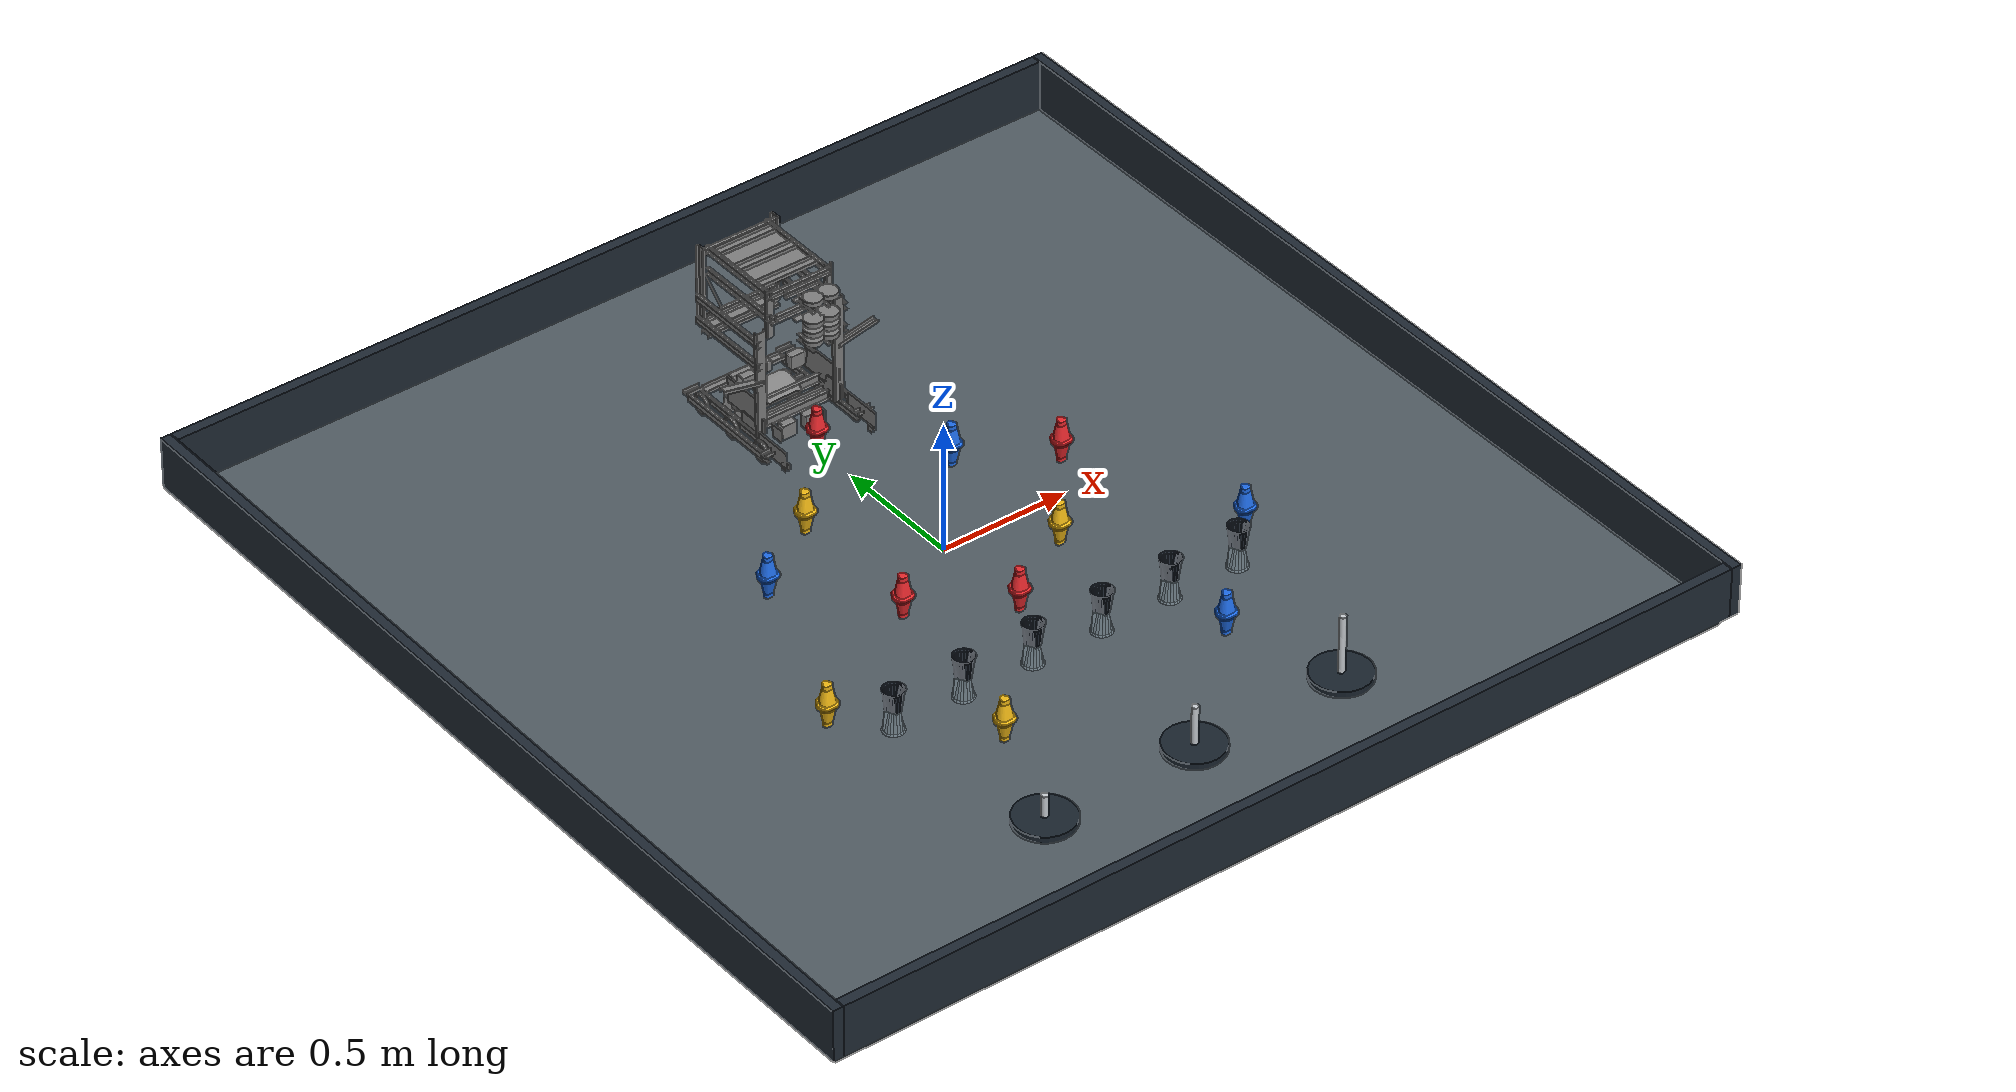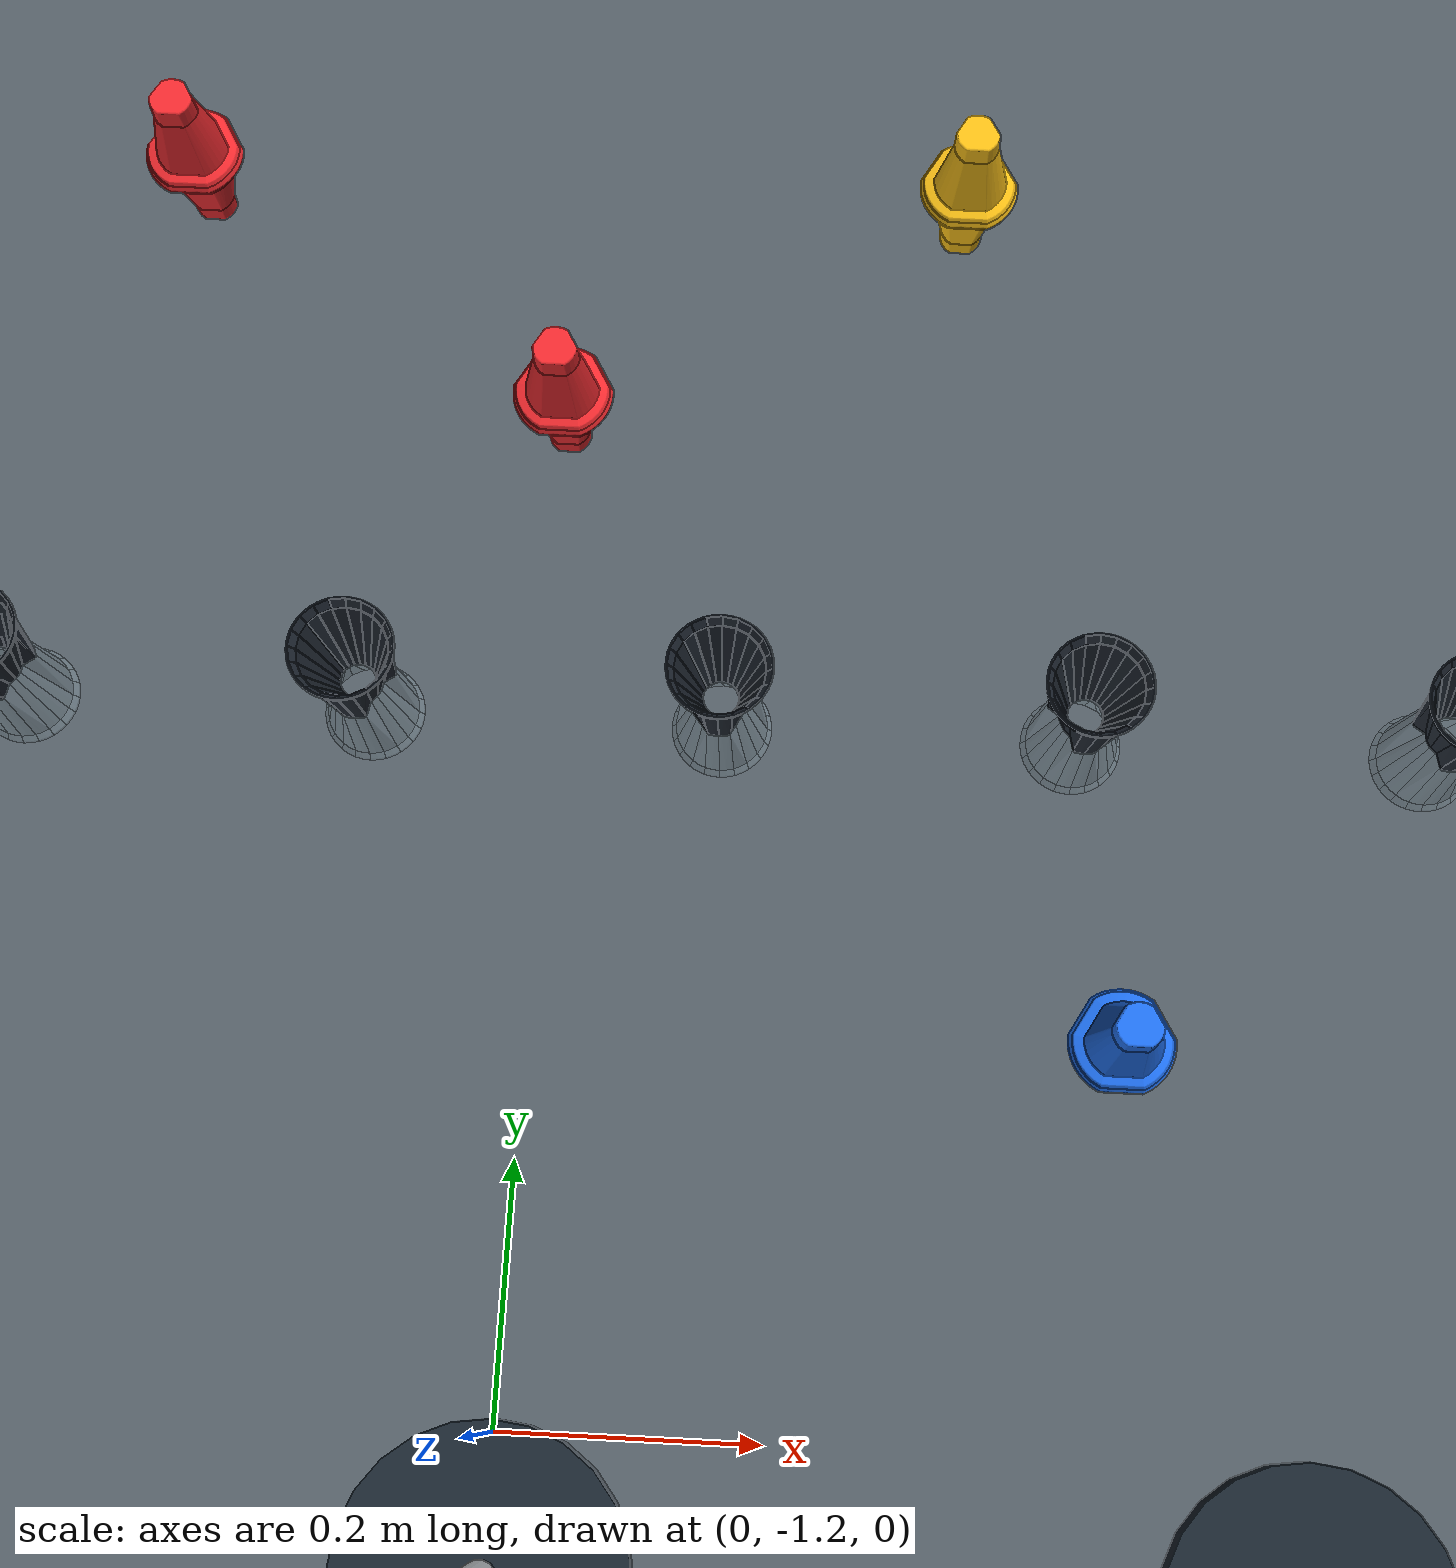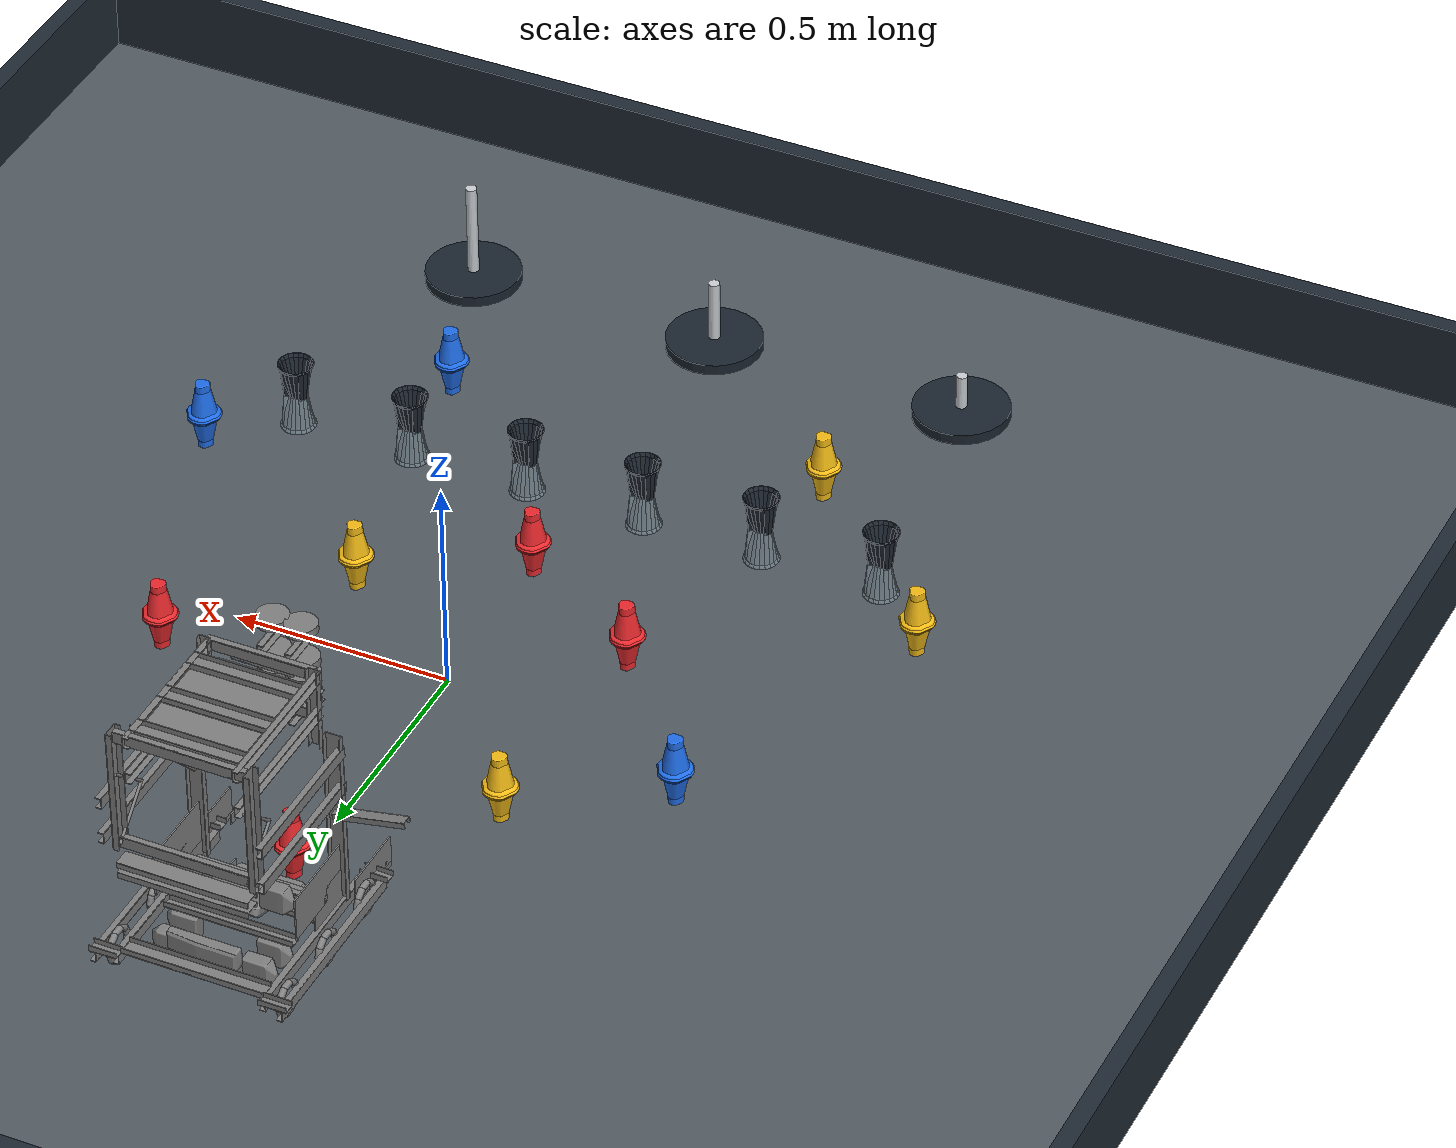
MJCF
<mujoco model="169C Override full playground">
  <compiler angle="radian" autolimits="true" inertiafromgeom="auto" />
  <option timestep=".002" integrator="implicitfast" solver="Newton" iterations="40" tolerance="1e-8" cone="elliptic" gravity="0 0 -9.81">
    <flag sleep="enable" />
  </option>
  <size memory="128M" />
  <default>
    <joint damping=".025" armature=".001" />
    <geom friction=".65 .003 .0001" solref=".008 1" solimp=".95 .99 .001" condim="4" margin=".0002" />
  </default>
  <asset>
    <mesh name="pin_slice0" vertex="0.017500186 -7.5826643e-05 0.001965456 -0.0080880759 0.013997452 0.00013886451 -0.0077943276 0.013773133 3.2043456e-05 -0.0077195547 0.013858587 3.2043456e-05 -0.0074311469 0.013634269 0 -0.0074952362 0.01357018 0 -0.0075486468 0.013495407 0 -0.015501248 -0.00029480457 0 -0.015522613 -0.00038025855 0 -0.015458521 -0.00020935058 0 0.0082604263 -0.013572287 3.2043456e-05 0.0081536053 -0.013609671 3.2043456e-05 0.0084099672 -0.013908763 0.00013886451 0.0082550858 -0.013962173 0.00013886451 0.0083565615 -0.014303989 0.00032045364 0.008084173 -0.013999557 0.00013886451 0.0079132651 -0.013796601 6.4086913e-05 0.0080307673 -0.013636374 3.2043456e-05 0.0080040596 -0.013278536 0 0.0080948542 -0.013251829 0 0.0081749676 -0.013209104 0 0.0084420155 -0.01364706 6.4086913e-05 0.016250414 -0.00032150745 0.00013886451 0.015881891 -0.00036423682 3.2043456e-05 0.016036777 -0.00049241542 6.4086913e-05 0.015433254 -0.0043912744 6.4086913e-05 0.015529394 -0.00047639369 0 0.015524053 -0.00038025855 0 0.015497346 -0.00029480457 0 0.015860529 -0.00024673461 3.2043456e-05 0.016218366 -0.00015059948 0.00013886451 0.016560187 -6.5145491e-05 0.00032045364 0.016602912 -0.00028411865 0.00032045364 0.016517458 -0.00050309657 0.0002617073 0.015892572 -0.0045194577 0.0002617073 0.014311666 -0.0082634304 0.0002617073 0.013895077 -0.0080230902 6.4086913e-05 0.011860194 -0.011505356 0.0002617073 0.011518373 -0.011174221 6.4086913e-05 0.0086930368 -0.014052968 0.0002617073 0.0085541723 -0.014229216 0.00032045364 0.0086823557 -0.014522967 0.00057147978 0.0084420155 -0.014608421 0.00057147978 0.0081803129 -0.014667172 0.00057147978 0.0081375836 -0.014352059 0.00032045364 0.0079132651 -0.014271946 0.0002617073 0.0079132651 -0.013283877 0 0.011149854 -0.010816378 0 0.013451781 -0.0077667235 0 0.014941892 -0.0042470693 0 0.015459962 -0.00020935058 0 0.01582314 -0.00013457775 3.2043456e-05 0.01616496 4.286766e-06 0.00013886451 0.016490755 0.0001378107 0.00032045364 0.016789846 0.00026065111 0.00057147978 0.016869959 1.4967918e-05 0.00057147978 0.016918025 -0.00024673461 0.00057147978 0.017120981 7.9059599e-05 0.00088659285 0.017174391 -0.00022003173 0.00088659285 0.016928711 -0.0005191183 0.00057147978 0.016287799 -0.0046316146 0.00057147978 0.014669509 -0.0084663818 0.00057147978 0.012159281 -0.011793766 0.00057147978 0.0089120148 -0.014400124 0.00057147978 0.008789172 -0.014757967 0.00088659285 0.0085167883 -0.014859442 0.00088659285 0.008217697 -0.014923534 0.00088659285 0.0079132651 -0.014688534 0.00057147978 -0.0079118274 -0.013796601 6.4086913e-05 -0.0079118274 -0.014271946 0.0002617073 -0.0080773948 -0.013999557 0.00013886451 -0.0080293272 -0.013636374 3.2043456e-05 -0.0081414865 -0.013615012 3.2043456e-05 -0.0080026219 -0.013278536 0 -0.0080934165 -0.013251829 0 -0.0079118274 -0.013283877 0 0.007550082 0.013495407 0 0.0074966763 0.01357018 0 0.0073524712 0.013682339 0 0.007427244 0.013634269 0 0.0076195143 0.013938701 3.2043456e-05 0.0077103136 0.013863928 3.2043456e-05 0.007790427 0.013773133 3.2043456e-05 0.008084173 0.014002793 0.00013886451 0.0079933785 0.013751769 6.4086913e-05 0.015903253 4.7016143e-05 6.4086913e-05 0.016319847 0.00028735637 0.0002617073 0.016672344 0.00049031018 0.00057147978 0.017030186 0.00035678624 0.00088659285 0.017201094 0.00043155908 0.0012390899 0.01730257 0.00012712955 0.0012390899 0.017409391 0.00015383243 0.0016022682 0.017473483 -0.00018798351 0.0016022682 0.017361321 -0.00019866466 0.0012390899 0.017249164 -0.00052980422 0.00097738264 0.016597571 -0.0047224091 0.00097738264 0.014941892 -0.0086266087 0.00097738264 0.012383599 -0.012012744 0.00097738264 0.0090775822 -0.014672513 0.00097738264 0.0088639448 -0.014928875 0.0012390899 0.0085701988 -0.015041032 0.0012390899 0.0085969017 -0.015147853 0.0016022682 0.0082443998 -0.015110464 0.0012390899 0.0079132651 -0.015003647 0.00097738264 -0.0079118274 -0.014688534 0.00057147978 -0.0081681893 -0.014667172 0.00057147978 -0.0081254624 -0.014352059 0.00032045364 -0.0082376216 -0.013967514 0.00013886451 -0.0082589863 -0.013572287 3.2043456e-05 -0.0081735323 -0.013209104 0 -0.011153755 -0.010816378 0 -0.013455684 -0.0077667235 0 -0.014940455 -0.0042470693 0 -0.015527954 -0.00047639369 0 -0.015885794 -0.0003695774 3.2043456e-05 -0.015864429 -0.00025207519 3.2043456e-05 -0.015827043 -0.00013991832 3.2043456e-05 -0.016168861 -1.0538101e-06 0.00013886451 -0.015901816 4.7016143e-05 6.4086913e-05 -0.011949548 0.0068993925 6.4086913e-05 -0.0079919408 0.013751769 6.4086913e-05 -0.008408532 0.013986768 0.0002617073 -0.0086168263 0.0144087 0.00057147978 -0.0087610314 0.014195065 0.00057147978 -0.0083658026 0.014211087 0.00032045364 -0.0079759167 0.014120292 0.00013886451 -0.0076287602 0.013938701 3.2043456e-05 -0.0073510311 0.013682339 0 -0.00378865 0.015065632 0 -1.9502639e-06 0.015535631 0 0.0037900876 0.015065632 0 0.0075928114 0.014136314 6.4086913e-05 0.0078384922 0.014237792 0.00013886451 0.0079666756 0.014130974 0.00013886451 0.0082123564 0.014387338 0.00032045364 0.0083619021 0.014221768 0.00032045364 0.0084046267 0.013986768 0.0002617073 0.012362237 0.0071397327 0.0002617073 0.012720079 0.0073426865 0.00057147978 0.016950073 0.000650537 0.00097738264 0.017126321 0.0007520151 0.0014527225 0.01730257 0.00047428607 0.0016022682 0.017382683 0.00037281036 0.001965456 0.017526888 -0.00053514479 0.001965456 0.017452116 -0.00053514479 0.0014527225 0.016795187 -0.0047758197 0.0014527225 0.015118141 -0.0087280891 0.0014527225 0.012533145 -0.012156944 0.0014527225 0.009189739 -0.014843421 0.0014527225 0.0089120148 -0.01503035 0.0016022682 0.0088158796 -0.015115804 0.001965456 0.0083725832 -0.015243988 0.001965456 0.0082604263 -0.015222625 0.0016022682 0.0079132651 -0.015206599 0.0014527225 -0.0079118274 -0.015003647 0.00097738264 -0.0082055758 -0.014923534 0.00088659285 -0.0084192131 -0.014613762 0.00057147978 -0.0083337591 -0.01430933 0.00032045364 -0.008403189 -0.013908763 0.00013886451 -0.008445916 -0.01364706 6.4086913e-05 -0.011516936 -0.011174221 6.4086913e-05 -0.013898978 -0.0080230902 6.4086913e-05 -0.015437157 -0.0043912744 6.4086913e-05 -0.01604068 -0.00049241542 6.4086913e-05 -0.016248974 -0.0003321886 0.00013886451 -0.016222272 -0.0001666212 0.00013886451 -0.016564087 -8.1167219e-05 0.00032045364 -0.016494658 0.00013247013 0.00032045364 -0.016318407 0.00028735637 0.0002617073 -0.012996366 0.0075029133 0.00097738264 -0.0090387581 0.014355292 0.00097738264 -0.0088251207 0.014568927 0.00088659285 -0.008445916 0.014600973 0.00057147978 -0.0082269404 0.014371314 0.00032045364 -0.0078423951 0.014232452 0.00013886451 -0.0075967143 0.014136314 6.4086913e-05 -0.0039168333 0.015562336 6.4086913e-05 -1.9502639e-06 0.016048357 6.4086913e-05 0.003918271 0.015562336 6.4086913e-05 0.0078224705 0.014558246 0.0002617073 0.008046789 0.0145262 0.00032045364 0.0082337187 0.014782564 0.00057147978 0.0084313343 0.014616995 0.00057147978 0.0086129234 0.014419381 0.00057147978 0.0087624691 0.014195065 0.00057147978 0.0090401981 0.014355292 0.00097738264 0.0092164467 0.014456768 0.0014527225 0.017190413 0.00078940151 0.001965456 0.016864619 -0.004797182 0.001965456 0.015187573 -0.0087654732 0.001965456 0.012586555 -0.012210355 0.001965456 0.0092271278 -0.014912853 0.001965456 0.0079132651 -0.015286717 0.001965456 -0.0079118274 -0.015206599 0.0014527225 -0.0082269404 -0.015110464 0.0012390899 -0.0084886454 -0.014864783 0.00088659285 -0.0086755751 -0.014528308 0.00057147978 -0.0085473941 -0.014234557 0.00032045364 -0.0086969398 -0.014052968 0.0002617073 -0.011864094 -0.011505356 0.0002617073 -0.014310229 -0.0082634304 0.0002617073 -0.015896475 -0.0045194577 0.0002617073 -0.01651602 -0.00050309657 0.0002617073 -0.016601474 -0.00029480457 0.00032045364 -0.016916587 -0.00026275634 0.00057147978 -0.01687386 -6.3943861e-06 0.00057147978 -0.016793747 0.00024996995 0.00057147978 -0.016676247 0.00049031018 0.00057147978 -0.016948633 0.000650537 0.00097738264 -0.017124884 0.0007520151 0.0014527225 -0.013172614 0.0076043914 0.0014527225 -0.0092150066 0.014456768 0.0014527225 -0.0089746664 0.014681086 0.0012390899 -0.0086275075 0.014787905 0.00088659285 -0.0082429622 0.014777224 0.00057147978 -0.0080560325 0.014520859 0.00032045364 -0.0078210304 0.014558246 0.0002617073 -0.0040343331 0.016026995 0.0002617073 -1.9502639e-06 0.016523697 0.0002617073 0.0040304278 0.016026995 0.0002617073 0.0080147408 0.014921426 0.00057147978 0.0083886049 0.014990859 0.00088659285 0.0086129234 0.014803927 0.00088659285 0.0088158796 0.01457961 0.00088659285 0.0089654253 0.014691767 0.0012390899 0.0090508793 0.0147612 0.0016022682 0.0092805384 0.014494154 0.001965456 -0.0079118274 -0.015286717 0.001965456 -0.0082429622 -0.015222625 0.0016022682 -0.0085420535 -0.015046372 0.0012390899 -0.0087770532 -0.014763307 0.00088659285 -0.0089105747 -0.014400124 0.00057147978 -0.012157845 -0.011793766 0.00057147978 -0.014668069 -0.0084663818 0.00057147978 -0.016291701 -0.0046316146 0.00057147978 -0.016927271 -0.0005191183 0.00057147978 -0.017178292 -0.00023071289 0.00088659285 -0.017124884 5.2356719e-05 0.00088659285 -0.017034087 0.00034610509 0.00088659285 -0.017204997 0.00041553735 0.0012390899 -0.017311813 0.00045826434 0.0016022682 -0.017194314 0.00078940151 0.001965456 -0.0092790983 0.014494154 0.001965456 -0.0090601204 0.014750518 0.0016022682 -0.0087610314 0.014921426 0.0012390899 -0.0083978484 0.014985518 0.00088659285 -0.0080186461 0.014921426 0.00057147978 -0.0041304683 0.016422221 0.00057147978 -1.9502639e-06 0.016934948 0.00057147978 0.0041319083 0.016422221 0.00057147978 0.0081642864 0.015199153 0.00097738264 0.008495426 0.015145745 0.0012390899 0.0087411068 0.014937451 0.0012390899 0.0088158796 0.015022905 0.0016022682 0.0090134905 0.014868018 0.001965456 -0.0083711455 -0.015243988 0.001965456 -0.0085687588 -0.015153193 0.0016022682 -0.008851826 -0.014934215 0.0012390899 -0.0090814851 -0.014672513 0.00097738264 -0.012387502 -0.012012744 0.00097738264 -0.014945795 -0.0086266087 0.00097738264 -0.016596133 -0.0047224091 0.00097738264 -0.017247724 -0.00052980422 0.00097738264 -0.017365224 -0.00021469116 0.0012390899 -0.017306473 0.0001004219 0.0012390899 -0.017418632 0.00012712955 0.0016022682 -0.017386586 0.00037281036 0.001965456 -0.0090120528 0.014868018 0.001965456 -0.0088411448 0.01500154 0.0016022682 -0.0085100077 0.015135064 0.0012390899 -0.0081681893 0.015199153 0.00097738264 -0.0042105817 0.016731994 0.00097738264 -1.9502639e-06 0.017255401 0.00097738264 0.0042120217 0.016731994 0.00097738264 0.0082657669 0.015380745 0.0014527225 0.0085648535 0.01523654 0.0016022682 0.0086823557 0.015188472 0.001965456 -0.0088144396 -0.015115804 0.001965456 -0.0088998936 -0.015041032 0.0016022682 -0.0091883014 -0.014843421 0.0014527225 -0.012531707 -0.012156944 0.0014527225 -0.015122044 -0.0087280891 0.0014527225 -0.016793747 -0.0047758197 0.0014527225 -0.017450678 -0.00053514479 0.0014527225 -0.017472043 -0.00020400524 0.0016022682 -0.017498746 -7.5826643e-05 0.001965456 -0.008680918 0.015188472 0.001965456 -0.0085740993 0.015225858 0.0016022682 -0.0082643269 0.015380745 0.0014527225 -0.0042586493 0.016929607 0.0014527225 -1.9502639e-06 0.017458355 0.0014527225 0.0042600869 0.016929607 0.0014527225 0.0082978104 0.015444836 0.001965456 -0.0092256878 -0.014912853 0.001965456 -0.012585115 -0.012210355 0.001965456 -0.015186135 -0.0087654732 0.001965456 -0.016863179 -0.004797182 0.001965456 -0.017525451 -0.00053514479 0.001965456 -0.0083017133 0.015444836 0.001965456 -0.0042800139 0.01700438 0.001965456 -1.9502639e-06 0.017533128 0.001965456 0.004281454 0.01700438 0.001965456 0.018077779 -0.00084900027 0.017500008 0.017500782 -0.0044081178 0.017500008 0.015724353 -0.0089378371 0.017500008 0.018078073 -0.00072378761 0.017500008 0.018079938 -0.0008107144 0.017500008 0.017895154 0.00017175345 0.017500008 0.017833708 0.00029054028 0.017500008 0.017774443 0.00039470435 0.017500008 0.013046673 -0.012539101 0.017500008 0.0084113094 0.016016788 0.017500008 0.0083381312 0.016061196 0.017500008 0.009189739 0.015266519 0.017500008 0.012566767 -0.01295165 0.017500008 0.0097884801 -0.015219647 0.017500008 0.0083041915 0.01607809 0.017500008 0.0082833849 0.016087192 0.017500008 0.0085434985 -0.015591949 0.017500008 0.008664742 -0.015589784 0.017500008 0.0088193092 -0.015579843 0.017500008 0.0096651116 -0.015291233 0.017500008 0.0097398565 -0.015248299 0.017500008 -0.0087973689 -0.01558364 0.017500008 -0.0086686425 -0.015589784 0.017500008 -0.008547399 -0.015591949 0.017500008 -0.0096627934 -0.015291412 0.017500008 -0.018078498 -0.0008107144 0.017500008 -0.018076932 -0.00072463709 0.017500008 -0.017813849 0.00032597934 0.017500008 -0.017901005 0.00015215183 0.017500008 -0.018041299 -0.0002791167 0.017500008 -0.0091883014 0.015266519 0.017500008 -0.008336692 0.016061196 0.017500008 -0.0084117322 0.016016102 0.017500008 0.0043349871 0.017565948 0.017500008 -0.0097920738 -0.015219647 0.017500008 -0.018076339 -0.00084900027 0.017500008 -0.0082819449 0.016087192 0.017500008 -0.0083027538 0.01607809 0.017500008 -0.0049359676 0.017356608 0.017500008 -0.0001231076 0.01808247 0.017500008 -0.015601758 -0.0091477938 0.017500008 -0.017382172 -0.0050300068 0.017500008 0.017383487 -0.0050300068 0.017500008 0.01741461 -0.0049123076 0.017500008 0.015603195 -0.0091477938 0.017500008 0.015673099 -0.0090481262 0.017500008 0.018040176 -0.00029107194 0.017500008 0.018039123 -0.00028499424 0.017500008 0.018037568 -0.0002791167 0.017500008 0.017886308 0.00019014531 0.017500008 0.01767944 0.00055951446 0.017500008 0.017239725 0.0013216128 0.017500008 0.01296022 -0.012624812 0.017500008 0.0091113358 0.015396995 0.017500008 0.0090997352 0.015413487 0.017500008 0.009085931 0.015429873 0.017500008 0.0087770431 0.015762225 0.017500008 0.0087729776 0.015766523 0.017500008 0.0087682327 0.015770415 0.017500008 0.0087629651 0.015774086 0.017500008 0.0087783631 -0.015584959 0.017500008 0.0087982272 -0.01558364 0.017500008 0.0092637411 -0.015480925 0.017500008 0.0092695314 -0.015479517 0.017500008 0.009275329 -0.015477335 0.017500008 0.009280971 -0.015474719 0.017500008 0.004932842 0.017356608 0.017500008 0.0044524394 0.017534084 0.017500008 -0.0092738913 -0.015477335 0.017500008 -0.0092680937 -0.015479517 0.017500008 -0.0092623034 -0.015480925 0.017500008 -0.0087769231 -0.015584959 0.017500008 -0.01788487 0.00019014531 0.017500008 -0.017893716 0.00017175345 0.017500008 -0.018043024 -0.00028499424 0.017500008 -0.018044077 -0.00029107194 0.017500008 -0.01804463 -0.00029736152 0.017500008 -0.008766795 0.015770415 0.017500008 -0.0087715399 0.015766523 0.017500008 -0.0087757746 0.015762225 0.017500008 -0.0090982975 0.015413487 0.017500008 -0.0091098979 0.015396995 0.017500008 0.00011933057 0.01808247 0.017500008 -1.9502639e-06 0.018093214 0.017500008 -0.012958903 -0.012624812 0.017500008 -0.012565327 -0.01295165 0.017500008 -0.013045233 -0.012539101 0.017500008 -0.015671661 -0.0090481262 0.017500008 -0.015723039 -0.0089378371 0.017500008 -0.017499344 -0.0044081178 0.017500008 -0.017413172 -0.0049123076 0.017500008 -0.0044562187 0.017534084 0.017500008 -0.0043387665 0.017565948 0.017500008" />
    <mesh name="pin_slice1" vertex="0.027679943 -0.00018264293 0.062889122 0.025559606 -0.00058320998 0.05286425 0.023428587 -0.00098912237 0.042844714 0.021286883 -0.0014057111 0.032825183 0.019668593 -0.0014644622 0.025203714 0.012570533 -0.019794435 0.042844714 0.013280873 -0.02184 0.05286425 0.013996553 -0.023880224 0.062889122 0.018103709 -0.00079684733 0.017608957 0.011860194 -0.017732849 0.032825183 0.0083619021 0.016075062 0.017608957 0.0094247387 0.019135398 0.032825183 0.010856104 0.020780396 0.042844714 0.012276783 0.022425394 0.05286425 0.01368144 0.024065051 0.062889122 0.011101784 -0.016301484 0.025203714 0.0085701988 0.017762787 0.025203714 0.0097398565 -0.015276031 0.017608957 -0.0097384165 -0.015276031 0.017608957 -0.018102269 -0.00079684733 0.017608957 -0.008360462 0.016075062 0.017608957 -0.014000456 -0.023880224 0.062889122 -0.013284774 -0.02184 0.05286425 -0.012569093 -0.019794435 0.042844714 -0.011858754 -0.017732849 0.032825183 -0.011100344 -0.016301484 0.025203714 -0.019667153 -0.0014644622 0.025203714 -0.021285445 -0.0014057111 0.032825183 -0.023427147 -0.00098912237 0.042844714 -0.025558166 -0.00058320998 0.05286425 -0.027678506 -0.00018264293 0.062889122 -0.0085687588 0.017762787 0.025203714 -0.01368 0.024065051 0.062889122 -0.012275345 0.022425394 0.05286425 -0.010860004 0.020780396 0.042844714 -0.009428644 0.019135398 0.032825183 0.017414605 -0.0049123076 0.017499988 0.017500777 -0.0044081254 0.017499988 0.015724348 -0.0089378367 0.017499988 0.015673095 -0.0090481241 0.017499988 0.018079934 -0.00081071694 0.017499988 0.018077775 -0.00084899867 0.017499988 0.018040172 -0.00029106714 0.017499988 0.018039119 -0.00028499182 0.017499988 0.018037564 -0.00027911657 0.017499988 0.017895149 0.00017175709 0.017499988 0.017886305 0.00019014706 0.017499988 0.017679438 0.00055951422 0.017499988 0.017239744 0.0013215771 0.017499988 0.013046669 -0.012539098 0.017499988 0.0091113356 0.015396991 0.017499988 0.0090997362 0.015413482 0.017499988 0.0087729777 0.015766518 0.017499988 0.0087682346 0.015770409 0.017499988 0.0087629691 0.015774078 0.017499988 0.012960218 -0.012624809 0.017499988 0.012566771 -0.012951641 0.017499988 0.0087783598 -0.015584957 0.017499988 0.0087982219 -0.015583639 0.017499988 0.0092695274 -0.015479515 0.017499988 0.0092637393 -0.015480922 0.017499988 0.0092753227 -0.015477333 0.017499988 0.0092809625 -0.015474718 0.017499988 0.0043349868 0.017565944 0.017499988 0.0044524372 0.017534081 0.017499988 -0.0092680897 -0.015479515 0.017499988 -0.009273885 -0.015477333 0.017499988 -0.0092623016 -0.015480922 0.017499988 -0.0087973636 -0.015583639 0.017499988 -0.0087769198 -0.015584957 0.017499988 -0.0085473894 -0.015591947 0.017499988 -0.017884867 0.00019014706 0.017499988 -0.017893712 0.00017175709 0.017499988 -0.018041296 -0.00027911657 0.017499988 -0.01804302 -0.00028499182 0.017499988 -0.018044625 -0.00029735427 0.017499988 -0.018044072 -0.00029106714 0.017499988 -0.00877154 0.015766518 0.017499988 -0.008766797 0.015770409 0.017499988 -0.008775773 0.015762222 0.017499988 -0.0091098977 0.015396991 0.017499988 -1.9502639e-06 0.01809321 0.017499988 0.00011932872 0.018082465 0.017499988 -0.018076335 -0.00084899867 0.017499988 -0.018078494 -0.00081071694 0.017499988 -0.0083366877 0.016061194 0.017499988 -0.0083027531 0.016078085 0.017499988 -0.012565331 -0.012951641 0.017499988 -0.012958901 -0.012624809 0.017499988 -0.015601755 -0.0091477902 0.017499988 -0.015671657 -0.0090481241 0.017499988 -0.017382168 -0.005030005 0.017499988 -0.017413167 -0.0049123076 0.017499988 -0.0044562166 0.017534081 0.017499988 -0.0043387662 0.017565944 0.017499988 0.017383483 -0.005030005 0.017499988 0.018078068 -0.0007237742 0.017499988 0.017833707 0.00029053871 0.017499988 0.017774437 0.00039471177 0.017499988 0.015603193 -0.0091477902 0.017499988 0.0083381268 0.016061194 0.017499988 0.0084113184 0.016016777 0.017499988 0.009189739 0.015266516 0.017499988 0.0087770415 0.015762222 0.017499988 0.0090859335 0.015429865 0.017499988 0.0097884766 -0.015219644 0.017499988 0.0083041909 0.016078085 0.017499988 0.0085434888 -0.015591947 0.017499988 0.0086647428 -0.015589782 0.017499988 0.0088193017 -0.015579842 0.017499988 0.0097398565 -0.015248294 0.017499988 0.0096650979 -0.015291236 0.017499988 0.0049328326 0.017356607 0.017499988 0.0082833842 0.016087187 0.017499988 -0.0086686433 -0.015589782 0.017499988 -0.0096627795 -0.015291415 0.017499988 -0.018076927 -0.00072462383 0.017499988 -0.017813846 0.00032598083 0.017499988 -0.017900999 0.00015215746 0.017499988 -0.0090982985 0.015413482 0.017499988 -0.0091883014 0.015266516 0.017499988 -0.0084117416 0.016016091 0.017499988 -0.0097920704 -0.015219644 0.017499988 -0.017499339 -0.0044081254 0.017499988 -0.0082819441 0.016087187 0.017499988 -0.0049359581 0.017356607 0.017499988 -0.00012310575 0.018082465 0.017499988 -0.013045229 -0.012539098 0.017499988 -0.015723034 -0.0089378367 0.017499988 0.0297076 0.00019626235 0.072500008 0.013870166 -0.026074295 0.072500008 0.013884224 -0.026073943 0.072500008 0.014299073 -0.025990226 0.072500008 0.015362957 0.025381026 0.072500008 0.015645168 0.025046533 0.072500008 0.018969525 -0.022860023 0.072500008 0.018954587 -0.02287058 0.072500008 0.018924717 -0.022891356 0.072500008 0.010312747 0.027862169 0.072500008 0.010329366 0.027854475 0.072500008 0.010460743 0.027792663 0.072500008 0.010362375 0.02783909 0.072500008 -0.013866226 -0.026074363 0.072500008 -0.01428175 -0.025999205 0.072500008 -0.029653455 0.00062476611 0.072500008 -0.029657571 0.00061137951 0.072500008 -0.029515845 0.001024603 0.072500008 -0.029522586 0.0010122375 0.072500008 -0.015641277 0.025058995 0.072500008 -0.01565008 0.025044458 0.072500008 -0.014672421 -0.02583239 0.072500008 -0.014686582 -0.025825955 0.072500008 -0.029282071 -0.0050065185 0.072500008 -0.029282782 -0.0050000176 0.072500008 -0.029287602 -0.00494555 0.072500008 -0.029284463 -0.004981785 0.072500008 -0.029296534 -0.0048370361 0.072500008 -0.015361389 0.025381298 0.072500008 -0.015372871 0.025368864 0.072500008 -0.010305372 0.027864805 0.072500008 -0.010311362 0.027862169 0.072500008 -0.015021531 0.025631877 0.072500008 -0.01503429 0.025622865 0.072500008 0.029283511 -0.0050065185 0.072500008 0.018974795 -0.022856149 0.072500008 0.010306812 0.027864805 0.072500008 0.010278162 0.027875389 0.072500008 -0.018978649 -0.022856149 0.072500008 0.025729592 -0.014853137 0.072500008 0.018998259 -0.022836658 0.072500008 0.0052045385 0.029247144 0.072500008 -1.9502639e-06 0.029708412 0.072500008 -0.019002121 -0.022836658 0.072500008 -0.022708167 -0.019157124 0.072500008 -0.025728154 -0.014853137 0.072500008 -0.027933755 -0.010118514 0.072500008 -0.029276932 -0.0050365868 0.072500008 0.027942288 -0.01008932 0.072500008 0.022709602 -0.019157124 0.072500008 0.022728701 -0.019131789 0.072500008 -0.0052346317 0.029243285 0.072500008 -0.022727266 -0.019131789 0.072500008 0.02951601 0.001031873 0.072500008 0.02965411 0.00063230124 0.072500008 0.029524193 0.0010169539 0.072500008 0.029706198 0.00021170918 0.072500008 0.029659027 0.00061614896 0.072500008 0.029284223 -0.0050000176 0.072500008 0.014285462 -0.025993456 0.072500008 0.014687799 -0.025825955 0.072500008 0.015637852 0.025058723 0.072500008 0.015372636 0.025370869 0.072500008 0.018835281 -0.022953443 0.072500008 0.015022971 0.025631877 0.072500008 -0.013883426 -0.026073981 0.072500008 -0.014298148 -0.025995265 0.072500008 -0.018973371 -0.022860023 0.072500008 -0.029706162 0.00019626235 0.072500008 0.029278372 -0.0050365868 0.072500008 0.027929893 -0.010118514 0.072500008 0.0052360327 0.029243285 0.072500008 -0.0052031375 0.029247144 0.072500008 -0.02794615 -0.01008932 0.072500008 -0.010276761 0.027875389 0.072500008" />
    <mesh name="pin_slice2" vertex="-0.015762953 -0.033119988 0.075482968 -0.015506589 -0.033178739 0.075482968 -0.015843067 -0.032890329 0.075215924 -0.015618748 -0.03247908 0.074810017 -0.015869772 -0.032751464 0.075087741 -0.015554657 -0.032890329 0.075119785 0.020945067 -0.029247832 0.074767287 0.025602335 -0.0252742 0.074767287 0.025255174 -0.024937725 0.074569672 0.029116649 -0.020296483 0.074569672 0.029511875 -0.020574207 0.074767287 0.029853691 -0.020809206 0.075087741 0.025896081 -0.025567951 0.075087741 0.021185407 -0.029584307 0.075087741 0.015865869 -0.032751464 0.075087741 0.015759053 -0.033119988 0.075482968 0.015844507 -0.032890329 0.075215924 0.015508027 -0.033178739 0.075482968 0.015550756 -0.032890329 0.075119785 0.015251665 -0.032890329 0.075087741 0.015620188 -0.03247908 0.074810017 0.01568428 -0.0323776 0.074767287 0.020667338 -0.028857946 0.074569672 0.032134256 -0.015067739 0.074569672 0.032572211 -0.015276031 0.074767287 0.032946076 -0.015446944 0.075087741 0.036294817 0.0026320123 0.075087741 0.036294817 0.002867012 0.075119785 0.035883569 0.0029417848 0.074815357 0.036107887 0.0032355332 0.075087741 0.036294817 0.003182125 0.075237287 0.036561865 0.002909739 0.075482968 0.036487092 0.0031607603 0.075482968 0.03660993 0.0026533746 0.075498989 0.036535157 -0.0035847997 0.075498989 0.036214704 -0.003558092 0.075087741 0.035397548 -0.0097268341 0.075498989 0.035087775 -0.0096413801 0.075087741 0.033234481 -0.015585804 0.075498989 0.030115394 -0.0209908 0.075498989 0.0261204 -0.025792269 0.075498989 0.021372337 -0.029846014 0.075498989 0.016004734 -0.033034534 0.075498989 0.015251665 -0.033210782 0.075498989 -0.015250227 -0.033210782 0.075498989 -0.015250227 -0.032890329 0.075087741 -0.016008634 -0.033034534 0.075498989 -0.021370902 -0.029846014 0.075498989 -0.026118962 -0.025792269 0.075498989 -0.021189308 -0.029584307 0.075087741 -0.015688181 -0.0323776 0.074767287 -0.015250227 -0.03247908 0.074767287 0.015251665 -0.03247908 0.074767287 0.015251665 -0.031993055 0.074569672 0.015475983 -0.031944989 0.074569672 0.03422789 -0.0094063804 0.074569672 0.034692549 -0.0095345638 0.074767287 0.035803456 -0.0035153674 0.074767287 0.035883569 0.002605307 0.074767287 0.035750045 0.0030325794 0.074767287 0.036385616 0.00339576 0.075498989 -0.030113956 -0.0209908 0.075498989 -0.025894644 -0.025567951 0.075087741 -0.020948967 -0.029247832 0.074767287 -0.015474543 -0.031944989 0.074569672 -0.015250227 -0.031993055 0.074569672 0.035322775 -0.0034672975 0.074569672 0.035402888 0.0025679206 0.074569672 0.035333456 0.0027868986 0.074569672 0.025944151 0.020849828 0.075087741 0.021131997 0.029811863 0.075498989 -0.033238384 -0.015585804 0.075498989 -0.029852251 -0.020809206 0.075087741 -0.025600895 -0.0252742 0.074767287 -0.020665903 -0.028857946 0.074569672 0.02516438 0.020401191 0.074569672 0.025586309 0.020641531 0.074767287 0.020859613 0.029651636 0.075087741 0.020822224 0.02968902 0.075071719 0.020822224 0.030009474 0.075290697 0.020982451 0.030020158 0.075482968 -0.035396108 -0.0097268341 0.075498989 -0.032949976 -0.015446944 0.075087741 -0.029515776 -0.020574207 0.074767287 -0.025259077 -0.024937725 0.074569672 0.020079841 0.029202999 0.074569672 0.020053138 0.029411294 0.07460172 0.020501771 0.02944334 0.074767287 0.020459046 0.029790499 0.074884785 0.020459046 0.030148339 0.075130471 0.020800862 0.03021243 0.075482968 -0.036533722 -0.0035847997 0.075498989 -0.035091678 -0.0096413801 0.075087741 -0.032576112 -0.015276031 0.074767287 -0.02912055 -0.020296483 0.074569672 0.020197339 0.029774474 0.074767287 0.020426998 0.030116293 0.075087741 0.020608592 0.030377998 0.075498989 -0.036485652 0.0031607603 0.075482968 -0.036565766 0.002909739 0.075482968 -0.036613835 0.0026533746 0.075498989 -0.036218607 -0.003558092 0.075087741 -0.034691109 -0.0095345638 0.074767287 -0.032138159 -0.015067739 0.074569672 0.014658823 0.032327427 0.074569672 0.014856438 0.032765381 0.074767287 0.015027346 0.033144585 0.075087741 0.01516087 0.033432993 0.075498989 -0.020804765 0.03021243 0.075482968 -0.020981016 0.030020158 0.075482968 -0.021135902 0.029811863 0.075498989 -0.036384176 0.00339576 0.075498989 -0.036293379 0.003182125 0.075237287 -0.036293379 0.002867012 0.075119785 -0.036293379 0.0026320123 0.075087741 -0.035802018 -0.0035153674 0.074767287 -0.03422645 -0.0094063804 0.074569672 0.0089707659 0.034340948 0.074569672 0.0090882633 0.034810948 0.074767287 0.0091950844 0.035211515 0.075087741 0.0092751978 0.035515947 0.075498989 -0.020607152 0.030377998 0.075498989 -0.020457606 0.030148339 0.075130471 -0.020820789 0.030009474 0.075290697 -0.020820789 0.02968902 0.075071719 -0.020858173 0.029651636 0.075087741 -0.025942711 0.020849828 0.075087741 -0.03611179 0.0032355332 0.075087741 -0.035882131 0.0029417848 0.074815357 -0.035882131 0.002605307 0.074767287 -0.035326678 -0.0034672975 0.074569672 0.0030210017 0.035366401 0.074569672 0.0030583858 0.035847081 0.074767287 0.0030957698 0.03625833 0.075087741 0.0031224775 0.036573443 0.075498989 -0.0031210374 0.036573443 0.075498989 -0.0092737577 0.035515947 0.075498989 -0.01515943 0.033432993 0.075498989 -0.02042556 0.030116293 0.075087741 -0.020457606 0.029790499 0.074884785 -0.020500333 0.02944334 0.074767287 -0.025584871 0.020641531 0.074767287 -0.030669412 0.011834385 0.074767287 -0.035748607 0.0030325794 0.074767287 -0.035332019 0.0027868986 0.074569672 -0.035401448 0.0025679206 0.074569672 -0.0030195617 0.035366401 0.074569672 -0.0030569481 0.035847081 0.074767287 -0.0030943321 0.03625833 0.075087741 -0.0091936443 0.035211515 0.075087741 -0.015031249 0.033144585 0.075087741 -0.020195903 0.029774474 0.074767287 -0.020057039 0.029411294 0.07460172 -0.020083742 0.029202999 0.074569672 -0.02516828 0.020401191 0.074569672 -0.0089693258 0.034340948 0.074569672 -0.0090921662 0.034810948 0.074767287 -0.014855001 0.032765381 0.074767287 -0.014657385 0.032327427 0.074569672 0.029524189 0.001016953 0.072499988 0.027942284 -0.010089318 0.072499988 0.029284218 -0.0050000158 0.072499988 0.013884223 -0.026073939 0.072499988 0.014687797 -0.025825951 0.072499988 0.022728698 -0.019131785 0.072499988 0.025729588 -0.014853135 0.072499988 0.015372633 0.025370866 0.072499988 0.015637849 0.02505872 0.072499988 0.018835271 -0.022953445 0.072499988 0.018998257 -0.022836654 0.072499988 0.01046075 0.027792655 0.072499988 0.015022968 0.025631873 0.072499988 0.01027816 0.027875386 0.072499988 -0.013866224 -0.026074359 0.072499988 0.0052045367 0.02924714 0.072499988 -0.014281747 -0.025999201 0.072499988 -0.029653451 0.0006247659 0.072499988 -0.02951584 0.0010246027 0.072499988 -0.015650078 0.025044454 0.072499988 -1.9502639e-06 0.029708407 0.072499988 -0.014298146 -0.025995261 0.072499988 -0.014672419 -0.025832387 0.072499988 -0.018973367 -0.02286002 0.072499988 -0.022708163 -0.019157122 0.072499988 -0.02572815 -0.014853135 0.072499988 -0.02793375 -0.010118514 0.072499988 -0.029276927 -0.0050365867 0.072499988 -0.029296531 -0.0048370264 0.072499988 -0.029706158 0.00019626156 0.072499988 -0.015641274 0.025058992 0.072499988 -0.015372868 0.02536886 0.072499988 -0.0052346313 0.029243281 0.072499988 -0.015361387 0.025381294 0.072499988 -0.015034288 0.025622861 0.072499988 -0.010311362 0.027862165 0.072499988 0.029516006 0.0010318728 0.072499988 0.029654105 0.00063230113 0.072499988 0.029659023 0.00061614809 0.072499988 0.029278368 -0.0050365867 0.072499988 0.029283507 -0.005006517 0.072499988 0.029706194 0.00021170914 0.072499988 0.029707596 0.00019626156 0.072499988 0.013870164 -0.026074291 0.072499988 0.01428546 -0.025993452 0.072499988 0.014299071 -0.025990222 0.072499988 0.027929889 -0.010118514 0.072499988 0.015362955 0.025381023 0.072499988 0.015645166 0.025046529 0.072499988 0.018954582 -0.022870577 0.072499988 0.018924711 -0.022891355 0.072499988 0.022709598 -0.019157122 0.072499988 0.018969522 -0.02286002 0.072499988 0.018974792 -0.022856146 0.072499988 0.010312746 0.027862165 0.072499988 0.010329366 0.02785447 0.072499988 0.010362377 0.027839085 0.072499988 0.010306811 0.027864801 0.072499988 -0.013883425 -0.026073977 0.072499988 0.0052360324 0.029243281 0.072499988 -0.029657567 0.00061137866 0.072499988 -0.029522582 0.0010122366 0.072499988 -0.0052031356 0.02924714 0.072499988 -0.01468658 -0.025825951 0.072499988 -0.018978646 -0.022856146 0.072499988 -0.019002118 -0.022836654 0.072499988 -0.022727263 -0.019131785 0.072499988 -0.027946146 -0.010089318 0.072499988 -0.029282067 -0.005006517 0.072499988 -0.029282778 -0.0050000158 0.072499988 -0.029284459 -0.0049817823 0.072499988 -0.029287598 -0.0049455456 0.072499988 -0.010305371 0.027864801 0.072499988 -0.010276759 0.027875386 0.072499988 -0.015021528 0.025631873 0.072499988 0.037658528 0.0034284069 0.077500008 0.037714459 0.0031884706 0.077500008 0.015857805 -0.034325225 0.077500008 0.015926168 -0.034309225 0.077500008 0.015510224 -0.034364927 0.077500008 0.015677527 -0.034350165 0.077500008 -0.015929747 -0.034310817 0.077500008 -0.015859572 -0.034326899 0.077500008 -0.016255951 -0.034194299 0.077500008 -0.016098185 -0.034255631 0.077500008 0.037773444 0.00085283337 0.077500008 0.036686593 -0.0093202618 0.077500008 0.037425124 -0.0053328797 0.077500008 0.036064553 -0.011384981 0.077500008 0.031704217 -0.020644182 0.077500008 0.023332135 -0.029742965 0.077500008 0.026414557 -0.027111291 0.077500008 0.021630896 -0.031069482 0.077500008 -0.021629459 -0.031069482 0.077500008 -0.023330698 -0.029742965 0.077500008 -0.027889525 -0.025539332 0.077500008 0.031911431 0.013455181 0.077500008 0.022008847 0.0306044 0.077500008 -0.033731144 -0.017135281 0.077500008 0.022003226 0.030613769 0.077500008 -0.034662329 -0.015188599 0.077500008 0.021798596 0.030898483 0.077500008 0.021749143 0.030950845 0.077500008 -0.036687027 -0.0093202618 0.077500008 -0.037655457 0.0034289225 0.077500008 -0.037677274 0.003360561 0.077500008 -0.037775474 0.00085283337 0.077500008 -0.037723465 -0.0031969623 0.077500008 0.019628692 0.032285334 0.077500008 0.016092055 0.034268624 0.077500008 -0.021751221 0.030949425 0.077500008 -0.021799467 0.030896794 0.077500008 0.010271959 0.036430268 0.077500008 0.0081716393 0.036923028 0.077500008 0.0020264147 0.037776301 0.077500008 -0.010270518 0.036430268 0.077500008 -0.014091472 0.035078024 0.077500008 -0.016090615 0.034268624 0.077500008 -0.019627252 0.032285334 0.077500008 0.037678995 0.003359694 0.077500008 0.037515404 0.0037498727 0.077500008 0.037741593 0.0030093608 0.077500008 0.037724902 -0.0031969623 0.077500008 0.033729114 -0.017135281 0.077500008 0.034660299 -0.015188599 0.077500008 0.030484496 -0.022422239 0.077500008 0.027890963 -0.025539332 0.077500008 0.016263291 -0.034190552 0.077500008 0.018146271 -0.033139455 0.077500008 -0.015508786 -0.034364927 0.077500008 -0.016265319 -0.034190552 0.077500008 -0.018148299 -0.033139455 0.077500008 -0.026413119 -0.027111291 0.077500008 -0.031702779 -0.020644182 0.077500008 -0.030483058 -0.022422239 0.077500008 -0.036063114 -0.011384981 0.077500008 0.02191093 0.03075277 0.077500008 -0.037425561 -0.0053328797 0.077500008 0.021489189 0.031172409 0.077500008 0.02147982 0.031179903 0.077500008 -0.037585513 0.0035995748 0.077500008 -0.037741749 0.0030206027 0.077500008 -0.037743623 0.0030093608 0.077500008 0.014092912 0.035078024 0.077500008 -0.021620244 0.031069342 0.077500008 -0.022007131 0.030613769 0.077500008 -0.037513964 0.0037498727 0.077500008 -0.021478381 0.031179903 0.077500008 0.00417732 0.03760955 0.077500008 -0.0020268481 0.037776301 0.077500008 -0.0041758808 0.03760955 0.077500008 -0.0081702001 0.036923028 0.077500008" />
    <mesh name="pin_slice3" vertex="0.040070838 -0.0024845743 0.082297962 0.039931974 0.0039672374 0.082297962 0.039841179 0.0042396235 0.082297962 0.039718336 0.0045013284 0.082297962 0.023754382 0.032145836 0.082297962 0.02340188 0.032594473 0.082297962 0.012159281 0.03826117 0.082297962 -1.9502639e-06 0.040146507 0.082297962 -0.0061546706 0.039671167 0.082297962 -0.017883291 0.035943216 0.082297962 -0.023176126 0.032781405 0.082297962 -0.023592715 0.032386176 0.082297962 -0.039716899 0.0045013284 0.082297962 -0.039930533 0.0039672374 0.082297962 -0.039978603 0.0036841702 0.082297962 -0.040069398 -0.0024845743 0.082297962 -0.037430991 -0.014506945 0.082297962 -0.034765882 -0.020072164 0.082297962 -0.02705362 -0.02965908 0.082297962 -0.022188057 -0.033456463 0.082297962 -0.016532042 -0.036564869 0.082297962 -0.016248974 -0.03662362 0.082297962 -0.015960567 -0.036644982 0.082297962 0.015962004 -0.036644982 0.082297962 0.022189497 -0.033456463 0.082297962 0.037432431 -0.014506945 0.082297962 0.039216293 -0.0085999058 0.082297962 -0.02349658 0.032487654 0.081678417 -0.023715558 0.032188563 0.081683758 -0.023710215 0.032172541 0.08151819 -0.023747601 0.032140495 0.081689098 -0.039690193 0.0044906448 0.08151819 0.038100046 0.0035292839 0.078260239 0.039830498 0.0037001919 0.081203077 0.015988712 -0.034754304 0.078254898 0.015988712 -0.036500777 0.081203077 -0.015992612 -0.034759645 0.078260239 -0.016713633 -0.036340551 0.081203077 0.039654244 0.004463942 0.081357964 0.039606179 0.0044051908 0.081203077 0.039670271 0.0044318961 0.081357964 0.039750384 0.0040633725 0.081192396 0.03989993 0.0037162136 0.081357964 0.039835838 0.0036681461 0.081203077 0.039926633 -0.0024792337 0.081203077 0.039072088 -0.0085678623 0.081203077 0.037298907 -0.014453535 0.081203077 0.034644479 -0.020002732 0.081203077 0.031167554 -0.025071248 0.081203077 0.026958923 -0.029552264 0.081203077 0.022109384 -0.03333362 0.081203077 0.016741776 -0.036329869 0.081203077 0.016768479 -0.036393961 0.081357964 0.016709733 -0.036340551 0.081203077 0.016731095 -0.036409983 0.081357964 0.016357231 -0.036452707 0.081192396 0.015999393 -0.03657555 0.081357964 -0.010641029 -0.036602253 0.081438072 -0.015987272 -0.036500777 0.081203077 -0.015997953 -0.03657555 0.081357964 -0.016355793 -0.036452707 0.081192396 -0.016734998 -0.036409983 0.081357964 -0.016740338 -0.036329869 0.081203077 -0.022107944 -0.03333362 0.081203077 -0.026957483 -0.029552264 0.081203077 -0.031166114 -0.025071248 0.081203077 -0.034643041 -0.020002732 0.081203077 0.023631539 0.032071063 0.081203077 0.02369563 0.032108449 0.081357964 0.023465971 0.032460949 0.081427391 0.023674268 0.032140495 0.081357964 0.023706312 0.032172541 0.08151819 0.023706312 0.032140495 0.081438072 0.023733019 0.032129814 0.08151819 0.031696305 0.018302219 0.081438072 0.039691633 0.0044906448 0.08151819 0.039686293 0.004458599 0.081438072 0.039718336 0.0044425773 0.08151819 0.03984652 0.0040954184 0.081427391 0.039942655 0.0037268972 0.08151819 0.039926633 0.0037001919 0.081438072 0.039905271 0.0036734866 0.081357964 0.039947995 0.0036788272 0.08151819 0.040060157 -0.0018009376 0.081438072 0.039440612 -0.007248659 0.081438072 0.03808402 -0.012557516 0.081438072 0.036017093 -0.017631373 0.081438072 0.03327721 -0.022374091 0.081438072 0.029912442 -0.026705565 0.081438072 0.025997562 -0.030534992 0.081438072 0.021591315 -0.033792938 0.081438072 0.016789846 -0.036436686 0.08151819 0.016757798 -0.036431345 0.081438072 0.016741776 -0.036458048 0.08151819 0.016383938 -0.036554188 0.081427391 0.016010074 -0.03661828 0.08151819 0.010637126 -0.036602253 0.081438072 -0.016008634 -0.03661828 0.08151819 -0.016377158 -0.036554188 0.081427391 -0.016740338 -0.036458048 0.08151819 -0.016761701 -0.036431345 0.081438072 -0.016772384 -0.036393961 0.081357964 -0.016788406 -0.036436686 0.08151819 -0.021589877 -0.033792938 0.081438072 -0.025996122 -0.030534992 0.081438072 -0.029916343 -0.026705565 0.081438072 -0.03327577 -0.022374091 0.081438072 -0.036015653 -0.017631373 0.081438072 -0.038082582 -0.012557516 0.081438072 -0.03729747 -0.014453535 0.081203077 0.023615517 0.032097768 0.081203077 0.023391199 0.032391519 0.081192396 0.02316688 0.032695948 0.081357964 0.023198928 0.032727994 0.08151819 0.02316688 0.032727994 0.081438072 0.023172221 0.032770721 0.081689098 0.02316154 0.03276004 0.08151819 0.023220291 0.032738675 0.081683758 0.023492679 0.032487654 0.081678417 0.023716993 0.032188563 0.081683758 0.023749041 0.032140495 0.081689098 0.039729017 0.004463942 0.081689098 0.039878563 0.0041007589 0.081678417 0.039964017 0.0037215566 0.081689098 0.039969358 0.0036788272 0.081689098 0.040060157 -0.0024899148 0.081689098 0.039205612 -0.0085999058 0.081689098 0.03742175 -0.0145016 0.081689098 0.034756641 -0.020066824 0.081689098 0.03127437 -0.025156702 0.081689098 0.027049717 -0.029653739 0.081689098 0.022184157 -0.033445782 0.081689098 0.016795187 -0.036452707 0.081689098 0.016757798 -0.036468734 0.081689098 0.016741776 -0.036474075 0.081683758 0.016389279 -0.036591572 0.081678417 0.016015415 -0.036634301 0.081683758 -0.016019315 -0.036634301 0.081683758 -0.016387839 -0.036591572 0.081678417 -0.016761701 -0.036468734 0.081689098 -0.016793747 -0.036452707 0.081689098 -0.022182717 -0.033445782 0.081689098 -0.027048277 -0.029653739 0.081689098 -0.031272933 -0.025156702 0.081689098 -0.034760541 -0.020066824 0.081689098 -0.037425651 -0.0145016 0.081689098 -0.039204172 -0.0085999058 0.081689098 -0.03996792 0.0036788272 0.081689098 -0.039951898 0.0036788272 0.08151819 -0.039946558 0.0037268972 0.08151819 -0.039962579 0.0037375783 0.081683758 -0.039882466 0.0041007589 0.081678417 -0.039738263 0.0044479178 0.081683758 -0.039716899 0.0044425773 0.08151819 -0.039845079 0.0040900778 0.081427391 -0.03989849 0.0037162136 0.081357964 -0.039930533 0.0037001919 0.081438072 -0.039903831 0.0036734866 0.081357964 -0.040058717 -0.0018009376 0.081438072 -0.040058717 -0.0024899148 0.081689098 -0.039439172 -0.007248659 0.081438072 -0.039075991 -0.0085678623 0.081203077 0.022104043 0.031227202 0.078254898 0.023118815 0.03264254 0.081203077 0.023092107 0.032663903 0.081203077 0.023134837 0.032722654 0.081357964 0.018466887 0.035590717 0.081438072 0.01787405 0.035937876 0.081689098 0.01787939 0.035943216 0.082297962 0.023177566 0.032781405 0.082297962 0.023594155 0.032386176 0.082297962 0.039974698 0.0036841702 0.082297962 0.034767322 -0.020072164 0.082297962 0.031279711 -0.025167384 0.082297962 0.027055058 -0.02965908 0.082297962 0.016800527 -0.036463393 0.082297962 0.016528139 -0.036564869 0.082297962 0.016250414 -0.03662362 0.082297962 -0.016799087 -0.036463393 0.082297962 -0.031278273 -0.025167384 0.082297962 -0.039214853 -0.0085999058 0.082297962 -0.039845079 0.0042396235 0.082297962 -0.023758282 0.032145836 0.082297962 -0.023400444 0.032594473 0.082297962 -0.023218851 0.032738675 0.081683758 -0.023170785 0.032770721 0.081689098 -0.023202829 0.032727994 0.08151819 -0.023469874 0.032460949 0.081427391 -0.023672828 0.032140495 0.081357964 -0.023704874 0.032140495 0.081438072 -0.023694193 0.032108449 0.081357964 -0.031694865 0.018302219 0.081438072 -0.039684853 0.004458599 0.081438072 -0.039674172 0.0044318961 0.081357964 -0.039748944 0.0040633725 0.081192396 -0.038093263 0.0035292839 0.078254898 -0.039829058 0.0037001919 0.081203077 -0.039834398 0.0036681461 0.081203077 -0.039925193 -0.0024792337 0.081203077 0.017815299 0.035815035 0.081203077 0.01344644 0.037780487 0.081438072 0.01215394 0.038250486 0.081689098 0.00615077 0.039671167 0.082297962 0.00615077 0.039660486 0.081689098 -1.9502639e-06 0.040135826 0.081689098 -0.00614933 0.039660486 0.081689098 -0.012157845 0.038250486 0.081689098 -0.012163186 0.03826117 0.082297962 -0.01787261 0.035937876 0.081689098 -0.023160102 0.03276004 0.08151819 -0.023133397 0.032722654 0.081357964 -0.023170785 0.032727994 0.081438072 -0.023165445 0.032695948 0.081357964 -0.023389761 0.032391519 0.081192396 -0.022107944 0.031227202 0.078260239 -0.02361942 0.032097768 0.081203077 -0.039604739 0.0044051908 0.081203077 0.012116556 0.038122305 0.081203077 0.008169627 0.039259917 0.081438072 0.0027379321 0.040007643 0.081438072 -0.0027418327 0.040007643 0.081438072 -0.0081681893 0.039259917 0.081438072 -0.013445 0.037780487 0.081438072 -0.01847079 0.035590717 0.081438072 -0.023090672 0.032663903 0.081203077 -0.023117375 0.03264254 0.081203077 0.006129403 0.039526962 0.081203077 -1.9502639e-06 0.040002302 0.081203077 -0.0061279653 0.039526962 0.081203077 -0.012115116 0.038122305 0.081203077 -0.017813859 0.035815035 0.081203077 0.037678984 0.0033596896 0.077499988 0.015857802 -0.034325213 0.077499988 0.015677526 -0.034350153 0.077499988 -0.015929746 -0.034310805 0.077499988 -0.016098181 -0.03425562 0.077499988 0.037515393 0.0037498692 0.077499988 0.037741581 0.0030093573 0.077499988 0.037773432 0.00085285136 0.077499988 0.037425115 -0.0053328622 0.077499988 0.036064546 -0.011384965 0.077499988 0.034660285 -0.015188603 0.077499988 0.03372911 -0.017135266 0.077499988 0.031704201 -0.020644185 0.077499988 0.030484493 -0.022422225 0.077499988 0.026414554 -0.027111278 0.077499988 0.023332116 -0.029742966 0.077499988 0.021630894 -0.031069469 0.077499988 0.01814625 -0.033139454 0.077499988 0.016263289 -0.03419054 0.077499988 0.015510222 -0.034364915 0.077499988 -0.015508783 -0.034364915 0.077499988 -0.016265317 -0.03419054 0.077499988 -0.018148277 -0.033139454 0.077499988 -0.023330679 -0.029742966 0.077499988 -0.030483054 -0.022422225 0.077499988 -0.031702763 -0.020644185 0.077499988 -0.034662315 -0.015188603 0.077499988 0.022003218 0.030613761 0.077499988 0.022008838 0.030604392 0.077499988 -0.036687014 -0.0093202658 0.077499988 0.021798588 0.030898474 0.077499988 0.021910921 0.030752763 0.077499988 -0.037723453 -0.0031969662 0.077499988 0.02148918 0.031172401 0.077499988 0.021479811 0.031179895 0.077499988 -0.037655445 0.0034289199 0.077499988 -0.037585502 0.0035995704 0.077499988 -0.037741738 0.003020599 0.077499988 -0.037743612 0.0030093573 0.077499988 -0.021751212 0.030949418 0.077499988 -0.022007122 0.030613761 0.077499988 0.0081716504 0.036923014 0.077499988 -0.021478373 0.031179895 0.077499988 -0.019627262 0.032285315 0.077499988 0.0020264256 0.037776289 0.077499988 0.0041773094 0.03760954 0.077499988 -0.0041758702 0.03760954 0.077499988 -0.0081702111 0.036923014 0.077499988 -0.016090606 0.034268616 0.077499988 0.037714448 0.0031884678 0.077499988 0.015926166 -0.034309213 0.077499988 -0.015859568 -0.034326887 0.077499988 -0.016255948 -0.034194287 0.077499988 0.037658516 0.0034284042 0.077499988 0.03772489 -0.0031969662 0.077499988 0.03668658 -0.0093202658 0.077499988 0.027890946 -0.025539334 0.077499988 -0.021629457 -0.031069469 0.077499988 -0.026413116 -0.027111278 0.077499988 -0.027889507 -0.025539334 0.077499988 0.031911475 0.01345508 0.077499988 -0.033731139 -0.017135266 0.077499988 -0.036063107 -0.011384965 0.077499988 0.021749134 0.030950838 0.077499988 -0.037425552 -0.0053328622 0.077499988 -0.037677263 0.0033605565 0.077499988 -0.037775462 0.00085285136 0.077499988 0.016092046 0.034268616 0.077499988 0.019628702 0.032285315 0.077499988 -0.021799458 0.030896785 0.077499988 -0.037513953 0.0037498692 0.077499988 0.010271949 0.036430259 0.077499988 0.014092922 0.035078008 0.077499988 -0.021620235 0.031069334 0.077499988 -0.0020268591 0.037776289 0.077499988 -0.014091482 0.035078008 0.077499988 -0.010270509 0.036430259 0.077499988 -0.039460534 0.0043517827 0.082500008 -0.039642126 0.0038978051 0.082500008 -0.039775647 -0.0024685478 0.082500008 -0.038926446 -0.0085358141 0.082500008 -0.037158608 -0.014400124 0.082500008 -0.031048614 -0.024980454 0.082500008 -0.02202249 -0.033210782 0.082500008 -0.016676247 -0.036196345 0.082500008 -0.016206247 -0.036329869 0.082500008 0.015962004 -0.036351232 0.082500008 0.016442685 -0.036281799 0.082500008 0.02202393 -0.033210782 0.082500008 0.026852106 -0.029445447 0.082500008 0.031050052 -0.024980454 0.082500008 0.03451096 -0.019922618 0.082500008 0.038927883 -0.0085358141 0.082500008 0.039680952 0.0036574649 0.082500008 0.039568791 0.0041328048 0.082500008 0.02349802 0.03199629 0.082500008 0.023198928 0.032380835 0.082500008 0.017751207 0.035681514 0.082500008 -0.006106603 0.039377417 0.082500008 -0.023010559 0.032535722 0.082500008 0.037154702 -0.014400124 0.082500008 -0.023363056 0.032199244 0.082500008 -0.017749769 0.035681514 0.082500008 0.0061080407 0.039377417 0.082500008 -0.023197488 0.032380835 0.082500008 -0.02349658 0.03199629 0.082500008 -0.039567353 0.0041328048 0.082500008 -0.039679512 0.0036574649 0.082500008 -0.026856007 -0.029445447 0.082500008 -0.016446588 -0.036281799 0.082500008 -0.015960567 -0.036351232 0.082500008 0.016207685 -0.036329869 0.082500008 0.016672344 -0.036196345 0.082500008 0.039771747 -0.0024685478 0.082500008 0.039643563 0.0038978051 0.082500008 0.023359155 0.032199244 0.082500008 0.023006653 0.032535722 0.082500008 0.012073827 0.0379781 0.082500008 -1.9502639e-06 0.039847416 0.082500008 -0.012072389 0.0379781 0.082500008 0.039461974 0.0043517827 0.082500008 -0.03450952 -0.019922618 0.082500008" />
    <mesh name="pin_slice4" vertex="-0.040069398 -0.0024845743 0.082702037 -0.039978603 0.0036841702 0.082702037 -0.039930533 0.0039672374 0.082702037 -0.039845079 0.0042396235 0.082702037 -0.039716899 0.0045013284 0.082702037 -0.023758282 0.032145836 0.082702037 -0.023400444 0.032594473 0.082702037 -0.017883291 0.035943216 0.082702037 -0.012163186 0.03826117 0.082702037 -0.0061546706 0.039671167 0.082702037 -1.9502639e-06 0.040146507 0.082702037 0.012159281 0.03826117 0.082702037 0.01787939 0.035943216 0.082702037 0.023177566 0.032781405 0.082702037 0.023594155 0.032386176 0.082702037 0.039718336 0.0045013284 0.082702037 0.040070838 -0.0024845743 0.082702037 0.039216293 -0.0085999058 0.082702037 0.037432431 -0.014506945 0.082702037 0.027055058 -0.02965908 0.082702037 0.016528139 -0.036564869 0.082702037 0.016250414 -0.03662362 0.082702037 0.015962004 -0.036644982 0.082702037 -0.015960567 -0.036644982 0.082702037 -0.016532042 -0.036564869 0.082702037 -0.022188057 -0.033456463 0.082702037 -0.034765882 -0.020072164 0.082702037 0.023492679 0.032487654 0.083321581 0.023716993 0.032188563 0.083316241 0.023706312 0.032172541 0.083481808 0.023749041 0.032140495 0.0833109 0.023733019 0.032129814 0.083481808 0.039691633 0.0044906448 0.083481808 0.039729017 0.004463942 0.0833109 -0.038098606 0.0035292839 0.086739759 -0.039829058 0.0037001919 0.083796922 -0.015992612 -0.034754304 0.0867451 -0.015987272 -0.036500777 0.083796922 0.015988712 -0.034759645 0.086739759 0.016709733 -0.036340551 0.083796922 -0.039604739 0.0044051908 0.083796922 -0.039674172 0.0044318961 0.083642036 -0.039748944 0.0040633725 0.083807604 -0.03989849 0.0037162136 0.083642036 -0.039834398 0.0036681461 0.083796922 -0.039925193 -0.0024792337 0.083796922 -0.039075991 -0.0085678623 0.083796922 -0.03729747 -0.014453535 0.083796922 -0.034643041 -0.020002732 0.083796922 -0.031166114 -0.025071248 0.083796922 -0.026957483 -0.029552264 0.083796922 -0.022107944 -0.03333362 0.083796922 -0.016740338 -0.036329869 0.083796922 -0.016772384 -0.036393961 0.083642036 -0.016713633 -0.036340551 0.083796922 -0.016734998 -0.036409983 0.083642036 -0.016355793 -0.036452707 0.083807604 -0.015997953 -0.03657555 0.083642036 0.010637126 -0.036602253 0.083561922 0.015988712 -0.036500777 0.083796922 0.015999393 -0.03657555 0.083642036 0.016357231 -0.036452707 0.083807604 0.016731095 -0.036409983 0.083642036 0.016741776 -0.036329869 0.083796922 0.022109384 -0.03333362 0.083796922 0.026958923 -0.029552264 0.083796922 0.031167554 -0.025071248 0.083796922 0.034644479 -0.020002732 0.083796922 -0.023694193 0.032108449 0.083642036 -0.023464534 0.032460949 0.083572604 -0.023672828 0.032140495 0.083642036 -0.023710215 0.032172541 0.083481808 -0.023704874 0.032140495 0.083561922 -0.031694865 0.018302219 0.083561922 -0.039690193 0.0044906448 0.083481808 -0.039684853 0.004458599 0.083561922 -0.039716899 0.0044425773 0.083481808 -0.039845079 0.0040954184 0.083572604 -0.039946558 0.0037268972 0.083481808 -0.039930533 0.0037001919 0.083561922 -0.039903831 0.0036734866 0.083642036 -0.039951898 0.0036788272 0.083481808 -0.040058717 -0.0018009376 0.083561922 -0.039439172 -0.007248659 0.083561922 -0.038082582 -0.012557516 0.083561922 -0.036015653 -0.017631373 0.083561922 -0.03327577 -0.022374091 0.083561922 -0.029916343 -0.026705565 0.083561922 -0.025996122 -0.030534992 0.083561922 -0.021589877 -0.033792938 0.083561922 -0.016788406 -0.036436686 0.083481808 -0.016761701 -0.036431345 0.083561922 -0.016740338 -0.036458048 0.083481808 -0.016382498 -0.036554188 0.083572604 -0.016008634 -0.03661828 0.083481808 -0.010641029 -0.036602253 0.083561922 0.016010074 -0.03661828 0.083481808 0.016378593 -0.036554188 0.083572604 0.016741776 -0.036458048 0.083481808 0.016757798 -0.036431345 0.083561922 0.016768479 -0.036393961 0.083642036 0.016789846 -0.036436686 0.083481808 0.021591315 -0.033792938 0.083561922 0.025997562 -0.030534992 0.083561922 0.029912442 -0.026705565 0.083561922 0.03327721 -0.022374091 0.083561922 0.036017093 -0.017631373 0.083561922 0.03808402 -0.012557516 0.083561922 0.037298907 -0.014453535 0.083796922 -0.02361942 0.032097768 0.083796922 -0.023389761 0.032391519 0.083807604 -0.023165445 0.032695948 0.083642036 -0.023202829 0.032727994 0.083481808 -0.023170785 0.032727994 0.083561922 -0.023170785 0.032770721 0.0833109 -0.023160102 0.03276004 0.083481808 -0.023218851 0.032738675 0.083316241 -0.02349658 0.032487654 0.083321581 -0.023715558 0.032188563 0.083316241 -0.023747601 0.032140495 0.0833109 -0.039738263 0.0044479178 0.083316241 -0.039882466 0.0041007589 0.083321581 -0.039962579 0.0037375783 0.083316241 -0.03996792 0.0036788272 0.0833109 -0.040058717 -0.0024899148 0.0833109 -0.039204172 -0.0085999058 0.0833109 -0.037425651 -0.0145016 0.0833109 -0.034760541 -0.020066824 0.0833109 -0.031272933 -0.025156702 0.0833109 -0.027048277 -0.029653739 0.0833109 -0.022182717 -0.033445782 0.0833109 -0.016793747 -0.036452707 0.0833109 -0.016761701 -0.036468734 0.0833109 -0.016387839 -0.036591572 0.083321581 -0.016019315 -0.036634301 0.083316241 0.016015415 -0.036634301 0.083316241 0.016389279 -0.036591572 0.083321581 0.016741776 -0.036474075 0.083316241 0.016757798 -0.036468734 0.0833109 0.016795187 -0.036452707 0.0833109 0.022184157 -0.033445782 0.0833109 0.027049717 -0.029653739 0.0833109 0.03127437 -0.025156702 0.0833109 0.034756641 -0.020066824 0.0833109 0.03742175 -0.0145016 0.0833109 0.039205612 -0.0085999058 0.0833109 0.039969358 0.0036788272 0.0833109 0.039947995 0.0036788272 0.083481808 0.039942655 0.0037268972 0.083481808 0.039964017 0.0037215566 0.0833109 0.039878563 0.0041007589 0.083321581 0.039718336 0.0044425773 0.083481808 0.03984652 0.0040900778 0.083572604 0.03989993 0.0037162136 0.083642036 0.039926633 0.0037001919 0.083561922 0.039905271 0.0036734866 0.083642036 0.040060157 -0.0018009376 0.083561922 0.040060157 -0.0024899148 0.0833109 0.039440612 -0.007248659 0.083561922 0.039072088 -0.0085678623 0.083796922 -0.022102603 0.031227202 0.0867451 -0.023117375 0.03264254 0.083796922 -0.023090672 0.032663903 0.083796922 -0.023133397 0.032722654 0.083642036 -0.01847079 0.035590717 0.083561922 -0.01787261 0.035937876 0.0833109 -0.023176126 0.032781405 0.082702037 -0.023592715 0.032386176 0.082702037 -0.039214853 -0.0085999058 0.082702037 -0.037430991 -0.014506945 0.082702037 -0.031278273 -0.025167384 0.082702037 -0.02705362 -0.02965908 0.082702037 -0.016799087 -0.036463393 0.082702037 -0.016248974 -0.03662362 0.082702037 0.016800527 -0.036463393 0.082702037 0.022189497 -0.033456463 0.082702037 0.031279711 -0.025167384 0.082702037 0.034767322 -0.020072164 0.082702037 0.039974698 0.0036841702 0.082702037 0.039931974 0.0039672374 0.082702037 0.039841179 0.0042396235 0.082702037 0.023754382 0.032145836 0.082702037 0.02340188 0.032594473 0.082702037 0.023220291 0.032738675 0.083316241 0.023172221 0.032770721 0.0833109 0.023198928 0.032727994 0.083481808 0.023465971 0.032460949 0.083572604 0.023674268 0.032140495 0.083642036 0.023706312 0.032140495 0.083561922 0.02369563 0.032108449 0.083642036 0.031696305 0.018302219 0.083561922 0.039654244 0.004463942 0.083642036 0.039686293 0.004458599 0.083561922 0.039670271 0.0044318961 0.083642036 0.039750384 0.0040633725 0.083807604 0.038094701 0.0035292839 0.0867451 0.039830498 0.0037001919 0.083796922 0.039835838 0.0036681461 0.083796922 0.039926633 -0.0024792337 0.083796922 -0.017813859 0.035815035 0.083796922 -0.013445 0.037780487 0.083561922 -0.012157845 0.038250486 0.0833109 -0.00614933 0.039660486 0.0833109 -1.9502639e-06 0.040135826 0.0833109 0.00615077 0.039660486 0.0833109 0.00615077 0.039671167 0.082702037 0.01215394 0.038250486 0.0833109 0.01787405 0.035937876 0.0833109 0.02316154 0.03276004 0.083481808 0.023134837 0.032722654 0.083642036 0.02316688 0.032727994 0.083561922 0.02316688 0.032695948 0.083642036 0.023391199 0.032391519 0.083807604 0.022109384 0.031227202 0.086739759 0.023615517 0.032097768 0.083796922 0.023631539 0.032071063 0.083796922 0.039606179 0.0044051908 0.083796922 -0.012115116 0.038122305 0.083796922 -0.0081681893 0.039259917 0.083561922 -0.0027418327 0.040007643 0.083561922 0.0027379321 0.040007643 0.083561922 0.008169627 0.039259917 0.083561922 0.01344644 0.037780487 0.083561922 0.018466887 0.035590717 0.083561922 0.023092107 0.032663903 0.083796922 0.023118815 0.03264254 0.083796922 -0.0061279653 0.039526962 0.083796922 -1.9502639e-06 0.040002302 0.083796922 0.006129403 0.039526962 0.083796922 0.012116556 0.038122305 0.083796922 0.017815299 0.035815035 0.083796922 -0.023197488 0.032380835 0.082499988 -0.02349658 0.03199629 0.082499988 -0.039567353 0.0041328048 0.082499988 -0.039775647 -0.0024685478 0.082499988 -0.038926446 -0.0085358141 0.082499988 -0.037158608 -0.014400124 0.082499988 -0.026856007 -0.029445447 0.082499988 -0.016446588 -0.036281799 0.082499988 -0.015960567 -0.036351232 0.082499988 0.016207685 -0.036329869 0.082499988 0.016672344 -0.036196345 0.082499988 0.02202393 -0.033210782 0.082499988 0.03451096 -0.019922618 0.082499988 0.038927883 -0.0085358141 0.082499988 0.039643563 0.0038978051 0.082499988 0.017751207 0.035681514 0.082499988 0.012073827 0.0379781 0.082499988 -1.9502639e-06 0.039847416 0.082499988 -0.006106603 0.039377417 0.082499988 -0.017749769 0.035681514 0.082499988 0.023006653 0.032535722 0.082499988 0.023359155 0.032199244 0.082499988 0.039461974 0.0043517827 0.082499988 0.039771747 -0.0024685478 0.082499988 0.037154702 -0.014400124 0.082499988 -0.03450952 -0.019922618 0.082499988 -0.039679512 0.0036574649 0.082499988 -0.012072389 0.0379781 0.082499988 -0.023363056 0.032199244 0.082499988 -0.039460534 0.0043517827 0.082499988 -0.031048614 -0.024980454 0.082499988 -0.02202249 -0.033210782 0.082499988 -0.016676247 -0.036196345 0.082499988 -0.016206247 -0.036329869 0.082499988 0.015962004 -0.036351232 0.082499988 0.016442685 -0.036281799 0.082499988 0.026852106 -0.029445447 0.082499988 0.031050052 -0.024980454 0.082499988 0.039680952 0.0036574649 0.082499988 0.02349802 0.03199629 0.082499988 0.023198928 0.032380835 0.082499988 0.0061080407 0.039377417 0.082499988 -0.023010559 0.032535722 0.082499988 0.039568791 0.0041328048 0.082499988 -0.039642126 0.0038978051 0.082499988 -0.015860249 -0.034325214 0.087500008 -0.015676087 -0.034350154 0.087500008 0.015925845 -0.034310805 0.087500008 0.016094281 -0.03425562 0.087500008 -0.037513952 0.0037498691 0.087500008 -0.037743611 0.0030093572 0.087500008 -0.037723453 -0.0031969663 0.087500008 -0.037425552 -0.0053328618 0.087500008 -0.036687014 -0.0093202659 0.087500008 -0.036063107 -0.011384964 0.087500008 -0.027889507 -0.025539335 0.087500008 -0.026413116 -0.027111278 0.087500008 -0.016265317 -0.03419054 0.087500008 -0.016255948 -0.034194287 0.087500008 -0.015508783 -0.034364915 0.087500008 0.015510221 -0.034364915 0.087500008 0.016263289 -0.03419054 0.087500008 0.021630894 -0.031069469 0.087500008 0.023332115 -0.029742966 0.087500008 0.026414554 -0.027111278 0.087500008 0.027890945 -0.025539335 0.087500008 0.033729109 -0.017135265 0.087500008 0.034660285 -0.015188603 0.087500008 -0.022007122 0.03061376 0.087500008 0.037425115 -0.0053328618 0.087500008 0.037724889 -0.0031969663 0.087500008 -0.021478372 0.031179895 0.087500008 -0.02148774 0.031172401 0.087500008 -0.019627262 0.032285315 0.087500008 0.037586942 0.0035995705 0.087500008 0.037741581 0.0030093572 0.087500008 0.037739708 0.0030205989 0.087500008 0.037773432 0.00085285182 0.087500008 0.021618217 0.031069334 0.087500008 0.022003217 0.03061376 0.087500008 0.031911477 0.013455077 0.087500008 -0.0081702114 0.036923014 0.087500008 -0.010270508 0.036430259 0.087500008 0.021479811 0.031179895 0.087500008 0.019628702 0.032285315 0.087500008 -0.0020268593 0.037776289 0.087500008 -0.0041758699 0.03760954 0.087500008 0.0041773092 0.03760954 0.087500008 0.0020264259 0.037776289 0.087500008 0.010271948 0.036430259 0.087500008 -0.037657076 0.0034284043 0.087500008 -0.037679006 0.0033596897 0.087500008 -0.037716465 0.0031884679 0.087500008 -0.015930067 -0.034309213 0.087500008 0.015857129 -0.034326888 0.087500008 -0.037775462 0.00085285182 0.087500008 -0.034662314 -0.015188603 0.087500008 -0.033731139 -0.017135265 0.087500008 -0.031702763 -0.020644185 0.087500008 -0.030483054 -0.022422225 0.087500008 -0.023330678 -0.029742966 0.087500008 -0.021629457 -0.031069469 0.087500008 -0.018148277 -0.033139454 0.087500008 0.01814625 -0.033139454 0.087500008 0.030484493 -0.022422225 0.087500008 0.0317042 -0.020644185 0.087500008 -0.021911368 0.030752763 0.087500008 0.036064546 -0.011384964 0.087500008 -0.021749149 0.030950838 0.087500008 -0.02179715 0.030898475 0.087500008 0.036686579 -0.0093202659 0.087500008 0.037656884 0.00342892 0.087500008 0.037677248 0.0033605567 0.087500008 -0.016090606 0.034268615 0.087500008 0.021751189 0.030949418 0.087500008 0.021800897 0.030896786 0.087500008 0.022008838 0.030604392 0.087500008 0.037515392 0.0037498691 0.087500008 -0.014091482 0.035078007 0.087500008 0.0081716506 0.036923014 0.087500008 0.014092922 0.035078007 0.087500008 0.016092046 0.034268615 0.087500008" />
    <mesh name="pin_slice5" vertex="0.015759053 -0.033119988 0.089517028 0.015508027 -0.033178739 0.089517028 0.015844507 -0.032890329 0.089784073 0.015620188 -0.03247908 0.090189982 0.015865869 -0.032751464 0.089912254 0.015550756 -0.032890329 0.089880209 -0.020948967 -0.029247832 0.090232709 -0.025600895 -0.0252742 0.090232709 -0.025259077 -0.024937725 0.090430322 -0.02912055 -0.020296483 0.090430322 -0.029515776 -0.020574207 0.090232709 -0.029852251 -0.020809206 0.089912254 -0.025894644 -0.025567951 0.089912254 -0.021189308 -0.029584307 0.089912254 -0.015869772 -0.032751464 0.089912254 -0.015762953 -0.033119988 0.089517028 -0.015843067 -0.032890329 0.089784073 -0.015506589 -0.033178739 0.089517028 -0.015554657 -0.032890329 0.089880209 -0.015250227 -0.032890329 0.089912254 -0.015618748 -0.03247908 0.090189982 -0.015688181 -0.0323776 0.090232709 -0.020665903 -0.028857946 0.090430322 -0.032138159 -0.015067739 0.090430322 -0.032576112 -0.015276031 0.090232709 -0.032949976 -0.015446944 0.089912254 -0.036293379 0.0026320123 0.089912254 -0.036293379 0.002867012 0.089880209 -0.035882131 0.0029417848 0.09018464 -0.03611179 0.0032355332 0.089912254 -0.036293379 0.003182125 0.08976271 -0.036565766 0.002909739 0.089517028 -0.036485652 0.0031607603 0.089517028 -0.036613835 0.0026533746 0.089501005 -0.036533722 -0.0035847997 0.089501005 -0.036218607 -0.003558092 0.089912254 -0.035396108 -0.0097268341 0.089501005 -0.035091678 -0.0096413801 0.089912254 -0.033238384 -0.015585804 0.089501005 -0.030113956 -0.0209908 0.089501005 -0.026118962 -0.025792269 0.089501005 -0.021370902 -0.029846014 0.089501005 -0.016008634 -0.033034534 0.089501005 -0.015250227 -0.033210782 0.089501005 0.015251665 -0.033210782 0.089501005 0.015251665 -0.032890329 0.089912254 0.016004734 -0.033034534 0.089501005 0.021372337 -0.029846014 0.089501005 0.0261204 -0.025792269 0.089501005 0.021185407 -0.029584307 0.089912254 0.01568428 -0.0323776 0.090232709 0.015251665 -0.03247908 0.090232709 -0.015250227 -0.03247908 0.090232709 -0.015250227 -0.031993055 0.090430322 -0.015474543 -0.031944989 0.090430322 -0.03422645 -0.0094063804 0.090430322 -0.034691109 -0.0095345638 0.090232709 -0.035802018 -0.0035153674 0.090232709 -0.035882131 0.002605307 0.090232709 -0.035748607 0.0030325794 0.090232709 -0.036384176 0.00339576 0.089501005 0.030115394 -0.0209908 0.089501005 0.025896081 -0.025567951 0.089912254 0.020945067 -0.029247832 0.090232709 0.015475983 -0.031944989 0.090430322 0.015251665 -0.031993055 0.090430322 -0.035326678 -0.0034672975 0.090430322 -0.035401448 0.0025679206 0.090430322 -0.035332019 0.0027868986 0.090430322 -0.030669412 0.011834385 0.090232709 -0.025942711 0.020849828 0.089912254 -0.021135902 0.029811863 0.089501005 0.033234481 -0.015585804 0.089501005 0.029853691 -0.020809206 0.089912254 0.025602335 -0.0252742 0.090232709 0.020667338 -0.028857946 0.090430322 -0.02516828 0.020401191 0.090430322 -0.025584871 0.020641531 0.090232709 -0.020858173 0.029651636 0.089912254 -0.020820789 0.02968902 0.089928277 -0.020820789 0.030009474 0.0897093 -0.020981016 0.030020158 0.089517028 0.035397548 -0.0097268341 0.089501005 0.032946076 -0.015446944 0.089912254 0.029511875 -0.020574207 0.090232709 0.025255174 -0.024937725 0.090430322 -0.020083742 0.029202999 0.090430322 -0.020057039 0.029411294 0.090398276 -0.020500333 0.02944334 0.090232709 -0.020457606 0.029790499 0.090115209 -0.020457606 0.030148339 0.089869527 -0.020804765 0.03021243 0.089517028 0.036535157 -0.0035847997 0.089501005 0.035087775 -0.0096413801 0.089912254 0.032572211 -0.015276031 0.090232709 0.029116649 -0.020296483 0.090430322 -0.020195903 0.029774474 0.090232709 -0.02042556 0.030116293 0.089912254 -0.020607152 0.030377998 0.089501005 0.036487092 0.0031607603 0.089517028 0.036561865 0.002909739 0.089517028 0.03660993 0.0026533746 0.089501005 0.036214704 -0.003558092 0.089912254 0.034692549 -0.0095345638 0.090232709 0.032134256 -0.015067739 0.090430322 -0.014657385 0.032327427 0.090430322 -0.014855001 0.032765381 0.090232709 -0.015031249 0.033144585 0.089912254 -0.01515943 0.033432993 0.089501005 0.020800862 0.03021243 0.089517028 0.020982451 0.030020158 0.089517028 0.021131997 0.029811863 0.089501005 0.036385616 0.00339576 0.089501005 0.036294817 0.003182125 0.08976271 0.036294817 0.002867012 0.089880209 0.036294817 0.0026320123 0.089912254 0.035803456 -0.0035153674 0.090232709 0.03422789 -0.0094063804 0.090430322 -0.0089693258 0.034340948 0.090430322 -0.0090921662 0.034810948 0.090232709 -0.0091936443 0.035211515 0.089912254 -0.0092737577 0.035515947 0.089501005 0.020608592 0.030377998 0.089501005 0.020459046 0.030148339 0.089869527 0.020822224 0.030009474 0.0897093 0.020822224 0.02968902 0.089928277 0.020859613 0.029651636 0.089912254 0.025944151 0.020849828 0.089912254 0.036107887 0.0032355332 0.089912254 0.035883569 0.0029417848 0.09018464 0.035883569 0.002605307 0.090232709 0.035322775 -0.0034672975 0.090430322 -0.0030195617 0.035366401 0.090430322 -0.0030569481 0.035847081 0.090232709 -0.0030943321 0.03625833 0.089912254 -0.0031210374 0.036573443 0.089501005 0.0031224775 0.036573443 0.089501005 0.0092751978 0.035515947 0.089501005 0.01516087 0.033432993 0.089501005 0.020426998 0.030116293 0.089912254 0.020459046 0.029790499 0.090115209 0.020501771 0.02944334 0.090232709 0.025586309 0.020641531 0.090232709 0.035750045 0.0030325794 0.090232709 0.035333456 0.0027868986 0.090430322 0.035402888 0.0025679206 0.090430322 0.0030210017 0.035366401 0.090430322 0.0030583858 0.035847081 0.090232709 0.0030957698 0.03625833 0.089912254 0.0091950844 0.035211515 0.089912254 0.015027346 0.033144585 0.089912254 0.020197339 0.029774474 0.090232709 0.020053138 0.029411294 0.090398276 0.020079841 0.029202999 0.090430322 0.02516438 0.020401191 0.090430322 0.0089707659 0.034340948 0.090430322 0.0090882633 0.034810948 0.090232709 0.014856438 0.032765381 0.090232709 0.014658823 0.032327427 0.090430322 -0.037679017 0.0033596942 0.087499988 -0.037657088 0.0034284069 0.087499988 -0.015930069 -0.034309225 0.087499988 -0.015508786 -0.034364927 0.087499988 0.015925847 -0.034310817 0.087499988 0.015857133 -0.034326899 0.087499988 -0.037775474 0.00085283382 0.087499988 -0.036687027 -0.0093202619 0.087499988 -0.034662329 -0.015188599 0.087499988 -0.031702779 -0.020644182 0.087499988 -0.027889525 -0.025539332 0.087499988 -0.023330698 -0.029742965 0.087499988 -0.026413119 -0.027111291 0.087499988 -0.018148298 -0.033139455 0.087499988 -0.021629459 -0.031069481 0.087499988 0.021630896 -0.031069481 0.087499988 0.018146271 -0.033139455 0.087499988 0.026414557 -0.027111291 0.087499988 0.023332135 -0.029742965 0.087499988 0.027890963 -0.025539332 0.087499988 0.033729114 -0.017135281 0.087499988 0.031704216 -0.020644182 0.087499988 0.034660299 -0.015188599 0.087499988 -0.021749159 0.030950846 0.087499988 0.036686592 -0.0093202619 0.087499988 0.037677259 0.0033605612 0.087499988 0.037773444 0.00085283382 0.087499988 0.037724901 -0.0031969624 0.087499988 -0.019627252 0.032285334 0.087499988 -0.016090615 0.034268624 0.087499988 0.021751199 0.030949426 0.087499988 0.021800906 0.030896794 0.087499988 0.022008847 0.0306044 0.087499988 0.031911432 0.013455178 0.087499988 0.037515404 0.0037498726 0.087499988 -0.014091472 0.035078024 0.087499988 -0.010270518 0.036430268 0.087499988 0.021618225 0.031069342 0.087499988 -0.0041758805 0.03760955 0.087499988 -0.0020268484 0.037776301 0.087499988 0.0020264149 0.037776301 0.087499988 0.0041773197 0.03760955 0.087499988 0.0081716396 0.036923028 0.087499988 0.010271958 0.036430268 0.087499988 0.014092912 0.035078024 0.087499988 0.016092055 0.034268624 0.087499988 0.019628693 0.032285334 0.087499988 -0.037716477 0.0031884706 0.087499988 -0.015676089 -0.034350165 0.087499988 -0.015860252 -0.034325225 0.087499988 0.016094284 -0.034255631 0.087499988 -0.037513964 0.0037498726 0.087499988 -0.037743623 0.0030093607 0.087499988 -0.037425561 -0.0053328792 0.087499988 -0.037723464 -0.0031969624 0.087499988 -0.036063114 -0.011384981 0.087499988 -0.033731144 -0.017135281 0.087499988 -0.030483058 -0.022422239 0.087499988 -0.016265319 -0.034190551 0.087499988 -0.016255951 -0.034194298 0.087499988 0.015510224 -0.034364927 0.087499988 0.016263291 -0.034190551 0.087499988 0.030484496 -0.022422239 0.087499988 -0.022007131 0.030613768 0.087499988 0.036064553 -0.011384981 0.087499988 -0.021911377 0.03075277 0.087499988 -0.021797158 0.030898483 0.087499988 0.037425124 -0.0053328792 0.087499988 -0.021487749 0.031172409 0.087499988 -0.021478381 0.031179903 0.087499988 0.037586953 0.0035995748 0.087499988 0.037656895 0.0034289227 0.087499988 0.037739719 0.0030206026 0.087499988 0.037741592 0.0030093607 0.087499988 0.022003226 0.030613768 0.087499988 -0.0081702004 0.036923028 0.087499988 0.021479819 0.031179903 0.087499988 -0.027946146 -0.010089318 0.092500008 -0.029282778 -0.0050000157 0.092500008 -0.013882959 -0.026073938 0.092500008 -0.01468658 -0.025825951 0.092500008 -0.022727263 -0.019131785 0.092500008 -0.02572815 -0.014853135 0.092500008 -0.015371195 0.025370865 0.092500008 -0.015641572 0.02505872 0.092500008 -0.018839171 -0.022953445 0.092500008 -0.019002118 -0.022836654 0.092500008 -0.01045931 0.027792655 0.092500008 -0.015021528 0.025631873 0.092500008 -0.010276759 0.027875385 0.092500008 0.013867664 -0.026074359 0.092500008 -0.0052031355 0.02924714 0.092500008 0.014282963 -0.025999201 0.092500008 0.029524021 0.0010122366 0.092500008 0.029517103 0.0010246027 0.092500008 0.015646391 0.025044454 0.092500008 -1.9502639e-06 0.029708407 0.092500008 0.014299362 -0.025995261 0.092500008 0.018969522 -0.02286002 0.092500008 0.022709598 -0.019157122 0.092500008 0.025729588 -0.014853135 0.092500008 0.027929888 -0.010118514 0.092500008 0.029278367 -0.0050365867 0.092500008 0.029707595 0.00019626151 0.092500008 0.015637587 0.025058992 0.092500008 0.015374306 0.02536886 0.092500008 0.0052360324 0.029243281 0.092500008 0.015362824 0.025381294 0.092500008 0.015035728 0.025622861 0.092500008 0.010312746 0.027862165 0.092500008 -0.029514565 0.0010318728 0.092500008 -0.029522749 0.0010169529 0.092500008 -0.029652665 0.00063230112 0.092500008 -0.029657582 0.00061614799 0.092500008 -0.029276927 -0.0050365867 0.092500008 -0.029282067 -0.005006517 0.092500008 -0.029704756 0.00021170914 0.092500008 -0.029706158 0.00019626151 0.092500008 -0.013868724 -0.026074291 0.092500008 -0.014284205 -0.025993452 0.092500008 -0.014297817 -0.025990222 0.092500008 -0.02793375 -0.010118514 0.092500008 -0.0153617 0.025381022 0.092500008 -0.015648889 0.025046529 0.092500008 -0.018958409 -0.022870577 0.092500008 -0.018928611 -0.022891355 0.092500008 -0.022708163 -0.019157122 0.092500008 -0.018973367 -0.02286002 0.092500008 -0.018978646 -0.022856146 0.092500008 -0.010311361 0.027862165 0.092500008 -0.010328 0.02785447 0.092500008 -0.010360937 0.027839084 0.092500008 -0.010305371 0.027864801 0.092500008 0.013884651 -0.026073976 0.092500008 -0.0052346313 0.029243281 0.092500008 0.029658823 0.00061137856 0.092500008 0.02965489 0.00062476588 0.092500008 0.0052045366 0.02924714 0.092500008 0.014673637 -0.025832386 0.092500008 0.014687797 -0.025825951 0.092500008 0.018974791 -0.022856146 0.092500008 0.018998257 -0.022836654 0.092500008 0.022728698 -0.019131785 0.092500008 0.027942284 -0.010089318 0.092500008 0.029283507 -0.005006517 0.092500008 0.029284218 -0.0050000157 0.092500008 0.029285899 -0.0049817822 0.092500008 0.029289038 -0.0049455453 0.092500008 0.029297971 -0.0048370259 0.092500008 0.010306811 0.027864801 0.092500008 0.01027816 0.027875385 0.092500008 0.015022968 0.025631873 0.092500008" />
    <mesh name="pin_slice6" vertex="-0.027678506 -0.00018264293 0.10211087 -0.025558166 -0.00058320998 0.11213575 -0.023427147 -0.00098912237 0.12215528 -0.021285445 -0.0014057111 0.13217481 -0.019667153 -0.0014644622 0.13979628 -0.012569093 -0.019794435 0.12215528 -0.013284774 -0.02184 0.11213575 -0.014000456 -0.023880224 0.10211087 -0.018102269 -0.00079684733 0.14739104 -0.011858754 -0.017732849 0.13217481 -0.008360462 0.016075062 0.14739104 -0.009428644 0.019135398 0.13217481 -0.010860004 0.020780396 0.12215528 -0.012275345 0.022425394 0.11213575 -0.01368 0.024065051 0.10211087 -0.011100344 -0.016301484 0.13979628 -0.0085687588 0.017762787 0.13979628 -0.0097384165 -0.015276031 0.14739104 0.0097398565 -0.015276031 0.14739104 0.018103709 -0.00079684733 0.14739104 0.0083619021 0.016075062 0.14739104 0.013996553 -0.023880224 0.10211087 0.013280873 -0.02184 0.11213575 0.012570533 -0.019794435 0.12215528 0.011860194 -0.017732849 0.13217481 0.011101784 -0.016301484 0.13979628 0.019668593 -0.0014644622 0.13979628 0.021286883 -0.0014057111 0.13217481 0.023428587 -0.00098912237 0.12215528 0.025559606 -0.00058320998 0.11213575 0.027679943 -0.00018264293 0.10211087 0.0085701988 0.017762787 0.13979628 0.01368144 0.024065051 0.10211087 0.012276783 0.022425394 0.11213575 0.010856104 0.020780396 0.12215528 0.0094247387 0.019135398 0.13217481 -0.029522753 0.0010169538 0.092499988 -0.02951457 0.001031873 0.092499988 -0.029276932 -0.0050365868 0.092499988 -0.029282071 -0.0050065185 0.092499988 -0.029282782 -0.0050000175 0.092499988 -0.029706162 0.0001962623 0.092499988 -0.02970476 0.00021170918 0.092499988 -0.013868726 -0.026074295 0.092499988 -0.013882961 -0.026073942 0.092499988 -0.014297818 -0.025990226 0.092499988 -0.027933754 -0.010118514 0.092499988 -0.015371198 0.025370869 0.092499988 -0.015361703 0.025381026 0.092499988 -0.018958413 -0.022870579 0.092499988 -0.018928617 -0.022891356 0.092499988 -0.022708166 -0.019157124 0.092499988 -0.018973371 -0.022860023 0.092499988 -0.018978649 -0.022856149 0.092499988 -0.019002121 -0.022836657 0.092499988 -0.010311362 0.027862169 0.092499988 -0.010327999 0.027854475 0.092499988 -0.010459303 0.027792663 0.092499988 -0.010360935 0.02783909 0.092499988 -0.010305372 0.027864805 0.092499988 -0.010276761 0.027875389 0.092499988 0.013867666 -0.026074363 0.092499988 -0.0052346317 0.029243285 0.092499988 0.014299364 -0.025995265 0.092499988 0.014282965 -0.025999205 0.092499988 0.029654895 0.00062476609 0.092499988 0.029658827 0.00061137941 0.092499988 0.029517107 0.001024603 0.092499988 0.029524025 0.0010122375 0.092499988 0.01563759 0.025058995 0.092499988 0.015646393 0.025044458 0.092499988 0.0052045384 0.029247144 0.092499988 0.01467364 -0.02583239 0.092499988 0.014687799 -0.025825955 0.092499988 0.018969525 -0.022860023 0.092499988 0.018998259 -0.022836657 0.092499988 0.018974795 -0.022856149 0.092499988 0.022728701 -0.019131789 0.092499988 0.022709602 -0.019157124 0.092499988 0.027929893 -0.010118514 0.092499988 0.029283511 -0.0050065185 0.092499988 0.029285903 -0.0049817849 0.092499988 0.029284222 -0.0050000175 0.092499988 0.029289042 -0.0049455498 0.092499988 0.029297974 -0.0048370356 0.092499988 0.015362827 0.025381297 0.092499988 0.015374308 0.025368864 0.092499988 0.010312747 0.027862169 0.092499988 0.010306812 0.027864805 0.092499988 0.015022971 0.025631876 0.092499988 0.01503573 0.025622865 0.092499988 -0.029652669 0.00063230123 0.092499988 -0.027946149 -0.01008932 0.092499988 -0.029657586 0.00061614886 0.092499988 -0.014284207 -0.025993456 0.092499988 -0.014686581 -0.025825955 0.092499988 -0.022727266 -0.019131789 0.092499988 -0.025728154 -0.014853137 0.092499988 -0.015641575 0.025058723 0.092499988 -0.015648892 0.025046533 0.092499988 -0.018839181 -0.022953443 0.092499988 -0.015021531 0.025631876 0.092499988 -0.0052031374 0.029247144 0.092499988 -1.9502639e-06 0.029708411 0.092499988 0.013884653 -0.026073981 0.092499988 0.025729591 -0.014853137 0.092499988 0.029278372 -0.0050365868 0.092499988 0.027942288 -0.01008932 0.092499988 0.0297076 0.0001962623 0.092499988 0.0052360327 0.029243285 0.092499988 0.010278162 0.027875389 0.092499988 -0.018078494 -0.00081071656 0.14750001 -0.018044072 -0.00029106714 0.14750001 -0.01804302 -0.00028499182 0.14750001 -0.018041296 -0.00027911657 0.14750001 -0.017893712 0.00017175718 0.14750001 -0.017884867 0.00019014706 0.14750001 -0.0090982985 0.015413481 0.14750001 -0.0091098977 0.015396991 0.14750001 -0.00877154 0.015766518 0.14750001 -0.008766797 0.015770409 0.14750001 -0.0087617101 0.015774078 0.14750001 -0.0083027531 0.016078085 0.14750001 -0.0083366883 0.016061194 0.14750001 -0.0085473886 -0.015591947 0.14750001 -0.0087769198 -0.015584957 0.14750001 -0.0087973634 -0.015583638 0.14750001 -0.0092623016 -0.015480922 0.14750001 -0.009273885 -0.015477333 0.14750001 -0.0092680897 -0.015479515 0.14750001 -0.0092795248 -0.015474718 0.14750001 0.0092753227 -0.015477333 0.14750001 0.0092695274 -0.015479515 0.14750001 0.0092637393 -0.015480922 0.14750001 0.0087783598 -0.015584957 0.14750001 0.0087982218 -0.015583638 0.14750001 0.008543488 -0.015591947 0.14750001 0.017774436 0.00039471239 0.14750001 0.017679438 0.00055951417 0.14750001 0.017886305 0.00019014706 0.14750001 0.017895149 0.00017175718 0.14750001 0.017902437 0.00015215746 0.14750001 0.018039119 -0.00028499182 0.14750001 0.018040172 -0.00029106714 0.14750001 0.018040725 -0.00029735427 0.14750001 0.0087729777 0.015766518 0.14750001 0.0087682346 0.015770409 0.14750001 0.0087770415 0.015762222 0.14750001 0.0091113356 0.015396991 0.14750001 0.018077775 -0.00084899866 0.14750001 0.018079934 -0.00081071656 0.14750001 0.0083381275 0.016061194 0.14750001 0.0083041908 0.016078085 0.14750001 -0.012565331 -0.012951641 0.14750001 0.017500776 -0.0044081257 0.14750001 0.0049328323 0.017356607 0.14750001 0.0044524372 0.017534081 0.14750001 -0.017382168 -0.005030005 0.14750001 -0.015601755 -0.0091477902 0.14750001 -0.012958901 -0.012624809 0.14750001 -0.00012310575 0.018082465 0.14750001 0.0043349868 0.017565944 0.14750001 0.015724348 -0.0089378367 0.14750001 0.017414605 -0.0049123076 0.14750001 -0.017413167 -0.0049123076 0.14750001 -0.015671657 -0.0090481241 0.14750001 -0.015723034 -0.0089378367 0.14750001 -0.013045229 -0.012539098 0.14750001 -0.0043387662 0.017565944 0.14750001 -0.0044562166 0.017534081 0.14750001 -1.9502639e-06 0.01809321 0.14750001 0.012960218 -0.012624809 0.14750001 0.013046669 -0.012539098 0.14750001 0.015603193 -0.0091477902 0.14750001 0.015673095 -0.0090481241 0.14750001 0.017383483 -0.005030005 0.14750001 -0.018076335 -0.00084899866 0.14750001 -0.017499338 -0.0044081257 0.14750001 -0.01807663 -0.00072377663 0.14750001 -0.017813846 0.000325981 0.14750001 -0.0084111437 0.016016779 0.14750001 -0.0091883014 0.015266515 0.14750001 -0.008775773 0.015762222 0.14750001 -0.0090850878 0.015429865 0.14750001 -0.0097920703 -0.015219644 0.14750001 -0.0086686433 -0.015589782 0.14750001 -0.0088178619 -0.015579842 0.14750001 -0.0096636615 -0.015291236 0.14750001 -0.0049359578 0.017356607 0.14750001 -0.0082819441 0.016087187 0.14750001 0.0086647428 -0.015589782 0.14750001 0.0096642209 -0.015291415 0.14750001 0.0097398565 -0.015248294 0.14750001 0.0180771 -0.00072462624 0.14750001 0.017833707 0.00029053871 0.14750001 0.018037564 -0.00027911657 0.14750001 0.0090997362 0.015413481 0.14750001 0.009189739 0.015266515 0.14750001 0.0084118981 0.016016093 0.14750001 0.0097884766 -0.015219644 0.14750001 0.012566771 -0.012951641 0.14750001 0.0082833842 0.016087187 0.14750001 0.00011932872 0.018082465 0.14750001" />
    <mesh name="pin_slice7" vertex="-0.017498746 -7.5826643e-05 0.16303454 0.0080895136 0.013997452 0.16486113 0.0077957676 0.013773133 0.16496795 0.0077209948 0.013858587 0.16496795 0.007427244 0.013634269 0.165 0.0074966763 0.01357018 0.165 0.007550082 0.013495407 0.165 0.015497346 -0.00029480457 0.165 0.015524053 -0.00038025855 0.165 0.015459962 -0.00020935058 0.165 -0.0082589863 -0.013572287 0.16496795 -0.0081521676 -0.013609671 0.16496795 -0.008408532 -0.013908763 0.16486113 -0.0082536457 -0.013962173 0.16486113 -0.0083551214 -0.014303989 0.16467954 -0.0080827354 -0.013999557 0.16486113 -0.0079118274 -0.013796601 0.16493591 -0.0080346678 -0.013636374 0.16496795 -0.0080026219 -0.013278536 0.165 -0.0080934165 -0.013251829 0.165 -0.0081735323 -0.013209104 0.165 -0.008445916 -0.01364706 0.16493591 -0.016248974 -0.00032150745 0.16486113 -0.015880453 -0.00036423682 0.16496795 -0.01604068 -0.00049241542 0.16493591 -0.015437157 -0.0043912744 0.16493591 -0.015527954 -0.00047639369 0.165 -0.015522613 -0.00038025855 0.165 -0.015501248 -0.00029480457 0.165 -0.015859089 -0.00024673461 0.16496795 -0.016216929 -0.00015059948 0.16486113 -0.016558747 -6.5145491e-05 0.16467954 -0.016601474 -0.00028411865 0.16467954 -0.01651602 -0.00050309657 0.16473829 -0.015896475 -0.0045194577 0.16473829 -0.014310229 -0.0082634304 0.16473829 -0.013898978 -0.0080230902 0.16493591 -0.011864094 -0.011505356 0.16473829 -0.011516936 -0.011174221 0.16493591 -0.0086969398 -0.014052968 0.16473829 -0.0085527347 -0.014229216 0.16467954 -0.0086862586 -0.014522967 0.16442852 -0.0084405754 -0.014608421 0.16442852 -0.0081788729 -0.014667172 0.16442852 -0.0081361459 -0.014352059 0.16467954 -0.0079118274 -0.014271946 0.16473829 -0.0079118274 -0.013283877 0.165 -0.011153755 -0.010816378 0.165 -0.013455684 -0.0077667235 0.165 -0.014940455 -0.0042470693 0.165 -0.015458521 -0.00020935058 0.165 -0.015821702 -0.00013457775 0.16496795 -0.01616352 4.286766e-06 0.16486113 -0.016494658 0.0001378107 0.16467954 -0.016788406 0.00026065111 0.16442852 -0.016868519 1.4967918e-05 0.16442852 -0.016916587 -0.00024673461 0.16442852 -0.017119543 7.9059599e-05 0.1641134 -0.017172951 -0.00022003173 0.1641134 -0.016927271 -0.0005191183 0.16442852 -0.016291701 -0.0046316146 0.16442852 -0.014668069 -0.0084663818 0.16442852 -0.012157845 -0.011793766 0.16442852 -0.0089105747 -0.014400124 0.16442852 -0.0087877343 -0.014757967 0.1641134 -0.0085153482 -0.014859442 0.1641134 -0.0082162593 -0.014923534 0.1641134 -0.0079118274 -0.014688534 0.16442852 0.0079132651 -0.013796601 0.16493591 0.0079132651 -0.014271946 0.16473829 0.0080788324 -0.013999557 0.16486113 0.0080254267 -0.013636374 0.16496795 0.0081429241 -0.013615012 0.16496795 0.0080040596 -0.013278536 0.165 0.0080948542 -0.013251829 0.165 0.0079132651 -0.013283877 0.165 -0.0075486468 0.013495407 0.165 -0.0074952362 0.01357018 0.165 -0.0073510311 0.013682339 0.165 -0.0074311469 0.013634269 0.165 -0.0076234172 0.013938701 0.16496795 -0.0077088736 0.013863928 0.16496795 -0.0077943276 0.013773133 0.16496795 -0.0080827354 0.014002793 0.16486113 -0.0079919408 0.013751769 0.16493591 -0.011949548 0.0068993925 0.16493591 -0.015901816 4.7016143e-05 0.16493591 -0.016318407 0.00028735637 0.16473829 -0.016676247 0.00049031018 0.16442852 -0.017028746 0.00035678624 0.1641134 -0.017199657 0.00043155908 0.16376091 -0.017301132 0.00012712955 0.16376091 -0.017407951 0.00015383243 0.16339773 -0.017472043 -0.00018798351 0.16339773 -0.017359883 -0.00019866466 0.16376091 -0.017247724 -0.00052980422 0.16402261 -0.016596133 -0.0047224091 0.16402261 -0.014945795 -0.0086266087 0.16402261 -0.012387502 -0.012012744 0.16402261 -0.0090814851 -0.014672513 0.16402261 -0.0088678477 -0.014928875 0.16376091 -0.0085687588 -0.015041032 0.16376091 -0.0086008022 -0.015147853 0.16339773 -0.0082429622 -0.015110464 0.16376091 -0.0079118274 -0.015003647 0.16402261 0.0079132651 -0.014688534 0.16442852 0.008169627 -0.014667172 0.16442852 0.0081269024 -0.014352059 0.16467954 0.0082390593 -0.013967514 0.16486113 0.0082550858 -0.013572287 0.16496795 0.0081749676 -0.013209104 0.165 0.011149854 -0.010816378 0.165 0.013451781 -0.0077667235 0.165 0.014941892 -0.0042470693 0.165 0.015529394 -0.00047639369 0.165 0.015881891 -0.0003695774 0.16496795 0.015860529 -0.00025207519 0.16496795 0.01582848 -0.00013991832 0.16496795 0.016170301 -1.0538101e-06 0.16486113 0.015903253 4.7016143e-05 0.16493591 0.0079933785 0.013751769 0.16493591 0.0084046267 0.013986768 0.16473829 0.008618264 0.0144087 0.16442852 0.0087624691 0.014195065 0.16442852 0.0083672426 0.014211087 0.16467954 0.0079773567 0.014120292 0.16486113 0.0076248549 0.013938701 0.16496795 0.0073524712 0.013682339 0.165 0.0037900876 0.015065632 0.165 -1.9502639e-06 0.015535631 0.165 -0.00378865 0.015065632 0.165 -0.0075967143 0.014136314 0.16493591 -0.0078370546 0.014237792 0.16486113 -0.0079652355 0.014130974 0.16486113 -0.0082109163 0.014387338 0.16467954 -0.008360462 0.014221768 0.16467954 -0.008408532 0.013986768 0.16473829 -0.012996366 0.0075029133 0.16402261 -0.016948633 0.000650537 0.16402261 -0.017124884 0.0007520151 0.16354727 -0.017306473 0.00047428607 0.16339773 -0.017386586 0.00037281036 0.16303454 -0.017525451 -0.00053514479 0.16303454 -0.017450678 -0.00053514479 0.16354727 -0.016793747 -0.0047758197 0.16354727 -0.015122044 -0.0087280891 0.16354727 -0.012531707 -0.012156944 0.16354727 -0.0091883014 -0.014843421 0.16354727 -0.0089105747 -0.01503035 0.16339773 -0.0088144396 -0.015115804 0.16303454 -0.0083711455 -0.015243988 0.16303454 -0.0082589863 -0.015222625 0.16339773 -0.0079118274 -0.015206599 0.16354727 0.0079132651 -0.015003647 0.16402261 0.0082016752 -0.014923534 0.1641134 0.0084206532 -0.014613762 0.16442852 0.0083351992 -0.01430933 0.16467954 0.0084046267 -0.013908763 0.16486113 0.0084420155 -0.01364706 0.16493591 0.011518373 -0.011174221 0.16493591 0.013895077 -0.0080230902 0.16493591 0.015433254 -0.0043912744 0.16493591 0.016036777 -0.00049241542 0.16493591 0.016250414 -0.0003321886 0.16486113 0.016218366 -0.0001666212 0.16486113 0.016565528 -8.1167219e-05 0.16467954 0.016496095 0.00013247013 0.16467954 0.016319847 0.00028735637 0.16473829 0.012362237 0.0071397327 0.16473829 0.012720079 0.0073426865 0.16442852 0.0090401981 0.014355292 0.16402261 0.0088265608 0.014568927 0.1641134 0.008447356 0.014600973 0.16442852 0.0082230375 0.014371314 0.16467954 0.0078438328 0.014232452 0.16486113 0.0075928114 0.014136314 0.16493591 0.003918271 0.015562336 0.16493591 -1.9502639e-06 0.016048357 0.16493591 -0.0039168333 0.015562336 0.16493591 -0.0078210304 0.014558246 0.16473829 -0.0080453489 0.0145262 0.16467954 -0.008232281 0.014782564 0.16442852 -0.0084298943 0.014616995 0.16442852 -0.0086114858 0.014419381 0.16442852 -0.0087610314 0.014195065 0.16442852 -0.0090387581 0.014355292 0.16402261 -0.0092150066 0.014456768 0.16354727 -0.013172614 0.0076043914 0.16354727 -0.017194314 0.00078940151 0.16303454 -0.016863179 -0.004797182 0.16303454 -0.015186135 -0.0087654732 0.16303454 -0.012585115 -0.012210355 0.16303454 -0.0092256878 -0.014912853 0.16303454 -0.0079118274 -0.015286717 0.16303454 0.0079132651 -0.015206599 0.16354727 0.0082283781 -0.015110464 0.16376091 0.0084900854 -0.014864783 0.1641134 0.0086716745 -0.014528308 0.16442852 0.0085488317 -0.014234557 0.16467954 0.0086930368 -0.014052968 0.16473829 0.011860194 -0.011505356 0.16473829 0.014311666 -0.0082634304 0.16473829 0.015892572 -0.0045194577 0.16473829 0.016517458 -0.00050309657 0.16473829 0.016602912 -0.00029480457 0.16467954 0.016918025 -0.00026275634 0.16442852 0.0168753 -6.3943861e-06 0.16442852 0.016789846 0.00024996995 0.16442852 0.016672344 0.00049031018 0.16442852 0.016950073 0.000650537 0.16402261 0.017126321 0.0007520151 0.16354727 0.0092164467 0.014456768 0.16354727 0.0089707659 0.014681086 0.16376091 0.0086289452 0.014787905 0.1641134 0.0082443998 0.014777224 0.16442852 0.0080574701 0.014520859 0.16467954 0.0078224705 0.014558246 0.16473829 0.0040304278 0.016026995 0.16473829 -1.9502639e-06 0.016523697 0.16473829 -0.0040343331 0.016026995 0.16473829 -0.0080186461 0.014921426 0.16442852 -0.0083871673 0.014990859 0.1641134 -0.0086114858 0.014803927 0.1641134 -0.0088144396 0.01457961 0.1641134 -0.0089639852 0.014691767 0.16376091 -0.0090494392 0.0147612 0.16339773 -0.0092790983 0.014494154 0.16303454 0.0079132651 -0.015286717 0.16303454 0.0082443998 -0.015222625 0.16339773 0.0085381506 -0.015046372 0.16376091 0.0087784908 -0.014763307 0.1641134 0.0089120148 -0.014400124 0.16442852 0.012159281 -0.011793766 0.16442852 0.014669509 -0.0084663818 0.16442852 0.016287799 -0.0046316146 0.16442852 0.016928711 -0.0005191183 0.16442852 0.017174391 -0.00023071289 0.1641134 0.017126321 5.2356719e-05 0.1641134 0.017035527 0.00034610509 0.1641134 0.017206435 0.00041553735 0.16376091 0.017313251 0.00045826434 0.16339773 0.017190413 0.00078940151 0.16303454 0.0092805384 0.014494154 0.16303454 0.0090615604 0.014750518 0.16339773 0.0087624691 0.014921426 0.16376091 0.0083992861 0.014985518 0.1641134 0.0080147408 0.014921426 0.16442852 0.0041319083 0.016422221 0.16442852 -1.9502639e-06 0.016934948 0.16442852 -0.0041304683 0.016422221 0.16442852 -0.0081681893 0.015199153 0.16402261 -0.0084993265 0.015145745 0.16376091 -0.0087396667 0.014937451 0.16376091 -0.0088197802 0.015022905 0.16339773 -0.0090120528 0.014868018 0.16303454 0.0083725832 -0.015243988 0.16303454 0.0085701988 -0.015153193 0.16339773 0.0088532637 -0.014934215 0.16376091 0.0090775822 -0.014672513 0.16402261 0.012383599 -0.012012744 0.16402261 0.014941892 -0.0086266087 0.16402261 0.016597571 -0.0047224091 0.16402261 0.017249164 -0.00052980422 0.16402261 0.017361321 -0.00021469116 0.16376091 0.017307911 0.0001004219 0.16376091 0.017414732 0.00012712955 0.16339773 0.017382683 0.00037281036 0.16303454 0.0090134905 0.014868018 0.16303454 0.0088372419 0.01500154 0.16339773 0.0085114477 0.015135064 0.16376091 0.0081642864 0.015199153 0.16402261 0.0042120217 0.016731994 0.16402261 -1.9502639e-06 0.017255401 0.16402261 -0.0042105817 0.016731994 0.16402261 -0.0082643269 0.015380745 0.16354727 -0.0085634158 0.01523654 0.16339773 -0.008680918 0.015188472 0.16303454 0.0088158796 -0.015115804 0.16303454 0.008895993 -0.015041032 0.16339773 0.009189739 -0.014843421 0.16354727 0.012533145 -0.012156944 0.16354727 0.015118141 -0.0087280891 0.16354727 0.016795187 -0.0047758197 0.16354727 0.017452116 -0.00053514479 0.16354727 0.017473483 -0.00020400524 0.16339773 0.017500186 -7.5826643e-05 0.16303454 0.0086823557 0.015188472 0.16303454 0.0085755394 0.015225858 0.16339773 0.0082657669 0.015380745 0.16354727 0.0042600869 0.016929607 0.16354727 -1.9502639e-06 0.017458355 0.16354727 -0.0042586493 0.016929607 0.16354727 -0.0083017133 0.015444836 0.16303454 0.0092271278 -0.014912853 0.16303454 0.012586555 -0.012210355 0.16303454 0.015187573 -0.0087654732 0.16303454 0.016864619 -0.004797182 0.16303454 0.017526888 -0.00053514479 0.16303454 0.0082978104 0.015444836 0.16303454 0.004281454 0.01700438 0.16303454 -1.9502639e-06 0.017533128 0.16303454 -0.0042800139 0.01700438 0.16303454 -0.017499344 -0.004408118 0.14749999 -0.015723038 -0.0089378371 0.14749999 -0.018078499 -0.00081071402 0.14749999 -0.018076635 -0.00072379004 0.14749999 -0.017893716 0.00017175355 0.14749999 -0.017813848 0.00032597951 0.14749999 -0.0083366927 0.016061197 0.14749999 -0.0084111344 0.01601679 0.14749999 -0.0091883014 0.015266519 0.14749999 -0.0087757746 0.015762225 0.14749999 -0.0097920737 -0.015219647 0.14749999 -0.012565327 -0.012951649 0.14749999 -0.0085473982 -0.015591949 0.14749999 -0.0086686425 -0.015589784 0.14749999 -0.0088178694 -0.015579843 0.14749999 -0.0092623034 -0.015480925 0.14749999 -0.0096636752 -0.015291233 0.14749999 -0.0082819448 0.016087191 0.14749999 0.0087982271 -0.01558364 0.14749999 0.008664742 -0.015589784 0.14749999 0.0085434977 -0.015591949 0.14749999 0.0097398565 -0.0152483 0.14749999 0.0096642348 -0.015291412 0.14749999 0.018077105 -0.0007246395 0.14749999 0.018079939 -0.00081071402 0.14749999 0.017774442 0.00039470497 0.14749999 0.017833708 0.00029054028 0.14749999 0.017902442 0.00015215183 0.14749999 0.018037568 -0.0002791167 0.14749999 0.009189739 0.015266519 0.14749999 0.0083381318 0.016061197 0.14749999 0.0084118889 0.016016104 0.14749999 -0.0043387665 0.017565948 0.14749999 0.00978848 -0.015219647 0.14749999 0.017500782 -0.004408118 0.14749999 0.018077779 -0.00084900026 0.14749999 0.0082833849 0.016087191 0.14749999 0.0083041915 0.01607809 0.14749999 0.0049328417 0.017356608 0.14749999 0.00011933056 0.01808247 0.14749999 0.013046673 -0.012539101 0.14749999 0.015724353 -0.0089378371 0.14749999 -0.017382172 -0.0050300068 0.14749999 -0.017413172 -0.0049123076 0.14749999 -0.015601758 -0.0091477938 0.14749999 -0.015671661 -0.0090481262 0.14749999 -0.018076339 -0.00084900026 0.14749999 -0.018044077 -0.00029107194 0.14749999 -0.018043024 -0.00028499424 0.14749999 -0.018041299 -0.0002791167 0.14749999 -0.01788487 0.00019014531 0.14749999 -0.013045233 -0.012539101 0.14749999 -0.0091098979 0.015396995 0.14749999 -0.0090982975 0.015413487 0.14749999 -0.0090850854 0.015429873 0.14749999 -0.0087715399 0.015766523 0.14749999 -0.008766795 0.015770415 0.14749999 -0.0087617062 0.015774086 0.14749999 -0.012958903 -0.012624812 0.14749999 -0.0083027538 0.01607809 0.14749999 -0.0087769231 -0.015584959 0.14749999 -0.0087973688 -0.01558364 0.14749999 -0.0092680937 -0.015479517 0.14749999 -0.0092738913 -0.015477335 0.14749999 -0.0092795333 -0.015474719 0.14749999 -0.0049359672 0.017356608 0.14749999 -0.0044562187 0.017534084 0.14749999 0.009275329 -0.015477335 0.14749999 0.0092695314 -0.015479517 0.14749999 0.0092637411 -0.015480925 0.14749999 0.0087783631 -0.015584959 0.14749999 0.01767944 0.0005595144 0.14749999 0.017886308 0.00019014531 0.14749999 0.017895154 0.00017175355 0.14749999 0.018039123 -0.00028499424 0.14749999 0.018040176 -0.00029107194 0.14749999 0.018040729 -0.00029736152 0.14749999 0.0087682327 0.015770415 0.14749999 0.0087729776 0.015766523 0.14749999 0.0087770431 0.015762225 0.14749999 0.0090997352 0.015413487 0.14749999 0.0091113358 0.015396995 0.14749999 -0.0001231076 0.01808247 0.14749999 -1.9502639e-06 0.018093214 0.14749999 0.01296022 -0.012624812 0.14749999 0.012566767 -0.012951649 0.14749999 0.015603195 -0.0091477938 0.14749999 0.015673099 -0.0090481262 0.14749999 0.017414609 -0.0049123076 0.14749999 0.017383487 -0.0050300068 0.14749999 0.0044524394 0.017534084 0.14749999 0.0043349871 0.017565948 0.14749999" />
    <mesh name="cup_0_0" vertex="0.032740144 0.010637918 0.0080001 0.032742942 0.010638827 0.0079895065 0.034466158 0 0.0080001 0.034688229 0.011270889 0.0080001 0.035610632 0.0082966733 0.0080001 0.03575509 0.0074306261 0.0080001 0.035839366 0.011644916 0.0059286945 0.036455494 0.0028325092 0.0080001 0.036475566 0.0025224063 0.0080001 0.036492545 0.002239723 0.0080001 0.036492952 0 0.0080001 0.036504952 0.0019921179 0.0080001 0.036514673 0.00052902516 0.0080001 0.036952487 0 0.007220979 0.037196035 0.012085724 0 0.037734293 0.012260615 0.0023832035 0.037808091 0.012284593 0.0021988193 0.037919008 0.012320633 0.0019212627 0.037946818 0.012329668 0.0017196194 0.037987535 0.012342898 0.0014173317 0.038011527 0.012350694 0 0.038589632 0.0097702549 0.0023832035 0.038778607 0.0098174999 0.0019212627 0.038846847 0.0098384998 0.0014173317 0.038873092 0.009843745 0 0.03905534 0 0 0.039670993 0 0.0023832035 0.039670993 0.0032873153 0.0023832035 0.039865219 0 0.0019212627 0.039865219 0.0033030652 0.0019212627 0.039938709 -4.3368087e-19 0.0014173317 0.039938709 0.0033083152 0.0014173317 0.039959709 0 0 0.039959709 0.0033135652 0" />
    <mesh name="cup_0_1" vertex="0.027912784 0.020279824 0.0080001 0.027915137 0.020281535 0.0079895065 0.029523959 0.021450411 0.0080001 0.03049583 0.022156518 0.0059699148 0.031509851 0.018532014 0.0080001 0.031661753 0.02300361 0 0.031927797 0.017759935 0.0080001 0.032111479 0.023330355 0.0023832035 0.032269341 0.023445049 0.0019212627 0.0323274 0.023487231 0.0014173317 0.032348644 0.023502665 0 0.032740144 0.010637918 0.0080001 0.032742942 0.010638827 0.0079895065 0.033324539 0.021770257 0.0023832035 0.033487269 0.021880493 0.0019212627 0.033550259 0.021917238 0.0014173317 0.033571259 0.021932988 0 0.03394715 0.013571146 0.0080001 0.03423256 0.012740161 0.0080001 0.034688229 0.011270889 0.0080001 0.035839366 0.011644916 0.0059286945 0.036453149 0.015990729 0.0023832035 0.036631624 0.016069469 0.0019212627 0.036699864 0.016095714 0.0014173317 0.036720864 0.016106214 0 0.037196035 0.012085724 0 0.037734293 0.012260615 0.0023832035 0.037808091 0.012284593 0.0021988193 0.037919008 0.012320633 0.0019212627 0.037946818 0.012329668 0.0017196194 0.037987535 0.012342898 0.0014173317 0.038011527 0.012350694 0" />
    <mesh name="cup_0_2" vertex="0.020262835 0.0278894 0.0080001 0.020265879 0.027893589 0.0079895065 0.021464571 0.029543448 0.0080001 0.02214347 0.030477872 0.0060506882 0.022405821 0.030838967 0.0052548717 0.022965922 0.03160988 0 0.023346255 0.032133363 0.0023832035 0.023369346 0.032165145 0.0022910558 0.023460499 0.032290606 0.0019212627 0.023503656 0.032350007 0.0014173317 0.023518733 0.032370758 0 0.024447896 0.031413302 0.0023832035 0.024547954 0.02707442 0.0080001 0.024568631 0.031565532 0.0019212627 0.024615876 0.031623272 0.0014173317 0.024631626 0.031644272 0 0.025194509 0.026479757 0.0080001 0.027912784 0.020279824 0.0080001 0.027915137 0.020281535 0.0079895065 0.028355433 0.023068691 0.0080001 0.028894697 0.022375152 0.0080001 0.029287793 0.026961855 0.0023832035 0.029429523 0.02709309 0.0019212627 0.029482018 0.027140335 0.0014173317 0.029503013 0.027156081 0 0.029523959 0.021450411 0.0080001 0.03049583 0.022156518 0.0059699148 0.031661753 0.02300361 0 0.032111479 0.023330355 0.0023832035 0.032269341 0.023445049 0.0019212627 0.0323274 0.023487231 0.0014173317 0.032348644 0.023502665 0" />
    <mesh name="cup_0_3" vertex="0.010640941 0.03274945 0.0080001 0.011269697 0.034684561 0.0080001 0.012042465 0.037062897 0.0037902499 0.012061956 0.037122884 0 0.012285652 0.03781135 0.0023832035 0.012291721 0.037830026 0.0023370278 0.012345675 0.03799608 0.0019212627 0.012347965 0.03800313 0.0018707716 0.012367837 0.038064289 0.0014173317 0.012376317 0.038090388 0 0.012925589 0.037649521 0.0023832035 0.012988579 0.037833246 0.0019212627 0.013009579 0.037901491 0.0014173317 0.013020079 0.037927736 0 0.013816485 0.033835632 0.0080001 0.014971488 0.033329123 0.0080001 0.018946588 0.035009102 0.0023832035 0.019041073 0.035182327 0.0019212627 0.019072568 0.035245322 0.0014173317 0.019083068 0.035266318 0 0.019090826 0.031165517 0.0080001 0.019347791 0.031005758 0.0080001 0.019624178 0.030832092 0.0080001 0.020262835 0.0278894 0.0080001 0.020265879 0.027893589 0.0079895065 0.020453659 0.030289921 0.0080001 0.020918577 0.029980654 0.0080001 0.021464571 0.029543448 0.0080001 0.02214347 0.030477872 0.0060506882 0.022405821 0.030838967 0.0052548717 0.022965922 0.03160988 0 0.023346255 0.032133363 0.0023832035 0.023369346 0.032165145 0.0022910558 0.023460499 0.032290606 0.0019212627 0.023503656 0.032350007 0.0014173317 0.023518733 0.032370758 0" />
    <mesh name="cup_0_4" vertex="2.1684043e-18 0.034428973 0.0080001 2.1684043e-18 0.036468259 0.0080001 2.1684043e-18 0.039804556 0.0023873146 2.4375491e-18 0.039806857 0.0023832035 2.4375491e-18 0.039806908 0.0023830839 2.4491958e-18 0.040001083 0.0019212627 2.4538544e-18 0.040074574 0.0014173317 2.4555485e-18 0.040100818 0 2.6020852e-18 0.039019598 0 2.6020852e-18 0.040001103 0.0019211325 1.7046928e-06 0.039806999 0.0023832035 1.7046928e-06 0.040001225 0.0019212627 1.7046928e-06 0.040074715 0.0014173317 1.7046928e-06 0.04010096 0 0.0023265207 0.036468259 0.0080001 0.003583228 0.036363533 0.0080001 0.0065528844 0.039261068 0.0023832035 0.0065843795 0.039455294 0.0019212627 0.0065948795 0.039528784 0.0014173317 0.0066001295 0.039549784 0 0.0081777103 0.035616875 0.0080001 0.0094001808 0.035307733 0.0080001 0.010640941 0.03274945 0.0080001 0.011269697 0.034684561 0.0080001 0.012042465 0.037062897 0.0037902499 0.012061956 0.037122884 0 0.012285652 0.03781135 0.0023832035 0.012291721 0.037830026 0.0023370278 0.012345675 0.03799608 0.0019212627 0.012347965 0.03800313 0.0018707716 0.012367837 0.038064289 0.0014173317 0.012376317 0.038090388 0" />
    <mesh name="cup_0_5" vertex="-0.012376457 0.038090817 0 -0.012375782 0.038088742 0.00014253058 -0.012367978 0.038064721 0.0014173317 -0.012345815 0.037996512 0.0019212627 -0.012285752 0.037811657 0.0023832035 -0.012061606 0.037121805 0 -0.012041959 0.037061338 0.0037939906 -0.011269702 0.034684575 0.0080001 -0.010640863 0.032749208 0.0080001 -0.0094020233 0.035307733 0.0080001 -0.0081785462 0.035616875 0.0080001 -0.00660197 0.039549784 0 -0.0065967201 0.039528784 0.0014173317 -0.0065862225 0.039455294 0.0019212627 -0.0065494774 0.039261068 0.0023832035 -0.0035840619 0.036363533 0.0080001 -0.0023273542 0.036468259 0.0080001 2.1684043e-18 0.034428973 0.0080001 2.1684043e-18 0.036468259 0.0080001 2.1684043e-18 0.039804556 0.0023873146 2.4375491e-18 0.039806857 0.0023832035 2.4375491e-18 0.039806908 0.0023830839 2.4491958e-18 0.040001083 0.0019212627 2.4538544e-18 0.040074574 0.0014173317 2.6020852e-18 0.039019598 0 2.6020852e-18 0.040001103 0.0019211325 2.6020852e-18 0.040100818 0" />
    <mesh name="cup_0_6" vertex="-0.023517974 0.032369714 0 -0.023515224 0.032365929 0.00028403583 -0.023502898 0.032348964 0.0014173317 -0.023460753 0.032290956 0.0019212627 -0.02334651 0.032133714 0.0023832035 -0.022966214 0.031610282 0 -0.022302444 0.03069668 0.005570757 -0.02214394 0.030478519 0.006048149 -0.021463828 0.029542425 0.0080001 -0.020915871 0.029980654 0.0080001 -0.020665917 0.030150519 0.0080001 -0.020264911 0.027892257 0.0079895065 -0.020262805 0.027889359 0.0080001 -0.019625229 0.030832092 0.0080001 -0.019348745 0.031005758 0.0080001 -0.01909166 0.031165517 0.0080001 -0.019084909 0.035266318 0 -0.019074411 0.035245322 0.0014173317 -0.019037666 0.035182327 0.0019212627 -0.018943178 0.035009102 0.0023832035 -0.014968079 0.033329123 0.0080001 -0.013814083 0.033835632 0.0080001 -0.013021917 0.037927736 0 -0.013011419 0.037901491 0.0014173317 -0.012990422 0.037833246 0.0019212627 -0.012927429 0.037649521 0.0023832035 -0.012376457 0.038090817 0 -0.012375782 0.038088742 0.00014253058 -0.012367978 0.038064721 0.0014173317 -0.012345815 0.037996512 0.0019212627 -0.012285752 0.037811657 0.0023832035 -0.012061606 0.037121805 0 -0.012041959 0.037061338 0.0037939906 -0.011269702 0.034684575 0.0080001 -0.010640863 0.032749208 0.0080001" />
    <mesh name="cup_0_7" vertex="-0.032346466 0.023501083 0 -0.032341092 0.023497179 0.00042574034 -0.032326231 0.023486382 0.0014173317 -0.032270516 0.023445902 0.0019212627 -0.032111648 0.023330478 0.0023832035 -0.031659581 0.023002032 0 -0.030495662 0.022156395 0.0059687815 -0.02952288 0.021449628 0.0080001 -0.029499606 0.027156081 0 -0.029483859 0.027140335 0.0014173317 -0.029431366 0.02709309 0.0019212627 -0.029284386 0.026961855 0.0023832035 -0.028891991 0.022375152 0.0080001 -0.028352026 0.023068691 0.0080001 -0.027916277 0.020282363 0.0079895065 -0.027913923 0.020280652 0.0080001 -0.025195651 0.026479757 0.0080001 -0.024628217 0.031644272 0 -0.024612469 0.031623272 0.0014173317 -0.024570474 0.031565532 0.0019212627 -0.024549797 0.02707442 0.0080001 -0.024449739 0.031413302 0.0023832035 -0.023517974 0.032369714 0 -0.023515224 0.032365929 0.00028403583 -0.023502898 0.032348964 0.0014173317 -0.023460753 0.032290956 0.0019212627 -0.02334651 0.032133714 0.0023832035 -0.022966214 0.031610282 0 -0.022302444 0.03069668 0.005570757 -0.02214394 0.030478519 0.006048149 -0.021463828 0.029542425 0.0080001 -0.020264911 0.027892257 0.0079895065 -0.020262805 0.027889359 0.0080001" />
    <mesh name="cup_0_8" vertex="-0.038010352 0.012350312 0 -0.037987301 0.012342822 0.0014173317 -0.037961353 0.012334391 0.0016191874 -0.037917832 0.01232025 0.0019212627 -0.037733115 0.012260232 0.0023832035 -0.037197661 0.012086253 0 -0.036722705 0.016106214 0 -0.036696457 0.016095714 0.0014173317 -0.036633464 0.016069469 0.0019212627 -0.036454987 0.015990729 0.0023832035 -0.035839001 0.011644797 0.0059284704 -0.034687898 0.011270781 0.0080001 -0.034233699 0.012740161 0.0080001 -0.03394899 0.013571146 0.0080001 -0.033567847 0.021932988 0 -0.033546852 0.021917238 0.0014173317 -0.033489107 0.021880493 0.0019212627 -0.03332638 0.021770257 0.0023832035 -0.032741436 0.010638337 0.0079895065 -0.03273866 0.010637435 0.0080001 -0.032346466 0.023501083 0 -0.032341092 0.023497179 0.00042574034 -0.032326231 0.023486382 0.0014173317 -0.032270516 0.023445902 0.0019212627 -0.032111648 0.023330478 0.0023832035 -0.031929638 0.017759935 0.0080001 -0.031659581 0.023002032 0 -0.031511691 0.018532014 0.0080001 -0.030495662 0.022156395 0.0059687815 -0.02952288 0.021449628 0.0080001 -0.027916277 0.020282363 0.0079895065 -0.027913923 0.020280652 0.0080001" />
    <mesh name="cup_0_9" vertex="-0.039961549 4.7704896e-18 0 -0.039961549 0.0033135652 0 -0.039935302 4.7704896e-18 0.0014173317 -0.039935302 0.0033083152 0.0014173317 -0.039867062 4.7704896e-18 0.0019212627 -0.039867062 0.0033030652 0.0019212627 -0.039667586 5.2041704e-18 0.0023832035 -0.039667586 0.0032873153 0.0023832035 -0.039055866 4.3368087e-18 0 -0.038869685 0.009843745 0 -0.038848688 0.0098384998 0.0014173317 -0.038775198 0.0098174999 0.0019212627 -0.038586222 0.0097702549 0.0023832035 -0.038010352 0.012350312 0 -0.037987301 0.012342822 0.0014173317 -0.037961353 0.012334391 0.0016191874 -0.037917832 0.01232025 0.0019212627 -0.037733115 0.012260232 0.0023832035 -0.037197661 0.012086253 0 -0.03694908 4.3368087e-18 0.007220979 -0.036511266 0.00052902516 0.0080001 -0.036511266 0.0017897604 0.0080001 -0.036505903 0.0019964794 0.0080001 -0.036493595 0.002239723 0.0080001 -0.036490028 4.3368087e-18 0.0080001 -0.036476684 0.0025269329 0.0080001 -0.036452087 0.0028325092 0.0080001 -0.035839001 0.011644797 0.0059284704 -0.035751681 0.0074306261 0.0080001 -0.035607223 0.0082966733 0.0080001 -0.034687898 0.011270781 0.0080001 -0.034466848 4.1199683e-18 0.0080001 -0.032741436 0.010638337 0.0079895065 -0.03273866 0.010637435 0.0080001" />
    <mesh name="cup_0_10" vertex="-0.039961549 -0.0033111095 0 -0.039961549 4.7704896e-18 0 -0.039935302 -0.0033111095 0.0014173317 -0.039935302 4.7704896e-18 0.0014173317 -0.039867062 -0.0033058595 0.0019212627 -0.039867062 4.7704896e-18 0.0019212627 -0.039667586 -0.003284862 0.0023832035 -0.039667586 5.2041704e-18 0.0023832035 -0.039055866 4.7704896e-18 0 -0.038869685 -0.0098412917 0 -0.038848688 -0.0098360417 0.0014173317 -0.038775198 -0.0098202942 0.0019212627 -0.038586222 -0.0097730515 0.0023832035 -0.038010243 -0.012350277 0 -0.037997939 -0.012346279 0.0008501617 -0.037987191 -0.012342787 0.0014173317 -0.037918046 -0.01232032 0.0019212627 -0.037807094 -0.01228427 0.0021988944 -0.03773333 -0.012260302 0.0023832035 -0.037116937 -0.012060024 0 -0.03694908 4.3368087e-18 0.007220979 -0.036490028 4.3368087e-18 0.0080001 -0.036324601 -0.0041206069 0.0080001 -0.036117164 -0.0053652308 0.0080001 -0.035188085 -0.0099257759 0.0080001 -0.034849922 -0.011323426 0.0077632222 -0.034779252 -0.011118037 0.0080001 -0.034717619 -0.011280438 0.0080001 -0.034466848 4.1199683e-18 0.0080001 -0.032790448 -0.010654263 0.0080001" />
    <mesh name="cup_0_11" vertex="-0.038010243 -0.012350277 0 -0.037997939 -0.012346279 0.0008501617 -0.037987191 -0.012342787 0.0014173317 -0.037918046 -0.01232032 0.0019212627 -0.037807094 -0.01228427 0.0021988944 -0.03773333 -0.012260302 0.0023832035 -0.037116937 -0.012060024 0 -0.036722705 -0.016109008 0 -0.036696457 -0.016098508 0.0014173317 -0.036633464 -0.016067013 0.0019212627 -0.036454987 -0.015988273 0.0023832035 -0.034849922 -0.011323426 0.0077632222 -0.034717619 -0.011280438 0.0080001 -0.033567847 -0.021930532 0 -0.033546852 -0.021920032 0.0014173317 -0.033489107 -0.021878037 0.0019212627 -0.03332638 -0.021773052 0.0023832035 -0.033128973 -0.015466463 0.0080001 -0.032790448 -0.010654263 0.0080001 -0.032528815 -0.016576152 0.0080001 -0.032346029 -0.023500766 0 -0.03232762 -0.023487391 0.0014173317 -0.032287189 -0.023458016 0.0017700402 -0.032269295 -0.023445015 0.0019212627 -0.032159913 -0.023365545 0.0022448629 -0.032112253 -0.023330918 0.0023832035 -0.031570467 -0.022937287 0 -0.030199754 -0.020610642 0.0080001 -0.02953757 -0.021460301 0.0080001 -0.027904935 -0.020274122 0.0080001" />
    <mesh name="cup_0_12" vertex="-0.032346029 -0.023500766 0 -0.03232762 -0.023487391 0.0014173317 -0.032287189 -0.023458016 0.0017700402 -0.032269295 -0.023445015 0.0019212627 -0.032159913 -0.023365545 0.0022448629 -0.032112253 -0.023330918 0.0023832035 -0.031570467 -0.022937287 0 -0.02953757 -0.021460301 0.0080001 -0.029499606 -0.027158877 0 -0.029483859 -0.02714313 0.0014173317 -0.029431366 -0.027090635 0.0019212627 -0.029424382 -0.021605535 0.0080001 -0.029284386 -0.026959402 0.0023832035 -0.027904935 -0.020274122 0.0080001 -0.026480181 -0.025207303 0.0080001 -0.025552754 -0.02606122 0.0080001 -0.024628217 -0.031641816 0 -0.024612469 -0.031626069 0.0014173317 -0.024570474 -0.031568326 0.0019212627 -0.024449739 -0.031410846 0.0023832035 -0.023516764 -0.032368049 0 -0.023506503 -0.032353926 0.001133749 -0.023503757 -0.032350147 0.0014173317 -0.023470193 -0.032303949 0.0018203785 -0.023461611 -0.032292138 0.0019212627 -0.0233453 -0.032132048 0.0023832035 -0.022949645 -0.031587477 0 -0.022069771 -0.029149664 0.0080001 -0.021465268 -0.029544406 0.0080001 -0.020283256 -0.027917506 0.0080001" />
    <mesh name="cup_0_13" vertex="-0.023516764 -0.032368049 0 -0.023506503 -0.032353926 0.001133749 -0.023503757 -0.032350147 0.0014173317 -0.023470193 -0.032303949 0.0018203785 -0.023461611 -0.032292138 0.0019212627 -0.0233453 -0.032132048 0.0023832035 -0.022949645 -0.031587477 0 -0.021465268 -0.029544406 0.0080001 -0.021013452 -0.029839443 0.0080001 -0.020283256 -0.027917506 0.0080001 -0.019084909 -0.035263864 0 -0.019074411 -0.035242867 0.0014173317 -0.019037666 -0.035179874 0.0019212627 -0.018943178 -0.035006646 0.0023832035 -0.017080778 -0.032325471 0.0080001 -0.016602804 -0.032577115 0.0080001 -0.0160324 -0.032855398 0.0080001 -0.015228764 -0.033208128 0.0080001 -0.013021917 -0.037925281 0 -0.013011419 -0.037904283 0.0014173317 -0.012990422 -0.037836041 0.0019212627 -0.012927429 -0.037647065 0.0023832035 -0.012375878 -0.038089036 0 -0.012369487 -0.038069367 0.0012753801 -0.012368658 -0.038066815 0.0014173317 -0.012346654 -0.037999093 0.0019212627 -0.012285173 -0.037809876 0.0023832035 -0.012078909 -0.037175059 0 -0.011686022 -0.035965877 0.0058207346 -0.011290051 -0.034747204 0.0080001 -0.010643887 -0.032758515 0.0079895065 -0.010642784 -0.032755121 0.0080001" />
    <mesh name="cup_0_14" vertex="-0.012375878 -0.038089036 0 -0.012369487 -0.038069367 0.0012753801 -0.012368658 -0.038066815 0.0014173317 -0.012346654 -0.037999093 0.0019212627 -0.012285173 -0.037809876 0.0023832035 -0.012078909 -0.037175059 0 -0.011686022 -0.035965877 0.0058207346 -0.011290051 -0.034747204 0.0080001 -0.01089898 -0.034900017 0.0080001 -0.010643887 -0.032758515 0.0079895065 -0.010642784 -0.032755121 0.0080001 -0.010046958 -0.035116003 0.0080001 -0.00660197 -0.039552578 0 -0.0065967201 -0.039526331 0.0014173317 -0.0065862225 -0.039458088 0.0019212627 -0.0065494774 -0.039263863 0.0023832035 -0.0055125115 -0.036143872 0.0080001 -0.0046373479 -0.036216101 0.0080001 -7.3660103e-18 -0.040098368 0 -7.3611398e-18 -0.040072123 0.0014173317 -7.3475873e-18 -0.039998631 0.0019212627 -7.3118002e-18 -0.039803227 0.0023852675 -7.1942743e-18 -0.039163979 0 -6.9388939e-18 -0.040072105 0.0014174621 -6.9388939e-18 -0.039804405 0.0023832035 -6.716336e-18 -0.036561629 0.0080001 -6.505213e-18 -0.03440822 0.0079895065 -6.505213e-18 -0.034405554 0.0080001" />
    <mesh name="cup_0_15" vertex="-7.8062556e-18 -0.039803227 0.0023852675 -7.3660103e-18 -0.040098368 0 -7.3611398e-18 -0.040072123 0.0014173317 -7.3475873e-18 -0.039998631 0.0019212627 -7.3120119e-18 -0.039804405 0.0023832035 -6.9388939e-18 -0.040072105 0.0014174621 -6.9388939e-18 -0.039163979 0 -6.716336e-18 -0.036561629 0.0080001 -6.505213e-18 -0.03440822 0.0079895065 -6.505213e-18 -0.034405554 0.0080001 1.7046928e-06 -0.040098509 0 1.7046928e-06 -0.040072264 0.0014173317 1.7046928e-06 -0.039998771 0.0019212627 1.7046928e-06 -0.039804546 0.0023832035 1.7046928e-06 -0.036561756 0.0080001 0.0046362108 -0.036216101 0.0080001 0.005511374 -0.036143872 0.0080001 0.0065528844 -0.039263863 0.0023832035 0.0065843795 -0.039458088 0.0019212627 0.0065948795 -0.039526331 0.0014173317 0.0066001295 -0.039552578 0 0.010045818 -0.035116003 0.0080001 0.010642137 -0.032753129 0.0080001 0.010643687 -0.0327579 0.0079895065 0.010897139 -0.034900017 0.0080001 0.01128989 -0.034746709 0.0080001 0.011687468 -0.035970328 0.0058116329 0.012078765 -0.037174617 0 0.012285073 -0.037809568 0.0023832035 0.0123404 -0.037979846 0.0019677876 0.012346514 -0.037998662 0.0019212627 0.012366387 -0.038059826 0.0014677775 0.012368518 -0.038066384 0.0014173317 0.012375738 -0.038088605 0" />
    <mesh name="cup_0_16" vertex="0.010642137 -0.032753129 0.0080001 0.010643687 -0.0327579 0.0079895065 0.01128989 -0.034746709 0.0080001 0.011687468 -0.035970328 0.0058116329 0.012078765 -0.037174617 0 0.012285073 -0.037809568 0.0023832035 0.0123404 -0.037979846 0.0019677876 0.012346514 -0.037998662 0.0019212627 0.012366387 -0.038059826 0.0014677775 0.012368518 -0.038066384 0.0014173317 0.012375738 -0.038088605 0 0.012925589 -0.037647065 0.0023832035 0.012988579 -0.037836041 0.0019212627 0.013009579 -0.037904283 0.0014173317 0.013020079 -0.037925281 0 0.015231472 -0.033208128 0.0080001 0.016035809 -0.032855398 0.0080001 0.016321448 -0.032716438 0.0080001 0.016601753 -0.032577115 0.0080001 0.017079945 -0.032325471 0.0080001 0.018946588 -0.035006646 0.0023832035 0.019041073 -0.035179874 0.0019212627 0.019072568 -0.035242867 0.0014173317 0.019083068 -0.035263864 0 0.020282676 -0.027916708 0.0080001 0.021012619 -0.029839443 0.0080001 0.02146486 -0.029543846 0.0080001 0.02294904 -0.031586644 0 0.023345045 -0.032131698 0.0023832035 0.023438079 -0.032259748 0.0020141557 0.023461357 -0.032291787 0.0019212627 0.023496245 -0.032339807 0.00151854 0.023504515 -0.03235119 0.0014173317 0.023517523 -0.032369093 0" />
    <mesh name="cup_0_17" vertex="0.020282676 -0.027916708 0.0080001 0.02146486 -0.029543846 0.0080001 0.02206793 -0.029149664 0.0080001 0.02294904 -0.031586644 0 0.023345045 -0.032131698 0.0023832035 0.023438079 -0.032259748 0.0020141557 0.023461357 -0.032291787 0.0019212627 0.023496245 -0.032339807 0.00151854 0.023504515 -0.03235119 0.0014173317 0.023517523 -0.032369093 0 0.024447896 -0.031410846 0.0023832035 0.024568631 -0.031568326 0.0019212627 0.024615876 -0.031626069 0.0014173317 0.024631626 -0.031641816 0 0.025550913 -0.02606122 0.0080001 0.026479347 -0.025207303 0.0080001 0.027906544 -0.020275291 0.0080001 0.029287793 -0.026959402 0.0023832035 0.02942355 -0.021605535 0.0080001 0.029429523 -0.027090635 0.0019212627 0.029482018 -0.02714313 0.0014173317 0.029503013 -0.027158877 0 0.029536945 -0.021459847 0.0080001 0.031569268 -0.022936416 0 0.032112084 -0.023330795 0.0023832035 0.032221153 -0.023410038 0.002060535 0.03226812 -0.023444161 0.0019212627 0.032310854 -0.023475209 0.0015689005 0.03232879 -0.023488241 0.0014173317 0.032348208 -0.023502349 0" />
    <mesh name="cup_0_18" vertex="0.027906544 -0.020275291 0.0080001 0.029536945 -0.021459847 0.0080001 0.030197915 -0.020610642 0.0080001 0.031569268 -0.022936416 0 0.032112084 -0.023330795 0.0023832035 0.032221153 -0.023410038 0.002060535 0.03226812 -0.023444161 0.0019212627 0.032310854 -0.023475209 0.0015689005 0.03232879 -0.023488241 0.0014173317 0.032348208 -0.023502349 0 0.032526974 -0.016576152 0.0080001 0.032792467 -0.010654918 0.0080001 0.033127133 -0.015466463 0.0080001 0.033324539 -0.021773052 0.0023832035 0.033487269 -0.021878037 0.0019212627 0.033550259 -0.021920032 0.0014173317 0.033571259 -0.021930532 0 0.034715981 -0.011279906 0.0080001 0.03484785 -0.011322753 0.0077639985 0.036453149 -0.015988273 0.0023832035 0.036631624 -0.016067013 0.0019212627 0.036699864 -0.016098508 0.0014173317 0.036720864 -0.016109008 0 0.037117175 -0.012060101 0 0.037734507 -0.012260685 0.0023832035 0.037919222 -0.012320702 0.0019212627 0.037987425 -0.012342863 0.0014173317 0.038002551 -0.012347777 0.00056774786 0.038011418 -0.012350658 0" />
    <mesh name="cup_0_19" vertex="0.032792467 -0.010654918 0.0080001 0.034466158 -8.6736174e-18 0.0080001 0.034715981 -0.011279906 0.0080001 0.034777412 -0.011118037 0.0080001 0.03484785 -0.011322753 0.0077639985 0.035187252 -0.0099257759 0.0080001 0.03611633 -0.0053652308 0.0080001 0.036323767 -0.0041206069 0.0080001 0.036492952 -8.8904578e-18 0.0080001 0.036952487 -8.6736174e-18 0.007220979 0.037117175 -0.012060101 0 0.037734507 -0.012260685 0.0023832035 0.037919222 -0.012320702 0.0019212627 0.037987425 -0.012342863 0.0014173317 0.038002551 -0.012347777 0.00056774786 0.038011418 -0.012350658 0 0.038589632 -0.0097730515 0.0023832035 0.038778607 -0.0098202942 0.0019212627 0.038846847 -0.0098360417 0.0014173317 0.038873092 -0.0098412917 0 0.03905534 -9.5409791e-18 0 0.039670993 -0.003284862 0.0023832035 0.039670993 -9.5409791e-18 0.0023832035 0.039865219 -0.0033058595 0.0019212627 0.039865219 -9.97466e-18 0.0019212627 0.039938709 -0.0033111095 0.0014173317 0.039938709 -9.97466e-18 0.0014173317 0.039959709 -0.0033111095 0 0.039959709 -9.97466e-18 0" />
    <mesh name="cup_1_0" vertex="0.013207202 0.0042912799 0.08025197 0.013211694 0.0042927395 0.080552886 0.013233235 0.0042997388 0.081748033 0.013964798 0 0.08025197 0.013991035 0 0.081747527 0.013991044 0 0.081748033 0.0152327 0.0049494043 0.0822501 0.016106355 0 0.0822501 0.019032313 0 0.0822501 0.019339358 -4.3368087e-19 0.081947508 0.02752926 0.005885744 0.0822501 0.027647495 0.0089832157 0.0822501 0.027744486 0.0056285237 0.081947508 0.027770731 0.0061114644 0.0822501 0.027953511 0.0090826464 0.081947508 0.027964956 0.0063844298 0.0822501 0.028027951 0.0058962391 0.081947508 0.028101441 0.0066888903 0.0822501 0.028127722 0.0076757668 0.0822501 0.028174931 0.0070142918 0.0822501 0.028185431 0.0073450611 0.0822501 0.028253671 0.0062164496 0.081947508 0.028416402 0.0065734051 0.081947508 0.028447897 0.0077335118 0.081947508 0.028505642 0.0069566058 0.081947508 0.028516137 0.0073450611 0.081947508 0.032455803 0.01054553 0.0087401627 0.032740197 0.010637935 0.0079999 0.033810159 0 0.0094015787 0.033980601 0 0.0089236105 0.034079196 0 0.008686645 0.034193359 0 0.0084619473 0.034466276 0 0.0079999 0.034688341 0.011270925 0.0079999 0.035610738 0.0082967257 0.0079999 0.035755229 0.0074304786 0.0079999 0.036455608 0.0028325254 0.0079999 0.03647568 0.0025224335 0.0079999 0.036492658 0.0022397603 0.0079999 0.03649307 0 0.0079999 0.036505065 0.0019921641 0.0079999 0.036514786 0.00052888936 0.0079999" />
    <mesh name="cup_1_1" vertex="0.011206387 0.0081419167 0.08025197 0.011213541 0.0081471146 0.080850913 0.011224726 0.0081552406 0.081748033 0.012922838 0.0093889917 0.0822501 0.013207202 0.0042912799 0.08025197 0.013211694 0.0042927395 0.080552886 0.013233235 0.0042997388 0.081748033 0.0152327 0.0049494043 0.0822501 0.023553674 0.017112746 0.0822501 0.023817647 0.017304533 0.081947508 0.023887608 0.016712464 0.0822501 0.023907251 0.01668889 0.0822501 0.024169681 0.016883115 0.081947508 0.026405939 0.012363434 0.0822501 0.026705114 0.012489414 0.081947508 0.02762018 0.020067235 0.0087401627 0.027647495 0.0089832157 0.0822501 0.027912828 0.020279857 0.0079999 0.027953511 0.0090826464 0.081947508 0.029524054 0.021450481 0.0079999 0.031509915 0.01853213 0.0079999 0.031927959 0.017759872 0.0079999 0.032455803 0.01054553 0.0087401627 0.032740197 0.010637935 0.0079999 0.033947239 0.013571232 0.0079999 0.034232715 0.012740056 0.0079999 0.034688341 0.011270925 0.0079999" />
    <mesh name="cup_1_2" vertex="0.008141864 0.011206314 0.08025197 0.008155189 0.011224655 0.081748033 0.0093889379 0.012922764 0.0822501 0.011206387 0.0081419167 0.08025197 0.011213541 0.0081471146 0.080850913 0.011224726 0.0081552406 0.081748033 0.011294573 0.015545646 0.0822501 0.011483616 0.015805841 0.081947508 0.012922838 0.0093889917 0.0822501 0.01826456 0.02513901 0.047689447 0.018300917 0.024415926 0.053821524 0.018342912 0.023292565 0.063207351 0.018369157 0.022158708 0.072593178 0.018400652 0.021024851 0.081947508 0.018567188 0.025555541 0.045684664 0.018568632 0.020741386 0.0822501 0.018568632 0.025534033 0.045868768 0.018621127 0.024594402 0.053837272 0.018668372 0.023476295 0.063228348 0.018699867 0.022342433 0.072614176 0.018747112 0.021208577 0.081947508 0.018833311 0.025921829 0.043419855 0.018862598 0.020898866 0.0822501 0.018899185 0.026012497 0.042854791 0.018925588 0.025660018 0.045884518 0.018978083 0.024715137 0.053853022 0.019018525 0.026176754 0.041620516 0.019035823 0.023597025 0.063244096 0.019077818 0.022463169 0.072629923 0.019119813 0.021324062 0.081947508 0.019177558 0.020993351 0.0822501 0.019180978 0.020993726 0.0822501 0.01923822 0.026479138 0.039324822 0.019298293 0.025712513 0.045889768 0.019361283 0.024767632 0.053858269 0.019424274 0.02364427 0.063249346 0.019476769 0.022505164 0.072635173 0.019513514 0.02102491 0.0822501 0.019513514 0.021360807 0.081947508 0.019513654 0.02685824 0.036000348 0.01957497 0.026942634 0.035255275 0.019678385 0.027084973 0.033833865 0.019681494 0.025696763 0.045884518 0.019749734 0.024746632 0.053853022 0.019817979 0.023618025 0.063244096 0.019840857 0.020993726 0.0822501 0.019844224 0.020993351 0.0822501 0.019875719 0.022473669 0.072629923 0.019887567 0.027372887 0.030924171 0.019901964 0.021324062 0.081947508 0.019922964 0.027035345 0.033826775 0.020043699 0.025607528 0.045868768 0.020045911 0.027590829 0.0089531429 0.020117189 0.024657397 0.053837272 0.020123019 0.027696959 0.008531467 0.020146255 0.027728941 0.0084058898 0.020159184 0.02089367 0.0822501 0.02019593 0.023518285 0.063228348 0.020253675 0.022363433 0.072614176 0.020262893 0.027889479 0.0079999 0.02027467 0.021208577 0.081947508 0.020453204 0.020736136 0.0822501 0.02058963 0.022184953 0.072593178 0.020621125 0.021019601 0.081947508 0.020710401 0.020520946 0.0822501 0.020920341 0.020772881 0.081947508 0.021464641 0.029543543 0.0079999 0.023553674 0.017112746 0.0822501 0.023817647 0.017304533 0.081947508 0.02454795 0.027074575 0.0079999 0.025194655 0.026479774 0.0079999 0.02762018 0.020067235 0.0087401627 0.027912828 0.020279857 0.0079999 0.028355467 0.023068829 0.0079999 0.028894855 0.022375131 0.0079999 0.029524054 0.021450481 0.0079999" />
    <mesh name="cup_1_3" vertex="0.0042911992 0.013206953 0.08025197 0.0042996592 0.01323299 0.081748033 0.0049505188 0.01523613 0.0822501 0.005891991 0.018133684 0.0822501 0.0059856135 0.018421824 0.081947508 0.0067891404 0.017912022 0.0822501 0.0068835948 0.018200702 0.081947508 0.008141864 0.011206314 0.08025197 0.008155189 0.011224655 0.081748033 0.0093889379 0.012922764 0.0822501 0.010440221 0.032131696 0.0094015787 0.010558205 0.032494814 0.0084619473 0.010640977 0.03274956 0.0079999 0.010853256 0.015783443 0.0822501 0.010878381 0.015770254 0.0822501 0.011269734 0.034684674 0.0079999 0.011294573 0.015545646 0.0822501 0.011483616 0.015805841 0.081947508 0.013816454 0.033835768 0.0079999 0.01497163 0.033329182 0.0079999 0.01826456 0.02513901 0.047689447 0.018567188 0.025555541 0.045684664 0.018833311 0.025921829 0.043419855 0.018899185 0.026012497 0.042854791 0.019018525 0.026176754 0.041620516 0.019090821 0.031165654 0.0079999 0.01923822 0.026479138 0.039324822 0.019347777 0.031005901 0.0079999 0.019513654 0.02685824 0.036000348 0.01957497 0.026942634 0.035255275 0.019624154 0.03083224 0.0079999 0.019678385 0.027084973 0.033833865 0.019887567 0.027372887 0.030924171 0.020045911 0.027590829 0.0089531429 0.020123019 0.027696959 0.008531467 0.020146255 0.027728941 0.0084058898 0.020262893 0.027889479 0.0079999 0.020453802 0.030289961 0.0079999 0.020918703 0.029980705 0.0079999 0.021464641 0.029543543 0.0079999" />
    <mesh name="cup_1_4" vertex="8.5507976e-19 0.013964256 0.08025197 8.5677383e-19 0.013990506 0.081748033 9.8615811e-19 0.016105816 0.0822501 1.3010426e-18 0.019019634 0.0822501 1.3010426e-18 0.019318814 0.081947508 1.7347235e-18 0.034429088 0.0079999 2.1684043e-18 0.033786005 0.0094015787 2.1684043e-18 0.034163956 0.0084619473 2.1684043e-18 0.036468378 0.0079999 0.0023062036 0.019019634 0.0822501 0.0023264379 0.036468378 0.0079999 0.0023365736 0.01901213 0.0822501 0.0023429131 0.019318814 0.081947508 0.0035833337 0.036363636 0.0079999 0.0042911992 0.013206953 0.08025197 0.0042996592 0.01323299 0.081748033 0.0049505188 0.01523613 0.0822501 0.005891991 0.018133684 0.0822501 0.0059856135 0.018421824 0.081947508 0.0081776524 0.035617005 0.0079999 0.0094003063 0.035307817 0.0079999 0.010440221 0.032131696 0.0094015787 0.010558205 0.032494814 0.0084619473 0.010640977 0.03274956 0.0079999 0.011269734 0.034684674 0.0079999" />
    <mesh name="cup_1_5" vertex="-0.011269738 0.034684688 0.0079999 -0.010640899 0.032749318 0.0079999 -0.010558154 0.032494657 0.0084619473 -0.010440119 0.032131381 0.0094015787 -0.0094021488 0.035307817 0.0079999 -0.0081784882 0.035617005 0.0079999 -0.0059856728 0.018422007 0.081947508 -0.0058921251 0.018134096 0.0822501 -0.0049501197 0.015234902 0.0822501 -0.0042993803 0.013232132 0.081748033 -0.0042928718 0.013212101 0.080551919 -0.0042912919 0.013207238 0.08025197 -0.0035841675 0.036363636 0.0079999 -0.0023395037 0.019318814 0.081947508 -0.0023272713 0.036468378 0.0079999 -0.0023080062 0.019019634 0.0822501 8.5677383e-19 0.013990506 0.081748033 8.6736174e-19 0.013964256 0.08025197 9.8615811e-19 0.016105816 0.0822501 1.3010426e-18 0.019019634 0.0822501 1.3010426e-18 0.019318814 0.081947508 1.7347235e-18 0.033786005 0.0094015787 1.7347235e-18 0.034429088 0.0079999 2.1684043e-18 0.036468378 0.0079999 2.6020852e-18 0.034163956 0.0084619473" />
    <mesh name="cup_1_6" vertex="-0.021463898 0.029542521 0.0079999 -0.020915997 0.029980705 0.0079999 -0.020666052 0.030150564 0.0079999 -0.020262845 0.027889413 0.0079999 -0.020123338 0.027697398 0.0085314323 -0.020046218 0.027591252 0.0089531785 -0.020021824 0.027557676 0.009087112 -0.019885683 0.027370295 0.030946463 -0.019678402 0.027084997 0.033833868 -0.019625205 0.03083224 0.0079999 -0.019576616 0.026944901 0.035235937 -0.019516137 0.026861658 0.035970849 -0.019348731 0.031005901 0.0079999 -0.019239882 0.026481426 0.039305226 -0.019091654 0.031165654 0.0079999 -0.019016454 0.026173904 0.041644037 -0.018897284 0.02600988 0.042877282 -0.018568872 0.02555786 0.045669976 -0.018538326 0.025515817 0.045871875 -0.018266281 0.025141379 0.047669354 -0.014968221 0.033329182 0.0079999 -0.013814051 0.033835768 0.0079999 -0.011483835 0.015806142 0.081947508 -0.011294953 0.015546169 0.0822501 -0.011269738 0.034684688 0.0079999 -0.010880186 0.015770254 0.0822501 -0.010852483 0.015784799 0.0822501 -0.010640899 0.032749318 0.0079999 -0.010558154 0.032494657 0.0084619473 -0.010440119 0.032131381 0.0094015787 -0.0093884753 0.012922128 0.0822501 -0.0081558483 0.011225562 0.081748033 -0.0081465955 0.011212827 0.080851072 -0.0081406441 0.011204635 0.08025197 -0.0068854354 0.018200702 0.081947508 -0.0067909454 0.017912022 0.0822501 -0.0059856728 0.018422007 0.081947508 -0.0058921251 0.018134096 0.0822501 -0.0049501197 0.015234902 0.0822501 -0.0042993803 0.013232132 0.081748033 -0.0042928718 0.013212101 0.080551919 -0.0042912919 0.013207238 0.08025197" />
    <mesh name="cup_1_7" vertex="-0.029522976 0.021449698 0.0079999 -0.028892149 0.022375131 0.0079999 -0.02835206 0.023068829 0.0079999 -0.027913968 0.020280685 0.0079999 -0.027621411 0.02006813 0.0087401627 -0.025195796 0.026479774 0.0079999 -0.024549793 0.027074575 0.0079999 -0.023818793 0.017305366 0.081947508 -0.023554805 0.017113567 0.0822501 -0.021463898 0.029542521 0.0079999 -0.020922179 0.020772881 0.081947508 -0.020731878 0.020497369 0.0822501 -0.020712206 0.020520946 0.0822501 -0.020617718 0.021019601 0.081947508 -0.020591471 0.022184953 0.072593178 -0.020454988 0.020736136 0.0822501 -0.02027651 0.021208577 0.081947508 -0.020262845 0.027889413 0.0079999 -0.020255513 0.022363433 0.072614176 -0.020192523 0.023518285 0.063228348 -0.020161025 0.020893675 0.0822501 -0.020123338 0.027697398 0.0085314323 -0.02011903 0.024657397 0.053842522 -0.020046218 0.027591252 0.0089531785 -0.02004554 0.025607528 0.045874018 -0.020021824 0.027557676 0.009087112 -0.019919555 0.027035345 0.033826775 -0.019898557 0.021324062 0.081947508 -0.019885683 0.027370295 0.030946463 -0.01987756 0.022473669 0.072629923 -0.019840815 0.020993351 0.0822501 -0.019837102 0.020993764 0.0822501 -0.019819817 0.023618025 0.063244096 -0.019751577 0.024746632 0.053853022 -0.019683334 0.025696763 0.045884518 -0.019678402 0.027084997 0.033833868 -0.019576616 0.026944901 0.035235937 -0.019516137 0.026861658 0.035970849 -0.019510107 0.02102491 0.0822501 -0.019510107 0.021360807 0.081947508 -0.019478609 0.022505164 0.072635173 -0.019426117 0.02364427 0.063249346 -0.019363124 0.024767632 0.053858269 -0.019300134 0.025712513 0.045889768 -0.019239882 0.026481426 0.039305226 -0.019183111 0.020993764 0.0822501 -0.019179399 0.020993351 0.0822501 -0.019175804 0.020992291 0.0822501 -0.019121656 0.021324062 0.081947508 -0.019074411 0.022463169 0.072629923 -0.019032416 0.023597025 0.063244096 -0.019016454 0.026173904 0.041644037 -0.018979923 0.024715137 0.053853022 -0.018922181 0.025660018 0.045884518 -0.018897284 0.02600988 0.042877282 -0.018864438 0.020898866 0.0822501 -0.018748951 0.021208577 0.081947508 -0.018701708 0.022342433 0.072614176 -0.01867021 0.023476295 0.063228348 -0.018617718 0.024594402 0.053842522 -0.018570473 0.020741386 0.0822501 -0.018570473 0.025534033 0.045874018 -0.018568872 0.02555786 0.045669976 -0.018538326 0.025515817 0.045871875 -0.018402495 0.021024851 0.081947508 -0.018371 0.022158708 0.072593178 -0.018344752 0.023292565 0.063207351 -0.018302757 0.024415926 0.053821524 -0.018266281 0.025141379 0.047669354 -0.012924003 0.0093898375 0.0822501 -0.011483835 0.015806142 0.081947508 -0.011294953 0.015546169 0.0822501 -0.011225908 0.0081560995 0.081748033 -0.011204199 0.008140327 0.08025197 -0.0093884753 0.012922128 0.0822501 -0.0081558483 0.011225562 0.081748033 -0.0081465955 0.011212827 0.080851072 -0.0081406441 0.011204635 0.08025197" />
    <mesh name="cup_1_8" vertex="-0.034688009 0.011270817 0.0079999 -0.034233854 0.012740056 0.0079999 -0.033949079 0.013571232 0.0079999 -0.032738712 0.010637453 0.0079999 -0.032457477 0.010546074 0.0087401627 -0.031929799 0.017759872 0.0079999 -0.031511756 0.01853213 0.0079999 -0.029522976 0.021449698 0.0079999 -0.027955158 0.0090831816 0.081947508 -0.027913968 0.020280685 0.0079999 -0.027649138 0.0089837496 0.0822501 -0.027621411 0.02006813 0.0087401627 -0.026706957 0.012489414 0.081947508 -0.026418354 0.012334636 0.0822501 -0.026407744 0.012363434 0.0822501 -0.026390852 0.012392737 0.0822501 -0.024171524 0.016883115 0.081947508 -0.023909094 0.01668889 0.0822501 -0.023818793 0.017305366 0.081947508 -0.023554805 0.017113567 0.0822501 -0.015234321 0.0049499309 0.0822501 -0.013234858 0.004300266 0.081748033 -0.013229438 0.0042985049 0.081447345 -0.013207892 0.0042915043 0.08025197 -0.012924003 0.0093898375 0.0822501 -0.011225908 0.0081560995 0.081748033 -0.011204199 0.008140327 0.08025197" />
    <mesh name="cup_1_9" vertex="-0.036511379 0.00052888936 0.0079999 -0.036511379 0.0017898137 0.0079999 -0.036506015 0.0019965254 0.0079999 -0.036493708 0.0022397603 0.0079999 -0.036490146 4.4452289e-18 0.0079999 -0.036476797 0.00252696 0.0079999 -0.036452201 0.0028325254 0.0079999 -0.03575182 0.0074304786 0.0079999 -0.035607329 0.0082967257 0.0079999 -0.034688009 0.011270817 0.0079999 -0.034466966 4.3368087e-18 0.0079999 -0.03419389 4.3368087e-18 0.0084619473 -0.033980705 4.3368087e-18 0.0089220229 -0.033886596 4.3368087e-18 0.009157635 -0.033812 4.1199683e-18 0.0094015787 -0.032738712 0.010637453 0.0079999 -0.032457477 0.010546074 0.0087401627 -0.02851273 0.0073450611 0.081947508 -0.028502232 0.0069566058 0.081947508 -0.02844974 0.0077335118 0.081947508 -0.028418242 0.0065734051 0.081947508 -0.028255514 0.0062164496 0.081947508 -0.028182081 0.0073450611 0.0822501 -0.028176774 0.0070143507 0.0822501 -0.028130178 0.0076720541 0.0822501 -0.028129565 0.0076757668 0.0822501 -0.028098093 0.0066888903 0.0822501 -0.028096561 0.0066854723 0.0822501 -0.028029792 0.0058962391 0.081947508 -0.027961608 0.0063844298 0.0822501 -0.027955158 0.0090831816 0.081947508 -0.027774754 0.0061197198 0.0822501 -0.027772574 0.0061166554 0.0822501 -0.027767377 0.0061114644 0.0822501 -0.027741079 0.0056285237 0.081947508 -0.027649138 0.0089837496 0.0822501 -0.027533814 0.005888278 0.0822501 -0.027531103 0.005885744 0.0822501 -0.019335948 2.1684043e-18 0.081947508 -0.019032401 2.1684043e-18 0.0822501 -0.016108177 1.9727397e-18 0.0822501 -0.015234321 0.0049499309 0.0822501 -0.013992884 1.7137594e-18 0.081748033 -0.013966637 1.7347235e-18 0.08025197 -0.013234858 0.004300266 0.081748033 -0.013229438 0.0042985049 0.081447345 -0.013207892 0.0042915043 0.08025197" />
    <mesh name="cup_1_10" vertex="-0.036490146 4.4452289e-18 0.0079999 -0.03632472 -0.0041205771 0.0079999 -0.036117252 -0.0053653877 0.0079999 -0.035188206 -0.0099257704 0.0079999 -0.034779312 -0.01111821 0.0079999 -0.03471773 -0.011280474 0.0079999 -0.034466966 4.3368087e-18 0.0079999 -0.03419389 4.1199683e-18 0.0084619473 -0.033980705 4.3368087e-18 0.0089220229 -0.033886596 4.3368087e-18 0.009157635 -0.033812 4.3368087e-18 0.0094015787 -0.032790561 -0.010654299 0.0079999 -0.032531184 -0.010570022 0.0084619473 -0.03245737 -0.010546039 0.0086519034 -0.03216808 -0.010452043 0.0094015787 -0.019335948 2.1684043e-18 0.081947508 -0.019205644 -0.0031378793 0.081947508 -0.019032401 2.1684043e-18 0.0822501 -0.018906466 -0.0030748867 0.0822501 -0.018384146 -0.0059733713 0.081947508 -0.018096496 -0.005879908 0.0822501 -0.016108177 1.9727397e-18 0.0822501 -0.01523341 -0.004949635 0.0822501 -0.013992884 1.7137594e-18 0.081748033 -0.013966637 1.7347235e-18 0.08025197 -0.013234347 -0.0043001 0.081748033 -0.013208527 -0.0042917107 0.08025197" />
    <mesh name="cup_1_11" vertex="-0.03471773 -0.011280474 0.0079999 -0.033129091 -0.015466481 0.0079999 -0.032790561 -0.010654299 0.0079999 -0.032531184 -0.010570022 0.0084619473 -0.032528843 -0.016576337 0.0079999 -0.03245737 -0.010546039 0.0086519034 -0.03216808 -0.010452043 0.0094015787 -0.030199865 -0.020610683 0.0079999 -0.029537662 -0.021460368 0.0079999 -0.02790503 -0.020274191 0.0079999 -0.027685102 -0.020114404 0.0084619473 -0.027374657 -0.019888852 0.0094015787 -0.018384146 -0.0059733713 0.081947508 -0.018096496 -0.005879908 0.0822501 -0.017903807 -0.0076313184 0.081947508 -0.017625627 -0.0075105832 0.0822501 -0.017611434 -0.0075351567 0.0822501 -0.015717972 -0.011419775 0.081947508 -0.015469696 -0.011239392 0.0822501 -0.01523341 -0.004949635 0.0822501 -0.013234347 -0.0043001 0.081748033 -0.013208527 -0.0042917107 0.08025197 -0.012923836 -0.0093897168 0.0822501 -0.011227285 -0.0081570998 0.081748033 -0.011212524 -0.0081463757 0.080850715 -0.011202988 -0.0081394474 0.08025197" />
    <mesh name="cup_1_12" vertex="-0.029537662 -0.021460368 0.0079999 -0.029424377 -0.021605726 0.0079999 -0.02790503 -0.020274191 0.0079999 -0.027685102 -0.020114404 0.0084619473 -0.027374657 -0.019888852 0.0094015787 -0.02648028 -0.025207366 0.0079999 -0.025552715 -0.02606141 0.0079999 -0.022069856 -0.029149744 0.0079999 -0.021465335 -0.029544498 0.0079999 -0.020283324 -0.027917601 0.0079999 -0.020124603 -0.02769914 0.0084619473 -0.020115073 -0.027686023 0.0084923837 -0.020107431 -0.027675504 0.0085245804 -0.019900146 -0.027390201 0.0094015787 -0.015717972 -0.011419775 0.081947508 -0.015562601 -0.011689062 0.081947508 -0.015469696 -0.011239392 0.0822501 -0.015315916 -0.01150537 0.0822501 -0.012923836 -0.0093897168 0.0822501 -0.012323756 -0.015064389 0.081947508 -0.012140724 -0.01481612 0.0822501 -0.012119031 -0.014838702 0.0822501 -0.01209507 -0.014853856 0.0822501 -0.011379731 -0.015662856 0.081947508 -0.011227285 -0.0081570998 0.081748033 -0.011212524 -0.0081463757 0.080850715 -0.011202988 -0.0081394474 0.08025197 -0.011201898 -0.01541809 0.0822501 -0.0093883061 -0.012921895 0.0822501 -0.0081556832 -0.011225335 0.081748033 -0.008148745 -0.011215785 0.081148351 -0.008139499 -0.011203059 0.08025197" />
    <mesh name="cup_1_13" vertex="-0.021465335 -0.029544498 0.0079999 -0.021013379 -0.029839627 0.0079999 -0.020283324 -0.027917601 0.0079999 -0.020124603 -0.02769914 0.0084619473 -0.020115073 -0.027686023 0.0084923837 -0.020107431 -0.027675504 0.0085245804 -0.019900146 -0.027390201 0.0094015787 -0.017080844 -0.032325566 0.0079999 -0.016602888 -0.032577201 0.0079999 -0.016032504 -0.032855475 0.0079999 -0.015228682 -0.033208286 0.0079999 -0.011379731 -0.015662856 0.081947508 -0.011290087 -0.034747316 0.0079999 -0.011201898 -0.01541809 0.0822501 -0.010642805 -0.032755185 0.0079999 -0.010566391 -0.032520008 0.0087121474 -0.010560765 -0.032502692 0.0087688498 -0.010499849 -0.032315214 0.0094001409 -0.0094933637 -0.029217569 0.067413971 -0.0093883061 -0.012921895 0.0822501 -0.0093792291 -0.028866299 0.070769093 -0.0093516068 -0.028781286 0.07157527 -0.0093099475 -0.028653072 0.072618221 -0.009183193 -0.028262962 0.075765555 -0.0090854485 -0.027962135 0.077848865 -0.0090067549 -0.027719941 0.07951702 -0.0089956711 -0.026843914 0.081947508 -0.008906431 -0.02722187 0.081947508 -0.0088705181 -0.027300647 0.081947508 -0.00866838 -0.02667853 0.0822501 -0.0081556832 -0.011225335 0.081748033 -0.008148745 -0.011215785 0.081148351 -0.008139499 -0.011203059 0.08025197 -0.004949417 -0.015232739 0.0822501 -0.0042998773 -0.013233662 0.081748033 -0.00429179 -0.013208771 0.08025197" />
    <mesh name="cup_1_14" vertex="-0.011290087 -0.034747316 0.0079999 -0.010899052 -0.034900115 0.0079999 -0.010642805 -0.032755185 0.0079999 -0.010566391 -0.032520008 0.0087121474 -0.010560765 -0.032502692 0.0087688498 -0.010499849 -0.032315214 0.0094001409 -0.010046833 -0.035116151 0.0079999 -0.0094933637 -0.029217569 0.067413971 -0.0093792291 -0.028866299 0.070769093 -0.0093516068 -0.028781286 0.07157527 -0.0093099475 -0.028653072 0.072618221 -0.0092371414 -0.028723182 0.072614176 -0.009183193 -0.028262962 0.075765555 -0.0090854485 -0.027962135 0.077848865 -0.0090067549 -0.027719941 0.07951702 -0.008916931 -0.028927905 0.072593178 -0.0088705181 -0.027300647 0.081947508 -0.0087437032 -0.027578825 0.081947508 -0.00866838 -0.02667853 0.0822501 -0.0086651234 -0.026782754 0.0822501 -0.0086650165 -0.026786174 0.0822501 -0.0085923545 -0.027102731 0.0822501 -0.0085914705 -0.027106385 0.0822501 -0.0085899383 -0.027109803 0.0822501 -0.0085179804 -0.027893786 0.081947508 -0.0084497991 -0.027410845 0.0822501 -0.008262943 -0.027675555 0.0822501 -0.0082607625 -0.027678561 0.0822501 -0.0082292674 -0.028161501 0.081947508 -0.0080140446 -0.027904342 0.0822501 -0.0078933094 -0.028366227 0.081947508 -0.007733465 -0.028080998 0.0822501 -0.0077305792 -0.028082761 0.0822501 -0.0075258539 -0.028502709 0.081947508 -0.0074156543 -0.028198282 0.0822501 -0.0055125485 -0.036143983 0.0079999 -0.004949417 -0.015232739 0.0822501 -0.0046371828 -0.036216229 0.0079999 -0.0042998773 -0.013233662 0.081748033 -0.00429179 -0.013208771 0.08025197 -0.002533729 -0.029374098 0.081947508 -0.0025303412 -0.029042915 0.0822501 -0.0024969839 -0.029048676 0.0822501 -6.9388939e-18 -0.036561745 0.0079999 -6.505213e-18 -0.034405604 0.0079999 -6.0715322e-18 -0.03392528 0.0095380638 -5.2041704e-18 -0.029374098 0.081947508 -5.2041704e-18 -0.029048676 0.0822501 -2.6020852e-18 -0.01610859 0.0822501 -2.6020852e-18 -0.013993298 0.081748033 -2.6020852e-18 -0.013993285 0.081747328 -2.6020852e-18 -0.01396705 0.08025197" />
    <mesh name="cup_1_15" vertex="-6.9388939e-18 -0.036561745 0.0079999 -6.505213e-18 -0.034405604 0.0079999 -5.6378513e-18 -0.03392528 0.0095380638 -5.2041704e-18 -0.029374098 0.081947508 -5.2041704e-18 -0.029048676 0.0822501 -2.6020852e-18 -0.01610859 0.0822501 -2.6020852e-18 -0.013993298 0.081748033 -2.6020852e-18 -0.013993285 0.081747328 -2.5656628e-18 -0.01396705 0.08025197 1.7046928e-06 -0.036561872 0.0079999 0.0024951434 -0.029048676 0.0822501 0.0025318884 -0.029374098 0.081947508 0.0042916971 -0.013208485 0.08025197 0.004293157 -0.013212979 0.080552859 0.0043001571 -0.013234523 0.081748033 0.0046360457 -0.036216229 0.0079999 0.0049498228 -0.015233988 0.0822501 0.0055114111 -0.036143983 0.0079999 0.0074190257 -0.028198282 0.0822501 0.0075292609 -0.028502709 0.081947508 0.0077287897 -0.028082761 0.0822501 0.0077319775 -0.028080816 0.0822501 0.0078967164 -0.028366227 0.081947508 0.0080122605 -0.027904342 0.0822501 0.0082274268 -0.028161501 0.081947508 0.008256211 -0.027681154 0.0822501 0.0082589219 -0.02767862 0.0822501 0.0084531472 -0.027410845 0.0822501 0.0085161374 -0.027893786 0.081947508 0.0085896857 -0.027106385 0.0822501 0.0086631814 -0.026786174 0.0822501 0.0086681941 -0.026677958 0.0822501 0.0087418626 -0.027578825 0.081947508 0.0088697529 -0.027298293 0.081947508 0.008920338 -0.028927905 0.072593178 0.0090068537 -0.027720245 0.079511783 0.0091828341 -0.028261857 0.075784051 0.0092352984 -0.028723182 0.072614176 0.0093098314 -0.028652715 0.072618241 0.0093519707 -0.028782406 0.071555242 0.0094932633 -0.02921726 0.067419495 0.010045694 -0.035116151 0.0079999 0.010560549 -0.032502029 0.0087689403 0.010624935 -0.032700187 0.0081176473 0.010642166 -0.032753219 0.0079999 0.010897211 -0.034900115 0.0079999 0.011289926 -0.034746821 0.0079999" />
    <mesh name="cup_1_16" vertex="0.0042916971 -0.013208485 0.08025197 0.004293157 -0.013212979 0.080552859 0.0043001571 -0.013234523 0.081748033 0.0049498228 -0.015233988 0.0822501 0.0081407189 -0.011204738 0.08025197 0.008155025 -0.011224429 0.081748033 0.0086681941 -0.026677958 0.0822501 0.0088697529 -0.027298293 0.081947508 0.0089045928 -0.02722187 0.081947508 0.0089938281 -0.026843914 0.081947508 0.0090068537 -0.027720245 0.079511783 0.0091828341 -0.028261857 0.075784051 0.0093098314 -0.028652715 0.072618241 0.0093519707 -0.028782406 0.071555242 0.0093887675 -0.01292253 0.0822501 0.0094932633 -0.02921726 0.067419495 0.010560549 -0.032502029 0.0087689403 0.010624935 -0.032700187 0.0081176473 0.010642166 -0.032753219 0.0079999 0.011201706 -0.015417826 0.0822501 0.011289926 -0.034746821 0.0079999 0.011379545 -0.015662599 0.081947508 0.01523139 -0.033208286 0.0079999 0.016035913 -0.032855475 0.0079999 0.016321542 -0.032716519 0.0079999 0.016601837 -0.032577201 0.0079999 0.017080011 -0.032325566 0.0079999 0.019899567 -0.027389404 0.0094015787 0.019905526 -0.027397606 0.0093688746 0.019912823 -0.02740765 0.0093374381 0.020124024 -0.027698342 0.0084619473 0.020282745 -0.027916803 0.0079999 0.021012545 -0.029839627 0.0079999 0.021464927 -0.029543938 0.0079999" />
    <mesh name="cup_1_17" vertex="0.0081407189 -0.011204738 0.08025197 0.008155025 -0.011224429 0.081748033 0.0093887675 -0.01292253 0.0822501 0.011201706 -0.015417826 0.0822501 0.011205176 -0.0081410371 0.08025197 0.011226102 -0.0081562409 0.081748033 0.011379545 -0.015662599 0.081947508 0.012117223 -0.014838702 0.0822501 0.012321913 -0.015064389 0.081947508 0.012922662 -0.0093888635 0.0822501 0.015314073 -0.01150537 0.0822501 0.015468402 -0.011238452 0.0822501 0.015560758 -0.011689062 0.081947508 0.015716673 -0.011418832 0.081947508 0.019899567 -0.027389404 0.0094015787 0.019905526 -0.027397606 0.0093688746 0.019912823 -0.02740765 0.0093374381 0.020124024 -0.027698342 0.0084619473 0.020282745 -0.027916803 0.0079999 0.021464927 -0.029543938 0.0079999 0.022068015 -0.029149744 0.0079999 0.025550874 -0.02606141 0.0079999 0.026479447 -0.025207366 0.0079999 0.0273735 -0.019888012 0.0094015787 0.027419514 -0.019921443 0.0092617123 0.027686744 -0.020115597 0.0084619473 0.027906639 -0.02027536 0.0079999 0.029423545 -0.021605726 0.0079999 0.029537037 -0.021459913 0.0079999" />
    <mesh name="cup_1_18" vertex="0.011205176 -0.0081410371 0.08025197 0.011226102 -0.0081562409 0.081748033 0.012922662 -0.0093888635 0.0822501 0.013207835 -0.0042914856 0.08025197 0.013232724 -0.0042995726 0.081748033 0.015231802 -0.0049491123 0.0822501 0.015468402 -0.011238452 0.0822501 0.015716673 -0.011418832 0.081947508 0.017608139 -0.0075376816 0.0822501 0.017623786 -0.0075105832 0.0822501 0.017901966 -0.0076313184 0.081947508 0.018096579 -0.0058799349 0.0822501 0.018384235 -0.0059733999 0.081947508 0.0273735 -0.019888012 0.0094015787 0.027419514 -0.019921443 0.0092617123 0.027686744 -0.020115597 0.0084619473 0.027906639 -0.02027536 0.0079999 0.029537037 -0.021459913 0.0079999 0.030198027 -0.020610683 0.0079999 0.032166439 -0.01045151 0.0094015787 0.032238787 -0.010475017 0.0092154094 0.032527003 -0.016576337 0.0079999 0.032533283 -0.010570704 0.0084619473 0.032792579 -0.010654955 0.0079999 0.033127251 -0.015466481 0.0079999 0.034716092 -0.011279942 0.0079999" />
    <mesh name="cup_1_19" vertex="0.013207835 -0.0042914856 0.08025197 0.013232724 -0.0042995726 0.081748033 0.013964798 -3.469447e-18 0.08025197 0.013991035 -3.469447e-18 0.081747527 0.013991044 -3.4268835e-18 0.081748033 0.015231802 -0.0049491123 0.0822501 0.016106355 -3.469447e-18 0.0822501 0.018096579 -0.0058799349 0.0822501 0.018384235 -0.0059733999 0.081947508 0.018901165 -0.0031049367 0.0822501 0.018909878 -0.0030748867 0.0822501 0.019032313 -4.98733e-18 0.0822501 0.019209053 -0.0031378793 0.081947508 0.019339358 -4.7704896e-18 0.081947508 0.032166439 -0.01045151 0.0094015787 0.032238787 -0.010475017 0.0092154094 0.032533283 -0.010570704 0.0084619473 0.032792579 -0.010654955 0.0079999 0.033810159 -8.6736174e-18 0.0094015787 0.033980601 -8.2399365e-18 0.0089236105 0.034079196 -8.6736174e-18 0.008686645 0.034193359 -8.6736174e-18 0.0084619473 0.034466276 -8.4567769e-18 0.0079999 0.034716092 -0.011279942 0.0079999 0.034777472 -0.01111821 0.0079999 0.035187373 -0.0099257704 0.0079999 0.036116418 -0.0053653877 0.0079999 0.036323886 -0.0041205771 0.0079999 0.03649307 -8.6736174e-18 0.0079999" />
    <mesh name="cup_2_0" vertex="0.013207202 0.0042912799 0.084248035 0.013233235 0.0042997388 0.082751978 0.013964798 0 0.084248035 0.013991044 0 0.082751978 0.015232696 0.004949403 0.0822499 0.016106354 0 0.0822499 0.019032313 0 0.0822499 0.019339358 -4.3368087e-19 0.082552498 0.02752926 0.005885744 0.0822499 0.027647495 0.0089832158 0.0822499 0.027744486 0.0056285237 0.082552498 0.027770731 0.0061114644 0.0822499 0.027953511 0.0090826464 0.082552498 0.027964956 0.0063844298 0.0822499 0.028027951 0.0058962391 0.082552498 0.028101441 0.0066888903 0.0822499 0.028127722 0.0076757668 0.0822499 0.028174931 0.0070142975 0.0822499 0.028185431 0.0073450611 0.0822499 0.028253671 0.0062164496 0.082552498 0.028416402 0.0065734051 0.082552498 0.028447897 0.0077335118 0.082552498 0.028505642 0.0069566058 0.082552498 0.028516137 0.0073450611 0.082552498 0.032455803 0.01054553 0.15575985 0.032740195 0.010637934 0.1565001 0.033810159 0 0.15509843 0.033884758 0 0.15534237 0.033982794 0 0.15557799 0.034193359 0 0.15603806 0.034466271 0 0.1565001 0.034688336 0.011270924 0.1565001 0.035610734 0.0082967236 0.1565001 0.035755224 0.0074304845 0.1565001 0.036455603 0.0028325247 0.1565001 0.036493066 0 0.1565001 0.036497112 0.0022397588 0.1565001 0.036514781 0.00052889466 0.1565001 0.036514781 0.0017898116 0.1565001" />
    <mesh name="cup_2_1" vertex="0.011206387 0.0081419167 0.084248035 0.011224726 0.0081552406 0.082751978 0.012922835 0.009388989 0.0822499 0.013207202 0.0042912799 0.084248035 0.013233235 0.0042997388 0.082751978 0.015232696 0.004949403 0.0822499 0.023553678 0.017112749 0.0822499 0.023817647 0.017304533 0.082552498 0.023885511 0.016714985 0.0822499 0.023907251 0.01668889 0.0822499 0.024169681 0.016883115 0.082552498 0.026405939 0.012363434 0.0822499 0.026705114 0.012489414 0.082552498 0.02762018 0.020067235 0.15575985 0.027647495 0.0089832158 0.0822499 0.027912826 0.020279855 0.1565001 0.027953511 0.0090826464 0.082552498 0.02952405 0.021450478 0.1565001 0.031509913 0.018532125 0.1565001 0.031927952 0.017759875 0.1565001 0.032455803 0.01054553 0.15575985 0.032740195 0.010637934 0.1565001 0.033947235 0.013571229 0.1565001 0.034232708 0.01274006 0.1565001 0.034688336 0.011270924 0.1565001" />
    <mesh name="cup_2_2" vertex="0.008141864 0.011206314 0.084248035 0.0081470593 0.011213465 0.083649369 0.008155189 0.011224655 0.082751978 0.0093889422 0.01292277 0.0822499 0.011206387 0.0081419167 0.084248035 0.011224726 0.0081552406 0.082751978 0.01129457 0.015545642 0.0822499 0.011483616 0.015805841 0.082552498 0.012922835 0.009388989 0.0822499 0.01826456 0.02513901 0.11681056 0.018300917 0.024415926 0.11067848 0.018342912 0.023292565 0.10129266 0.018369157 0.022158708 0.091906832 0.018400652 0.021024851 0.082552498 0.018539614 0.02551759 0.11862793 0.018567188 0.025555541 0.11881017 0.018568632 0.020741386 0.0822499 0.018568632 0.025534033 0.11862599 0.018621127 0.024594402 0.11065748 0.018668372 0.023476295 0.10127166 0.018699867 0.022342433 0.091885832 0.018747112 0.021208577 0.082552498 0.018862598 0.020898866 0.0822499 0.018899185 0.026012497 0.12164522 0.018925588 0.025660018 0.11861549 0.018978083 0.024715137 0.11064699 0.019018525 0.026176754 0.12287949 0.019035823 0.023597025 0.10125591 0.019077818 0.022463169 0.091870087 0.019119813 0.021324062 0.082552498 0.019177558 0.020993351 0.0822499 0.019181344 0.020993766 0.0822499 0.01923822 0.026479138 0.12517519 0.019298293 0.025712513 0.11861024 0.019361283 0.024767632 0.11064174 0.019424274 0.02364427 0.10125066 0.019476769 0.022505164 0.091864837 0.019513514 0.02102491 0.0822499 0.019513514 0.021360807 0.082552498 0.019513654 0.02685824 0.12849966 0.01957497 0.026942634 0.12924473 0.019678385 0.027084973 0.13066614 0.019681494 0.025696763 0.11861549 0.019749734 0.024746632 0.11064699 0.019817979 0.023618025 0.10125591 0.019840497 0.020993766 0.0822499 0.019844224 0.020993351 0.0822499 0.019875719 0.022473669 0.091870087 0.019887567 0.027372887 0.13357584 0.019901964 0.021324062 0.082552498 0.019922964 0.027035345 0.13067323 0.020021438 0.027557145 0.15541282 0.020043699 0.025607528 0.11862599 0.020045911 0.027590829 0.15554687 0.020117189 0.024657397 0.11065748 0.020123019 0.027696959 0.15596854 0.020159184 0.020893675 0.0822499 0.02019593 0.023518285 0.10127166 0.020253675 0.022363433 0.091885832 0.020263833 0.027890774 0.1565001 0.02027467 0.021208577 0.082552498 0.020453198 0.020736136 0.0822499 0.02058963 0.022184953 0.091906832 0.020621125 0.021019601 0.082552498 0.020710401 0.020520946 0.0822499 0.020920341 0.020772881 0.082552498 0.021464638 0.02954354 0.1565001 0.023553678 0.017112749 0.0822499 0.023817647 0.017304533 0.082552498 0.02454795 0.027074568 0.1565001 0.025194649 0.026479774 0.1565001 0.02762018 0.020067235 0.15575985 0.027912826 0.020279855 0.1565001 0.028355465 0.023068824 0.1565001 0.028894848 0.022375132 0.1565001 0.02952405 0.021450478 0.1565001" />
    <mesh name="cup_2_3" vertex="0.0042911992 0.013206953 0.084248035 0.0042926579 0.013211442 0.083947369 0.0042996592 0.01323299 0.082751978 0.0049505247 0.015236148 0.0822499 0.005891991 0.018133684 0.0822499 0.0059856135 0.018421824 0.082552498 0.0067891405 0.017912023 0.0822499 0.0068835948 0.018200702 0.082552498 0.008141864 0.011206314 0.084248035 0.0081470593 0.011213465 0.083649369 0.008155189 0.011224655 0.082751978 0.0093889422 0.01292277 0.0822499 0.010440221 0.032131696 0.15509843 0.010504716 0.032330191 0.1556121 0.010558205 0.032494814 0.15603806 0.010640976 0.032749555 0.1565001 0.010850574 0.015784854 0.0822499 0.010878381 0.015770254 0.0822499 0.011269732 0.03468467 0.1565001 0.01129457 0.015545642 0.0822499 0.011483616 0.015805841 0.082552498 0.013816455 0.033835762 0.1565001 0.014971624 0.03332918 0.1565001 0.01826456 0.02513901 0.11681056 0.018539614 0.02551759 0.11862793 0.018567188 0.025555541 0.11881017 0.018899185 0.026012497 0.12164522 0.019018525 0.026176754 0.12287949 0.019090821 0.031165648 0.1565001 0.01923822 0.026479138 0.12517519 0.019347777 0.031005895 0.1565001 0.019513654 0.02685824 0.12849966 0.01957497 0.026942634 0.12924473 0.019624155 0.030832234 0.1565001 0.019678385 0.027084973 0.13066614 0.019887567 0.027372887 0.13357584 0.020021438 0.027557145 0.15541282 0.020045911 0.027590829 0.15554687 0.020123019 0.027696959 0.15596854 0.020263833 0.027890774 0.1565001 0.020664203 0.030150562 0.1565001 0.020918698 0.029980703 0.1565001 0.021464638 0.02954354 0.1565001" />
    <mesh name="cup_2_4" vertex="8.5507976e-19 0.013964256 0.084248035 8.5677383e-19 0.013990506 0.082751978 8.6736174e-19 0.013990493 0.082752683 8.6736174e-19 0.016105818 0.0822499 1.3010426e-18 0.019019634 0.0822499 1.3010426e-18 0.019318814 0.082552498 2.1684043e-18 0.033786005 0.15509843 2.1684043e-18 0.034163956 0.15603806 2.1684043e-18 0.034429083 0.1565001 2.1684043e-18 0.036468373 0.1565001 0.0023062037 0.019019634 0.0822499 0.0023264412 0.036468373 0.1565001 0.0023429131 0.019318814 0.082552498 0.0035833296 0.036363632 0.1565001 0.0042911992 0.013206953 0.084248035 0.0042926579 0.013211442 0.083947369 0.0042996592 0.01323299 0.082751978 0.0049505247 0.015236148 0.0822499 0.005891991 0.018133684 0.0822499 0.0059856135 0.018421824 0.082552498 0.0081776547 0.035617 0.1565001 0.0094003014 0.035307814 0.1565001 0.010440221 0.032131696 0.15509843 0.010504716 0.032330191 0.1556121 0.010558205 0.032494814 0.15603806 0.010640976 0.032749555 0.1565001 0.011269732 0.03468467 0.1565001" />
    <mesh name="cup_2_5" vertex="-0.011269737 0.034684684 0.1565001 -0.010640897 0.032749314 0.1565001 -0.010558154 0.032494657 0.15603806 -0.010492738 0.032293327 0.15551931 -0.010440119 0.032131381 0.15509843 -0.0094021439 0.035307814 0.1565001 -0.0081784904 0.035617 0.1565001 -0.0059856728 0.018422007 0.082552498 -0.0058921251 0.018134097 0.0822499 -0.0049501139 0.015234884 0.0822499 -0.0042993803 0.013232132 0.082751978 -0.0042912919 0.013207238 0.084248035 -0.0035841634 0.036363632 0.1565001 -0.0023395037 0.019318814 0.082552498 -0.0023272745 0.036468373 0.1565001 -0.0023080062 0.019019634 0.0822499 8.5677383e-19 0.013990493 0.082752683 8.5677383e-19 0.013990506 0.082751978 8.6736174e-19 0.013964256 0.084248035 8.6736174e-19 0.016105818 0.0822499 1.3010426e-18 0.019019634 0.0822499 1.3010426e-18 0.019318814 0.082552498 1.7347235e-18 0.033786005 0.15509843 2.1684043e-18 0.034429083 0.1565001 2.1684043e-18 0.036468373 0.1565001 2.6020852e-18 0.034163956 0.15603806" />
    <mesh name="cup_2_6" vertex="-0.021463895 0.029542517 0.1565001 -0.020915992 0.029980703 0.1565001 -0.020670573 0.030146036 0.1565001 -0.020455639 0.030289959 0.1565001 -0.020261964 0.027888201 0.1565001 -0.02014691 0.027729843 0.156094 -0.020123338 0.027697398 0.15596858 -0.020046218 0.027591252 0.15554683 -0.019885683 0.027370295 0.13355355 -0.019678402 0.027084997 0.13066614 -0.019625206 0.030832234 0.1565001 -0.019576616 0.026944901 0.12926407 -0.019516137 0.026861658 0.12852916 -0.019348731 0.031005895 0.1565001 -0.019239882 0.026481426 0.12519478 -0.019091655 0.031165648 0.1565001 -0.019016454 0.026173904 0.12285597 -0.018897284 0.02600988 0.12162273 -0.018831733 0.025919657 0.1210597 -0.018568872 0.02555786 0.11883519 -0.018266281 0.025141379 0.11683066 -0.014968215 0.03332918 0.1565001 -0.013814053 0.033835762 0.1565001 -0.011483835 0.015806142 0.082552498 -0.011294956 0.015546173 0.0822499 -0.011269737 0.034684684 0.1565001 -0.010880186 0.015770254 0.0822499 -0.01085517 0.015783388 0.0822499 -0.010640897 0.032749314 0.1565001 -0.010558154 0.032494657 0.15603806 -0.010492738 0.032293327 0.15551931 -0.010440119 0.032131381 0.15509843 -0.0093884702 0.012922121 0.0822499 -0.0081558483 0.011225562 0.082751978 -0.0081406441 0.011204635 0.084248035 -0.0068854354 0.018200702 0.082552498 -0.0067909454 0.017912023 0.0822499 -0.0059856728 0.018422007 0.082552498 -0.0058921251 0.018134097 0.0822499 -0.0049501139 0.015234884 0.0822499 -0.0042993803 0.013232132 0.082751978 -0.0042912919 0.013207238 0.084248035" />
    <mesh name="cup_2_7" vertex="-0.029522972 0.021449695 0.1565001 -0.028892142 0.022375132 0.1565001 -0.028352058 0.023068824 0.1565001 -0.027913966 0.020280683 0.1565001 -0.027621411 0.02006813 0.15575985 -0.02519579 0.026479774 0.1565001 -0.024549793 0.027074568 0.1565001 -0.023818793 0.017305366 0.082552498 -0.023554807 0.017113569 0.0822499 -0.021463895 0.029542517 0.1565001 -0.020922179 0.020772881 0.082552498 -0.020733981 0.020494852 0.0822499 -0.020712206 0.020520946 0.0822499 -0.020617718 0.021019601 0.082552498 -0.020591471 0.022184953 0.091906832 -0.020454988 0.020736136 0.0822499 -0.02027651 0.021208577 0.082552498 -0.020261964 0.027888201 0.1565001 -0.020255513 0.022363433 0.091885832 -0.020192523 0.023518285 0.10127166 -0.020161025 0.020893669 0.0822499 -0.02014691 0.027729843 0.156094 -0.020123338 0.027697398 0.15596858 -0.02011903 0.024657397 0.11066273 -0.020046218 0.027591252 0.15554683 -0.02004554 0.025607528 0.11863124 -0.019919555 0.027035345 0.13067323 -0.019898557 0.021324062 0.082552498 -0.019885683 0.027370295 0.13355355 -0.01987756 0.022473669 0.091870087 -0.019840815 0.020993351 0.0822499 -0.019837462 0.020993724 0.0822499 -0.019819817 0.023618025 0.10125591 -0.019751577 0.024746632 0.11064699 -0.019683334 0.025696763 0.11861549 -0.019678402 0.027084997 0.13066614 -0.019576616 0.026944901 0.12926407 -0.019516137 0.026861658 0.12852916 -0.019510107 0.02102491 0.0822499 -0.019510107 0.021360807 0.082552498 -0.019478609 0.022505164 0.091864837 -0.019426117 0.02364427 0.10125066 -0.019363124 0.024767632 0.11064174 -0.019300134 0.025712513 0.11861024 -0.019239882 0.026481426 0.12519478 -0.019183125 0.020993766 0.0822499 -0.019179399 0.020993351 0.0822499 -0.019176152 0.020992394 0.0822499 -0.019121656 0.021324062 0.082552498 -0.019074411 0.022463169 0.091870087 -0.019032416 0.023597025 0.10125591 -0.019016454 0.026173904 0.12285597 -0.018979923 0.024715137 0.11064699 -0.018922181 0.025660018 0.11861549 -0.018897284 0.02600988 0.12162273 -0.018864438 0.020898866 0.0822499 -0.018831733 0.025919657 0.1210597 -0.018748951 0.021208577 0.082552498 -0.018701708 0.022342433 0.091885832 -0.01867021 0.023476295 0.10127166 -0.018617718 0.024594402 0.11066273 -0.018570473 0.020741386 0.0822499 -0.018570473 0.025534033 0.11863124 -0.018568872 0.02555786 0.11883519 -0.018402495 0.021024851 0.082552498 -0.018371 0.022158708 0.091906832 -0.018344752 0.023292565 0.10129266 -0.018302757 0.024415926 0.11067848 -0.018266281 0.025141379 0.11683066 -0.012924017 0.0093898482 0.0822499 -0.011483835 0.015806142 0.082552498 -0.011294956 0.015546173 0.0822499 -0.011225908 0.0081560995 0.082751978 -0.011212697 0.0081465015 0.083649411 -0.011204199 0.008140327 0.084248035 -0.0093884702 0.012922121 0.0822499 -0.0081558483 0.011225562 0.082751978 -0.0081406441 0.011204635 0.084248035" />
    <mesh name="cup_2_8" vertex="-0.034688005 0.011270816 0.1565001 -0.034233848 0.01274006 0.1565001 -0.033949076 0.013571229 0.1565001 -0.03273871 0.010637452 0.1565001 -0.032457477 0.010546074 0.15575985 -0.031929792 0.017759875 0.1565001 -0.031511753 0.018532125 0.1565001 -0.029522972 0.021449695 0.1565001 -0.027955158 0.0090831816 0.082552498 -0.027913966 0.020280683 0.1565001 -0.027649141 0.0089837506 0.0822499 -0.027621411 0.02006813 0.15575985 -0.026706957 0.012489414 0.082552498 -0.026419489 0.012331556 0.0822499 -0.026407744 0.012363434 0.0822499 -0.02639249 0.012389895 0.0822499 -0.024171524 0.016883115 0.082552498 -0.023909094 0.01668889 0.0822499 -0.023818793 0.017305366 0.082552498 -0.023554807 0.017113569 0.0822499 -0.015234305 0.0049499256 0.0822499 -0.013234858 0.004300266 0.082751978 -0.013207892 0.0042915043 0.084248035 -0.012924017 0.0093898482 0.0822499 -0.011225908 0.0081560995 0.082751978 -0.011212697 0.0081465015 0.083649411 -0.011204199 0.008140327 0.084248035" />
    <mesh name="cup_2_9" vertex="-0.036511374 0.00052889466 0.1565001 -0.036506011 0.0019921622 0.1565001 -0.036493703 0.0022397588 0.1565001 -0.036490141 4.3368087e-18 0.1565001 -0.036476793 0.0025224324 0.1565001 -0.036452196 0.0028325247 0.1565001 -0.035751814 0.0074304845 0.1565001 -0.035607325 0.0082967236 0.1565001 -0.034688005 0.011270816 0.1565001 -0.034466961 4.1199683e-18 0.1565001 -0.03419389 4.1199683e-18 0.15603806 -0.034075789 4.3368087e-18 0.15581336 -0.033981137 4.3368087e-18 0.1555764 -0.033812 4.1199683e-18 0.15509843 -0.03273871 0.010637452 0.1565001 -0.032457477 0.010546074 0.15575985 -0.02851273 0.0073450611 0.082552498 -0.028502232 0.0069566058 0.082552498 -0.02844974 0.0077335118 0.082552498 -0.028418242 0.0065734051 0.082552498 -0.028255514 0.0062164496 0.082552498 -0.028182081 0.0073450611 0.0822499 -0.028176774 0.0070143507 0.0822499 -0.02813018 0.00767204 0.0822499 -0.028129565 0.0076757668 0.0822499 -0.028098093 0.0066888903 0.0822499 -0.028096555 0.0066854593 0.0822499 -0.028029792 0.0058962391 0.082552498 -0.027961608 0.0063844298 0.0822499 -0.027955158 0.0090831816 0.082552498 -0.027774543 0.0061194284 0.0822499 -0.027772574 0.0061166611 0.0822499 -0.027767383 0.0061114644 0.0822499 -0.027741079 0.0056285237 0.082552498 -0.027649141 0.0089837506 0.0822499 -0.027533551 0.0058880323 0.0822499 -0.027531103 0.005885744 0.0822499 -0.019335948 2.1684043e-18 0.082552498 -0.019032401 2.3852448e-18 0.0822499 -0.016108175 1.7347235e-18 0.0822499 -0.015234305 0.0049499256 0.0822499 -0.013992884 1.7137594e-18 0.082751978 -0.013992875 1.7137594e-18 0.082752485 -0.013966637 1.7347235e-18 0.084248035 -0.013234858 0.004300266 0.082751978 -0.013207892 0.0042915043 0.084248035" />
    <mesh name="cup_2_10" vertex="-0.036490141 4.3368087e-18 0.1565001 -0.036324715 -0.0041205783 0.1565001 -0.036117248 -0.0053653816 0.1565001 -0.035188201 -0.0099257706 0.1565001 -0.034779309 -0.011118203 0.1565001 -0.034717726 -0.011280473 0.1565001 -0.034466961 4.1199683e-18 0.1565001 -0.03419389 4.3368087e-18 0.15603806 -0.034075789 4.3368087e-18 0.15581336 -0.033981137 4.3368087e-18 0.1555764 -0.033812 4.1199683e-18 0.15509843 -0.032790556 -0.010654297 0.1565001 -0.032531184 -0.010570022 0.15603806 -0.03216808 -0.010452043 0.15509843 -0.019335948 2.1684043e-18 0.082552498 -0.019205644 -0.0031378793 0.082552498 -0.019032401 2.3852448e-18 0.0822499 -0.018906466 -0.0030748867 0.0822499 -0.018384146 -0.0059733713 0.082552498 -0.018096496 -0.0058799081 0.0822499 -0.016108175 1.7347235e-18 0.0822499 -0.015233425 -0.0049496399 0.0822499 -0.013992884 1.7137594e-18 0.082751978 -0.013992875 1.7347235e-18 0.082752485 -0.013966637 1.7103713e-18 0.084248035 -0.013234347 -0.0043001 0.082751978 -0.013228524 -0.0042982079 0.083053626 -0.013208527 -0.0042917107 0.084248035" />
    <mesh name="cup_2_11" vertex="-0.034717726 -0.011280473 0.1565001 -0.033129087 -0.015466481 0.1565001 -0.032790556 -0.010654297 0.1565001 -0.032531184 -0.010570022 0.15603806 -0.032528842 -0.01657633 0.1565001 -0.03216808 -0.010452043 0.15509843 -0.030199861 -0.020610682 0.1565001 -0.029537658 -0.021460365 0.1565001 -0.027905026 -0.020274188 0.1565001 -0.027685102 -0.020114404 0.15603806 -0.027420732 -0.019922328 0.15523848 -0.027374657 -0.019888852 0.15509843 -0.018384146 -0.0059733713 0.082552498 -0.018096496 -0.0058799081 0.0822499 -0.017903807 -0.0076313184 0.082552498 -0.017625627 -0.0075105832 0.0822499 -0.01760992 -0.0075377843 0.0822499 -0.015717972 -0.011419775 0.082552498 -0.015469699 -0.011239395 0.0822499 -0.015233425 -0.0049496399 0.0822499 -0.013234347 -0.0043001 0.082751978 -0.013228524 -0.0042982079 0.083053626 -0.013208527 -0.0042917107 0.084248035 -0.012923829 -0.0093897117 0.0822499 -0.011227285 -0.0081570998 0.082751978 -0.011202988 -0.0081394474 0.084248035" />
    <mesh name="cup_2_12" vertex="-0.029537658 -0.021460365 0.1565001 -0.029424377 -0.021605718 0.1565001 -0.027905026 -0.020274188 0.1565001 -0.027685102 -0.020114404 0.15603806 -0.027420732 -0.019922328 0.15523848 -0.027374657 -0.019888852 0.15509843 -0.026480277 -0.025207363 0.1565001 -0.025552717 -0.026061403 0.1565001 -0.022069853 -0.029149741 0.1565001 -0.021465332 -0.029544495 0.1565001 -0.020283321 -0.027917597 0.1565001 -0.020124603 -0.02769914 0.15603806 -0.019913438 -0.027408495 0.15516274 -0.01990595 -0.027398189 0.1551312 -0.019900146 -0.027390201 0.15509843 -0.015717972 -0.011419775 0.082552498 -0.015562601 -0.011689062 0.082552498 -0.015469699 -0.011239395 0.0822499 -0.015315916 -0.01150537 0.0822499 -0.012923829 -0.0093897117 0.0822499 -0.012323756 -0.015064389 0.082552498 -0.01213862 -0.014818306 0.0822499 -0.012119031 -0.014838702 0.0822499 -0.012092508 -0.01485548 0.0822499 -0.011379731 -0.015662856 0.082552498 -0.011227285 -0.0081570998 0.082751978 -0.011202988 -0.0081394474 0.084248035 -0.011201901 -0.015418094 0.0822499 -0.0093883003 -0.012921887 0.0822499 -0.0081556832 -0.011225335 0.082751978 -0.008139499 -0.011203059 0.084248035" />
    <mesh name="cup_2_13" vertex="-0.021465332 -0.029544495 0.1565001 -0.021013382 -0.02983962 0.1565001 -0.020283321 -0.027917597 0.1565001 -0.020124603 -0.02769914 0.15603806 -0.019913438 -0.027408495 0.15516274 -0.01990595 -0.027398189 0.1551312 -0.019900146 -0.027390201 0.15509843 -0.017080842 -0.032325563 0.1565001 -0.016602884 -0.032577198 0.1565001 -0.016318128 -0.032716516 0.1565001 -0.016032499 -0.032855471 0.1565001 -0.015228686 -0.03320828 0.1565001 -0.011379731 -0.015662856 0.082552498 -0.011290086 -0.034747311 0.1565001 -0.011201901 -0.015418094 0.0822499 -0.010642364 -0.03275383 0.1565001 -0.010625155 -0.032700865 0.1563825 -0.010560765 -0.032502692 0.15573116 -0.010493194 -0.03229473 0.15496194 -0.0094933637 -0.029217569 0.097086036 -0.0093883003 -0.012921887 0.0822499 -0.0093516068 -0.028781286 0.092924738 -0.0093099475 -0.028653072 0.091881788 -0.009183193 -0.028262962 0.088734454 -0.0090067549 -0.027719941 0.084982987 -0.0089956711 -0.026843914 0.082552498 -0.008906431 -0.02722187 0.082552498 -0.0088705181 -0.027300647 0.082552498 -0.0086683852 -0.026678546 0.0822499 -0.0081556832 -0.011225335 0.082751978 -0.008139499 -0.011203059 0.084248035 -0.0049494178 -0.015232742 0.0822499 -0.0042998773 -0.013233662 0.082751978 -0.0042933716 -0.013213639 0.083947867 -0.00429179 -0.013208771 0.084248035" />
    <mesh name="cup_2_14" vertex="-0.011290086 -0.034747311 0.1565001 -0.010899049 -0.034900111 0.1565001 -0.010642364 -0.03275383 0.1565001 -0.010625155 -0.032700865 0.1563825 -0.010560765 -0.032502692 0.15573116 -0.010493194 -0.03229473 0.15496194 -0.010046838 -0.035116145 0.1565001 -0.0094933637 -0.029217569 0.097086036 -0.0093516068 -0.028781286 0.092924738 -0.0093099475 -0.028653072 0.091881788 -0.0092371414 -0.028723182 0.091885832 -0.009183193 -0.028262962 0.088734454 -0.0090067549 -0.027719941 0.084982987 -0.008916931 -0.028927905 0.091906832 -0.0088705181 -0.027300647 0.082552498 -0.0087437032 -0.027578825 0.082552498 -0.0086683852 -0.026678546 0.0822499 -0.0086651405 -0.026782388 0.0822499 -0.0086650222 -0.026786174 0.0822499 -0.0085922688 -0.027103085 0.0822499 -0.0085914705 -0.027106385 0.0822499 -0.0085899325 -0.027109816 0.0822499 -0.0085179804 -0.027893786 0.082552498 -0.0084497994 -0.027410845 0.0822499 -0.0082627315 -0.027675847 0.0822499 -0.0082607625 -0.027678561 0.0822499 -0.0082292674 -0.028161501 0.082552498 -0.0080140446 -0.027904343 0.0822499 -0.0078933094 -0.028366227 0.082552498 -0.0077337736 -0.028080809 0.0822499 -0.0077305792 -0.028082761 0.0822499 -0.0075258539 -0.028502709 0.082552498 -0.0074156544 -0.028198282 0.0822499 -0.005512547 -0.036143978 0.1565001 -0.0049494178 -0.015232742 0.0822499 -0.0046371894 -0.036216224 0.1565001 -0.0042998773 -0.013233662 0.082751978 -0.0042933716 -0.013213639 0.083947867 -0.00429179 -0.013208771 0.084248035 -0.002533729 -0.029374098 0.082552498 -0.0025271067 -0.02904347 0.0822499 -0.0024969839 -0.029048676 0.0822499 -6.716336e-18 -0.03656174 0.1565001 -6.505213e-18 -0.034405602 0.1565001 -6.0715322e-18 -0.03392528 0.15496194 -5.2041704e-18 -0.029374098 0.082552498 -5.2041704e-18 -0.029048676 0.0822499 -2.9591096e-18 -0.01610859 0.0822499 -2.6020852e-18 -0.013993298 0.082751978 -2.6020852e-18 -0.01396705 0.084248035" />
    <mesh name="cup_2_15" vertex="-6.716336e-18 -0.03656174 0.1565001 -6.505213e-18 -0.034405602 0.1565001 -5.6378513e-18 -0.03392528 0.15496194 -5.2041704e-18 -0.029374098 0.082552498 -5.2041704e-18 -0.029048676 0.0822499 -2.9591096e-18 -0.01610859 0.0822499 -2.6020852e-18 -0.013993298 0.082751978 -2.5656628e-18 -0.01396705 0.084248035 1.7046928e-06 -0.036561867 0.1565001 0.0024951434 -0.029048676 0.0822499 0.0025318884 -0.029374098 0.082552498 0.0042916971 -0.013208485 0.084248035 0.0043001571 -0.013234523 0.082751978 0.0046360524 -0.036216224 0.1565001 0.0049498215 -0.015233984 0.0822499 0.0055114096 -0.036143978 0.1565001 0.0074190257 -0.028198282 0.0822499 0.0075292609 -0.028502709 0.082552498 0.0077287954 -0.028082761 0.0822499 0.0077316632 -0.028081005 0.0822499 0.0078967164 -0.028366227 0.082552498 0.0080122608 -0.027904343 0.0822499 0.0082274268 -0.028161501 0.082552498 0.0082564739 -0.027680902 0.0822499 0.0082589219 -0.027678614 0.0822499 0.0084531472 -0.027410845 0.0822499 0.0085161374 -0.027893786 0.082552498 0.0085896914 -0.027106385 0.0822499 0.0086631757 -0.026786174 0.0822499 0.0086681941 -0.026677958 0.0822499 0.0087418626 -0.027578825 0.082552498 0.0088697529 -0.027298293 0.082552498 0.008920338 -0.028927905 0.091906832 0.0090068537 -0.027720245 0.084988224 0.0090851825 -0.027961317 0.086642389 0.0091828341 -0.028261857 0.088715958 0.0092352984 -0.028723182 0.091885832 0.0093098314 -0.028652715 0.091881767 0.0093519707 -0.028782406 0.092944766 0.0093801255 -0.028869058 0.09376648 0.0094932633 -0.02921726 0.097080513 0.010045699 -0.035116145 0.1565001 0.010500064 -0.032315874 0.1550997 0.010560549 -0.032502029 0.15573107 0.010566194 -0.0325194 0.15578795 0.010642604 -0.032754568 0.1565001 0.010897209 -0.034900111 0.1565001 0.011289925 -0.034746816 0.1565001" />
    <mesh name="cup_2_16" vertex="0.0042916971 -0.013208485 0.084248035 0.0043001571 -0.013234523 0.082751978 0.0049498215 -0.015233984 0.0822499 0.0081407189 -0.011204738 0.084248035 0.0081488399 -0.011215916 0.083351571 0.008155025 -0.011224429 0.082751978 0.0086681941 -0.026677958 0.0822499 0.0088697529 -0.027298293 0.082552498 0.0089045928 -0.02722187 0.082552498 0.0089938281 -0.026843914 0.082552498 0.0090068537 -0.027720245 0.084988224 0.0090851825 -0.027961317 0.086642389 0.0091828341 -0.028261857 0.088715958 0.0093098314 -0.028652715 0.091881767 0.0093519707 -0.028782406 0.092944766 0.0093801255 -0.028869058 0.09376648 0.0093887725 -0.012922537 0.0822499 0.0094932633 -0.02921726 0.097080513 0.010500064 -0.032315874 0.1550997 0.010560549 -0.032502029 0.15573107 0.010566194 -0.0325194 0.15578795 0.010642604 -0.032754568 0.1565001 0.011201709 -0.01541783 0.0822499 0.011289925 -0.034746816 0.1565001 0.011379545 -0.015662599 0.082552498 0.015231394 -0.03320828 0.1565001 0.016035909 -0.032855471 0.1565001 0.016601833 -0.032577198 0.1565001 0.017080009 -0.032325563 0.1565001 0.019899567 -0.027389404 0.15509843 0.020114519 -0.02768526 0.15600771 0.020124024 -0.027698342 0.15603806 0.020282742 -0.027916799 0.1565001 0.021012548 -0.02983962 0.1565001 0.021464925 -0.029543934 0.1565001" />
    <mesh name="cup_2_17" vertex="0.0081407189 -0.011204738 0.084248035 0.0081488399 -0.011215916 0.083351571 0.008155025 -0.011224429 0.082751978 0.0093887725 -0.012922537 0.0822499 0.011201709 -0.01541783 0.0822499 0.011205176 -0.0081410371 0.084248035 0.011213368 -0.008146989 0.083648978 0.011226102 -0.0081562409 0.082751978 0.011379545 -0.015662599 0.082552498 0.012117223 -0.014838702 0.0822499 0.012321913 -0.015064389 0.082552498 0.012922654 -0.0093888578 0.0822499 0.015314073 -0.01150537 0.0822499 0.015468398 -0.011238449 0.0822499 0.015560758 -0.011689062 0.082552498 0.015716673 -0.011418832 0.082552498 0.019899567 -0.027389404 0.15509843 0.020114519 -0.02768526 0.15600771 0.020124024 -0.027698342 0.15603806 0.020282742 -0.027916799 0.1565001 0.021464925 -0.029543934 0.1565001 0.022068012 -0.029149741 0.1565001 0.025550876 -0.026061403 0.1565001 0.026479443 -0.025207363 0.1565001 0.0273735 -0.019888012 0.15509843 0.027686744 -0.020115597 0.15603806 0.027906635 -0.020275357 0.1565001 0.029423545 -0.021605718 0.1565001 0.029537033 -0.021459911 0.1565001" />
    <mesh name="cup_2_18" vertex="0.011205176 -0.0081410371 0.084248035 0.011213368 -0.008146989 0.083648978 0.011226102 -0.0081562409 0.082751978 0.012922654 -0.0093888578 0.0822499 0.013207835 -0.0042914856 0.084248035 0.013212694 -0.0042930646 0.083948214 0.013232724 -0.0042995726 0.082751978 0.015231804 -0.0049491132 0.0822499 0.015468398 -0.011238449 0.0822499 0.015716673 -0.011418832 0.082552498 0.017609653 -0.007535054 0.0822499 0.017623786 -0.0075105832 0.0822499 0.017901966 -0.0076313184 0.082552498 0.018096579 -0.0058799349 0.0822499 0.018384235 -0.0059733999 0.082552498 0.0273735 -0.019888012 0.15509843 0.027686744 -0.020115597 0.15603806 0.027906635 -0.020275357 0.1565001 0.029537033 -0.021459911 0.1565001 0.030198022 -0.020610682 0.1565001 0.032166439 -0.01045151 0.15509843 0.032527001 -0.01657633 0.1565001 0.032533283 -0.010570704 0.15603806 0.032792574 -0.010654953 0.1565001 0.033127246 -0.015466481 0.1565001 0.034716088 -0.011279941 0.1565001" />
    <mesh name="cup_2_19" vertex="0.013207835 -0.0042914856 0.084248035 0.013212694 -0.0042930646 0.083948214 0.013232724 -0.0042995726 0.082751978 0.013964798 -3.469447e-18 0.084248035 0.013991044 -3.4268835e-18 0.082751978 0.015231804 -0.0049491132 0.0822499 0.016106354 -3.9452677e-18 0.0822499 0.018096579 -0.0058799349 0.0822499 0.018384235 -0.0059733999 0.082552498 0.018909878 -0.0030748867 0.0822499 0.018911128 -0.0030435092 0.0822499 0.019032313 -4.7704896e-18 0.0822499 0.019209053 -0.0031378793 0.082552498 0.019339358 -4.7704896e-18 0.082552498 0.032166439 -0.01045151 0.15509843 0.032533283 -0.010570704 0.15603806 0.032792574 -0.010654953 0.1565001 0.033810159 -8.2399365e-18 0.15509843 0.033884758 -8.6736174e-18 0.15534237 0.033982794 -8.6736174e-18 0.15557799 0.034193359 -8.4567769e-18 0.15603806 0.034466271 -8.6736174e-18 0.1565001 0.034716088 -0.011279941 0.1565001 0.034777469 -0.011118203 0.1565001 0.035187368 -0.0099257706 0.1565001 0.036116415 -0.0053653816 0.1565001 0.036323882 -0.0041205783 0.1565001 0.036493066 -8.8904578e-18 0.1565001" />
    <mesh name="cup_3_0" vertex="0.032740142 0.010637917 0.1564999 0.032742942 0.010638827 0.1565105 0.034466153 0 0.1564999 0.034688225 0.011270888 0.1564999 0.035610628 0.0082966712 0.1564999 0.035755084 0.0074306321 0.1564999 0.035839366 0.011644916 0.15857131 0.036455489 0.0028325085 0.1564999 0.036492948 0 0.1564999 0.036496999 0.0022397215 0.1564999 0.036514669 0.00052903046 0.1564999 0.036514669 0.0017897583 0.1564999 0.036952487 0 0.15727903 0.037196035 0.012085724 0.1645 0.037734293 0.012260615 0.1621168 0.037919008 0.012320633 0.16257874 0.037987535 0.012342898 0.16308268 0.038002661 0.012347813 0.16393233 0.038011527 0.012350694 0.1645 0.038589632 0.0097702549 0.1621168 0.038778607 0.0098174999 0.16257874 0.038846847 0.0098384998 0.16308268 0.038873092 0.009843745 0.1645 0.03905534 0 0.1645 0.039670993 0 0.1621168 0.039670993 0.0032873153 0.1621168 0.039865219 0 0.16257874 0.039865219 0.0033030652 0.16257874 0.039938709 -4.3368087e-19 0.16308268 0.039938709 0.0033083152 0.16308268 0.039959709 0 0.1645 0.039959709 0.0033135652 0.1645" />
    <mesh name="cup_3_1" vertex="0.027912782 0.020279823 0.1564999 0.027915137 0.020281535 0.1565105 0.029523955 0.021450409 0.1564999 0.03049583 0.022156518 0.15853009 0.031509848 0.01853201 0.1564999 0.031661753 0.02300361 0.1645 0.031927791 0.017759938 0.1564999 0.032111479 0.023330355 0.1621168 0.03222242 0.023410959 0.16243961 0.032269341 0.023445049 0.16257874 0.032310241 0.023474764 0.16293104 0.0323274 0.023487231 0.16308268 0.03234226 0.023498028 0.16407404 0.032348644 0.023502665 0.1645 0.032740142 0.010637917 0.1564999 0.032742942 0.010638827 0.1565105 0.033324539 0.021770257 0.1621168 0.033487269 0.021880493 0.16257874 0.033550259 0.021917238 0.16308268 0.033571259 0.021932988 0.1645 0.033947146 0.013571143 0.1564999 0.034232553 0.012740166 0.1564999 0.034688225 0.011270888 0.1564999 0.035839366 0.011644916 0.15857131 0.036453149 0.015990729 0.1621168 0.036631624 0.016069469 0.16257874 0.036699864 0.016095714 0.16308268 0.036720864 0.016106214 0.1645 0.037196035 0.012085724 0.1645 0.037734293 0.012260615 0.1621168 0.037919008 0.012320633 0.16257874 0.037987535 0.012342898 0.16308268 0.038002661 0.012347813 0.16393233 0.038011527 0.012350694 0.1645" />
    <mesh name="cup_3_2" vertex="0.020263794 0.02789072 0.1564999 0.020265879 0.027893589 0.1565105 0.021464568 0.029543444 0.1564999 0.02214347 0.030477872 0.15844932 0.022303034 0.030697492 0.15893286 0.022965922 0.03160988 0.1645 0.023346255 0.032133363 0.1621168 0.023460499 0.032290606 0.16257874 0.02349538 0.032338617 0.16298139 0.023503656 0.032350007 0.16308268 0.023515978 0.032366967 0.16421556 0.023518733 0.032370758 0.1645 0.024447896 0.031413302 0.1621168 0.024547954 0.027074414 0.1564999 0.024568631 0.031565532 0.16257874 0.024615876 0.031623272 0.16308268 0.024631626 0.031644272 0.1645 0.025194503 0.026479757 0.1564999 0.027912782 0.020279823 0.1564999 0.027915137 0.020281535 0.1565105 0.028355432 0.023068685 0.1564999 0.02889469 0.022375153 0.1564999 0.029287793 0.026961855 0.1621168 0.029429523 0.02709309 0.16257874 0.029482018 0.027140335 0.16308268 0.029503013 0.027156081 0.1645 0.029523955 0.021450409 0.1564999 0.03049583 0.022156518 0.15853009 0.031661753 0.02300361 0.1645 0.032111479 0.023330355 0.1621168 0.03222242 0.023410959 0.16243961 0.032269341 0.023445049 0.16257874 0.032310241 0.023474764 0.16293104 0.0323274 0.023487231 0.16308268 0.03234226 0.023498028 0.16407404 0.032348644 0.023502665 0.1645" />
    <mesh name="cup_3_3" vertex="0.01064094 0.032749445 0.1564999 0.011269696 0.034684557 0.1564999 0.012042465 0.037062897 0.16070975 0.012061956 0.037122884 0.1645 0.012285652 0.03781135 0.1621168 0.012345675 0.03799608 0.16257874 0.012367837 0.038064289 0.16308268 0.012375645 0.038088318 0.16435785 0.012376317 0.038090388 0.1645 0.012925589 0.037649521 0.1621168 0.012988579 0.037833246 0.16257874 0.013009579 0.037901491 0.16308268 0.013020079 0.037927736 0.1645 0.013816487 0.033835627 0.1564999 0.014971483 0.03332912 0.1564999 0.018946588 0.035009102 0.1621168 0.019041073 0.035182327 0.16257874 0.019072568 0.035245322 0.16308268 0.019083068 0.035266318 0.1645 0.019090826 0.031165511 0.1564999 0.019347792 0.031005753 0.1564999 0.019624179 0.030832086 0.1564999 0.020263794 0.02789072 0.1564999 0.020265879 0.027893589 0.1565105 0.020664069 0.030150517 0.1564999 0.020918572 0.029980652 0.1564999 0.021464568 0.029543444 0.1564999 0.02214347 0.030477872 0.15844932 0.022303034 0.030697492 0.15893286 0.022965922 0.03160988 0.1645 0.023346255 0.032133363 0.1621168 0.023460499 0.032290606 0.16257874 0.02349538 0.032338617 0.16298139 0.023503656 0.032350007 0.16308268 0.023515978 0.032366967 0.16421556 0.023518733 0.032370758 0.1645" />
    <mesh name="cup_3_4" vertex="2.1684043e-18 0.034428969 0.1564999 2.1684043e-18 0.036468254 0.1564999 2.4375491e-18 0.039804556 0.16211269 2.4375491e-18 0.039806857 0.1621168 2.4491958e-18 0.040001083 0.16257874 2.4538544e-18 0.040074574 0.16308268 2.4555485e-18 0.040100818 0.1645 2.4557603e-18 0.040100812 0.16449964 2.6020852e-18 0.039019598 0.1645 1.7046928e-06 0.039806999 0.1621168 1.7046928e-06 0.040001225 0.16257874 1.7046928e-06 0.040074715 0.16308268 1.7046928e-06 0.04010096 0.1645 0.0023265239 0.036468254 0.1564999 0.0035832238 0.036363529 0.1564999 0.0065528844 0.039261068 0.1621168 0.0065843795 0.039455294 0.16257874 0.0065948795 0.039528784 0.16308268 0.0066001295 0.039549784 0.1645 0.0081777126 0.03561687 0.1564999 0.0094001759 0.03530773 0.1564999 0.01064094 0.032749445 0.1564999 0.011269696 0.034684557 0.1564999 0.012042465 0.037062897 0.16070975 0.012061956 0.037122884 0.1645 0.012285652 0.03781135 0.1621168 0.012345675 0.03799608 0.16257874 0.012367837 0.038064289 0.16308268 0.012375645 0.038088318 0.16435785 0.012376317 0.038090388 0.1645" />
    <mesh name="cup_3_5" vertex="-0.012376457 0.038090817 0.1645 -0.012367978 0.038064721 0.16308268 -0.012348112 0.03800358 0.16262937 -0.012345815 0.037996512 0.16257874 -0.012291877 0.037830506 0.1621631 -0.012285752 0.037811657 0.1621168 -0.012061606 0.037121805 0.1645 -0.012041959 0.037061338 0.16070601 -0.0112697 0.034684571 0.1564999 -0.010640861 0.032749203 0.1564999 -0.0094020184 0.03530773 0.1564999 -0.0081785484 0.03561687 0.1564999 -0.00660197 0.039549784 0.1645 -0.0065967201 0.039528784 0.16308268 -0.0065862225 0.039455294 0.16257874 -0.0065494774 0.039261068 0.1621168 -0.0035840578 0.036363529 0.1564999 -0.0023273574 0.036468254 0.1564999 2.1684043e-18 0.034428969 0.1564999 2.1684043e-18 0.036468254 0.1564999 2.1684043e-18 0.039804556 0.16211269 2.4375491e-18 0.039806857 0.1621168 2.4555485e-18 0.040100818 0.1645 2.4557603e-18 0.040100812 0.16449964 2.6020852e-18 0.039019598 0.1645 2.6020852e-18 0.040001083 0.16257874 2.6020852e-18 0.040074574 0.16308268" />
    <mesh name="cup_3_6" vertex="-0.023517974 0.032369714 0.1645 -0.023502898 0.032348964 0.16308268 -0.023469341 0.032302776 0.16267971 -0.023460753 0.032290956 0.16257874 -0.023369613 0.032165513 0.16220899 -0.02334651 0.032133714 0.1621168 -0.022966214 0.031610282 0.1645 -0.022405348 0.030838316 0.15924188 -0.022299149 0.030692145 0.15892053 -0.02214394 0.030478519 0.15845186 -0.021463825 0.029542421 0.1564999 -0.020915866 0.029980652 0.1564999 -0.020670438 0.03014599 0.1564999 -0.020455497 0.030289919 0.1564999 -0.020264911 0.027892257 0.1565105 -0.020261907 0.027888123 0.1564999 -0.01962523 0.030832086 0.1564999 -0.019348746 0.031005753 0.1564999 -0.01909166 0.031165511 0.1564999 -0.019084909 0.035266318 0.1645 -0.019074411 0.035245322 0.16308268 -0.019037666 0.035182327 0.16257874 -0.018943178 0.035009102 0.1621168 -0.014968074 0.03332912 0.1564999 -0.013814084 0.033835627 0.1564999 -0.013021917 0.037927736 0.1645 -0.013011419 0.037901491 0.16308268 -0.012990422 0.037833246 0.16257874 -0.012927429 0.037649521 0.1621168 -0.012376457 0.038090817 0.1645 -0.012367978 0.038064721 0.16308268 -0.012348112 0.03800358 0.16262937 -0.012345815 0.037996512 0.16257874 -0.012291877 0.037830506 0.1621631 -0.012285752 0.037811657 0.1621168 -0.012061606 0.037121805 0.1645 -0.012041959 0.037061338 0.16070601 -0.0112697 0.034684571 0.1564999 -0.010640861 0.032749203 0.1564999" />
    <mesh name="cup_3_7" vertex="-0.032346466 0.023501083 0.1645 -0.032326231 0.023486382 0.16308268 -0.032287621 0.02345833 0.16272991 -0.032270516 0.023445902 0.16257874 -0.032159329 0.02336512 0.16225521 -0.032111648 0.023330478 0.1621168 -0.031659581 0.023002032 0.1645 -0.030495662 0.022156395 0.15853123 -0.029522877 0.021449625 0.1564999 -0.029499606 0.027156081 0.1645 -0.029483859 0.027140335 0.16308268 -0.029431366 0.02709309 0.16257874 -0.029284386 0.026961855 0.1621168 -0.028891984 0.022375153 0.1564999 -0.028352025 0.023068685 0.1564999 -0.027916277 0.020282363 0.1565105 -0.027913921 0.020280651 0.1564999 -0.025195645 0.026479757 0.1564999 -0.024628217 0.031644272 0.1645 -0.024612469 0.031623272 0.16308268 -0.024570474 0.031565532 0.16257874 -0.024549797 0.027074414 0.1564999 -0.024449739 0.031413302 0.1621168 -0.023517974 0.032369714 0.1645 -0.023502898 0.032348964 0.16308268 -0.023469341 0.032302776 0.16267971 -0.023460753 0.032290956 0.16257874 -0.023369613 0.032165513 0.16220899 -0.02334651 0.032133714 0.1621168 -0.022966214 0.031610282 0.1645 -0.022405348 0.030838316 0.15924188 -0.022299149 0.030692145 0.15892053 -0.02214394 0.030478519 0.15845186 -0.021463825 0.029542421 0.1564999 -0.020264911 0.027892257 0.1565105 -0.020261907 0.027888123 0.1564999" />
    <mesh name="cup_3_8" vertex="-0.038010352 0.012350312 0.1645 -0.037998047 0.012346314 0.16364978 -0.037987301 0.012342822 0.16308268 -0.037917832 0.01232025 0.16257874 -0.037806897 0.012284205 0.16230116 -0.037733115 0.012260232 0.1621168 -0.037197661 0.012086253 0.1645 -0.036722705 0.016106214 0.1645 -0.036696457 0.016095714 0.16308268 -0.036633464 0.016069469 0.16257874 -0.036454987 0.015990729 0.1621168 -0.035839001 0.011644797 0.15857154 -0.034687893 0.01127078 0.1564999 -0.034233693 0.012740166 0.1564999 -0.033948986 0.013571143 0.1564999 -0.033567847 0.021932988 0.1645 -0.033546852 0.021917238 0.16308268 -0.033489107 0.021880493 0.16257874 -0.03332638 0.021770257 0.1621168 -0.032741436 0.010638337 0.1565105 -0.032738658 0.010637435 0.1564999 -0.032346466 0.023501083 0.1645 -0.032326231 0.023486382 0.16308268 -0.032287621 0.02345833 0.16272991 -0.032270516 0.023445902 0.16257874 -0.032159329 0.02336512 0.16225521 -0.032111648 0.023330478 0.1621168 -0.031929631 0.017759938 0.1564999 -0.031659581 0.023002032 0.1645 -0.031511689 0.01853201 0.1564999 -0.030495662 0.022156395 0.15853123 -0.029522877 0.021449625 0.1564999 -0.027916277 0.020282363 0.1565105 -0.027913921 0.020280651 0.1564999" />
    <mesh name="cup_3_9" vertex="-0.039961549 4.7704896e-18 0.1645 -0.039961549 0.0033135652 0.1645 -0.039935302 4.7704896e-18 0.16308268 -0.039935302 0.0033083152 0.16308268 -0.039867062 4.7704896e-18 0.16257874 -0.039867062 0.0033030652 0.16257874 -0.039667586 5.2041704e-18 0.1621168 -0.039667586 0.0032873153 0.1621168 -0.039055866 4.3368087e-18 0.1645 -0.038869685 0.009843745 0.1645 -0.038848688 0.0098384998 0.16308268 -0.038775198 0.0098174999 0.16257874 -0.038586222 0.0097702549 0.1621168 -0.038010352 0.012350312 0.1645 -0.037998047 0.012346314 0.16364978 -0.037987301 0.012342822 0.16308268 -0.037917832 0.01232025 0.16257874 -0.037806897 0.012284205 0.16230116 -0.037733115 0.012260232 0.1621168 -0.037197661 0.012086253 0.1645 -0.03694908 4.3368087e-18 0.15727903 -0.036511262 0.00052903046 0.1564999 -0.036505898 0.0019921161 0.1564999 -0.03649359 0.0022397215 0.1564999 -0.036490023 4.4452289e-18 0.1564999 -0.036476679 0.0025224052 0.1564999 -0.036452082 0.0028325085 0.1564999 -0.035839001 0.011644797 0.15857154 -0.035751675 0.0074306321 0.1564999 -0.035607218 0.0082966712 0.1564999 -0.034687893 0.01127078 0.1564999 -0.034466843 4.3368087e-18 0.1564999 -0.032741436 0.010638337 0.1565105 -0.032738658 0.010637435 0.1564999" />
    <mesh name="cup_3_10" vertex="-0.039961549 -0.0033111095 0.1645 -0.039961549 4.7704896e-18 0.1645 -0.039935302 -0.0033111095 0.16308268 -0.039935302 4.7704896e-18 0.16308268 -0.039867062 -0.0033058595 0.16257874 -0.039867062 4.7704896e-18 0.16257874 -0.039667586 -0.003284862 0.1621168 -0.039667586 5.2041704e-18 0.1621168 -0.039055866 4.3368087e-18 0.1645 -0.038869685 -0.0098412917 0.1645 -0.038848688 -0.0098360417 0.16308268 -0.038775198 -0.0098202942 0.16257874 -0.038586222 -0.0097730515 0.1621168 -0.038010243 -0.012350277 0.1645 -0.037987191 -0.012342787 0.16308268 -0.03796057 -0.012334137 0.16288064 -0.037918046 -0.01232032 0.16257874 -0.03773333 -0.012260302 0.1621168 -0.037116937 -0.012060024 0.1645 -0.03694908 4.3368087e-18 0.15727903 -0.036490023 4.4452289e-18 0.1564999 -0.036324596 -0.004120608 0.1564999 -0.03611716 -0.0053652247 0.1564999 -0.03518808 -0.0099257761 0.1564999 -0.034849922 -0.011323426 0.15673679 -0.03477925 -0.01111803 0.1564999 -0.034717614 -0.011280437 0.1564999 -0.034466843 4.3368087e-18 0.1564999 -0.032790444 -0.010654261 0.1564999" />
    <mesh name="cup_3_11" vertex="-0.038010243 -0.012350277 0.1645 -0.037987191 -0.012342787 0.16308268 -0.03796057 -0.012334137 0.16288064 -0.037918046 -0.01232032 0.16257874 -0.03773333 -0.012260302 0.1621168 -0.037116937 -0.012060024 0.1645 -0.036722705 -0.016109008 0.1645 -0.036696457 -0.016098508 0.16308268 -0.036633464 -0.016067013 0.16257874 -0.036454987 -0.015988273 0.1621168 -0.034849922 -0.011323426 0.15673679 -0.034717614 -0.011280437 0.1564999 -0.033567847 -0.021930532 0.1645 -0.033546852 -0.021920032 0.16308268 -0.033489107 -0.021878037 0.16257874 -0.03332638 -0.021773052 0.1621168 -0.033128968 -0.015466462 0.1564999 -0.032790444 -0.010654261 0.1564999 -0.032528814 -0.016576145 0.1564999 -0.032346029 -0.023500766 0.1645 -0.032340654 -0.02349686 0.16407411 -0.03232762 -0.023487391 0.16308268 -0.032269295 -0.023445015 0.16257874 -0.032112253 -0.023330918 0.1621168 -0.031570467 -0.022937287 0.1645 -0.03019975 -0.02061064 0.1564999 -0.029537567 -0.021460298 0.1564999 -0.027904931 -0.020274119 0.1564999" />
    <mesh name="cup_3_12" vertex="-0.032346029 -0.023500766 0.1645 -0.032340654 -0.02349686 0.16407411 -0.03232762 -0.023487391 0.16308268 -0.032269295 -0.023445015 0.16257874 -0.032112253 -0.023330918 0.1621168 -0.031570467 -0.022937287 0.1645 -0.029537567 -0.021460298 0.1564999 -0.029499606 -0.027158877 0.1645 -0.029483859 -0.02714313 0.16308268 -0.029431366 -0.027090635 0.16257874 -0.029424382 -0.021605528 0.1564999 -0.029284386 -0.026959402 0.1621168 -0.027904931 -0.020274119 0.1564999 -0.026480177 -0.025207301 0.1564999 -0.025552756 -0.026061213 0.1564999 -0.024628217 -0.031641816 0.1645 -0.024612469 -0.031626069 0.16308268 -0.024570474 -0.031568326 0.16257874 -0.024449739 -0.031410846 0.1621168 -0.023516764 -0.032368049 0.1645 -0.023503757 -0.032350147 0.16308268 -0.023461611 -0.032292138 0.16257874 -0.023438321 -0.032260081 0.1624858 -0.0233453 -0.032132048 0.1621168 -0.022949645 -0.031587477 0.1645 -0.022069768 -0.02914966 0.1564999 -0.021465265 -0.029544403 0.1564999 -0.020283253 -0.027917502 0.1564999" />
    <mesh name="cup_3_13" vertex="-0.023516764 -0.032368049 0.1645 -0.023503757 -0.032350147 0.16308268 -0.023461611 -0.032292138 0.16257874 -0.023438321 -0.032260081 0.1624858 -0.0233453 -0.032132048 0.1621168 -0.022949645 -0.031587477 0.1645 -0.021465265 -0.029544403 0.1564999 -0.021013455 -0.029839436 0.1564999 -0.020283253 -0.027917502 0.1564999 -0.019084909 -0.035263864 0.1645 -0.019074411 -0.035242867 0.16308268 -0.019037666 -0.035179874 0.16257874 -0.018943178 -0.035006646 0.1621168 -0.017080776 -0.032325467 0.1564999 -0.016602801 -0.032577111 0.1564999 -0.016318035 -0.032716434 0.1564999 -0.016032396 -0.032855395 0.1564999 -0.015228768 -0.033208122 0.1564999 -0.013021917 -0.037925281 0.1645 -0.013011419 -0.037904283 0.16308268 -0.012990422 -0.037836041 0.16257874 -0.012927429 -0.037647065 0.1621168 -0.012375878 -0.038089036 0.1645 -0.012368658 -0.038066815 0.16308268 -0.012366521 -0.038060239 0.1630321 -0.012346654 -0.037999093 0.16257874 -0.012340488 -0.037980117 0.16253213 -0.012285173 -0.037809876 0.1621168 -0.012078909 -0.037175059 0.1645 -0.011686022 -0.035965877 0.15867927 -0.01129005 -0.0347472 0.1564999 -0.010643887 -0.032758515 0.1565105 -0.010642335 -0.03275374 0.1564999" />
    <mesh name="cup_3_14" vertex="-0.012375878 -0.038089036 0.1645 -0.012368658 -0.038066815 0.16308268 -0.012366521 -0.038060239 0.1630321 -0.012346654 -0.037999093 0.16257874 -0.012340488 -0.037980117 0.16253213 -0.012285173 -0.037809876 0.1621168 -0.012078909 -0.037175059 0.1645 -0.011686022 -0.035965877 0.15867927 -0.01129005 -0.0347472 0.1564999 -0.010898977 -0.034900013 0.1564999 -0.010643887 -0.032758515 0.1565105 -0.010642335 -0.03275374 0.1564999 -0.010046963 -0.035115997 0.1564999 -0.00660197 -0.039552578 0.1645 -0.0065967201 -0.039526331 0.16308268 -0.0065862225 -0.039458088 0.16257874 -0.0065494774 -0.039263863 0.1621168 -0.00551251 -0.036143867 0.1564999 -0.0046373546 -0.036216096 0.1564999 -7.3660103e-18 -0.040098368 0.1645 -7.3611398e-18 -0.04007213 0.16308305 -7.3611398e-18 -0.040072123 0.16308268 -7.3475873e-18 -0.039998631 0.16257874 -7.3120119e-18 -0.039804405 0.1621168 -7.3115884e-18 -0.039803227 0.16211474 -7.1942743e-18 -0.039163979 0.1645 -6.9388939e-18 -0.039804456 0.16211692 -6.9388939e-18 -0.036561625 0.1564999 -6.505213e-18 -0.03440822 0.1565105 -6.505213e-18 -0.034405551 0.1564999" />
    <mesh name="cup_3_15" vertex="-7.3660103e-18 -0.040098368 0.1645 -7.3611398e-18 -0.040072123 0.16308268 -7.3475873e-18 -0.039998631 0.16257874 -7.3115884e-18 -0.039803227 0.16211474 -6.9388939e-18 -0.04007213 0.16308305 -6.9388939e-18 -0.039804456 0.16211692 -6.9388939e-18 -0.039804405 0.1621168 -6.9388939e-18 -0.039163979 0.1645 -6.9388939e-18 -0.036561625 0.1564999 -6.505213e-18 -0.03440822 0.1565105 -6.505213e-18 -0.034405551 0.1564999 1.7046928e-06 -0.040098509 0.1645 1.7046928e-06 -0.040072264 0.16308268 1.7046928e-06 -0.039998771 0.16257874 1.7046928e-06 -0.039804546 0.1621168 1.7046928e-06 -0.036561752 0.1564999 0.0046362174 -0.036216096 0.1564999 0.0055113725 -0.036143867 0.1564999 0.0065528844 -0.039263863 0.1621168 0.0065843795 -0.039458088 0.16257874 0.0065948795 -0.039526331 0.16308268 0.0066001295 -0.039552578 0.1645 0.010045823 -0.035115997 0.1564999 0.010642583 -0.032754504 0.1564999 0.010643687 -0.0327579 0.1565105 0.010897136 -0.034900013 0.1564999 0.011289889 -0.034746704 0.1564999 0.011687468 -0.035970328 0.15868837 0.012078765 -0.037174617 0.1645 0.012285073 -0.037809568 0.1621168 0.012346514 -0.037998662 0.16257874 0.012368518 -0.038066384 0.16308268 0.012369345 -0.03806893 0.16322426 0.012375738 -0.038088605 0.1645" />
    <mesh name="cup_3_16" vertex="0.010642583 -0.032754504 0.1564999 0.010643687 -0.0327579 0.1565105 0.011289889 -0.034746704 0.1564999 0.011687468 -0.035970328 0.15868837 0.012078765 -0.037174617 0.1645 0.012285073 -0.037809568 0.1621168 0.012346514 -0.037998662 0.16257874 0.012368518 -0.038066384 0.16308268 0.012369345 -0.03806893 0.16322426 0.012375738 -0.038088605 0.1645 0.012925589 -0.037647065 0.1621168 0.012988579 -0.037836041 0.16257874 0.013009579 -0.037904283 0.16308268 0.013020079 -0.037925281 0.1645 0.015231476 -0.033208122 0.1564999 0.016035805 -0.032855395 0.1564999 0.01660175 -0.032577111 0.1564999 0.017079942 -0.032325467 0.1564999 0.018946588 -0.035006646 0.1621168 0.019041073 -0.035179874 0.16257874 0.019072568 -0.035242867 0.16308268 0.019083068 -0.035263864 0.1645 0.020282673 -0.027916704 0.1564999 0.021012622 -0.029839436 0.1564999 0.021464858 -0.029543842 0.1564999 0.02294904 -0.031586644 0.1645 0.023345045 -0.032131698 0.1621168 0.023461357 -0.032291787 0.16257874 0.023504515 -0.03235119 0.16308268 0.023507265 -0.032354975 0.16336667 0.023517523 -0.032369093 0.1645" />
    <mesh name="cup_3_17" vertex="0.020282673 -0.027916704 0.1564999 0.021464858 -0.029543842 0.1564999 0.022067927 -0.02914966 0.1564999 0.02294904 -0.031586644 0.1645 0.023345045 -0.032131698 0.1621168 0.023461357 -0.032291787 0.16257874 0.023504515 -0.03235119 0.16308268 0.023507265 -0.032354975 0.16336667 0.023517523 -0.032369093 0.1645 0.024447896 -0.031410846 0.1621168 0.024568631 -0.031568326 0.16257874 0.024615876 -0.031626069 0.16308268 0.024631626 -0.031641816 0.1645 0.025550915 -0.026061213 0.1564999 0.026479343 -0.025207301 0.1564999 0.02790654 -0.020275288 0.1564999 0.029287793 -0.026959402 0.1621168 0.02942355 -0.021605528 0.1564999 0.029429523 -0.027090635 0.16257874 0.029482018 -0.02714313 0.16308268 0.029503013 -0.027158877 0.1645 0.029536941 -0.021459844 0.1564999 0.031569268 -0.022936416 0.1645 0.032112084 -0.023330795 0.1621168 0.03226812 -0.023444161 0.16257874 0.03232879 -0.023488241 0.16308268 0.032335167 -0.023492874 0.1635082 0.032348208 -0.023502349 0.1645" />
    <mesh name="cup_3_18" vertex="0.02790654 -0.020275288 0.1564999 0.029536941 -0.021459844 0.1564999 0.030197911 -0.02061064 0.1564999 0.031569268 -0.022936416 0.1645 0.032112084 -0.023330795 0.1621168 0.03226812 -0.023444161 0.16257874 0.03232879 -0.023488241 0.16308268 0.032335167 -0.023492874 0.1635082 0.032348208 -0.023502349 0.1645 0.032526973 -0.016576145 0.1564999 0.032792462 -0.010654917 0.1564999 0.033127128 -0.015466462 0.1564999 0.033324539 -0.021773052 0.1621168 0.033487269 -0.021878037 0.16257874 0.033550259 -0.021920032 0.16308268 0.033571259 -0.021930532 0.1645 0.034715976 -0.011279904 0.1564999 0.03484785 -0.011322753 0.15673601 0.036453149 -0.015988273 0.1621168 0.036631624 -0.016067013 0.16257874 0.036699864 -0.016098508 0.16308268 0.036720864 -0.016109008 0.1645 0.037117175 -0.012060101 0.1645 0.037734507 -0.012260685 0.1621168 0.037808288 -0.012284658 0.16230114 0.037919222 -0.012320702 0.16257874 0.037947653 -0.01232994 0.16278019 0.037987425 -0.012342863 0.16308268 0.038011418 -0.012350658 0.1645" />
    <mesh name="cup_3_19" vertex="0.032792462 -0.010654917 0.1564999 0.034466153 -8.4567769e-18 0.1564999 0.034715976 -0.011279904 0.1564999 0.03477741 -0.01111803 0.1564999 0.03484785 -0.011322753 0.15673601 0.035187247 -0.0099257761 0.1564999 0.036116327 -0.0053652247 0.1564999 0.036323762 -0.004120608 0.1564999 0.036492948 -8.6736174e-18 0.1564999 0.036952487 -8.6736174e-18 0.15727903 0.037117175 -0.012060101 0.1645 0.037734507 -0.012260685 0.1621168 0.037808288 -0.012284658 0.16230114 0.037919222 -0.012320702 0.16257874 0.037947653 -0.01232994 0.16278019 0.037987425 -0.012342863 0.16308268 0.038011418 -0.012350658 0.1645 0.038589632 -0.0097730515 0.1621168 0.038778607 -0.0098202942 0.16257874 0.038846847 -0.0098360417 0.16308268 0.038873092 -0.0098412917 0.1645 0.03905534 -9.5409791e-18 0.1645 0.039670993 -0.003284862 0.1621168 0.039670993 -9.5409791e-18 0.1621168 0.039865219 -0.0033058595 0.16257874 0.039865219 -9.97466e-18 0.16257874 0.039938709 -0.0033111095 0.16308268 0.039938709 -9.97466e-18 0.16308268 0.039959709 -0.0033111095 0.1645 0.039959709 -9.97466e-18 0.1645" />
    <mesh name="brace_Detail022" vertex="-0.14160675 -0.092184104 0.087694556 -0.142 -0.092200786 0.08767695 -0.142 0.0027992171 -0.0023230487 -0.14160675 0.002815898 -0.0023054411 -0.14121948 0.0028656877 -0.0022528854 -0.14121948 -0.092134312 0.087747119 -0.14084402 0.0029478311 -0.0021661783 -0.14084402 -0.092052169 0.087833822 -0.14048611 -0.09193892 0.087953366 -0.14048611 0.0030610836 -0.0020466342 -0.14015113 -0.091796272 0.088103935 -0.14015113 0.0032037278 -0.0018960651 -0.13984418 -0.091626398 0.088283248 -0.13984418 0.0033736019 -0.0017167536 -0.13956989 -0.091431871 0.088488579 -0.13956989 0.0035681305 -0.0015114179 -0.13933247 -0.09121564 0.088716827 -0.13933247 0.0037843648 -0.0012831707 -0.13913548 0.0040190266 -0.0010354719 -0.13913548 -0.090980969 0.088964529 -0.13898191 -0.090731435 0.089227922 -0.13898191 0.0042685596 -0.00077207637 -0.13887408 -0.090470821 0.08950302 -0.13887408 0.0045291795 -0.00049697695 -0.13881364 -0.090203062 0.089785658 -0.13881364 0.0047969376 -0.00021434388 -0.13880152 0.0050677732 7.1538416e-05 -0.13880152 -0.089932226 0.090071544 -0.13883787 0.0053375815 0.00035633627 -0.13883787 -0.089662418 0.090356335 -0.13892217 -0.089397728 0.090635732 -0.13892217 0.0056022732 0.00063573243 -0.13905311 -0.089142166 0.090905495 -0.13905311 0.0058578337 0.00090549153 -0.13922872 0.0061003915 0.0011615243 -0.13922872 -0.088899605 0.091161519 -0.13944635 -0.088673726 0.091399945 -0.13944635 0.0063262684 0.0013999495 -0.13970268 0.0065320395 0.0016171529 -0.13970268 -0.088467956 0.091617152 -0.13999385 -0.088285416 0.091809846 -0.13999385 0.0067145871 0.001809842 -0.14031541 -0.088128857 0.0919751 -0.14031541 0.0068711434 0.0019750958 -0.14066252 0.0069993348 0.0021104091 -0.14066252 -0.088000663 0.09211041 -0.14102991 -0.087902777 0.092213728 -0.14102991 0.0070972187 0.0022137305 -0.141412 -0.08783669 0.092283495 -0.141412 0.0071633104 0.0022834942 -0.14180301 0.0071966085 0.0023186426 -0.14180301 -0.087803394 0.092318639 -0.142197 -0.087803394 0.092318639 -0.142197 0.0071966085 0.0023186426 -0.142588 -0.08783669 0.092283495 -0.142588 0.0071633104 0.0022834942 -0.1429701 -0.087902777 0.092213728 -0.1429701 0.0070972187 0.0022137305 -0.14333747 0.0069993348 0.0021104091 -0.14333747 -0.088000663 0.09211041 -0.14368458 0.0068711434 0.0019750958 -0.14368458 -0.088128857 0.0919751 -0.14400615 0.0067145871 0.001809842 -0.14400615 -0.088285416 0.091809846 -0.14429732 -0.088467956 0.091617152 -0.14429732 0.0065320395 0.0016171529 -0.14455365 -0.088673726 0.091399945 -0.14455365 0.0063262684 0.0013999495 -0.14477129 -0.088899605 0.091161519 -0.14477129 0.0061003915 0.0011615243 -0.1449469 -0.089142166 0.090905495 -0.1449469 0.0058578337 0.00090549153 -0.14507784 0.0056022732 0.00063573243 -0.14507784 -0.089397728 0.090635732 -0.14516212 -0.089662418 0.090356335 -0.14516212 0.0053375815 0.00035633627 -0.14519848 -0.089932226 0.090071544 -0.14519848 0.0050677732 7.1538416e-05 -0.14518635 -0.090203062 0.089785658 -0.14518635 0.0047969376 -0.00021434388 -0.14512591 -0.090470821 0.08950302 -0.14512591 0.0045291795 -0.00049697695 -0.1450181 -0.090731435 0.089227922 -0.1450181 0.0042685596 -0.00077207637 -0.14486451 -0.090980969 0.088964529 -0.14486451 0.0040190266 -0.0010354719 -0.14466752 -0.09121564 0.088716827 -0.14466752 0.0037843648 -0.0012831707 -0.1444301 0.0035681305 -0.0015114179 -0.1444301 -0.091431871 0.088488579 -0.14415583 -0.091626398 0.088283248 -0.14415583 0.0033736019 -0.0017167536 -0.14384888 0.0032037278 -0.0018960651 -0.14384888 -0.091796272 0.088103935 -0.1435139 -0.09193892 0.087953366 -0.1435139 0.0030610836 -0.0020466342 -0.14315598 -0.092052169 0.087833822 -0.14315598 0.0029478311 -0.0021661783 -0.14278051 0.0028656877 -0.0022528854 -0.14278051 -0.092134312 0.087747119 -0.14239325 -0.092184104 0.087694556 -0.14239325 0.002815898 -0.0023054411" />
    <mesh name="brace_Detail023" vertex="-0.14160675 0.0028445278 0.18013224 -0.142 0.0028280655 0.18015005 -0.142 -0.092171937 0.092350043 -0.14160675 -0.092155471 0.092332229 -0.14121948 0.0028936649 0.18007907 -0.14121948 -0.092106335 0.092279069 -0.14084402 0.0029747314 0.17999135 -0.14084402 -0.092025265 0.092191353 -0.14048611 0.0030864994 0.17987043 -0.14048611 -0.091913499 0.092070416 -0.14015113 0.0032272739 0.17971809 -0.14015113 -0.091772728 0.091918096 -0.13984418 0.0033949211 0.1795367 -0.13984418 -0.091605082 0.091736704 -0.13956989 0.0035868997 0.17932898 -0.13956989 -0.091413103 0.091528982 -0.13933247 0.0038002997 0.17909808 -0.13933247 -0.091199696 0.091298081 -0.13913548 0.0040318854 0.17884751 -0.13913548 -0.090968117 0.091047503 -0.13898191 0.0042781471 0.17858106 -0.13898191 -0.090721853 0.090781048 -0.13887408 0.0045353514 0.17830275 -0.13887408 -0.090464644 0.090502754 -0.13881364 0.0047995993 0.17801683 -0.13881364 -0.090200402 0.090216838 -0.13880152 -0.089933112 0.089927629 -0.13880152 0.0050668851 0.17772762 -0.13883787 0.0053331568 0.17743953 -0.13883787 -0.089666836 0.08963953 -0.13892217 0.0055943779 0.17715688 -0.13892217 -0.089405626 0.089356877 -0.13905311 -0.089153409 0.089083984 -0.13905311 0.0058465889 0.17688398 -0.13922872 0.0060859672 0.17662498 -0.13922872 -0.088914029 0.08882498 -0.13944635 -0.088691115 0.088583782 -0.13944635 0.0063088825 0.17638379 -0.13970268 -0.088488042 0.08836405 -0.13970268 0.0065119574 0.17616406 -0.13999385 0.006692112 0.17596914 -0.13999385 -0.088307895 0.088169128 -0.14031541 0.0068466156 0.17580196 -0.14031541 -0.088153385 0.088001952 -0.14066252 0.0069731269 0.17566507 -0.14066252 -0.088026874 0.08786507 -0.14102991 -0.087930277 0.087760545 -0.14102991 0.0070697274 0.17556055 -0.141412 0.007134953 0.17548998 -0.141412 -0.087865047 0.087689973 -0.14180301 -0.087832183 0.087654412 -0.14180301 0.0071678148 0.17545442 -0.142197 0.0071678148 0.17545442 -0.142197 -0.087832183 0.087654412 -0.142588 -0.087865047 0.087689973 -0.142588 0.007134953 0.17548998 -0.1429701 0.0070697274 0.17556055 -0.1429701 -0.087930277 0.087760545 -0.14333747 0.0069731269 0.17566507 -0.14333747 -0.088026874 0.08786507 -0.14368458 0.0068466156 0.17580196 -0.14368458 -0.088153385 0.088001952 -0.14400615 0.006692112 0.17596914 -0.14400615 -0.088307895 0.088169128 -0.14429732 -0.088488042 0.08836405 -0.14429732 0.0065119574 0.17616406 -0.14455365 0.0063088825 0.17638379 -0.14455365 -0.088691115 0.088583782 -0.14477129 0.0060859672 0.17662498 -0.14477129 -0.088914029 0.08882498 -0.1449469 0.0058465889 0.17688398 -0.1449469 -0.089153409 0.089083984 -0.14507784 0.0055943779 0.17715688 -0.14507784 -0.089405626 0.089356877 -0.14516212 -0.089666836 0.08963953 -0.14516212 0.0053331568 0.17743953 -0.14519848 0.0050668851 0.17772762 -0.14519848 -0.089933112 0.089927629 -0.14518635 -0.090200402 0.090216838 -0.14518635 0.0047995993 0.17801683 -0.14512591 0.0045353514 0.17830275 -0.14512591 -0.090464644 0.090502754 -0.1450181 0.0042781471 0.17858106 -0.1450181 -0.090721853 0.090781048 -0.14486451 0.0040318854 0.17884751 -0.14486451 -0.090968117 0.091047503 -0.14466752 0.0038002997 0.17909808 -0.14466752 -0.091199696 0.091298081 -0.1444301 0.0035868997 0.17932898 -0.1444301 -0.091413103 0.091528982 -0.14415583 0.0033949211 0.1795367 -0.14415583 -0.091605082 0.091736704 -0.14384888 0.0032272739 0.17971809 -0.14384888 -0.091772728 0.091918096 -0.1435139 0.0030864994 0.17987043 -0.1435139 -0.091913499 0.092070416 -0.14315598 -0.092025265 0.092191353 -0.14315598 0.0029747314 0.17999135 -0.14278051 0.0028936649 0.18007907 -0.14278051 -0.092106335 0.092279069 -0.14239325 0.0028445278 0.18013224 -0.14239325 -0.092155471 0.092332229" />
    <mesh name="brace_Detail028" vertex="0.14239325 -0.092184104 0.087694556 0.142 -0.092200786 0.08767695 0.142 0.0027992171 -0.0023230487 0.14239325 0.002815898 -0.0023054411 0.14278051 0.0028656877 -0.0022528854 0.14278051 -0.092134312 0.087747119 0.14315598 0.0029478311 -0.0021661783 0.14315598 -0.092052169 0.087833822 0.1435139 -0.09193892 0.087953366 0.1435139 0.0030610836 -0.0020466342 0.14384888 -0.091796272 0.088103935 0.14384888 0.0032037278 -0.0018960651 0.14415583 -0.091626398 0.088283248 0.14415583 0.0033736019 -0.0017167536 0.1444301 -0.091431871 0.088488579 0.1444301 0.0035681305 -0.0015114179 0.14466752 -0.09121564 0.088716827 0.14466752 0.0037843648 -0.0012831707 0.14486451 0.0040190266 -0.0010354719 0.14486451 -0.090980969 0.088964529 0.1450181 -0.090731435 0.089227922 0.1450181 0.0042685596 -0.00077207637 0.14512591 -0.090470821 0.08950302 0.14512591 0.0045291795 -0.00049697695 0.14518635 -0.090203062 0.089785658 0.14518635 0.0047969376 -0.00021434388 0.14519848 0.0050677732 7.1538416e-05 0.14519848 -0.089932226 0.090071544 0.14516212 0.0053375815 0.00035633627 0.14516212 -0.089662418 0.090356335 0.14507784 -0.089397728 0.090635732 0.14507784 0.0056022732 0.00063573243 0.1449469 -0.089142166 0.090905495 0.1449469 0.0058578337 0.00090549153 0.14477129 0.0061003915 0.0011615243 0.14477129 -0.088899605 0.091161519 0.14455365 -0.088673726 0.091399945 0.14455365 0.0063262684 0.0013999495 0.14429732 0.0065320395 0.0016171529 0.14429732 -0.088467956 0.091617152 0.14400615 -0.088285416 0.091809846 0.14400615 0.0067145871 0.001809842 0.14368458 -0.088128857 0.0919751 0.14368458 0.0068711434 0.0019750958 0.14333747 0.0069993348 0.0021104091 0.14333747 -0.088000663 0.09211041 0.1429701 -0.087902777 0.092213728 0.1429701 0.0070972187 0.0022137305 0.142588 -0.08783669 0.092283495 0.142588 0.0071633104 0.0022834942 0.142197 0.0071966085 0.0023186426 0.142197 -0.087803394 0.092318639 0.14180301 -0.087803394 0.092318639 0.14180301 0.0071966085 0.0023186426 0.141412 -0.08783669 0.092283495 0.141412 0.0071633104 0.0022834942 0.14102991 -0.087902777 0.092213728 0.14102991 0.0070972187 0.0022137305 0.14066252 0.0069993348 0.0021104091 0.14066252 -0.088000663 0.09211041 0.14031541 0.0068711434 0.0019750958 0.14031541 -0.088128857 0.0919751 0.13999385 0.0067145871 0.001809842 0.13999385 -0.088285416 0.091809846 0.13970268 -0.088467956 0.091617152 0.13970268 0.0065320395 0.0016171529 0.13944635 -0.088673726 0.091399945 0.13944635 0.0063262684 0.0013999495 0.13922872 -0.088899605 0.091161519 0.13922872 0.0061003915 0.0011615243 0.13905311 -0.089142166 0.090905495 0.13905311 0.0058578337 0.00090549153 0.13892217 0.0056022732 0.00063573243 0.13892217 -0.089397728 0.090635732 0.13883787 -0.089662418 0.090356335 0.13883787 0.0053375815 0.00035633627 0.13880152 -0.089932226 0.090071544 0.13880152 0.0050677732 7.1538416e-05 0.13881364 -0.090203062 0.089785658 0.13881364 0.0047969376 -0.00021434388 0.13887408 -0.090470821 0.08950302 0.13887408 0.0045291795 -0.00049697695 0.13898191 -0.090731435 0.089227922 0.13898191 0.0042685596 -0.00077207637 0.13913548 -0.090980969 0.088964529 0.13913548 0.0040190266 -0.0010354719 0.13933247 -0.09121564 0.088716827 0.13933247 0.0037843648 -0.0012831707 0.13956989 0.0035681305 -0.0015114179 0.13956989 -0.091431871 0.088488579 0.13984418 -0.091626398 0.088283248 0.13984418 0.0033736019 -0.0017167536 0.14015113 0.0032037278 -0.0018960651 0.14015113 -0.091796272 0.088103935 0.14048611 -0.09193892 0.087953366 0.14048611 0.0030610836 -0.0020466342 0.14084402 -0.092052169 0.087833822 0.14084402 0.0029478311 -0.0021661783 0.14121948 0.0028656877 -0.0022528854 0.14121948 -0.092134312 0.087747119 0.14160675 -0.092184104 0.087694556 0.14160675 0.002815898 -0.0023054411" />
    <mesh name="brace_Detail029" vertex="0.14239325 0.0028445278 0.18013224 0.142 0.0028280655 0.18015005 0.142 -0.092171937 0.092350043 0.14239325 -0.092155471 0.092332229 0.14278051 0.0028936649 0.18007907 0.14278051 -0.092106335 0.092279069 0.14315598 0.0029747314 0.17999135 0.14315598 -0.092025265 0.092191353 0.1435139 0.0030864994 0.17987043 0.1435139 -0.091913499 0.092070416 0.14384888 0.0032272739 0.17971809 0.14384888 -0.091772728 0.091918096 0.14415583 0.0033949211 0.1795367 0.14415583 -0.091605082 0.091736704 0.1444301 0.0035868997 0.17932898 0.1444301 -0.091413103 0.091528982 0.14466752 0.0038002997 0.17909808 0.14466752 -0.091199696 0.091298081 0.14486451 0.0040318854 0.17884751 0.14486451 -0.090968117 0.091047503 0.1450181 0.0042781471 0.17858106 0.1450181 -0.090721853 0.090781048 0.14512591 0.0045353514 0.17830275 0.14512591 -0.090464644 0.090502754 0.14518635 0.0047995993 0.17801683 0.14518635 -0.090200402 0.090216838 0.14519848 -0.089933112 0.089927629 0.14519848 0.0050668851 0.17772762 0.14516212 0.0053331568 0.17743953 0.14516212 -0.089666836 0.08963953 0.14507784 0.0055943779 0.17715688 0.14507784 -0.089405626 0.089356877 0.1449469 -0.089153409 0.089083984 0.1449469 0.0058465889 0.17688398 0.14477129 0.0060859672 0.17662498 0.14477129 -0.088914029 0.08882498 0.14455365 -0.088691115 0.088583782 0.14455365 0.0063088825 0.17638379 0.14429732 -0.088488042 0.08836405 0.14429732 0.0065119574 0.17616406 0.14400615 0.006692112 0.17596914 0.14400615 -0.088307895 0.088169128 0.14368458 0.0068466156 0.17580196 0.14368458 -0.088153385 0.088001952 0.14333747 0.0069731269 0.17566507 0.14333747 -0.088026874 0.08786507 0.1429701 -0.087930277 0.087760545 0.1429701 0.0070697274 0.17556055 0.142588 0.007134953 0.17548998 0.142588 -0.087865047 0.087689973 0.142197 -0.087832183 0.087654412 0.142197 0.0071678148 0.17545442 0.14180301 0.0071678148 0.17545442 0.14180301 -0.087832183 0.087654412 0.141412 -0.087865047 0.087689973 0.141412 0.007134953 0.17548998 0.14102991 0.0070697274 0.17556055 0.14102991 -0.087930277 0.087760545 0.14066252 0.0069731269 0.17566507 0.14066252 -0.088026874 0.08786507 0.14031541 0.0068466156 0.17580196 0.14031541 -0.088153385 0.088001952 0.13999385 0.006692112 0.17596914 0.13999385 -0.088307895 0.088169128 0.13970268 -0.088488042 0.08836405 0.13970268 0.0065119574 0.17616406 0.13944635 0.0063088825 0.17638379 0.13944635 -0.088691115 0.088583782 0.13922872 0.0060859672 0.17662498 0.13922872 -0.088914029 0.08882498 0.13905311 0.0058465889 0.17688398 0.13905311 -0.089153409 0.089083984 0.13892217 0.0055943779 0.17715688 0.13892217 -0.089405626 0.089356877 0.13883787 -0.089666836 0.08963953 0.13883787 0.0053331568 0.17743953 0.13880152 0.0050668851 0.17772762 0.13880152 -0.089933112 0.089927629 0.13881364 -0.090200402 0.090216838 0.13881364 0.0047995993 0.17801683 0.13887408 0.0045353514 0.17830275 0.13887408 -0.090464644 0.090502754 0.13898191 0.0042781471 0.17858106 0.13898191 -0.090721853 0.090781048 0.13913548 0.0040318854 0.17884751 0.13913548 -0.090968117 0.091047503 0.13933247 0.0038002997 0.17909808 0.13933247 -0.091199696 0.091298081 0.13956989 0.0035868997 0.17932898 0.13956989 -0.091413103 0.091528982 0.13984418 0.0033949211 0.1795367 0.13984418 -0.091605082 0.091736704 0.14015113 0.0032272739 0.17971809 0.14015113 -0.091772728 0.091918096 0.14048611 0.0030864994 0.17987043 0.14048611 -0.091913499 0.092070416 0.14084402 -0.092025265 0.092191353 0.14084402 0.0029747314 0.17999135 0.14121948 0.0028936649 0.18007907 0.14121948 -0.092106335 0.092279069 0.14160675 0.0028445278 0.18013224 0.14160675 -0.092155471 0.092332229" />
    <mesh name="housing_I_motor11" vertex="-0.025734911 0.015900789 -0.058607694 -0.026969077 0.015306445 -0.058607694 -0.02805079 0.01358491 -0.058607694 -0.026996201 0.015340458 -0.056115381 -0.026423227 0.015751537 -0.053623077 -0.027979927 0.014310978 -0.048638463 -0.028136708 0.01438648 -0.038669232 -0.026555356 0.016025903 -0.036176924 -0.027213192 0.015612557 -0.036176924 -0.02657423 0.016065098 -0.033684615 -0.028432503 0.013672034 -0.036176924 -0.027240317 0.015646568 -0.033684615 -0.025841394 0.016367329 -0.031192308 -0.026593106 0.016104292 -0.031192308 -0.027267439 0.015680581 -0.031192308 -0.027830582 0.015117439 -0.031192308 -0.028254293 0.014443106 -0.031192308 -0.028517328 0.013691395 -0.031192308 -0.02805079 -0.01358491 -0.058607694 -0.026969077 -0.015306445 -0.058607694 -0.025734911 -0.015900789 -0.058607694 -0.026996201 -0.015340458 -0.056115381 -0.026423227 -0.015751537 -0.053623077 -0.027979927 -0.014310978 -0.048638463 -0.028136708 -0.01438648 -0.038669232 -0.028432503 -0.013672034 -0.036176924 -0.027213192 -0.015612557 -0.036176924 -0.026555356 -0.016025903 -0.036176924 -0.027240317 -0.015646568 -0.033684615 -0.028517328 -0.013691395 -0.031192308 -0.02657423 -0.016065098 -0.033684615 -0.028254293 -0.014443106 -0.031192308 -0.027830582 -0.015117439 -0.031192308 -0.027267439 -0.015680581 -0.031192308 -0.026593106 -0.016104292 -0.031192308 -0.025841394 -0.016367329 -0.031192308 0.025734911 -0.015900789 -0.058607694 0.026969077 -0.015306445 -0.058607694 0.02805079 -0.01358491 -0.058607694 0.026996201 -0.015340458 -0.056115381 0.026423227 -0.015751537 -0.053623077 0.027979927 -0.014310978 -0.048638463 0.028136708 -0.01438648 -0.038669232 0.026555356 -0.016025903 -0.036176924 0.027213192 -0.015612557 -0.036176924 0.02657423 -0.016065098 -0.033684615 0.028432503 -0.013672034 -0.036176924 0.027240317 -0.015646568 -0.033684615 0.025841394 -0.016367329 -0.031192308 0.026593106 -0.016104292 -0.031192308 0.027267439 -0.015680581 -0.031192308 0.027830582 -0.015117439 -0.031192308 0.028254293 -0.014443106 -0.031192308 0.028517328 -0.013691395 -0.031192308 0.02805079 0.01358491 -0.058607694 0.026969077 0.015306445 -0.058607694 0.025734911 0.015900789 -0.058607694 0.026996201 0.015340458 -0.056115381 0.026423227 0.015751537 -0.053623077 0.027979927 0.014310978 -0.048638463 0.028136708 0.01438648 -0.038669232 0.028432503 0.013672034 -0.036176924 0.027213192 0.015612557 -0.036176924 0.026555356 0.016025903 -0.036176924 0.027240317 0.015646568 -0.033684615 0.028517328 0.013691395 -0.031192308 0.02657423 0.016065098 -0.033684615 0.028254293 0.014443106 -0.031192308 0.027830582 0.015117439 -0.031192308 0.027267439 0.015680581 -0.031192308 0.026593106 0.016104292 -0.031192308 0.025841394 0.016367329 -0.031192308 0.028014636 -0.0129 -0.065099999 0.028014636 0.0129 -0.065099999 0.025713578 -0.015807323 -0.064099997 0.025049999 -0.015864635 -0.065099999 0.025407346 -0.015843021 -0.065099999 0.025759483 -0.015778489 -0.065099999 0.026101274 -0.015671983 -0.065099999 0.026343882 -0.015586771 -0.064099997 0.026427735 -0.015525055 -0.065099999 0.026734104 -0.015339848 -0.065099999 0.026909303 -0.015231492 -0.064099997 0.027015917 -0.015119062 -0.065099999 0.027269062 -0.014865917 -0.065099999 0.027381493 -0.014759303 -0.064099997 0.027489847 -0.014584105 -0.065099999 0.02773677 -0.014193881 -0.064099997 0.027675055 -0.014277735 -0.065099999 0.027821984 -0.013951274 -0.065099999 0.02739514 -0.014770187 -0.063099995 0.027957324 -0.013563578 -0.064099997 0.027928488 -0.013609484 -0.065099999 0.027993022 -0.013257347 -0.065099999 0.027768224 -0.014209027 -0.062099997 -0.025049999 -0.015864635 -0.065099999 -0.027957324 -0.013563578 -0.064099997 -0.028014636 -0.0129 -0.065099999 -0.027993022 -0.013257347 -0.065099999 -0.027928488 -0.013609484 -0.065099999 -0.027821984 -0.013951274 -0.065099999 -0.02773677 -0.014193881 -0.064099997 -0.027675055 -0.014277735 -0.065099999 -0.027489847 -0.014584105 -0.065099999 -0.027381493 -0.014759303 -0.064099997 -0.027269062 -0.014865917 -0.065099999 -0.026909303 -0.015231492 -0.064099997 -0.027015917 -0.015119062 -0.065099999 -0.026734104 -0.015339848 -0.065099999 -0.02739514 -0.014770187 -0.063099995 -0.027768224 -0.014209027 -0.062099997 -0.026343882 -0.015586771 -0.064099997 -0.026427735 -0.015525055 -0.065099999 -0.026101274 -0.015671983 -0.065099999 -0.025713578 -0.015807323 -0.064099997 -0.025759483 -0.015778489 -0.065099999 -0.025407346 -0.015843021 -0.065099999 -0.028014636 0.0129 -0.065099999 -0.025713578 0.015807323 -0.064099997 -0.025049999 0.015864635 -0.065099999 -0.025407346 0.015843021 -0.065099999 -0.025759483 0.015778489 -0.065099999 -0.026101274 0.015671983 -0.065099999 -0.026343882 0.015586771 -0.064099997 -0.026427735 0.015525055 -0.065099999 -0.026734104 0.015339848 -0.065099999 -0.026909303 0.015231492 -0.064099997 -0.027015917 0.015119062 -0.065099999 -0.027381493 0.014759303 -0.064099997 -0.027269062 0.014865917 -0.065099999 -0.027489847 0.014584105 -0.065099999 -0.02773677 0.014193881 -0.064099997 -0.027675055 0.014277735 -0.065099999 -0.027821984 0.013951274 -0.065099999 -0.02739514 0.014770187 -0.063099995 -0.027957324 0.013563578 -0.064099997 -0.027928488 0.013609484 -0.065099999 -0.027993022 0.013257347 -0.065099999 -0.027768224 0.014209027 -0.062099997 0.025049999 0.015864635 -0.065099999 0.027957324 0.013563578 -0.064099997 0.027993022 0.013257347 -0.065099999 0.027928488 0.013609484 -0.065099999 0.027821984 0.013951274 -0.065099999 0.02773677 0.014193881 -0.064099997 0.027675055 0.014277735 -0.065099999 0.027489847 0.014584105 -0.065099999 0.027381493 0.014759303 -0.064099997 0.027269062 0.014865917 -0.065099999 0.026909303 0.015231492 -0.064099997 0.027015917 0.015119062 -0.065099999 0.026734104 0.015339848 -0.065099999 0.02739514 0.014770187 -0.063099995 0.027768224 0.014209027 -0.062099997 0.026343882 0.015586771 -0.064099997 0.026427735 0.015525055 -0.065099999 0.026101274 0.015671983 -0.065099999 0.025713578 0.015807323 -0.064099997 0.025759483 0.015778489 -0.065099999 0.025407346 0.015843021 -0.065099999 0.028200001 0.0029500001 -0.0605 0.028200001 -0.0089499997 -0.0605 -0.024720652 0.015563258 -0.069989204 -0.024358068 0.015577425 -0.069991931 -0.022049999 0.0125 -0.072300002 -0.022483932 0.012473752 -0.072300002 -0.022911537 0.01239539 -0.072300002 -0.025104888 0.015549442 -0.069959417 -0.023326578 0.012266058 -0.072300002 -0.025305187 0.015535022 -0.069939241 -0.025503421 0.015505712 -0.069922425 -0.023723003 0.012087641 -0.072300002 -0.02579635 0.015434039 -0.069902658 -0.026079196 0.01533037 -0.069888942 -0.024095034 0.011862742 -0.072300002 -0.02634812 0.015195997 -0.069880739 -0.026601238 0.015032325 -0.069877662 -0.024437243 0.011594639 -0.072300002 -0.02683459 0.014842026 -0.069879562 -0.027045146 0.014627021 -0.069886357 -0.024744639 0.011287242 -0.072300002 -0.027231181 0.014389198 -0.069898359 -0.027388541 0.014133901 -0.069915995 -0.025012741 0.010945033 -0.072300002 -0.027516469 0.013862604 -0.069940239 -0.027613342 0.013578137 -0.069972403 -0.027676798 0.013287581 -0.07001365 -0.02770674 0.012992012 -0.070066079 -0.025237642 0.010573003 -0.072300002 -0.027726391 0.012575636 -0.070135862 -0.025416058 0.010176578 -0.072300002 -0.02554539 0.0097615365 -0.072300002 -0.027749581 0.012156966 -0.070175506 -0.025623752 0.0093339318 -0.072300002 -0.02565 0.0088999998 -0.072300002 -0.027777009 0.011736009 -0.070172995 -0.02565 -0.0088999998 -0.072300002 -0.027777009 -0.011736009 -0.070172995 -0.027753854 -0.012087117 -0.070178494 -0.025623752 -0.0093339318 -0.072300002 -0.02554539 -0.0097615365 -0.072300002 -0.027733631 -0.012437413 -0.070152745 -0.025416058 -0.010176578 -0.072300002 -0.025237642 -0.010573003 -0.072300002 -0.02770674 -0.012992012 -0.070066079 -0.025012741 -0.010945033 -0.072300002 -0.027690493 -0.013189895 -0.070029698 -0.027659133 -0.0133861 -0.069998622 -0.027583931 -0.01367635 -0.069960453 -0.027476402 -0.013956423 -0.069931194 -0.027338091 -0.014222486 -0.069909275 -0.024744639 -0.011287242 -0.072300002 -0.027170502 -0.01447253 -0.069893584 -0.026976408 -0.014702573 -0.069883488 -0.024437243 -0.011594639 -0.072300002 -0.026757788 -0.014909571 -0.069878384 -0.024095034 -0.011862742 -0.072300002 -0.026516709 -0.015091753 -0.069878191 -0.026258549 -0.015245106 -0.069882944 -0.023723003 -0.012087641 -0.072300002 -0.025984446 -0.015369103 -0.06989295 -0.025697382 -0.015462154 -0.069908693 -0.023326578 -0.012266058 -0.072300002 -0.025403973 -0.01552231 -0.069930486 -0.025104888 -0.015549442 -0.069959417 -0.022911537 -0.01239539 -0.072300002 -0.024720585 -0.015563252 -0.069989145 -0.022483932 -0.012473752 -0.072300002 -0.022049999 -0.0125 -0.072300002 -0.024358068 -0.015577425 -0.069991931 0.024358068 -0.015577425 -0.069991931 0.022049999 -0.0125 -0.072300002 0.027926115 0.0129 -0.069671288 0.027907953 0.013231743 -0.069614083 0.027851118 0.013560331 -0.069568038 0.027756054 0.013881431 -0.06953162 0.027659263 0.014156555 -0.068528466 0.027624615 0.014188182 -0.069503687 0.027457563 0.014478713 -0.069482923 0.027314235 0.014705666 -0.068528466 0.02725785 0.014748434 -0.069468677 0.027028488 0.014992537 -0.06946034 0.026855666 0.015164234 -0.068528466 0.026770573 0.015209305 -0.06945762 0.026490258 0.015393797 -0.069460548 0.026306555 0.015509263 -0.068528466 0.02619138 0.015543786 -0.069469258 0.02587514 0.01565855 -0.069484174 0.025694435 0.015723454 -0.068528466 0.025549052 0.015735429 -0.069505647 0.02530114 0.015767703 -0.069526352 0.025049999 0.015778204 -0.069551669 -0.024302959 0.015777349 -0.069600619 -0.02467658 0.015777543 -0.06958954 -0.025049999 0.015778204 -0.069551669 -4.6421647e-08 0.015777348 -0.069600657 0.024662703 0.015777526 -0.069590464 0.024295678 0.015777349 -0.069600634 -0.025386147 0.015759116 -0.069518797 -0.02571784 0.01570067 -0.069493741 -0.026041208 0.015603528 -0.069475621 -0.026306555 0.015509263 -0.068528466 -0.026349369 0.015469761 -0.069463976 -0.026640592 0.015300258 -0.069458276 -0.026855666 0.015164234 -0.068528466 -0.026910331 0.015098087 -0.069458343 -0.027153859 0.014866347 -0.069464073 -0.027314235 0.014705666 -0.068528466 -0.027369535 0.014606236 -0.069475621 -0.027552471 0.01432398 -0.069493338 -0.027659263 0.014156555 -0.068528466 -0.027700471 0.014023598 -0.069517888 -0.027873453 0.013544435 -0.068528466 -0.027812852 0.013706489 -0.069550492 -0.027887095 0.013380561 -0.069592036 -0.027916741 0.013141456 -0.069628492 -0.027926115 0.0129 -0.069671288 -0.027923375 -0.011355561 -0.069828287 -0.027923722 -0.012102289 -0.06980852 -0.027924616 -0.012476254 -0.069757238 -0.027926115 -0.0129 -0.069671288 -0.027923977 0.012231112 -0.069793887 -0.027923381 0.011743071 -0.069827937 -0.027907953 -0.013231743 -0.069614083 -0.027851118 -0.013560331 -0.069568038 -0.027756054 -0.013881431 -0.06953162 -0.027659263 -0.014156555 -0.068528466 -0.027624615 -0.014188182 -0.069503687 -0.027457563 -0.014478713 -0.069482923 -0.027314235 -0.014705666 -0.068528466 -0.02725785 -0.014748434 -0.069468677 -0.027028488 -0.014992537 -0.06946034 -0.026855666 -0.015164234 -0.068528466 -0.026770573 -0.015209305 -0.06945762 -0.026490258 -0.015393797 -0.069460548 -0.026306555 -0.015509263 -0.068528466 -0.02619138 -0.015543786 -0.069469258 -0.02587514 -0.01565855 -0.069484174 -0.025694435 -0.015723454 -0.068528466 -0.025549052 -0.015735429 -0.069505647 -0.02530114 -0.015767703 -0.069526352 -0.025049999 -0.015778204 -0.069551669 -0.024662703 -0.015777526 -0.069590464 -0.024295678 -0.015777349 -0.069600634 4.6421647e-08 -0.015777348 -0.069600657 0.024302959 -0.015777349 -0.069600619 0.02467658 -0.015777543 -0.06958954 0.025049999 -0.015778204 -0.069551669 0.025386147 -0.015759116 -0.069518797 0.02571784 -0.01570067 -0.069493741 0.026041208 -0.015603528 -0.069475621 0.026306555 -0.015509263 -0.068528466 0.026349369 -0.015469761 -0.069463976 0.026640592 -0.015300258 -0.069458276 0.026855666 -0.015164234 -0.068528466 0.026910331 -0.015098087 -0.069458343 0.027153859 -0.014866347 -0.069464073 0.027314235 -0.014705666 -0.068528466 0.027369535 -0.014606236 -0.069475621 0.027552471 -0.01432398 -0.069493338 0.027659263 -0.014156555 -0.068528466 0.027700471 -0.014023598 -0.069517888 0.027873453 -0.013544435 -0.068528466 0.027812852 -0.013706489 -0.069550492 0.027887095 -0.013380561 -0.069592036 0.027916741 -0.013141456 -0.069628492 0.027926115 -0.0129 -0.069671288 0.027923977 -0.012231112 -0.069793887 0.027923381 -0.011743071 -0.069827937 0.027923375 0.011355561 -0.069828287 0.027923722 0.012102289 -0.06980852 0.027924616 0.012476254 -0.069757238 0.022483932 -0.012473752 -0.072300002 0.022911537 -0.01239539 -0.072300002 0.023326578 -0.012266058 -0.072300002 0.023723003 -0.012087641 -0.072300002 0.024095034 -0.011862742 -0.072300002 0.024437243 -0.011594639 -0.072300002 0.024744639 -0.011287242 -0.072300002 0.025012741 -0.010945033 -0.072300002 0.025237642 -0.010573003 -0.072300002 0.025416058 -0.010176578 -0.072300002 0.02554539 -0.0097615365 -0.072300002 0.025623752 -0.0093339318 -0.072300002 0.02565 -0.0088999998 -0.072300002 0.02565 0.0088999998 -0.072300002 0.022049999 0.0125 -0.072300002 0.022483932 0.012473752 -0.072300002 0.025623752 0.0093339318 -0.072300002 0.022911537 0.01239539 -0.072300002 0.02554539 0.0097615365 -0.072300002 0.025416058 0.010176578 -0.072300002 0.023326578 0.012266058 -0.072300002 0.025237642 0.010573003 -0.072300002 0.023723003 0.012087641 -0.072300002 0.024095034 0.011862742 -0.072300002 0.025012741 0.010945033 -0.072300002 0.024437243 0.011594639 -0.072300002 0.024744639 0.011287242 -0.072300002 0.024720652 -0.015563258 -0.069989204 0.025104888 -0.015549442 -0.069959417 0.025305187 -0.015535022 -0.069939241 0.025503421 -0.015505712 -0.069922425 0.02579635 -0.015434039 -0.069902658 0.026079196 -0.01533037 -0.069888942 0.02634812 -0.015195997 -0.069880739 0.026601238 -0.015032325 -0.069877662 0.02683459 -0.014842026 -0.069879562 0.027045146 -0.014627021 -0.069886357 0.027231181 -0.014389198 -0.069898359 0.027388541 -0.014133901 -0.069915995 0.027516469 -0.013862604 -0.069940239 0.027613342 -0.013578137 -0.069972403 0.027676798 -0.013287581 -0.07001365 0.02770674 -0.012992012 -0.070066079 0.027726391 -0.012575636 -0.070135862 0.027749581 -0.012156966 -0.070175506 0.027777009 -0.011736009 -0.070172995 0.027753854 0.012087117 -0.070178494 0.027777009 0.011736009 -0.070172995 0.027733631 0.012437413 -0.070152745 0.02770674 0.012992012 -0.070066079 0.027690493 0.013189895 -0.070029698 0.027659133 0.0133861 -0.069998622 0.027583931 0.01367635 -0.069960453 0.027476402 0.013956423 -0.069931194 0.027338091 0.014222486 -0.069909275 0.027170502 0.01447253 -0.069893584 0.026976408 0.014702573 -0.069883488 0.026757788 0.014909571 -0.069878384 0.026516709 0.015091753 -0.069878191 0.026258549 0.015245106 -0.069882944 0.025984446 0.015369103 -0.06989295 0.025697382 0.015462154 -0.069908693 0.025403973 0.01552231 -0.069930486 0.025104888 0.015549442 -0.069959417 0.024720585 0.015563252 -0.069989145 0.024358068 0.015577425 -0.069991931 -0.02792152 0.012913438 -0.069729425 -0.027909828 0.012926683 -0.069786601 -0.025058078 0.015773399 -0.069612168 -0.025066033 0.015761167 -0.069671638 -0.02784715 0.013227731 -0.06984745 -0.027891207 0.012939544 -0.069842003 -0.027865924 0.012951842 -0.069894828 -0.027786447 0.013129567 -0.069962934 -0.027834345 0.012963396 -0.06994433 -0.027796917 0.01297404 -0.069989793 -0.027754178 0.012983626 -0.07003057 -0.027831327 0.013341417 -0.06983041 -0.027801229 0.013499919 -0.069808818 -0.027762407 0.013655019 -0.069789931 -0.027713848 0.013810597 -0.069773018 -0.02765706 0.01396152 -0.069758408 -0.025458129 0.015684554 -0.069749497 -0.025617246 0.015656119 -0.069737926 -0.025350584 0.01569853 -0.069758318 -0.025073748 0.015741695 -0.069729172 -0.025081106 0.015715273 -0.069783911 -0.025199085 0.015637515 -0.069872499 -0.02509998 0.015598755 -0.06992346 -0.025094321 0.015643263 -0.069881789 -0.025087997 0.015682297 -0.069835044 -0.027659921 0.014074439 -0.069633603 -0.027517723 0.014252856 -0.069734775 -0.027591188 0.014109986 -0.069745637 -0.027507301 0.014367484 -0.069611356 -0.027435442 0.014392528 -0.069725461 -0.027498016 0.014129186 -0.069842651 -0.027418315 0.01450719 -0.069602706 -0.027345477 0.01452697 -0.069717705 -0.027370593 0.01457535 -0.069598936 -0.027320575 0.014642512 -0.069595523 -0.027246987 0.014657219 -0.069711313 -0.027340736 0.014398745 -0.06982407 -0.027215216 0.014771852 -0.069589809 -0.02714164 0.014781121 -0.069706328 -0.027159857 0.01483409 -0.069587477 -0.027102614 0.014894788 -0.069585495 -0.027029343 0.014898785 -0.069702663 -0.027152622 0.014650652 -0.069811217 -0.02710133 0.0147101 -0.069808848 -0.026983686 0.015010213 -0.069582552 -0.026911052 0.015009096 -0.069700263 -0.027048247 0.014768233 -0.069806792 -0.026921624 0.015065348 -0.069581576 -0.026857655 0.015118926 -0.06958092 -0.026785817 0.015113065 -0.069699101 -0.026937649 0.014879417 -0.06980364 -0.02688024 0.014932369 -0.069802523 -0.026725626 0.01522009 -0.069580629 -0.026655257 0.015209418 -0.069699228 -0.02682104 0.014983947 -0.069801696 -0.026657455 0.015267804 -0.069580987 -0.026587622 0.015313746 -0.069581695 -0.026518811 0.015298612 -0.069700651 -0.026698237 0.015082111 -0.069800965 -0.026635041 0.015128406 -0.069801062 -0.026444877 0.015399069 -0.069584131 -0.026378311 0.015379455 -0.06970337 -0.026570277 0.015173127 -0.069801472 -0.026371805 0.015438559 -0.069585867 -0.026297275 0.015476077 -0.069587976 -0.0262329 0.015452366 -0.069707446 -0.026437186 0.015257015 -0.069803245 -0.026369309 0.01529592 -0.069804601 -0.026146188 0.015543974 -0.069593206 -0.026084671 0.01551621 -0.06971284 -0.026300039 0.015333071 -0.069806293 -0.026069235 0.015574523 -0.069596365 -0.025990689 0.015603053 -0.069599882 -0.02593153 0.015571843 -0.06971962 -0.026158778 0.015401257 -0.069810636 -0.026087277 0.015432058 -0.069813289 -0.02583191 0.015652927 -0.069608167 -0.025776027 0.015618327 -0.069727972 -0.026014298 0.015461058 -0.069816269 -0.025751416 0.01567442 -0.069612913 -0.02579069 0.015535398 -0.0698274 -0.025506882 0.015724892 -0.069629669 -0.025714677 0.015555987 -0.069831878 -0.027883707 -0.009678931 -0.070014812 -0.027883707 0.011691549 -0.070014812 -0.027902415 -0.01271644 -0.069855832 -0.02792152 -0.012913438 -0.069729425 -0.027909828 -0.012926683 -0.069786601 -0.027891207 -0.012939544 -0.069842003 -0.027865924 -0.012951842 -0.069894828 -0.027834345 -0.012963396 -0.06994433 -0.027796917 -0.01297404 -0.069989793 -0.027871633 -0.01246205 -0.069977894 -0.027874397 -0.012267123 -0.06999962 -0.02787704 -0.012097438 -0.070012294 -0.02788019 -0.011929509 -0.070017569 -0.027883912 -0.011545213 -0.07001432 -0.027875412 0.012198579 -0.070005521 -0.027872456 0.01240169 -0.069985405 -0.027836991 0.01275939 -0.069983982 -0.02781971 0.012764182 -0.070007034 -0.027833011 -0.012583285 -0.070023015 -0.027754178 -0.012983626 -0.07003057 -0.027901888 0.012832736 -0.069834299 0.025058078 0.015773399 -0.069612168 0.025066033 0.015761167 -0.069671638 0.02509998 0.015598755 -0.06992346 0.025094321 0.015643263 -0.069881789 -0.023484722 0.01572267 -0.069819435 0.023484629 0.01572267 -0.069819435 0.024673335 0.015719138 -0.06981615 0.025087997 0.015682297 -0.069835044 0.025081106 0.015715273 -0.069783911 0.025073748 0.015741695 -0.069729172 -0.024700023 0.015718862 -0.069814943 -0.024525225 0.015720749 -0.06982024 -0.024330003 0.0157228 -0.069819197 0.024326758 0.015722703 -0.069819368 -0.025058078 -0.015773399 -0.069612168 -0.025066033 -0.015761167 -0.069671638 -0.025363531 -0.015697312 -0.069757298 -0.025073748 -0.015741695 -0.069729172 -0.025081106 -0.015715273 -0.069783911 -0.025251415 -0.015633807 -0.069867574 -0.025087997 -0.015682297 -0.069835044 -0.025094321 -0.015643263 -0.069881789 -0.02509998 -0.015598755 -0.06992346 -0.025482344 -0.015681146 -0.069747798 -0.027599895 -0.014091482 -0.069747142 -0.027663786 -0.013944926 -0.069759928 -0.027719989 -0.01379231 -0.069774806 -0.027833693 -0.013324258 -0.069832779 -0.027804982 -0.013480711 -0.06981118 -0.027848117 -0.013217254 -0.069849044 -0.027790541 -0.013077794 -0.069971912 -0.025395654 -0.015741011 -0.069638617 -0.025599295 -0.015708832 -0.069623008 -0.025797779 -0.015612655 -0.06972684 -0.025641518 -0.015651325 -0.069736473 -0.025920307 -0.015626559 -0.069603436 -0.02595384 -0.015564425 -0.069718637 -0.02567417 -0.015566297 -0.069834597 -0.026076967 -0.015571592 -0.06959603 -0.026105421 -0.015507893 -0.069712006 -0.026153905 -0.015540764 -0.069592901 -0.02623044 -0.015507475 -0.069590129 -0.026254352 -0.015442346 -0.069706775 -0.025974769 -0.015475774 -0.069818072 -0.026047766 -0.015448061 -0.069814883 -0.026378701 -0.015435185 -0.069585711 -0.02639755 -0.015369275 -0.069702953 -0.026451152 -0.01539588 -0.069584019 -0.0265231 -0.015354094 -0.069582671 -0.026537634 -0.015287349 -0.069700435 -0.026262859 -0.015352106 -0.069807328 -0.026331816 -0.015316551 -0.069805503 -0.026662357 -0.015264914 -0.069580995 -0.026672147 -0.015197976 -0.069699198 -0.026400337 -0.015278736 -0.069803976 -0.026730252 -0.015217138 -0.069580659 -0.026797354 -0.015166927 -0.069580652 -0.026802847 -0.015099839 -0.069699228 -0.026534259 -0.015197234 -0.069801889 -0.026599092 -0.015153931 -0.069801316 -0.026926134 -0.015061546 -0.06958165 -0.026926801 -0.014995187 -0.069700517 -0.026663331 -0.015108334 -0.069801033 -0.026988072 -0.015006224 -0.069582641 -0.027048672 -0.01494884 -0.069583975 -0.027044922 -0.014883262 -0.06970308 -0.026788067 -0.015011571 -0.069801405 -0.026847875 -0.014961002 -0.069802046 -0.027163455 -0.014830108 -0.069587611 -0.027155239 -0.014765827 -0.069706865 -0.026906591 -0.014908459 -0.069802999 -0.027218254 -0.014768195 -0.06958992 -0.027271722 -0.01470413 -0.069592595 -0.027259653 -0.014641 -0.069711976 -0.02701892 -0.014798963 -0.069805816 -0.02707224 -0.014742314 -0.069807671 -0.027372196 -0.014572545 -0.069599003 -0.027356001 -0.014511476 -0.069718435 -0.027124418 -0.014683633 -0.069809832 -0.02741956 -0.014504663 -0.069602758 -0.027445642 -0.014375522 -0.069726437 -0.02722376 -0.014561888 -0.069815144 -0.027270438 -0.014499495 -0.069818288 -0.027550014 -0.014292832 -0.069616437 -0.027526492 -0.01423634 -0.0697359 -0.027315781 -0.014435226 -0.06982182 -0.027589165 -0.014220227 -0.069621794 -0.027440168 -0.014236212 -0.069834597 -0.027477963 -0.014167421 -0.069839664 -0.027801901 -0.013683758 -0.069672383 -0.027766559 -0.01363897 -0.069791704 -0.027608244 -0.013884219 -0.069864012 -0.027873324 -0.013361705 -0.069713429 -0.027705427 -0.013587331 -0.069896273 0.02792152 0.012913438 -0.069729425 0.027909828 0.012926683 -0.069786601 0.025363531 0.015697312 -0.069757298 0.025251415 0.015633807 -0.069867574 0.025482344 0.015681146 -0.069747798 0.027663786 0.013944926 -0.069759928 0.027599895 0.014091482 -0.069747142 0.027719989 0.01379231 -0.069774806 0.027766559 0.01363897 -0.069791704 0.027804982 0.013480711 -0.06981118 0.027833693 0.013324258 -0.069832779 0.027848117 0.013217254 -0.069849044 0.027891207 0.012939544 -0.069842003 0.027865924 0.012951842 -0.069894828 0.027790541 0.013077794 -0.069971912 0.027754178 0.012983626 -0.07003057 0.027796917 0.01297404 -0.069989793 0.027834345 0.012963396 -0.06994433 0.025395654 0.015741011 -0.069638617 0.025599295 0.015708832 -0.069623008 0.025641518 0.015651325 -0.069736473 0.025797779 0.015612655 -0.06972684 0.025920307 0.015626559 -0.069603436 0.02595384 0.015564425 -0.069718637 0.02567417 0.015566297 -0.069834597 0.026076967 0.015571592 -0.06959603 0.026105421 0.015507893 -0.069712006 0.026153905 0.015540764 -0.069592901 0.02623044 0.015507475 -0.069590129 0.026254352 0.015442346 -0.069706775 0.025974769 0.015475774 -0.069818072 0.026047766 0.015448061 -0.069814883 0.026378701 0.015435185 -0.069585711 0.02639755 0.015369275 -0.069702953 0.026451152 0.01539588 -0.069584019 0.0265231 0.015354094 -0.069582671 0.026537634 0.015287349 -0.069700435 0.026262859 0.015352106 -0.069807328 0.026331816 0.015316551 -0.069805503 0.026662357 0.015264914 -0.069580995 0.026672147 0.015197976 -0.069699198 0.026400337 0.015278736 -0.069803976 0.026730252 0.015217138 -0.069580659 0.026797354 0.015166927 -0.069580652 0.026802847 0.015099839 -0.069699228 0.026534259 0.015197234 -0.069801889 0.026599092 0.015153931 -0.069801316 0.026926134 0.015061546 -0.06958165 0.026926801 0.014995187 -0.069700517 0.026663331 0.015108334 -0.069801033 0.026988072 0.015006224 -0.069582641 0.027048672 0.01494884 -0.069583975 0.027044922 0.014883262 -0.06970308 0.026788067 0.015011571 -0.069801405 0.026847875 0.014961002 -0.069802046 0.027163455 0.014830108 -0.069587611 0.027155239 0.014765827 -0.069706865 0.026906591 0.014908459 -0.069802999 0.027218254 0.014768195 -0.06958992 0.027271722 0.01470413 -0.069592595 0.027259653 0.014641 -0.069711976 0.02701892 0.014798963 -0.069805816 0.02707224 0.014742314 -0.069807671 0.027372196 0.014572545 -0.069599003 0.027356001 0.014511476 -0.069718435 0.027124418 0.014683633 -0.069809832 0.02741956 0.014504663 -0.069602758 0.027445642 0.014375522 -0.069726437 0.02722376 0.014561888 -0.069815144 0.027550014 0.014292832 -0.069616437 0.027526492 0.01423634 -0.0697359 0.027315781 0.014435226 -0.06982182 0.027589165 0.014220227 -0.069621794 0.027693853 0.013995769 -0.069640547 0.027477963 0.014167421 -0.069839664 0.027873324 0.013361705 -0.069713429 0.027705427 0.013587331 -0.069896273 0.025058078 -0.015773399 -0.069612168 0.025066033 -0.015761167 -0.069671638 0.02509998 -0.015598755 -0.06992346 0.025094321 -0.015643263 -0.069881789 0.023484722 -0.01572267 -0.069819435 -0.023484629 -0.01572267 -0.069819435 -0.024673335 -0.015719138 -0.06981615 0.024700023 -0.015718862 -0.069814943 0.025073748 -0.015741695 -0.069729172 0.025081106 -0.015715273 -0.069783911 0.025087997 -0.015682297 -0.069835044 0.024525225 -0.015720749 -0.06982024 0.024330003 -0.0157228 -0.069819197 -0.024326758 -0.015722703 -0.069819368 0.027883707 0.009678931 -0.070014812 0.027883707 -0.011691549 -0.070014812 0.027902415 0.01271644 -0.069855832 0.027871633 0.01246205 -0.069977894 0.027874397 0.012267123 -0.06999962 0.02787704 0.012097438 -0.070012294 0.02788019 0.011929509 -0.070017569 0.027883912 0.011545213 -0.07001432 0.027875412 -0.012198579 -0.070005521 0.027872456 -0.01240169 -0.069985405 0.027836991 -0.01275939 -0.069983982 0.027865924 -0.012951842 -0.069894828 0.027834345 -0.012963396 -0.06994433 0.02781971 -0.012764182 -0.070007034 0.027754178 -0.012983626 -0.07003057 0.027796917 -0.01297404 -0.069989793 0.027844645 0.012850626 -0.069953479 0.027833011 0.012583285 -0.070023015 0.027901888 -0.012832736 -0.069834299 0.027891207 -0.012939544 -0.069842003 0.027909828 -0.012926683 -0.069786601 0.02792152 -0.012913438 -0.069729425 0.02784715 -0.013227731 -0.06984745 0.027786447 -0.013129567 -0.069962934 0.027831327 -0.013341417 -0.06983041 0.027801229 -0.013499919 -0.069808818 0.027762407 -0.013655019 -0.069789931 0.027713848 -0.013810597 -0.069773018 0.02765706 -0.01396152 -0.069758408 0.025458129 -0.015684554 -0.069749497 0.025617246 -0.015656119 -0.069737926 0.025350584 -0.01569853 -0.069758318 0.025199085 -0.015637515 -0.069872499 0.027659921 -0.014074439 -0.069633603 0.027517723 -0.014252856 -0.069734775 0.027591188 -0.014109986 -0.069745637 0.027507301 -0.014367484 -0.069611356 0.027435442 -0.014392528 -0.069725461 0.027498016 -0.014129186 -0.069842651 0.027418315 -0.01450719 -0.069602706 0.027345477 -0.01452697 -0.069717705 0.027370593 -0.01457535 -0.069598936 0.027320575 -0.014642512 -0.069595523 0.027246987 -0.014657219 -0.069711313 0.027340736 -0.014398745 -0.06982407 0.027215216 -0.014771852 -0.069589809 0.02714164 -0.014781121 -0.069706328 0.027159857 -0.01483409 -0.069587477 0.027102614 -0.014894788 -0.069585495 0.027029343 -0.014898785 -0.069702663 0.027152622 -0.014650652 -0.069811217 0.02710133 -0.0147101 -0.069808848 0.026983686 -0.015010213 -0.069582552 0.026911052 -0.015009096 -0.069700263 0.027048247 -0.014768233 -0.069806792 0.026921624 -0.015065348 -0.069581576 0.026857655 -0.015118926 -0.06958092 0.026785817 -0.015113065 -0.069699101 0.026937649 -0.014879417 -0.06980364 0.02688024 -0.014932369 -0.069802523 0.026725626 -0.01522009 -0.069580629 0.026655257 -0.015209418 -0.069699228 0.02682104 -0.014983947 -0.069801696 0.026657455 -0.015267804 -0.069580987 0.026587622 -0.015313746 -0.069581695 0.026518811 -0.015298612 -0.069700651 0.026698237 -0.015082111 -0.069800965 0.026635041 -0.015128406 -0.069801062 0.026444877 -0.015399069 -0.069584131 0.026378311 -0.015379455 -0.06970337 0.026570277 -0.015173127 -0.069801472 0.026371805 -0.015438559 -0.069585867 0.026297275 -0.015476077 -0.069587976 0.0262329 -0.015452366 -0.069707446 0.026437186 -0.015257015 -0.069803245 0.026369309 -0.01529592 -0.069804601 0.026146188 -0.015543974 -0.069593206 0.026084671 -0.01551621 -0.06971284 0.026300039 -0.015333071 -0.069806293 0.026069235 -0.015574523 -0.069596365 0.025990689 -0.015603053 -0.069599882 0.02593153 -0.015571843 -0.06971962 0.026158778 -0.015401257 -0.069810636 0.026087277 -0.015432058 -0.069813289 0.02583191 -0.015652927 -0.069608167 0.025776027 -0.015618327 -0.069727972 0.026014298 -0.015461058 -0.069816269 0.025751416 -0.01567442 -0.069612913 0.02579069 -0.015535398 -0.0698274 0.025506882 -0.015724892 -0.069629669 0.025714677 -0.015555987 -0.069831878 -0.0127 0.0049668276 -0.00078462576 -0.0127 0.0049519097 -0.00076597446 -0.0127 0.0049348748 -0.0007492344 -0.0127 0.0049159662 -0.0007346443 -0.0127 0.0048954529 -0.00072241225 -0.0127 0.0048736278 -0.00071271264 -0.0127 0.004850802 -0.00070568384 -0.013298685 0.004930614 -0.00078462576 -0.013296886 0.0049158051 -0.00076597446 -0.013294833 0.0048988941 -0.0007492344 -0.013292554 0.0048801233 -0.0007346443 -0.013290082 0.0048597595 -0.00072241225 -0.013287451 0.0048380936 -0.00071271264 -0.013284699 0.0048154346 -0.00070568384 -0.01388507 0.0048080161 -0.00076597446 -0.013880993 0.0047914763 -0.0007492344 -0.013876468 0.0047731171 -0.0007346443 -0.013871558 0.0047531999 -0.00072241225 -0.013866336 0.004732009 -0.00071271264 -0.013860873 0.0047098463 -0.00070568384 -0.014455971 0.0046301158 -0.00076597446 -0.014449931 0.0046141883 -0.0007492344 -0.014443226 0.0045965081 -0.0007346443 -0.014435952 0.0045773275 -0.00072241225 -0.014428212 0.0045569208 -0.00071271264 -0.014420118 0.0045355787 -0.00070568384 -0.015001267 0.0043846983 -0.00076597446 -0.014993351 0.0043696146 -0.0007492344 -0.014984563 0.0043528718 -0.0007346443 -0.01497503 0.0043347082 -0.00072241225 -0.014964888 0.0043153828 -0.00071271264 -0.01495428 0.0042951717 -0.00070568384 -0.015513006 0.0040753419 -0.00076597446 -0.015503328 0.0040613222 -0.0007492344 -0.015492587 0.0040457607 -0.0007346443 -0.015480934 0.0040288786 -0.00072241225 -0.015468536 0.0040109172 -0.00071271264 -0.015455569 0.0039921319 -0.00070568384 -0.015983723 0.0037065577 -0.00076597446 -0.015972428 0.0036938069 -0.0007492344 -0.015959889 0.0036796534 -0.0007346443 -0.015946286 0.0036642989 -0.00072241225 -0.015931813 0.0036479628 -0.00071271264 -0.015916677 0.0036308775 -0.00070568384 -0.016406557 0.0032837235 -0.00076597446 -0.016393807 0.0032724272 -0.0007492344 -0.016379654 0.0032598884 -0.0007346443 -0.016364301 0.0032462857 -0.00072241225 -0.016347963 0.003231813 -0.00071271264 -0.016330877 0.0032166766 -0.00070568384 -0.016775342 0.0028130054 -0.00076597446 -0.016761322 0.0028033284 -0.0007492344 -0.016745759 0.002792587 -0.0007346443 -0.016728878 0.0027809341 -0.00072241225 -0.016710917 0.0027685361 -0.00071271264 -0.016692132 0.0027555698 -0.00070568384 -0.017084697 0.0023012671 -0.00076597446 -0.017069614 0.0022933506 -0.0007492344 -0.017052872 0.0022845634 -0.0007346443 -0.017034708 0.0022750304 -0.00072241225 -0.017015383 0.0022648878 -0.00071271264 -0.016995173 0.00225428 -0.00070568384 -0.017330116 0.0017559715 -0.00076597446 -0.017314188 0.0017499308 -0.0007492344 -0.017296508 0.0017432256 -0.0007346443 -0.017277328 0.0017359515 -0.00072241225 -0.017256921 0.0017282122 -0.00071271264 -0.017235579 0.0017201182 -0.00070568384 -0.017508017 0.0011850696 -0.00076597446 -0.017491477 0.0011809928 -0.0007492344 -0.017473118 0.0011764676 -0.0007346443 -0.017453199 0.0011715585 -0.00072241225 -0.017432008 0.0011663354 -0.00071271264 -0.017409848 0.001160873 -0.00070568384 -0.017630612 0.00059868488 -0.00078462576 -0.017666828 6.0960404e-19 -0.00078462576 -0.017615804 0.00059688673 -0.00076597446 -0.017651908 6.0781392e-19 -0.00076597446 -0.017598893 0.00059483346 -0.0007492344 -0.017634874 6.0576969e-19 -0.0007492344 -0.017580124 0.00059255422 -0.0007346443 -0.017615966 6.0350064e-19 -0.0007346443 -0.017559759 0.00059008162 -0.00072241225 -0.017595453 6.0103905e-19 -0.00072241225 -0.017538093 0.00058745092 -0.00071271264 -0.017573627 5.9842004e-19 -0.00071271264 -0.017515434 0.00058469956 -0.00070568384 -0.017550802 5.9568099e-19 -0.00070568384 0.020915966 0 -0.010934644 0.0048801233 0.00059255422 -0.0007346443 0.0049159662 0 -0.0007346443 0.0048597595 0.00059008162 -0.00072241225 0.0048954529 0 -0.00072241225 0.0048380936 0.00058745092 -0.00071271264 0.0048736278 0 -0.00071271264 0.0048154346 0.00058469956 -0.00070568384 0.004850802 0 -0.00070568384 0.0047731171 0.0011764676 -0.0007346443 0.0047531999 0.0011715585 -0.00072241225 0.004732009 0.0011663354 -0.00071271264 0.0047098463 0.001160873 -0.00070568384 0.0045773275 0.0017359515 -0.00072241225 0.0045569208 0.0017282122 -0.00071271264 0.0045355787 0.0017201182 -0.00070568384 0.0043347082 0.0022750304 -0.00072241225 0.0043153828 0.0022648878 -0.00071271264 0.0042951717 0.00225428 -0.00070568384 0.0040457607 0.002792587 -0.0007346443 0.0040288786 0.0027809341 -0.00072241225 0.0040109172 0.0027685361 -0.00071271264 0.0039921319 0.0027555698 -0.00070568384 0.0036796534 0.0032598884 -0.0007346443 0.0036642989 0.0032462857 -0.00072241225 0.0036479628 0.003231813 -0.00071271264 0.0036308775 0.0032166766 -0.00070568384 0.0032598884 0.0036796534 -0.0007346443 0.0032462857 0.0036642989 -0.00072241225 0.003231813 0.0036479628 -0.00071271264 0.0032166766 0.0036308775 -0.00070568384 0.002792587 0.0040457607 -0.0007346443 0.0027809341 0.0040288786 -0.00072241225 0.0027685361 0.0040109172 -0.00071271264 0.0027555698 0.0039921319 -0.00070568384 0.0022933506 0.0043696146 -0.0007492344 0.0022845634 0.0043528718 -0.0007346443 0.0022750304 0.0043347082 -0.00072241225 0.0022648878 0.0043153828 -0.00071271264 0.00225428 0.0042951717 -0.00070568384 0.0017499308 0.0046141883 -0.0007492344 0.0017432256 0.0045965081 -0.0007346443 0.0017359515 0.0045773275 -0.00072241225 0.0017282122 0.0045569208 -0.00071271264 0.0017201182 0.0045355787 -0.00070568384 0.0011850696 0.0048080161 -0.00076597446 0.0011809928 0.0047914763 -0.0007492344 0.0011764676 0.0047731171 -0.0007346443 0.0011715585 0.0047531999 -0.00072241225 0.0011663354 0.004732009 -0.00071271264 0.001160873 0.0047098463 -0.00070568384 0.00059688673 0.0049158051 -0.00076597446 0.00059483346 0.0048988941 -0.0007492344 0.00059255422 0.0048801233 -0.0007346443 0.00059008162 0.0048597595 -0.00072241225 0.00058745092 0.0048380936 -0.00071271264 0.00058469956 0.0048154346 -0.00070568384 0 0.0049668276 -0.00078462576 0 0.0049519097 -0.00076597446 0 0.0049348748 -0.0007492344 0 0.0049159662 -0.0007346443 0 0.0048954529 -0.00072241225 0 0.0048736278 -0.00071271264 0 0.004850802 -0.00070568384 -0.027744658 -0.015287258 -0.028700002 -0.027437259 -0.015594658 -0.028700002 -0.027095048 -0.015862763 -0.028700002 -0.028012762 -0.014945047 -0.028700002 -0.026723014 -0.016087664 -0.028700002 -0.028237663 -0.014573015 -0.028700002 -0.028416082 -0.014176586 -0.028700002 -0.026326586 -0.016266083 -0.028700002 -0.028545415 -0.013761543 -0.028700002 -0.025911544 -0.016395414 -0.028700002 -0.028623777 -0.013333934 -0.028700002 -0.025483934 -0.016473778 -0.028700002 -0.028650025 -0.0129 -0.028700002 -0.025049999 -0.016500024 -0.028700002 -0.028623777 0.013333934 -0.028700002 -0.028650025 0.0129 -0.028700002 -0.028545415 0.013761542 -0.028700002 -0.028416082 0.014176585 -0.028700002 -0.028237665 0.014573014 -0.028700002 -0.028012764 0.014945045 -0.028700002 -0.02774466 0.015287256 -0.028700002 -0.02743726 0.015594656 -0.028700002 -0.027095051 0.015862761 -0.028700002 -0.026723018 0.016087662 -0.028700002 -0.026326589 0.016266081 -0.028700002 -0.025911547 0.016395414 -0.028700002 -0.02548394 0.016473776 -0.028700002 -0.025050005 0.016500024 -0.028700002 0.025049999 -0.016500024 -0.028700002 0.025483934 -0.016473778 -0.028700002 0.025911544 -0.016395414 -0.028700002 0.026326586 -0.016266083 -0.028700002 0.026723014 -0.016087664 -0.028700002 0.027095048 -0.015862763 -0.028700002 0.027437259 -0.015594658 -0.028700002 0.027744658 -0.015287258 -0.028700002 0.028012762 -0.014945047 -0.028700002 0.028237663 -0.014573015 -0.028700002 0.028416082 -0.014176586 -0.028700002 0.028545415 -0.013761543 -0.028700002 0.028623777 -0.013333934 -0.028700002 0.028650025 -0.0129 -0.028700002 0.025049999 0.016500024 -0.028700002 0.028650025 0.0129 -0.028700002 0.025483934 0.016473778 -0.028700002 0.028623777 0.013333934 -0.028700002 0.025911544 0.016395414 -0.028700002 0.028545415 0.013761543 -0.028700002 0.026326586 0.016266083 -0.028700002 0.028416082 0.014176586 -0.028700002 0.026723014 0.016087664 -0.028700002 0.028237663 0.014573015 -0.028700002 0.027095048 0.015862763 -0.028700002 0.028012762 0.014945047 -0.028700002 0.027437259 0.015594658 -0.028700002 0.027744658 0.015287258 -0.028700002 0.028425043 -0.013670332 -0.020783333 0.028391341 -0.013693217 -0.019200001 0.028276443 -0.014076356 -0.019200001 0.028460907 -0.013299317 -0.019200001 0.028484201 -0.0129 -0.019200001 0.02816901 -0.014402036 -0.020783333 0.028117774 -0.014443535 -0.019200001 0.027917488 -0.014789776 -0.019200001 0.027756575 -0.015058422 -0.020783333 0.027678302 -0.015110379 -0.019200001 0.027403457 -0.015400996 -0.019200001 0.028451988 -0.013676481 -0.022366667 0.027208421 -0.015606575 -0.020783333 0.027096687 -0.015657682 -0.019200001 0.026762152 -0.015876958 -0.019200001 0.026552036 -0.016019009 -0.020783333 0.026404386 -0.016055848 -0.019200001 0.026028249 -0.016191926 -0.019200001 0.025820332 -0.016275043 -0.020783333 0.025638891 -0.016283637 -0.019200001 0.025247147 -0.01632854 -0.019200001 0.025049999 -0.016334202 -0.019200001 0.025443641 -0.016311567 -0.019200001 0.027225653 -0.015628183 -0.022366667 0.02821881 -0.014426019 -0.023950001 0.028243709 -0.01443801 -0.025533333 0.028532822 -0.013694931 -0.027116667 0.025832633 -0.016328933 -0.023950001 0.027260117 -0.015671398 -0.025533333 0.028268609 -0.014450001 -0.027116667 0.02658801 -0.01609371 -0.025533333 0.027843006 -0.015127348 -0.027116667 0.025838781 -0.016355878 -0.025533333 0.027277347 -0.015693005 -0.027116667 0.0266 -0.01611861 -0.027116667 0.02584493 -0.016382821 -0.027116667 0.02231258 -0.016275095 -0.015896017 0.022084052 -0.016298313 -0.015897803 0.021852368 -0.01630046 -0.015897879 0.027026605 -0.014927343 -0.018066473 0.026266009 -0.013909572 -0.015800888 0.027516369 -0.014463698 -0.018066473 0.026867755 -0.014265072 -0.016932946 0.026986897 -0.013372278 -0.015807295 0.026639767 -0.01365859 -0.015803438 0.027912609 -0.013923767 -0.018066473 0.027438223 -0.013721111 -0.016932946 0.027590651 -0.012697984 -0.015819762 0.027306613 -0.013049907 -0.01581271 0.028208328 -0.013322607 -0.018066473 0.028043898 -0.011917624 -0.01583839 0.027836354 -0.012320347 -0.015828263 0.028396204 -0.012669758 -0.018066473 0.028197315 -0.012422709 -0.016932946 0.028328666 -0.011062704 -0.015864337 0.028209232 -0.011496134 -0.015850445 0.028464414 -0.011960791 -0.018066473 0.028382806 -0.011727863 -0.016932946 0.028401576 -0.010617191 -0.015879728 0.028426534 -0.010162822 -0.015896508 0.028484201 0.0129 -0.019200001 0.028464414 0.011960791 -0.018066473 0.028460907 0.013299317 -0.019200001 0.028396204 0.012669758 -0.018066473 0.028391341 0.013693217 -0.019200001 0.028276443 0.014076356 -0.019200001 0.028400645 0.010625641 -0.015879426 0.028426534 0.010162822 -0.015896508 0.028208328 0.013322607 -0.018066473 0.028117774 0.014443535 -0.019200001 0.028382806 0.011727863 -0.016932946 0.028325027 0.011079153 -0.015863787 0.027912609 0.013923767 -0.018066473 0.027917488 0.014789776 -0.019200001 0.027678302 0.015110379 -0.019200001 0.028197315 0.012422709 -0.016932946 0.028023235 0.011962581 -0.015837196 0.028198669 0.011527424 -0.015849495 0.027516369 0.014463698 -0.018066473 0.027403457 0.015400996 -0.019200001 0.027882814 0.013096122 -0.016932946 0.027542252 0.012763423 -0.015818378 0.027803091 0.012376649 -0.015826941 0.027026605 0.014927343 -0.018066473 0.027096687 0.015657682 -0.019200001 0.027438223 0.013721111 -0.016932946 0.026902087 0.013448349 -0.015806146 0.027240057 0.013122543 -0.015811395 0.026762152 0.015876958 -0.019200001 0.026404386 0.016055848 -0.019200001 0.026028249 0.016191926 -0.019200001 0.025638897 0.016283669 -0.019200001 0.026867755 0.014265072 -0.016932946 0.026535129 0.013735391 -0.015802516 0.025820332 0.016275043 -0.020783333 0.025443641 0.016311567 -0.019200001 0.025247147 0.01632854 -0.019200001 0.025049999 0.016334202 -0.019200001 0.026552036 0.016019009 -0.020783333 0.027208421 0.015606575 -0.020783333 0.027756575 0.015058422 -0.020783333 0.02816901 0.014402036 -0.020783333 0.027225653 0.015628183 -0.022366667 0.025832633 0.016328933 -0.023950001 0.028425043 0.013670332 -0.020783333 0.025838781 0.016355878 -0.025533333 0.028451988 0.013676481 -0.022366667 0.02658801 0.01609371 -0.025533333 0.02821881 0.014426019 -0.023950001 0.027260117 0.015671398 -0.025533333 0.02584493 0.016382821 -0.027116667 0.0266 0.01611861 -0.027116667 0.028243709 0.01443801 -0.025533333 0.027277347 0.015693005 -0.027116667 0.027843006 0.015127348 -0.027116667 0.028268609 0.014450001 -0.027116667 0.028532822 0.013694931 -0.027116667 0.021830259 0.016299536 -0.015897796 0.022061624 0.016299453 -0.015897887 0.022290401 0.016278289 -0.015896266 0.022515431 0.016236207 -0.015892992 -0.028425043 0.013670332 -0.020783333 -0.028391341 0.013693217 -0.019200001 -0.028276443 0.014076356 -0.019200001 -0.028460907 0.013299317 -0.019200001 -0.028484201 0.0129 -0.019200001 -0.02816901 0.014402036 -0.020783333 -0.028117774 0.014443535 -0.019200001 -0.027917488 0.014789776 -0.019200001 -0.027756575 0.015058422 -0.020783333 -0.027678302 0.015110379 -0.019200001 -0.027403457 0.015400996 -0.019200001 -0.028451988 0.013676481 -0.022366667 -0.027208421 0.015606575 -0.020783333 -0.027096687 0.015657682 -0.019200001 -0.026762152 0.015876958 -0.019200001 -0.026552036 0.016019009 -0.020783333 -0.026404386 0.016055848 -0.019200001 -0.026028249 0.016191926 -0.019200001 -0.025820332 0.016275043 -0.020783333 -0.025638891 0.016283637 -0.019200001 -0.025247147 0.01632854 -0.019200001 -0.025049999 0.016334202 -0.019200001 -0.025443641 0.016311567 -0.019200001 -0.027225653 0.015628183 -0.022366667 -0.02821881 0.014426019 -0.023950001 -0.028243709 0.01443801 -0.025533333 -0.028532822 0.013694931 -0.027116667 -0.025832633 0.016328933 -0.023950001 -0.027260117 0.015671398 -0.025533333 -0.028268609 0.014450001 -0.027116667 -0.02658801 0.01609371 -0.025533333 -0.027843006 0.015127348 -0.027116667 -0.025838781 0.016355878 -0.025533333 -0.027277347 0.015693005 -0.027116667 -0.0266 0.01611861 -0.027116667 -0.02584493 0.016382821 -0.027116667 -0.027026605 0.014927343 -0.018066473 -0.026266009 0.013909572 -0.015800888 -0.027516369 0.014463698 -0.018066473 -0.026867755 0.014265072 -0.016932946 -0.026986897 0.013372278 -0.015807295 -0.026639767 0.01365859 -0.015803438 -0.027912609 0.013923767 -0.018066473 -0.027438223 0.013721111 -0.016932946 -0.027590651 0.012697984 -0.015819762 -0.027306613 0.013049907 -0.01581271 -0.028208328 0.013322607 -0.018066473 -0.028043898 0.011917624 -0.01583839 -0.027836354 0.012320347 -0.015828263 -0.028396204 0.012669758 -0.018066473 -0.028197315 0.012422709 -0.016932946 -0.028328666 0.011062704 -0.015864337 -0.028209232 0.011496134 -0.015850445 -0.028464414 0.011960791 -0.018066473 -0.028382806 0.011727863 -0.016932946 -0.028401576 0.010617191 -0.015879728 -0.028426534 0.010162822 -0.015896508 -0.028484201 -0.0129 -0.019200001 -0.028464414 -0.011960791 -0.018066473 -0.028460907 -0.013299317 -0.019200001 -0.028396204 -0.012669758 -0.018066473 -0.028391341 -0.013693217 -0.019200001 -0.028276443 -0.014076356 -0.019200001 -0.028400645 -0.010625641 -0.015879426 -0.028426534 -0.010162822 -0.015896508 -0.028208328 -0.013322607 -0.018066473 -0.028117774 -0.014443535 -0.019200001 -0.028382806 -0.011727863 -0.016932946 -0.028325027 -0.011079153 -0.015863787 -0.027912609 -0.013923767 -0.018066473 -0.027917488 -0.014789776 -0.019200001 -0.027678302 -0.015110379 -0.019200001 -0.028197315 -0.012422709 -0.016932946 -0.028023235 -0.011962581 -0.015837196 -0.028198669 -0.011527424 -0.015849495 -0.027516369 -0.014463698 -0.018066473 -0.027403457 -0.015400996 -0.019200001 -0.027882814 -0.013096122 -0.016932946 -0.027542252 -0.012763423 -0.015818378 -0.027803091 -0.012376649 -0.015826941 -0.027026605 -0.014927343 -0.018066473 -0.027096687 -0.015657682 -0.019200001 -0.027438223 -0.013721111 -0.016932946 -0.026902087 -0.013448349 -0.015806146 -0.027240057 -0.013122543 -0.015811395 -0.026762152 -0.015876958 -0.019200001 -0.026404386 -0.016055848 -0.019200001 -0.026028249 -0.016191926 -0.019200001 -0.025638897 -0.016283669 -0.019200001 -0.026867755 -0.014265072 -0.016932946 -0.026535129 -0.013735391 -0.015802516 -0.02231258 0.016275095 -0.015896017 -0.022084052 0.016298313 -0.015897803 -0.021852368 0.01630046 -0.015897879 -0.025820332 -0.016275043 -0.020783333 -0.025443641 -0.016311567 -0.019200001 -0.025247147 -0.01632854 -0.019200001 -0.025049999 -0.016334202 -0.019200001 -0.026552036 -0.016019009 -0.020783333 -0.027208421 -0.015606575 -0.020783333 -0.027756575 -0.015058422 -0.020783333 -0.02816901 -0.014402036 -0.020783333 -0.027225653 -0.015628183 -0.022366667 -0.025832633 -0.016328933 -0.023950001 -0.028425043 -0.013670332 -0.020783333 -0.025838781 -0.016355878 -0.025533333 -0.028451988 -0.013676481 -0.022366667 -0.02658801 -0.01609371 -0.025533333 -0.02821881 -0.014426019 -0.023950001 -0.027260117 -0.015671398 -0.025533333 -0.02584493 -0.016382821 -0.027116667 -0.0266 -0.01611861 -0.027116667 -0.028243709 -0.01443801 -0.025533333 -0.027277347 -0.015693005 -0.027116667 -0.027843006 -0.015127348 -0.027116667 -0.028268609 -0.014450001 -0.027116667 -0.028532822 -0.013694931 -0.027116667 -0.021830259 -0.016299536 -0.015897796 -0.022061624 -0.016299453 -0.015897887 -0.022290401 -0.016278289 -0.015896266 -0.022515431 -0.016236207 -0.015892992 -0.026810972 0.013484507 -0.015762588 -0.026635837 0.01362285 -0.015761465 -0.028077265 0.011772881 -0.015786285 -0.028158823 0.011563107 -0.01579034 -0.028417507 0.010081031 -0.015840087 -0.028420024 0.0099999998 -0.015849274 -0.02842469 0.0099999998 -0.015872696 -0.028413791 0.010081028 -0.015829336 -0.028409429 0.010081025 -0.015818719 -0.028402517 0.0099999998 -0.015804922 -0.028404389 0.010081023 -0.015808221 -0.028389931 0.0099999998 -0.015784627 -0.026323793 0.01383757 -0.015760018 -0.026510134 0.013713979 -0.0157608 -0.026600849 0.013648869 -0.015761267 -0.026951304 0.01336301 -0.015763687 -0.027037727 0.013282964 -0.015764467 -0.027197149 0.0131236 -0.015766161 -0.027274117 0.013040629 -0.015767114 -0.027494105 0.012777301 -0.015770432 -0.02756135 0.012687735 -0.015771648 -0.027629491 0.012591871 -0.015772991 -0.027752012 0.012404674 -0.015775733 -0.027809823 0.012308663 -0.0157772 -0.027868161 0.012205885 -0.015778817 -0.027971836 0.012005875 -0.015782129 -0.028019985 0.011903821 -0.015783908 -0.028187824 0.011479783 -0.015792036 -0.028222144 0.011373306 -0.015794268 -0.028282374 0.011158028 -0.015798986 -0.028211858 0.011245798 -0.015744351 -0.028332539 0.010933465 -0.015804166 -0.028369788 0.010711875 -0.01580951 -0.02830996 0.010801162 -0.015749302 -0.028391782 0.010527141 -0.015814152 -0.028354255 0.010435818 -0.015753759 -0.028407713 0.010300554 -0.015820099 -0.028411148 0.010187104 -0.015823135 -0.0283658 0.010211248 -0.015756696 -0.028278373 0.011088887 -0.015771449 -0.028327527 0.010684888 -0.01575068 -0.028364021 0.010267424 -0.015755946 -0.02729395 0.013018546 -0.015767377 -0.028310025 0.011077306 -0.015816296 -0.028309293 0.011044626 -0.015801571 -0.028297586 0.010943839 -0.015760226 -0.028377701 0.010652857 -0.015810974 -0.028331427 0.010655683 -0.015751032 -0.028400093 0.0066666664 -0.015800567 -0.02842469 -0.0099999998 -0.015872696 -0.026584039 -0.013661194 -0.01576118 -0.026767356 -0.013520278 -0.015762286 -0.028067714 -0.011795529 -0.015785865 -0.028153237 -0.011578561 -0.015790032 -0.028384678 -0.010081023 -0.015777364 -0.028392078 -0.010081022 -0.015787542 -0.028398624 -0.010081022 -0.015797829 -0.028404389 -0.010081023 -0.015808221 -0.028409429 -0.010081025 -0.015818719 -0.026450386 -0.013755072 -0.015760534 -0.02654203 -0.013691473 -0.015760964 -0.02690188 -0.013406957 -0.015763279 -0.026988316 -0.013329241 -0.015764011 -0.027155612 -0.013166681 -0.015765686 -0.027233593 -0.013084841 -0.015766602 -0.0273121 -0.012998075 -0.015767625 -0.027461398 -0.012819194 -0.015769877 -0.027598258 -0.012636481 -0.015772359 -0.027727328 -0.012444073 -0.015775144 -0.027786205 -0.012348549 -0.015776586 -0.027844619 -0.012248119 -0.015778147 -0.027953992 -0.012042096 -0.015781512 -0.028177118 -0.01151118 -0.015791392 -0.028213475 -0.01140111 -0.015793679 -0.028205058 -0.011270041 -0.015744098 -0.028260252 -0.011054204 -0.015746422 -0.02827717 -0.011178477 -0.015798526 -0.028303774 -0.011069039 -0.015801009 -0.028327769 -0.010957526 -0.0158036 -0.028304625 -0.010832721 -0.015748935 -0.028366882 -0.01073211 -0.015809013 -0.02833993 -0.010585794 -0.015751885 -0.028383279 -0.010606941 -0.015812125 -0.028359603 -0.010357899 -0.015754761 -0.028395031 -0.010492173 -0.015815053 -0.02840925 -0.010261146 -0.015821164 -0.028411709 -0.010121641 -0.015823951 -0.028414089 -0.010121644 -0.015830023 -0.028416174 -0.010121646 -0.015835883 -0.028418005 -0.010121648 -0.015841568 -0.028419612 -0.010121651 -0.015847119 -0.027485562 -0.012754919 -0.015749799 -0.027962886 -0.01197708 -0.01575838 -0.028012153 -0.011897472 -0.015771346 -0.028234059 -0.011162505 -0.015745239 -0.028283887 -0.010943851 -0.015747659 -0.028324045 -0.010709746 -0.015750382 -0.028351277 -0.010472148 -0.015753299 -0.027530503 -0.01272941 -0.015771076 -0.022921007 0.016032742 -0.015752316 -0.022997871 0.016046807 -0.015812008 -0.023010403 0.015989725 -0.015751222 -0.023098877 0.015994383 -0.015809322 -0.023115361 0.015932683 -0.015749808 -0.021907195 0.016287282 -0.015824948 -0.021961341 0.016242852 -0.015757896 -0.02202259 0.01628634 -0.015824927 -0.022074349 0.016239427 -0.015757814 -0.022079987 0.016283862 -0.015824798 -0.022134434 0.016280264 -0.015824607 -0.022181088 0.016231278 -0.015757596 -0.022248056 0.016268773 -0.015823975 -0.022292215 0.016217582 -0.015757224 -0.022304477 0.01626103 -0.015823549 -0.022357948 0.016252425 -0.015823074 -0.022397051 0.016199669 -0.015756737 -0.022469534 0.016230429 -0.015821861 -0.022506189 0.016175756 -0.015756091 -0.022524951 0.016217448 -0.015821148 -0.022577478 0.016203865 -0.015820403 -0.022609157 0.01614817 -0.01575535 -0.022686988 0.0161715 -0.015818639 -0.022716252 0.016114188 -0.015754443 -0.022741396 0.016153315 -0.015817652 -0.022792971 0.016134707 -0.015816649 -0.022817221 0.016076846 -0.015753459 -0.02289965 0.016091835 -0.015814364 -0.022952123 0.016068473 -0.015813136 -0.023151768 0.015964273 -0.015807809 -0.023198282 0.01593619 -0.015806422 -0.023206227 0.015877118 -0.015748473 -0.023293087 0.015874039 -0.015803421 -0.023292052 -0.015874757 -0.015803454 -0.02322221 -0.015866712 -0.015748229 -0.02319699 -0.015936991 -0.015806461 -0.023119811 -0.015930099 -0.015749745 -0.023144331 -0.015968619 -0.015808027 -0.023094887 -0.015996579 -0.015809434 -0.023022151 -0.015983699 -0.015751071 -0.022993814 -0.01604878 -0.01581211 -0.022913231 -0.016036265 -0.015752407 -0.022937905 -0.016074965 -0.015813477 -0.022885347 -0.016097946 -0.015814688 -0.02280944 -0.016079921 -0.015753539 -0.022778541 -0.016140055 -0.015816936 -0.022695305 -0.016121278 -0.015754633 -0.022720212 -0.01616057 -0.015818045 -0.022665663 -0.016178234 -0.015819004 -0.022587907 -0.016154267 -0.015755514 -0.02255585 -0.016209606 -0.015820717 -0.022471299 -0.016183991 -0.015756313 -0.022496391 -0.016224308 -0.015821524 -0.022440821 -0.016236613 -0.015822202 -0.022361808 -0.01620624 -0.015756916 -0.022328956 -0.016257245 -0.01582334 -0.022243036 -0.01622431 -0.015757406 -0.022268435 -0.016266135 -0.01582383 -0.022211872 -0.016273025 -0.01582421 -0.022131519 -0.016235668 -0.015757713 -0.022097997 -0.016282812 -0.015824743 -0.022010557 -0.016242011 -0.015757877 -0.022036383 -0.01628587 -0.015824903 -0.021978868 -0.016287332 -0.015824972 -0.021897407 -0.016242439 -0.015757874 0.023292052 0.015874757 -0.015803454 0.02322221 0.015866712 -0.015748229 0.02319699 0.015936991 -0.015806461 0.023119811 0.015930099 -0.015749745 0.023144331 0.015968619 -0.015808027 0.023094887 0.015996579 -0.015809434 0.023022151 0.015983699 -0.015751071 0.022993814 0.01604878 -0.01581211 0.022913231 0.016036265 -0.015752407 0.022937905 0.016074965 -0.015813477 0.022885347 0.016097946 -0.015814688 0.02280944 0.016079921 -0.015753539 0.022778541 0.016140055 -0.015816936 0.022695305 0.016121278 -0.015754633 0.022720212 0.01616057 -0.015818045 0.022665663 0.016178234 -0.015819004 0.022587907 0.016154267 -0.015755514 0.02255585 0.016209606 -0.015820717 0.022440821 0.016236613 -0.015822202 0.022328956 0.016257245 -0.01582334 0.022243036 0.01622431 -0.015757406 0.022361808 0.01620624 -0.015756916 0.022211872 0.016273025 -0.01582421 0.022131519 0.016235668 -0.015757713 0.022097997 0.016282812 -0.015824743 0.022010557 0.016242011 -0.015757877 0.022036383 0.01628587 -0.015824903 0.021978868 0.016287332 -0.015824972 0.021897407 0.016242439 -0.015757874 0.022529742 0.016169878 -0.015755933 0.022473337 0.016183525 -0.015756302 0.022416674 0.016195768 -0.015756631 0.022921007 -0.016032742 -0.015752316 0.022997871 -0.016046807 -0.015812008 0.023010403 -0.015989725 -0.015751222 0.023098877 -0.015994383 -0.015809322 0.023115361 -0.015932683 -0.015749808 0.021907195 -0.016287282 -0.015824948 0.021961341 -0.016242852 -0.015757896 0.02202259 -0.01628634 -0.015824927 0.022074349 -0.016239427 -0.015757814 0.022079987 -0.016283862 -0.015824798 0.022134434 -0.016280264 -0.015824607 0.022181088 -0.016231278 -0.015757596 0.022248056 -0.016268773 -0.015823975 0.022292215 -0.016217582 -0.015757224 0.022304477 -0.01626103 -0.015823549 0.022357948 -0.016252425 -0.015823074 0.022397051 -0.016199669 -0.015756737 0.022469534 -0.016230429 -0.015821861 0.022506189 -0.016175756 -0.015756091 0.022524951 -0.016217448 -0.015821148 0.022577478 -0.016203865 -0.015820403 0.022609157 -0.01614817 -0.01575535 0.022686988 -0.0161715 -0.015818639 0.022716252 -0.016114188 -0.015754443 0.022741396 -0.016153315 -0.015817652 0.022792971 -0.016134707 -0.015816649 0.022817221 -0.016076846 -0.015753459 0.02289965 -0.016091835 -0.015814364 0.022952123 -0.016068473 -0.015813136 0.023151768 -0.015964273 -0.015807809 0.023198282 -0.01593619 -0.015806422 0.023206227 -0.015877118 -0.015748473 0.023293087 -0.015874039 -0.015803421 0.023298094 -0.015814578 -0.015747022 0.026584039 0.013661194 -0.01576118 0.026542243 0.013639123 -0.015727656 0.026624665 0.013578054 -0.015727866 0.026767356 0.013520278 -0.015762286 0.027755661 0.012312717 -0.015734946 0.027637659 0.012500877 -0.015733622 0.028067714 0.011795529 -0.015785865 0.02808859 0.011621943 -0.015740611 0.028153237 0.011578561 -0.015790032 0.028366949 0.010081029 -0.015757427 0.028357977 0.0099999998 -0.015749235 0.028376337 0.010081025 -0.015767314 0.028384678 0.010081023 -0.015777364 0.028392078 0.010081022 -0.015787542 0.028398624 0.010081022 -0.015797829 0.028404389 0.010081023 -0.015808221 0.028409429 0.010081025 -0.015818719 0.02842469 0.0099999998 -0.015872696 0.026360042 0.01376426 -0.015727269 0.026450386 0.013755072 -0.015760534 0.02654203 0.013691473 -0.015760964 0.026761103 0.013470357 -0.015728274 0.026832394 0.013440328 -0.015744265 0.026893621 0.013357147 -0.015728744 0.02690188 0.013406957 -0.015763279 0.027061982 0.013199584 -0.015729468 0.026988316 0.013329241 -0.015764011 0.027155612 0.013166681 -0.015765686 0.027217278 0.01303862 -0.015730297 0.027233593 0.013084841 -0.015766602 0.027368961 0.012864133 -0.01573129 0.0273121 0.012998075 -0.015767625 0.027461398 0.012819194 -0.015769877 0.027505988 0.012688732 -0.015732376 0.027529944 0.012730157 -0.015771065 0.027598258 0.012636481 -0.015772359 0.027727328 0.012444073 -0.015775144 0.027786205 0.012348549 -0.015776586 0.027844619 0.012248119 -0.015778147 0.027867986 0.012111517 -0.015736455 0.027953992 0.012042096 -0.015781512 0.027967162 0.011910573 -0.01573807 0.028003223 0.011940108 -0.015783267 0.028030472 0.01176725 -0.015739296 0.028113164 0.011555528 -0.015741238 0.02813662 0.011488808 -0.015741883 0.028177118 0.01151118 -0.015791392 0.028213475 0.01140111 -0.015793679 0.028205058 0.011270041 -0.015744098 0.028260252 0.011054204 -0.015746422 0.02827717 0.011178477 -0.015798526 0.028303774 0.011069039 -0.015801009 0.028327769 0.010957526 -0.0158036 0.028262703 0.010685405 -0.015712203 0.028304625 0.010832721 -0.015748935 0.028366882 0.01073211 -0.015809013 0.02833993 0.010585794 -0.015751885 0.028383279 0.010606941 -0.015812125 0.028395031 0.010492173 -0.015815053 0.028359603 0.010357899 -0.015754761 0.02840925 0.010261146 -0.015821164 0.028323023 0.010040571 -0.015724774 0.028339069 0.0099999998 -0.015734645 0.028411709 0.010121641 -0.015823951 0.028414089 0.010121644 -0.015830023 0.028416174 0.010121646 -0.015835883 0.028418005 0.010121648 -0.015841568 0.028419612 0.010121651 -0.015847119 0.026451956 0.013702786 -0.015727451 0.026497301 0.013671227 -0.01572755 0.026936401 0.013318637 -0.015728913 0.026978726 0.01327954 -0.015729088 0.027256163 0.012995657 -0.015730534 0.027294407 0.012952249 -0.015730778 0.027539846 0.012642395 -0.015732676 0.027573075 0.01259564 -0.015732983 0.027813043 0.012212981 -0.015735682 0.027918803 0.012011714 -0.015737241 0.028172316 0.011379831 -0.015742967 0.028234059 0.011162505 -0.015745239 0.028283887 0.010943851 -0.015747659 0.028351277 0.010472148 -0.015753299 0.028365623 0.010218193 -0.015756603 0.028366817 0.010148905 -0.015757296 0.02841109 0.010190583 -0.015823059 0.02842469 -0.0099999998 -0.015872696 0.028420024 -0.0099999998 -0.015849274 0.028402517 -0.0099999998 -0.015804922 0.028400093 -0.0066666664 -0.015800567 0.028389931 -0.0099999998 -0.015784627 0.028339069 -0.0099999998 -0.015734645 0.028366745 -0.0066666664 -0.01575735 0.028375011 -0.0099999998 -0.015765974 0.028357977 -0.0099999998 -0.015749235 0.026555354 -0.013629596 -0.015727688 0.026624665 -0.013578054 -0.015727866 0.026810972 -0.013484507 -0.015762588 0.026635837 -0.01362285 -0.015761465 0.028077265 -0.011772881 -0.015786285 0.028158823 -0.011563107 -0.01579034 0.02808859 -0.011621943 -0.015740611 0.028417507 -0.010081031 -0.015840087 0.028413791 -0.010081028 -0.015829336 0.028409429 -0.010081025 -0.015818719 0.028404389 -0.010081023 -0.015808221 0.026323793 -0.01383757 -0.015760018 0.026510134 -0.013713979 -0.0157608 0.026373381 -0.01375553 -0.015727289 0.026600849 -0.013648869 -0.015761267 0.026768392 -0.013464358 -0.015728297 0.026907749 -0.013344537 -0.015728798 0.026951304 -0.01336301 -0.015763687 0.027037727 -0.013282964 -0.015764467 0.027197149 -0.0131236 -0.015766161 0.027077496 -0.013184221 -0.015729543 0.027274117 -0.013040629 -0.015767114 0.027232021 -0.013022461 -0.015730385 0.027352445 -0.012951615 -0.015768191 0.027384881 -0.012844686 -0.015731407 0.027494105 -0.012777301 -0.015770432 0.027520506 -0.012669023 -0.015732503 0.027752012 -0.012404674 -0.015775733 0.027629491 -0.012591871 -0.015772991 0.027652973 -0.012477604 -0.01573378 0.027809823 -0.012308663 -0.0157772 0.027769575 -0.012289073 -0.015735118 0.027868161 -0.012205885 -0.015778817 0.027971836 -0.012005875 -0.015782129 0.027882414 -0.012083794 -0.015736669 0.028019985 -0.011903821 -0.015783908 0.02797986 -0.011882895 -0.015738301 0.02803635 -0.011753212 -0.01573942 0.028118767 -0.011539903 -0.015741387 0.028147239 -0.011457396 -0.015742192 0.028187824 -0.011479783 -0.015792036 0.028253661 -0.011266052 -0.015796587 0.028332539 -0.010933465 -0.015804166 0.028369788 -0.010711875 -0.01580951 0.02830996 -0.010801162 -0.015749302 0.028407713 -0.010300554 -0.015820099 0.028354255 -0.010435818 -0.015753759 0.028391782 -0.010527141 -0.015814152 0.028294053 -0.010345167 -0.015713196 0.028411148 -0.010187104 -0.015823135 0.0283658 -0.010211248 -0.015756696 0.028353615 -0.010104704 -0.015745411 0.026465179 -0.013693659 -0.015727475 0.026510468 -0.0136619 -0.015727578 0.026950896 -0.01330536 -0.015728971 0.026993575 -0.013265582 -0.015729154 0.027155675 -0.013104425 -0.015729947 0.027309781 -0.012934465 -0.015730878 0.027487485 -0.012713531 -0.015732219 0.027588025 -0.012574171 -0.015733127 0.027712405 -0.012384145 -0.015734434 0.027827267 -0.012187304 -0.015735874 0.027932368 -0.011983989 -0.015737465 0.028154405 -0.011339662 -0.015724169 0.028180925 -0.011351976 -0.01574325 0.028290436 -0.010910475 -0.015748039 0.028251743 -0.010951881 -0.015726497 0.028327527 -0.010684888 -0.01575068 0.028339034 -0.010593638 -0.015751787 0.0283486 -0.010501905 -0.015752925 0.028361503 -0.010323579 -0.015755206 0.028364021 -0.010267424 -0.015755946 0.027544761 -0.012710276 -0.015771337 0.028205331 -0.011426642 -0.015793141 0.02820882 -0.011304637 -0.015755294 0.028288433 -0.011093399 -0.015785547 0.028240183 -0.01119176 -0.01575679 0.028215326 -0.011115855 -0.015725484 0.028307246 -0.011010196 -0.01578721 0.028297586 -0.010943839 -0.015760226 0.028383309 -0.010606698 -0.015812131 0.028170783 -0.011284019 -0.015724489 0.028186399 -0.011228169 -0.015724814 0.028242359 -0.011067792 -0.015735328 0.02825165 -0.011026688 -0.015735677 0.028224887 -0.011248305 -0.015756035 0 -0.0049668276 -0.00078462576 0 -0.0049519097 -0.00076597446 0 -0.0049348748 -0.0007492344 0 -0.0049159662 -0.0007346443 0 -0.0048954529 -0.00072241225 0 -0.0048736278 -0.00071271264 0 -0.004850802 -0.00070568384 0.00059688673 -0.0049158051 -0.00076597446 0.00059483346 -0.0048988941 -0.0007492344 0.00059255422 -0.0048801233 -0.0007346443 0.00059008162 -0.0048597595 -0.00072241225 0.00058745092 -0.0048380936 -0.00071271264 0.00058469956 -0.0048154346 -0.00070568384 0.0011850696 -0.0048080161 -0.00076597446 0.0011809928 -0.0047914763 -0.0007492344 0.0011764676 -0.0047731171 -0.0007346443 0.0011715585 -0.0047531999 -0.00072241225 0.0011663354 -0.004732009 -0.00071271264 0.001160873 -0.0047098463 -0.00070568384 0.0017499308 -0.0046141883 -0.0007492344 0.0017432256 -0.0045965081 -0.0007346443 0.0017359515 -0.0045773275 -0.00072241225 0.0017282122 -0.0045569208 -0.00071271264 0.0017201182 -0.0045355787 -0.00070568384 0.0022933506 -0.0043696146 -0.0007492344 0.0022845634 -0.0043528718 -0.0007346443 0.0022750304 -0.0043347082 -0.00072241225 0.0022648878 -0.0043153828 -0.00071271264 0.00225428 -0.0042951717 -0.00070568384 0.002792587 -0.0040457607 -0.0007346443 0.0027809341 -0.0040288786 -0.00072241225 0.0027685361 -0.0040109172 -0.00071271264 0.0027555698 -0.0039921319 -0.00070568384 0.0032598884 -0.0036796534 -0.0007346443 0.0032462857 -0.0036642989 -0.00072241225 0.003231813 -0.0036479628 -0.00071271264 0.0032166766 -0.0036308775 -0.00070568384 0.0036796534 -0.0032598884 -0.0007346443 0.0036642989 -0.0032462857 -0.00072241225 0.0036479628 -0.003231813 -0.00071271264 0.0036308775 -0.0032166766 -0.00070568384 0.0040457607 -0.002792587 -0.0007346443 0.0040288786 -0.0027809341 -0.00072241225 0.0040109172 -0.0027685361 -0.00071271264 0.0039921319 -0.0027555698 -0.00070568384 0.0043347082 -0.0022750304 -0.00072241225 0.0043153828 -0.0022648878 -0.00071271264 0.0042951717 -0.00225428 -0.00070568384 0.0045773275 -0.0017359515 -0.00072241225 0.0045569208 -0.0017282122 -0.00071271264 0.0045355787 -0.0017201182 -0.00070568384 0.0047731171 -0.0011764676 -0.0007346443 0.0047531999 -0.0011715585 -0.00072241225 0.004732009 -0.0011663354 -0.00071271264 0.0047098463 -0.001160873 -0.00070568384 0.0048801233 -0.00059255422 -0.0007346443 0.0048597595 -0.00059008162 -0.00072241225 0.0048380936 -0.00058745092 -0.00071271264 0.0048154346 -0.00058469956 -0.00070568384 -0.017630612 -0.00059868488 -0.00078462576 -0.017615804 -0.00059688673 -0.00076597446 -0.017598893 -0.00059483346 -0.0007492344 -0.017580124 -0.00059255422 -0.0007346443 -0.017559759 -0.00059008162 -0.00072241225 -0.017538093 -0.00058745092 -0.00071271264 -0.017515434 -0.00058469956 -0.00070568384 -0.017508017 -0.0011850696 -0.00076597446 -0.017491477 -0.0011809928 -0.0007492344 -0.017473118 -0.0011764676 -0.0007346443 -0.017453199 -0.0011715585 -0.00072241225 -0.017432008 -0.0011663354 -0.00071271264 -0.017409848 -0.001160873 -0.00070568384 -0.017330116 -0.0017559715 -0.00076597446 -0.017314188 -0.0017499308 -0.0007492344 -0.017296508 -0.0017432256 -0.0007346443 -0.017277328 -0.0017359515 -0.00072241225 -0.017256921 -0.0017282122 -0.00071271264 -0.017235579 -0.0017201182 -0.00070568384 -0.017084697 -0.0023012671 -0.00076597446 -0.017069614 -0.0022933506 -0.0007492344 -0.017052872 -0.0022845634 -0.0007346443 -0.017034708 -0.0022750304 -0.00072241225 -0.017015383 -0.0022648878 -0.00071271264 -0.016995173 -0.00225428 -0.00070568384 -0.016775342 -0.0028130054 -0.00076597446 -0.016761322 -0.0028033284 -0.0007492344 -0.016745759 -0.002792587 -0.0007346443 -0.016728878 -0.0027809341 -0.00072241225 -0.016710917 -0.0027685361 -0.00071271264 -0.016692132 -0.0027555698 -0.00070568384 -0.016406557 -0.0032837235 -0.00076597446 -0.016393807 -0.0032724272 -0.0007492344 -0.016379654 -0.0032598884 -0.0007346443 -0.016364301 -0.0032462857 -0.00072241225 -0.016347963 -0.003231813 -0.00071271264 -0.016330877 -0.0032166766 -0.00070568384 -0.015983723 -0.0037065577 -0.00076597446 -0.015972428 -0.0036938069 -0.0007492344 -0.015959889 -0.0036796534 -0.0007346443 -0.015946286 -0.0036642989 -0.00072241225 -0.015931813 -0.0036479628 -0.00071271264 -0.015916677 -0.0036308775 -0.00070568384 -0.015513006 -0.0040753419 -0.00076597446 -0.015503328 -0.0040613222 -0.0007492344 -0.015492587 -0.0040457607 -0.0007346443 -0.015480934 -0.0040288786 -0.00072241225 -0.015468536 -0.0040109172 -0.00071271264 -0.015455569 -0.0039921319 -0.00070568384 -0.015001267 -0.0043846983 -0.00076597446 -0.014993351 -0.0043696146 -0.0007492344 -0.014984563 -0.0043528718 -0.0007346443 -0.01497503 -0.0043347082 -0.00072241225 -0.014964888 -0.0043153828 -0.00071271264 -0.01495428 -0.0042951717 -0.00070568384 -0.014455971 -0.0046301158 -0.00076597446 -0.014449931 -0.0046141883 -0.0007492344 -0.014443226 -0.0045965081 -0.0007346443 -0.014435952 -0.0045773275 -0.00072241225 -0.014428212 -0.0045569208 -0.00071271264 -0.014420118 -0.0045355787 -0.00070568384 -0.01388507 -0.0048080161 -0.00076597446 -0.013880993 -0.0047914763 -0.0007492344 -0.013876468 -0.0047731171 -0.0007346443 -0.013871558 -0.0047531999 -0.00072241225 -0.013866336 -0.004732009 -0.00071271264 -0.013860873 -0.0047098463 -0.00070568384 -0.013298685 -0.004930614 -0.00078462576 -0.013296886 -0.0049158051 -0.00076597446 -0.013294833 -0.0048988941 -0.0007492344 -0.013292554 -0.0048801233 -0.0007346443 -0.013290082 -0.0048597595 -0.00072241225 -0.013287451 -0.0048380936 -0.00071271264 -0.013284699 -0.0048154346 -0.00070568384 -0.0127 -0.0049668276 -0.00078462576 -0.0127 -0.0049519097 -0.00076597446 -0.0127 -0.0049348748 -0.0007492344 -0.0127 -0.0049159662 -0.0007346443 -0.0127 -0.0048954529 -0.00072241225 -0.0127 -0.0048736278 -0.00071271264 -0.0127 -0.004850802 -0.00070568384 -0.012791001 -0.0022581671 5.3290706e-18 -0.013062529 -0.0022307336 5.3290706e-18 -0.013328772 -0.0021707709 5.3290706e-18 -0.013585845 -0.0020791534 5.3290706e-18 -0.01383 -0.0019572175 5.3290706e-18 -0.014057677 -0.0018067406 5.3290706e-18 -0.014265558 -0.0016299175 5.3290706e-18 -0.014450607 -0.0014293265 5.3290706e-18 -0.014610129 -0.0012078928 5.3290706e-18 -0.014741799 -0.00096884521 5.3290706e-18 -0.014843693 -0.00071566971 5.3290706e-18 -0.014914326 -0.00045205807 5.3290706e-18 -0.014952671 -0.00018185444 5.3290706e-18 -0.014958167 9.1001028e-05 5.3290706e-18 -0.014930733 0.00036252948 5.3290706e-18 -0.014870771 0.00062877149 5.3290706e-18 -0.014779154 0.00088584452 5.3290706e-18 -0.014657217 0.00113 5.3290706e-18 -0.012608999 0.0022581671 5.3290706e-18 -0.012881854 0.0022526714 5.3290706e-18 -0.013152057 0.0022143268 5.3290706e-18 -0.013415669 0.0021436922 5.3290706e-18 -0.013668845 0.0020417979 5.3290706e-18 -0.013907894 0.0019101296 5.3290706e-18 -0.014129327 0.0017506073 5.3290706e-18 -0.014329918 0.001565557 5.3290706e-18 -0.01450674 0.0013576775 5.3290706e-18 0.0019572175 -0.00113 5.3290706e-18 0.0018067406 -0.0013576775 5.3290706e-18 0.0016299175 -0.001565557 5.3290706e-18 0.0014293265 -0.0017506073 5.3290706e-18 0.0012078928 -0.0019101296 5.3290706e-18 0.00096884521 -0.0020417979 5.3290706e-18 0.00071566971 -0.0021436922 5.3290706e-18 0.00045205807 -0.0022143268 5.3290706e-18 0.00018185444 -0.0022526714 5.3290706e-18 -9.1001028e-05 -0.0022581671 5.3290706e-18 0.0022143268 0.00045205807 5.3290706e-18 0.0021436922 0.00071566971 5.3290706e-18 0.0020417979 0.00096884521 5.3290706e-18 0.0022526714 0.00018185444 5.3290706e-18 0.0019101296 0.0012078928 5.3290706e-18 0.0022581671 -9.1001028e-05 5.3290706e-18 0.0017506073 0.0014293265 5.3290706e-18 0.0022307336 -0.00036252948 5.3290706e-18 0.001565557 0.0016299175 5.3290706e-18 0.0021707709 -0.00062877149 5.3290706e-18 0.0013576775 0.0018067406 5.3290706e-18 0.0020791534 -0.00088584452 5.3290706e-18 0.00113 0.0019572175 5.3290706e-18 0.00088584452 0.0020791534 5.3290706e-18 0.00062877149 0.0021707709 5.3290706e-18 0.00036252948 0.0022307336 5.3290706e-18 9.1001028e-05 0.0022581671 5.3290706e-18" />
    <mesh name="housing_I_motor001" vertex="-0.025734911 0.015900789 -0.058607694 -0.026969077 0.015306445 -0.058607694 -0.02805079 0.01358491 -0.058607694 -0.026996201 0.015340458 -0.056115381 -0.026423227 0.015751537 -0.053623077 -0.027979927 0.014310978 -0.048638463 -0.028136708 0.01438648 -0.038669232 -0.026555356 0.016025903 -0.036176924 -0.027213192 0.015612557 -0.036176924 -0.02657423 0.016065098 -0.033684615 -0.028432503 0.013672034 -0.036176924 -0.027240317 0.015646568 -0.033684615 -0.025841394 0.016367329 -0.031192308 -0.026593106 0.016104292 -0.031192308 -0.027267439 0.015680581 -0.031192308 -0.027830582 0.015117439 -0.031192308 -0.028254293 0.014443106 -0.031192308 -0.028517328 0.013691395 -0.031192308 -0.02805079 -0.01358491 -0.058607694 -0.026969077 -0.015306445 -0.058607694 -0.025734911 -0.015900789 -0.058607694 -0.026996201 -0.015340458 -0.056115381 -0.026423227 -0.015751537 -0.053623077 -0.027979927 -0.014310978 -0.048638463 -0.028136708 -0.01438648 -0.038669232 -0.028432503 -0.013672034 -0.036176924 -0.027213192 -0.015612557 -0.036176924 -0.026555356 -0.016025903 -0.036176924 -0.027240317 -0.015646568 -0.033684615 -0.028517328 -0.013691395 -0.031192308 -0.02657423 -0.016065098 -0.033684615 -0.028254293 -0.014443106 -0.031192308 -0.027830582 -0.015117439 -0.031192308 -0.027267439 -0.015680581 -0.031192308 -0.026593106 -0.016104292 -0.031192308 -0.025841394 -0.016367329 -0.031192308 0.025734911 -0.015900789 -0.058607694 0.026969077 -0.015306445 -0.058607694 0.02805079 -0.01358491 -0.058607694 0.026996201 -0.015340458 -0.056115381 0.026423227 -0.015751537 -0.053623077 0.027979927 -0.014310978 -0.048638463 0.028136708 -0.01438648 -0.038669232 0.026555356 -0.016025903 -0.036176924 0.027213192 -0.015612557 -0.036176924 0.02657423 -0.016065098 -0.033684615 0.028432503 -0.013672034 -0.036176924 0.027240317 -0.015646568 -0.033684615 0.025841394 -0.016367329 -0.031192308 0.026593106 -0.016104292 -0.031192308 0.027267439 -0.015680581 -0.031192308 0.027830582 -0.015117439 -0.031192308 0.028254293 -0.014443106 -0.031192308 0.028517328 -0.013691395 -0.031192308 0.02805079 0.01358491 -0.058607694 0.026969077 0.015306445 -0.058607694 0.025734911 0.015900789 -0.058607694 0.026996201 0.015340458 -0.056115381 0.026423227 0.015751537 -0.053623077 0.027979927 0.014310978 -0.048638463 0.028136708 0.01438648 -0.038669232 0.028432503 0.013672034 -0.036176924 0.027213192 0.015612557 -0.036176924 0.026555356 0.016025903 -0.036176924 0.027240317 0.015646568 -0.033684615 0.028517328 0.013691395 -0.031192308 0.02657423 0.016065098 -0.033684615 0.028254293 0.014443106 -0.031192308 0.027830582 0.015117439 -0.031192308 0.027267439 0.015680581 -0.031192308 0.026593106 0.016104292 -0.031192308 0.025841394 0.016367329 -0.031192308 0.028014636 -0.0129 -0.065099999 0.028014636 0.0129 -0.065099999 0.025713578 -0.015807323 -0.064099997 0.025049999 -0.015864635 -0.065099999 0.025407346 -0.015843021 -0.065099999 0.025759483 -0.015778489 -0.065099999 0.026101274 -0.015671983 -0.065099999 0.026343882 -0.015586771 -0.064099997 0.026427735 -0.015525055 -0.065099999 0.026734104 -0.015339848 -0.065099999 0.026909303 -0.015231492 -0.064099997 0.027015917 -0.015119062 -0.065099999 0.027269062 -0.014865917 -0.065099999 0.027381493 -0.014759303 -0.064099997 0.027489847 -0.014584105 -0.065099999 0.02773677 -0.014193881 -0.064099997 0.027675055 -0.014277735 -0.065099999 0.027821984 -0.013951274 -0.065099999 0.02739514 -0.014770187 -0.063099995 0.027957324 -0.013563578 -0.064099997 0.027928488 -0.013609484 -0.065099999 0.027993022 -0.013257347 -0.065099999 0.027768224 -0.014209027 -0.062099997 -0.025049999 -0.015864635 -0.065099999 -0.027957324 -0.013563578 -0.064099997 -0.028014636 -0.0129 -0.065099999 -0.027993022 -0.013257347 -0.065099999 -0.027928488 -0.013609484 -0.065099999 -0.027821984 -0.013951274 -0.065099999 -0.02773677 -0.014193881 -0.064099997 -0.027675055 -0.014277735 -0.065099999 -0.027489847 -0.014584105 -0.065099999 -0.027381493 -0.014759303 -0.064099997 -0.027269062 -0.014865917 -0.065099999 -0.026909303 -0.015231492 -0.064099997 -0.027015917 -0.015119062 -0.065099999 -0.026734104 -0.015339848 -0.065099999 -0.02739514 -0.014770187 -0.063099995 -0.027768224 -0.014209027 -0.062099997 -0.026343882 -0.015586771 -0.064099997 -0.026427735 -0.015525055 -0.065099999 -0.026101274 -0.015671983 -0.065099999 -0.025713578 -0.015807323 -0.064099997 -0.025759483 -0.015778489 -0.065099999 -0.025407346 -0.015843021 -0.065099999 -0.028014636 0.0129 -0.065099999 -0.025713578 0.015807323 -0.064099997 -0.025049999 0.015864635 -0.065099999 -0.025407346 0.015843021 -0.065099999 -0.025759483 0.015778489 -0.065099999 -0.026101274 0.015671983 -0.065099999 -0.026343882 0.015586771 -0.064099997 -0.026427735 0.015525055 -0.065099999 -0.026734104 0.015339848 -0.065099999 -0.026909303 0.015231492 -0.064099997 -0.027015917 0.015119062 -0.065099999 -0.027381493 0.014759303 -0.064099997 -0.027269062 0.014865917 -0.065099999 -0.027489847 0.014584105 -0.065099999 -0.02773677 0.014193881 -0.064099997 -0.027675055 0.014277735 -0.065099999 -0.027821984 0.013951274 -0.065099999 -0.02739514 0.014770187 -0.063099995 -0.027957324 0.013563578 -0.064099997 -0.027928488 0.013609484 -0.065099999 -0.027993022 0.013257347 -0.065099999 -0.027768224 0.014209027 -0.062099997 0.025049999 0.015864635 -0.065099999 0.027957324 0.013563578 -0.064099997 0.027993022 0.013257347 -0.065099999 0.027928488 0.013609484 -0.065099999 0.027821984 0.013951274 -0.065099999 0.02773677 0.014193881 -0.064099997 0.027675055 0.014277735 -0.065099999 0.027489847 0.014584105 -0.065099999 0.027381493 0.014759303 -0.064099997 0.027269062 0.014865917 -0.065099999 0.026909303 0.015231492 -0.064099997 0.027015917 0.015119062 -0.065099999 0.026734104 0.015339848 -0.065099999 0.02739514 0.014770187 -0.063099995 0.027768224 0.014209027 -0.062099997 0.026343882 0.015586771 -0.064099997 0.026427735 0.015525055 -0.065099999 0.026101274 0.015671983 -0.065099999 0.025713578 0.015807323 -0.064099997 0.025759483 0.015778489 -0.065099999 0.025407346 0.015843021 -0.065099999 0.028200001 0.0029500001 -0.0605 0.028200001 -0.0089499997 -0.0605 -0.024720652 0.015563258 -0.069989204 -0.024358068 0.015577425 -0.069991931 -0.022049999 0.0125 -0.072300002 -0.022483932 0.012473752 -0.072300002 -0.022911537 0.01239539 -0.072300002 -0.025104888 0.015549442 -0.069959417 -0.023326578 0.012266058 -0.072300002 -0.025305187 0.015535022 -0.069939241 -0.025503421 0.015505712 -0.069922425 -0.023723003 0.012087641 -0.072300002 -0.02579635 0.015434039 -0.069902658 -0.026079196 0.01533037 -0.069888942 -0.024095034 0.011862742 -0.072300002 -0.02634812 0.015195997 -0.069880739 -0.026601238 0.015032325 -0.069877662 -0.024437243 0.011594639 -0.072300002 -0.02683459 0.014842026 -0.069879562 -0.027045146 0.014627021 -0.069886357 -0.024744639 0.011287242 -0.072300002 -0.027231181 0.014389198 -0.069898359 -0.027388541 0.014133901 -0.069915995 -0.025012741 0.010945033 -0.072300002 -0.027516469 0.013862604 -0.069940239 -0.027613342 0.013578137 -0.069972403 -0.027676798 0.013287581 -0.07001365 -0.02770674 0.012992012 -0.070066079 -0.025237642 0.010573003 -0.072300002 -0.027726391 0.012575636 -0.070135862 -0.025416058 0.010176578 -0.072300002 -0.02554539 0.0097615365 -0.072300002 -0.027749581 0.012156966 -0.070175506 -0.025623752 0.0093339318 -0.072300002 -0.02565 0.0088999998 -0.072300002 -0.027777009 0.011736009 -0.070172995 -0.02565 -0.0088999998 -0.072300002 -0.027777009 -0.011736009 -0.070172995 -0.027753854 -0.012087117 -0.070178494 -0.025623752 -0.0093339318 -0.072300002 -0.02554539 -0.0097615365 -0.072300002 -0.027733631 -0.012437413 -0.070152745 -0.025416058 -0.010176578 -0.072300002 -0.025237642 -0.010573003 -0.072300002 -0.02770674 -0.012992012 -0.070066079 -0.025012741 -0.010945033 -0.072300002 -0.027690493 -0.013189895 -0.070029698 -0.027659133 -0.0133861 -0.069998622 -0.027583931 -0.01367635 -0.069960453 -0.027476402 -0.013956423 -0.069931194 -0.027338091 -0.014222486 -0.069909275 -0.024744639 -0.011287242 -0.072300002 -0.027170502 -0.01447253 -0.069893584 -0.026976408 -0.014702573 -0.069883488 -0.024437243 -0.011594639 -0.072300002 -0.026757788 -0.014909571 -0.069878384 -0.024095034 -0.011862742 -0.072300002 -0.026516709 -0.015091753 -0.069878191 -0.026258549 -0.015245106 -0.069882944 -0.023723003 -0.012087641 -0.072300002 -0.025984446 -0.015369103 -0.06989295 -0.025697382 -0.015462154 -0.069908693 -0.023326578 -0.012266058 -0.072300002 -0.025403973 -0.01552231 -0.069930486 -0.025104888 -0.015549442 -0.069959417 -0.022911537 -0.01239539 -0.072300002 -0.024720585 -0.015563252 -0.069989145 -0.022483932 -0.012473752 -0.072300002 -0.022049999 -0.0125 -0.072300002 -0.024358068 -0.015577425 -0.069991931 0.024358068 -0.015577425 -0.069991931 0.022049999 -0.0125 -0.072300002 0.027926115 0.0129 -0.069671288 0.027907953 0.013231743 -0.069614083 0.027851118 0.013560331 -0.069568038 0.027756054 0.013881431 -0.06953162 0.027659263 0.014156555 -0.068528466 0.027624615 0.014188182 -0.069503687 0.027457563 0.014478713 -0.069482923 0.027314235 0.014705666 -0.068528466 0.02725785 0.014748434 -0.069468677 0.027028488 0.014992537 -0.06946034 0.026855666 0.015164234 -0.068528466 0.026770573 0.015209305 -0.06945762 0.026490258 0.015393797 -0.069460548 0.026306555 0.015509263 -0.068528466 0.02619138 0.015543786 -0.069469258 0.02587514 0.01565855 -0.069484174 0.025694435 0.015723454 -0.068528466 0.025549052 0.015735429 -0.069505647 0.02530114 0.015767703 -0.069526352 0.025049999 0.015778204 -0.069551669 -0.024302959 0.015777349 -0.069600619 -0.02467658 0.015777543 -0.06958954 -0.025049999 0.015778204 -0.069551669 -4.6421647e-08 0.015777348 -0.069600657 0.024662703 0.015777526 -0.069590464 0.024295678 0.015777349 -0.069600634 -0.025386147 0.015759116 -0.069518797 -0.02571784 0.01570067 -0.069493741 -0.026041208 0.015603528 -0.069475621 -0.026306555 0.015509263 -0.068528466 -0.026349369 0.015469761 -0.069463976 -0.026640592 0.015300258 -0.069458276 -0.026855666 0.015164234 -0.068528466 -0.026910331 0.015098087 -0.069458343 -0.027153859 0.014866347 -0.069464073 -0.027314235 0.014705666 -0.068528466 -0.027369535 0.014606236 -0.069475621 -0.027552471 0.01432398 -0.069493338 -0.027659263 0.014156555 -0.068528466 -0.027700471 0.014023598 -0.069517888 -0.027873453 0.013544435 -0.068528466 -0.027812852 0.013706489 -0.069550492 -0.027887095 0.013380561 -0.069592036 -0.027916741 0.013141456 -0.069628492 -0.027926115 0.0129 -0.069671288 -0.027923375 -0.011355561 -0.069828287 -0.027923722 -0.012102289 -0.06980852 -0.027924616 -0.012476254 -0.069757238 -0.027926115 -0.0129 -0.069671288 -0.027923977 0.012231112 -0.069793887 -0.027923381 0.011743071 -0.069827937 -0.027907953 -0.013231743 -0.069614083 -0.027851118 -0.013560331 -0.069568038 -0.027756054 -0.013881431 -0.06953162 -0.027659263 -0.014156555 -0.068528466 -0.027624615 -0.014188182 -0.069503687 -0.027457563 -0.014478713 -0.069482923 -0.027314235 -0.014705666 -0.068528466 -0.02725785 -0.014748434 -0.069468677 -0.027028488 -0.014992537 -0.06946034 -0.026855666 -0.015164234 -0.068528466 -0.026770573 -0.015209305 -0.06945762 -0.026490258 -0.015393797 -0.069460548 -0.026306555 -0.015509263 -0.068528466 -0.02619138 -0.015543786 -0.069469258 -0.02587514 -0.01565855 -0.069484174 -0.025694435 -0.015723454 -0.068528466 -0.025549052 -0.015735429 -0.069505647 -0.02530114 -0.015767703 -0.069526352 -0.025049999 -0.015778204 -0.069551669 -0.024662703 -0.015777526 -0.069590464 -0.024295678 -0.015777349 -0.069600634 4.6421647e-08 -0.015777348 -0.069600657 0.024302959 -0.015777349 -0.069600619 0.02467658 -0.015777543 -0.06958954 0.025049999 -0.015778204 -0.069551669 0.025386147 -0.015759116 -0.069518797 0.02571784 -0.01570067 -0.069493741 0.026041208 -0.015603528 -0.069475621 0.026306555 -0.015509263 -0.068528466 0.026349369 -0.015469761 -0.069463976 0.026640592 -0.015300258 -0.069458276 0.026855666 -0.015164234 -0.068528466 0.026910331 -0.015098087 -0.069458343 0.027153859 -0.014866347 -0.069464073 0.027314235 -0.014705666 -0.068528466 0.027369535 -0.014606236 -0.069475621 0.027552471 -0.01432398 -0.069493338 0.027659263 -0.014156555 -0.068528466 0.027700471 -0.014023598 -0.069517888 0.027873453 -0.013544435 -0.068528466 0.027812852 -0.013706489 -0.069550492 0.027887095 -0.013380561 -0.069592036 0.027916741 -0.013141456 -0.069628492 0.027926115 -0.0129 -0.069671288 0.027923977 -0.012231112 -0.069793887 0.027923381 -0.011743071 -0.069827937 0.027923375 0.011355561 -0.069828287 0.027923722 0.012102289 -0.06980852 0.027924616 0.012476254 -0.069757238 0.022483932 -0.012473752 -0.072300002 0.022911537 -0.01239539 -0.072300002 0.023326578 -0.012266058 -0.072300002 0.023723003 -0.012087641 -0.072300002 0.024095034 -0.011862742 -0.072300002 0.024437243 -0.011594639 -0.072300002 0.024744639 -0.011287242 -0.072300002 0.025012741 -0.010945033 -0.072300002 0.025237642 -0.010573003 -0.072300002 0.025416058 -0.010176578 -0.072300002 0.02554539 -0.0097615365 -0.072300002 0.025623752 -0.0093339318 -0.072300002 0.02565 -0.0088999998 -0.072300002 0.02565 0.0088999998 -0.072300002 0.022049999 0.0125 -0.072300002 0.022483932 0.012473752 -0.072300002 0.025623752 0.0093339318 -0.072300002 0.022911537 0.01239539 -0.072300002 0.02554539 0.0097615365 -0.072300002 0.025416058 0.010176578 -0.072300002 0.023326578 0.012266058 -0.072300002 0.025237642 0.010573003 -0.072300002 0.023723003 0.012087641 -0.072300002 0.024095034 0.011862742 -0.072300002 0.025012741 0.010945033 -0.072300002 0.024437243 0.011594639 -0.072300002 0.024744639 0.011287242 -0.072300002 0.024720652 -0.015563258 -0.069989204 0.025104888 -0.015549442 -0.069959417 0.025305187 -0.015535022 -0.069939241 0.025503421 -0.015505712 -0.069922425 0.02579635 -0.015434039 -0.069902658 0.026079196 -0.01533037 -0.069888942 0.02634812 -0.015195997 -0.069880739 0.026601238 -0.015032325 -0.069877662 0.02683459 -0.014842026 -0.069879562 0.027045146 -0.014627021 -0.069886357 0.027231181 -0.014389198 -0.069898359 0.027388541 -0.014133901 -0.069915995 0.027516469 -0.013862604 -0.069940239 0.027613342 -0.013578137 -0.069972403 0.027676798 -0.013287581 -0.07001365 0.02770674 -0.012992012 -0.070066079 0.027726391 -0.012575636 -0.070135862 0.027749581 -0.012156966 -0.070175506 0.027777009 -0.011736009 -0.070172995 0.027753854 0.012087117 -0.070178494 0.027777009 0.011736009 -0.070172995 0.027733631 0.012437413 -0.070152745 0.02770674 0.012992012 -0.070066079 0.027690493 0.013189895 -0.070029698 0.027659133 0.0133861 -0.069998622 0.027583931 0.01367635 -0.069960453 0.027476402 0.013956423 -0.069931194 0.027338091 0.014222486 -0.069909275 0.027170502 0.01447253 -0.069893584 0.026976408 0.014702573 -0.069883488 0.026757788 0.014909571 -0.069878384 0.026516709 0.015091753 -0.069878191 0.026258549 0.015245106 -0.069882944 0.025984446 0.015369103 -0.06989295 0.025697382 0.015462154 -0.069908693 0.025403973 0.01552231 -0.069930486 0.025104888 0.015549442 -0.069959417 0.024720585 0.015563252 -0.069989145 0.024358068 0.015577425 -0.069991931 -0.02792152 0.012913438 -0.069729425 -0.027909828 0.012926683 -0.069786601 -0.025058078 0.015773399 -0.069612168 -0.025066033 0.015761167 -0.069671638 -0.02784715 0.013227731 -0.06984745 -0.027891207 0.012939544 -0.069842003 -0.027865924 0.012951842 -0.069894828 -0.027786447 0.013129567 -0.069962934 -0.027834345 0.012963396 -0.06994433 -0.027796917 0.01297404 -0.069989793 -0.027754178 0.012983626 -0.07003057 -0.027831327 0.013341417 -0.06983041 -0.027801229 0.013499919 -0.069808818 -0.027762407 0.013655019 -0.069789931 -0.027713848 0.013810597 -0.069773018 -0.02765706 0.01396152 -0.069758408 -0.025458129 0.015684554 -0.069749497 -0.025617246 0.015656119 -0.069737926 -0.025350584 0.01569853 -0.069758318 -0.025073748 0.015741695 -0.069729172 -0.025081106 0.015715273 -0.069783911 -0.025199085 0.015637515 -0.069872499 -0.02509998 0.015598755 -0.06992346 -0.025094321 0.015643263 -0.069881789 -0.025087997 0.015682297 -0.069835044 -0.027659921 0.014074439 -0.069633603 -0.027517723 0.014252856 -0.069734775 -0.027591188 0.014109986 -0.069745637 -0.027507301 0.014367484 -0.069611356 -0.027435442 0.014392528 -0.069725461 -0.027498016 0.014129186 -0.069842651 -0.027418315 0.01450719 -0.069602706 -0.027345477 0.01452697 -0.069717705 -0.027370593 0.01457535 -0.069598936 -0.027320575 0.014642512 -0.069595523 -0.027246987 0.014657219 -0.069711313 -0.027340736 0.014398745 -0.06982407 -0.027215216 0.014771852 -0.069589809 -0.02714164 0.014781121 -0.069706328 -0.027159857 0.01483409 -0.069587477 -0.027102614 0.014894788 -0.069585495 -0.027029343 0.014898785 -0.069702663 -0.027152622 0.014650652 -0.069811217 -0.02710133 0.0147101 -0.069808848 -0.026983686 0.015010213 -0.069582552 -0.026911052 0.015009096 -0.069700263 -0.027048247 0.014768233 -0.069806792 -0.026921624 0.015065348 -0.069581576 -0.026857655 0.015118926 -0.06958092 -0.026785817 0.015113065 -0.069699101 -0.026937649 0.014879417 -0.06980364 -0.02688024 0.014932369 -0.069802523 -0.026725626 0.01522009 -0.069580629 -0.026655257 0.015209418 -0.069699228 -0.02682104 0.014983947 -0.069801696 -0.026657455 0.015267804 -0.069580987 -0.026587622 0.015313746 -0.069581695 -0.026518811 0.015298612 -0.069700651 -0.026698237 0.015082111 -0.069800965 -0.026635041 0.015128406 -0.069801062 -0.026444877 0.015399069 -0.069584131 -0.026378311 0.015379455 -0.06970337 -0.026570277 0.015173127 -0.069801472 -0.026371805 0.015438559 -0.069585867 -0.026297275 0.015476077 -0.069587976 -0.0262329 0.015452366 -0.069707446 -0.026437186 0.015257015 -0.069803245 -0.026369309 0.01529592 -0.069804601 -0.026146188 0.015543974 -0.069593206 -0.026084671 0.01551621 -0.06971284 -0.026300039 0.015333071 -0.069806293 -0.026069235 0.015574523 -0.069596365 -0.025990689 0.015603053 -0.069599882 -0.02593153 0.015571843 -0.06971962 -0.026158778 0.015401257 -0.069810636 -0.026087277 0.015432058 -0.069813289 -0.02583191 0.015652927 -0.069608167 -0.025776027 0.015618327 -0.069727972 -0.026014298 0.015461058 -0.069816269 -0.025751416 0.01567442 -0.069612913 -0.02579069 0.015535398 -0.0698274 -0.025506882 0.015724892 -0.069629669 -0.025714677 0.015555987 -0.069831878 -0.027883707 -0.009678931 -0.070014812 -0.027883707 0.011691549 -0.070014812 -0.027902415 -0.01271644 -0.069855832 -0.02792152 -0.012913438 -0.069729425 -0.027909828 -0.012926683 -0.069786601 -0.027891207 -0.012939544 -0.069842003 -0.027865924 -0.012951842 -0.069894828 -0.027834345 -0.012963396 -0.06994433 -0.027796917 -0.01297404 -0.069989793 -0.027871633 -0.01246205 -0.069977894 -0.027874397 -0.012267123 -0.06999962 -0.02787704 -0.012097438 -0.070012294 -0.02788019 -0.011929509 -0.070017569 -0.027883912 -0.011545213 -0.07001432 -0.027875412 0.012198579 -0.070005521 -0.027872456 0.01240169 -0.069985405 -0.027836991 0.01275939 -0.069983982 -0.02781971 0.012764182 -0.070007034 -0.027833011 -0.012583285 -0.070023015 -0.027754178 -0.012983626 -0.07003057 -0.027901888 0.012832736 -0.069834299 0.025058078 0.015773399 -0.069612168 0.025066033 0.015761167 -0.069671638 0.02509998 0.015598755 -0.06992346 0.025094321 0.015643263 -0.069881789 -0.023484722 0.01572267 -0.069819435 0.023484629 0.01572267 -0.069819435 0.024673335 0.015719138 -0.06981615 0.025087997 0.015682297 -0.069835044 0.025081106 0.015715273 -0.069783911 0.025073748 0.015741695 -0.069729172 -0.024700023 0.015718862 -0.069814943 -0.024525225 0.015720749 -0.06982024 -0.024330003 0.0157228 -0.069819197 0.024326758 0.015722703 -0.069819368 -0.025058078 -0.015773399 -0.069612168 -0.025066033 -0.015761167 -0.069671638 -0.025363531 -0.015697312 -0.069757298 -0.025073748 -0.015741695 -0.069729172 -0.025081106 -0.015715273 -0.069783911 -0.025251415 -0.015633807 -0.069867574 -0.025087997 -0.015682297 -0.069835044 -0.025094321 -0.015643263 -0.069881789 -0.02509998 -0.015598755 -0.06992346 -0.025482344 -0.015681146 -0.069747798 -0.027599895 -0.014091482 -0.069747142 -0.027663786 -0.013944926 -0.069759928 -0.027719989 -0.01379231 -0.069774806 -0.027833693 -0.013324258 -0.069832779 -0.027804982 -0.013480711 -0.06981118 -0.027848117 -0.013217254 -0.069849044 -0.027790541 -0.013077794 -0.069971912 -0.025395654 -0.015741011 -0.069638617 -0.025599295 -0.015708832 -0.069623008 -0.025797779 -0.015612655 -0.06972684 -0.025641518 -0.015651325 -0.069736473 -0.025920307 -0.015626559 -0.069603436 -0.02595384 -0.015564425 -0.069718637 -0.02567417 -0.015566297 -0.069834597 -0.026076967 -0.015571592 -0.06959603 -0.026105421 -0.015507893 -0.069712006 -0.026153905 -0.015540764 -0.069592901 -0.02623044 -0.015507475 -0.069590129 -0.026254352 -0.015442346 -0.069706775 -0.025974769 -0.015475774 -0.069818072 -0.026047766 -0.015448061 -0.069814883 -0.026378701 -0.015435185 -0.069585711 -0.02639755 -0.015369275 -0.069702953 -0.026451152 -0.01539588 -0.069584019 -0.0265231 -0.015354094 -0.069582671 -0.026537634 -0.015287349 -0.069700435 -0.026262859 -0.015352106 -0.069807328 -0.026331816 -0.015316551 -0.069805503 -0.026662357 -0.015264914 -0.069580995 -0.026672147 -0.015197976 -0.069699198 -0.026400337 -0.015278736 -0.069803976 -0.026730252 -0.015217138 -0.069580659 -0.026797354 -0.015166927 -0.069580652 -0.026802847 -0.015099839 -0.069699228 -0.026534259 -0.015197234 -0.069801889 -0.026599092 -0.015153931 -0.069801316 -0.026926134 -0.015061546 -0.06958165 -0.026926801 -0.014995187 -0.069700517 -0.026663331 -0.015108334 -0.069801033 -0.026988072 -0.015006224 -0.069582641 -0.027048672 -0.01494884 -0.069583975 -0.027044922 -0.014883262 -0.06970308 -0.026788067 -0.015011571 -0.069801405 -0.026847875 -0.014961002 -0.069802046 -0.027163455 -0.014830108 -0.069587611 -0.027155239 -0.014765827 -0.069706865 -0.026906591 -0.014908459 -0.069802999 -0.027218254 -0.014768195 -0.06958992 -0.027271722 -0.01470413 -0.069592595 -0.027259653 -0.014641 -0.069711976 -0.02701892 -0.014798963 -0.069805816 -0.02707224 -0.014742314 -0.069807671 -0.027372196 -0.014572545 -0.069599003 -0.027356001 -0.014511476 -0.069718435 -0.027124418 -0.014683633 -0.069809832 -0.02741956 -0.014504663 -0.069602758 -0.027445642 -0.014375522 -0.069726437 -0.02722376 -0.014561888 -0.069815144 -0.027270438 -0.014499495 -0.069818288 -0.027550014 -0.014292832 -0.069616437 -0.027526492 -0.01423634 -0.0697359 -0.027315781 -0.014435226 -0.06982182 -0.027589165 -0.014220227 -0.069621794 -0.027440168 -0.014236212 -0.069834597 -0.027477963 -0.014167421 -0.069839664 -0.027801901 -0.013683758 -0.069672383 -0.027766559 -0.01363897 -0.069791704 -0.027608244 -0.013884219 -0.069864012 -0.027873324 -0.013361705 -0.069713429 -0.027705427 -0.013587331 -0.069896273 0.02792152 0.012913438 -0.069729425 0.027909828 0.012926683 -0.069786601 0.025363531 0.015697312 -0.069757298 0.025251415 0.015633807 -0.069867574 0.025482344 0.015681146 -0.069747798 0.027663786 0.013944926 -0.069759928 0.027599895 0.014091482 -0.069747142 0.027719989 0.01379231 -0.069774806 0.027766559 0.01363897 -0.069791704 0.027804982 0.013480711 -0.06981118 0.027833693 0.013324258 -0.069832779 0.027848117 0.013217254 -0.069849044 0.027891207 0.012939544 -0.069842003 0.027865924 0.012951842 -0.069894828 0.027790541 0.013077794 -0.069971912 0.027754178 0.012983626 -0.07003057 0.027796917 0.01297404 -0.069989793 0.027834345 0.012963396 -0.06994433 0.025395654 0.015741011 -0.069638617 0.025599295 0.015708832 -0.069623008 0.025641518 0.015651325 -0.069736473 0.025797779 0.015612655 -0.06972684 0.025920307 0.015626559 -0.069603436 0.02595384 0.015564425 -0.069718637 0.02567417 0.015566297 -0.069834597 0.026076967 0.015571592 -0.06959603 0.026105421 0.015507893 -0.069712006 0.026153905 0.015540764 -0.069592901 0.02623044 0.015507475 -0.069590129 0.026254352 0.015442346 -0.069706775 0.025974769 0.015475774 -0.069818072 0.026047766 0.015448061 -0.069814883 0.026378701 0.015435185 -0.069585711 0.02639755 0.015369275 -0.069702953 0.026451152 0.01539588 -0.069584019 0.0265231 0.015354094 -0.069582671 0.026537634 0.015287349 -0.069700435 0.026262859 0.015352106 -0.069807328 0.026331816 0.015316551 -0.069805503 0.026662357 0.015264914 -0.069580995 0.026672147 0.015197976 -0.069699198 0.026400337 0.015278736 -0.069803976 0.026730252 0.015217138 -0.069580659 0.026797354 0.015166927 -0.069580652 0.026802847 0.015099839 -0.069699228 0.026534259 0.015197234 -0.069801889 0.026599092 0.015153931 -0.069801316 0.026926134 0.015061546 -0.06958165 0.026926801 0.014995187 -0.069700517 0.026663331 0.015108334 -0.069801033 0.026988072 0.015006224 -0.069582641 0.027048672 0.01494884 -0.069583975 0.027044922 0.014883262 -0.06970308 0.026788067 0.015011571 -0.069801405 0.026847875 0.014961002 -0.069802046 0.027163455 0.014830108 -0.069587611 0.027155239 0.014765827 -0.069706865 0.026906591 0.014908459 -0.069802999 0.027218254 0.014768195 -0.06958992 0.027271722 0.01470413 -0.069592595 0.027259653 0.014641 -0.069711976 0.02701892 0.014798963 -0.069805816 0.02707224 0.014742314 -0.069807671 0.027372196 0.014572545 -0.069599003 0.027356001 0.014511476 -0.069718435 0.027124418 0.014683633 -0.069809832 0.02741956 0.014504663 -0.069602758 0.027445642 0.014375522 -0.069726437 0.02722376 0.014561888 -0.069815144 0.027550014 0.014292832 -0.069616437 0.027526492 0.01423634 -0.0697359 0.027315781 0.014435226 -0.06982182 0.027589165 0.014220227 -0.069621794 0.027693853 0.013995769 -0.069640547 0.027477963 0.014167421 -0.069839664 0.027873324 0.013361705 -0.069713429 0.027705427 0.013587331 -0.069896273 0.025058078 -0.015773399 -0.069612168 0.025066033 -0.015761167 -0.069671638 0.02509998 -0.015598755 -0.06992346 0.025094321 -0.015643263 -0.069881789 0.023484722 -0.01572267 -0.069819435 -0.023484629 -0.01572267 -0.069819435 -0.024673335 -0.015719138 -0.06981615 0.024700023 -0.015718862 -0.069814943 0.025073748 -0.015741695 -0.069729172 0.025081106 -0.015715273 -0.069783911 0.025087997 -0.015682297 -0.069835044 0.024525225 -0.015720749 -0.06982024 0.024330003 -0.0157228 -0.069819197 -0.024326758 -0.015722703 -0.069819368 0.027883707 0.009678931 -0.070014812 0.027883707 -0.011691549 -0.070014812 0.027902415 0.01271644 -0.069855832 0.027871633 0.01246205 -0.069977894 0.027874397 0.012267123 -0.06999962 0.02787704 0.012097438 -0.070012294 0.02788019 0.011929509 -0.070017569 0.027883912 0.011545213 -0.07001432 0.027875412 -0.012198579 -0.070005521 0.027872456 -0.01240169 -0.069985405 0.027836991 -0.01275939 -0.069983982 0.027865924 -0.012951842 -0.069894828 0.027834345 -0.012963396 -0.06994433 0.02781971 -0.012764182 -0.070007034 0.027754178 -0.012983626 -0.07003057 0.027796917 -0.01297404 -0.069989793 0.027844645 0.012850626 -0.069953479 0.027833011 0.012583285 -0.070023015 0.027901888 -0.012832736 -0.069834299 0.027891207 -0.012939544 -0.069842003 0.027909828 -0.012926683 -0.069786601 0.02792152 -0.012913438 -0.069729425 0.02784715 -0.013227731 -0.06984745 0.027786447 -0.013129567 -0.069962934 0.027831327 -0.013341417 -0.06983041 0.027801229 -0.013499919 -0.069808818 0.027762407 -0.013655019 -0.069789931 0.027713848 -0.013810597 -0.069773018 0.02765706 -0.01396152 -0.069758408 0.025458129 -0.015684554 -0.069749497 0.025617246 -0.015656119 -0.069737926 0.025350584 -0.01569853 -0.069758318 0.025199085 -0.015637515 -0.069872499 0.027659921 -0.014074439 -0.069633603 0.027517723 -0.014252856 -0.069734775 0.027591188 -0.014109986 -0.069745637 0.027507301 -0.014367484 -0.069611356 0.027435442 -0.014392528 -0.069725461 0.027498016 -0.014129186 -0.069842651 0.027418315 -0.01450719 -0.069602706 0.027345477 -0.01452697 -0.069717705 0.027370593 -0.01457535 -0.069598936 0.027320575 -0.014642512 -0.069595523 0.027246987 -0.014657219 -0.069711313 0.027340736 -0.014398745 -0.06982407 0.027215216 -0.014771852 -0.069589809 0.02714164 -0.014781121 -0.069706328 0.027159857 -0.01483409 -0.069587477 0.027102614 -0.014894788 -0.069585495 0.027029343 -0.014898785 -0.069702663 0.027152622 -0.014650652 -0.069811217 0.02710133 -0.0147101 -0.069808848 0.026983686 -0.015010213 -0.069582552 0.026911052 -0.015009096 -0.069700263 0.027048247 -0.014768233 -0.069806792 0.026921624 -0.015065348 -0.069581576 0.026857655 -0.015118926 -0.06958092 0.026785817 -0.015113065 -0.069699101 0.026937649 -0.014879417 -0.06980364 0.02688024 -0.014932369 -0.069802523 0.026725626 -0.01522009 -0.069580629 0.026655257 -0.015209418 -0.069699228 0.02682104 -0.014983947 -0.069801696 0.026657455 -0.015267804 -0.069580987 0.026587622 -0.015313746 -0.069581695 0.026518811 -0.015298612 -0.069700651 0.026698237 -0.015082111 -0.069800965 0.026635041 -0.015128406 -0.069801062 0.026444877 -0.015399069 -0.069584131 0.026378311 -0.015379455 -0.06970337 0.026570277 -0.015173127 -0.069801472 0.026371805 -0.015438559 -0.069585867 0.026297275 -0.015476077 -0.069587976 0.0262329 -0.015452366 -0.069707446 0.026437186 -0.015257015 -0.069803245 0.026369309 -0.01529592 -0.069804601 0.026146188 -0.015543974 -0.069593206 0.026084671 -0.01551621 -0.06971284 0.026300039 -0.015333071 -0.069806293 0.026069235 -0.015574523 -0.069596365 0.025990689 -0.015603053 -0.069599882 0.02593153 -0.015571843 -0.06971962 0.026158778 -0.015401257 -0.069810636 0.026087277 -0.015432058 -0.069813289 0.02583191 -0.015652927 -0.069608167 0.025776027 -0.015618327 -0.069727972 0.026014298 -0.015461058 -0.069816269 0.025751416 -0.01567442 -0.069612913 0.02579069 -0.015535398 -0.0698274 0.025506882 -0.015724892 -0.069629669 0.025714677 -0.015555987 -0.069831878 -0.0127 0.0049668276 -0.00078462576 -0.0127 0.0049519097 -0.00076597446 -0.0127 0.0049348748 -0.0007492344 -0.0127 0.0049159662 -0.0007346443 -0.0127 0.0048954529 -0.00072241225 -0.0127 0.0048736278 -0.00071271264 -0.0127 0.004850802 -0.00070568384 -0.013298685 0.004930614 -0.00078462576 -0.013296886 0.0049158051 -0.00076597446 -0.013294833 0.0048988941 -0.0007492344 -0.013292554 0.0048801233 -0.0007346443 -0.013290082 0.0048597595 -0.00072241225 -0.013287451 0.0048380936 -0.00071271264 -0.013284699 0.0048154346 -0.00070568384 -0.01388507 0.0048080161 -0.00076597446 -0.013880993 0.0047914763 -0.0007492344 -0.013876468 0.0047731171 -0.0007346443 -0.013871558 0.0047531999 -0.00072241225 -0.013866336 0.004732009 -0.00071271264 -0.013860873 0.0047098463 -0.00070568384 -0.014455971 0.0046301158 -0.00076597446 -0.014449931 0.0046141883 -0.0007492344 -0.014443226 0.0045965081 -0.0007346443 -0.014435952 0.0045773275 -0.00072241225 -0.014428212 0.0045569208 -0.00071271264 -0.014420118 0.0045355787 -0.00070568384 -0.015001267 0.0043846983 -0.00076597446 -0.014993351 0.0043696146 -0.0007492344 -0.014984563 0.0043528718 -0.0007346443 -0.01497503 0.0043347082 -0.00072241225 -0.014964888 0.0043153828 -0.00071271264 -0.01495428 0.0042951717 -0.00070568384 -0.015513006 0.0040753419 -0.00076597446 -0.015503328 0.0040613222 -0.0007492344 -0.015492587 0.0040457607 -0.0007346443 -0.015480934 0.0040288786 -0.00072241225 -0.015468536 0.0040109172 -0.00071271264 -0.015455569 0.0039921319 -0.00070568384 -0.015983723 0.0037065577 -0.00076597446 -0.015972428 0.0036938069 -0.0007492344 -0.015959889 0.0036796534 -0.0007346443 -0.015946286 0.0036642989 -0.00072241225 -0.015931813 0.0036479628 -0.00071271264 -0.015916677 0.0036308775 -0.00070568384 -0.016406557 0.0032837235 -0.00076597446 -0.016393807 0.0032724272 -0.0007492344 -0.016379654 0.0032598884 -0.0007346443 -0.016364301 0.0032462857 -0.00072241225 -0.016347963 0.003231813 -0.00071271264 -0.016330877 0.0032166766 -0.00070568384 -0.016775342 0.0028130054 -0.00076597446 -0.016761322 0.0028033284 -0.0007492344 -0.016745759 0.002792587 -0.0007346443 -0.016728878 0.0027809341 -0.00072241225 -0.016710917 0.0027685361 -0.00071271264 -0.016692132 0.0027555698 -0.00070568384 -0.017084697 0.0023012671 -0.00076597446 -0.017069614 0.0022933506 -0.0007492344 -0.017052872 0.0022845634 -0.0007346443 -0.017034708 0.0022750304 -0.00072241225 -0.017015383 0.0022648878 -0.00071271264 -0.016995173 0.00225428 -0.00070568384 -0.017330116 0.0017559715 -0.00076597446 -0.017314188 0.0017499308 -0.0007492344 -0.017296508 0.0017432256 -0.0007346443 -0.017277328 0.0017359515 -0.00072241225 -0.017256921 0.0017282122 -0.00071271264 -0.017235579 0.0017201182 -0.00070568384 -0.017508017 0.0011850696 -0.00076597446 -0.017491477 0.0011809928 -0.0007492344 -0.017473118 0.0011764676 -0.0007346443 -0.017453199 0.0011715585 -0.00072241225 -0.017432008 0.0011663354 -0.00071271264 -0.017409848 0.001160873 -0.00070568384 -0.017630612 0.00059868488 -0.00078462576 -0.017666828 6.0960404e-19 -0.00078462576 -0.017615804 0.00059688673 -0.00076597446 -0.017651908 6.0781392e-19 -0.00076597446 -0.017598893 0.00059483346 -0.0007492344 -0.017634874 6.0576969e-19 -0.0007492344 -0.017580124 0.00059255422 -0.0007346443 -0.017615966 6.0350064e-19 -0.0007346443 -0.017559759 0.00059008162 -0.00072241225 -0.017595453 6.0103905e-19 -0.00072241225 -0.017538093 0.00058745092 -0.00071271264 -0.017573627 5.9842004e-19 -0.00071271264 -0.017515434 0.00058469956 -0.00070568384 -0.017550802 5.9568099e-19 -0.00070568384 0.020915966 0 -0.010934644 0.0048801233 0.00059255422 -0.0007346443 0.0049159662 0 -0.0007346443 0.0048597595 0.00059008162 -0.00072241225 0.0048954529 0 -0.00072241225 0.0048380936 0.00058745092 -0.00071271264 0.0048736278 0 -0.00071271264 0.0048154346 0.00058469956 -0.00070568384 0.004850802 0 -0.00070568384 0.0047731171 0.0011764676 -0.0007346443 0.0047531999 0.0011715585 -0.00072241225 0.004732009 0.0011663354 -0.00071271264 0.0047098463 0.001160873 -0.00070568384 0.0045773275 0.0017359515 -0.00072241225 0.0045569208 0.0017282122 -0.00071271264 0.0045355787 0.0017201182 -0.00070568384 0.0043347082 0.0022750304 -0.00072241225 0.0043153828 0.0022648878 -0.00071271264 0.0042951717 0.00225428 -0.00070568384 0.0040457607 0.002792587 -0.0007346443 0.0040288786 0.0027809341 -0.00072241225 0.0040109172 0.0027685361 -0.00071271264 0.0039921319 0.0027555698 -0.00070568384 0.0036796534 0.0032598884 -0.0007346443 0.0036642989 0.0032462857 -0.00072241225 0.0036479628 0.003231813 -0.00071271264 0.0036308775 0.0032166766 -0.00070568384 0.0032598884 0.0036796534 -0.0007346443 0.0032462857 0.0036642989 -0.00072241225 0.003231813 0.0036479628 -0.00071271264 0.0032166766 0.0036308775 -0.00070568384 0.002792587 0.0040457607 -0.0007346443 0.0027809341 0.0040288786 -0.00072241225 0.0027685361 0.0040109172 -0.00071271264 0.0027555698 0.0039921319 -0.00070568384 0.0022933506 0.0043696146 -0.0007492344 0.0022845634 0.0043528718 -0.0007346443 0.0022750304 0.0043347082 -0.00072241225 0.0022648878 0.0043153828 -0.00071271264 0.00225428 0.0042951717 -0.00070568384 0.0017499308 0.0046141883 -0.0007492344 0.0017432256 0.0045965081 -0.0007346443 0.0017359515 0.0045773275 -0.00072241225 0.0017282122 0.0045569208 -0.00071271264 0.0017201182 0.0045355787 -0.00070568384 0.0011850696 0.0048080161 -0.00076597446 0.0011809928 0.0047914763 -0.0007492344 0.0011764676 0.0047731171 -0.0007346443 0.0011715585 0.0047531999 -0.00072241225 0.0011663354 0.004732009 -0.00071271264 0.001160873 0.0047098463 -0.00070568384 0.00059688673 0.0049158051 -0.00076597446 0.00059483346 0.0048988941 -0.0007492344 0.00059255422 0.0048801233 -0.0007346443 0.00059008162 0.0048597595 -0.00072241225 0.00058745092 0.0048380936 -0.00071271264 0.00058469956 0.0048154346 -0.00070568384 0 0.0049668276 -0.00078462576 0 0.0049519097 -0.00076597446 0 0.0049348748 -0.0007492344 0 0.0049159662 -0.0007346443 0 0.0048954529 -0.00072241225 0 0.0048736278 -0.00071271264 0 0.004850802 -0.00070568384 -0.027744658 -0.015287258 -0.028700002 -0.027437259 -0.015594658 -0.028700002 -0.027095048 -0.015862763 -0.028700002 -0.028012762 -0.014945047 -0.028700002 -0.026723014 -0.016087664 -0.028700002 -0.028237663 -0.014573015 -0.028700002 -0.028416082 -0.014176586 -0.028700002 -0.026326586 -0.016266083 -0.028700002 -0.028545415 -0.013761543 -0.028700002 -0.025911544 -0.016395414 -0.028700002 -0.028623777 -0.013333934 -0.028700002 -0.025483934 -0.016473778 -0.028700002 -0.028650025 -0.0129 -0.028700002 -0.025049999 -0.016500024 -0.028700002 -0.028623777 0.013333934 -0.028700002 -0.028650025 0.0129 -0.028700002 -0.028545415 0.013761542 -0.028700002 -0.028416082 0.014176585 -0.028700002 -0.028237665 0.014573014 -0.028700002 -0.028012764 0.014945045 -0.028700002 -0.02774466 0.015287256 -0.028700002 -0.02743726 0.015594656 -0.028700002 -0.027095051 0.015862761 -0.028700002 -0.026723018 0.016087662 -0.028700002 -0.026326589 0.016266081 -0.028700002 -0.025911547 0.016395414 -0.028700002 -0.02548394 0.016473776 -0.028700002 -0.025050005 0.016500024 -0.028700002 0.025049999 -0.016500024 -0.028700002 0.025483934 -0.016473778 -0.028700002 0.025911544 -0.016395414 -0.028700002 0.026326586 -0.016266083 -0.028700002 0.026723014 -0.016087664 -0.028700002 0.027095048 -0.015862763 -0.028700002 0.027437259 -0.015594658 -0.028700002 0.027744658 -0.015287258 -0.028700002 0.028012762 -0.014945047 -0.028700002 0.028237663 -0.014573015 -0.028700002 0.028416082 -0.014176586 -0.028700002 0.028545415 -0.013761543 -0.028700002 0.028623777 -0.013333934 -0.028700002 0.028650025 -0.0129 -0.028700002 0.025049999 0.016500024 -0.028700002 0.028650025 0.0129 -0.028700002 0.025483934 0.016473778 -0.028700002 0.028623777 0.013333934 -0.028700002 0.025911544 0.016395414 -0.028700002 0.028545415 0.013761543 -0.028700002 0.026326586 0.016266083 -0.028700002 0.028416082 0.014176586 -0.028700002 0.026723014 0.016087664 -0.028700002 0.028237663 0.014573015 -0.028700002 0.027095048 0.015862763 -0.028700002 0.028012762 0.014945047 -0.028700002 0.027437259 0.015594658 -0.028700002 0.027744658 0.015287258 -0.028700002 0.028425043 -0.013670332 -0.020783333 0.028391341 -0.013693217 -0.019200001 0.028276443 -0.014076356 -0.019200001 0.028460907 -0.013299317 -0.019200001 0.028484201 -0.0129 -0.019200001 0.02816901 -0.014402036 -0.020783333 0.028117774 -0.014443535 -0.019200001 0.027917488 -0.014789776 -0.019200001 0.027756575 -0.015058422 -0.020783333 0.027678302 -0.015110379 -0.019200001 0.027403457 -0.015400996 -0.019200001 0.028451988 -0.013676481 -0.022366667 0.027208421 -0.015606575 -0.020783333 0.027096687 -0.015657682 -0.019200001 0.026762152 -0.015876958 -0.019200001 0.026552036 -0.016019009 -0.020783333 0.026404386 -0.016055848 -0.019200001 0.026028249 -0.016191926 -0.019200001 0.025820332 -0.016275043 -0.020783333 0.025638891 -0.016283637 -0.019200001 0.025247147 -0.01632854 -0.019200001 0.025049999 -0.016334202 -0.019200001 0.025443641 -0.016311567 -0.019200001 0.027225653 -0.015628183 -0.022366667 0.02821881 -0.014426019 -0.023950001 0.028243709 -0.01443801 -0.025533333 0.028532822 -0.013694931 -0.027116667 0.025832633 -0.016328933 -0.023950001 0.027260117 -0.015671398 -0.025533333 0.028268609 -0.014450001 -0.027116667 0.02658801 -0.01609371 -0.025533333 0.027843006 -0.015127348 -0.027116667 0.025838781 -0.016355878 -0.025533333 0.027277347 -0.015693005 -0.027116667 0.0266 -0.01611861 -0.027116667 0.02584493 -0.016382821 -0.027116667 0.02231258 -0.016275095 -0.015896017 0.022084052 -0.016298313 -0.015897803 0.021852368 -0.01630046 -0.015897879 0.027026605 -0.014927343 -0.018066473 0.026266009 -0.013909572 -0.015800888 0.027516369 -0.014463698 -0.018066473 0.026867755 -0.014265072 -0.016932946 0.026986897 -0.013372278 -0.015807295 0.026639767 -0.01365859 -0.015803438 0.027912609 -0.013923767 -0.018066473 0.027438223 -0.013721111 -0.016932946 0.027590651 -0.012697984 -0.015819762 0.027306613 -0.013049907 -0.01581271 0.028208328 -0.013322607 -0.018066473 0.028043898 -0.011917624 -0.01583839 0.027836354 -0.012320347 -0.015828263 0.028396204 -0.012669758 -0.018066473 0.028197315 -0.012422709 -0.016932946 0.028328666 -0.011062704 -0.015864337 0.028209232 -0.011496134 -0.015850445 0.028464414 -0.011960791 -0.018066473 0.028382806 -0.011727863 -0.016932946 0.028401576 -0.010617191 -0.015879728 0.028426534 -0.010162822 -0.015896508 0.028484201 0.0129 -0.019200001 0.028464414 0.011960791 -0.018066473 0.028460907 0.013299317 -0.019200001 0.028396204 0.012669758 -0.018066473 0.028391341 0.013693217 -0.019200001 0.028276443 0.014076356 -0.019200001 0.028400645 0.010625641 -0.015879426 0.028426534 0.010162822 -0.015896508 0.028208328 0.013322607 -0.018066473 0.028117774 0.014443535 -0.019200001 0.028382806 0.011727863 -0.016932946 0.028325027 0.011079153 -0.015863787 0.027912609 0.013923767 -0.018066473 0.027917488 0.014789776 -0.019200001 0.027678302 0.015110379 -0.019200001 0.028197315 0.012422709 -0.016932946 0.028023235 0.011962581 -0.015837196 0.028198669 0.011527424 -0.015849495 0.027516369 0.014463698 -0.018066473 0.027403457 0.015400996 -0.019200001 0.027882814 0.013096122 -0.016932946 0.027542252 0.012763423 -0.015818378 0.027803091 0.012376649 -0.015826941 0.027026605 0.014927343 -0.018066473 0.027096687 0.015657682 -0.019200001 0.027438223 0.013721111 -0.016932946 0.026902087 0.013448349 -0.015806146 0.027240057 0.013122543 -0.015811395 0.026762152 0.015876958 -0.019200001 0.026404386 0.016055848 -0.019200001 0.026028249 0.016191926 -0.019200001 0.025638897 0.016283669 -0.019200001 0.026867755 0.014265072 -0.016932946 0.026535129 0.013735391 -0.015802516 0.025820332 0.016275043 -0.020783333 0.025443641 0.016311567 -0.019200001 0.025247147 0.01632854 -0.019200001 0.025049999 0.016334202 -0.019200001 0.026552036 0.016019009 -0.020783333 0.027208421 0.015606575 -0.020783333 0.027756575 0.015058422 -0.020783333 0.02816901 0.014402036 -0.020783333 0.027225653 0.015628183 -0.022366667 0.025832633 0.016328933 -0.023950001 0.028425043 0.013670332 -0.020783333 0.025838781 0.016355878 -0.025533333 0.028451988 0.013676481 -0.022366667 0.02658801 0.01609371 -0.025533333 0.02821881 0.014426019 -0.023950001 0.027260117 0.015671398 -0.025533333 0.02584493 0.016382821 -0.027116667 0.0266 0.01611861 -0.027116667 0.028243709 0.01443801 -0.025533333 0.027277347 0.015693005 -0.027116667 0.027843006 0.015127348 -0.027116667 0.028268609 0.014450001 -0.027116667 0.028532822 0.013694931 -0.027116667 0.021830259 0.016299536 -0.015897796 0.022061624 0.016299453 -0.015897887 0.022290401 0.016278289 -0.015896266 0.022515431 0.016236207 -0.015892992 -0.028425043 0.013670332 -0.020783333 -0.028391341 0.013693217 -0.019200001 -0.028276443 0.014076356 -0.019200001 -0.028460907 0.013299317 -0.019200001 -0.028484201 0.0129 -0.019200001 -0.02816901 0.014402036 -0.020783333 -0.028117774 0.014443535 -0.019200001 -0.027917488 0.014789776 -0.019200001 -0.027756575 0.015058422 -0.020783333 -0.027678302 0.015110379 -0.019200001 -0.027403457 0.015400996 -0.019200001 -0.028451988 0.013676481 -0.022366667 -0.027208421 0.015606575 -0.020783333 -0.027096687 0.015657682 -0.019200001 -0.026762152 0.015876958 -0.019200001 -0.026552036 0.016019009 -0.020783333 -0.026404386 0.016055848 -0.019200001 -0.026028249 0.016191926 -0.019200001 -0.025820332 0.016275043 -0.020783333 -0.025638891 0.016283637 -0.019200001 -0.025247147 0.01632854 -0.019200001 -0.025049999 0.016334202 -0.019200001 -0.025443641 0.016311567 -0.019200001 -0.027225653 0.015628183 -0.022366667 -0.02821881 0.014426019 -0.023950001 -0.028243709 0.01443801 -0.025533333 -0.028532822 0.013694931 -0.027116667 -0.025832633 0.016328933 -0.023950001 -0.027260117 0.015671398 -0.025533333 -0.028268609 0.014450001 -0.027116667 -0.02658801 0.01609371 -0.025533333 -0.027843006 0.015127348 -0.027116667 -0.025838781 0.016355878 -0.025533333 -0.027277347 0.015693005 -0.027116667 -0.0266 0.01611861 -0.027116667 -0.02584493 0.016382821 -0.027116667 -0.027026605 0.014927343 -0.018066473 -0.026266009 0.013909572 -0.015800888 -0.027516369 0.014463698 -0.018066473 -0.026867755 0.014265072 -0.016932946 -0.026986897 0.013372278 -0.015807295 -0.026639767 0.01365859 -0.015803438 -0.027912609 0.013923767 -0.018066473 -0.027438223 0.013721111 -0.016932946 -0.027590651 0.012697984 -0.015819762 -0.027306613 0.013049907 -0.01581271 -0.028208328 0.013322607 -0.018066473 -0.028043898 0.011917624 -0.01583839 -0.027836354 0.012320347 -0.015828263 -0.028396204 0.012669758 -0.018066473 -0.028197315 0.012422709 -0.016932946 -0.028328666 0.011062704 -0.015864337 -0.028209232 0.011496134 -0.015850445 -0.028464414 0.011960791 -0.018066473 -0.028382806 0.011727863 -0.016932946 -0.028401576 0.010617191 -0.015879728 -0.028426534 0.010162822 -0.015896508 -0.028484201 -0.0129 -0.019200001 -0.028464414 -0.011960791 -0.018066473 -0.028460907 -0.013299317 -0.019200001 -0.028396204 -0.012669758 -0.018066473 -0.028391341 -0.013693217 -0.019200001 -0.028276443 -0.014076356 -0.019200001 -0.028400645 -0.010625641 -0.015879426 -0.028426534 -0.010162822 -0.015896508 -0.028208328 -0.013322607 -0.018066473 -0.028117774 -0.014443535 -0.019200001 -0.028382806 -0.011727863 -0.016932946 -0.028325027 -0.011079153 -0.015863787 -0.027912609 -0.013923767 -0.018066473 -0.027917488 -0.014789776 -0.019200001 -0.027678302 -0.015110379 -0.019200001 -0.028197315 -0.012422709 -0.016932946 -0.028023235 -0.011962581 -0.015837196 -0.028198669 -0.011527424 -0.015849495 -0.027516369 -0.014463698 -0.018066473 -0.027403457 -0.015400996 -0.019200001 -0.027882814 -0.013096122 -0.016932946 -0.027542252 -0.012763423 -0.015818378 -0.027803091 -0.012376649 -0.015826941 -0.027026605 -0.014927343 -0.018066473 -0.027096687 -0.015657682 -0.019200001 -0.027438223 -0.013721111 -0.016932946 -0.026902087 -0.013448349 -0.015806146 -0.027240057 -0.013122543 -0.015811395 -0.026762152 -0.015876958 -0.019200001 -0.026404386 -0.016055848 -0.019200001 -0.026028249 -0.016191926 -0.019200001 -0.025638897 -0.016283669 -0.019200001 -0.026867755 -0.014265072 -0.016932946 -0.026535129 -0.013735391 -0.015802516 -0.02231258 0.016275095 -0.015896017 -0.022084052 0.016298313 -0.015897803 -0.021852368 0.01630046 -0.015897879 -0.025820332 -0.016275043 -0.020783333 -0.025443641 -0.016311567 -0.019200001 -0.025247147 -0.01632854 -0.019200001 -0.025049999 -0.016334202 -0.019200001 -0.026552036 -0.016019009 -0.020783333 -0.027208421 -0.015606575 -0.020783333 -0.027756575 -0.015058422 -0.020783333 -0.02816901 -0.014402036 -0.020783333 -0.027225653 -0.015628183 -0.022366667 -0.025832633 -0.016328933 -0.023950001 -0.028425043 -0.013670332 -0.020783333 -0.025838781 -0.016355878 -0.025533333 -0.028451988 -0.013676481 -0.022366667 -0.02658801 -0.01609371 -0.025533333 -0.02821881 -0.014426019 -0.023950001 -0.027260117 -0.015671398 -0.025533333 -0.02584493 -0.016382821 -0.027116667 -0.0266 -0.01611861 -0.027116667 -0.028243709 -0.01443801 -0.025533333 -0.027277347 -0.015693005 -0.027116667 -0.027843006 -0.015127348 -0.027116667 -0.028268609 -0.014450001 -0.027116667 -0.028532822 -0.013694931 -0.027116667 -0.021830259 -0.016299536 -0.015897796 -0.022061624 -0.016299453 -0.015897887 -0.022290401 -0.016278289 -0.015896266 -0.022515431 -0.016236207 -0.015892992 -0.026810972 0.013484507 -0.015762588 -0.026635837 0.01362285 -0.015761465 -0.028077265 0.011772881 -0.015786285 -0.028158823 0.011563107 -0.01579034 -0.028417507 0.010081031 -0.015840087 -0.028420024 0.0099999998 -0.015849274 -0.02842469 0.0099999998 -0.015872696 -0.028413791 0.010081028 -0.015829336 -0.028409429 0.010081025 -0.015818719 -0.028402517 0.0099999998 -0.015804922 -0.028404389 0.010081023 -0.015808221 -0.028389931 0.0099999998 -0.015784627 -0.026323793 0.01383757 -0.015760018 -0.026510134 0.013713979 -0.0157608 -0.026600849 0.013648869 -0.015761267 -0.026951304 0.01336301 -0.015763687 -0.027037727 0.013282964 -0.015764467 -0.027197149 0.0131236 -0.015766161 -0.027274117 0.013040629 -0.015767114 -0.027494105 0.012777301 -0.015770432 -0.02756135 0.012687735 -0.015771648 -0.027629491 0.012591871 -0.015772991 -0.027752012 0.012404674 -0.015775733 -0.027809823 0.012308663 -0.0157772 -0.027868161 0.012205885 -0.015778817 -0.027971836 0.012005875 -0.015782129 -0.028019985 0.011903821 -0.015783908 -0.028187824 0.011479783 -0.015792036 -0.028222144 0.011373306 -0.015794268 -0.028282374 0.011158028 -0.015798986 -0.028211858 0.011245798 -0.015744351 -0.028332539 0.010933465 -0.015804166 -0.028369788 0.010711875 -0.01580951 -0.02830996 0.010801162 -0.015749302 -0.028391782 0.010527141 -0.015814152 -0.028354255 0.010435818 -0.015753759 -0.028407713 0.010300554 -0.015820099 -0.028411148 0.010187104 -0.015823135 -0.0283658 0.010211248 -0.015756696 -0.028278373 0.011088887 -0.015771449 -0.028327527 0.010684888 -0.01575068 -0.028364021 0.010267424 -0.015755946 -0.02729395 0.013018546 -0.015767377 -0.028310025 0.011077306 -0.015816296 -0.028309293 0.011044626 -0.015801571 -0.028297586 0.010943839 -0.015760226 -0.028377701 0.010652857 -0.015810974 -0.028331427 0.010655683 -0.015751032 -0.028400093 0.0066666664 -0.015800567 -0.02842469 -0.0099999998 -0.015872696 -0.026584039 -0.013661194 -0.01576118 -0.026767356 -0.013520278 -0.015762286 -0.028067714 -0.011795529 -0.015785865 -0.028153237 -0.011578561 -0.015790032 -0.028384678 -0.010081023 -0.015777364 -0.028392078 -0.010081022 -0.015787542 -0.028398624 -0.010081022 -0.015797829 -0.028404389 -0.010081023 -0.015808221 -0.028409429 -0.010081025 -0.015818719 -0.026450386 -0.013755072 -0.015760534 -0.02654203 -0.013691473 -0.015760964 -0.02690188 -0.013406957 -0.015763279 -0.026988316 -0.013329241 -0.015764011 -0.027155612 -0.013166681 -0.015765686 -0.027233593 -0.013084841 -0.015766602 -0.0273121 -0.012998075 -0.015767625 -0.027461398 -0.012819194 -0.015769877 -0.027598258 -0.012636481 -0.015772359 -0.027727328 -0.012444073 -0.015775144 -0.027786205 -0.012348549 -0.015776586 -0.027844619 -0.012248119 -0.015778147 -0.027953992 -0.012042096 -0.015781512 -0.028177118 -0.01151118 -0.015791392 -0.028213475 -0.01140111 -0.015793679 -0.028205058 -0.011270041 -0.015744098 -0.028260252 -0.011054204 -0.015746422 -0.02827717 -0.011178477 -0.015798526 -0.028303774 -0.011069039 -0.015801009 -0.028327769 -0.010957526 -0.0158036 -0.028304625 -0.010832721 -0.015748935 -0.028366882 -0.01073211 -0.015809013 -0.02833993 -0.010585794 -0.015751885 -0.028383279 -0.010606941 -0.015812125 -0.028359603 -0.010357899 -0.015754761 -0.028395031 -0.010492173 -0.015815053 -0.02840925 -0.010261146 -0.015821164 -0.028411709 -0.010121641 -0.015823951 -0.028414089 -0.010121644 -0.015830023 -0.028416174 -0.010121646 -0.015835883 -0.028418005 -0.010121648 -0.015841568 -0.028419612 -0.010121651 -0.015847119 -0.027485562 -0.012754919 -0.015749799 -0.027962886 -0.01197708 -0.01575838 -0.028012153 -0.011897472 -0.015771346 -0.028234059 -0.011162505 -0.015745239 -0.028283887 -0.010943851 -0.015747659 -0.028324045 -0.010709746 -0.015750382 -0.028351277 -0.010472148 -0.015753299 -0.027530503 -0.01272941 -0.015771076 -0.022921007 0.016032742 -0.015752316 -0.022997871 0.016046807 -0.015812008 -0.023010403 0.015989725 -0.015751222 -0.023098877 0.015994383 -0.015809322 -0.023115361 0.015932683 -0.015749808 -0.021907195 0.016287282 -0.015824948 -0.021961341 0.016242852 -0.015757896 -0.02202259 0.01628634 -0.015824927 -0.022074349 0.016239427 -0.015757814 -0.022079987 0.016283862 -0.015824798 -0.022134434 0.016280264 -0.015824607 -0.022181088 0.016231278 -0.015757596 -0.022248056 0.016268773 -0.015823975 -0.022292215 0.016217582 -0.015757224 -0.022304477 0.01626103 -0.015823549 -0.022357948 0.016252425 -0.015823074 -0.022397051 0.016199669 -0.015756737 -0.022469534 0.016230429 -0.015821861 -0.022506189 0.016175756 -0.015756091 -0.022524951 0.016217448 -0.015821148 -0.022577478 0.016203865 -0.015820403 -0.022609157 0.01614817 -0.01575535 -0.022686988 0.0161715 -0.015818639 -0.022716252 0.016114188 -0.015754443 -0.022741396 0.016153315 -0.015817652 -0.022792971 0.016134707 -0.015816649 -0.022817221 0.016076846 -0.015753459 -0.02289965 0.016091835 -0.015814364 -0.022952123 0.016068473 -0.015813136 -0.023151768 0.015964273 -0.015807809 -0.023198282 0.01593619 -0.015806422 -0.023206227 0.015877118 -0.015748473 -0.023293087 0.015874039 -0.015803421 -0.023292052 -0.015874757 -0.015803454 -0.02322221 -0.015866712 -0.015748229 -0.02319699 -0.015936991 -0.015806461 -0.023119811 -0.015930099 -0.015749745 -0.023144331 -0.015968619 -0.015808027 -0.023094887 -0.015996579 -0.015809434 -0.023022151 -0.015983699 -0.015751071 -0.022993814 -0.01604878 -0.01581211 -0.022913231 -0.016036265 -0.015752407 -0.022937905 -0.016074965 -0.015813477 -0.022885347 -0.016097946 -0.015814688 -0.02280944 -0.016079921 -0.015753539 -0.022778541 -0.016140055 -0.015816936 -0.022695305 -0.016121278 -0.015754633 -0.022720212 -0.01616057 -0.015818045 -0.022665663 -0.016178234 -0.015819004 -0.022587907 -0.016154267 -0.015755514 -0.02255585 -0.016209606 -0.015820717 -0.022471299 -0.016183991 -0.015756313 -0.022496391 -0.016224308 -0.015821524 -0.022440821 -0.016236613 -0.015822202 -0.022361808 -0.01620624 -0.015756916 -0.022328956 -0.016257245 -0.01582334 -0.022243036 -0.01622431 -0.015757406 -0.022268435 -0.016266135 -0.01582383 -0.022211872 -0.016273025 -0.01582421 -0.022131519 -0.016235668 -0.015757713 -0.022097997 -0.016282812 -0.015824743 -0.022010557 -0.016242011 -0.015757877 -0.022036383 -0.01628587 -0.015824903 -0.021978868 -0.016287332 -0.015824972 -0.021897407 -0.016242439 -0.015757874 0.023292052 0.015874757 -0.015803454 0.02322221 0.015866712 -0.015748229 0.02319699 0.015936991 -0.015806461 0.023119811 0.015930099 -0.015749745 0.023144331 0.015968619 -0.015808027 0.023094887 0.015996579 -0.015809434 0.023022151 0.015983699 -0.015751071 0.022993814 0.01604878 -0.01581211 0.022913231 0.016036265 -0.015752407 0.022937905 0.016074965 -0.015813477 0.022885347 0.016097946 -0.015814688 0.02280944 0.016079921 -0.015753539 0.022778541 0.016140055 -0.015816936 0.022695305 0.016121278 -0.015754633 0.022720212 0.01616057 -0.015818045 0.022665663 0.016178234 -0.015819004 0.022587907 0.016154267 -0.015755514 0.02255585 0.016209606 -0.015820717 0.022440821 0.016236613 -0.015822202 0.022328956 0.016257245 -0.01582334 0.022243036 0.01622431 -0.015757406 0.022361808 0.01620624 -0.015756916 0.022211872 0.016273025 -0.01582421 0.022131519 0.016235668 -0.015757713 0.022097997 0.016282812 -0.015824743 0.022010557 0.016242011 -0.015757877 0.022036383 0.01628587 -0.015824903 0.021978868 0.016287332 -0.015824972 0.021897407 0.016242439 -0.015757874 0.022529742 0.016169878 -0.015755933 0.022473337 0.016183525 -0.015756302 0.022416674 0.016195768 -0.015756631 0.022921007 -0.016032742 -0.015752316 0.022997871 -0.016046807 -0.015812008 0.023010403 -0.015989725 -0.015751222 0.023098877 -0.015994383 -0.015809322 0.023115361 -0.015932683 -0.015749808 0.021907195 -0.016287282 -0.015824948 0.021961341 -0.016242852 -0.015757896 0.02202259 -0.01628634 -0.015824927 0.022074349 -0.016239427 -0.015757814 0.022079987 -0.016283862 -0.015824798 0.022134434 -0.016280264 -0.015824607 0.022181088 -0.016231278 -0.015757596 0.022248056 -0.016268773 -0.015823975 0.022292215 -0.016217582 -0.015757224 0.022304477 -0.01626103 -0.015823549 0.022357948 -0.016252425 -0.015823074 0.022397051 -0.016199669 -0.015756737 0.022469534 -0.016230429 -0.015821861 0.022506189 -0.016175756 -0.015756091 0.022524951 -0.016217448 -0.015821148 0.022577478 -0.016203865 -0.015820403 0.022609157 -0.01614817 -0.01575535 0.022686988 -0.0161715 -0.015818639 0.022716252 -0.016114188 -0.015754443 0.022741396 -0.016153315 -0.015817652 0.022792971 -0.016134707 -0.015816649 0.022817221 -0.016076846 -0.015753459 0.02289965 -0.016091835 -0.015814364 0.022952123 -0.016068473 -0.015813136 0.023151768 -0.015964273 -0.015807809 0.023198282 -0.01593619 -0.015806422 0.023206227 -0.015877118 -0.015748473 0.023293087 -0.015874039 -0.015803421 0.023298094 -0.015814578 -0.015747022 0.026584039 0.013661194 -0.01576118 0.026542243 0.013639123 -0.015727656 0.026624665 0.013578054 -0.015727866 0.026767356 0.013520278 -0.015762286 0.027755661 0.012312717 -0.015734946 0.027637659 0.012500877 -0.015733622 0.028067714 0.011795529 -0.015785865 0.02808859 0.011621943 -0.015740611 0.028153237 0.011578561 -0.015790032 0.028366949 0.010081029 -0.015757427 0.028357977 0.0099999998 -0.015749235 0.028376337 0.010081025 -0.015767314 0.028384678 0.010081023 -0.015777364 0.028392078 0.010081022 -0.015787542 0.028398624 0.010081022 -0.015797829 0.028404389 0.010081023 -0.015808221 0.028409429 0.010081025 -0.015818719 0.02842469 0.0099999998 -0.015872696 0.026360042 0.01376426 -0.015727269 0.026450386 0.013755072 -0.015760534 0.02654203 0.013691473 -0.015760964 0.026761103 0.013470357 -0.015728274 0.026832394 0.013440328 -0.015744265 0.026893621 0.013357147 -0.015728744 0.02690188 0.013406957 -0.015763279 0.027061982 0.013199584 -0.015729468 0.026988316 0.013329241 -0.015764011 0.027155612 0.013166681 -0.015765686 0.027217278 0.01303862 -0.015730297 0.027233593 0.013084841 -0.015766602 0.027368961 0.012864133 -0.01573129 0.0273121 0.012998075 -0.015767625 0.027461398 0.012819194 -0.015769877 0.027505988 0.012688732 -0.015732376 0.027529944 0.012730157 -0.015771065 0.027598258 0.012636481 -0.015772359 0.027727328 0.012444073 -0.015775144 0.027786205 0.012348549 -0.015776586 0.027844619 0.012248119 -0.015778147 0.027867986 0.012111517 -0.015736455 0.027953992 0.012042096 -0.015781512 0.027967162 0.011910573 -0.01573807 0.028003223 0.011940108 -0.015783267 0.028030472 0.01176725 -0.015739296 0.028113164 0.011555528 -0.015741238 0.02813662 0.011488808 -0.015741883 0.028177118 0.01151118 -0.015791392 0.028213475 0.01140111 -0.015793679 0.028205058 0.011270041 -0.015744098 0.028260252 0.011054204 -0.015746422 0.02827717 0.011178477 -0.015798526 0.028303774 0.011069039 -0.015801009 0.028327769 0.010957526 -0.0158036 0.028262703 0.010685405 -0.015712203 0.028304625 0.010832721 -0.015748935 0.028366882 0.01073211 -0.015809013 0.02833993 0.010585794 -0.015751885 0.028383279 0.010606941 -0.015812125 0.028395031 0.010492173 -0.015815053 0.028359603 0.010357899 -0.015754761 0.02840925 0.010261146 -0.015821164 0.028323023 0.010040571 -0.015724774 0.028339069 0.0099999998 -0.015734645 0.028411709 0.010121641 -0.015823951 0.028414089 0.010121644 -0.015830023 0.028416174 0.010121646 -0.015835883 0.028418005 0.010121648 -0.015841568 0.028419612 0.010121651 -0.015847119 0.026451956 0.013702786 -0.015727451 0.026497301 0.013671227 -0.01572755 0.026936401 0.013318637 -0.015728913 0.026978726 0.01327954 -0.015729088 0.027256163 0.012995657 -0.015730534 0.027294407 0.012952249 -0.015730778 0.027539846 0.012642395 -0.015732676 0.027573075 0.01259564 -0.015732983 0.027813043 0.012212981 -0.015735682 0.027918803 0.012011714 -0.015737241 0.028172316 0.011379831 -0.015742967 0.028234059 0.011162505 -0.015745239 0.028283887 0.010943851 -0.015747659 0.028351277 0.010472148 -0.015753299 0.028365623 0.010218193 -0.015756603 0.028366817 0.010148905 -0.015757296 0.02841109 0.010190583 -0.015823059 0.02842469 -0.0099999998 -0.015872696 0.028420024 -0.0099999998 -0.015849274 0.028402517 -0.0099999998 -0.015804922 0.028400093 -0.0066666664 -0.015800567 0.028389931 -0.0099999998 -0.015784627 0.028339069 -0.0099999998 -0.015734645 0.028366745 -0.0066666664 -0.01575735 0.028375011 -0.0099999998 -0.015765974 0.028357977 -0.0099999998 -0.015749235 0.026555354 -0.013629596 -0.015727688 0.026624665 -0.013578054 -0.015727866 0.026810972 -0.013484507 -0.015762588 0.026635837 -0.01362285 -0.015761465 0.028077265 -0.011772881 -0.015786285 0.028158823 -0.011563107 -0.01579034 0.02808859 -0.011621943 -0.015740611 0.028417507 -0.010081031 -0.015840087 0.028413791 -0.010081028 -0.015829336 0.028409429 -0.010081025 -0.015818719 0.028404389 -0.010081023 -0.015808221 0.026323793 -0.01383757 -0.015760018 0.026510134 -0.013713979 -0.0157608 0.026373381 -0.01375553 -0.015727289 0.026600849 -0.013648869 -0.015761267 0.026768392 -0.013464358 -0.015728297 0.026907749 -0.013344537 -0.015728798 0.026951304 -0.01336301 -0.015763687 0.027037727 -0.013282964 -0.015764467 0.027197149 -0.0131236 -0.015766161 0.027077496 -0.013184221 -0.015729543 0.027274117 -0.013040629 -0.015767114 0.027232021 -0.013022461 -0.015730385 0.027352445 -0.012951615 -0.015768191 0.027384881 -0.012844686 -0.015731407 0.027494105 -0.012777301 -0.015770432 0.027520506 -0.012669023 -0.015732503 0.027752012 -0.012404674 -0.015775733 0.027629491 -0.012591871 -0.015772991 0.027652973 -0.012477604 -0.01573378 0.027809823 -0.012308663 -0.0157772 0.027769575 -0.012289073 -0.015735118 0.027868161 -0.012205885 -0.015778817 0.027971836 -0.012005875 -0.015782129 0.027882414 -0.012083794 -0.015736669 0.028019985 -0.011903821 -0.015783908 0.02797986 -0.011882895 -0.015738301 0.02803635 -0.011753212 -0.01573942 0.028118767 -0.011539903 -0.015741387 0.028147239 -0.011457396 -0.015742192 0.028187824 -0.011479783 -0.015792036 0.028253661 -0.011266052 -0.015796587 0.028332539 -0.010933465 -0.015804166 0.028369788 -0.010711875 -0.01580951 0.02830996 -0.010801162 -0.015749302 0.028407713 -0.010300554 -0.015820099 0.028354255 -0.010435818 -0.015753759 0.028391782 -0.010527141 -0.015814152 0.028294053 -0.010345167 -0.015713196 0.028411148 -0.010187104 -0.015823135 0.0283658 -0.010211248 -0.015756696 0.028353615 -0.010104704 -0.015745411 0.026465179 -0.013693659 -0.015727475 0.026510468 -0.0136619 -0.015727578 0.026950896 -0.01330536 -0.015728971 0.026993575 -0.013265582 -0.015729154 0.027155675 -0.013104425 -0.015729947 0.027309781 -0.012934465 -0.015730878 0.027487485 -0.012713531 -0.015732219 0.027588025 -0.012574171 -0.015733127 0.027712405 -0.012384145 -0.015734434 0.027827267 -0.012187304 -0.015735874 0.027932368 -0.011983989 -0.015737465 0.028154405 -0.011339662 -0.015724169 0.028180925 -0.011351976 -0.01574325 0.028290436 -0.010910475 -0.015748039 0.028251743 -0.010951881 -0.015726497 0.028327527 -0.010684888 -0.01575068 0.028339034 -0.010593638 -0.015751787 0.0283486 -0.010501905 -0.015752925 0.028361503 -0.010323579 -0.015755206 0.028364021 -0.010267424 -0.015755946 0.027544761 -0.012710276 -0.015771337 0.028205331 -0.011426642 -0.015793141 0.02820882 -0.011304637 -0.015755294 0.028288433 -0.011093399 -0.015785547 0.028240183 -0.01119176 -0.01575679 0.028215326 -0.011115855 -0.015725484 0.028307246 -0.011010196 -0.01578721 0.028297586 -0.010943839 -0.015760226 0.028383309 -0.010606698 -0.015812131 0.028170783 -0.011284019 -0.015724489 0.028186399 -0.011228169 -0.015724814 0.028242359 -0.011067792 -0.015735328 0.02825165 -0.011026688 -0.015735677 0.028224887 -0.011248305 -0.015756035 0 -0.0049668276 -0.00078462576 0 -0.0049519097 -0.00076597446 0 -0.0049348748 -0.0007492344 0 -0.0049159662 -0.0007346443 0 -0.0048954529 -0.00072241225 0 -0.0048736278 -0.00071271264 0 -0.004850802 -0.00070568384 0.00059688673 -0.0049158051 -0.00076597446 0.00059483346 -0.0048988941 -0.0007492344 0.00059255422 -0.0048801233 -0.0007346443 0.00059008162 -0.0048597595 -0.00072241225 0.00058745092 -0.0048380936 -0.00071271264 0.00058469956 -0.0048154346 -0.00070568384 0.0011850696 -0.0048080161 -0.00076597446 0.0011809928 -0.0047914763 -0.0007492344 0.0011764676 -0.0047731171 -0.0007346443 0.0011715585 -0.0047531999 -0.00072241225 0.0011663354 -0.004732009 -0.00071271264 0.001160873 -0.0047098463 -0.00070568384 0.0017499308 -0.0046141883 -0.0007492344 0.0017432256 -0.0045965081 -0.0007346443 0.0017359515 -0.0045773275 -0.00072241225 0.0017282122 -0.0045569208 -0.00071271264 0.0017201182 -0.0045355787 -0.00070568384 0.0022933506 -0.0043696146 -0.0007492344 0.0022845634 -0.0043528718 -0.0007346443 0.0022750304 -0.0043347082 -0.00072241225 0.0022648878 -0.0043153828 -0.00071271264 0.00225428 -0.0042951717 -0.00070568384 0.002792587 -0.0040457607 -0.0007346443 0.0027809341 -0.0040288786 -0.00072241225 0.0027685361 -0.0040109172 -0.00071271264 0.0027555698 -0.0039921319 -0.00070568384 0.0032598884 -0.0036796534 -0.0007346443 0.0032462857 -0.0036642989 -0.00072241225 0.003231813 -0.0036479628 -0.00071271264 0.0032166766 -0.0036308775 -0.00070568384 0.0036796534 -0.0032598884 -0.0007346443 0.0036642989 -0.0032462857 -0.00072241225 0.0036479628 -0.003231813 -0.00071271264 0.0036308775 -0.0032166766 -0.00070568384 0.0040457607 -0.002792587 -0.0007346443 0.0040288786 -0.0027809341 -0.00072241225 0.0040109172 -0.0027685361 -0.00071271264 0.0039921319 -0.0027555698 -0.00070568384 0.0043347082 -0.0022750304 -0.00072241225 0.0043153828 -0.0022648878 -0.00071271264 0.0042951717 -0.00225428 -0.00070568384 0.0045773275 -0.0017359515 -0.00072241225 0.0045569208 -0.0017282122 -0.00071271264 0.0045355787 -0.0017201182 -0.00070568384 0.0047731171 -0.0011764676 -0.0007346443 0.0047531999 -0.0011715585 -0.00072241225 0.004732009 -0.0011663354 -0.00071271264 0.0047098463 -0.001160873 -0.00070568384 0.0048801233 -0.00059255422 -0.0007346443 0.0048597595 -0.00059008162 -0.00072241225 0.0048380936 -0.00058745092 -0.00071271264 0.0048154346 -0.00058469956 -0.00070568384 -0.017630612 -0.00059868488 -0.00078462576 -0.017615804 -0.00059688673 -0.00076597446 -0.017598893 -0.00059483346 -0.0007492344 -0.017580124 -0.00059255422 -0.0007346443 -0.017559759 -0.00059008162 -0.00072241225 -0.017538093 -0.00058745092 -0.00071271264 -0.017515434 -0.00058469956 -0.00070568384 -0.017508017 -0.0011850696 -0.00076597446 -0.017491477 -0.0011809928 -0.0007492344 -0.017473118 -0.0011764676 -0.0007346443 -0.017453199 -0.0011715585 -0.00072241225 -0.017432008 -0.0011663354 -0.00071271264 -0.017409848 -0.001160873 -0.00070568384 -0.017330116 -0.0017559715 -0.00076597446 -0.017314188 -0.0017499308 -0.0007492344 -0.017296508 -0.0017432256 -0.0007346443 -0.017277328 -0.0017359515 -0.00072241225 -0.017256921 -0.0017282122 -0.00071271264 -0.017235579 -0.0017201182 -0.00070568384 -0.017084697 -0.0023012671 -0.00076597446 -0.017069614 -0.0022933506 -0.0007492344 -0.017052872 -0.0022845634 -0.0007346443 -0.017034708 -0.0022750304 -0.00072241225 -0.017015383 -0.0022648878 -0.00071271264 -0.016995173 -0.00225428 -0.00070568384 -0.016775342 -0.0028130054 -0.00076597446 -0.016761322 -0.0028033284 -0.0007492344 -0.016745759 -0.002792587 -0.0007346443 -0.016728878 -0.0027809341 -0.00072241225 -0.016710917 -0.0027685361 -0.00071271264 -0.016692132 -0.0027555698 -0.00070568384 -0.016406557 -0.0032837235 -0.00076597446 -0.016393807 -0.0032724272 -0.0007492344 -0.016379654 -0.0032598884 -0.0007346443 -0.016364301 -0.0032462857 -0.00072241225 -0.016347963 -0.003231813 -0.00071271264 -0.016330877 -0.0032166766 -0.00070568384 -0.015983723 -0.0037065577 -0.00076597446 -0.015972428 -0.0036938069 -0.0007492344 -0.015959889 -0.0036796534 -0.0007346443 -0.015946286 -0.0036642989 -0.00072241225 -0.015931813 -0.0036479628 -0.00071271264 -0.015916677 -0.0036308775 -0.00070568384 -0.015513006 -0.0040753419 -0.00076597446 -0.015503328 -0.0040613222 -0.0007492344 -0.015492587 -0.0040457607 -0.0007346443 -0.015480934 -0.0040288786 -0.00072241225 -0.015468536 -0.0040109172 -0.00071271264 -0.015455569 -0.0039921319 -0.00070568384 -0.015001267 -0.0043846983 -0.00076597446 -0.014993351 -0.0043696146 -0.0007492344 -0.014984563 -0.0043528718 -0.0007346443 -0.01497503 -0.0043347082 -0.00072241225 -0.014964888 -0.0043153828 -0.00071271264 -0.01495428 -0.0042951717 -0.00070568384 -0.014455971 -0.0046301158 -0.00076597446 -0.014449931 -0.0046141883 -0.0007492344 -0.014443226 -0.0045965081 -0.0007346443 -0.014435952 -0.0045773275 -0.00072241225 -0.014428212 -0.0045569208 -0.00071271264 -0.014420118 -0.0045355787 -0.00070568384 -0.01388507 -0.0048080161 -0.00076597446 -0.013880993 -0.0047914763 -0.0007492344 -0.013876468 -0.0047731171 -0.0007346443 -0.013871558 -0.0047531999 -0.00072241225 -0.013866336 -0.004732009 -0.00071271264 -0.013860873 -0.0047098463 -0.00070568384 -0.013298685 -0.004930614 -0.00078462576 -0.013296886 -0.0049158051 -0.00076597446 -0.013294833 -0.0048988941 -0.0007492344 -0.013292554 -0.0048801233 -0.0007346443 -0.013290082 -0.0048597595 -0.00072241225 -0.013287451 -0.0048380936 -0.00071271264 -0.013284699 -0.0048154346 -0.00070568384 -0.0127 -0.0049668276 -0.00078462576 -0.0127 -0.0049519097 -0.00076597446 -0.0127 -0.0049348748 -0.0007492344 -0.0127 -0.0049159662 -0.0007346443 -0.0127 -0.0048954529 -0.00072241225 -0.0127 -0.0048736278 -0.00071271264 -0.0127 -0.004850802 -0.00070568384 -0.012791001 -0.0022581671 5.3290706e-18 -0.013062529 -0.0022307336 5.3290706e-18 -0.013328772 -0.0021707709 5.3290706e-18 -0.013585845 -0.0020791534 5.3290706e-18 -0.01383 -0.0019572175 5.3290706e-18 -0.014057677 -0.0018067406 5.3290706e-18 -0.014265558 -0.0016299175 5.3290706e-18 -0.014450607 -0.0014293265 5.3290706e-18 -0.014610129 -0.0012078928 5.3290706e-18 -0.014741799 -0.00096884521 5.3290706e-18 -0.014843693 -0.00071566971 5.3290706e-18 -0.014914326 -0.00045205807 5.3290706e-18 -0.014952671 -0.00018185444 5.3290706e-18 -0.014958167 9.1001028e-05 5.3290706e-18 -0.014930733 0.00036252948 5.3290706e-18 -0.014870771 0.00062877149 5.3290706e-18 -0.014779154 0.00088584452 5.3290706e-18 -0.014657217 0.00113 5.3290706e-18 -0.012608999 0.0022581671 5.3290706e-18 -0.012881854 0.0022526714 5.3290706e-18 -0.013152057 0.0022143268 5.3290706e-18 -0.013415669 0.0021436922 5.3290706e-18 -0.013668845 0.0020417979 5.3290706e-18 -0.013907894 0.0019101296 5.3290706e-18 -0.014129327 0.0017506073 5.3290706e-18 -0.014329918 0.001565557 5.3290706e-18 -0.01450674 0.0013576775 5.3290706e-18 0.0019572175 -0.00113 5.3290706e-18 0.0018067406 -0.0013576775 5.3290706e-18 0.0016299175 -0.001565557 5.3290706e-18 0.0014293265 -0.0017506073 5.3290706e-18 0.0012078928 -0.0019101296 5.3290706e-18 0.00096884521 -0.0020417979 5.3290706e-18 0.00071566971 -0.0021436922 5.3290706e-18 0.00045205807 -0.0022143268 5.3290706e-18 0.00018185444 -0.0022526714 5.3290706e-18 -9.1001028e-05 -0.0022581671 5.3290706e-18 0.0022143268 0.00045205807 5.3290706e-18 0.0021436922 0.00071566971 5.3290706e-18 0.0020417979 0.00096884521 5.3290706e-18 0.0022526714 0.00018185444 5.3290706e-18 0.0019101296 0.0012078928 5.3290706e-18 0.0022581671 -9.1001028e-05 5.3290706e-18 0.0017506073 0.0014293265 5.3290706e-18 0.0022307336 -0.00036252948 5.3290706e-18 0.001565557 0.0016299175 5.3290706e-18 0.0021707709 -0.00062877149 5.3290706e-18 0.0013576775 0.0018067406 5.3290706e-18 0.0020791534 -0.00088584452 5.3290706e-18 0.00113 0.0019572175 5.3290706e-18 0.00088584452 0.0020791534 5.3290706e-18 0.00062877149 0.0021707709 5.3290706e-18 0.00036252948 0.0022307336 5.3290706e-18 9.1001028e-05 0.0022581671 5.3290706e-18" />
    <mesh name="housing_I_motor002" vertex="-0.025734911 0.015900789 -0.058607694 -0.026969077 0.015306445 -0.058607694 -0.02805079 0.01358491 -0.058607694 -0.026996201 0.015340458 -0.056115381 -0.026423227 0.015751537 -0.053623077 -0.027979927 0.014310978 -0.048638463 -0.028136708 0.01438648 -0.038669232 -0.026555356 0.016025903 -0.036176924 -0.027213192 0.015612557 -0.036176924 -0.02657423 0.016065098 -0.033684615 -0.028432503 0.013672034 -0.036176924 -0.027240317 0.015646568 -0.033684615 -0.025841394 0.016367329 -0.031192308 -0.026593106 0.016104292 -0.031192308 -0.027267439 0.015680581 -0.031192308 -0.027830582 0.015117439 -0.031192308 -0.028254293 0.014443106 -0.031192308 -0.028517328 0.013691395 -0.031192308 -0.02805079 -0.01358491 -0.058607694 -0.026969077 -0.015306445 -0.058607694 -0.025734911 -0.015900789 -0.058607694 -0.026996201 -0.015340458 -0.056115381 -0.026423227 -0.015751537 -0.053623077 -0.027979927 -0.014310978 -0.048638463 -0.028136708 -0.01438648 -0.038669232 -0.028432503 -0.013672034 -0.036176924 -0.027213192 -0.015612557 -0.036176924 -0.026555356 -0.016025903 -0.036176924 -0.027240317 -0.015646568 -0.033684615 -0.028517328 -0.013691395 -0.031192308 -0.02657423 -0.016065098 -0.033684615 -0.028254293 -0.014443106 -0.031192308 -0.027830582 -0.015117439 -0.031192308 -0.027267439 -0.015680581 -0.031192308 -0.026593106 -0.016104292 -0.031192308 -0.025841394 -0.016367329 -0.031192308 0.025734911 -0.015900789 -0.058607694 0.026969077 -0.015306445 -0.058607694 0.02805079 -0.01358491 -0.058607694 0.026996201 -0.015340458 -0.056115381 0.026423227 -0.015751537 -0.053623077 0.027979927 -0.014310978 -0.048638463 0.028136708 -0.01438648 -0.038669232 0.026555356 -0.016025903 -0.036176924 0.027213192 -0.015612557 -0.036176924 0.02657423 -0.016065098 -0.033684615 0.028432503 -0.013672034 -0.036176924 0.027240317 -0.015646568 -0.033684615 0.025841394 -0.016367329 -0.031192308 0.026593106 -0.016104292 -0.031192308 0.027267439 -0.015680581 -0.031192308 0.027830582 -0.015117439 -0.031192308 0.028254293 -0.014443106 -0.031192308 0.028517328 -0.013691395 -0.031192308 0.02805079 0.01358491 -0.058607694 0.026969077 0.015306445 -0.058607694 0.025734911 0.015900789 -0.058607694 0.026996201 0.015340458 -0.056115381 0.026423227 0.015751537 -0.053623077 0.027979927 0.014310978 -0.048638463 0.028136708 0.01438648 -0.038669232 0.028432503 0.013672034 -0.036176924 0.027213192 0.015612557 -0.036176924 0.026555356 0.016025903 -0.036176924 0.027240317 0.015646568 -0.033684615 0.028517328 0.013691395 -0.031192308 0.02657423 0.016065098 -0.033684615 0.028254293 0.014443106 -0.031192308 0.027830582 0.015117439 -0.031192308 0.027267439 0.015680581 -0.031192308 0.026593106 0.016104292 -0.031192308 0.025841394 0.016367329 -0.031192308 0.028014636 -0.0129 -0.065099999 0.028014636 0.0129 -0.065099999 0.025713578 -0.015807323 -0.064099997 0.025049999 -0.015864635 -0.065099999 0.025407346 -0.015843021 -0.065099999 0.025759483 -0.015778489 -0.065099999 0.026101274 -0.015671983 -0.065099999 0.026343882 -0.015586771 -0.064099997 0.026427735 -0.015525055 -0.065099999 0.026734104 -0.015339848 -0.065099999 0.026909303 -0.015231492 -0.064099997 0.027015917 -0.015119062 -0.065099999 0.027269062 -0.014865917 -0.065099999 0.027381493 -0.014759303 -0.064099997 0.027489847 -0.014584105 -0.065099999 0.02773677 -0.014193881 -0.064099997 0.027675055 -0.014277735 -0.065099999 0.027821984 -0.013951274 -0.065099999 0.02739514 -0.014770187 -0.063099995 0.027957324 -0.013563578 -0.064099997 0.027928488 -0.013609484 -0.065099999 0.027993022 -0.013257347 -0.065099999 0.027768224 -0.014209027 -0.062099997 -0.025049999 -0.015864635 -0.065099999 -0.027957324 -0.013563578 -0.064099997 -0.028014636 -0.0129 -0.065099999 -0.027993022 -0.013257347 -0.065099999 -0.027928488 -0.013609484 -0.065099999 -0.027821984 -0.013951274 -0.065099999 -0.02773677 -0.014193881 -0.064099997 -0.027675055 -0.014277735 -0.065099999 -0.027489847 -0.014584105 -0.065099999 -0.027381493 -0.014759303 -0.064099997 -0.027269062 -0.014865917 -0.065099999 -0.026909303 -0.015231492 -0.064099997 -0.027015917 -0.015119062 -0.065099999 -0.026734104 -0.015339848 -0.065099999 -0.02739514 -0.014770187 -0.063099995 -0.027768224 -0.014209027 -0.062099997 -0.026343882 -0.015586771 -0.064099997 -0.026427735 -0.015525055 -0.065099999 -0.026101274 -0.015671983 -0.065099999 -0.025713578 -0.015807323 -0.064099997 -0.025759483 -0.015778489 -0.065099999 -0.025407346 -0.015843021 -0.065099999 -0.028014636 0.0129 -0.065099999 -0.025713578 0.015807323 -0.064099997 -0.025049999 0.015864635 -0.065099999 -0.025407346 0.015843021 -0.065099999 -0.025759483 0.015778489 -0.065099999 -0.026101274 0.015671983 -0.065099999 -0.026343882 0.015586771 -0.064099997 -0.026427735 0.015525055 -0.065099999 -0.026734104 0.015339848 -0.065099999 -0.026909303 0.015231492 -0.064099997 -0.027015917 0.015119062 -0.065099999 -0.027381493 0.014759303 -0.064099997 -0.027269062 0.014865917 -0.065099999 -0.027489847 0.014584105 -0.065099999 -0.02773677 0.014193881 -0.064099997 -0.027675055 0.014277735 -0.065099999 -0.027821984 0.013951274 -0.065099999 -0.02739514 0.014770187 -0.063099995 -0.027957324 0.013563578 -0.064099997 -0.027928488 0.013609484 -0.065099999 -0.027993022 0.013257347 -0.065099999 -0.027768224 0.014209027 -0.062099997 0.025049999 0.015864635 -0.065099999 0.027957324 0.013563578 -0.064099997 0.027993022 0.013257347 -0.065099999 0.027928488 0.013609484 -0.065099999 0.027821984 0.013951274 -0.065099999 0.02773677 0.014193881 -0.064099997 0.027675055 0.014277735 -0.065099999 0.027489847 0.014584105 -0.065099999 0.027381493 0.014759303 -0.064099997 0.027269062 0.014865917 -0.065099999 0.026909303 0.015231492 -0.064099997 0.027015917 0.015119062 -0.065099999 0.026734104 0.015339848 -0.065099999 0.02739514 0.014770187 -0.063099995 0.027768224 0.014209027 -0.062099997 0.026343882 0.015586771 -0.064099997 0.026427735 0.015525055 -0.065099999 0.026101274 0.015671983 -0.065099999 0.025713578 0.015807323 -0.064099997 0.025759483 0.015778489 -0.065099999 0.025407346 0.015843021 -0.065099999 0.028200001 0.0029500001 -0.0605 0.028200001 -0.0089499997 -0.0605 -0.024720652 0.015563258 -0.069989204 -0.024358068 0.015577425 -0.069991931 -0.022049999 0.0125 -0.072300002 -0.022483932 0.012473752 -0.072300002 -0.022911537 0.01239539 -0.072300002 -0.025104888 0.015549442 -0.069959417 -0.023326578 0.012266058 -0.072300002 -0.025305187 0.015535022 -0.069939241 -0.025503421 0.015505712 -0.069922425 -0.023723003 0.012087641 -0.072300002 -0.02579635 0.015434039 -0.069902658 -0.026079196 0.01533037 -0.069888942 -0.024095034 0.011862742 -0.072300002 -0.02634812 0.015195997 -0.069880739 -0.026601238 0.015032325 -0.069877662 -0.024437243 0.011594639 -0.072300002 -0.02683459 0.014842026 -0.069879562 -0.027045146 0.014627021 -0.069886357 -0.024744639 0.011287242 -0.072300002 -0.027231181 0.014389198 -0.069898359 -0.027388541 0.014133901 -0.069915995 -0.025012741 0.010945033 -0.072300002 -0.027516469 0.013862604 -0.069940239 -0.027613342 0.013578137 -0.069972403 -0.027676798 0.013287581 -0.07001365 -0.02770674 0.012992012 -0.070066079 -0.025237642 0.010573003 -0.072300002 -0.027726391 0.012575636 -0.070135862 -0.025416058 0.010176578 -0.072300002 -0.02554539 0.0097615365 -0.072300002 -0.027749581 0.012156966 -0.070175506 -0.025623752 0.0093339318 -0.072300002 -0.02565 0.0088999998 -0.072300002 -0.027777009 0.011736009 -0.070172995 -0.02565 -0.0088999998 -0.072300002 -0.027777009 -0.011736009 -0.070172995 -0.027753854 -0.012087117 -0.070178494 -0.025623752 -0.0093339318 -0.072300002 -0.02554539 -0.0097615365 -0.072300002 -0.027733631 -0.012437413 -0.070152745 -0.025416058 -0.010176578 -0.072300002 -0.025237642 -0.010573003 -0.072300002 -0.02770674 -0.012992012 -0.070066079 -0.025012741 -0.010945033 -0.072300002 -0.027690493 -0.013189895 -0.070029698 -0.027659133 -0.0133861 -0.069998622 -0.027583931 -0.01367635 -0.069960453 -0.027476402 -0.013956423 -0.069931194 -0.027338091 -0.014222486 -0.069909275 -0.024744639 -0.011287242 -0.072300002 -0.027170502 -0.01447253 -0.069893584 -0.026976408 -0.014702573 -0.069883488 -0.024437243 -0.011594639 -0.072300002 -0.026757788 -0.014909571 -0.069878384 -0.024095034 -0.011862742 -0.072300002 -0.026516709 -0.015091753 -0.069878191 -0.026258549 -0.015245106 -0.069882944 -0.023723003 -0.012087641 -0.072300002 -0.025984446 -0.015369103 -0.06989295 -0.025697382 -0.015462154 -0.069908693 -0.023326578 -0.012266058 -0.072300002 -0.025403973 -0.01552231 -0.069930486 -0.025104888 -0.015549442 -0.069959417 -0.022911537 -0.01239539 -0.072300002 -0.024720585 -0.015563252 -0.069989145 -0.022483932 -0.012473752 -0.072300002 -0.022049999 -0.0125 -0.072300002 -0.024358068 -0.015577425 -0.069991931 0.024358068 -0.015577425 -0.069991931 0.022049999 -0.0125 -0.072300002 0.027926115 0.0129 -0.069671288 0.027907953 0.013231743 -0.069614083 0.027851118 0.013560331 -0.069568038 0.027756054 0.013881431 -0.06953162 0.027659263 0.014156555 -0.068528466 0.027624615 0.014188182 -0.069503687 0.027457563 0.014478713 -0.069482923 0.027314235 0.014705666 -0.068528466 0.02725785 0.014748434 -0.069468677 0.027028488 0.014992537 -0.06946034 0.026855666 0.015164234 -0.068528466 0.026770573 0.015209305 -0.06945762 0.026490258 0.015393797 -0.069460548 0.026306555 0.015509263 -0.068528466 0.02619138 0.015543786 -0.069469258 0.02587514 0.01565855 -0.069484174 0.025694435 0.015723454 -0.068528466 0.025549052 0.015735429 -0.069505647 0.02530114 0.015767703 -0.069526352 0.025049999 0.015778204 -0.069551669 -0.024302959 0.015777349 -0.069600619 -0.02467658 0.015777543 -0.06958954 -0.025049999 0.015778204 -0.069551669 -4.6421647e-08 0.015777348 -0.069600657 0.024662703 0.015777526 -0.069590464 0.024295678 0.015777349 -0.069600634 -0.025386147 0.015759116 -0.069518797 -0.02571784 0.01570067 -0.069493741 -0.026041208 0.015603528 -0.069475621 -0.026306555 0.015509263 -0.068528466 -0.026349369 0.015469761 -0.069463976 -0.026640592 0.015300258 -0.069458276 -0.026855666 0.015164234 -0.068528466 -0.026910331 0.015098087 -0.069458343 -0.027153859 0.014866347 -0.069464073 -0.027314235 0.014705666 -0.068528466 -0.027369535 0.014606236 -0.069475621 -0.027552471 0.01432398 -0.069493338 -0.027659263 0.014156555 -0.068528466 -0.027700471 0.014023598 -0.069517888 -0.027873453 0.013544435 -0.068528466 -0.027812852 0.013706489 -0.069550492 -0.027887095 0.013380561 -0.069592036 -0.027916741 0.013141456 -0.069628492 -0.027926115 0.0129 -0.069671288 -0.027923375 -0.011355561 -0.069828287 -0.027923722 -0.012102289 -0.06980852 -0.027924616 -0.012476254 -0.069757238 -0.027926115 -0.0129 -0.069671288 -0.027923977 0.012231112 -0.069793887 -0.027923381 0.011743071 -0.069827937 -0.027907953 -0.013231743 -0.069614083 -0.027851118 -0.013560331 -0.069568038 -0.027756054 -0.013881431 -0.06953162 -0.027659263 -0.014156555 -0.068528466 -0.027624615 -0.014188182 -0.069503687 -0.027457563 -0.014478713 -0.069482923 -0.027314235 -0.014705666 -0.068528466 -0.02725785 -0.014748434 -0.069468677 -0.027028488 -0.014992537 -0.06946034 -0.026855666 -0.015164234 -0.068528466 -0.026770573 -0.015209305 -0.06945762 -0.026490258 -0.015393797 -0.069460548 -0.026306555 -0.015509263 -0.068528466 -0.02619138 -0.015543786 -0.069469258 -0.02587514 -0.01565855 -0.069484174 -0.025694435 -0.015723454 -0.068528466 -0.025549052 -0.015735429 -0.069505647 -0.02530114 -0.015767703 -0.069526352 -0.025049999 -0.015778204 -0.069551669 -0.024662703 -0.015777526 -0.069590464 -0.024295678 -0.015777349 -0.069600634 4.6421647e-08 -0.015777348 -0.069600657 0.024302959 -0.015777349 -0.069600619 0.02467658 -0.015777543 -0.06958954 0.025049999 -0.015778204 -0.069551669 0.025386147 -0.015759116 -0.069518797 0.02571784 -0.01570067 -0.069493741 0.026041208 -0.015603528 -0.069475621 0.026306555 -0.015509263 -0.068528466 0.026349369 -0.015469761 -0.069463976 0.026640592 -0.015300258 -0.069458276 0.026855666 -0.015164234 -0.068528466 0.026910331 -0.015098087 -0.069458343 0.027153859 -0.014866347 -0.069464073 0.027314235 -0.014705666 -0.068528466 0.027369535 -0.014606236 -0.069475621 0.027552471 -0.01432398 -0.069493338 0.027659263 -0.014156555 -0.068528466 0.027700471 -0.014023598 -0.069517888 0.027873453 -0.013544435 -0.068528466 0.027812852 -0.013706489 -0.069550492 0.027887095 -0.013380561 -0.069592036 0.027916741 -0.013141456 -0.069628492 0.027926115 -0.0129 -0.069671288 0.027923977 -0.012231112 -0.069793887 0.027923381 -0.011743071 -0.069827937 0.027923375 0.011355561 -0.069828287 0.027923722 0.012102289 -0.06980852 0.027924616 0.012476254 -0.069757238 0.022483932 -0.012473752 -0.072300002 0.022911537 -0.01239539 -0.072300002 0.023326578 -0.012266058 -0.072300002 0.023723003 -0.012087641 -0.072300002 0.024095034 -0.011862742 -0.072300002 0.024437243 -0.011594639 -0.072300002 0.024744639 -0.011287242 -0.072300002 0.025012741 -0.010945033 -0.072300002 0.025237642 -0.010573003 -0.072300002 0.025416058 -0.010176578 -0.072300002 0.02554539 -0.0097615365 -0.072300002 0.025623752 -0.0093339318 -0.072300002 0.02565 -0.0088999998 -0.072300002 0.02565 0.0088999998 -0.072300002 0.022049999 0.0125 -0.072300002 0.022483932 0.012473752 -0.072300002 0.025623752 0.0093339318 -0.072300002 0.022911537 0.01239539 -0.072300002 0.02554539 0.0097615365 -0.072300002 0.025416058 0.010176578 -0.072300002 0.023326578 0.012266058 -0.072300002 0.025237642 0.010573003 -0.072300002 0.023723003 0.012087641 -0.072300002 0.024095034 0.011862742 -0.072300002 0.025012741 0.010945033 -0.072300002 0.024437243 0.011594639 -0.072300002 0.024744639 0.011287242 -0.072300002 0.024720652 -0.015563258 -0.069989204 0.025104888 -0.015549442 -0.069959417 0.025305187 -0.015535022 -0.069939241 0.025503421 -0.015505712 -0.069922425 0.02579635 -0.015434039 -0.069902658 0.026079196 -0.01533037 -0.069888942 0.02634812 -0.015195997 -0.069880739 0.026601238 -0.015032325 -0.069877662 0.02683459 -0.014842026 -0.069879562 0.027045146 -0.014627021 -0.069886357 0.027231181 -0.014389198 -0.069898359 0.027388541 -0.014133901 -0.069915995 0.027516469 -0.013862604 -0.069940239 0.027613342 -0.013578137 -0.069972403 0.027676798 -0.013287581 -0.07001365 0.02770674 -0.012992012 -0.070066079 0.027726391 -0.012575636 -0.070135862 0.027749581 -0.012156966 -0.070175506 0.027777009 -0.011736009 -0.070172995 0.027753854 0.012087117 -0.070178494 0.027777009 0.011736009 -0.070172995 0.027733631 0.012437413 -0.070152745 0.02770674 0.012992012 -0.070066079 0.027690493 0.013189895 -0.070029698 0.027659133 0.0133861 -0.069998622 0.027583931 0.01367635 -0.069960453 0.027476402 0.013956423 -0.069931194 0.027338091 0.014222486 -0.069909275 0.027170502 0.01447253 -0.069893584 0.026976408 0.014702573 -0.069883488 0.026757788 0.014909571 -0.069878384 0.026516709 0.015091753 -0.069878191 0.026258549 0.015245106 -0.069882944 0.025984446 0.015369103 -0.06989295 0.025697382 0.015462154 -0.069908693 0.025403973 0.01552231 -0.069930486 0.025104888 0.015549442 -0.069959417 0.024720585 0.015563252 -0.069989145 0.024358068 0.015577425 -0.069991931 -0.02792152 0.012913438 -0.069729425 -0.027909828 0.012926683 -0.069786601 -0.025058078 0.015773399 -0.069612168 -0.025066033 0.015761167 -0.069671638 -0.02784715 0.013227731 -0.06984745 -0.027891207 0.012939544 -0.069842003 -0.027865924 0.012951842 -0.069894828 -0.027786447 0.013129567 -0.069962934 -0.027834345 0.012963396 -0.06994433 -0.027796917 0.01297404 -0.069989793 -0.027754178 0.012983626 -0.07003057 -0.027831327 0.013341417 -0.06983041 -0.027801229 0.013499919 -0.069808818 -0.027762407 0.013655019 -0.069789931 -0.027713848 0.013810597 -0.069773018 -0.02765706 0.01396152 -0.069758408 -0.025458129 0.015684554 -0.069749497 -0.025617246 0.015656119 -0.069737926 -0.025350584 0.01569853 -0.069758318 -0.025073748 0.015741695 -0.069729172 -0.025081106 0.015715273 -0.069783911 -0.025199085 0.015637515 -0.069872499 -0.02509998 0.015598755 -0.06992346 -0.025094321 0.015643263 -0.069881789 -0.025087997 0.015682297 -0.069835044 -0.027659921 0.014074439 -0.069633603 -0.027517723 0.014252856 -0.069734775 -0.027591188 0.014109986 -0.069745637 -0.027507301 0.014367484 -0.069611356 -0.027435442 0.014392528 -0.069725461 -0.027498016 0.014129186 -0.069842651 -0.027418315 0.01450719 -0.069602706 -0.027345477 0.01452697 -0.069717705 -0.027370593 0.01457535 -0.069598936 -0.027320575 0.014642512 -0.069595523 -0.027246987 0.014657219 -0.069711313 -0.027340736 0.014398745 -0.06982407 -0.027215216 0.014771852 -0.069589809 -0.02714164 0.014781121 -0.069706328 -0.027159857 0.01483409 -0.069587477 -0.027102614 0.014894788 -0.069585495 -0.027029343 0.014898785 -0.069702663 -0.027152622 0.014650652 -0.069811217 -0.02710133 0.0147101 -0.069808848 -0.026983686 0.015010213 -0.069582552 -0.026911052 0.015009096 -0.069700263 -0.027048247 0.014768233 -0.069806792 -0.026921624 0.015065348 -0.069581576 -0.026857655 0.015118926 -0.06958092 -0.026785817 0.015113065 -0.069699101 -0.026937649 0.014879417 -0.06980364 -0.02688024 0.014932369 -0.069802523 -0.026725626 0.01522009 -0.069580629 -0.026655257 0.015209418 -0.069699228 -0.02682104 0.014983947 -0.069801696 -0.026657455 0.015267804 -0.069580987 -0.026587622 0.015313746 -0.069581695 -0.026518811 0.015298612 -0.069700651 -0.026698237 0.015082111 -0.069800965 -0.026635041 0.015128406 -0.069801062 -0.026444877 0.015399069 -0.069584131 -0.026378311 0.015379455 -0.06970337 -0.026570277 0.015173127 -0.069801472 -0.026371805 0.015438559 -0.069585867 -0.026297275 0.015476077 -0.069587976 -0.0262329 0.015452366 -0.069707446 -0.026437186 0.015257015 -0.069803245 -0.026369309 0.01529592 -0.069804601 -0.026146188 0.015543974 -0.069593206 -0.026084671 0.01551621 -0.06971284 -0.026300039 0.015333071 -0.069806293 -0.026069235 0.015574523 -0.069596365 -0.025990689 0.015603053 -0.069599882 -0.02593153 0.015571843 -0.06971962 -0.026158778 0.015401257 -0.069810636 -0.026087277 0.015432058 -0.069813289 -0.02583191 0.015652927 -0.069608167 -0.025776027 0.015618327 -0.069727972 -0.026014298 0.015461058 -0.069816269 -0.025751416 0.01567442 -0.069612913 -0.02579069 0.015535398 -0.0698274 -0.025506882 0.015724892 -0.069629669 -0.025714677 0.015555987 -0.069831878 -0.027883707 -0.009678931 -0.070014812 -0.027883707 0.011691549 -0.070014812 -0.027902415 -0.01271644 -0.069855832 -0.02792152 -0.012913438 -0.069729425 -0.027909828 -0.012926683 -0.069786601 -0.027891207 -0.012939544 -0.069842003 -0.027865924 -0.012951842 -0.069894828 -0.027834345 -0.012963396 -0.06994433 -0.027796917 -0.01297404 -0.069989793 -0.027871633 -0.01246205 -0.069977894 -0.027874397 -0.012267123 -0.06999962 -0.02787704 -0.012097438 -0.070012294 -0.02788019 -0.011929509 -0.070017569 -0.027883912 -0.011545213 -0.07001432 -0.027875412 0.012198579 -0.070005521 -0.027872456 0.01240169 -0.069985405 -0.027836991 0.01275939 -0.069983982 -0.02781971 0.012764182 -0.070007034 -0.027833011 -0.012583285 -0.070023015 -0.027754178 -0.012983626 -0.07003057 -0.027901888 0.012832736 -0.069834299 0.025058078 0.015773399 -0.069612168 0.025066033 0.015761167 -0.069671638 0.02509998 0.015598755 -0.06992346 0.025094321 0.015643263 -0.069881789 -0.023484722 0.01572267 -0.069819435 0.023484629 0.01572267 -0.069819435 0.024673335 0.015719138 -0.06981615 0.025087997 0.015682297 -0.069835044 0.025081106 0.015715273 -0.069783911 0.025073748 0.015741695 -0.069729172 -0.024700023 0.015718862 -0.069814943 -0.024525225 0.015720749 -0.06982024 -0.024330003 0.0157228 -0.069819197 0.024326758 0.015722703 -0.069819368 -0.025058078 -0.015773399 -0.069612168 -0.025066033 -0.015761167 -0.069671638 -0.025363531 -0.015697312 -0.069757298 -0.025073748 -0.015741695 -0.069729172 -0.025081106 -0.015715273 -0.069783911 -0.025251415 -0.015633807 -0.069867574 -0.025087997 -0.015682297 -0.069835044 -0.025094321 -0.015643263 -0.069881789 -0.02509998 -0.015598755 -0.06992346 -0.025482344 -0.015681146 -0.069747798 -0.027599895 -0.014091482 -0.069747142 -0.027663786 -0.013944926 -0.069759928 -0.027719989 -0.01379231 -0.069774806 -0.027833693 -0.013324258 -0.069832779 -0.027804982 -0.013480711 -0.06981118 -0.027848117 -0.013217254 -0.069849044 -0.027790541 -0.013077794 -0.069971912 -0.025395654 -0.015741011 -0.069638617 -0.025599295 -0.015708832 -0.069623008 -0.025797779 -0.015612655 -0.06972684 -0.025641518 -0.015651325 -0.069736473 -0.025920307 -0.015626559 -0.069603436 -0.02595384 -0.015564425 -0.069718637 -0.02567417 -0.015566297 -0.069834597 -0.026076967 -0.015571592 -0.06959603 -0.026105421 -0.015507893 -0.069712006 -0.026153905 -0.015540764 -0.069592901 -0.02623044 -0.015507475 -0.069590129 -0.026254352 -0.015442346 -0.069706775 -0.025974769 -0.015475774 -0.069818072 -0.026047766 -0.015448061 -0.069814883 -0.026378701 -0.015435185 -0.069585711 -0.02639755 -0.015369275 -0.069702953 -0.026451152 -0.01539588 -0.069584019 -0.0265231 -0.015354094 -0.069582671 -0.026537634 -0.015287349 -0.069700435 -0.026262859 -0.015352106 -0.069807328 -0.026331816 -0.015316551 -0.069805503 -0.026662357 -0.015264914 -0.069580995 -0.026672147 -0.015197976 -0.069699198 -0.026400337 -0.015278736 -0.069803976 -0.026730252 -0.015217138 -0.069580659 -0.026797354 -0.015166927 -0.069580652 -0.026802847 -0.015099839 -0.069699228 -0.026534259 -0.015197234 -0.069801889 -0.026599092 -0.015153931 -0.069801316 -0.026926134 -0.015061546 -0.06958165 -0.026926801 -0.014995187 -0.069700517 -0.026663331 -0.015108334 -0.069801033 -0.026988072 -0.015006224 -0.069582641 -0.027048672 -0.01494884 -0.069583975 -0.027044922 -0.014883262 -0.06970308 -0.026788067 -0.015011571 -0.069801405 -0.026847875 -0.014961002 -0.069802046 -0.027163455 -0.014830108 -0.069587611 -0.027155239 -0.014765827 -0.069706865 -0.026906591 -0.014908459 -0.069802999 -0.027218254 -0.014768195 -0.06958992 -0.027271722 -0.01470413 -0.069592595 -0.027259653 -0.014641 -0.069711976 -0.02701892 -0.014798963 -0.069805816 -0.02707224 -0.014742314 -0.069807671 -0.027372196 -0.014572545 -0.069599003 -0.027356001 -0.014511476 -0.069718435 -0.027124418 -0.014683633 -0.069809832 -0.02741956 -0.014504663 -0.069602758 -0.027445642 -0.014375522 -0.069726437 -0.02722376 -0.014561888 -0.069815144 -0.027270438 -0.014499495 -0.069818288 -0.027550014 -0.014292832 -0.069616437 -0.027526492 -0.01423634 -0.0697359 -0.027315781 -0.014435226 -0.06982182 -0.027589165 -0.014220227 -0.069621794 -0.027440168 -0.014236212 -0.069834597 -0.027477963 -0.014167421 -0.069839664 -0.027801901 -0.013683758 -0.069672383 -0.027766559 -0.01363897 -0.069791704 -0.027608244 -0.013884219 -0.069864012 -0.027873324 -0.013361705 -0.069713429 -0.027705427 -0.013587331 -0.069896273 0.02792152 0.012913438 -0.069729425 0.027909828 0.012926683 -0.069786601 0.025363531 0.015697312 -0.069757298 0.025251415 0.015633807 -0.069867574 0.025482344 0.015681146 -0.069747798 0.027663786 0.013944926 -0.069759928 0.027599895 0.014091482 -0.069747142 0.027719989 0.01379231 -0.069774806 0.027766559 0.01363897 -0.069791704 0.027804982 0.013480711 -0.06981118 0.027833693 0.013324258 -0.069832779 0.027848117 0.013217254 -0.069849044 0.027891207 0.012939544 -0.069842003 0.027865924 0.012951842 -0.069894828 0.027790541 0.013077794 -0.069971912 0.027754178 0.012983626 -0.07003057 0.027796917 0.01297404 -0.069989793 0.027834345 0.012963396 -0.06994433 0.025395654 0.015741011 -0.069638617 0.025599295 0.015708832 -0.069623008 0.025641518 0.015651325 -0.069736473 0.025797779 0.015612655 -0.06972684 0.025920307 0.015626559 -0.069603436 0.02595384 0.015564425 -0.069718637 0.02567417 0.015566297 -0.069834597 0.026076967 0.015571592 -0.06959603 0.026105421 0.015507893 -0.069712006 0.026153905 0.015540764 -0.069592901 0.02623044 0.015507475 -0.069590129 0.026254352 0.015442346 -0.069706775 0.025974769 0.015475774 -0.069818072 0.026047766 0.015448061 -0.069814883 0.026378701 0.015435185 -0.069585711 0.02639755 0.015369275 -0.069702953 0.026451152 0.01539588 -0.069584019 0.0265231 0.015354094 -0.069582671 0.026537634 0.015287349 -0.069700435 0.026262859 0.015352106 -0.069807328 0.026331816 0.015316551 -0.069805503 0.026662357 0.015264914 -0.069580995 0.026672147 0.015197976 -0.069699198 0.026400337 0.015278736 -0.069803976 0.026730252 0.015217138 -0.069580659 0.026797354 0.015166927 -0.069580652 0.026802847 0.015099839 -0.069699228 0.026534259 0.015197234 -0.069801889 0.026599092 0.015153931 -0.069801316 0.026926134 0.015061546 -0.06958165 0.026926801 0.014995187 -0.069700517 0.026663331 0.015108334 -0.069801033 0.026988072 0.015006224 -0.069582641 0.027048672 0.01494884 -0.069583975 0.027044922 0.014883262 -0.06970308 0.026788067 0.015011571 -0.069801405 0.026847875 0.014961002 -0.069802046 0.027163455 0.014830108 -0.069587611 0.027155239 0.014765827 -0.069706865 0.026906591 0.014908459 -0.069802999 0.027218254 0.014768195 -0.06958992 0.027271722 0.01470413 -0.069592595 0.027259653 0.014641 -0.069711976 0.02701892 0.014798963 -0.069805816 0.02707224 0.014742314 -0.069807671 0.027372196 0.014572545 -0.069599003 0.027356001 0.014511476 -0.069718435 0.027124418 0.014683633 -0.069809832 0.02741956 0.014504663 -0.069602758 0.027445642 0.014375522 -0.069726437 0.02722376 0.014561888 -0.069815144 0.027550014 0.014292832 -0.069616437 0.027526492 0.01423634 -0.0697359 0.027315781 0.014435226 -0.06982182 0.027589165 0.014220227 -0.069621794 0.027693853 0.013995769 -0.069640547 0.027477963 0.014167421 -0.069839664 0.027873324 0.013361705 -0.069713429 0.027705427 0.013587331 -0.069896273 0.025058078 -0.015773399 -0.069612168 0.025066033 -0.015761167 -0.069671638 0.02509998 -0.015598755 -0.06992346 0.025094321 -0.015643263 -0.069881789 0.023484722 -0.01572267 -0.069819435 -0.023484629 -0.01572267 -0.069819435 -0.024673335 -0.015719138 -0.06981615 0.024700023 -0.015718862 -0.069814943 0.025073748 -0.015741695 -0.069729172 0.025081106 -0.015715273 -0.069783911 0.025087997 -0.015682297 -0.069835044 0.024525225 -0.015720749 -0.06982024 0.024330003 -0.0157228 -0.069819197 -0.024326758 -0.015722703 -0.069819368 0.027883707 0.009678931 -0.070014812 0.027883707 -0.011691549 -0.070014812 0.027902415 0.01271644 -0.069855832 0.027871633 0.01246205 -0.069977894 0.027874397 0.012267123 -0.06999962 0.02787704 0.012097438 -0.070012294 0.02788019 0.011929509 -0.070017569 0.027883912 0.011545213 -0.07001432 0.027875412 -0.012198579 -0.070005521 0.027872456 -0.01240169 -0.069985405 0.027836991 -0.01275939 -0.069983982 0.027865924 -0.012951842 -0.069894828 0.027834345 -0.012963396 -0.06994433 0.02781971 -0.012764182 -0.070007034 0.027754178 -0.012983626 -0.07003057 0.027796917 -0.01297404 -0.069989793 0.027844645 0.012850626 -0.069953479 0.027833011 0.012583285 -0.070023015 0.027901888 -0.012832736 -0.069834299 0.027891207 -0.012939544 -0.069842003 0.027909828 -0.012926683 -0.069786601 0.02792152 -0.012913438 -0.069729425 0.02784715 -0.013227731 -0.06984745 0.027786447 -0.013129567 -0.069962934 0.027831327 -0.013341417 -0.06983041 0.027801229 -0.013499919 -0.069808818 0.027762407 -0.013655019 -0.069789931 0.027713848 -0.013810597 -0.069773018 0.02765706 -0.01396152 -0.069758408 0.025458129 -0.015684554 -0.069749497 0.025617246 -0.015656119 -0.069737926 0.025350584 -0.01569853 -0.069758318 0.025199085 -0.015637515 -0.069872499 0.027659921 -0.014074439 -0.069633603 0.027517723 -0.014252856 -0.069734775 0.027591188 -0.014109986 -0.069745637 0.027507301 -0.014367484 -0.069611356 0.027435442 -0.014392528 -0.069725461 0.027498016 -0.014129186 -0.069842651 0.027418315 -0.01450719 -0.069602706 0.027345477 -0.01452697 -0.069717705 0.027370593 -0.01457535 -0.069598936 0.027320575 -0.014642512 -0.069595523 0.027246987 -0.014657219 -0.069711313 0.027340736 -0.014398745 -0.06982407 0.027215216 -0.014771852 -0.069589809 0.02714164 -0.014781121 -0.069706328 0.027159857 -0.01483409 -0.069587477 0.027102614 -0.014894788 -0.069585495 0.027029343 -0.014898785 -0.069702663 0.027152622 -0.014650652 -0.069811217 0.02710133 -0.0147101 -0.069808848 0.026983686 -0.015010213 -0.069582552 0.026911052 -0.015009096 -0.069700263 0.027048247 -0.014768233 -0.069806792 0.026921624 -0.015065348 -0.069581576 0.026857655 -0.015118926 -0.06958092 0.026785817 -0.015113065 -0.069699101 0.026937649 -0.014879417 -0.06980364 0.02688024 -0.014932369 -0.069802523 0.026725626 -0.01522009 -0.069580629 0.026655257 -0.015209418 -0.069699228 0.02682104 -0.014983947 -0.069801696 0.026657455 -0.015267804 -0.069580987 0.026587622 -0.015313746 -0.069581695 0.026518811 -0.015298612 -0.069700651 0.026698237 -0.015082111 -0.069800965 0.026635041 -0.015128406 -0.069801062 0.026444877 -0.015399069 -0.069584131 0.026378311 -0.015379455 -0.06970337 0.026570277 -0.015173127 -0.069801472 0.026371805 -0.015438559 -0.069585867 0.026297275 -0.015476077 -0.069587976 0.0262329 -0.015452366 -0.069707446 0.026437186 -0.015257015 -0.069803245 0.026369309 -0.01529592 -0.069804601 0.026146188 -0.015543974 -0.069593206 0.026084671 -0.01551621 -0.06971284 0.026300039 -0.015333071 -0.069806293 0.026069235 -0.015574523 -0.069596365 0.025990689 -0.015603053 -0.069599882 0.02593153 -0.015571843 -0.06971962 0.026158778 -0.015401257 -0.069810636 0.026087277 -0.015432058 -0.069813289 0.02583191 -0.015652927 -0.069608167 0.025776027 -0.015618327 -0.069727972 0.026014298 -0.015461058 -0.069816269 0.025751416 -0.01567442 -0.069612913 0.02579069 -0.015535398 -0.0698274 0.025506882 -0.015724892 -0.069629669 0.025714677 -0.015555987 -0.069831878 -0.0127 0.0049668276 -0.00078462576 -0.0127 0.0049519097 -0.00076597446 -0.0127 0.0049348748 -0.0007492344 -0.0127 0.0049159662 -0.0007346443 -0.0127 0.0048954529 -0.00072241225 -0.0127 0.0048736278 -0.00071271264 -0.0127 0.004850802 -0.00070568384 -0.013298685 0.004930614 -0.00078462576 -0.013296886 0.0049158051 -0.00076597446 -0.013294833 0.0048988941 -0.0007492344 -0.013292554 0.0048801233 -0.0007346443 -0.013290082 0.0048597595 -0.00072241225 -0.013287451 0.0048380936 -0.00071271264 -0.013284699 0.0048154346 -0.00070568384 -0.01388507 0.0048080161 -0.00076597446 -0.013880993 0.0047914763 -0.0007492344 -0.013876468 0.0047731171 -0.0007346443 -0.013871558 0.0047531999 -0.00072241225 -0.013866336 0.004732009 -0.00071271264 -0.013860873 0.0047098463 -0.00070568384 -0.014455971 0.0046301158 -0.00076597446 -0.014449931 0.0046141883 -0.0007492344 -0.014443226 0.0045965081 -0.0007346443 -0.014435952 0.0045773275 -0.00072241225 -0.014428212 0.0045569208 -0.00071271264 -0.014420118 0.0045355787 -0.00070568384 -0.015001267 0.0043846983 -0.00076597446 -0.014993351 0.0043696146 -0.0007492344 -0.014984563 0.0043528718 -0.0007346443 -0.01497503 0.0043347082 -0.00072241225 -0.014964888 0.0043153828 -0.00071271264 -0.01495428 0.0042951717 -0.00070568384 -0.015513006 0.0040753419 -0.00076597446 -0.015503328 0.0040613222 -0.0007492344 -0.015492587 0.0040457607 -0.0007346443 -0.015480934 0.0040288786 -0.00072241225 -0.015468536 0.0040109172 -0.00071271264 -0.015455569 0.0039921319 -0.00070568384 -0.015983723 0.0037065577 -0.00076597446 -0.015972428 0.0036938069 -0.0007492344 -0.015959889 0.0036796534 -0.0007346443 -0.015946286 0.0036642989 -0.00072241225 -0.015931813 0.0036479628 -0.00071271264 -0.015916677 0.0036308775 -0.00070568384 -0.016406557 0.0032837235 -0.00076597446 -0.016393807 0.0032724272 -0.0007492344 -0.016379654 0.0032598884 -0.0007346443 -0.016364301 0.0032462857 -0.00072241225 -0.016347963 0.003231813 -0.00071271264 -0.016330877 0.0032166766 -0.00070568384 -0.016775342 0.0028130054 -0.00076597446 -0.016761322 0.0028033284 -0.0007492344 -0.016745759 0.002792587 -0.0007346443 -0.016728878 0.0027809341 -0.00072241225 -0.016710917 0.0027685361 -0.00071271264 -0.016692132 0.0027555698 -0.00070568384 -0.017084697 0.0023012671 -0.00076597446 -0.017069614 0.0022933506 -0.0007492344 -0.017052872 0.0022845634 -0.0007346443 -0.017034708 0.0022750304 -0.00072241225 -0.017015383 0.0022648878 -0.00071271264 -0.016995173 0.00225428 -0.00070568384 -0.017330116 0.0017559715 -0.00076597446 -0.017314188 0.0017499308 -0.0007492344 -0.017296508 0.0017432256 -0.0007346443 -0.017277328 0.0017359515 -0.00072241225 -0.017256921 0.0017282122 -0.00071271264 -0.017235579 0.0017201182 -0.00070568384 -0.017508017 0.0011850696 -0.00076597446 -0.017491477 0.0011809928 -0.0007492344 -0.017473118 0.0011764676 -0.0007346443 -0.017453199 0.0011715585 -0.00072241225 -0.017432008 0.0011663354 -0.00071271264 -0.017409848 0.001160873 -0.00070568384 -0.017630612 0.00059868488 -0.00078462576 -0.017666828 6.0960404e-19 -0.00078462576 -0.017615804 0.00059688673 -0.00076597446 -0.017651908 6.0781392e-19 -0.00076597446 -0.017598893 0.00059483346 -0.0007492344 -0.017634874 6.0576969e-19 -0.0007492344 -0.017580124 0.00059255422 -0.0007346443 -0.017615966 6.0350064e-19 -0.0007346443 -0.017559759 0.00059008162 -0.00072241225 -0.017595453 6.0103905e-19 -0.00072241225 -0.017538093 0.00058745092 -0.00071271264 -0.017573627 5.9842004e-19 -0.00071271264 -0.017515434 0.00058469956 -0.00070568384 -0.017550802 5.9568099e-19 -0.00070568384 0.020915966 0 -0.010934644 0.0048801233 0.00059255422 -0.0007346443 0.0049159662 0 -0.0007346443 0.0048597595 0.00059008162 -0.00072241225 0.0048954529 0 -0.00072241225 0.0048380936 0.00058745092 -0.00071271264 0.0048736278 0 -0.00071271264 0.0048154346 0.00058469956 -0.00070568384 0.004850802 0 -0.00070568384 0.0047731171 0.0011764676 -0.0007346443 0.0047531999 0.0011715585 -0.00072241225 0.004732009 0.0011663354 -0.00071271264 0.0047098463 0.001160873 -0.00070568384 0.0045773275 0.0017359515 -0.00072241225 0.0045569208 0.0017282122 -0.00071271264 0.0045355787 0.0017201182 -0.00070568384 0.0043347082 0.0022750304 -0.00072241225 0.0043153828 0.0022648878 -0.00071271264 0.0042951717 0.00225428 -0.00070568384 0.0040457607 0.002792587 -0.0007346443 0.0040288786 0.0027809341 -0.00072241225 0.0040109172 0.0027685361 -0.00071271264 0.0039921319 0.0027555698 -0.00070568384 0.0036796534 0.0032598884 -0.0007346443 0.0036642989 0.0032462857 -0.00072241225 0.0036479628 0.003231813 -0.00071271264 0.0036308775 0.0032166766 -0.00070568384 0.0032598884 0.0036796534 -0.0007346443 0.0032462857 0.0036642989 -0.00072241225 0.003231813 0.0036479628 -0.00071271264 0.0032166766 0.0036308775 -0.00070568384 0.002792587 0.0040457607 -0.0007346443 0.0027809341 0.0040288786 -0.00072241225 0.0027685361 0.0040109172 -0.00071271264 0.0027555698 0.0039921319 -0.00070568384 0.0022933506 0.0043696146 -0.0007492344 0.0022845634 0.0043528718 -0.0007346443 0.0022750304 0.0043347082 -0.00072241225 0.0022648878 0.0043153828 -0.00071271264 0.00225428 0.0042951717 -0.00070568384 0.0017499308 0.0046141883 -0.0007492344 0.0017432256 0.0045965081 -0.0007346443 0.0017359515 0.0045773275 -0.00072241225 0.0017282122 0.0045569208 -0.00071271264 0.0017201182 0.0045355787 -0.00070568384 0.0011850696 0.0048080161 -0.00076597446 0.0011809928 0.0047914763 -0.0007492344 0.0011764676 0.0047731171 -0.0007346443 0.0011715585 0.0047531999 -0.00072241225 0.0011663354 0.004732009 -0.00071271264 0.001160873 0.0047098463 -0.00070568384 0.00059688673 0.0049158051 -0.00076597446 0.00059483346 0.0048988941 -0.0007492344 0.00059255422 0.0048801233 -0.0007346443 0.00059008162 0.0048597595 -0.00072241225 0.00058745092 0.0048380936 -0.00071271264 0.00058469956 0.0048154346 -0.00070568384 0 0.0049668276 -0.00078462576 0 0.0049519097 -0.00076597446 0 0.0049348748 -0.0007492344 0 0.0049159662 -0.0007346443 0 0.0048954529 -0.00072241225 0 0.0048736278 -0.00071271264 0 0.004850802 -0.00070568384 -0.027744658 -0.015287258 -0.028700002 -0.027437259 -0.015594658 -0.028700002 -0.027095048 -0.015862763 -0.028700002 -0.028012762 -0.014945047 -0.028700002 -0.026723014 -0.016087664 -0.028700002 -0.028237663 -0.014573015 -0.028700002 -0.028416082 -0.014176586 -0.028700002 -0.026326586 -0.016266083 -0.028700002 -0.028545415 -0.013761543 -0.028700002 -0.025911544 -0.016395414 -0.028700002 -0.028623777 -0.013333934 -0.028700002 -0.025483934 -0.016473778 -0.028700002 -0.028650025 -0.0129 -0.028700002 -0.025049999 -0.016500024 -0.028700002 -0.028623777 0.013333934 -0.028700002 -0.028650025 0.0129 -0.028700002 -0.028545415 0.013761542 -0.028700002 -0.028416082 0.014176585 -0.028700002 -0.028237665 0.014573014 -0.028700002 -0.028012764 0.014945045 -0.028700002 -0.02774466 0.015287256 -0.028700002 -0.02743726 0.015594656 -0.028700002 -0.027095051 0.015862761 -0.028700002 -0.026723018 0.016087662 -0.028700002 -0.026326589 0.016266081 -0.028700002 -0.025911547 0.016395414 -0.028700002 -0.02548394 0.016473776 -0.028700002 -0.025050005 0.016500024 -0.028700002 0.025049999 -0.016500024 -0.028700002 0.025483934 -0.016473778 -0.028700002 0.025911544 -0.016395414 -0.028700002 0.026326586 -0.016266083 -0.028700002 0.026723014 -0.016087664 -0.028700002 0.027095048 -0.015862763 -0.028700002 0.027437259 -0.015594658 -0.028700002 0.027744658 -0.015287258 -0.028700002 0.028012762 -0.014945047 -0.028700002 0.028237663 -0.014573015 -0.028700002 0.028416082 -0.014176586 -0.028700002 0.028545415 -0.013761543 -0.028700002 0.028623777 -0.013333934 -0.028700002 0.028650025 -0.0129 -0.028700002 0.025049999 0.016500024 -0.028700002 0.028650025 0.0129 -0.028700002 0.025483934 0.016473778 -0.028700002 0.028623777 0.013333934 -0.028700002 0.025911544 0.016395414 -0.028700002 0.028545415 0.013761543 -0.028700002 0.026326586 0.016266083 -0.028700002 0.028416082 0.014176586 -0.028700002 0.026723014 0.016087664 -0.028700002 0.028237663 0.014573015 -0.028700002 0.027095048 0.015862763 -0.028700002 0.028012762 0.014945047 -0.028700002 0.027437259 0.015594658 -0.028700002 0.027744658 0.015287258 -0.028700002 0.028425043 -0.013670332 -0.020783333 0.028391341 -0.013693217 -0.019200001 0.028276443 -0.014076356 -0.019200001 0.028460907 -0.013299317 -0.019200001 0.028484201 -0.0129 -0.019200001 0.02816901 -0.014402036 -0.020783333 0.028117774 -0.014443535 -0.019200001 0.027917488 -0.014789776 -0.019200001 0.027756575 -0.015058422 -0.020783333 0.027678302 -0.015110379 -0.019200001 0.027403457 -0.015400996 -0.019200001 0.028451988 -0.013676481 -0.022366667 0.027208421 -0.015606575 -0.020783333 0.027096687 -0.015657682 -0.019200001 0.026762152 -0.015876958 -0.019200001 0.026552036 -0.016019009 -0.020783333 0.026404386 -0.016055848 -0.019200001 0.026028249 -0.016191926 -0.019200001 0.025820332 -0.016275043 -0.020783333 0.025638891 -0.016283637 -0.019200001 0.025247147 -0.01632854 -0.019200001 0.025049999 -0.016334202 -0.019200001 0.025443641 -0.016311567 -0.019200001 0.027225653 -0.015628183 -0.022366667 0.02821881 -0.014426019 -0.023950001 0.028243709 -0.01443801 -0.025533333 0.028532822 -0.013694931 -0.027116667 0.025832633 -0.016328933 -0.023950001 0.027260117 -0.015671398 -0.025533333 0.028268609 -0.014450001 -0.027116667 0.02658801 -0.01609371 -0.025533333 0.027843006 -0.015127348 -0.027116667 0.025838781 -0.016355878 -0.025533333 0.027277347 -0.015693005 -0.027116667 0.0266 -0.01611861 -0.027116667 0.02584493 -0.016382821 -0.027116667 0.02231258 -0.016275095 -0.015896017 0.022084052 -0.016298313 -0.015897803 0.021852368 -0.01630046 -0.015897879 0.027026605 -0.014927343 -0.018066473 0.026266009 -0.013909572 -0.015800888 0.027516369 -0.014463698 -0.018066473 0.026867755 -0.014265072 -0.016932946 0.026986897 -0.013372278 -0.015807295 0.026639767 -0.01365859 -0.015803438 0.027912609 -0.013923767 -0.018066473 0.027438223 -0.013721111 -0.016932946 0.027590651 -0.012697984 -0.015819762 0.027306613 -0.013049907 -0.01581271 0.028208328 -0.013322607 -0.018066473 0.028043898 -0.011917624 -0.01583839 0.027836354 -0.012320347 -0.015828263 0.028396204 -0.012669758 -0.018066473 0.028197315 -0.012422709 -0.016932946 0.028328666 -0.011062704 -0.015864337 0.028209232 -0.011496134 -0.015850445 0.028464414 -0.011960791 -0.018066473 0.028382806 -0.011727863 -0.016932946 0.028401576 -0.010617191 -0.015879728 0.028426534 -0.010162822 -0.015896508 0.028484201 0.0129 -0.019200001 0.028464414 0.011960791 -0.018066473 0.028460907 0.013299317 -0.019200001 0.028396204 0.012669758 -0.018066473 0.028391341 0.013693217 -0.019200001 0.028276443 0.014076356 -0.019200001 0.028400645 0.010625641 -0.015879426 0.028426534 0.010162822 -0.015896508 0.028208328 0.013322607 -0.018066473 0.028117774 0.014443535 -0.019200001 0.028382806 0.011727863 -0.016932946 0.028325027 0.011079153 -0.015863787 0.027912609 0.013923767 -0.018066473 0.027917488 0.014789776 -0.019200001 0.027678302 0.015110379 -0.019200001 0.028197315 0.012422709 -0.016932946 0.028023235 0.011962581 -0.015837196 0.028198669 0.011527424 -0.015849495 0.027516369 0.014463698 -0.018066473 0.027403457 0.015400996 -0.019200001 0.027882814 0.013096122 -0.016932946 0.027542252 0.012763423 -0.015818378 0.027803091 0.012376649 -0.015826941 0.027026605 0.014927343 -0.018066473 0.027096687 0.015657682 -0.019200001 0.027438223 0.013721111 -0.016932946 0.026902087 0.013448349 -0.015806146 0.027240057 0.013122543 -0.015811395 0.026762152 0.015876958 -0.019200001 0.026404386 0.016055848 -0.019200001 0.026028249 0.016191926 -0.019200001 0.025638897 0.016283669 -0.019200001 0.026867755 0.014265072 -0.016932946 0.026535129 0.013735391 -0.015802516 0.025820332 0.016275043 -0.020783333 0.025443641 0.016311567 -0.019200001 0.025247147 0.01632854 -0.019200001 0.025049999 0.016334202 -0.019200001 0.026552036 0.016019009 -0.020783333 0.027208421 0.015606575 -0.020783333 0.027756575 0.015058422 -0.020783333 0.02816901 0.014402036 -0.020783333 0.027225653 0.015628183 -0.022366667 0.025832633 0.016328933 -0.023950001 0.028425043 0.013670332 -0.020783333 0.025838781 0.016355878 -0.025533333 0.028451988 0.013676481 -0.022366667 0.02658801 0.01609371 -0.025533333 0.02821881 0.014426019 -0.023950001 0.027260117 0.015671398 -0.025533333 0.02584493 0.016382821 -0.027116667 0.0266 0.01611861 -0.027116667 0.028243709 0.01443801 -0.025533333 0.027277347 0.015693005 -0.027116667 0.027843006 0.015127348 -0.027116667 0.028268609 0.014450001 -0.027116667 0.028532822 0.013694931 -0.027116667 0.021830259 0.016299536 -0.015897796 0.022061624 0.016299453 -0.015897887 0.022290401 0.016278289 -0.015896266 0.022515431 0.016236207 -0.015892992 -0.028425043 0.013670332 -0.020783333 -0.028391341 0.013693217 -0.019200001 -0.028276443 0.014076356 -0.019200001 -0.028460907 0.013299317 -0.019200001 -0.028484201 0.0129 -0.019200001 -0.02816901 0.014402036 -0.020783333 -0.028117774 0.014443535 -0.019200001 -0.027917488 0.014789776 -0.019200001 -0.027756575 0.015058422 -0.020783333 -0.027678302 0.015110379 -0.019200001 -0.027403457 0.015400996 -0.019200001 -0.028451988 0.013676481 -0.022366667 -0.027208421 0.015606575 -0.020783333 -0.027096687 0.015657682 -0.019200001 -0.026762152 0.015876958 -0.019200001 -0.026552036 0.016019009 -0.020783333 -0.026404386 0.016055848 -0.019200001 -0.026028249 0.016191926 -0.019200001 -0.025820332 0.016275043 -0.020783333 -0.025638891 0.016283637 -0.019200001 -0.025247147 0.01632854 -0.019200001 -0.025049999 0.016334202 -0.019200001 -0.025443641 0.016311567 -0.019200001 -0.027225653 0.015628183 -0.022366667 -0.02821881 0.014426019 -0.023950001 -0.028243709 0.01443801 -0.025533333 -0.028532822 0.013694931 -0.027116667 -0.025832633 0.016328933 -0.023950001 -0.027260117 0.015671398 -0.025533333 -0.028268609 0.014450001 -0.027116667 -0.02658801 0.01609371 -0.025533333 -0.027843006 0.015127348 -0.027116667 -0.025838781 0.016355878 -0.025533333 -0.027277347 0.015693005 -0.027116667 -0.0266 0.01611861 -0.027116667 -0.02584493 0.016382821 -0.027116667 -0.027026605 0.014927343 -0.018066473 -0.026266009 0.013909572 -0.015800888 -0.027516369 0.014463698 -0.018066473 -0.026867755 0.014265072 -0.016932946 -0.026986897 0.013372278 -0.015807295 -0.026639767 0.01365859 -0.015803438 -0.027912609 0.013923767 -0.018066473 -0.027438223 0.013721111 -0.016932946 -0.027590651 0.012697984 -0.015819762 -0.027306613 0.013049907 -0.01581271 -0.028208328 0.013322607 -0.018066473 -0.028043898 0.011917624 -0.01583839 -0.027836354 0.012320347 -0.015828263 -0.028396204 0.012669758 -0.018066473 -0.028197315 0.012422709 -0.016932946 -0.028328666 0.011062704 -0.015864337 -0.028209232 0.011496134 -0.015850445 -0.028464414 0.011960791 -0.018066473 -0.028382806 0.011727863 -0.016932946 -0.028401576 0.010617191 -0.015879728 -0.028426534 0.010162822 -0.015896508 -0.028484201 -0.0129 -0.019200001 -0.028464414 -0.011960791 -0.018066473 -0.028460907 -0.013299317 -0.019200001 -0.028396204 -0.012669758 -0.018066473 -0.028391341 -0.013693217 -0.019200001 -0.028276443 -0.014076356 -0.019200001 -0.028400645 -0.010625641 -0.015879426 -0.028426534 -0.010162822 -0.015896508 -0.028208328 -0.013322607 -0.018066473 -0.028117774 -0.014443535 -0.019200001 -0.028382806 -0.011727863 -0.016932946 -0.028325027 -0.011079153 -0.015863787 -0.027912609 -0.013923767 -0.018066473 -0.027917488 -0.014789776 -0.019200001 -0.027678302 -0.015110379 -0.019200001 -0.028197315 -0.012422709 -0.016932946 -0.028023235 -0.011962581 -0.015837196 -0.028198669 -0.011527424 -0.015849495 -0.027516369 -0.014463698 -0.018066473 -0.027403457 -0.015400996 -0.019200001 -0.027882814 -0.013096122 -0.016932946 -0.027542252 -0.012763423 -0.015818378 -0.027803091 -0.012376649 -0.015826941 -0.027026605 -0.014927343 -0.018066473 -0.027096687 -0.015657682 -0.019200001 -0.027438223 -0.013721111 -0.016932946 -0.026902087 -0.013448349 -0.015806146 -0.027240057 -0.013122543 -0.015811395 -0.026762152 -0.015876958 -0.019200001 -0.026404386 -0.016055848 -0.019200001 -0.026028249 -0.016191926 -0.019200001 -0.025638897 -0.016283669 -0.019200001 -0.026867755 -0.014265072 -0.016932946 -0.026535129 -0.013735391 -0.015802516 -0.02231258 0.016275095 -0.015896017 -0.022084052 0.016298313 -0.015897803 -0.021852368 0.01630046 -0.015897879 -0.025820332 -0.016275043 -0.020783333 -0.025443641 -0.016311567 -0.019200001 -0.025247147 -0.01632854 -0.019200001 -0.025049999 -0.016334202 -0.019200001 -0.026552036 -0.016019009 -0.020783333 -0.027208421 -0.015606575 -0.020783333 -0.027756575 -0.015058422 -0.020783333 -0.02816901 -0.014402036 -0.020783333 -0.027225653 -0.015628183 -0.022366667 -0.025832633 -0.016328933 -0.023950001 -0.028425043 -0.013670332 -0.020783333 -0.025838781 -0.016355878 -0.025533333 -0.028451988 -0.013676481 -0.022366667 -0.02658801 -0.01609371 -0.025533333 -0.02821881 -0.014426019 -0.023950001 -0.027260117 -0.015671398 -0.025533333 -0.02584493 -0.016382821 -0.027116667 -0.0266 -0.01611861 -0.027116667 -0.028243709 -0.01443801 -0.025533333 -0.027277347 -0.015693005 -0.027116667 -0.027843006 -0.015127348 -0.027116667 -0.028268609 -0.014450001 -0.027116667 -0.028532822 -0.013694931 -0.027116667 -0.021830259 -0.016299536 -0.015897796 -0.022061624 -0.016299453 -0.015897887 -0.022290401 -0.016278289 -0.015896266 -0.022515431 -0.016236207 -0.015892992 -0.026810972 0.013484507 -0.015762588 -0.026635837 0.01362285 -0.015761465 -0.028077265 0.011772881 -0.015786285 -0.028158823 0.011563107 -0.01579034 -0.028417507 0.010081031 -0.015840087 -0.028420024 0.0099999998 -0.015849274 -0.02842469 0.0099999998 -0.015872696 -0.028413791 0.010081028 -0.015829336 -0.028409429 0.010081025 -0.015818719 -0.028402517 0.0099999998 -0.015804922 -0.028404389 0.010081023 -0.015808221 -0.028389931 0.0099999998 -0.015784627 -0.026323793 0.01383757 -0.015760018 -0.026510134 0.013713979 -0.0157608 -0.026600849 0.013648869 -0.015761267 -0.026951304 0.01336301 -0.015763687 -0.027037727 0.013282964 -0.015764467 -0.027197149 0.0131236 -0.015766161 -0.027274117 0.013040629 -0.015767114 -0.027494105 0.012777301 -0.015770432 -0.02756135 0.012687735 -0.015771648 -0.027629491 0.012591871 -0.015772991 -0.027752012 0.012404674 -0.015775733 -0.027809823 0.012308663 -0.0157772 -0.027868161 0.012205885 -0.015778817 -0.027971836 0.012005875 -0.015782129 -0.028019985 0.011903821 -0.015783908 -0.028187824 0.011479783 -0.015792036 -0.028222144 0.011373306 -0.015794268 -0.028282374 0.011158028 -0.015798986 -0.028211858 0.011245798 -0.015744351 -0.028332539 0.010933465 -0.015804166 -0.028369788 0.010711875 -0.01580951 -0.02830996 0.010801162 -0.015749302 -0.028391782 0.010527141 -0.015814152 -0.028354255 0.010435818 -0.015753759 -0.028407713 0.010300554 -0.015820099 -0.028411148 0.010187104 -0.015823135 -0.0283658 0.010211248 -0.015756696 -0.028278373 0.011088887 -0.015771449 -0.028327527 0.010684888 -0.01575068 -0.028364021 0.010267424 -0.015755946 -0.02729395 0.013018546 -0.015767377 -0.028310025 0.011077306 -0.015816296 -0.028309293 0.011044626 -0.015801571 -0.028297586 0.010943839 -0.015760226 -0.028377701 0.010652857 -0.015810974 -0.028331427 0.010655683 -0.015751032 -0.028400093 0.0066666664 -0.015800567 -0.02842469 -0.0099999998 -0.015872696 -0.026584039 -0.013661194 -0.01576118 -0.026767356 -0.013520278 -0.015762286 -0.028067714 -0.011795529 -0.015785865 -0.028153237 -0.011578561 -0.015790032 -0.028384678 -0.010081023 -0.015777364 -0.028392078 -0.010081022 -0.015787542 -0.028398624 -0.010081022 -0.015797829 -0.028404389 -0.010081023 -0.015808221 -0.028409429 -0.010081025 -0.015818719 -0.026450386 -0.013755072 -0.015760534 -0.02654203 -0.013691473 -0.015760964 -0.02690188 -0.013406957 -0.015763279 -0.026988316 -0.013329241 -0.015764011 -0.027155612 -0.013166681 -0.015765686 -0.027233593 -0.013084841 -0.015766602 -0.0273121 -0.012998075 -0.015767625 -0.027461398 -0.012819194 -0.015769877 -0.027598258 -0.012636481 -0.015772359 -0.027727328 -0.012444073 -0.015775144 -0.027786205 -0.012348549 -0.015776586 -0.027844619 -0.012248119 -0.015778147 -0.027953992 -0.012042096 -0.015781512 -0.028177118 -0.01151118 -0.015791392 -0.028213475 -0.01140111 -0.015793679 -0.028205058 -0.011270041 -0.015744098 -0.028260252 -0.011054204 -0.015746422 -0.02827717 -0.011178477 -0.015798526 -0.028303774 -0.011069039 -0.015801009 -0.028327769 -0.010957526 -0.0158036 -0.028304625 -0.010832721 -0.015748935 -0.028366882 -0.01073211 -0.015809013 -0.02833993 -0.010585794 -0.015751885 -0.028383279 -0.010606941 -0.015812125 -0.028359603 -0.010357899 -0.015754761 -0.028395031 -0.010492173 -0.015815053 -0.02840925 -0.010261146 -0.015821164 -0.028411709 -0.010121641 -0.015823951 -0.028414089 -0.010121644 -0.015830023 -0.028416174 -0.010121646 -0.015835883 -0.028418005 -0.010121648 -0.015841568 -0.028419612 -0.010121651 -0.015847119 -0.027485562 -0.012754919 -0.015749799 -0.027962886 -0.01197708 -0.01575838 -0.028012153 -0.011897472 -0.015771346 -0.028234059 -0.011162505 -0.015745239 -0.028283887 -0.010943851 -0.015747659 -0.028324045 -0.010709746 -0.015750382 -0.028351277 -0.010472148 -0.015753299 -0.027530503 -0.01272941 -0.015771076 -0.022921007 0.016032742 -0.015752316 -0.022997871 0.016046807 -0.015812008 -0.023010403 0.015989725 -0.015751222 -0.023098877 0.015994383 -0.015809322 -0.023115361 0.015932683 -0.015749808 -0.021907195 0.016287282 -0.015824948 -0.021961341 0.016242852 -0.015757896 -0.02202259 0.01628634 -0.015824927 -0.022074349 0.016239427 -0.015757814 -0.022079987 0.016283862 -0.015824798 -0.022134434 0.016280264 -0.015824607 -0.022181088 0.016231278 -0.015757596 -0.022248056 0.016268773 -0.015823975 -0.022292215 0.016217582 -0.015757224 -0.022304477 0.01626103 -0.015823549 -0.022357948 0.016252425 -0.015823074 -0.022397051 0.016199669 -0.015756737 -0.022469534 0.016230429 -0.015821861 -0.022506189 0.016175756 -0.015756091 -0.022524951 0.016217448 -0.015821148 -0.022577478 0.016203865 -0.015820403 -0.022609157 0.01614817 -0.01575535 -0.022686988 0.0161715 -0.015818639 -0.022716252 0.016114188 -0.015754443 -0.022741396 0.016153315 -0.015817652 -0.022792971 0.016134707 -0.015816649 -0.022817221 0.016076846 -0.015753459 -0.02289965 0.016091835 -0.015814364 -0.022952123 0.016068473 -0.015813136 -0.023151768 0.015964273 -0.015807809 -0.023198282 0.01593619 -0.015806422 -0.023206227 0.015877118 -0.015748473 -0.023293087 0.015874039 -0.015803421 -0.023292052 -0.015874757 -0.015803454 -0.02322221 -0.015866712 -0.015748229 -0.02319699 -0.015936991 -0.015806461 -0.023119811 -0.015930099 -0.015749745 -0.023144331 -0.015968619 -0.015808027 -0.023094887 -0.015996579 -0.015809434 -0.023022151 -0.015983699 -0.015751071 -0.022993814 -0.01604878 -0.01581211 -0.022913231 -0.016036265 -0.015752407 -0.022937905 -0.016074965 -0.015813477 -0.022885347 -0.016097946 -0.015814688 -0.02280944 -0.016079921 -0.015753539 -0.022778541 -0.016140055 -0.015816936 -0.022695305 -0.016121278 -0.015754633 -0.022720212 -0.01616057 -0.015818045 -0.022665663 -0.016178234 -0.015819004 -0.022587907 -0.016154267 -0.015755514 -0.02255585 -0.016209606 -0.015820717 -0.022471299 -0.016183991 -0.015756313 -0.022496391 -0.016224308 -0.015821524 -0.022440821 -0.016236613 -0.015822202 -0.022361808 -0.01620624 -0.015756916 -0.022328956 -0.016257245 -0.01582334 -0.022243036 -0.01622431 -0.015757406 -0.022268435 -0.016266135 -0.01582383 -0.022211872 -0.016273025 -0.01582421 -0.022131519 -0.016235668 -0.015757713 -0.022097997 -0.016282812 -0.015824743 -0.022010557 -0.016242011 -0.015757877 -0.022036383 -0.01628587 -0.015824903 -0.021978868 -0.016287332 -0.015824972 -0.021897407 -0.016242439 -0.015757874 0.023292052 0.015874757 -0.015803454 0.02322221 0.015866712 -0.015748229 0.02319699 0.015936991 -0.015806461 0.023119811 0.015930099 -0.015749745 0.023144331 0.015968619 -0.015808027 0.023094887 0.015996579 -0.015809434 0.023022151 0.015983699 -0.015751071 0.022993814 0.01604878 -0.01581211 0.022913231 0.016036265 -0.015752407 0.022937905 0.016074965 -0.015813477 0.022885347 0.016097946 -0.015814688 0.02280944 0.016079921 -0.015753539 0.022778541 0.016140055 -0.015816936 0.022695305 0.016121278 -0.015754633 0.022720212 0.01616057 -0.015818045 0.022665663 0.016178234 -0.015819004 0.022587907 0.016154267 -0.015755514 0.02255585 0.016209606 -0.015820717 0.022440821 0.016236613 -0.015822202 0.022328956 0.016257245 -0.01582334 0.022243036 0.01622431 -0.015757406 0.022361808 0.01620624 -0.015756916 0.022211872 0.016273025 -0.01582421 0.022131519 0.016235668 -0.015757713 0.022097997 0.016282812 -0.015824743 0.022010557 0.016242011 -0.015757877 0.022036383 0.01628587 -0.015824903 0.021978868 0.016287332 -0.015824972 0.021897407 0.016242439 -0.015757874 0.022529742 0.016169878 -0.015755933 0.022473337 0.016183525 -0.015756302 0.022416674 0.016195768 -0.015756631 0.022921007 -0.016032742 -0.015752316 0.022997871 -0.016046807 -0.015812008 0.023010403 -0.015989725 -0.015751222 0.023098877 -0.015994383 -0.015809322 0.023115361 -0.015932683 -0.015749808 0.021907195 -0.016287282 -0.015824948 0.021961341 -0.016242852 -0.015757896 0.02202259 -0.01628634 -0.015824927 0.022074349 -0.016239427 -0.015757814 0.022079987 -0.016283862 -0.015824798 0.022134434 -0.016280264 -0.015824607 0.022181088 -0.016231278 -0.015757596 0.022248056 -0.016268773 -0.015823975 0.022292215 -0.016217582 -0.015757224 0.022304477 -0.01626103 -0.015823549 0.022357948 -0.016252425 -0.015823074 0.022397051 -0.016199669 -0.015756737 0.022469534 -0.016230429 -0.015821861 0.022506189 -0.016175756 -0.015756091 0.022524951 -0.016217448 -0.015821148 0.022577478 -0.016203865 -0.015820403 0.022609157 -0.01614817 -0.01575535 0.022686988 -0.0161715 -0.015818639 0.022716252 -0.016114188 -0.015754443 0.022741396 -0.016153315 -0.015817652 0.022792971 -0.016134707 -0.015816649 0.022817221 -0.016076846 -0.015753459 0.02289965 -0.016091835 -0.015814364 0.022952123 -0.016068473 -0.015813136 0.023151768 -0.015964273 -0.015807809 0.023198282 -0.01593619 -0.015806422 0.023206227 -0.015877118 -0.015748473 0.023293087 -0.015874039 -0.015803421 0.023298094 -0.015814578 -0.015747022 0.026584039 0.013661194 -0.01576118 0.026542243 0.013639123 -0.015727656 0.026624665 0.013578054 -0.015727866 0.026767356 0.013520278 -0.015762286 0.027755661 0.012312717 -0.015734946 0.027637659 0.012500877 -0.015733622 0.028067714 0.011795529 -0.015785865 0.02808859 0.011621943 -0.015740611 0.028153237 0.011578561 -0.015790032 0.028366949 0.010081029 -0.015757427 0.028357977 0.0099999998 -0.015749235 0.028376337 0.010081025 -0.015767314 0.028384678 0.010081023 -0.015777364 0.028392078 0.010081022 -0.015787542 0.028398624 0.010081022 -0.015797829 0.028404389 0.010081023 -0.015808221 0.028409429 0.010081025 -0.015818719 0.02842469 0.0099999998 -0.015872696 0.026360042 0.01376426 -0.015727269 0.026450386 0.013755072 -0.015760534 0.02654203 0.013691473 -0.015760964 0.026761103 0.013470357 -0.015728274 0.026832394 0.013440328 -0.015744265 0.026893621 0.013357147 -0.015728744 0.02690188 0.013406957 -0.015763279 0.027061982 0.013199584 -0.015729468 0.026988316 0.013329241 -0.015764011 0.027155612 0.013166681 -0.015765686 0.027217278 0.01303862 -0.015730297 0.027233593 0.013084841 -0.015766602 0.027368961 0.012864133 -0.01573129 0.0273121 0.012998075 -0.015767625 0.027461398 0.012819194 -0.015769877 0.027505988 0.012688732 -0.015732376 0.027529944 0.012730157 -0.015771065 0.027598258 0.012636481 -0.015772359 0.027727328 0.012444073 -0.015775144 0.027786205 0.012348549 -0.015776586 0.027844619 0.012248119 -0.015778147 0.027867986 0.012111517 -0.015736455 0.027953992 0.012042096 -0.015781512 0.027967162 0.011910573 -0.01573807 0.028003223 0.011940108 -0.015783267 0.028030472 0.01176725 -0.015739296 0.028113164 0.011555528 -0.015741238 0.02813662 0.011488808 -0.015741883 0.028177118 0.01151118 -0.015791392 0.028213475 0.01140111 -0.015793679 0.028205058 0.011270041 -0.015744098 0.028260252 0.011054204 -0.015746422 0.02827717 0.011178477 -0.015798526 0.028303774 0.011069039 -0.015801009 0.028327769 0.010957526 -0.0158036 0.028262703 0.010685405 -0.015712203 0.028304625 0.010832721 -0.015748935 0.028366882 0.01073211 -0.015809013 0.02833993 0.010585794 -0.015751885 0.028383279 0.010606941 -0.015812125 0.028395031 0.010492173 -0.015815053 0.028359603 0.010357899 -0.015754761 0.02840925 0.010261146 -0.015821164 0.028323023 0.010040571 -0.015724774 0.028339069 0.0099999998 -0.015734645 0.028411709 0.010121641 -0.015823951 0.028414089 0.010121644 -0.015830023 0.028416174 0.010121646 -0.015835883 0.028418005 0.010121648 -0.015841568 0.028419612 0.010121651 -0.015847119 0.026451956 0.013702786 -0.015727451 0.026497301 0.013671227 -0.01572755 0.026936401 0.013318637 -0.015728913 0.026978726 0.01327954 -0.015729088 0.027256163 0.012995657 -0.015730534 0.027294407 0.012952249 -0.015730778 0.027539846 0.012642395 -0.015732676 0.027573075 0.01259564 -0.015732983 0.027813043 0.012212981 -0.015735682 0.027918803 0.012011714 -0.015737241 0.028172316 0.011379831 -0.015742967 0.028234059 0.011162505 -0.015745239 0.028283887 0.010943851 -0.015747659 0.028351277 0.010472148 -0.015753299 0.028365623 0.010218193 -0.015756603 0.028366817 0.010148905 -0.015757296 0.02841109 0.010190583 -0.015823059 0.02842469 -0.0099999998 -0.015872696 0.028420024 -0.0099999998 -0.015849274 0.028402517 -0.0099999998 -0.015804922 0.028400093 -0.0066666664 -0.015800567 0.028389931 -0.0099999998 -0.015784627 0.028339069 -0.0099999998 -0.015734645 0.028366745 -0.0066666664 -0.01575735 0.028375011 -0.0099999998 -0.015765974 0.028357977 -0.0099999998 -0.015749235 0.026555354 -0.013629596 -0.015727688 0.026624665 -0.013578054 -0.015727866 0.026810972 -0.013484507 -0.015762588 0.026635837 -0.01362285 -0.015761465 0.028077265 -0.011772881 -0.015786285 0.028158823 -0.011563107 -0.01579034 0.02808859 -0.011621943 -0.015740611 0.028417507 -0.010081031 -0.015840087 0.028413791 -0.010081028 -0.015829336 0.028409429 -0.010081025 -0.015818719 0.028404389 -0.010081023 -0.015808221 0.026323793 -0.01383757 -0.015760018 0.026510134 -0.013713979 -0.0157608 0.026373381 -0.01375553 -0.015727289 0.026600849 -0.013648869 -0.015761267 0.026768392 -0.013464358 -0.015728297 0.026907749 -0.013344537 -0.015728798 0.026951304 -0.01336301 -0.015763687 0.027037727 -0.013282964 -0.015764467 0.027197149 -0.0131236 -0.015766161 0.027077496 -0.013184221 -0.015729543 0.027274117 -0.013040629 -0.015767114 0.027232021 -0.013022461 -0.015730385 0.027352445 -0.012951615 -0.015768191 0.027384881 -0.012844686 -0.015731407 0.027494105 -0.012777301 -0.015770432 0.027520506 -0.012669023 -0.015732503 0.027752012 -0.012404674 -0.015775733 0.027629491 -0.012591871 -0.015772991 0.027652973 -0.012477604 -0.01573378 0.027809823 -0.012308663 -0.0157772 0.027769575 -0.012289073 -0.015735118 0.027868161 -0.012205885 -0.015778817 0.027971836 -0.012005875 -0.015782129 0.027882414 -0.012083794 -0.015736669 0.028019985 -0.011903821 -0.015783908 0.02797986 -0.011882895 -0.015738301 0.02803635 -0.011753212 -0.01573942 0.028118767 -0.011539903 -0.015741387 0.028147239 -0.011457396 -0.015742192 0.028187824 -0.011479783 -0.015792036 0.028253661 -0.011266052 -0.015796587 0.028332539 -0.010933465 -0.015804166 0.028369788 -0.010711875 -0.01580951 0.02830996 -0.010801162 -0.015749302 0.028407713 -0.010300554 -0.015820099 0.028354255 -0.010435818 -0.015753759 0.028391782 -0.010527141 -0.015814152 0.028294053 -0.010345167 -0.015713196 0.028411148 -0.010187104 -0.015823135 0.0283658 -0.010211248 -0.015756696 0.028353615 -0.010104704 -0.015745411 0.026465179 -0.013693659 -0.015727475 0.026510468 -0.0136619 -0.015727578 0.026950896 -0.01330536 -0.015728971 0.026993575 -0.013265582 -0.015729154 0.027155675 -0.013104425 -0.015729947 0.027309781 -0.012934465 -0.015730878 0.027487485 -0.012713531 -0.015732219 0.027588025 -0.012574171 -0.015733127 0.027712405 -0.012384145 -0.015734434 0.027827267 -0.012187304 -0.015735874 0.027932368 -0.011983989 -0.015737465 0.028154405 -0.011339662 -0.015724169 0.028180925 -0.011351976 -0.01574325 0.028290436 -0.010910475 -0.015748039 0.028251743 -0.010951881 -0.015726497 0.028327527 -0.010684888 -0.01575068 0.028339034 -0.010593638 -0.015751787 0.0283486 -0.010501905 -0.015752925 0.028361503 -0.010323579 -0.015755206 0.028364021 -0.010267424 -0.015755946 0.027544761 -0.012710276 -0.015771337 0.028205331 -0.011426642 -0.015793141 0.02820882 -0.011304637 -0.015755294 0.028288433 -0.011093399 -0.015785547 0.028240183 -0.01119176 -0.01575679 0.028215326 -0.011115855 -0.015725484 0.028307246 -0.011010196 -0.01578721 0.028297586 -0.010943839 -0.015760226 0.028383309 -0.010606698 -0.015812131 0.028170783 -0.011284019 -0.015724489 0.028186399 -0.011228169 -0.015724814 0.028242359 -0.011067792 -0.015735328 0.02825165 -0.011026688 -0.015735677 0.028224887 -0.011248305 -0.015756035 0 -0.0049668276 -0.00078462576 0 -0.0049519097 -0.00076597446 0 -0.0049348748 -0.0007492344 0 -0.0049159662 -0.0007346443 0 -0.0048954529 -0.00072241225 0 -0.0048736278 -0.00071271264 0 -0.004850802 -0.00070568384 0.00059688673 -0.0049158051 -0.00076597446 0.00059483346 -0.0048988941 -0.0007492344 0.00059255422 -0.0048801233 -0.0007346443 0.00059008162 -0.0048597595 -0.00072241225 0.00058745092 -0.0048380936 -0.00071271264 0.00058469956 -0.0048154346 -0.00070568384 0.0011850696 -0.0048080161 -0.00076597446 0.0011809928 -0.0047914763 -0.0007492344 0.0011764676 -0.0047731171 -0.0007346443 0.0011715585 -0.0047531999 -0.00072241225 0.0011663354 -0.004732009 -0.00071271264 0.001160873 -0.0047098463 -0.00070568384 0.0017499308 -0.0046141883 -0.0007492344 0.0017432256 -0.0045965081 -0.0007346443 0.0017359515 -0.0045773275 -0.00072241225 0.0017282122 -0.0045569208 -0.00071271264 0.0017201182 -0.0045355787 -0.00070568384 0.0022933506 -0.0043696146 -0.0007492344 0.0022845634 -0.0043528718 -0.0007346443 0.0022750304 -0.0043347082 -0.00072241225 0.0022648878 -0.0043153828 -0.00071271264 0.00225428 -0.0042951717 -0.00070568384 0.002792587 -0.0040457607 -0.0007346443 0.0027809341 -0.0040288786 -0.00072241225 0.0027685361 -0.0040109172 -0.00071271264 0.0027555698 -0.0039921319 -0.00070568384 0.0032598884 -0.0036796534 -0.0007346443 0.0032462857 -0.0036642989 -0.00072241225 0.003231813 -0.0036479628 -0.00071271264 0.0032166766 -0.0036308775 -0.00070568384 0.0036796534 -0.0032598884 -0.0007346443 0.0036642989 -0.0032462857 -0.00072241225 0.0036479628 -0.003231813 -0.00071271264 0.0036308775 -0.0032166766 -0.00070568384 0.0040457607 -0.002792587 -0.0007346443 0.0040288786 -0.0027809341 -0.00072241225 0.0040109172 -0.0027685361 -0.00071271264 0.0039921319 -0.0027555698 -0.00070568384 0.0043347082 -0.0022750304 -0.00072241225 0.0043153828 -0.0022648878 -0.00071271264 0.0042951717 -0.00225428 -0.00070568384 0.0045773275 -0.0017359515 -0.00072241225 0.0045569208 -0.0017282122 -0.00071271264 0.0045355787 -0.0017201182 -0.00070568384 0.0047731171 -0.0011764676 -0.0007346443 0.0047531999 -0.0011715585 -0.00072241225 0.004732009 -0.0011663354 -0.00071271264 0.0047098463 -0.001160873 -0.00070568384 0.0048801233 -0.00059255422 -0.0007346443 0.0048597595 -0.00059008162 -0.00072241225 0.0048380936 -0.00058745092 -0.00071271264 0.0048154346 -0.00058469956 -0.00070568384 -0.017630612 -0.00059868488 -0.00078462576 -0.017615804 -0.00059688673 -0.00076597446 -0.017598893 -0.00059483346 -0.0007492344 -0.017580124 -0.00059255422 -0.0007346443 -0.017559759 -0.00059008162 -0.00072241225 -0.017538093 -0.00058745092 -0.00071271264 -0.017515434 -0.00058469956 -0.00070568384 -0.017508017 -0.0011850696 -0.00076597446 -0.017491477 -0.0011809928 -0.0007492344 -0.017473118 -0.0011764676 -0.0007346443 -0.017453199 -0.0011715585 -0.00072241225 -0.017432008 -0.0011663354 -0.00071271264 -0.017409848 -0.001160873 -0.00070568384 -0.017330116 -0.0017559715 -0.00076597446 -0.017314188 -0.0017499308 -0.0007492344 -0.017296508 -0.0017432256 -0.0007346443 -0.017277328 -0.0017359515 -0.00072241225 -0.017256921 -0.0017282122 -0.00071271264 -0.017235579 -0.0017201182 -0.00070568384 -0.017084697 -0.0023012671 -0.00076597446 -0.017069614 -0.0022933506 -0.0007492344 -0.017052872 -0.0022845634 -0.0007346443 -0.017034708 -0.0022750304 -0.00072241225 -0.017015383 -0.0022648878 -0.00071271264 -0.016995173 -0.00225428 -0.00070568384 -0.016775342 -0.0028130054 -0.00076597446 -0.016761322 -0.0028033284 -0.0007492344 -0.016745759 -0.002792587 -0.0007346443 -0.016728878 -0.0027809341 -0.00072241225 -0.016710917 -0.0027685361 -0.00071271264 -0.016692132 -0.0027555698 -0.00070568384 -0.016406557 -0.0032837235 -0.00076597446 -0.016393807 -0.0032724272 -0.0007492344 -0.016379654 -0.0032598884 -0.0007346443 -0.016364301 -0.0032462857 -0.00072241225 -0.016347963 -0.003231813 -0.00071271264 -0.016330877 -0.0032166766 -0.00070568384 -0.015983723 -0.0037065577 -0.00076597446 -0.015972428 -0.0036938069 -0.0007492344 -0.015959889 -0.0036796534 -0.0007346443 -0.015946286 -0.0036642989 -0.00072241225 -0.015931813 -0.0036479628 -0.00071271264 -0.015916677 -0.0036308775 -0.00070568384 -0.015513006 -0.0040753419 -0.00076597446 -0.015503328 -0.0040613222 -0.0007492344 -0.015492587 -0.0040457607 -0.0007346443 -0.015480934 -0.0040288786 -0.00072241225 -0.015468536 -0.0040109172 -0.00071271264 -0.015455569 -0.0039921319 -0.00070568384 -0.015001267 -0.0043846983 -0.00076597446 -0.014993351 -0.0043696146 -0.0007492344 -0.014984563 -0.0043528718 -0.0007346443 -0.01497503 -0.0043347082 -0.00072241225 -0.014964888 -0.0043153828 -0.00071271264 -0.01495428 -0.0042951717 -0.00070568384 -0.014455971 -0.0046301158 -0.00076597446 -0.014449931 -0.0046141883 -0.0007492344 -0.014443226 -0.0045965081 -0.0007346443 -0.014435952 -0.0045773275 -0.00072241225 -0.014428212 -0.0045569208 -0.00071271264 -0.014420118 -0.0045355787 -0.00070568384 -0.01388507 -0.0048080161 -0.00076597446 -0.013880993 -0.0047914763 -0.0007492344 -0.013876468 -0.0047731171 -0.0007346443 -0.013871558 -0.0047531999 -0.00072241225 -0.013866336 -0.004732009 -0.00071271264 -0.013860873 -0.0047098463 -0.00070568384 -0.013298685 -0.004930614 -0.00078462576 -0.013296886 -0.0049158051 -0.00076597446 -0.013294833 -0.0048988941 -0.0007492344 -0.013292554 -0.0048801233 -0.0007346443 -0.013290082 -0.0048597595 -0.00072241225 -0.013287451 -0.0048380936 -0.00071271264 -0.013284699 -0.0048154346 -0.00070568384 -0.0127 -0.0049668276 -0.00078462576 -0.0127 -0.0049519097 -0.00076597446 -0.0127 -0.0049348748 -0.0007492344 -0.0127 -0.0049159662 -0.0007346443 -0.0127 -0.0048954529 -0.00072241225 -0.0127 -0.0048736278 -0.00071271264 -0.0127 -0.004850802 -0.00070568384 -0.012791001 -0.0022581671 5.3290706e-18 -0.013062529 -0.0022307336 5.3290706e-18 -0.013328772 -0.0021707709 5.3290706e-18 -0.013585845 -0.0020791534 5.3290706e-18 -0.01383 -0.0019572175 5.3290706e-18 -0.014057677 -0.0018067406 5.3290706e-18 -0.014265558 -0.0016299175 5.3290706e-18 -0.014450607 -0.0014293265 5.3290706e-18 -0.014610129 -0.0012078928 5.3290706e-18 -0.014741799 -0.00096884521 5.3290706e-18 -0.014843693 -0.00071566971 5.3290706e-18 -0.014914326 -0.00045205807 5.3290706e-18 -0.014952671 -0.00018185444 5.3290706e-18 -0.014958167 9.1001028e-05 5.3290706e-18 -0.014930733 0.00036252948 5.3290706e-18 -0.014870771 0.00062877149 5.3290706e-18 -0.014779154 0.00088584452 5.3290706e-18 -0.014657217 0.00113 5.3290706e-18 -0.012608999 0.0022581671 5.3290706e-18 -0.012881854 0.0022526714 5.3290706e-18 -0.013152057 0.0022143268 5.3290706e-18 -0.013415669 0.0021436922 5.3290706e-18 -0.013668845 0.0020417979 5.3290706e-18 -0.013907894 0.0019101296 5.3290706e-18 -0.014129327 0.0017506073 5.3290706e-18 -0.014329918 0.001565557 5.3290706e-18 -0.01450674 0.0013576775 5.3290706e-18 0.0019572175 -0.00113 5.3290706e-18 0.0018067406 -0.0013576775 5.3290706e-18 0.0016299175 -0.001565557 5.3290706e-18 0.0014293265 -0.0017506073 5.3290706e-18 0.0012078928 -0.0019101296 5.3290706e-18 0.00096884521 -0.0020417979 5.3290706e-18 0.00071566971 -0.0021436922 5.3290706e-18 0.00045205807 -0.0022143268 5.3290706e-18 0.00018185444 -0.0022526714 5.3290706e-18 -9.1001028e-05 -0.0022581671 5.3290706e-18 0.0022143268 0.00045205807 5.3290706e-18 0.0021436922 0.00071566971 5.3290706e-18 0.0020417979 0.00096884521 5.3290706e-18 0.0022526714 0.00018185444 5.3290706e-18 0.0019101296 0.0012078928 5.3290706e-18 0.0022581671 -9.1001028e-05 5.3290706e-18 0.0017506073 0.0014293265 5.3290706e-18 0.0022307336 -0.00036252948 5.3290706e-18 0.001565557 0.0016299175 5.3290706e-18 0.0021707709 -0.00062877149 5.3290706e-18 0.0013576775 0.0018067406 5.3290706e-18 0.0020791534 -0.00088584452 5.3290706e-18 0.00113 0.0019572175 5.3290706e-18 0.00088584452 0.0020791534 5.3290706e-18 0.00062877149 0.0021707709 5.3290706e-18 0.00036252948 0.0022307336 5.3290706e-18 9.1001028e-05 0.0022581671 5.3290706e-18" />
    <mesh name="housing_I_motor003" vertex="-0.025734911 0.015900789 -0.058607694 -0.026969077 0.015306445 -0.058607694 -0.02805079 0.01358491 -0.058607694 -0.026996201 0.015340458 -0.056115381 -0.026423227 0.015751537 -0.053623077 -0.027979927 0.014310978 -0.048638463 -0.028136708 0.01438648 -0.038669232 -0.026555356 0.016025903 -0.036176924 -0.027213192 0.015612557 -0.036176924 -0.02657423 0.016065098 -0.033684615 -0.028432503 0.013672034 -0.036176924 -0.027240317 0.015646568 -0.033684615 -0.025841394 0.016367329 -0.031192308 -0.026593106 0.016104292 -0.031192308 -0.027267439 0.015680581 -0.031192308 -0.027830582 0.015117439 -0.031192308 -0.028254293 0.014443106 -0.031192308 -0.028517328 0.013691395 -0.031192308 -0.02805079 -0.01358491 -0.058607694 -0.026969077 -0.015306445 -0.058607694 -0.025734911 -0.015900789 -0.058607694 -0.026996201 -0.015340458 -0.056115381 -0.026423227 -0.015751537 -0.053623077 -0.027979927 -0.014310978 -0.048638463 -0.028136708 -0.01438648 -0.038669232 -0.028432503 -0.013672034 -0.036176924 -0.027213192 -0.015612557 -0.036176924 -0.026555356 -0.016025903 -0.036176924 -0.027240317 -0.015646568 -0.033684615 -0.028517328 -0.013691395 -0.031192308 -0.02657423 -0.016065098 -0.033684615 -0.028254293 -0.014443106 -0.031192308 -0.027830582 -0.015117439 -0.031192308 -0.027267439 -0.015680581 -0.031192308 -0.026593106 -0.016104292 -0.031192308 -0.025841394 -0.016367329 -0.031192308 0.025734911 -0.015900789 -0.058607694 0.026969077 -0.015306445 -0.058607694 0.02805079 -0.01358491 -0.058607694 0.026996201 -0.015340458 -0.056115381 0.026423227 -0.015751537 -0.053623077 0.027979927 -0.014310978 -0.048638463 0.028136708 -0.01438648 -0.038669232 0.026555356 -0.016025903 -0.036176924 0.027213192 -0.015612557 -0.036176924 0.02657423 -0.016065098 -0.033684615 0.028432503 -0.013672034 -0.036176924 0.027240317 -0.015646568 -0.033684615 0.025841394 -0.016367329 -0.031192308 0.026593106 -0.016104292 -0.031192308 0.027267439 -0.015680581 -0.031192308 0.027830582 -0.015117439 -0.031192308 0.028254293 -0.014443106 -0.031192308 0.028517328 -0.013691395 -0.031192308 0.02805079 0.01358491 -0.058607694 0.026969077 0.015306445 -0.058607694 0.025734911 0.015900789 -0.058607694 0.026996201 0.015340458 -0.056115381 0.026423227 0.015751537 -0.053623077 0.027979927 0.014310978 -0.048638463 0.028136708 0.01438648 -0.038669232 0.028432503 0.013672034 -0.036176924 0.027213192 0.015612557 -0.036176924 0.026555356 0.016025903 -0.036176924 0.027240317 0.015646568 -0.033684615 0.028517328 0.013691395 -0.031192308 0.02657423 0.016065098 -0.033684615 0.028254293 0.014443106 -0.031192308 0.027830582 0.015117439 -0.031192308 0.027267439 0.015680581 -0.031192308 0.026593106 0.016104292 -0.031192308 0.025841394 0.016367329 -0.031192308 0.028014636 -0.0129 -0.065099999 0.028014636 0.0129 -0.065099999 0.025713578 -0.015807323 -0.064099997 0.025049999 -0.015864635 -0.065099999 0.025407346 -0.015843021 -0.065099999 0.025759483 -0.015778489 -0.065099999 0.026101274 -0.015671983 -0.065099999 0.026343882 -0.015586771 -0.064099997 0.026427735 -0.015525055 -0.065099999 0.026734104 -0.015339848 -0.065099999 0.026909303 -0.015231492 -0.064099997 0.027015917 -0.015119062 -0.065099999 0.027269062 -0.014865917 -0.065099999 0.027381493 -0.014759303 -0.064099997 0.027489847 -0.014584105 -0.065099999 0.02773677 -0.014193881 -0.064099997 0.027675055 -0.014277735 -0.065099999 0.027821984 -0.013951274 -0.065099999 0.02739514 -0.014770187 -0.063099995 0.027957324 -0.013563578 -0.064099997 0.027928488 -0.013609484 -0.065099999 0.027993022 -0.013257347 -0.065099999 0.027768224 -0.014209027 -0.062099997 -0.025049999 -0.015864635 -0.065099999 -0.027957324 -0.013563578 -0.064099997 -0.028014636 -0.0129 -0.065099999 -0.027993022 -0.013257347 -0.065099999 -0.027928488 -0.013609484 -0.065099999 -0.027821984 -0.013951274 -0.065099999 -0.02773677 -0.014193881 -0.064099997 -0.027675055 -0.014277735 -0.065099999 -0.027489847 -0.014584105 -0.065099999 -0.027381493 -0.014759303 -0.064099997 -0.027269062 -0.014865917 -0.065099999 -0.026909303 -0.015231492 -0.064099997 -0.027015917 -0.015119062 -0.065099999 -0.026734104 -0.015339848 -0.065099999 -0.02739514 -0.014770187 -0.063099995 -0.027768224 -0.014209027 -0.062099997 -0.026343882 -0.015586771 -0.064099997 -0.026427735 -0.015525055 -0.065099999 -0.026101274 -0.015671983 -0.065099999 -0.025713578 -0.015807323 -0.064099997 -0.025759483 -0.015778489 -0.065099999 -0.025407346 -0.015843021 -0.065099999 -0.028014636 0.0129 -0.065099999 -0.025713578 0.015807323 -0.064099997 -0.025049999 0.015864635 -0.065099999 -0.025407346 0.015843021 -0.065099999 -0.025759483 0.015778489 -0.065099999 -0.026101274 0.015671983 -0.065099999 -0.026343882 0.015586771 -0.064099997 -0.026427735 0.015525055 -0.065099999 -0.026734104 0.015339848 -0.065099999 -0.026909303 0.015231492 -0.064099997 -0.027015917 0.015119062 -0.065099999 -0.027381493 0.014759303 -0.064099997 -0.027269062 0.014865917 -0.065099999 -0.027489847 0.014584105 -0.065099999 -0.02773677 0.014193881 -0.064099997 -0.027675055 0.014277735 -0.065099999 -0.027821984 0.013951274 -0.065099999 -0.02739514 0.014770187 -0.063099995 -0.027957324 0.013563578 -0.064099997 -0.027928488 0.013609484 -0.065099999 -0.027993022 0.013257347 -0.065099999 -0.027768224 0.014209027 -0.062099997 0.025049999 0.015864635 -0.065099999 0.027957324 0.013563578 -0.064099997 0.027993022 0.013257347 -0.065099999 0.027928488 0.013609484 -0.065099999 0.027821984 0.013951274 -0.065099999 0.02773677 0.014193881 -0.064099997 0.027675055 0.014277735 -0.065099999 0.027489847 0.014584105 -0.065099999 0.027381493 0.014759303 -0.064099997 0.027269062 0.014865917 -0.065099999 0.026909303 0.015231492 -0.064099997 0.027015917 0.015119062 -0.065099999 0.026734104 0.015339848 -0.065099999 0.02739514 0.014770187 -0.063099995 0.027768224 0.014209027 -0.062099997 0.026343882 0.015586771 -0.064099997 0.026427735 0.015525055 -0.065099999 0.026101274 0.015671983 -0.065099999 0.025713578 0.015807323 -0.064099997 0.025759483 0.015778489 -0.065099999 0.025407346 0.015843021 -0.065099999 0.028200001 0.0029500001 -0.0605 0.028200001 -0.0089499997 -0.0605 -0.024720652 0.015563258 -0.069989204 -0.024358068 0.015577425 -0.069991931 -0.022049999 0.0125 -0.072300002 -0.022483932 0.012473752 -0.072300002 -0.022911537 0.01239539 -0.072300002 -0.025104888 0.015549442 -0.069959417 -0.023326578 0.012266058 -0.072300002 -0.025305187 0.015535022 -0.069939241 -0.025503421 0.015505712 -0.069922425 -0.023723003 0.012087641 -0.072300002 -0.02579635 0.015434039 -0.069902658 -0.026079196 0.01533037 -0.069888942 -0.024095034 0.011862742 -0.072300002 -0.02634812 0.015195997 -0.069880739 -0.026601238 0.015032325 -0.069877662 -0.024437243 0.011594639 -0.072300002 -0.02683459 0.014842026 -0.069879562 -0.027045146 0.014627021 -0.069886357 -0.024744639 0.011287242 -0.072300002 -0.027231181 0.014389198 -0.069898359 -0.027388541 0.014133901 -0.069915995 -0.025012741 0.010945033 -0.072300002 -0.027516469 0.013862604 -0.069940239 -0.027613342 0.013578137 -0.069972403 -0.027676798 0.013287581 -0.07001365 -0.02770674 0.012992012 -0.070066079 -0.025237642 0.010573003 -0.072300002 -0.027726391 0.012575636 -0.070135862 -0.025416058 0.010176578 -0.072300002 -0.02554539 0.0097615365 -0.072300002 -0.027749581 0.012156966 -0.070175506 -0.025623752 0.0093339318 -0.072300002 -0.02565 0.0088999998 -0.072300002 -0.027777009 0.011736009 -0.070172995 -0.02565 -0.0088999998 -0.072300002 -0.027777009 -0.011736009 -0.070172995 -0.027753854 -0.012087117 -0.070178494 -0.025623752 -0.0093339318 -0.072300002 -0.02554539 -0.0097615365 -0.072300002 -0.027733631 -0.012437413 -0.070152745 -0.025416058 -0.010176578 -0.072300002 -0.025237642 -0.010573003 -0.072300002 -0.02770674 -0.012992012 -0.070066079 -0.025012741 -0.010945033 -0.072300002 -0.027690493 -0.013189895 -0.070029698 -0.027659133 -0.0133861 -0.069998622 -0.027583931 -0.01367635 -0.069960453 -0.027476402 -0.013956423 -0.069931194 -0.027338091 -0.014222486 -0.069909275 -0.024744639 -0.011287242 -0.072300002 -0.027170502 -0.01447253 -0.069893584 -0.026976408 -0.014702573 -0.069883488 -0.024437243 -0.011594639 -0.072300002 -0.026757788 -0.014909571 -0.069878384 -0.024095034 -0.011862742 -0.072300002 -0.026516709 -0.015091753 -0.069878191 -0.026258549 -0.015245106 -0.069882944 -0.023723003 -0.012087641 -0.072300002 -0.025984446 -0.015369103 -0.06989295 -0.025697382 -0.015462154 -0.069908693 -0.023326578 -0.012266058 -0.072300002 -0.025403973 -0.01552231 -0.069930486 -0.025104888 -0.015549442 -0.069959417 -0.022911537 -0.01239539 -0.072300002 -0.024720585 -0.015563252 -0.069989145 -0.022483932 -0.012473752 -0.072300002 -0.022049999 -0.0125 -0.072300002 -0.024358068 -0.015577425 -0.069991931 0.024358068 -0.015577425 -0.069991931 0.022049999 -0.0125 -0.072300002 0.027926115 0.0129 -0.069671288 0.027907953 0.013231743 -0.069614083 0.027851118 0.013560331 -0.069568038 0.027756054 0.013881431 -0.06953162 0.027659263 0.014156555 -0.068528466 0.027624615 0.014188182 -0.069503687 0.027457563 0.014478713 -0.069482923 0.027314235 0.014705666 -0.068528466 0.02725785 0.014748434 -0.069468677 0.027028488 0.014992537 -0.06946034 0.026855666 0.015164234 -0.068528466 0.026770573 0.015209305 -0.06945762 0.026490258 0.015393797 -0.069460548 0.026306555 0.015509263 -0.068528466 0.02619138 0.015543786 -0.069469258 0.02587514 0.01565855 -0.069484174 0.025694435 0.015723454 -0.068528466 0.025549052 0.015735429 -0.069505647 0.02530114 0.015767703 -0.069526352 0.025049999 0.015778204 -0.069551669 -0.024302959 0.015777349 -0.069600619 -0.02467658 0.015777543 -0.06958954 -0.025049999 0.015778204 -0.069551669 -4.6421647e-08 0.015777348 -0.069600657 0.024662703 0.015777526 -0.069590464 0.024295678 0.015777349 -0.069600634 -0.025386147 0.015759116 -0.069518797 -0.02571784 0.01570067 -0.069493741 -0.026041208 0.015603528 -0.069475621 -0.026306555 0.015509263 -0.068528466 -0.026349369 0.015469761 -0.069463976 -0.026640592 0.015300258 -0.069458276 -0.026855666 0.015164234 -0.068528466 -0.026910331 0.015098087 -0.069458343 -0.027153859 0.014866347 -0.069464073 -0.027314235 0.014705666 -0.068528466 -0.027369535 0.014606236 -0.069475621 -0.027552471 0.01432398 -0.069493338 -0.027659263 0.014156555 -0.068528466 -0.027700471 0.014023598 -0.069517888 -0.027873453 0.013544435 -0.068528466 -0.027812852 0.013706489 -0.069550492 -0.027887095 0.013380561 -0.069592036 -0.027916741 0.013141456 -0.069628492 -0.027926115 0.0129 -0.069671288 -0.027923375 -0.011355561 -0.069828287 -0.027923722 -0.012102289 -0.06980852 -0.027924616 -0.012476254 -0.069757238 -0.027926115 -0.0129 -0.069671288 -0.027923977 0.012231112 -0.069793887 -0.027923381 0.011743071 -0.069827937 -0.027907953 -0.013231743 -0.069614083 -0.027851118 -0.013560331 -0.069568038 -0.027756054 -0.013881431 -0.06953162 -0.027659263 -0.014156555 -0.068528466 -0.027624615 -0.014188182 -0.069503687 -0.027457563 -0.014478713 -0.069482923 -0.027314235 -0.014705666 -0.068528466 -0.02725785 -0.014748434 -0.069468677 -0.027028488 -0.014992537 -0.06946034 -0.026855666 -0.015164234 -0.068528466 -0.026770573 -0.015209305 -0.06945762 -0.026490258 -0.015393797 -0.069460548 -0.026306555 -0.015509263 -0.068528466 -0.02619138 -0.015543786 -0.069469258 -0.02587514 -0.01565855 -0.069484174 -0.025694435 -0.015723454 -0.068528466 -0.025549052 -0.015735429 -0.069505647 -0.02530114 -0.015767703 -0.069526352 -0.025049999 -0.015778204 -0.069551669 -0.024662703 -0.015777526 -0.069590464 -0.024295678 -0.015777349 -0.069600634 4.6421647e-08 -0.015777348 -0.069600657 0.024302959 -0.015777349 -0.069600619 0.02467658 -0.015777543 -0.06958954 0.025049999 -0.015778204 -0.069551669 0.025386147 -0.015759116 -0.069518797 0.02571784 -0.01570067 -0.069493741 0.026041208 -0.015603528 -0.069475621 0.026306555 -0.015509263 -0.068528466 0.026349369 -0.015469761 -0.069463976 0.026640592 -0.015300258 -0.069458276 0.026855666 -0.015164234 -0.068528466 0.026910331 -0.015098087 -0.069458343 0.027153859 -0.014866347 -0.069464073 0.027314235 -0.014705666 -0.068528466 0.027369535 -0.014606236 -0.069475621 0.027552471 -0.01432398 -0.069493338 0.027659263 -0.014156555 -0.068528466 0.027700471 -0.014023598 -0.069517888 0.027873453 -0.013544435 -0.068528466 0.027812852 -0.013706489 -0.069550492 0.027887095 -0.013380561 -0.069592036 0.027916741 -0.013141456 -0.069628492 0.027926115 -0.0129 -0.069671288 0.027923977 -0.012231112 -0.069793887 0.027923381 -0.011743071 -0.069827937 0.027923375 0.011355561 -0.069828287 0.027923722 0.012102289 -0.06980852 0.027924616 0.012476254 -0.069757238 0.022483932 -0.012473752 -0.072300002 0.022911537 -0.01239539 -0.072300002 0.023326578 -0.012266058 -0.072300002 0.023723003 -0.012087641 -0.072300002 0.024095034 -0.011862742 -0.072300002 0.024437243 -0.011594639 -0.072300002 0.024744639 -0.011287242 -0.072300002 0.025012741 -0.010945033 -0.072300002 0.025237642 -0.010573003 -0.072300002 0.025416058 -0.010176578 -0.072300002 0.02554539 -0.0097615365 -0.072300002 0.025623752 -0.0093339318 -0.072300002 0.02565 -0.0088999998 -0.072300002 0.02565 0.0088999998 -0.072300002 0.022049999 0.0125 -0.072300002 0.022483932 0.012473752 -0.072300002 0.025623752 0.0093339318 -0.072300002 0.022911537 0.01239539 -0.072300002 0.02554539 0.0097615365 -0.072300002 0.025416058 0.010176578 -0.072300002 0.023326578 0.012266058 -0.072300002 0.025237642 0.010573003 -0.072300002 0.023723003 0.012087641 -0.072300002 0.024095034 0.011862742 -0.072300002 0.025012741 0.010945033 -0.072300002 0.024437243 0.011594639 -0.072300002 0.024744639 0.011287242 -0.072300002 0.024720652 -0.015563258 -0.069989204 0.025104888 -0.015549442 -0.069959417 0.025305187 -0.015535022 -0.069939241 0.025503421 -0.015505712 -0.069922425 0.02579635 -0.015434039 -0.069902658 0.026079196 -0.01533037 -0.069888942 0.02634812 -0.015195997 -0.069880739 0.026601238 -0.015032325 -0.069877662 0.02683459 -0.014842026 -0.069879562 0.027045146 -0.014627021 -0.069886357 0.027231181 -0.014389198 -0.069898359 0.027388541 -0.014133901 -0.069915995 0.027516469 -0.013862604 -0.069940239 0.027613342 -0.013578137 -0.069972403 0.027676798 -0.013287581 -0.07001365 0.02770674 -0.012992012 -0.070066079 0.027726391 -0.012575636 -0.070135862 0.027749581 -0.012156966 -0.070175506 0.027777009 -0.011736009 -0.070172995 0.027753854 0.012087117 -0.070178494 0.027777009 0.011736009 -0.070172995 0.027733631 0.012437413 -0.070152745 0.02770674 0.012992012 -0.070066079 0.027690493 0.013189895 -0.070029698 0.027659133 0.0133861 -0.069998622 0.027583931 0.01367635 -0.069960453 0.027476402 0.013956423 -0.069931194 0.027338091 0.014222486 -0.069909275 0.027170502 0.01447253 -0.069893584 0.026976408 0.014702573 -0.069883488 0.026757788 0.014909571 -0.069878384 0.026516709 0.015091753 -0.069878191 0.026258549 0.015245106 -0.069882944 0.025984446 0.015369103 -0.06989295 0.025697382 0.015462154 -0.069908693 0.025403973 0.01552231 -0.069930486 0.025104888 0.015549442 -0.069959417 0.024720585 0.015563252 -0.069989145 0.024358068 0.015577425 -0.069991931 -0.02792152 0.012913438 -0.069729425 -0.027909828 0.012926683 -0.069786601 -0.025058078 0.015773399 -0.069612168 -0.025066033 0.015761167 -0.069671638 -0.02784715 0.013227731 -0.06984745 -0.027891207 0.012939544 -0.069842003 -0.027865924 0.012951842 -0.069894828 -0.027786447 0.013129567 -0.069962934 -0.027834345 0.012963396 -0.06994433 -0.027796917 0.01297404 -0.069989793 -0.027754178 0.012983626 -0.07003057 -0.027831327 0.013341417 -0.06983041 -0.027801229 0.013499919 -0.069808818 -0.027762407 0.013655019 -0.069789931 -0.027713848 0.013810597 -0.069773018 -0.02765706 0.01396152 -0.069758408 -0.025458129 0.015684554 -0.069749497 -0.025617246 0.015656119 -0.069737926 -0.025350584 0.01569853 -0.069758318 -0.025073748 0.015741695 -0.069729172 -0.025081106 0.015715273 -0.069783911 -0.025199085 0.015637515 -0.069872499 -0.02509998 0.015598755 -0.06992346 -0.025094321 0.015643263 -0.069881789 -0.025087997 0.015682297 -0.069835044 -0.027659921 0.014074439 -0.069633603 -0.027517723 0.014252856 -0.069734775 -0.027591188 0.014109986 -0.069745637 -0.027507301 0.014367484 -0.069611356 -0.027435442 0.014392528 -0.069725461 -0.027498016 0.014129186 -0.069842651 -0.027418315 0.01450719 -0.069602706 -0.027345477 0.01452697 -0.069717705 -0.027370593 0.01457535 -0.069598936 -0.027320575 0.014642512 -0.069595523 -0.027246987 0.014657219 -0.069711313 -0.027340736 0.014398745 -0.06982407 -0.027215216 0.014771852 -0.069589809 -0.02714164 0.014781121 -0.069706328 -0.027159857 0.01483409 -0.069587477 -0.027102614 0.014894788 -0.069585495 -0.027029343 0.014898785 -0.069702663 -0.027152622 0.014650652 -0.069811217 -0.02710133 0.0147101 -0.069808848 -0.026983686 0.015010213 -0.069582552 -0.026911052 0.015009096 -0.069700263 -0.027048247 0.014768233 -0.069806792 -0.026921624 0.015065348 -0.069581576 -0.026857655 0.015118926 -0.06958092 -0.026785817 0.015113065 -0.069699101 -0.026937649 0.014879417 -0.06980364 -0.02688024 0.014932369 -0.069802523 -0.026725626 0.01522009 -0.069580629 -0.026655257 0.015209418 -0.069699228 -0.02682104 0.014983947 -0.069801696 -0.026657455 0.015267804 -0.069580987 -0.026587622 0.015313746 -0.069581695 -0.026518811 0.015298612 -0.069700651 -0.026698237 0.015082111 -0.069800965 -0.026635041 0.015128406 -0.069801062 -0.026444877 0.015399069 -0.069584131 -0.026378311 0.015379455 -0.06970337 -0.026570277 0.015173127 -0.069801472 -0.026371805 0.015438559 -0.069585867 -0.026297275 0.015476077 -0.069587976 -0.0262329 0.015452366 -0.069707446 -0.026437186 0.015257015 -0.069803245 -0.026369309 0.01529592 -0.069804601 -0.026146188 0.015543974 -0.069593206 -0.026084671 0.01551621 -0.06971284 -0.026300039 0.015333071 -0.069806293 -0.026069235 0.015574523 -0.069596365 -0.025990689 0.015603053 -0.069599882 -0.02593153 0.015571843 -0.06971962 -0.026158778 0.015401257 -0.069810636 -0.026087277 0.015432058 -0.069813289 -0.02583191 0.015652927 -0.069608167 -0.025776027 0.015618327 -0.069727972 -0.026014298 0.015461058 -0.069816269 -0.025751416 0.01567442 -0.069612913 -0.02579069 0.015535398 -0.0698274 -0.025506882 0.015724892 -0.069629669 -0.025714677 0.015555987 -0.069831878 -0.027883707 -0.009678931 -0.070014812 -0.027883707 0.011691549 -0.070014812 -0.027902415 -0.01271644 -0.069855832 -0.02792152 -0.012913438 -0.069729425 -0.027909828 -0.012926683 -0.069786601 -0.027891207 -0.012939544 -0.069842003 -0.027865924 -0.012951842 -0.069894828 -0.027834345 -0.012963396 -0.06994433 -0.027796917 -0.01297404 -0.069989793 -0.027871633 -0.01246205 -0.069977894 -0.027874397 -0.012267123 -0.06999962 -0.02787704 -0.012097438 -0.070012294 -0.02788019 -0.011929509 -0.070017569 -0.027883912 -0.011545213 -0.07001432 -0.027875412 0.012198579 -0.070005521 -0.027872456 0.01240169 -0.069985405 -0.027836991 0.01275939 -0.069983982 -0.02781971 0.012764182 -0.070007034 -0.027833011 -0.012583285 -0.070023015 -0.027754178 -0.012983626 -0.07003057 -0.027901888 0.012832736 -0.069834299 0.025058078 0.015773399 -0.069612168 0.025066033 0.015761167 -0.069671638 0.02509998 0.015598755 -0.06992346 0.025094321 0.015643263 -0.069881789 -0.023484722 0.01572267 -0.069819435 0.023484629 0.01572267 -0.069819435 0.024673335 0.015719138 -0.06981615 0.025087997 0.015682297 -0.069835044 0.025081106 0.015715273 -0.069783911 0.025073748 0.015741695 -0.069729172 -0.024700023 0.015718862 -0.069814943 -0.024525225 0.015720749 -0.06982024 -0.024330003 0.0157228 -0.069819197 0.024326758 0.015722703 -0.069819368 -0.025058078 -0.015773399 -0.069612168 -0.025066033 -0.015761167 -0.069671638 -0.025363531 -0.015697312 -0.069757298 -0.025073748 -0.015741695 -0.069729172 -0.025081106 -0.015715273 -0.069783911 -0.025251415 -0.015633807 -0.069867574 -0.025087997 -0.015682297 -0.069835044 -0.025094321 -0.015643263 -0.069881789 -0.02509998 -0.015598755 -0.06992346 -0.025482344 -0.015681146 -0.069747798 -0.027599895 -0.014091482 -0.069747142 -0.027663786 -0.013944926 -0.069759928 -0.027719989 -0.01379231 -0.069774806 -0.027833693 -0.013324258 -0.069832779 -0.027804982 -0.013480711 -0.06981118 -0.027848117 -0.013217254 -0.069849044 -0.027790541 -0.013077794 -0.069971912 -0.025395654 -0.015741011 -0.069638617 -0.025599295 -0.015708832 -0.069623008 -0.025797779 -0.015612655 -0.06972684 -0.025641518 -0.015651325 -0.069736473 -0.025920307 -0.015626559 -0.069603436 -0.02595384 -0.015564425 -0.069718637 -0.02567417 -0.015566297 -0.069834597 -0.026076967 -0.015571592 -0.06959603 -0.026105421 -0.015507893 -0.069712006 -0.026153905 -0.015540764 -0.069592901 -0.02623044 -0.015507475 -0.069590129 -0.026254352 -0.015442346 -0.069706775 -0.025974769 -0.015475774 -0.069818072 -0.026047766 -0.015448061 -0.069814883 -0.026378701 -0.015435185 -0.069585711 -0.02639755 -0.015369275 -0.069702953 -0.026451152 -0.01539588 -0.069584019 -0.0265231 -0.015354094 -0.069582671 -0.026537634 -0.015287349 -0.069700435 -0.026262859 -0.015352106 -0.069807328 -0.026331816 -0.015316551 -0.069805503 -0.026662357 -0.015264914 -0.069580995 -0.026672147 -0.015197976 -0.069699198 -0.026400337 -0.015278736 -0.069803976 -0.026730252 -0.015217138 -0.069580659 -0.026797354 -0.015166927 -0.069580652 -0.026802847 -0.015099839 -0.069699228 -0.026534259 -0.015197234 -0.069801889 -0.026599092 -0.015153931 -0.069801316 -0.026926134 -0.015061546 -0.06958165 -0.026926801 -0.014995187 -0.069700517 -0.026663331 -0.015108334 -0.069801033 -0.026988072 -0.015006224 -0.069582641 -0.027048672 -0.01494884 -0.069583975 -0.027044922 -0.014883262 -0.06970308 -0.026788067 -0.015011571 -0.069801405 -0.026847875 -0.014961002 -0.069802046 -0.027163455 -0.014830108 -0.069587611 -0.027155239 -0.014765827 -0.069706865 -0.026906591 -0.014908459 -0.069802999 -0.027218254 -0.014768195 -0.06958992 -0.027271722 -0.01470413 -0.069592595 -0.027259653 -0.014641 -0.069711976 -0.02701892 -0.014798963 -0.069805816 -0.02707224 -0.014742314 -0.069807671 -0.027372196 -0.014572545 -0.069599003 -0.027356001 -0.014511476 -0.069718435 -0.027124418 -0.014683633 -0.069809832 -0.02741956 -0.014504663 -0.069602758 -0.027445642 -0.014375522 -0.069726437 -0.02722376 -0.014561888 -0.069815144 -0.027270438 -0.014499495 -0.069818288 -0.027550014 -0.014292832 -0.069616437 -0.027526492 -0.01423634 -0.0697359 -0.027315781 -0.014435226 -0.06982182 -0.027589165 -0.014220227 -0.069621794 -0.027440168 -0.014236212 -0.069834597 -0.027477963 -0.014167421 -0.069839664 -0.027801901 -0.013683758 -0.069672383 -0.027766559 -0.01363897 -0.069791704 -0.027608244 -0.013884219 -0.069864012 -0.027873324 -0.013361705 -0.069713429 -0.027705427 -0.013587331 -0.069896273 0.02792152 0.012913438 -0.069729425 0.027909828 0.012926683 -0.069786601 0.025363531 0.015697312 -0.069757298 0.025251415 0.015633807 -0.069867574 0.025482344 0.015681146 -0.069747798 0.027663786 0.013944926 -0.069759928 0.027599895 0.014091482 -0.069747142 0.027719989 0.01379231 -0.069774806 0.027766559 0.01363897 -0.069791704 0.027804982 0.013480711 -0.06981118 0.027833693 0.013324258 -0.069832779 0.027848117 0.013217254 -0.069849044 0.027891207 0.012939544 -0.069842003 0.027865924 0.012951842 -0.069894828 0.027790541 0.013077794 -0.069971912 0.027754178 0.012983626 -0.07003057 0.027796917 0.01297404 -0.069989793 0.027834345 0.012963396 -0.06994433 0.025395654 0.015741011 -0.069638617 0.025599295 0.015708832 -0.069623008 0.025641518 0.015651325 -0.069736473 0.025797779 0.015612655 -0.06972684 0.025920307 0.015626559 -0.069603436 0.02595384 0.015564425 -0.069718637 0.02567417 0.015566297 -0.069834597 0.026076967 0.015571592 -0.06959603 0.026105421 0.015507893 -0.069712006 0.026153905 0.015540764 -0.069592901 0.02623044 0.015507475 -0.069590129 0.026254352 0.015442346 -0.069706775 0.025974769 0.015475774 -0.069818072 0.026047766 0.015448061 -0.069814883 0.026378701 0.015435185 -0.069585711 0.02639755 0.015369275 -0.069702953 0.026451152 0.01539588 -0.069584019 0.0265231 0.015354094 -0.069582671 0.026537634 0.015287349 -0.069700435 0.026262859 0.015352106 -0.069807328 0.026331816 0.015316551 -0.069805503 0.026662357 0.015264914 -0.069580995 0.026672147 0.015197976 -0.069699198 0.026400337 0.015278736 -0.069803976 0.026730252 0.015217138 -0.069580659 0.026797354 0.015166927 -0.069580652 0.026802847 0.015099839 -0.069699228 0.026534259 0.015197234 -0.069801889 0.026599092 0.015153931 -0.069801316 0.026926134 0.015061546 -0.06958165 0.026926801 0.014995187 -0.069700517 0.026663331 0.015108334 -0.069801033 0.026988072 0.015006224 -0.069582641 0.027048672 0.01494884 -0.069583975 0.027044922 0.014883262 -0.06970308 0.026788067 0.015011571 -0.069801405 0.026847875 0.014961002 -0.069802046 0.027163455 0.014830108 -0.069587611 0.027155239 0.014765827 -0.069706865 0.026906591 0.014908459 -0.069802999 0.027218254 0.014768195 -0.06958992 0.027271722 0.01470413 -0.069592595 0.027259653 0.014641 -0.069711976 0.02701892 0.014798963 -0.069805816 0.02707224 0.014742314 -0.069807671 0.027372196 0.014572545 -0.069599003 0.027356001 0.014511476 -0.069718435 0.027124418 0.014683633 -0.069809832 0.02741956 0.014504663 -0.069602758 0.027445642 0.014375522 -0.069726437 0.02722376 0.014561888 -0.069815144 0.027550014 0.014292832 -0.069616437 0.027526492 0.01423634 -0.0697359 0.027315781 0.014435226 -0.06982182 0.027589165 0.014220227 -0.069621794 0.027693853 0.013995769 -0.069640547 0.027477963 0.014167421 -0.069839664 0.027873324 0.013361705 -0.069713429 0.027705427 0.013587331 -0.069896273 0.025058078 -0.015773399 -0.069612168 0.025066033 -0.015761167 -0.069671638 0.02509998 -0.015598755 -0.06992346 0.025094321 -0.015643263 -0.069881789 0.023484722 -0.01572267 -0.069819435 -0.023484629 -0.01572267 -0.069819435 -0.024673335 -0.015719138 -0.06981615 0.024700023 -0.015718862 -0.069814943 0.025073748 -0.015741695 -0.069729172 0.025081106 -0.015715273 -0.069783911 0.025087997 -0.015682297 -0.069835044 0.024525225 -0.015720749 -0.06982024 0.024330003 -0.0157228 -0.069819197 -0.024326758 -0.015722703 -0.069819368 0.027883707 0.009678931 -0.070014812 0.027883707 -0.011691549 -0.070014812 0.027902415 0.01271644 -0.069855832 0.027871633 0.01246205 -0.069977894 0.027874397 0.012267123 -0.06999962 0.02787704 0.012097438 -0.070012294 0.02788019 0.011929509 -0.070017569 0.027883912 0.011545213 -0.07001432 0.027875412 -0.012198579 -0.070005521 0.027872456 -0.01240169 -0.069985405 0.027836991 -0.01275939 -0.069983982 0.027865924 -0.012951842 -0.069894828 0.027834345 -0.012963396 -0.06994433 0.02781971 -0.012764182 -0.070007034 0.027754178 -0.012983626 -0.07003057 0.027796917 -0.01297404 -0.069989793 0.027844645 0.012850626 -0.069953479 0.027833011 0.012583285 -0.070023015 0.027901888 -0.012832736 -0.069834299 0.027891207 -0.012939544 -0.069842003 0.027909828 -0.012926683 -0.069786601 0.02792152 -0.012913438 -0.069729425 0.02784715 -0.013227731 -0.06984745 0.027786447 -0.013129567 -0.069962934 0.027831327 -0.013341417 -0.06983041 0.027801229 -0.013499919 -0.069808818 0.027762407 -0.013655019 -0.069789931 0.027713848 -0.013810597 -0.069773018 0.02765706 -0.01396152 -0.069758408 0.025458129 -0.015684554 -0.069749497 0.025617246 -0.015656119 -0.069737926 0.025350584 -0.01569853 -0.069758318 0.025199085 -0.015637515 -0.069872499 0.027659921 -0.014074439 -0.069633603 0.027517723 -0.014252856 -0.069734775 0.027591188 -0.014109986 -0.069745637 0.027507301 -0.014367484 -0.069611356 0.027435442 -0.014392528 -0.069725461 0.027498016 -0.014129186 -0.069842651 0.027418315 -0.01450719 -0.069602706 0.027345477 -0.01452697 -0.069717705 0.027370593 -0.01457535 -0.069598936 0.027320575 -0.014642512 -0.069595523 0.027246987 -0.014657219 -0.069711313 0.027340736 -0.014398745 -0.06982407 0.027215216 -0.014771852 -0.069589809 0.02714164 -0.014781121 -0.069706328 0.027159857 -0.01483409 -0.069587477 0.027102614 -0.014894788 -0.069585495 0.027029343 -0.014898785 -0.069702663 0.027152622 -0.014650652 -0.069811217 0.02710133 -0.0147101 -0.069808848 0.026983686 -0.015010213 -0.069582552 0.026911052 -0.015009096 -0.069700263 0.027048247 -0.014768233 -0.069806792 0.026921624 -0.015065348 -0.069581576 0.026857655 -0.015118926 -0.06958092 0.026785817 -0.015113065 -0.069699101 0.026937649 -0.014879417 -0.06980364 0.02688024 -0.014932369 -0.069802523 0.026725626 -0.01522009 -0.069580629 0.026655257 -0.015209418 -0.069699228 0.02682104 -0.014983947 -0.069801696 0.026657455 -0.015267804 -0.069580987 0.026587622 -0.015313746 -0.069581695 0.026518811 -0.015298612 -0.069700651 0.026698237 -0.015082111 -0.069800965 0.026635041 -0.015128406 -0.069801062 0.026444877 -0.015399069 -0.069584131 0.026378311 -0.015379455 -0.06970337 0.026570277 -0.015173127 -0.069801472 0.026371805 -0.015438559 -0.069585867 0.026297275 -0.015476077 -0.069587976 0.0262329 -0.015452366 -0.069707446 0.026437186 -0.015257015 -0.069803245 0.026369309 -0.01529592 -0.069804601 0.026146188 -0.015543974 -0.069593206 0.026084671 -0.01551621 -0.06971284 0.026300039 -0.015333071 -0.069806293 0.026069235 -0.015574523 -0.069596365 0.025990689 -0.015603053 -0.069599882 0.02593153 -0.015571843 -0.06971962 0.026158778 -0.015401257 -0.069810636 0.026087277 -0.015432058 -0.069813289 0.02583191 -0.015652927 -0.069608167 0.025776027 -0.015618327 -0.069727972 0.026014298 -0.015461058 -0.069816269 0.025751416 -0.01567442 -0.069612913 0.02579069 -0.015535398 -0.0698274 0.025506882 -0.015724892 -0.069629669 0.025714677 -0.015555987 -0.069831878 -0.0127 0.0049668276 -0.00078462576 -0.0127 0.0049519097 -0.00076597446 -0.0127 0.0049348748 -0.0007492344 -0.0127 0.0049159662 -0.0007346443 -0.0127 0.0048954529 -0.00072241225 -0.0127 0.0048736278 -0.00071271264 -0.0127 0.004850802 -0.00070568384 -0.013298685 0.004930614 -0.00078462576 -0.013296886 0.0049158051 -0.00076597446 -0.013294833 0.0048988941 -0.0007492344 -0.013292554 0.0048801233 -0.0007346443 -0.013290082 0.0048597595 -0.00072241225 -0.013287451 0.0048380936 -0.00071271264 -0.013284699 0.0048154346 -0.00070568384 -0.01388507 0.0048080161 -0.00076597446 -0.013880993 0.0047914763 -0.0007492344 -0.013876468 0.0047731171 -0.0007346443 -0.013871558 0.0047531999 -0.00072241225 -0.013866336 0.004732009 -0.00071271264 -0.013860873 0.0047098463 -0.00070568384 -0.014455971 0.0046301158 -0.00076597446 -0.014449931 0.0046141883 -0.0007492344 -0.014443226 0.0045965081 -0.0007346443 -0.014435952 0.0045773275 -0.00072241225 -0.014428212 0.0045569208 -0.00071271264 -0.014420118 0.0045355787 -0.00070568384 -0.015001267 0.0043846983 -0.00076597446 -0.014993351 0.0043696146 -0.0007492344 -0.014984563 0.0043528718 -0.0007346443 -0.01497503 0.0043347082 -0.00072241225 -0.014964888 0.0043153828 -0.00071271264 -0.01495428 0.0042951717 -0.00070568384 -0.015513006 0.0040753419 -0.00076597446 -0.015503328 0.0040613222 -0.0007492344 -0.015492587 0.0040457607 -0.0007346443 -0.015480934 0.0040288786 -0.00072241225 -0.015468536 0.0040109172 -0.00071271264 -0.015455569 0.0039921319 -0.00070568384 -0.015983723 0.0037065577 -0.00076597446 -0.015972428 0.0036938069 -0.0007492344 -0.015959889 0.0036796534 -0.0007346443 -0.015946286 0.0036642989 -0.00072241225 -0.015931813 0.0036479628 -0.00071271264 -0.015916677 0.0036308775 -0.00070568384 -0.016406557 0.0032837235 -0.00076597446 -0.016393807 0.0032724272 -0.0007492344 -0.016379654 0.0032598884 -0.0007346443 -0.016364301 0.0032462857 -0.00072241225 -0.016347963 0.003231813 -0.00071271264 -0.016330877 0.0032166766 -0.00070568384 -0.016775342 0.0028130054 -0.00076597446 -0.016761322 0.0028033284 -0.0007492344 -0.016745759 0.002792587 -0.0007346443 -0.016728878 0.0027809341 -0.00072241225 -0.016710917 0.0027685361 -0.00071271264 -0.016692132 0.0027555698 -0.00070568384 -0.017084697 0.0023012671 -0.00076597446 -0.017069614 0.0022933506 -0.0007492344 -0.017052872 0.0022845634 -0.0007346443 -0.017034708 0.0022750304 -0.00072241225 -0.017015383 0.0022648878 -0.00071271264 -0.016995173 0.00225428 -0.00070568384 -0.017330116 0.0017559715 -0.00076597446 -0.017314188 0.0017499308 -0.0007492344 -0.017296508 0.0017432256 -0.0007346443 -0.017277328 0.0017359515 -0.00072241225 -0.017256921 0.0017282122 -0.00071271264 -0.017235579 0.0017201182 -0.00070568384 -0.017508017 0.0011850696 -0.00076597446 -0.017491477 0.0011809928 -0.0007492344 -0.017473118 0.0011764676 -0.0007346443 -0.017453199 0.0011715585 -0.00072241225 -0.017432008 0.0011663354 -0.00071271264 -0.017409848 0.001160873 -0.00070568384 -0.017630612 0.00059868488 -0.00078462576 -0.017666828 6.0960404e-19 -0.00078462576 -0.017615804 0.00059688673 -0.00076597446 -0.017651908 6.0781392e-19 -0.00076597446 -0.017598893 0.00059483346 -0.0007492344 -0.017634874 6.0576969e-19 -0.0007492344 -0.017580124 0.00059255422 -0.0007346443 -0.017615966 6.0350064e-19 -0.0007346443 -0.017559759 0.00059008162 -0.00072241225 -0.017595453 6.0103905e-19 -0.00072241225 -0.017538093 0.00058745092 -0.00071271264 -0.017573627 5.9842004e-19 -0.00071271264 -0.017515434 0.00058469956 -0.00070568384 -0.017550802 5.9568099e-19 -0.00070568384 0.020915966 0 -0.010934644 0.0048801233 0.00059255422 -0.0007346443 0.0049159662 0 -0.0007346443 0.0048597595 0.00059008162 -0.00072241225 0.0048954529 0 -0.00072241225 0.0048380936 0.00058745092 -0.00071271264 0.0048736278 0 -0.00071271264 0.0048154346 0.00058469956 -0.00070568384 0.004850802 0 -0.00070568384 0.0047731171 0.0011764676 -0.0007346443 0.0047531999 0.0011715585 -0.00072241225 0.004732009 0.0011663354 -0.00071271264 0.0047098463 0.001160873 -0.00070568384 0.0045773275 0.0017359515 -0.00072241225 0.0045569208 0.0017282122 -0.00071271264 0.0045355787 0.0017201182 -0.00070568384 0.0043347082 0.0022750304 -0.00072241225 0.0043153828 0.0022648878 -0.00071271264 0.0042951717 0.00225428 -0.00070568384 0.0040457607 0.002792587 -0.0007346443 0.0040288786 0.0027809341 -0.00072241225 0.0040109172 0.0027685361 -0.00071271264 0.0039921319 0.0027555698 -0.00070568384 0.0036796534 0.0032598884 -0.0007346443 0.0036642989 0.0032462857 -0.00072241225 0.0036479628 0.003231813 -0.00071271264 0.0036308775 0.0032166766 -0.00070568384 0.0032598884 0.0036796534 -0.0007346443 0.0032462857 0.0036642989 -0.00072241225 0.003231813 0.0036479628 -0.00071271264 0.0032166766 0.0036308775 -0.00070568384 0.002792587 0.0040457607 -0.0007346443 0.0027809341 0.0040288786 -0.00072241225 0.0027685361 0.0040109172 -0.00071271264 0.0027555698 0.0039921319 -0.00070568384 0.0022933506 0.0043696146 -0.0007492344 0.0022845634 0.0043528718 -0.0007346443 0.0022750304 0.0043347082 -0.00072241225 0.0022648878 0.0043153828 -0.00071271264 0.00225428 0.0042951717 -0.00070568384 0.0017499308 0.0046141883 -0.0007492344 0.0017432256 0.0045965081 -0.0007346443 0.0017359515 0.0045773275 -0.00072241225 0.0017282122 0.0045569208 -0.00071271264 0.0017201182 0.0045355787 -0.00070568384 0.0011850696 0.0048080161 -0.00076597446 0.0011809928 0.0047914763 -0.0007492344 0.0011764676 0.0047731171 -0.0007346443 0.0011715585 0.0047531999 -0.00072241225 0.0011663354 0.004732009 -0.00071271264 0.001160873 0.0047098463 -0.00070568384 0.00059688673 0.0049158051 -0.00076597446 0.00059483346 0.0048988941 -0.0007492344 0.00059255422 0.0048801233 -0.0007346443 0.00059008162 0.0048597595 -0.00072241225 0.00058745092 0.0048380936 -0.00071271264 0.00058469956 0.0048154346 -0.00070568384 0 0.0049668276 -0.00078462576 0 0.0049519097 -0.00076597446 0 0.0049348748 -0.0007492344 0 0.0049159662 -0.0007346443 0 0.0048954529 -0.00072241225 0 0.0048736278 -0.00071271264 0 0.004850802 -0.00070568384 -0.027744658 -0.015287258 -0.028700002 -0.027437259 -0.015594658 -0.028700002 -0.027095048 -0.015862763 -0.028700002 -0.028012762 -0.014945047 -0.028700002 -0.026723014 -0.016087664 -0.028700002 -0.028237663 -0.014573015 -0.028700002 -0.028416082 -0.014176586 -0.028700002 -0.026326586 -0.016266083 -0.028700002 -0.028545415 -0.013761543 -0.028700002 -0.025911544 -0.016395414 -0.028700002 -0.028623777 -0.013333934 -0.028700002 -0.025483934 -0.016473778 -0.028700002 -0.028650025 -0.0129 -0.028700002 -0.025049999 -0.016500024 -0.028700002 -0.028623777 0.013333934 -0.028700002 -0.028650025 0.0129 -0.028700002 -0.028545415 0.013761542 -0.028700002 -0.028416082 0.014176585 -0.028700002 -0.028237665 0.014573014 -0.028700002 -0.028012764 0.014945045 -0.028700002 -0.02774466 0.015287256 -0.028700002 -0.02743726 0.015594656 -0.028700002 -0.027095051 0.015862761 -0.028700002 -0.026723018 0.016087662 -0.028700002 -0.026326589 0.016266081 -0.028700002 -0.025911547 0.016395414 -0.028700002 -0.02548394 0.016473776 -0.028700002 -0.025050005 0.016500024 -0.028700002 0.025049999 -0.016500024 -0.028700002 0.025483934 -0.016473778 -0.028700002 0.025911544 -0.016395414 -0.028700002 0.026326586 -0.016266083 -0.028700002 0.026723014 -0.016087664 -0.028700002 0.027095048 -0.015862763 -0.028700002 0.027437259 -0.015594658 -0.028700002 0.027744658 -0.015287258 -0.028700002 0.028012762 -0.014945047 -0.028700002 0.028237663 -0.014573015 -0.028700002 0.028416082 -0.014176586 -0.028700002 0.028545415 -0.013761543 -0.028700002 0.028623777 -0.013333934 -0.028700002 0.028650025 -0.0129 -0.028700002 0.025049999 0.016500024 -0.028700002 0.028650025 0.0129 -0.028700002 0.025483934 0.016473778 -0.028700002 0.028623777 0.013333934 -0.028700002 0.025911544 0.016395414 -0.028700002 0.028545415 0.013761543 -0.028700002 0.026326586 0.016266083 -0.028700002 0.028416082 0.014176586 -0.028700002 0.026723014 0.016087664 -0.028700002 0.028237663 0.014573015 -0.028700002 0.027095048 0.015862763 -0.028700002 0.028012762 0.014945047 -0.028700002 0.027437259 0.015594658 -0.028700002 0.027744658 0.015287258 -0.028700002 0.028425043 -0.013670332 -0.020783333 0.028391341 -0.013693217 -0.019200001 0.028276443 -0.014076356 -0.019200001 0.028460907 -0.013299317 -0.019200001 0.028484201 -0.0129 -0.019200001 0.02816901 -0.014402036 -0.020783333 0.028117774 -0.014443535 -0.019200001 0.027917488 -0.014789776 -0.019200001 0.027756575 -0.015058422 -0.020783333 0.027678302 -0.015110379 -0.019200001 0.027403457 -0.015400996 -0.019200001 0.028451988 -0.013676481 -0.022366667 0.027208421 -0.015606575 -0.020783333 0.027096687 -0.015657682 -0.019200001 0.026762152 -0.015876958 -0.019200001 0.026552036 -0.016019009 -0.020783333 0.026404386 -0.016055848 -0.019200001 0.026028249 -0.016191926 -0.019200001 0.025820332 -0.016275043 -0.020783333 0.025638891 -0.016283637 -0.019200001 0.025247147 -0.01632854 -0.019200001 0.025049999 -0.016334202 -0.019200001 0.025443641 -0.016311567 -0.019200001 0.027225653 -0.015628183 -0.022366667 0.02821881 -0.014426019 -0.023950001 0.028243709 -0.01443801 -0.025533333 0.028532822 -0.013694931 -0.027116667 0.025832633 -0.016328933 -0.023950001 0.027260117 -0.015671398 -0.025533333 0.028268609 -0.014450001 -0.027116667 0.02658801 -0.01609371 -0.025533333 0.027843006 -0.015127348 -0.027116667 0.025838781 -0.016355878 -0.025533333 0.027277347 -0.015693005 -0.027116667 0.0266 -0.01611861 -0.027116667 0.02584493 -0.016382821 -0.027116667 0.02231258 -0.016275095 -0.015896017 0.022084052 -0.016298313 -0.015897803 0.021852368 -0.01630046 -0.015897879 0.027026605 -0.014927343 -0.018066473 0.026266009 -0.013909572 -0.015800888 0.027516369 -0.014463698 -0.018066473 0.026867755 -0.014265072 -0.016932946 0.026986897 -0.013372278 -0.015807295 0.026639767 -0.01365859 -0.015803438 0.027912609 -0.013923767 -0.018066473 0.027438223 -0.013721111 -0.016932946 0.027590651 -0.012697984 -0.015819762 0.027306613 -0.013049907 -0.01581271 0.028208328 -0.013322607 -0.018066473 0.028043898 -0.011917624 -0.01583839 0.027836354 -0.012320347 -0.015828263 0.028396204 -0.012669758 -0.018066473 0.028197315 -0.012422709 -0.016932946 0.028328666 -0.011062704 -0.015864337 0.028209232 -0.011496134 -0.015850445 0.028464414 -0.011960791 -0.018066473 0.028382806 -0.011727863 -0.016932946 0.028401576 -0.010617191 -0.015879728 0.028426534 -0.010162822 -0.015896508 0.028484201 0.0129 -0.019200001 0.028464414 0.011960791 -0.018066473 0.028460907 0.013299317 -0.019200001 0.028396204 0.012669758 -0.018066473 0.028391341 0.013693217 -0.019200001 0.028276443 0.014076356 -0.019200001 0.028400645 0.010625641 -0.015879426 0.028426534 0.010162822 -0.015896508 0.028208328 0.013322607 -0.018066473 0.028117774 0.014443535 -0.019200001 0.028382806 0.011727863 -0.016932946 0.028325027 0.011079153 -0.015863787 0.027912609 0.013923767 -0.018066473 0.027917488 0.014789776 -0.019200001 0.027678302 0.015110379 -0.019200001 0.028197315 0.012422709 -0.016932946 0.028023235 0.011962581 -0.015837196 0.028198669 0.011527424 -0.015849495 0.027516369 0.014463698 -0.018066473 0.027403457 0.015400996 -0.019200001 0.027882814 0.013096122 -0.016932946 0.027542252 0.012763423 -0.015818378 0.027803091 0.012376649 -0.015826941 0.027026605 0.014927343 -0.018066473 0.027096687 0.015657682 -0.019200001 0.027438223 0.013721111 -0.016932946 0.026902087 0.013448349 -0.015806146 0.027240057 0.013122543 -0.015811395 0.026762152 0.015876958 -0.019200001 0.026404386 0.016055848 -0.019200001 0.026028249 0.016191926 -0.019200001 0.025638897 0.016283669 -0.019200001 0.026867755 0.014265072 -0.016932946 0.026535129 0.013735391 -0.015802516 0.025820332 0.016275043 -0.020783333 0.025443641 0.016311567 -0.019200001 0.025247147 0.01632854 -0.019200001 0.025049999 0.016334202 -0.019200001 0.026552036 0.016019009 -0.020783333 0.027208421 0.015606575 -0.020783333 0.027756575 0.015058422 -0.020783333 0.02816901 0.014402036 -0.020783333 0.027225653 0.015628183 -0.022366667 0.025832633 0.016328933 -0.023950001 0.028425043 0.013670332 -0.020783333 0.025838781 0.016355878 -0.025533333 0.028451988 0.013676481 -0.022366667 0.02658801 0.01609371 -0.025533333 0.02821881 0.014426019 -0.023950001 0.027260117 0.015671398 -0.025533333 0.02584493 0.016382821 -0.027116667 0.0266 0.01611861 -0.027116667 0.028243709 0.01443801 -0.025533333 0.027277347 0.015693005 -0.027116667 0.027843006 0.015127348 -0.027116667 0.028268609 0.014450001 -0.027116667 0.028532822 0.013694931 -0.027116667 0.021830259 0.016299536 -0.015897796 0.022061624 0.016299453 -0.015897887 0.022290401 0.016278289 -0.015896266 0.022515431 0.016236207 -0.015892992 -0.028425043 0.013670332 -0.020783333 -0.028391341 0.013693217 -0.019200001 -0.028276443 0.014076356 -0.019200001 -0.028460907 0.013299317 -0.019200001 -0.028484201 0.0129 -0.019200001 -0.02816901 0.014402036 -0.020783333 -0.028117774 0.014443535 -0.019200001 -0.027917488 0.014789776 -0.019200001 -0.027756575 0.015058422 -0.020783333 -0.027678302 0.015110379 -0.019200001 -0.027403457 0.015400996 -0.019200001 -0.028451988 0.013676481 -0.022366667 -0.027208421 0.015606575 -0.020783333 -0.027096687 0.015657682 -0.019200001 -0.026762152 0.015876958 -0.019200001 -0.026552036 0.016019009 -0.020783333 -0.026404386 0.016055848 -0.019200001 -0.026028249 0.016191926 -0.019200001 -0.025820332 0.016275043 -0.020783333 -0.025638891 0.016283637 -0.019200001 -0.025247147 0.01632854 -0.019200001 -0.025049999 0.016334202 -0.019200001 -0.025443641 0.016311567 -0.019200001 -0.027225653 0.015628183 -0.022366667 -0.02821881 0.014426019 -0.023950001 -0.028243709 0.01443801 -0.025533333 -0.028532822 0.013694931 -0.027116667 -0.025832633 0.016328933 -0.023950001 -0.027260117 0.015671398 -0.025533333 -0.028268609 0.014450001 -0.027116667 -0.02658801 0.01609371 -0.025533333 -0.027843006 0.015127348 -0.027116667 -0.025838781 0.016355878 -0.025533333 -0.027277347 0.015693005 -0.027116667 -0.0266 0.01611861 -0.027116667 -0.02584493 0.016382821 -0.027116667 -0.027026605 0.014927343 -0.018066473 -0.026266009 0.013909572 -0.015800888 -0.027516369 0.014463698 -0.018066473 -0.026867755 0.014265072 -0.016932946 -0.026986897 0.013372278 -0.015807295 -0.026639767 0.01365859 -0.015803438 -0.027912609 0.013923767 -0.018066473 -0.027438223 0.013721111 -0.016932946 -0.027590651 0.012697984 -0.015819762 -0.027306613 0.013049907 -0.01581271 -0.028208328 0.013322607 -0.018066473 -0.028043898 0.011917624 -0.01583839 -0.027836354 0.012320347 -0.015828263 -0.028396204 0.012669758 -0.018066473 -0.028197315 0.012422709 -0.016932946 -0.028328666 0.011062704 -0.015864337 -0.028209232 0.011496134 -0.015850445 -0.028464414 0.011960791 -0.018066473 -0.028382806 0.011727863 -0.016932946 -0.028401576 0.010617191 -0.015879728 -0.028426534 0.010162822 -0.015896508 -0.028484201 -0.0129 -0.019200001 -0.028464414 -0.011960791 -0.018066473 -0.028460907 -0.013299317 -0.019200001 -0.028396204 -0.012669758 -0.018066473 -0.028391341 -0.013693217 -0.019200001 -0.028276443 -0.014076356 -0.019200001 -0.028400645 -0.010625641 -0.015879426 -0.028426534 -0.010162822 -0.015896508 -0.028208328 -0.013322607 -0.018066473 -0.028117774 -0.014443535 -0.019200001 -0.028382806 -0.011727863 -0.016932946 -0.028325027 -0.011079153 -0.015863787 -0.027912609 -0.013923767 -0.018066473 -0.027917488 -0.014789776 -0.019200001 -0.027678302 -0.015110379 -0.019200001 -0.028197315 -0.012422709 -0.016932946 -0.028023235 -0.011962581 -0.015837196 -0.028198669 -0.011527424 -0.015849495 -0.027516369 -0.014463698 -0.018066473 -0.027403457 -0.015400996 -0.019200001 -0.027882814 -0.013096122 -0.016932946 -0.027542252 -0.012763423 -0.015818378 -0.027803091 -0.012376649 -0.015826941 -0.027026605 -0.014927343 -0.018066473 -0.027096687 -0.015657682 -0.019200001 -0.027438223 -0.013721111 -0.016932946 -0.026902087 -0.013448349 -0.015806146 -0.027240057 -0.013122543 -0.015811395 -0.026762152 -0.015876958 -0.019200001 -0.026404386 -0.016055848 -0.019200001 -0.026028249 -0.016191926 -0.019200001 -0.025638897 -0.016283669 -0.019200001 -0.026867755 -0.014265072 -0.016932946 -0.026535129 -0.013735391 -0.015802516 -0.02231258 0.016275095 -0.015896017 -0.022084052 0.016298313 -0.015897803 -0.021852368 0.01630046 -0.015897879 -0.025820332 -0.016275043 -0.020783333 -0.025443641 -0.016311567 -0.019200001 -0.025247147 -0.01632854 -0.019200001 -0.025049999 -0.016334202 -0.019200001 -0.026552036 -0.016019009 -0.020783333 -0.027208421 -0.015606575 -0.020783333 -0.027756575 -0.015058422 -0.020783333 -0.02816901 -0.014402036 -0.020783333 -0.027225653 -0.015628183 -0.022366667 -0.025832633 -0.016328933 -0.023950001 -0.028425043 -0.013670332 -0.020783333 -0.025838781 -0.016355878 -0.025533333 -0.028451988 -0.013676481 -0.022366667 -0.02658801 -0.01609371 -0.025533333 -0.02821881 -0.014426019 -0.023950001 -0.027260117 -0.015671398 -0.025533333 -0.02584493 -0.016382821 -0.027116667 -0.0266 -0.01611861 -0.027116667 -0.028243709 -0.01443801 -0.025533333 -0.027277347 -0.015693005 -0.027116667 -0.027843006 -0.015127348 -0.027116667 -0.028268609 -0.014450001 -0.027116667 -0.028532822 -0.013694931 -0.027116667 -0.021830259 -0.016299536 -0.015897796 -0.022061624 -0.016299453 -0.015897887 -0.022290401 -0.016278289 -0.015896266 -0.022515431 -0.016236207 -0.015892992 -0.026810972 0.013484507 -0.015762588 -0.026635837 0.01362285 -0.015761465 -0.028077265 0.011772881 -0.015786285 -0.028158823 0.011563107 -0.01579034 -0.028417507 0.010081031 -0.015840087 -0.028420024 0.0099999998 -0.015849274 -0.02842469 0.0099999998 -0.015872696 -0.028413791 0.010081028 -0.015829336 -0.028409429 0.010081025 -0.015818719 -0.028402517 0.0099999998 -0.015804922 -0.028404389 0.010081023 -0.015808221 -0.028389931 0.0099999998 -0.015784627 -0.026323793 0.01383757 -0.015760018 -0.026510134 0.013713979 -0.0157608 -0.026600849 0.013648869 -0.015761267 -0.026951304 0.01336301 -0.015763687 -0.027037727 0.013282964 -0.015764467 -0.027197149 0.0131236 -0.015766161 -0.027274117 0.013040629 -0.015767114 -0.027494105 0.012777301 -0.015770432 -0.02756135 0.012687735 -0.015771648 -0.027629491 0.012591871 -0.015772991 -0.027752012 0.012404674 -0.015775733 -0.027809823 0.012308663 -0.0157772 -0.027868161 0.012205885 -0.015778817 -0.027971836 0.012005875 -0.015782129 -0.028019985 0.011903821 -0.015783908 -0.028187824 0.011479783 -0.015792036 -0.028222144 0.011373306 -0.015794268 -0.028282374 0.011158028 -0.015798986 -0.028211858 0.011245798 -0.015744351 -0.028332539 0.010933465 -0.015804166 -0.028369788 0.010711875 -0.01580951 -0.02830996 0.010801162 -0.015749302 -0.028391782 0.010527141 -0.015814152 -0.028354255 0.010435818 -0.015753759 -0.028407713 0.010300554 -0.015820099 -0.028411148 0.010187104 -0.015823135 -0.0283658 0.010211248 -0.015756696 -0.028278373 0.011088887 -0.015771449 -0.028327527 0.010684888 -0.01575068 -0.028364021 0.010267424 -0.015755946 -0.02729395 0.013018546 -0.015767377 -0.028310025 0.011077306 -0.015816296 -0.028309293 0.011044626 -0.015801571 -0.028297586 0.010943839 -0.015760226 -0.028377701 0.010652857 -0.015810974 -0.028331427 0.010655683 -0.015751032 -0.028400093 0.0066666664 -0.015800567 -0.02842469 -0.0099999998 -0.015872696 -0.026584039 -0.013661194 -0.01576118 -0.026767356 -0.013520278 -0.015762286 -0.028067714 -0.011795529 -0.015785865 -0.028153237 -0.011578561 -0.015790032 -0.028384678 -0.010081023 -0.015777364 -0.028392078 -0.010081022 -0.015787542 -0.028398624 -0.010081022 -0.015797829 -0.028404389 -0.010081023 -0.015808221 -0.028409429 -0.010081025 -0.015818719 -0.026450386 -0.013755072 -0.015760534 -0.02654203 -0.013691473 -0.015760964 -0.02690188 -0.013406957 -0.015763279 -0.026988316 -0.013329241 -0.015764011 -0.027155612 -0.013166681 -0.015765686 -0.027233593 -0.013084841 -0.015766602 -0.0273121 -0.012998075 -0.015767625 -0.027461398 -0.012819194 -0.015769877 -0.027598258 -0.012636481 -0.015772359 -0.027727328 -0.012444073 -0.015775144 -0.027786205 -0.012348549 -0.015776586 -0.027844619 -0.012248119 -0.015778147 -0.027953992 -0.012042096 -0.015781512 -0.028177118 -0.01151118 -0.015791392 -0.028213475 -0.01140111 -0.015793679 -0.028205058 -0.011270041 -0.015744098 -0.028260252 -0.011054204 -0.015746422 -0.02827717 -0.011178477 -0.015798526 -0.028303774 -0.011069039 -0.015801009 -0.028327769 -0.010957526 -0.0158036 -0.028304625 -0.010832721 -0.015748935 -0.028366882 -0.01073211 -0.015809013 -0.02833993 -0.010585794 -0.015751885 -0.028383279 -0.010606941 -0.015812125 -0.028359603 -0.010357899 -0.015754761 -0.028395031 -0.010492173 -0.015815053 -0.02840925 -0.010261146 -0.015821164 -0.028411709 -0.010121641 -0.015823951 -0.028414089 -0.010121644 -0.015830023 -0.028416174 -0.010121646 -0.015835883 -0.028418005 -0.010121648 -0.015841568 -0.028419612 -0.010121651 -0.015847119 -0.027485562 -0.012754919 -0.015749799 -0.027962886 -0.01197708 -0.01575838 -0.028012153 -0.011897472 -0.015771346 -0.028234059 -0.011162505 -0.015745239 -0.028283887 -0.010943851 -0.015747659 -0.028324045 -0.010709746 -0.015750382 -0.028351277 -0.010472148 -0.015753299 -0.027530503 -0.01272941 -0.015771076 -0.022921007 0.016032742 -0.015752316 -0.022997871 0.016046807 -0.015812008 -0.023010403 0.015989725 -0.015751222 -0.023098877 0.015994383 -0.015809322 -0.023115361 0.015932683 -0.015749808 -0.021907195 0.016287282 -0.015824948 -0.021961341 0.016242852 -0.015757896 -0.02202259 0.01628634 -0.015824927 -0.022074349 0.016239427 -0.015757814 -0.022079987 0.016283862 -0.015824798 -0.022134434 0.016280264 -0.015824607 -0.022181088 0.016231278 -0.015757596 -0.022248056 0.016268773 -0.015823975 -0.022292215 0.016217582 -0.015757224 -0.022304477 0.01626103 -0.015823549 -0.022357948 0.016252425 -0.015823074 -0.022397051 0.016199669 -0.015756737 -0.022469534 0.016230429 -0.015821861 -0.022506189 0.016175756 -0.015756091 -0.022524951 0.016217448 -0.015821148 -0.022577478 0.016203865 -0.015820403 -0.022609157 0.01614817 -0.01575535 -0.022686988 0.0161715 -0.015818639 -0.022716252 0.016114188 -0.015754443 -0.022741396 0.016153315 -0.015817652 -0.022792971 0.016134707 -0.015816649 -0.022817221 0.016076846 -0.015753459 -0.02289965 0.016091835 -0.015814364 -0.022952123 0.016068473 -0.015813136 -0.023151768 0.015964273 -0.015807809 -0.023198282 0.01593619 -0.015806422 -0.023206227 0.015877118 -0.015748473 -0.023293087 0.015874039 -0.015803421 -0.023292052 -0.015874757 -0.015803454 -0.02322221 -0.015866712 -0.015748229 -0.02319699 -0.015936991 -0.015806461 -0.023119811 -0.015930099 -0.015749745 -0.023144331 -0.015968619 -0.015808027 -0.023094887 -0.015996579 -0.015809434 -0.023022151 -0.015983699 -0.015751071 -0.022993814 -0.01604878 -0.01581211 -0.022913231 -0.016036265 -0.015752407 -0.022937905 -0.016074965 -0.015813477 -0.022885347 -0.016097946 -0.015814688 -0.02280944 -0.016079921 -0.015753539 -0.022778541 -0.016140055 -0.015816936 -0.022695305 -0.016121278 -0.015754633 -0.022720212 -0.01616057 -0.015818045 -0.022665663 -0.016178234 -0.015819004 -0.022587907 -0.016154267 -0.015755514 -0.02255585 -0.016209606 -0.015820717 -0.022471299 -0.016183991 -0.015756313 -0.022496391 -0.016224308 -0.015821524 -0.022440821 -0.016236613 -0.015822202 -0.022361808 -0.01620624 -0.015756916 -0.022328956 -0.016257245 -0.01582334 -0.022243036 -0.01622431 -0.015757406 -0.022268435 -0.016266135 -0.01582383 -0.022211872 -0.016273025 -0.01582421 -0.022131519 -0.016235668 -0.015757713 -0.022097997 -0.016282812 -0.015824743 -0.022010557 -0.016242011 -0.015757877 -0.022036383 -0.01628587 -0.015824903 -0.021978868 -0.016287332 -0.015824972 -0.021897407 -0.016242439 -0.015757874 0.023292052 0.015874757 -0.015803454 0.02322221 0.015866712 -0.015748229 0.02319699 0.015936991 -0.015806461 0.023119811 0.015930099 -0.015749745 0.023144331 0.015968619 -0.015808027 0.023094887 0.015996579 -0.015809434 0.023022151 0.015983699 -0.015751071 0.022993814 0.01604878 -0.01581211 0.022913231 0.016036265 -0.015752407 0.022937905 0.016074965 -0.015813477 0.022885347 0.016097946 -0.015814688 0.02280944 0.016079921 -0.015753539 0.022778541 0.016140055 -0.015816936 0.022695305 0.016121278 -0.015754633 0.022720212 0.01616057 -0.015818045 0.022665663 0.016178234 -0.015819004 0.022587907 0.016154267 -0.015755514 0.02255585 0.016209606 -0.015820717 0.022440821 0.016236613 -0.015822202 0.022328956 0.016257245 -0.01582334 0.022243036 0.01622431 -0.015757406 0.022361808 0.01620624 -0.015756916 0.022211872 0.016273025 -0.01582421 0.022131519 0.016235668 -0.015757713 0.022097997 0.016282812 -0.015824743 0.022010557 0.016242011 -0.015757877 0.022036383 0.01628587 -0.015824903 0.021978868 0.016287332 -0.015824972 0.021897407 0.016242439 -0.015757874 0.022529742 0.016169878 -0.015755933 0.022473337 0.016183525 -0.015756302 0.022416674 0.016195768 -0.015756631 0.022921007 -0.016032742 -0.015752316 0.022997871 -0.016046807 -0.015812008 0.023010403 -0.015989725 -0.015751222 0.023098877 -0.015994383 -0.015809322 0.023115361 -0.015932683 -0.015749808 0.021907195 -0.016287282 -0.015824948 0.021961341 -0.016242852 -0.015757896 0.02202259 -0.01628634 -0.015824927 0.022074349 -0.016239427 -0.015757814 0.022079987 -0.016283862 -0.015824798 0.022134434 -0.016280264 -0.015824607 0.022181088 -0.016231278 -0.015757596 0.022248056 -0.016268773 -0.015823975 0.022292215 -0.016217582 -0.015757224 0.022304477 -0.01626103 -0.015823549 0.022357948 -0.016252425 -0.015823074 0.022397051 -0.016199669 -0.015756737 0.022469534 -0.016230429 -0.015821861 0.022506189 -0.016175756 -0.015756091 0.022524951 -0.016217448 -0.015821148 0.022577478 -0.016203865 -0.015820403 0.022609157 -0.01614817 -0.01575535 0.022686988 -0.0161715 -0.015818639 0.022716252 -0.016114188 -0.015754443 0.022741396 -0.016153315 -0.015817652 0.022792971 -0.016134707 -0.015816649 0.022817221 -0.016076846 -0.015753459 0.02289965 -0.016091835 -0.015814364 0.022952123 -0.016068473 -0.015813136 0.023151768 -0.015964273 -0.015807809 0.023198282 -0.01593619 -0.015806422 0.023206227 -0.015877118 -0.015748473 0.023293087 -0.015874039 -0.015803421 0.023298094 -0.015814578 -0.015747022 0.026584039 0.013661194 -0.01576118 0.026542243 0.013639123 -0.015727656 0.026624665 0.013578054 -0.015727866 0.026767356 0.013520278 -0.015762286 0.027755661 0.012312717 -0.015734946 0.027637659 0.012500877 -0.015733622 0.028067714 0.011795529 -0.015785865 0.02808859 0.011621943 -0.015740611 0.028153237 0.011578561 -0.015790032 0.028366949 0.010081029 -0.015757427 0.028357977 0.0099999998 -0.015749235 0.028376337 0.010081025 -0.015767314 0.028384678 0.010081023 -0.015777364 0.028392078 0.010081022 -0.015787542 0.028398624 0.010081022 -0.015797829 0.028404389 0.010081023 -0.015808221 0.028409429 0.010081025 -0.015818719 0.02842469 0.0099999998 -0.015872696 0.026360042 0.01376426 -0.015727269 0.026450386 0.013755072 -0.015760534 0.02654203 0.013691473 -0.015760964 0.026761103 0.013470357 -0.015728274 0.026832394 0.013440328 -0.015744265 0.026893621 0.013357147 -0.015728744 0.02690188 0.013406957 -0.015763279 0.027061982 0.013199584 -0.015729468 0.026988316 0.013329241 -0.015764011 0.027155612 0.013166681 -0.015765686 0.027217278 0.01303862 -0.015730297 0.027233593 0.013084841 -0.015766602 0.027368961 0.012864133 -0.01573129 0.0273121 0.012998075 -0.015767625 0.027461398 0.012819194 -0.015769877 0.027505988 0.012688732 -0.015732376 0.027529944 0.012730157 -0.015771065 0.027598258 0.012636481 -0.015772359 0.027727328 0.012444073 -0.015775144 0.027786205 0.012348549 -0.015776586 0.027844619 0.012248119 -0.015778147 0.027867986 0.012111517 -0.015736455 0.027953992 0.012042096 -0.015781512 0.027967162 0.011910573 -0.01573807 0.028003223 0.011940108 -0.015783267 0.028030472 0.01176725 -0.015739296 0.028113164 0.011555528 -0.015741238 0.02813662 0.011488808 -0.015741883 0.028177118 0.01151118 -0.015791392 0.028213475 0.01140111 -0.015793679 0.028205058 0.011270041 -0.015744098 0.028260252 0.011054204 -0.015746422 0.02827717 0.011178477 -0.015798526 0.028303774 0.011069039 -0.015801009 0.028327769 0.010957526 -0.0158036 0.028262703 0.010685405 -0.015712203 0.028304625 0.010832721 -0.015748935 0.028366882 0.01073211 -0.015809013 0.02833993 0.010585794 -0.015751885 0.028383279 0.010606941 -0.015812125 0.028395031 0.010492173 -0.015815053 0.028359603 0.010357899 -0.015754761 0.02840925 0.010261146 -0.015821164 0.028323023 0.010040571 -0.015724774 0.028339069 0.0099999998 -0.015734645 0.028411709 0.010121641 -0.015823951 0.028414089 0.010121644 -0.015830023 0.028416174 0.010121646 -0.015835883 0.028418005 0.010121648 -0.015841568 0.028419612 0.010121651 -0.015847119 0.026451956 0.013702786 -0.015727451 0.026497301 0.013671227 -0.01572755 0.026936401 0.013318637 -0.015728913 0.026978726 0.01327954 -0.015729088 0.027256163 0.012995657 -0.015730534 0.027294407 0.012952249 -0.015730778 0.027539846 0.012642395 -0.015732676 0.027573075 0.01259564 -0.015732983 0.027813043 0.012212981 -0.015735682 0.027918803 0.012011714 -0.015737241 0.028172316 0.011379831 -0.015742967 0.028234059 0.011162505 -0.015745239 0.028283887 0.010943851 -0.015747659 0.028351277 0.010472148 -0.015753299 0.028365623 0.010218193 -0.015756603 0.028366817 0.010148905 -0.015757296 0.02841109 0.010190583 -0.015823059 0.02842469 -0.0099999998 -0.015872696 0.028420024 -0.0099999998 -0.015849274 0.028402517 -0.0099999998 -0.015804922 0.028400093 -0.0066666664 -0.015800567 0.028389931 -0.0099999998 -0.015784627 0.028339069 -0.0099999998 -0.015734645 0.028366745 -0.0066666664 -0.01575735 0.028375011 -0.0099999998 -0.015765974 0.028357977 -0.0099999998 -0.015749235 0.026555354 -0.013629596 -0.015727688 0.026624665 -0.013578054 -0.015727866 0.026810972 -0.013484507 -0.015762588 0.026635837 -0.01362285 -0.015761465 0.028077265 -0.011772881 -0.015786285 0.028158823 -0.011563107 -0.01579034 0.02808859 -0.011621943 -0.015740611 0.028417507 -0.010081031 -0.015840087 0.028413791 -0.010081028 -0.015829336 0.028409429 -0.010081025 -0.015818719 0.028404389 -0.010081023 -0.015808221 0.026323793 -0.01383757 -0.015760018 0.026510134 -0.013713979 -0.0157608 0.026373381 -0.01375553 -0.015727289 0.026600849 -0.013648869 -0.015761267 0.026768392 -0.013464358 -0.015728297 0.026907749 -0.013344537 -0.015728798 0.026951304 -0.01336301 -0.015763687 0.027037727 -0.013282964 -0.015764467 0.027197149 -0.0131236 -0.015766161 0.027077496 -0.013184221 -0.015729543 0.027274117 -0.013040629 -0.015767114 0.027232021 -0.013022461 -0.015730385 0.027352445 -0.012951615 -0.015768191 0.027384881 -0.012844686 -0.015731407 0.027494105 -0.012777301 -0.015770432 0.027520506 -0.012669023 -0.015732503 0.027752012 -0.012404674 -0.015775733 0.027629491 -0.012591871 -0.015772991 0.027652973 -0.012477604 -0.01573378 0.027809823 -0.012308663 -0.0157772 0.027769575 -0.012289073 -0.015735118 0.027868161 -0.012205885 -0.015778817 0.027971836 -0.012005875 -0.015782129 0.027882414 -0.012083794 -0.015736669 0.028019985 -0.011903821 -0.015783908 0.02797986 -0.011882895 -0.015738301 0.02803635 -0.011753212 -0.01573942 0.028118767 -0.011539903 -0.015741387 0.028147239 -0.011457396 -0.015742192 0.028187824 -0.011479783 -0.015792036 0.028253661 -0.011266052 -0.015796587 0.028332539 -0.010933465 -0.015804166 0.028369788 -0.010711875 -0.01580951 0.02830996 -0.010801162 -0.015749302 0.028407713 -0.010300554 -0.015820099 0.028354255 -0.010435818 -0.015753759 0.028391782 -0.010527141 -0.015814152 0.028294053 -0.010345167 -0.015713196 0.028411148 -0.010187104 -0.015823135 0.0283658 -0.010211248 -0.015756696 0.028353615 -0.010104704 -0.015745411 0.026465179 -0.013693659 -0.015727475 0.026510468 -0.0136619 -0.015727578 0.026950896 -0.01330536 -0.015728971 0.026993575 -0.013265582 -0.015729154 0.027155675 -0.013104425 -0.015729947 0.027309781 -0.012934465 -0.015730878 0.027487485 -0.012713531 -0.015732219 0.027588025 -0.012574171 -0.015733127 0.027712405 -0.012384145 -0.015734434 0.027827267 -0.012187304 -0.015735874 0.027932368 -0.011983989 -0.015737465 0.028154405 -0.011339662 -0.015724169 0.028180925 -0.011351976 -0.01574325 0.028290436 -0.010910475 -0.015748039 0.028251743 -0.010951881 -0.015726497 0.028327527 -0.010684888 -0.01575068 0.028339034 -0.010593638 -0.015751787 0.0283486 -0.010501905 -0.015752925 0.028361503 -0.010323579 -0.015755206 0.028364021 -0.010267424 -0.015755946 0.027544761 -0.012710276 -0.015771337 0.028205331 -0.011426642 -0.015793141 0.02820882 -0.011304637 -0.015755294 0.028288433 -0.011093399 -0.015785547 0.028240183 -0.01119176 -0.01575679 0.028215326 -0.011115855 -0.015725484 0.028307246 -0.011010196 -0.01578721 0.028297586 -0.010943839 -0.015760226 0.028383309 -0.010606698 -0.015812131 0.028170783 -0.011284019 -0.015724489 0.028186399 -0.011228169 -0.015724814 0.028242359 -0.011067792 -0.015735328 0.02825165 -0.011026688 -0.015735677 0.028224887 -0.011248305 -0.015756035 0 -0.0049668276 -0.00078462576 0 -0.0049519097 -0.00076597446 0 -0.0049348748 -0.0007492344 0 -0.0049159662 -0.0007346443 0 -0.0048954529 -0.00072241225 0 -0.0048736278 -0.00071271264 0 -0.004850802 -0.00070568384 0.00059688673 -0.0049158051 -0.00076597446 0.00059483346 -0.0048988941 -0.0007492344 0.00059255422 -0.0048801233 -0.0007346443 0.00059008162 -0.0048597595 -0.00072241225 0.00058745092 -0.0048380936 -0.00071271264 0.00058469956 -0.0048154346 -0.00070568384 0.0011850696 -0.0048080161 -0.00076597446 0.0011809928 -0.0047914763 -0.0007492344 0.0011764676 -0.0047731171 -0.0007346443 0.0011715585 -0.0047531999 -0.00072241225 0.0011663354 -0.004732009 -0.00071271264 0.001160873 -0.0047098463 -0.00070568384 0.0017499308 -0.0046141883 -0.0007492344 0.0017432256 -0.0045965081 -0.0007346443 0.0017359515 -0.0045773275 -0.00072241225 0.0017282122 -0.0045569208 -0.00071271264 0.0017201182 -0.0045355787 -0.00070568384 0.0022933506 -0.0043696146 -0.0007492344 0.0022845634 -0.0043528718 -0.0007346443 0.0022750304 -0.0043347082 -0.00072241225 0.0022648878 -0.0043153828 -0.00071271264 0.00225428 -0.0042951717 -0.00070568384 0.002792587 -0.0040457607 -0.0007346443 0.0027809341 -0.0040288786 -0.00072241225 0.0027685361 -0.0040109172 -0.00071271264 0.0027555698 -0.0039921319 -0.00070568384 0.0032598884 -0.0036796534 -0.0007346443 0.0032462857 -0.0036642989 -0.00072241225 0.003231813 -0.0036479628 -0.00071271264 0.0032166766 -0.0036308775 -0.00070568384 0.0036796534 -0.0032598884 -0.0007346443 0.0036642989 -0.0032462857 -0.00072241225 0.0036479628 -0.003231813 -0.00071271264 0.0036308775 -0.0032166766 -0.00070568384 0.0040457607 -0.002792587 -0.0007346443 0.0040288786 -0.0027809341 -0.00072241225 0.0040109172 -0.0027685361 -0.00071271264 0.0039921319 -0.0027555698 -0.00070568384 0.0043347082 -0.0022750304 -0.00072241225 0.0043153828 -0.0022648878 -0.00071271264 0.0042951717 -0.00225428 -0.00070568384 0.0045773275 -0.0017359515 -0.00072241225 0.0045569208 -0.0017282122 -0.00071271264 0.0045355787 -0.0017201182 -0.00070568384 0.0047731171 -0.0011764676 -0.0007346443 0.0047531999 -0.0011715585 -0.00072241225 0.004732009 -0.0011663354 -0.00071271264 0.0047098463 -0.001160873 -0.00070568384 0.0048801233 -0.00059255422 -0.0007346443 0.0048597595 -0.00059008162 -0.00072241225 0.0048380936 -0.00058745092 -0.00071271264 0.0048154346 -0.00058469956 -0.00070568384 -0.017630612 -0.00059868488 -0.00078462576 -0.017615804 -0.00059688673 -0.00076597446 -0.017598893 -0.00059483346 -0.0007492344 -0.017580124 -0.00059255422 -0.0007346443 -0.017559759 -0.00059008162 -0.00072241225 -0.017538093 -0.00058745092 -0.00071271264 -0.017515434 -0.00058469956 -0.00070568384 -0.017508017 -0.0011850696 -0.00076597446 -0.017491477 -0.0011809928 -0.0007492344 -0.017473118 -0.0011764676 -0.0007346443 -0.017453199 -0.0011715585 -0.00072241225 -0.017432008 -0.0011663354 -0.00071271264 -0.017409848 -0.001160873 -0.00070568384 -0.017330116 -0.0017559715 -0.00076597446 -0.017314188 -0.0017499308 -0.0007492344 -0.017296508 -0.0017432256 -0.0007346443 -0.017277328 -0.0017359515 -0.00072241225 -0.017256921 -0.0017282122 -0.00071271264 -0.017235579 -0.0017201182 -0.00070568384 -0.017084697 -0.0023012671 -0.00076597446 -0.017069614 -0.0022933506 -0.0007492344 -0.017052872 -0.0022845634 -0.0007346443 -0.017034708 -0.0022750304 -0.00072241225 -0.017015383 -0.0022648878 -0.00071271264 -0.016995173 -0.00225428 -0.00070568384 -0.016775342 -0.0028130054 -0.00076597446 -0.016761322 -0.0028033284 -0.0007492344 -0.016745759 -0.002792587 -0.0007346443 -0.016728878 -0.0027809341 -0.00072241225 -0.016710917 -0.0027685361 -0.00071271264 -0.016692132 -0.0027555698 -0.00070568384 -0.016406557 -0.0032837235 -0.00076597446 -0.016393807 -0.0032724272 -0.0007492344 -0.016379654 -0.0032598884 -0.0007346443 -0.016364301 -0.0032462857 -0.00072241225 -0.016347963 -0.003231813 -0.00071271264 -0.016330877 -0.0032166766 -0.00070568384 -0.015983723 -0.0037065577 -0.00076597446 -0.015972428 -0.0036938069 -0.0007492344 -0.015959889 -0.0036796534 -0.0007346443 -0.015946286 -0.0036642989 -0.00072241225 -0.015931813 -0.0036479628 -0.00071271264 -0.015916677 -0.0036308775 -0.00070568384 -0.015513006 -0.0040753419 -0.00076597446 -0.015503328 -0.0040613222 -0.0007492344 -0.015492587 -0.0040457607 -0.0007346443 -0.015480934 -0.0040288786 -0.00072241225 -0.015468536 -0.0040109172 -0.00071271264 -0.015455569 -0.0039921319 -0.00070568384 -0.015001267 -0.0043846983 -0.00076597446 -0.014993351 -0.0043696146 -0.0007492344 -0.014984563 -0.0043528718 -0.0007346443 -0.01497503 -0.0043347082 -0.00072241225 -0.014964888 -0.0043153828 -0.00071271264 -0.01495428 -0.0042951717 -0.00070568384 -0.014455971 -0.0046301158 -0.00076597446 -0.014449931 -0.0046141883 -0.0007492344 -0.014443226 -0.0045965081 -0.0007346443 -0.014435952 -0.0045773275 -0.00072241225 -0.014428212 -0.0045569208 -0.00071271264 -0.014420118 -0.0045355787 -0.00070568384 -0.01388507 -0.0048080161 -0.00076597446 -0.013880993 -0.0047914763 -0.0007492344 -0.013876468 -0.0047731171 -0.0007346443 -0.013871558 -0.0047531999 -0.00072241225 -0.013866336 -0.004732009 -0.00071271264 -0.013860873 -0.0047098463 -0.00070568384 -0.013298685 -0.004930614 -0.00078462576 -0.013296886 -0.0049158051 -0.00076597446 -0.013294833 -0.0048988941 -0.0007492344 -0.013292554 -0.0048801233 -0.0007346443 -0.013290082 -0.0048597595 -0.00072241225 -0.013287451 -0.0048380936 -0.00071271264 -0.013284699 -0.0048154346 -0.00070568384 -0.0127 -0.0049668276 -0.00078462576 -0.0127 -0.0049519097 -0.00076597446 -0.0127 -0.0049348748 -0.0007492344 -0.0127 -0.0049159662 -0.0007346443 -0.0127 -0.0048954529 -0.00072241225 -0.0127 -0.0048736278 -0.00071271264 -0.0127 -0.004850802 -0.00070568384 -0.012791001 -0.0022581671 5.3290706e-18 -0.013062529 -0.0022307336 5.3290706e-18 -0.013328772 -0.0021707709 5.3290706e-18 -0.013585845 -0.0020791534 5.3290706e-18 -0.01383 -0.0019572175 5.3290706e-18 -0.014057677 -0.0018067406 5.3290706e-18 -0.014265558 -0.0016299175 5.3290706e-18 -0.014450607 -0.0014293265 5.3290706e-18 -0.014610129 -0.0012078928 5.3290706e-18 -0.014741799 -0.00096884521 5.3290706e-18 -0.014843693 -0.00071566971 5.3290706e-18 -0.014914326 -0.00045205807 5.3290706e-18 -0.014952671 -0.00018185444 5.3290706e-18 -0.014958167 9.1001028e-05 5.3290706e-18 -0.014930733 0.00036252948 5.3290706e-18 -0.014870771 0.00062877149 5.3290706e-18 -0.014779154 0.00088584452 5.3290706e-18 -0.014657217 0.00113 5.3290706e-18 -0.012608999 0.0022581671 5.3290706e-18 -0.012881854 0.0022526714 5.3290706e-18 -0.013152057 0.0022143268 5.3290706e-18 -0.013415669 0.0021436922 5.3290706e-18 -0.013668845 0.0020417979 5.3290706e-18 -0.013907894 0.0019101296 5.3290706e-18 -0.014129327 0.0017506073 5.3290706e-18 -0.014329918 0.001565557 5.3290706e-18 -0.01450674 0.0013576775 5.3290706e-18 0.0019572175 -0.00113 5.3290706e-18 0.0018067406 -0.0013576775 5.3290706e-18 0.0016299175 -0.001565557 5.3290706e-18 0.0014293265 -0.0017506073 5.3290706e-18 0.0012078928 -0.0019101296 5.3290706e-18 0.00096884521 -0.0020417979 5.3290706e-18 0.00071566971 -0.0021436922 5.3290706e-18 0.00045205807 -0.0022143268 5.3290706e-18 0.00018185444 -0.0022526714 5.3290706e-18 -9.1001028e-05 -0.0022581671 5.3290706e-18 0.0022143268 0.00045205807 5.3290706e-18 0.0021436922 0.00071566971 5.3290706e-18 0.0020417979 0.00096884521 5.3290706e-18 0.0022526714 0.00018185444 5.3290706e-18 0.0019101296 0.0012078928 5.3290706e-18 0.0022581671 -9.1001028e-05 5.3290706e-18 0.0017506073 0.0014293265 5.3290706e-18 0.0022307336 -0.00036252948 5.3290706e-18 0.001565557 0.0016299175 5.3290706e-18 0.0021707709 -0.00062877149 5.3290706e-18 0.0013576775 0.0018067406 5.3290706e-18 0.0020791534 -0.00088584452 5.3290706e-18 0.00113 0.0019572175 5.3290706e-18 0.00088584452 0.0020791534 5.3290706e-18 0.00062877149 0.0021707709 5.3290706e-18 0.00036252948 0.0022307336 5.3290706e-18 9.1001028e-05 0.0022581671 5.3290706e-18" />
    <mesh name="housing_I_motor004" vertex="-0.025734911 0.015900789 -0.058607694 -0.026969077 0.015306445 -0.058607694 -0.02805079 0.01358491 -0.058607694 -0.026996201 0.015340458 -0.056115381 -0.026423227 0.015751537 -0.053623077 -0.027979927 0.014310978 -0.048638463 -0.028136708 0.01438648 -0.038669232 -0.026555356 0.016025903 -0.036176924 -0.027213192 0.015612557 -0.036176924 -0.02657423 0.016065098 -0.033684615 -0.028432503 0.013672034 -0.036176924 -0.027240317 0.015646568 -0.033684615 -0.025841394 0.016367329 -0.031192308 -0.026593106 0.016104292 -0.031192308 -0.027267439 0.015680581 -0.031192308 -0.027830582 0.015117439 -0.031192308 -0.028254293 0.014443106 -0.031192308 -0.028517328 0.013691395 -0.031192308 -0.02805079 -0.01358491 -0.058607694 -0.026969077 -0.015306445 -0.058607694 -0.025734911 -0.015900789 -0.058607694 -0.026996201 -0.015340458 -0.056115381 -0.026423227 -0.015751537 -0.053623077 -0.027979927 -0.014310978 -0.048638463 -0.028136708 -0.01438648 -0.038669232 -0.028432503 -0.013672034 -0.036176924 -0.027213192 -0.015612557 -0.036176924 -0.026555356 -0.016025903 -0.036176924 -0.027240317 -0.015646568 -0.033684615 -0.028517328 -0.013691395 -0.031192308 -0.02657423 -0.016065098 -0.033684615 -0.028254293 -0.014443106 -0.031192308 -0.027830582 -0.015117439 -0.031192308 -0.027267439 -0.015680581 -0.031192308 -0.026593106 -0.016104292 -0.031192308 -0.025841394 -0.016367329 -0.031192308 0.025734911 -0.015900789 -0.058607694 0.026969077 -0.015306445 -0.058607694 0.02805079 -0.01358491 -0.058607694 0.026996201 -0.015340458 -0.056115381 0.026423227 -0.015751537 -0.053623077 0.027979927 -0.014310978 -0.048638463 0.028136708 -0.01438648 -0.038669232 0.026555356 -0.016025903 -0.036176924 0.027213192 -0.015612557 -0.036176924 0.02657423 -0.016065098 -0.033684615 0.028432503 -0.013672034 -0.036176924 0.027240317 -0.015646568 -0.033684615 0.025841394 -0.016367329 -0.031192308 0.026593106 -0.016104292 -0.031192308 0.027267439 -0.015680581 -0.031192308 0.027830582 -0.015117439 -0.031192308 0.028254293 -0.014443106 -0.031192308 0.028517328 -0.013691395 -0.031192308 0.02805079 0.01358491 -0.058607694 0.026969077 0.015306445 -0.058607694 0.025734911 0.015900789 -0.058607694 0.026996201 0.015340458 -0.056115381 0.026423227 0.015751537 -0.053623077 0.027979927 0.014310978 -0.048638463 0.028136708 0.01438648 -0.038669232 0.028432503 0.013672034 -0.036176924 0.027213192 0.015612557 -0.036176924 0.026555356 0.016025903 -0.036176924 0.027240317 0.015646568 -0.033684615 0.028517328 0.013691395 -0.031192308 0.02657423 0.016065098 -0.033684615 0.028254293 0.014443106 -0.031192308 0.027830582 0.015117439 -0.031192308 0.027267439 0.015680581 -0.031192308 0.026593106 0.016104292 -0.031192308 0.025841394 0.016367329 -0.031192308 0.028014636 -0.0129 -0.065099999 0.028014636 0.0129 -0.065099999 0.025713578 -0.015807323 -0.064099997 0.025049999 -0.015864635 -0.065099999 0.025407346 -0.015843021 -0.065099999 0.025759483 -0.015778489 -0.065099999 0.026101274 -0.015671983 -0.065099999 0.026343882 -0.015586771 -0.064099997 0.026427735 -0.015525055 -0.065099999 0.026734104 -0.015339848 -0.065099999 0.026909303 -0.015231492 -0.064099997 0.027015917 -0.015119062 -0.065099999 0.027269062 -0.014865917 -0.065099999 0.027381493 -0.014759303 -0.064099997 0.027489847 -0.014584105 -0.065099999 0.02773677 -0.014193881 -0.064099997 0.027675055 -0.014277735 -0.065099999 0.027821984 -0.013951274 -0.065099999 0.02739514 -0.014770187 -0.063099995 0.027957324 -0.013563578 -0.064099997 0.027928488 -0.013609484 -0.065099999 0.027993022 -0.013257347 -0.065099999 0.027768224 -0.014209027 -0.062099997 -0.025049999 -0.015864635 -0.065099999 -0.027957324 -0.013563578 -0.064099997 -0.028014636 -0.0129 -0.065099999 -0.027993022 -0.013257347 -0.065099999 -0.027928488 -0.013609484 -0.065099999 -0.027821984 -0.013951274 -0.065099999 -0.02773677 -0.014193881 -0.064099997 -0.027675055 -0.014277735 -0.065099999 -0.027489847 -0.014584105 -0.065099999 -0.027381493 -0.014759303 -0.064099997 -0.027269062 -0.014865917 -0.065099999 -0.026909303 -0.015231492 -0.064099997 -0.027015917 -0.015119062 -0.065099999 -0.026734104 -0.015339848 -0.065099999 -0.02739514 -0.014770187 -0.063099995 -0.027768224 -0.014209027 -0.062099997 -0.026343882 -0.015586771 -0.064099997 -0.026427735 -0.015525055 -0.065099999 -0.026101274 -0.015671983 -0.065099999 -0.025713578 -0.015807323 -0.064099997 -0.025759483 -0.015778489 -0.065099999 -0.025407346 -0.015843021 -0.065099999 -0.028014636 0.0129 -0.065099999 -0.025713578 0.015807323 -0.064099997 -0.025049999 0.015864635 -0.065099999 -0.025407346 0.015843021 -0.065099999 -0.025759483 0.015778489 -0.065099999 -0.026101274 0.015671983 -0.065099999 -0.026343882 0.015586771 -0.064099997 -0.026427735 0.015525055 -0.065099999 -0.026734104 0.015339848 -0.065099999 -0.026909303 0.015231492 -0.064099997 -0.027015917 0.015119062 -0.065099999 -0.027381493 0.014759303 -0.064099997 -0.027269062 0.014865917 -0.065099999 -0.027489847 0.014584105 -0.065099999 -0.02773677 0.014193881 -0.064099997 -0.027675055 0.014277735 -0.065099999 -0.027821984 0.013951274 -0.065099999 -0.02739514 0.014770187 -0.063099995 -0.027957324 0.013563578 -0.064099997 -0.027928488 0.013609484 -0.065099999 -0.027993022 0.013257347 -0.065099999 -0.027768224 0.014209027 -0.062099997 0.025049999 0.015864635 -0.065099999 0.027957324 0.013563578 -0.064099997 0.027993022 0.013257347 -0.065099999 0.027928488 0.013609484 -0.065099999 0.027821984 0.013951274 -0.065099999 0.02773677 0.014193881 -0.064099997 0.027675055 0.014277735 -0.065099999 0.027489847 0.014584105 -0.065099999 0.027381493 0.014759303 -0.064099997 0.027269062 0.014865917 -0.065099999 0.026909303 0.015231492 -0.064099997 0.027015917 0.015119062 -0.065099999 0.026734104 0.015339848 -0.065099999 0.02739514 0.014770187 -0.063099995 0.027768224 0.014209027 -0.062099997 0.026343882 0.015586771 -0.064099997 0.026427735 0.015525055 -0.065099999 0.026101274 0.015671983 -0.065099999 0.025713578 0.015807323 -0.064099997 0.025759483 0.015778489 -0.065099999 0.025407346 0.015843021 -0.065099999 0.028200001 0.0029500001 -0.0605 0.028200001 -0.0089499997 -0.0605 -0.024720652 0.015563258 -0.069989204 -0.024358068 0.015577425 -0.069991931 -0.022049999 0.0125 -0.072300002 -0.022483932 0.012473752 -0.072300002 -0.022911537 0.01239539 -0.072300002 -0.025104888 0.015549442 -0.069959417 -0.023326578 0.012266058 -0.072300002 -0.025305187 0.015535022 -0.069939241 -0.025503421 0.015505712 -0.069922425 -0.023723003 0.012087641 -0.072300002 -0.02579635 0.015434039 -0.069902658 -0.026079196 0.01533037 -0.069888942 -0.024095034 0.011862742 -0.072300002 -0.02634812 0.015195997 -0.069880739 -0.026601238 0.015032325 -0.069877662 -0.024437243 0.011594639 -0.072300002 -0.02683459 0.014842026 -0.069879562 -0.027045146 0.014627021 -0.069886357 -0.024744639 0.011287242 -0.072300002 -0.027231181 0.014389198 -0.069898359 -0.027388541 0.014133901 -0.069915995 -0.025012741 0.010945033 -0.072300002 -0.027516469 0.013862604 -0.069940239 -0.027613342 0.013578137 -0.069972403 -0.027676798 0.013287581 -0.07001365 -0.02770674 0.012992012 -0.070066079 -0.025237642 0.010573003 -0.072300002 -0.027726391 0.012575636 -0.070135862 -0.025416058 0.010176578 -0.072300002 -0.02554539 0.0097615365 -0.072300002 -0.027749581 0.012156966 -0.070175506 -0.025623752 0.0093339318 -0.072300002 -0.02565 0.0088999998 -0.072300002 -0.027777009 0.011736009 -0.070172995 -0.02565 -0.0088999998 -0.072300002 -0.027777009 -0.011736009 -0.070172995 -0.027753854 -0.012087117 -0.070178494 -0.025623752 -0.0093339318 -0.072300002 -0.02554539 -0.0097615365 -0.072300002 -0.027733631 -0.012437413 -0.070152745 -0.025416058 -0.010176578 -0.072300002 -0.025237642 -0.010573003 -0.072300002 -0.02770674 -0.012992012 -0.070066079 -0.025012741 -0.010945033 -0.072300002 -0.027690493 -0.013189895 -0.070029698 -0.027659133 -0.0133861 -0.069998622 -0.027583931 -0.01367635 -0.069960453 -0.027476402 -0.013956423 -0.069931194 -0.027338091 -0.014222486 -0.069909275 -0.024744639 -0.011287242 -0.072300002 -0.027170502 -0.01447253 -0.069893584 -0.026976408 -0.014702573 -0.069883488 -0.024437243 -0.011594639 -0.072300002 -0.026757788 -0.014909571 -0.069878384 -0.024095034 -0.011862742 -0.072300002 -0.026516709 -0.015091753 -0.069878191 -0.026258549 -0.015245106 -0.069882944 -0.023723003 -0.012087641 -0.072300002 -0.025984446 -0.015369103 -0.06989295 -0.025697382 -0.015462154 -0.069908693 -0.023326578 -0.012266058 -0.072300002 -0.025403973 -0.01552231 -0.069930486 -0.025104888 -0.015549442 -0.069959417 -0.022911537 -0.01239539 -0.072300002 -0.024720585 -0.015563252 -0.069989145 -0.022483932 -0.012473752 -0.072300002 -0.022049999 -0.0125 -0.072300002 -0.024358068 -0.015577425 -0.069991931 0.024358068 -0.015577425 -0.069991931 0.022049999 -0.0125 -0.072300002 0.027926115 0.0129 -0.069671288 0.027907953 0.013231743 -0.069614083 0.027851118 0.013560331 -0.069568038 0.027756054 0.013881431 -0.06953162 0.027659263 0.014156555 -0.068528466 0.027624615 0.014188182 -0.069503687 0.027457563 0.014478713 -0.069482923 0.027314235 0.014705666 -0.068528466 0.02725785 0.014748434 -0.069468677 0.027028488 0.014992537 -0.06946034 0.026855666 0.015164234 -0.068528466 0.026770573 0.015209305 -0.06945762 0.026490258 0.015393797 -0.069460548 0.026306555 0.015509263 -0.068528466 0.02619138 0.015543786 -0.069469258 0.02587514 0.01565855 -0.069484174 0.025694435 0.015723454 -0.068528466 0.025549052 0.015735429 -0.069505647 0.02530114 0.015767703 -0.069526352 0.025049999 0.015778204 -0.069551669 -0.024302959 0.015777349 -0.069600619 -0.02467658 0.015777543 -0.06958954 -0.025049999 0.015778204 -0.069551669 -4.6421647e-08 0.015777348 -0.069600657 0.024662703 0.015777526 -0.069590464 0.024295678 0.015777349 -0.069600634 -0.025386147 0.015759116 -0.069518797 -0.02571784 0.01570067 -0.069493741 -0.026041208 0.015603528 -0.069475621 -0.026306555 0.015509263 -0.068528466 -0.026349369 0.015469761 -0.069463976 -0.026640592 0.015300258 -0.069458276 -0.026855666 0.015164234 -0.068528466 -0.026910331 0.015098087 -0.069458343 -0.027153859 0.014866347 -0.069464073 -0.027314235 0.014705666 -0.068528466 -0.027369535 0.014606236 -0.069475621 -0.027552471 0.01432398 -0.069493338 -0.027659263 0.014156555 -0.068528466 -0.027700471 0.014023598 -0.069517888 -0.027873453 0.013544435 -0.068528466 -0.027812852 0.013706489 -0.069550492 -0.027887095 0.013380561 -0.069592036 -0.027916741 0.013141456 -0.069628492 -0.027926115 0.0129 -0.069671288 -0.027923375 -0.011355561 -0.069828287 -0.027923722 -0.012102289 -0.06980852 -0.027924616 -0.012476254 -0.069757238 -0.027926115 -0.0129 -0.069671288 -0.027923977 0.012231112 -0.069793887 -0.027923381 0.011743071 -0.069827937 -0.027907953 -0.013231743 -0.069614083 -0.027851118 -0.013560331 -0.069568038 -0.027756054 -0.013881431 -0.06953162 -0.027659263 -0.014156555 -0.068528466 -0.027624615 -0.014188182 -0.069503687 -0.027457563 -0.014478713 -0.069482923 -0.027314235 -0.014705666 -0.068528466 -0.02725785 -0.014748434 -0.069468677 -0.027028488 -0.014992537 -0.06946034 -0.026855666 -0.015164234 -0.068528466 -0.026770573 -0.015209305 -0.06945762 -0.026490258 -0.015393797 -0.069460548 -0.026306555 -0.015509263 -0.068528466 -0.02619138 -0.015543786 -0.069469258 -0.02587514 -0.01565855 -0.069484174 -0.025694435 -0.015723454 -0.068528466 -0.025549052 -0.015735429 -0.069505647 -0.02530114 -0.015767703 -0.069526352 -0.025049999 -0.015778204 -0.069551669 -0.024662703 -0.015777526 -0.069590464 -0.024295678 -0.015777349 -0.069600634 4.6421647e-08 -0.015777348 -0.069600657 0.024302959 -0.015777349 -0.069600619 0.02467658 -0.015777543 -0.06958954 0.025049999 -0.015778204 -0.069551669 0.025386147 -0.015759116 -0.069518797 0.02571784 -0.01570067 -0.069493741 0.026041208 -0.015603528 -0.069475621 0.026306555 -0.015509263 -0.068528466 0.026349369 -0.015469761 -0.069463976 0.026640592 -0.015300258 -0.069458276 0.026855666 -0.015164234 -0.068528466 0.026910331 -0.015098087 -0.069458343 0.027153859 -0.014866347 -0.069464073 0.027314235 -0.014705666 -0.068528466 0.027369535 -0.014606236 -0.069475621 0.027552471 -0.01432398 -0.069493338 0.027659263 -0.014156555 -0.068528466 0.027700471 -0.014023598 -0.069517888 0.027873453 -0.013544435 -0.068528466 0.027812852 -0.013706489 -0.069550492 0.027887095 -0.013380561 -0.069592036 0.027916741 -0.013141456 -0.069628492 0.027926115 -0.0129 -0.069671288 0.027923977 -0.012231112 -0.069793887 0.027923381 -0.011743071 -0.069827937 0.027923375 0.011355561 -0.069828287 0.027923722 0.012102289 -0.06980852 0.027924616 0.012476254 -0.069757238 0.022483932 -0.012473752 -0.072300002 0.022911537 -0.01239539 -0.072300002 0.023326578 -0.012266058 -0.072300002 0.023723003 -0.012087641 -0.072300002 0.024095034 -0.011862742 -0.072300002 0.024437243 -0.011594639 -0.072300002 0.024744639 -0.011287242 -0.072300002 0.025012741 -0.010945033 -0.072300002 0.025237642 -0.010573003 -0.072300002 0.025416058 -0.010176578 -0.072300002 0.02554539 -0.0097615365 -0.072300002 0.025623752 -0.0093339318 -0.072300002 0.02565 -0.0088999998 -0.072300002 0.02565 0.0088999998 -0.072300002 0.022049999 0.0125 -0.072300002 0.022483932 0.012473752 -0.072300002 0.025623752 0.0093339318 -0.072300002 0.022911537 0.01239539 -0.072300002 0.02554539 0.0097615365 -0.072300002 0.025416058 0.010176578 -0.072300002 0.023326578 0.012266058 -0.072300002 0.025237642 0.010573003 -0.072300002 0.023723003 0.012087641 -0.072300002 0.024095034 0.011862742 -0.072300002 0.025012741 0.010945033 -0.072300002 0.024437243 0.011594639 -0.072300002 0.024744639 0.011287242 -0.072300002 0.024720652 -0.015563258 -0.069989204 0.025104888 -0.015549442 -0.069959417 0.025305187 -0.015535022 -0.069939241 0.025503421 -0.015505712 -0.069922425 0.02579635 -0.015434039 -0.069902658 0.026079196 -0.01533037 -0.069888942 0.02634812 -0.015195997 -0.069880739 0.026601238 -0.015032325 -0.069877662 0.02683459 -0.014842026 -0.069879562 0.027045146 -0.014627021 -0.069886357 0.027231181 -0.014389198 -0.069898359 0.027388541 -0.014133901 -0.069915995 0.027516469 -0.013862604 -0.069940239 0.027613342 -0.013578137 -0.069972403 0.027676798 -0.013287581 -0.07001365 0.02770674 -0.012992012 -0.070066079 0.027726391 -0.012575636 -0.070135862 0.027749581 -0.012156966 -0.070175506 0.027777009 -0.011736009 -0.070172995 0.027753854 0.012087117 -0.070178494 0.027777009 0.011736009 -0.070172995 0.027733631 0.012437413 -0.070152745 0.02770674 0.012992012 -0.070066079 0.027690493 0.013189895 -0.070029698 0.027659133 0.0133861 -0.069998622 0.027583931 0.01367635 -0.069960453 0.027476402 0.013956423 -0.069931194 0.027338091 0.014222486 -0.069909275 0.027170502 0.01447253 -0.069893584 0.026976408 0.014702573 -0.069883488 0.026757788 0.014909571 -0.069878384 0.026516709 0.015091753 -0.069878191 0.026258549 0.015245106 -0.069882944 0.025984446 0.015369103 -0.06989295 0.025697382 0.015462154 -0.069908693 0.025403973 0.01552231 -0.069930486 0.025104888 0.015549442 -0.069959417 0.024720585 0.015563252 -0.069989145 0.024358068 0.015577425 -0.069991931 -0.02792152 0.012913438 -0.069729425 -0.027909828 0.012926683 -0.069786601 -0.025058078 0.015773399 -0.069612168 -0.025066033 0.015761167 -0.069671638 -0.02784715 0.013227731 -0.06984745 -0.027891207 0.012939544 -0.069842003 -0.027865924 0.012951842 -0.069894828 -0.027786447 0.013129567 -0.069962934 -0.027834345 0.012963396 -0.06994433 -0.027796917 0.01297404 -0.069989793 -0.027754178 0.012983626 -0.07003057 -0.027831327 0.013341417 -0.06983041 -0.027801229 0.013499919 -0.069808818 -0.027762407 0.013655019 -0.069789931 -0.027713848 0.013810597 -0.069773018 -0.02765706 0.01396152 -0.069758408 -0.025458129 0.015684554 -0.069749497 -0.025617246 0.015656119 -0.069737926 -0.025350584 0.01569853 -0.069758318 -0.025073748 0.015741695 -0.069729172 -0.025081106 0.015715273 -0.069783911 -0.025199085 0.015637515 -0.069872499 -0.02509998 0.015598755 -0.06992346 -0.025094321 0.015643263 -0.069881789 -0.025087997 0.015682297 -0.069835044 -0.027659921 0.014074439 -0.069633603 -0.027517723 0.014252856 -0.069734775 -0.027591188 0.014109986 -0.069745637 -0.027507301 0.014367484 -0.069611356 -0.027435442 0.014392528 -0.069725461 -0.027498016 0.014129186 -0.069842651 -0.027418315 0.01450719 -0.069602706 -0.027345477 0.01452697 -0.069717705 -0.027370593 0.01457535 -0.069598936 -0.027320575 0.014642512 -0.069595523 -0.027246987 0.014657219 -0.069711313 -0.027340736 0.014398745 -0.06982407 -0.027215216 0.014771852 -0.069589809 -0.02714164 0.014781121 -0.069706328 -0.027159857 0.01483409 -0.069587477 -0.027102614 0.014894788 -0.069585495 -0.027029343 0.014898785 -0.069702663 -0.027152622 0.014650652 -0.069811217 -0.02710133 0.0147101 -0.069808848 -0.026983686 0.015010213 -0.069582552 -0.026911052 0.015009096 -0.069700263 -0.027048247 0.014768233 -0.069806792 -0.026921624 0.015065348 -0.069581576 -0.026857655 0.015118926 -0.06958092 -0.026785817 0.015113065 -0.069699101 -0.026937649 0.014879417 -0.06980364 -0.02688024 0.014932369 -0.069802523 -0.026725626 0.01522009 -0.069580629 -0.026655257 0.015209418 -0.069699228 -0.02682104 0.014983947 -0.069801696 -0.026657455 0.015267804 -0.069580987 -0.026587622 0.015313746 -0.069581695 -0.026518811 0.015298612 -0.069700651 -0.026698237 0.015082111 -0.069800965 -0.026635041 0.015128406 -0.069801062 -0.026444877 0.015399069 -0.069584131 -0.026378311 0.015379455 -0.06970337 -0.026570277 0.015173127 -0.069801472 -0.026371805 0.015438559 -0.069585867 -0.026297275 0.015476077 -0.069587976 -0.0262329 0.015452366 -0.069707446 -0.026437186 0.015257015 -0.069803245 -0.026369309 0.01529592 -0.069804601 -0.026146188 0.015543974 -0.069593206 -0.026084671 0.01551621 -0.06971284 -0.026300039 0.015333071 -0.069806293 -0.026069235 0.015574523 -0.069596365 -0.025990689 0.015603053 -0.069599882 -0.02593153 0.015571843 -0.06971962 -0.026158778 0.015401257 -0.069810636 -0.026087277 0.015432058 -0.069813289 -0.02583191 0.015652927 -0.069608167 -0.025776027 0.015618327 -0.069727972 -0.026014298 0.015461058 -0.069816269 -0.025751416 0.01567442 -0.069612913 -0.02579069 0.015535398 -0.0698274 -0.025506882 0.015724892 -0.069629669 -0.025714677 0.015555987 -0.069831878 -0.027883707 -0.009678931 -0.070014812 -0.027883707 0.011691549 -0.070014812 -0.027902415 -0.01271644 -0.069855832 -0.02792152 -0.012913438 -0.069729425 -0.027909828 -0.012926683 -0.069786601 -0.027891207 -0.012939544 -0.069842003 -0.027865924 -0.012951842 -0.069894828 -0.027834345 -0.012963396 -0.06994433 -0.027796917 -0.01297404 -0.069989793 -0.027871633 -0.01246205 -0.069977894 -0.027874397 -0.012267123 -0.06999962 -0.02787704 -0.012097438 -0.070012294 -0.02788019 -0.011929509 -0.070017569 -0.027883912 -0.011545213 -0.07001432 -0.027875412 0.012198579 -0.070005521 -0.027872456 0.01240169 -0.069985405 -0.027836991 0.01275939 -0.069983982 -0.02781971 0.012764182 -0.070007034 -0.027833011 -0.012583285 -0.070023015 -0.027754178 -0.012983626 -0.07003057 -0.027901888 0.012832736 -0.069834299 0.025058078 0.015773399 -0.069612168 0.025066033 0.015761167 -0.069671638 0.02509998 0.015598755 -0.06992346 0.025094321 0.015643263 -0.069881789 -0.023484722 0.01572267 -0.069819435 0.023484629 0.01572267 -0.069819435 0.024673335 0.015719138 -0.06981615 0.025087997 0.015682297 -0.069835044 0.025081106 0.015715273 -0.069783911 0.025073748 0.015741695 -0.069729172 -0.024700023 0.015718862 -0.069814943 -0.024525225 0.015720749 -0.06982024 -0.024330003 0.0157228 -0.069819197 0.024326758 0.015722703 -0.069819368 -0.025058078 -0.015773399 -0.069612168 -0.025066033 -0.015761167 -0.069671638 -0.025363531 -0.015697312 -0.069757298 -0.025073748 -0.015741695 -0.069729172 -0.025081106 -0.015715273 -0.069783911 -0.025251415 -0.015633807 -0.069867574 -0.025087997 -0.015682297 -0.069835044 -0.025094321 -0.015643263 -0.069881789 -0.02509998 -0.015598755 -0.06992346 -0.025482344 -0.015681146 -0.069747798 -0.027599895 -0.014091482 -0.069747142 -0.027663786 -0.013944926 -0.069759928 -0.027719989 -0.01379231 -0.069774806 -0.027833693 -0.013324258 -0.069832779 -0.027804982 -0.013480711 -0.06981118 -0.027848117 -0.013217254 -0.069849044 -0.027790541 -0.013077794 -0.069971912 -0.025395654 -0.015741011 -0.069638617 -0.025599295 -0.015708832 -0.069623008 -0.025797779 -0.015612655 -0.06972684 -0.025641518 -0.015651325 -0.069736473 -0.025920307 -0.015626559 -0.069603436 -0.02595384 -0.015564425 -0.069718637 -0.02567417 -0.015566297 -0.069834597 -0.026076967 -0.015571592 -0.06959603 -0.026105421 -0.015507893 -0.069712006 -0.026153905 -0.015540764 -0.069592901 -0.02623044 -0.015507475 -0.069590129 -0.026254352 -0.015442346 -0.069706775 -0.025974769 -0.015475774 -0.069818072 -0.026047766 -0.015448061 -0.069814883 -0.026378701 -0.015435185 -0.069585711 -0.02639755 -0.015369275 -0.069702953 -0.026451152 -0.01539588 -0.069584019 -0.0265231 -0.015354094 -0.069582671 -0.026537634 -0.015287349 -0.069700435 -0.026262859 -0.015352106 -0.069807328 -0.026331816 -0.015316551 -0.069805503 -0.026662357 -0.015264914 -0.069580995 -0.026672147 -0.015197976 -0.069699198 -0.026400337 -0.015278736 -0.069803976 -0.026730252 -0.015217138 -0.069580659 -0.026797354 -0.015166927 -0.069580652 -0.026802847 -0.015099839 -0.069699228 -0.026534259 -0.015197234 -0.069801889 -0.026599092 -0.015153931 -0.069801316 -0.026926134 -0.015061546 -0.06958165 -0.026926801 -0.014995187 -0.069700517 -0.026663331 -0.015108334 -0.069801033 -0.026988072 -0.015006224 -0.069582641 -0.027048672 -0.01494884 -0.069583975 -0.027044922 -0.014883262 -0.06970308 -0.026788067 -0.015011571 -0.069801405 -0.026847875 -0.014961002 -0.069802046 -0.027163455 -0.014830108 -0.069587611 -0.027155239 -0.014765827 -0.069706865 -0.026906591 -0.014908459 -0.069802999 -0.027218254 -0.014768195 -0.06958992 -0.027271722 -0.01470413 -0.069592595 -0.027259653 -0.014641 -0.069711976 -0.02701892 -0.014798963 -0.069805816 -0.02707224 -0.014742314 -0.069807671 -0.027372196 -0.014572545 -0.069599003 -0.027356001 -0.014511476 -0.069718435 -0.027124418 -0.014683633 -0.069809832 -0.02741956 -0.014504663 -0.069602758 -0.027445642 -0.014375522 -0.069726437 -0.02722376 -0.014561888 -0.069815144 -0.027270438 -0.014499495 -0.069818288 -0.027550014 -0.014292832 -0.069616437 -0.027526492 -0.01423634 -0.0697359 -0.027315781 -0.014435226 -0.06982182 -0.027589165 -0.014220227 -0.069621794 -0.027440168 -0.014236212 -0.069834597 -0.027477963 -0.014167421 -0.069839664 -0.027801901 -0.013683758 -0.069672383 -0.027766559 -0.01363897 -0.069791704 -0.027608244 -0.013884219 -0.069864012 -0.027873324 -0.013361705 -0.069713429 -0.027705427 -0.013587331 -0.069896273 0.02792152 0.012913438 -0.069729425 0.027909828 0.012926683 -0.069786601 0.025363531 0.015697312 -0.069757298 0.025251415 0.015633807 -0.069867574 0.025482344 0.015681146 -0.069747798 0.027663786 0.013944926 -0.069759928 0.027599895 0.014091482 -0.069747142 0.027719989 0.01379231 -0.069774806 0.027766559 0.01363897 -0.069791704 0.027804982 0.013480711 -0.06981118 0.027833693 0.013324258 -0.069832779 0.027848117 0.013217254 -0.069849044 0.027891207 0.012939544 -0.069842003 0.027865924 0.012951842 -0.069894828 0.027790541 0.013077794 -0.069971912 0.027754178 0.012983626 -0.07003057 0.027796917 0.01297404 -0.069989793 0.027834345 0.012963396 -0.06994433 0.025395654 0.015741011 -0.069638617 0.025599295 0.015708832 -0.069623008 0.025641518 0.015651325 -0.069736473 0.025797779 0.015612655 -0.06972684 0.025920307 0.015626559 -0.069603436 0.02595384 0.015564425 -0.069718637 0.02567417 0.015566297 -0.069834597 0.026076967 0.015571592 -0.06959603 0.026105421 0.015507893 -0.069712006 0.026153905 0.015540764 -0.069592901 0.02623044 0.015507475 -0.069590129 0.026254352 0.015442346 -0.069706775 0.025974769 0.015475774 -0.069818072 0.026047766 0.015448061 -0.069814883 0.026378701 0.015435185 -0.069585711 0.02639755 0.015369275 -0.069702953 0.026451152 0.01539588 -0.069584019 0.0265231 0.015354094 -0.069582671 0.026537634 0.015287349 -0.069700435 0.026262859 0.015352106 -0.069807328 0.026331816 0.015316551 -0.069805503 0.026662357 0.015264914 -0.069580995 0.026672147 0.015197976 -0.069699198 0.026400337 0.015278736 -0.069803976 0.026730252 0.015217138 -0.069580659 0.026797354 0.015166927 -0.069580652 0.026802847 0.015099839 -0.069699228 0.026534259 0.015197234 -0.069801889 0.026599092 0.015153931 -0.069801316 0.026926134 0.015061546 -0.06958165 0.026926801 0.014995187 -0.069700517 0.026663331 0.015108334 -0.069801033 0.026988072 0.015006224 -0.069582641 0.027048672 0.01494884 -0.069583975 0.027044922 0.014883262 -0.06970308 0.026788067 0.015011571 -0.069801405 0.026847875 0.014961002 -0.069802046 0.027163455 0.014830108 -0.069587611 0.027155239 0.014765827 -0.069706865 0.026906591 0.014908459 -0.069802999 0.027218254 0.014768195 -0.06958992 0.027271722 0.01470413 -0.069592595 0.027259653 0.014641 -0.069711976 0.02701892 0.014798963 -0.069805816 0.02707224 0.014742314 -0.069807671 0.027372196 0.014572545 -0.069599003 0.027356001 0.014511476 -0.069718435 0.027124418 0.014683633 -0.069809832 0.02741956 0.014504663 -0.069602758 0.027445642 0.014375522 -0.069726437 0.02722376 0.014561888 -0.069815144 0.027550014 0.014292832 -0.069616437 0.027526492 0.01423634 -0.0697359 0.027315781 0.014435226 -0.06982182 0.027589165 0.014220227 -0.069621794 0.027693853 0.013995769 -0.069640547 0.027477963 0.014167421 -0.069839664 0.027873324 0.013361705 -0.069713429 0.027705427 0.013587331 -0.069896273 0.025058078 -0.015773399 -0.069612168 0.025066033 -0.015761167 -0.069671638 0.02509998 -0.015598755 -0.06992346 0.025094321 -0.015643263 -0.069881789 0.023484722 -0.01572267 -0.069819435 -0.023484629 -0.01572267 -0.069819435 -0.024673335 -0.015719138 -0.06981615 0.024700023 -0.015718862 -0.069814943 0.025073748 -0.015741695 -0.069729172 0.025081106 -0.015715273 -0.069783911 0.025087997 -0.015682297 -0.069835044 0.024525225 -0.015720749 -0.06982024 0.024330003 -0.0157228 -0.069819197 -0.024326758 -0.015722703 -0.069819368 0.027883707 0.009678931 -0.070014812 0.027883707 -0.011691549 -0.070014812 0.027902415 0.01271644 -0.069855832 0.027871633 0.01246205 -0.069977894 0.027874397 0.012267123 -0.06999962 0.02787704 0.012097438 -0.070012294 0.02788019 0.011929509 -0.070017569 0.027883912 0.011545213 -0.07001432 0.027875412 -0.012198579 -0.070005521 0.027872456 -0.01240169 -0.069985405 0.027836991 -0.01275939 -0.069983982 0.027865924 -0.012951842 -0.069894828 0.027834345 -0.012963396 -0.06994433 0.02781971 -0.012764182 -0.070007034 0.027754178 -0.012983626 -0.07003057 0.027796917 -0.01297404 -0.069989793 0.027844645 0.012850626 -0.069953479 0.027833011 0.012583285 -0.070023015 0.027901888 -0.012832736 -0.069834299 0.027891207 -0.012939544 -0.069842003 0.027909828 -0.012926683 -0.069786601 0.02792152 -0.012913438 -0.069729425 0.02784715 -0.013227731 -0.06984745 0.027786447 -0.013129567 -0.069962934 0.027831327 -0.013341417 -0.06983041 0.027801229 -0.013499919 -0.069808818 0.027762407 -0.013655019 -0.069789931 0.027713848 -0.013810597 -0.069773018 0.02765706 -0.01396152 -0.069758408 0.025458129 -0.015684554 -0.069749497 0.025617246 -0.015656119 -0.069737926 0.025350584 -0.01569853 -0.069758318 0.025199085 -0.015637515 -0.069872499 0.027659921 -0.014074439 -0.069633603 0.027517723 -0.014252856 -0.069734775 0.027591188 -0.014109986 -0.069745637 0.027507301 -0.014367484 -0.069611356 0.027435442 -0.014392528 -0.069725461 0.027498016 -0.014129186 -0.069842651 0.027418315 -0.01450719 -0.069602706 0.027345477 -0.01452697 -0.069717705 0.027370593 -0.01457535 -0.069598936 0.027320575 -0.014642512 -0.069595523 0.027246987 -0.014657219 -0.069711313 0.027340736 -0.014398745 -0.06982407 0.027215216 -0.014771852 -0.069589809 0.02714164 -0.014781121 -0.069706328 0.027159857 -0.01483409 -0.069587477 0.027102614 -0.014894788 -0.069585495 0.027029343 -0.014898785 -0.069702663 0.027152622 -0.014650652 -0.069811217 0.02710133 -0.0147101 -0.069808848 0.026983686 -0.015010213 -0.069582552 0.026911052 -0.015009096 -0.069700263 0.027048247 -0.014768233 -0.069806792 0.026921624 -0.015065348 -0.069581576 0.026857655 -0.015118926 -0.06958092 0.026785817 -0.015113065 -0.069699101 0.026937649 -0.014879417 -0.06980364 0.02688024 -0.014932369 -0.069802523 0.026725626 -0.01522009 -0.069580629 0.026655257 -0.015209418 -0.069699228 0.02682104 -0.014983947 -0.069801696 0.026657455 -0.015267804 -0.069580987 0.026587622 -0.015313746 -0.069581695 0.026518811 -0.015298612 -0.069700651 0.026698237 -0.015082111 -0.069800965 0.026635041 -0.015128406 -0.069801062 0.026444877 -0.015399069 -0.069584131 0.026378311 -0.015379455 -0.06970337 0.026570277 -0.015173127 -0.069801472 0.026371805 -0.015438559 -0.069585867 0.026297275 -0.015476077 -0.069587976 0.0262329 -0.015452366 -0.069707446 0.026437186 -0.015257015 -0.069803245 0.026369309 -0.01529592 -0.069804601 0.026146188 -0.015543974 -0.069593206 0.026084671 -0.01551621 -0.06971284 0.026300039 -0.015333071 -0.069806293 0.026069235 -0.015574523 -0.069596365 0.025990689 -0.015603053 -0.069599882 0.02593153 -0.015571843 -0.06971962 0.026158778 -0.015401257 -0.069810636 0.026087277 -0.015432058 -0.069813289 0.02583191 -0.015652927 -0.069608167 0.025776027 -0.015618327 -0.069727972 0.026014298 -0.015461058 -0.069816269 0.025751416 -0.01567442 -0.069612913 0.02579069 -0.015535398 -0.0698274 0.025506882 -0.015724892 -0.069629669 0.025714677 -0.015555987 -0.069831878 -0.0127 0.0049668276 -0.00078462576 -0.0127 0.0049519097 -0.00076597446 -0.0127 0.0049348748 -0.0007492344 -0.0127 0.0049159662 -0.0007346443 -0.0127 0.0048954529 -0.00072241225 -0.0127 0.0048736278 -0.00071271264 -0.0127 0.004850802 -0.00070568384 -0.013298685 0.004930614 -0.00078462576 -0.013296886 0.0049158051 -0.00076597446 -0.013294833 0.0048988941 -0.0007492344 -0.013292554 0.0048801233 -0.0007346443 -0.013290082 0.0048597595 -0.00072241225 -0.013287451 0.0048380936 -0.00071271264 -0.013284699 0.0048154346 -0.00070568384 -0.01388507 0.0048080161 -0.00076597446 -0.013880993 0.0047914763 -0.0007492344 -0.013876468 0.0047731171 -0.0007346443 -0.013871558 0.0047531999 -0.00072241225 -0.013866336 0.004732009 -0.00071271264 -0.013860873 0.0047098463 -0.00070568384 -0.014455971 0.0046301158 -0.00076597446 -0.014449931 0.0046141883 -0.0007492344 -0.014443226 0.0045965081 -0.0007346443 -0.014435952 0.0045773275 -0.00072241225 -0.014428212 0.0045569208 -0.00071271264 -0.014420118 0.0045355787 -0.00070568384 -0.015001267 0.0043846983 -0.00076597446 -0.014993351 0.0043696146 -0.0007492344 -0.014984563 0.0043528718 -0.0007346443 -0.01497503 0.0043347082 -0.00072241225 -0.014964888 0.0043153828 -0.00071271264 -0.01495428 0.0042951717 -0.00070568384 -0.015513006 0.0040753419 -0.00076597446 -0.015503328 0.0040613222 -0.0007492344 -0.015492587 0.0040457607 -0.0007346443 -0.015480934 0.0040288786 -0.00072241225 -0.015468536 0.0040109172 -0.00071271264 -0.015455569 0.0039921319 -0.00070568384 -0.015983723 0.0037065577 -0.00076597446 -0.015972428 0.0036938069 -0.0007492344 -0.015959889 0.0036796534 -0.0007346443 -0.015946286 0.0036642989 -0.00072241225 -0.015931813 0.0036479628 -0.00071271264 -0.015916677 0.0036308775 -0.00070568384 -0.016406557 0.0032837235 -0.00076597446 -0.016393807 0.0032724272 -0.0007492344 -0.016379654 0.0032598884 -0.0007346443 -0.016364301 0.0032462857 -0.00072241225 -0.016347963 0.003231813 -0.00071271264 -0.016330877 0.0032166766 -0.00070568384 -0.016775342 0.0028130054 -0.00076597446 -0.016761322 0.0028033284 -0.0007492344 -0.016745759 0.002792587 -0.0007346443 -0.016728878 0.0027809341 -0.00072241225 -0.016710917 0.0027685361 -0.00071271264 -0.016692132 0.0027555698 -0.00070568384 -0.017084697 0.0023012671 -0.00076597446 -0.017069614 0.0022933506 -0.0007492344 -0.017052872 0.0022845634 -0.0007346443 -0.017034708 0.0022750304 -0.00072241225 -0.017015383 0.0022648878 -0.00071271264 -0.016995173 0.00225428 -0.00070568384 -0.017330116 0.0017559715 -0.00076597446 -0.017314188 0.0017499308 -0.0007492344 -0.017296508 0.0017432256 -0.0007346443 -0.017277328 0.0017359515 -0.00072241225 -0.017256921 0.0017282122 -0.00071271264 -0.017235579 0.0017201182 -0.00070568384 -0.017508017 0.0011850696 -0.00076597446 -0.017491477 0.0011809928 -0.0007492344 -0.017473118 0.0011764676 -0.0007346443 -0.017453199 0.0011715585 -0.00072241225 -0.017432008 0.0011663354 -0.00071271264 -0.017409848 0.001160873 -0.00070568384 -0.017630612 0.00059868488 -0.00078462576 -0.017666828 6.0960404e-19 -0.00078462576 -0.017615804 0.00059688673 -0.00076597446 -0.017651908 6.0781392e-19 -0.00076597446 -0.017598893 0.00059483346 -0.0007492344 -0.017634874 6.0576969e-19 -0.0007492344 -0.017580124 0.00059255422 -0.0007346443 -0.017615966 6.0350064e-19 -0.0007346443 -0.017559759 0.00059008162 -0.00072241225 -0.017595453 6.0103905e-19 -0.00072241225 -0.017538093 0.00058745092 -0.00071271264 -0.017573627 5.9842004e-19 -0.00071271264 -0.017515434 0.00058469956 -0.00070568384 -0.017550802 5.9568099e-19 -0.00070568384 0.020915966 0 -0.010934644 0.0048801233 0.00059255422 -0.0007346443 0.0049159662 0 -0.0007346443 0.0048597595 0.00059008162 -0.00072241225 0.0048954529 0 -0.00072241225 0.0048380936 0.00058745092 -0.00071271264 0.0048736278 0 -0.00071271264 0.0048154346 0.00058469956 -0.00070568384 0.004850802 0 -0.00070568384 0.0047731171 0.0011764676 -0.0007346443 0.0047531999 0.0011715585 -0.00072241225 0.004732009 0.0011663354 -0.00071271264 0.0047098463 0.001160873 -0.00070568384 0.0045773275 0.0017359515 -0.00072241225 0.0045569208 0.0017282122 -0.00071271264 0.0045355787 0.0017201182 -0.00070568384 0.0043347082 0.0022750304 -0.00072241225 0.0043153828 0.0022648878 -0.00071271264 0.0042951717 0.00225428 -0.00070568384 0.0040457607 0.002792587 -0.0007346443 0.0040288786 0.0027809341 -0.00072241225 0.0040109172 0.0027685361 -0.00071271264 0.0039921319 0.0027555698 -0.00070568384 0.0036796534 0.0032598884 -0.0007346443 0.0036642989 0.0032462857 -0.00072241225 0.0036479628 0.003231813 -0.00071271264 0.0036308775 0.0032166766 -0.00070568384 0.0032598884 0.0036796534 -0.0007346443 0.0032462857 0.0036642989 -0.00072241225 0.003231813 0.0036479628 -0.00071271264 0.0032166766 0.0036308775 -0.00070568384 0.002792587 0.0040457607 -0.0007346443 0.0027809341 0.0040288786 -0.00072241225 0.0027685361 0.0040109172 -0.00071271264 0.0027555698 0.0039921319 -0.00070568384 0.0022933506 0.0043696146 -0.0007492344 0.0022845634 0.0043528718 -0.0007346443 0.0022750304 0.0043347082 -0.00072241225 0.0022648878 0.0043153828 -0.00071271264 0.00225428 0.0042951717 -0.00070568384 0.0017499308 0.0046141883 -0.0007492344 0.0017432256 0.0045965081 -0.0007346443 0.0017359515 0.0045773275 -0.00072241225 0.0017282122 0.0045569208 -0.00071271264 0.0017201182 0.0045355787 -0.00070568384 0.0011850696 0.0048080161 -0.00076597446 0.0011809928 0.0047914763 -0.0007492344 0.0011764676 0.0047731171 -0.0007346443 0.0011715585 0.0047531999 -0.00072241225 0.0011663354 0.004732009 -0.00071271264 0.001160873 0.0047098463 -0.00070568384 0.00059688673 0.0049158051 -0.00076597446 0.00059483346 0.0048988941 -0.0007492344 0.00059255422 0.0048801233 -0.0007346443 0.00059008162 0.0048597595 -0.00072241225 0.00058745092 0.0048380936 -0.00071271264 0.00058469956 0.0048154346 -0.00070568384 0 0.0049668276 -0.00078462576 0 0.0049519097 -0.00076597446 0 0.0049348748 -0.0007492344 0 0.0049159662 -0.0007346443 0 0.0048954529 -0.00072241225 0 0.0048736278 -0.00071271264 0 0.004850802 -0.00070568384 -0.027744658 -0.015287258 -0.028700002 -0.027437259 -0.015594658 -0.028700002 -0.027095048 -0.015862763 -0.028700002 -0.028012762 -0.014945047 -0.028700002 -0.026723014 -0.016087664 -0.028700002 -0.028237663 -0.014573015 -0.028700002 -0.028416082 -0.014176586 -0.028700002 -0.026326586 -0.016266083 -0.028700002 -0.028545415 -0.013761543 -0.028700002 -0.025911544 -0.016395414 -0.028700002 -0.028623777 -0.013333934 -0.028700002 -0.025483934 -0.016473778 -0.028700002 -0.028650025 -0.0129 -0.028700002 -0.025049999 -0.016500024 -0.028700002 -0.028623777 0.013333934 -0.028700002 -0.028650025 0.0129 -0.028700002 -0.028545415 0.013761542 -0.028700002 -0.028416082 0.014176585 -0.028700002 -0.028237665 0.014573014 -0.028700002 -0.028012764 0.014945045 -0.028700002 -0.02774466 0.015287256 -0.028700002 -0.02743726 0.015594656 -0.028700002 -0.027095051 0.015862761 -0.028700002 -0.026723018 0.016087662 -0.028700002 -0.026326589 0.016266081 -0.028700002 -0.025911547 0.016395414 -0.028700002 -0.02548394 0.016473776 -0.028700002 -0.025050005 0.016500024 -0.028700002 0.025049999 -0.016500024 -0.028700002 0.025483934 -0.016473778 -0.028700002 0.025911544 -0.016395414 -0.028700002 0.026326586 -0.016266083 -0.028700002 0.026723014 -0.016087664 -0.028700002 0.027095048 -0.015862763 -0.028700002 0.027437259 -0.015594658 -0.028700002 0.027744658 -0.015287258 -0.028700002 0.028012762 -0.014945047 -0.028700002 0.028237663 -0.014573015 -0.028700002 0.028416082 -0.014176586 -0.028700002 0.028545415 -0.013761543 -0.028700002 0.028623777 -0.013333934 -0.028700002 0.028650025 -0.0129 -0.028700002 0.025049999 0.016500024 -0.028700002 0.028650025 0.0129 -0.028700002 0.025483934 0.016473778 -0.028700002 0.028623777 0.013333934 -0.028700002 0.025911544 0.016395414 -0.028700002 0.028545415 0.013761543 -0.028700002 0.026326586 0.016266083 -0.028700002 0.028416082 0.014176586 -0.028700002 0.026723014 0.016087664 -0.028700002 0.028237663 0.014573015 -0.028700002 0.027095048 0.015862763 -0.028700002 0.028012762 0.014945047 -0.028700002 0.027437259 0.015594658 -0.028700002 0.027744658 0.015287258 -0.028700002 0.028425043 -0.013670332 -0.020783333 0.028391341 -0.013693217 -0.019200001 0.028276443 -0.014076356 -0.019200001 0.028460907 -0.013299317 -0.019200001 0.028484201 -0.0129 -0.019200001 0.02816901 -0.014402036 -0.020783333 0.028117774 -0.014443535 -0.019200001 0.027917488 -0.014789776 -0.019200001 0.027756575 -0.015058422 -0.020783333 0.027678302 -0.015110379 -0.019200001 0.027403457 -0.015400996 -0.019200001 0.028451988 -0.013676481 -0.022366667 0.027208421 -0.015606575 -0.020783333 0.027096687 -0.015657682 -0.019200001 0.026762152 -0.015876958 -0.019200001 0.026552036 -0.016019009 -0.020783333 0.026404386 -0.016055848 -0.019200001 0.026028249 -0.016191926 -0.019200001 0.025820332 -0.016275043 -0.020783333 0.025638891 -0.016283637 -0.019200001 0.025247147 -0.01632854 -0.019200001 0.025049999 -0.016334202 -0.019200001 0.025443641 -0.016311567 -0.019200001 0.027225653 -0.015628183 -0.022366667 0.02821881 -0.014426019 -0.023950001 0.028243709 -0.01443801 -0.025533333 0.028532822 -0.013694931 -0.027116667 0.025832633 -0.016328933 -0.023950001 0.027260117 -0.015671398 -0.025533333 0.028268609 -0.014450001 -0.027116667 0.02658801 -0.01609371 -0.025533333 0.027843006 -0.015127348 -0.027116667 0.025838781 -0.016355878 -0.025533333 0.027277347 -0.015693005 -0.027116667 0.0266 -0.01611861 -0.027116667 0.02584493 -0.016382821 -0.027116667 0.02231258 -0.016275095 -0.015896017 0.022084052 -0.016298313 -0.015897803 0.021852368 -0.01630046 -0.015897879 0.027026605 -0.014927343 -0.018066473 0.026266009 -0.013909572 -0.015800888 0.027516369 -0.014463698 -0.018066473 0.026867755 -0.014265072 -0.016932946 0.026986897 -0.013372278 -0.015807295 0.026639767 -0.01365859 -0.015803438 0.027912609 -0.013923767 -0.018066473 0.027438223 -0.013721111 -0.016932946 0.027590651 -0.012697984 -0.015819762 0.027306613 -0.013049907 -0.01581271 0.028208328 -0.013322607 -0.018066473 0.028043898 -0.011917624 -0.01583839 0.027836354 -0.012320347 -0.015828263 0.028396204 -0.012669758 -0.018066473 0.028197315 -0.012422709 -0.016932946 0.028328666 -0.011062704 -0.015864337 0.028209232 -0.011496134 -0.015850445 0.028464414 -0.011960791 -0.018066473 0.028382806 -0.011727863 -0.016932946 0.028401576 -0.010617191 -0.015879728 0.028426534 -0.010162822 -0.015896508 0.028484201 0.0129 -0.019200001 0.028464414 0.011960791 -0.018066473 0.028460907 0.013299317 -0.019200001 0.028396204 0.012669758 -0.018066473 0.028391341 0.013693217 -0.019200001 0.028276443 0.014076356 -0.019200001 0.028400645 0.010625641 -0.015879426 0.028426534 0.010162822 -0.015896508 0.028208328 0.013322607 -0.018066473 0.028117774 0.014443535 -0.019200001 0.028382806 0.011727863 -0.016932946 0.028325027 0.011079153 -0.015863787 0.027912609 0.013923767 -0.018066473 0.027917488 0.014789776 -0.019200001 0.027678302 0.015110379 -0.019200001 0.028197315 0.012422709 -0.016932946 0.028023235 0.011962581 -0.015837196 0.028198669 0.011527424 -0.015849495 0.027516369 0.014463698 -0.018066473 0.027403457 0.015400996 -0.019200001 0.027882814 0.013096122 -0.016932946 0.027542252 0.012763423 -0.015818378 0.027803091 0.012376649 -0.015826941 0.027026605 0.014927343 -0.018066473 0.027096687 0.015657682 -0.019200001 0.027438223 0.013721111 -0.016932946 0.026902087 0.013448349 -0.015806146 0.027240057 0.013122543 -0.015811395 0.026762152 0.015876958 -0.019200001 0.026404386 0.016055848 -0.019200001 0.026028249 0.016191926 -0.019200001 0.025638897 0.016283669 -0.019200001 0.026867755 0.014265072 -0.016932946 0.026535129 0.013735391 -0.015802516 0.025820332 0.016275043 -0.020783333 0.025443641 0.016311567 -0.019200001 0.025247147 0.01632854 -0.019200001 0.025049999 0.016334202 -0.019200001 0.026552036 0.016019009 -0.020783333 0.027208421 0.015606575 -0.020783333 0.027756575 0.015058422 -0.020783333 0.02816901 0.014402036 -0.020783333 0.027225653 0.015628183 -0.022366667 0.025832633 0.016328933 -0.023950001 0.028425043 0.013670332 -0.020783333 0.025838781 0.016355878 -0.025533333 0.028451988 0.013676481 -0.022366667 0.02658801 0.01609371 -0.025533333 0.02821881 0.014426019 -0.023950001 0.027260117 0.015671398 -0.025533333 0.02584493 0.016382821 -0.027116667 0.0266 0.01611861 -0.027116667 0.028243709 0.01443801 -0.025533333 0.027277347 0.015693005 -0.027116667 0.027843006 0.015127348 -0.027116667 0.028268609 0.014450001 -0.027116667 0.028532822 0.013694931 -0.027116667 0.021830259 0.016299536 -0.015897796 0.022061624 0.016299453 -0.015897887 0.022290401 0.016278289 -0.015896266 0.022515431 0.016236207 -0.015892992 -0.028425043 0.013670332 -0.020783333 -0.028391341 0.013693217 -0.019200001 -0.028276443 0.014076356 -0.019200001 -0.028460907 0.013299317 -0.019200001 -0.028484201 0.0129 -0.019200001 -0.02816901 0.014402036 -0.020783333 -0.028117774 0.014443535 -0.019200001 -0.027917488 0.014789776 -0.019200001 -0.027756575 0.015058422 -0.020783333 -0.027678302 0.015110379 -0.019200001 -0.027403457 0.015400996 -0.019200001 -0.028451988 0.013676481 -0.022366667 -0.027208421 0.015606575 -0.020783333 -0.027096687 0.015657682 -0.019200001 -0.026762152 0.015876958 -0.019200001 -0.026552036 0.016019009 -0.020783333 -0.026404386 0.016055848 -0.019200001 -0.026028249 0.016191926 -0.019200001 -0.025820332 0.016275043 -0.020783333 -0.025638891 0.016283637 -0.019200001 -0.025247147 0.01632854 -0.019200001 -0.025049999 0.016334202 -0.019200001 -0.025443641 0.016311567 -0.019200001 -0.027225653 0.015628183 -0.022366667 -0.02821881 0.014426019 -0.023950001 -0.028243709 0.01443801 -0.025533333 -0.028532822 0.013694931 -0.027116667 -0.025832633 0.016328933 -0.023950001 -0.027260117 0.015671398 -0.025533333 -0.028268609 0.014450001 -0.027116667 -0.02658801 0.01609371 -0.025533333 -0.027843006 0.015127348 -0.027116667 -0.025838781 0.016355878 -0.025533333 -0.027277347 0.015693005 -0.027116667 -0.0266 0.01611861 -0.027116667 -0.02584493 0.016382821 -0.027116667 -0.027026605 0.014927343 -0.018066473 -0.026266009 0.013909572 -0.015800888 -0.027516369 0.014463698 -0.018066473 -0.026867755 0.014265072 -0.016932946 -0.026986897 0.013372278 -0.015807295 -0.026639767 0.01365859 -0.015803438 -0.027912609 0.013923767 -0.018066473 -0.027438223 0.013721111 -0.016932946 -0.027590651 0.012697984 -0.015819762 -0.027306613 0.013049907 -0.01581271 -0.028208328 0.013322607 -0.018066473 -0.028043898 0.011917624 -0.01583839 -0.027836354 0.012320347 -0.015828263 -0.028396204 0.012669758 -0.018066473 -0.028197315 0.012422709 -0.016932946 -0.028328666 0.011062704 -0.015864337 -0.028209232 0.011496134 -0.015850445 -0.028464414 0.011960791 -0.018066473 -0.028382806 0.011727863 -0.016932946 -0.028401576 0.010617191 -0.015879728 -0.028426534 0.010162822 -0.015896508 -0.028484201 -0.0129 -0.019200001 -0.028464414 -0.011960791 -0.018066473 -0.028460907 -0.013299317 -0.019200001 -0.028396204 -0.012669758 -0.018066473 -0.028391341 -0.013693217 -0.019200001 -0.028276443 -0.014076356 -0.019200001 -0.028400645 -0.010625641 -0.015879426 -0.028426534 -0.010162822 -0.015896508 -0.028208328 -0.013322607 -0.018066473 -0.028117774 -0.014443535 -0.019200001 -0.028382806 -0.011727863 -0.016932946 -0.028325027 -0.011079153 -0.015863787 -0.027912609 -0.013923767 -0.018066473 -0.027917488 -0.014789776 -0.019200001 -0.027678302 -0.015110379 -0.019200001 -0.028197315 -0.012422709 -0.016932946 -0.028023235 -0.011962581 -0.015837196 -0.028198669 -0.011527424 -0.015849495 -0.027516369 -0.014463698 -0.018066473 -0.027403457 -0.015400996 -0.019200001 -0.027882814 -0.013096122 -0.016932946 -0.027542252 -0.012763423 -0.015818378 -0.027803091 -0.012376649 -0.015826941 -0.027026605 -0.014927343 -0.018066473 -0.027096687 -0.015657682 -0.019200001 -0.027438223 -0.013721111 -0.016932946 -0.026902087 -0.013448349 -0.015806146 -0.027240057 -0.013122543 -0.015811395 -0.026762152 -0.015876958 -0.019200001 -0.026404386 -0.016055848 -0.019200001 -0.026028249 -0.016191926 -0.019200001 -0.025638897 -0.016283669 -0.019200001 -0.026867755 -0.014265072 -0.016932946 -0.026535129 -0.013735391 -0.015802516 -0.02231258 0.016275095 -0.015896017 -0.022084052 0.016298313 -0.015897803 -0.021852368 0.01630046 -0.015897879 -0.025820332 -0.016275043 -0.020783333 -0.025443641 -0.016311567 -0.019200001 -0.025247147 -0.01632854 -0.019200001 -0.025049999 -0.016334202 -0.019200001 -0.026552036 -0.016019009 -0.020783333 -0.027208421 -0.015606575 -0.020783333 -0.027756575 -0.015058422 -0.020783333 -0.02816901 -0.014402036 -0.020783333 -0.027225653 -0.015628183 -0.022366667 -0.025832633 -0.016328933 -0.023950001 -0.028425043 -0.013670332 -0.020783333 -0.025838781 -0.016355878 -0.025533333 -0.028451988 -0.013676481 -0.022366667 -0.02658801 -0.01609371 -0.025533333 -0.02821881 -0.014426019 -0.023950001 -0.027260117 -0.015671398 -0.025533333 -0.02584493 -0.016382821 -0.027116667 -0.0266 -0.01611861 -0.027116667 -0.028243709 -0.01443801 -0.025533333 -0.027277347 -0.015693005 -0.027116667 -0.027843006 -0.015127348 -0.027116667 -0.028268609 -0.014450001 -0.027116667 -0.028532822 -0.013694931 -0.027116667 -0.021830259 -0.016299536 -0.015897796 -0.022061624 -0.016299453 -0.015897887 -0.022290401 -0.016278289 -0.015896266 -0.022515431 -0.016236207 -0.015892992 -0.026810972 0.013484507 -0.015762588 -0.026635837 0.01362285 -0.015761465 -0.028077265 0.011772881 -0.015786285 -0.028158823 0.011563107 -0.01579034 -0.028417507 0.010081031 -0.015840087 -0.028420024 0.0099999998 -0.015849274 -0.02842469 0.0099999998 -0.015872696 -0.028413791 0.010081028 -0.015829336 -0.028409429 0.010081025 -0.015818719 -0.028402517 0.0099999998 -0.015804922 -0.028404389 0.010081023 -0.015808221 -0.028389931 0.0099999998 -0.015784627 -0.026323793 0.01383757 -0.015760018 -0.026510134 0.013713979 -0.0157608 -0.026600849 0.013648869 -0.015761267 -0.026951304 0.01336301 -0.015763687 -0.027037727 0.013282964 -0.015764467 -0.027197149 0.0131236 -0.015766161 -0.027274117 0.013040629 -0.015767114 -0.027494105 0.012777301 -0.015770432 -0.02756135 0.012687735 -0.015771648 -0.027629491 0.012591871 -0.015772991 -0.027752012 0.012404674 -0.015775733 -0.027809823 0.012308663 -0.0157772 -0.027868161 0.012205885 -0.015778817 -0.027971836 0.012005875 -0.015782129 -0.028019985 0.011903821 -0.015783908 -0.028187824 0.011479783 -0.015792036 -0.028222144 0.011373306 -0.015794268 -0.028282374 0.011158028 -0.015798986 -0.028211858 0.011245798 -0.015744351 -0.028332539 0.010933465 -0.015804166 -0.028369788 0.010711875 -0.01580951 -0.02830996 0.010801162 -0.015749302 -0.028391782 0.010527141 -0.015814152 -0.028354255 0.010435818 -0.015753759 -0.028407713 0.010300554 -0.015820099 -0.028411148 0.010187104 -0.015823135 -0.0283658 0.010211248 -0.015756696 -0.028278373 0.011088887 -0.015771449 -0.028327527 0.010684888 -0.01575068 -0.028364021 0.010267424 -0.015755946 -0.02729395 0.013018546 -0.015767377 -0.028310025 0.011077306 -0.015816296 -0.028309293 0.011044626 -0.015801571 -0.028297586 0.010943839 -0.015760226 -0.028377701 0.010652857 -0.015810974 -0.028331427 0.010655683 -0.015751032 -0.028400093 0.0066666664 -0.015800567 -0.02842469 -0.0099999998 -0.015872696 -0.026584039 -0.013661194 -0.01576118 -0.026767356 -0.013520278 -0.015762286 -0.028067714 -0.011795529 -0.015785865 -0.028153237 -0.011578561 -0.015790032 -0.028384678 -0.010081023 -0.015777364 -0.028392078 -0.010081022 -0.015787542 -0.028398624 -0.010081022 -0.015797829 -0.028404389 -0.010081023 -0.015808221 -0.028409429 -0.010081025 -0.015818719 -0.026450386 -0.013755072 -0.015760534 -0.02654203 -0.013691473 -0.015760964 -0.02690188 -0.013406957 -0.015763279 -0.026988316 -0.013329241 -0.015764011 -0.027155612 -0.013166681 -0.015765686 -0.027233593 -0.013084841 -0.015766602 -0.0273121 -0.012998075 -0.015767625 -0.027461398 -0.012819194 -0.015769877 -0.027598258 -0.012636481 -0.015772359 -0.027727328 -0.012444073 -0.015775144 -0.027786205 -0.012348549 -0.015776586 -0.027844619 -0.012248119 -0.015778147 -0.027953992 -0.012042096 -0.015781512 -0.028177118 -0.01151118 -0.015791392 -0.028213475 -0.01140111 -0.015793679 -0.028205058 -0.011270041 -0.015744098 -0.028260252 -0.011054204 -0.015746422 -0.02827717 -0.011178477 -0.015798526 -0.028303774 -0.011069039 -0.015801009 -0.028327769 -0.010957526 -0.0158036 -0.028304625 -0.010832721 -0.015748935 -0.028366882 -0.01073211 -0.015809013 -0.02833993 -0.010585794 -0.015751885 -0.028383279 -0.010606941 -0.015812125 -0.028359603 -0.010357899 -0.015754761 -0.028395031 -0.010492173 -0.015815053 -0.02840925 -0.010261146 -0.015821164 -0.028411709 -0.010121641 -0.015823951 -0.028414089 -0.010121644 -0.015830023 -0.028416174 -0.010121646 -0.015835883 -0.028418005 -0.010121648 -0.015841568 -0.028419612 -0.010121651 -0.015847119 -0.027485562 -0.012754919 -0.015749799 -0.027962886 -0.01197708 -0.01575838 -0.028012153 -0.011897472 -0.015771346 -0.028234059 -0.011162505 -0.015745239 -0.028283887 -0.010943851 -0.015747659 -0.028324045 -0.010709746 -0.015750382 -0.028351277 -0.010472148 -0.015753299 -0.027530503 -0.01272941 -0.015771076 -0.022921007 0.016032742 -0.015752316 -0.022997871 0.016046807 -0.015812008 -0.023010403 0.015989725 -0.015751222 -0.023098877 0.015994383 -0.015809322 -0.023115361 0.015932683 -0.015749808 -0.021907195 0.016287282 -0.015824948 -0.021961341 0.016242852 -0.015757896 -0.02202259 0.01628634 -0.015824927 -0.022074349 0.016239427 -0.015757814 -0.022079987 0.016283862 -0.015824798 -0.022134434 0.016280264 -0.015824607 -0.022181088 0.016231278 -0.015757596 -0.022248056 0.016268773 -0.015823975 -0.022292215 0.016217582 -0.015757224 -0.022304477 0.01626103 -0.015823549 -0.022357948 0.016252425 -0.015823074 -0.022397051 0.016199669 -0.015756737 -0.022469534 0.016230429 -0.015821861 -0.022506189 0.016175756 -0.015756091 -0.022524951 0.016217448 -0.015821148 -0.022577478 0.016203865 -0.015820403 -0.022609157 0.01614817 -0.01575535 -0.022686988 0.0161715 -0.015818639 -0.022716252 0.016114188 -0.015754443 -0.022741396 0.016153315 -0.015817652 -0.022792971 0.016134707 -0.015816649 -0.022817221 0.016076846 -0.015753459 -0.02289965 0.016091835 -0.015814364 -0.022952123 0.016068473 -0.015813136 -0.023151768 0.015964273 -0.015807809 -0.023198282 0.01593619 -0.015806422 -0.023206227 0.015877118 -0.015748473 -0.023293087 0.015874039 -0.015803421 -0.023292052 -0.015874757 -0.015803454 -0.02322221 -0.015866712 -0.015748229 -0.02319699 -0.015936991 -0.015806461 -0.023119811 -0.015930099 -0.015749745 -0.023144331 -0.015968619 -0.015808027 -0.023094887 -0.015996579 -0.015809434 -0.023022151 -0.015983699 -0.015751071 -0.022993814 -0.01604878 -0.01581211 -0.022913231 -0.016036265 -0.015752407 -0.022937905 -0.016074965 -0.015813477 -0.022885347 -0.016097946 -0.015814688 -0.02280944 -0.016079921 -0.015753539 -0.022778541 -0.016140055 -0.015816936 -0.022695305 -0.016121278 -0.015754633 -0.022720212 -0.01616057 -0.015818045 -0.022665663 -0.016178234 -0.015819004 -0.022587907 -0.016154267 -0.015755514 -0.02255585 -0.016209606 -0.015820717 -0.022471299 -0.016183991 -0.015756313 -0.022496391 -0.016224308 -0.015821524 -0.022440821 -0.016236613 -0.015822202 -0.022361808 -0.01620624 -0.015756916 -0.022328956 -0.016257245 -0.01582334 -0.022243036 -0.01622431 -0.015757406 -0.022268435 -0.016266135 -0.01582383 -0.022211872 -0.016273025 -0.01582421 -0.022131519 -0.016235668 -0.015757713 -0.022097997 -0.016282812 -0.015824743 -0.022010557 -0.016242011 -0.015757877 -0.022036383 -0.01628587 -0.015824903 -0.021978868 -0.016287332 -0.015824972 -0.021897407 -0.016242439 -0.015757874 0.023292052 0.015874757 -0.015803454 0.02322221 0.015866712 -0.015748229 0.02319699 0.015936991 -0.015806461 0.023119811 0.015930099 -0.015749745 0.023144331 0.015968619 -0.015808027 0.023094887 0.015996579 -0.015809434 0.023022151 0.015983699 -0.015751071 0.022993814 0.01604878 -0.01581211 0.022913231 0.016036265 -0.015752407 0.022937905 0.016074965 -0.015813477 0.022885347 0.016097946 -0.015814688 0.02280944 0.016079921 -0.015753539 0.022778541 0.016140055 -0.015816936 0.022695305 0.016121278 -0.015754633 0.022720212 0.01616057 -0.015818045 0.022665663 0.016178234 -0.015819004 0.022587907 0.016154267 -0.015755514 0.02255585 0.016209606 -0.015820717 0.022440821 0.016236613 -0.015822202 0.022328956 0.016257245 -0.01582334 0.022243036 0.01622431 -0.015757406 0.022361808 0.01620624 -0.015756916 0.022211872 0.016273025 -0.01582421 0.022131519 0.016235668 -0.015757713 0.022097997 0.016282812 -0.015824743 0.022010557 0.016242011 -0.015757877 0.022036383 0.01628587 -0.015824903 0.021978868 0.016287332 -0.015824972 0.021897407 0.016242439 -0.015757874 0.022529742 0.016169878 -0.015755933 0.022473337 0.016183525 -0.015756302 0.022416674 0.016195768 -0.015756631 0.022921007 -0.016032742 -0.015752316 0.022997871 -0.016046807 -0.015812008 0.023010403 -0.015989725 -0.015751222 0.023098877 -0.015994383 -0.015809322 0.023115361 -0.015932683 -0.015749808 0.021907195 -0.016287282 -0.015824948 0.021961341 -0.016242852 -0.015757896 0.02202259 -0.01628634 -0.015824927 0.022074349 -0.016239427 -0.015757814 0.022079987 -0.016283862 -0.015824798 0.022134434 -0.016280264 -0.015824607 0.022181088 -0.016231278 -0.015757596 0.022248056 -0.016268773 -0.015823975 0.022292215 -0.016217582 -0.015757224 0.022304477 -0.01626103 -0.015823549 0.022357948 -0.016252425 -0.015823074 0.022397051 -0.016199669 -0.015756737 0.022469534 -0.016230429 -0.015821861 0.022506189 -0.016175756 -0.015756091 0.022524951 -0.016217448 -0.015821148 0.022577478 -0.016203865 -0.015820403 0.022609157 -0.01614817 -0.01575535 0.022686988 -0.0161715 -0.015818639 0.022716252 -0.016114188 -0.015754443 0.022741396 -0.016153315 -0.015817652 0.022792971 -0.016134707 -0.015816649 0.022817221 -0.016076846 -0.015753459 0.02289965 -0.016091835 -0.015814364 0.022952123 -0.016068473 -0.015813136 0.023151768 -0.015964273 -0.015807809 0.023198282 -0.01593619 -0.015806422 0.023206227 -0.015877118 -0.015748473 0.023293087 -0.015874039 -0.015803421 0.023298094 -0.015814578 -0.015747022 0.026584039 0.013661194 -0.01576118 0.026542243 0.013639123 -0.015727656 0.026624665 0.013578054 -0.015727866 0.026767356 0.013520278 -0.015762286 0.027755661 0.012312717 -0.015734946 0.027637659 0.012500877 -0.015733622 0.028067714 0.011795529 -0.015785865 0.02808859 0.011621943 -0.015740611 0.028153237 0.011578561 -0.015790032 0.028366949 0.010081029 -0.015757427 0.028357977 0.0099999998 -0.015749235 0.028376337 0.010081025 -0.015767314 0.028384678 0.010081023 -0.015777364 0.028392078 0.010081022 -0.015787542 0.028398624 0.010081022 -0.015797829 0.028404389 0.010081023 -0.015808221 0.028409429 0.010081025 -0.015818719 0.02842469 0.0099999998 -0.015872696 0.026360042 0.01376426 -0.015727269 0.026450386 0.013755072 -0.015760534 0.02654203 0.013691473 -0.015760964 0.026761103 0.013470357 -0.015728274 0.026832394 0.013440328 -0.015744265 0.026893621 0.013357147 -0.015728744 0.02690188 0.013406957 -0.015763279 0.027061982 0.013199584 -0.015729468 0.026988316 0.013329241 -0.015764011 0.027155612 0.013166681 -0.015765686 0.027217278 0.01303862 -0.015730297 0.027233593 0.013084841 -0.015766602 0.027368961 0.012864133 -0.01573129 0.0273121 0.012998075 -0.015767625 0.027461398 0.012819194 -0.015769877 0.027505988 0.012688732 -0.015732376 0.027529944 0.012730157 -0.015771065 0.027598258 0.012636481 -0.015772359 0.027727328 0.012444073 -0.015775144 0.027786205 0.012348549 -0.015776586 0.027844619 0.012248119 -0.015778147 0.027867986 0.012111517 -0.015736455 0.027953992 0.012042096 -0.015781512 0.027967162 0.011910573 -0.01573807 0.028003223 0.011940108 -0.015783267 0.028030472 0.01176725 -0.015739296 0.028113164 0.011555528 -0.015741238 0.02813662 0.011488808 -0.015741883 0.028177118 0.01151118 -0.015791392 0.028213475 0.01140111 -0.015793679 0.028205058 0.011270041 -0.015744098 0.028260252 0.011054204 -0.015746422 0.02827717 0.011178477 -0.015798526 0.028303774 0.011069039 -0.015801009 0.028327769 0.010957526 -0.0158036 0.028262703 0.010685405 -0.015712203 0.028304625 0.010832721 -0.015748935 0.028366882 0.01073211 -0.015809013 0.02833993 0.010585794 -0.015751885 0.028383279 0.010606941 -0.015812125 0.028395031 0.010492173 -0.015815053 0.028359603 0.010357899 -0.015754761 0.02840925 0.010261146 -0.015821164 0.028323023 0.010040571 -0.015724774 0.028339069 0.0099999998 -0.015734645 0.028411709 0.010121641 -0.015823951 0.028414089 0.010121644 -0.015830023 0.028416174 0.010121646 -0.015835883 0.028418005 0.010121648 -0.015841568 0.028419612 0.010121651 -0.015847119 0.026451956 0.013702786 -0.015727451 0.026497301 0.013671227 -0.01572755 0.026936401 0.013318637 -0.015728913 0.026978726 0.01327954 -0.015729088 0.027256163 0.012995657 -0.015730534 0.027294407 0.012952249 -0.015730778 0.027539846 0.012642395 -0.015732676 0.027573075 0.01259564 -0.015732983 0.027813043 0.012212981 -0.015735682 0.027918803 0.012011714 -0.015737241 0.028172316 0.011379831 -0.015742967 0.028234059 0.011162505 -0.015745239 0.028283887 0.010943851 -0.015747659 0.028351277 0.010472148 -0.015753299 0.028365623 0.010218193 -0.015756603 0.028366817 0.010148905 -0.015757296 0.02841109 0.010190583 -0.015823059 0.02842469 -0.0099999998 -0.015872696 0.028420024 -0.0099999998 -0.015849274 0.028402517 -0.0099999998 -0.015804922 0.028400093 -0.0066666664 -0.015800567 0.028389931 -0.0099999998 -0.015784627 0.028339069 -0.0099999998 -0.015734645 0.028366745 -0.0066666664 -0.01575735 0.028375011 -0.0099999998 -0.015765974 0.028357977 -0.0099999998 -0.015749235 0.026555354 -0.013629596 -0.015727688 0.026624665 -0.013578054 -0.015727866 0.026810972 -0.013484507 -0.015762588 0.026635837 -0.01362285 -0.015761465 0.028077265 -0.011772881 -0.015786285 0.028158823 -0.011563107 -0.01579034 0.02808859 -0.011621943 -0.015740611 0.028417507 -0.010081031 -0.015840087 0.028413791 -0.010081028 -0.015829336 0.028409429 -0.010081025 -0.015818719 0.028404389 -0.010081023 -0.015808221 0.026323793 -0.01383757 -0.015760018 0.026510134 -0.013713979 -0.0157608 0.026373381 -0.01375553 -0.015727289 0.026600849 -0.013648869 -0.015761267 0.026768392 -0.013464358 -0.015728297 0.026907749 -0.013344537 -0.015728798 0.026951304 -0.01336301 -0.015763687 0.027037727 -0.013282964 -0.015764467 0.027197149 -0.0131236 -0.015766161 0.027077496 -0.013184221 -0.015729543 0.027274117 -0.013040629 -0.015767114 0.027232021 -0.013022461 -0.015730385 0.027352445 -0.012951615 -0.015768191 0.027384881 -0.012844686 -0.015731407 0.027494105 -0.012777301 -0.015770432 0.027520506 -0.012669023 -0.015732503 0.027752012 -0.012404674 -0.015775733 0.027629491 -0.012591871 -0.015772991 0.027652973 -0.012477604 -0.01573378 0.027809823 -0.012308663 -0.0157772 0.027769575 -0.012289073 -0.015735118 0.027868161 -0.012205885 -0.015778817 0.027971836 -0.012005875 -0.015782129 0.027882414 -0.012083794 -0.015736669 0.028019985 -0.011903821 -0.015783908 0.02797986 -0.011882895 -0.015738301 0.02803635 -0.011753212 -0.01573942 0.028118767 -0.011539903 -0.015741387 0.028147239 -0.011457396 -0.015742192 0.028187824 -0.011479783 -0.015792036 0.028253661 -0.011266052 -0.015796587 0.028332539 -0.010933465 -0.015804166 0.028369788 -0.010711875 -0.01580951 0.02830996 -0.010801162 -0.015749302 0.028407713 -0.010300554 -0.015820099 0.028354255 -0.010435818 -0.015753759 0.028391782 -0.010527141 -0.015814152 0.028294053 -0.010345167 -0.015713196 0.028411148 -0.010187104 -0.015823135 0.0283658 -0.010211248 -0.015756696 0.028353615 -0.010104704 -0.015745411 0.026465179 -0.013693659 -0.015727475 0.026510468 -0.0136619 -0.015727578 0.026950896 -0.01330536 -0.015728971 0.026993575 -0.013265582 -0.015729154 0.027155675 -0.013104425 -0.015729947 0.027309781 -0.012934465 -0.015730878 0.027487485 -0.012713531 -0.015732219 0.027588025 -0.012574171 -0.015733127 0.027712405 -0.012384145 -0.015734434 0.027827267 -0.012187304 -0.015735874 0.027932368 -0.011983989 -0.015737465 0.028154405 -0.011339662 -0.015724169 0.028180925 -0.011351976 -0.01574325 0.028290436 -0.010910475 -0.015748039 0.028251743 -0.010951881 -0.015726497 0.028327527 -0.010684888 -0.01575068 0.028339034 -0.010593638 -0.015751787 0.0283486 -0.010501905 -0.015752925 0.028361503 -0.010323579 -0.015755206 0.028364021 -0.010267424 -0.015755946 0.027544761 -0.012710276 -0.015771337 0.028205331 -0.011426642 -0.015793141 0.02820882 -0.011304637 -0.015755294 0.028288433 -0.011093399 -0.015785547 0.028240183 -0.01119176 -0.01575679 0.028215326 -0.011115855 -0.015725484 0.028307246 -0.011010196 -0.01578721 0.028297586 -0.010943839 -0.015760226 0.028383309 -0.010606698 -0.015812131 0.028170783 -0.011284019 -0.015724489 0.028186399 -0.011228169 -0.015724814 0.028242359 -0.011067792 -0.015735328 0.02825165 -0.011026688 -0.015735677 0.028224887 -0.011248305 -0.015756035 0 -0.0049668276 -0.00078462576 0 -0.0049519097 -0.00076597446 0 -0.0049348748 -0.0007492344 0 -0.0049159662 -0.0007346443 0 -0.0048954529 -0.00072241225 0 -0.0048736278 -0.00071271264 0 -0.004850802 -0.00070568384 0.00059688673 -0.0049158051 -0.00076597446 0.00059483346 -0.0048988941 -0.0007492344 0.00059255422 -0.0048801233 -0.0007346443 0.00059008162 -0.0048597595 -0.00072241225 0.00058745092 -0.0048380936 -0.00071271264 0.00058469956 -0.0048154346 -0.00070568384 0.0011850696 -0.0048080161 -0.00076597446 0.0011809928 -0.0047914763 -0.0007492344 0.0011764676 -0.0047731171 -0.0007346443 0.0011715585 -0.0047531999 -0.00072241225 0.0011663354 -0.004732009 -0.00071271264 0.001160873 -0.0047098463 -0.00070568384 0.0017499308 -0.0046141883 -0.0007492344 0.0017432256 -0.0045965081 -0.0007346443 0.0017359515 -0.0045773275 -0.00072241225 0.0017282122 -0.0045569208 -0.00071271264 0.0017201182 -0.0045355787 -0.00070568384 0.0022933506 -0.0043696146 -0.0007492344 0.0022845634 -0.0043528718 -0.0007346443 0.0022750304 -0.0043347082 -0.00072241225 0.0022648878 -0.0043153828 -0.00071271264 0.00225428 -0.0042951717 -0.00070568384 0.002792587 -0.0040457607 -0.0007346443 0.0027809341 -0.0040288786 -0.00072241225 0.0027685361 -0.0040109172 -0.00071271264 0.0027555698 -0.0039921319 -0.00070568384 0.0032598884 -0.0036796534 -0.0007346443 0.0032462857 -0.0036642989 -0.00072241225 0.003231813 -0.0036479628 -0.00071271264 0.0032166766 -0.0036308775 -0.00070568384 0.0036796534 -0.0032598884 -0.0007346443 0.0036642989 -0.0032462857 -0.00072241225 0.0036479628 -0.003231813 -0.00071271264 0.0036308775 -0.0032166766 -0.00070568384 0.0040457607 -0.002792587 -0.0007346443 0.0040288786 -0.0027809341 -0.00072241225 0.0040109172 -0.0027685361 -0.00071271264 0.0039921319 -0.0027555698 -0.00070568384 0.0043347082 -0.0022750304 -0.00072241225 0.0043153828 -0.0022648878 -0.00071271264 0.0042951717 -0.00225428 -0.00070568384 0.0045773275 -0.0017359515 -0.00072241225 0.0045569208 -0.0017282122 -0.00071271264 0.0045355787 -0.0017201182 -0.00070568384 0.0047731171 -0.0011764676 -0.0007346443 0.0047531999 -0.0011715585 -0.00072241225 0.004732009 -0.0011663354 -0.00071271264 0.0047098463 -0.001160873 -0.00070568384 0.0048801233 -0.00059255422 -0.0007346443 0.0048597595 -0.00059008162 -0.00072241225 0.0048380936 -0.00058745092 -0.00071271264 0.0048154346 -0.00058469956 -0.00070568384 -0.017630612 -0.00059868488 -0.00078462576 -0.017615804 -0.00059688673 -0.00076597446 -0.017598893 -0.00059483346 -0.0007492344 -0.017580124 -0.00059255422 -0.0007346443 -0.017559759 -0.00059008162 -0.00072241225 -0.017538093 -0.00058745092 -0.00071271264 -0.017515434 -0.00058469956 -0.00070568384 -0.017508017 -0.0011850696 -0.00076597446 -0.017491477 -0.0011809928 -0.0007492344 -0.017473118 -0.0011764676 -0.0007346443 -0.017453199 -0.0011715585 -0.00072241225 -0.017432008 -0.0011663354 -0.00071271264 -0.017409848 -0.001160873 -0.00070568384 -0.017330116 -0.0017559715 -0.00076597446 -0.017314188 -0.0017499308 -0.0007492344 -0.017296508 -0.0017432256 -0.0007346443 -0.017277328 -0.0017359515 -0.00072241225 -0.017256921 -0.0017282122 -0.00071271264 -0.017235579 -0.0017201182 -0.00070568384 -0.017084697 -0.0023012671 -0.00076597446 -0.017069614 -0.0022933506 -0.0007492344 -0.017052872 -0.0022845634 -0.0007346443 -0.017034708 -0.0022750304 -0.00072241225 -0.017015383 -0.0022648878 -0.00071271264 -0.016995173 -0.00225428 -0.00070568384 -0.016775342 -0.0028130054 -0.00076597446 -0.016761322 -0.0028033284 -0.0007492344 -0.016745759 -0.002792587 -0.0007346443 -0.016728878 -0.0027809341 -0.00072241225 -0.016710917 -0.0027685361 -0.00071271264 -0.016692132 -0.0027555698 -0.00070568384 -0.016406557 -0.0032837235 -0.00076597446 -0.016393807 -0.0032724272 -0.0007492344 -0.016379654 -0.0032598884 -0.0007346443 -0.016364301 -0.0032462857 -0.00072241225 -0.016347963 -0.003231813 -0.00071271264 -0.016330877 -0.0032166766 -0.00070568384 -0.015983723 -0.0037065577 -0.00076597446 -0.015972428 -0.0036938069 -0.0007492344 -0.015959889 -0.0036796534 -0.0007346443 -0.015946286 -0.0036642989 -0.00072241225 -0.015931813 -0.0036479628 -0.00071271264 -0.015916677 -0.0036308775 -0.00070568384 -0.015513006 -0.0040753419 -0.00076597446 -0.015503328 -0.0040613222 -0.0007492344 -0.015492587 -0.0040457607 -0.0007346443 -0.015480934 -0.0040288786 -0.00072241225 -0.015468536 -0.0040109172 -0.00071271264 -0.015455569 -0.0039921319 -0.00070568384 -0.015001267 -0.0043846983 -0.00076597446 -0.014993351 -0.0043696146 -0.0007492344 -0.014984563 -0.0043528718 -0.0007346443 -0.01497503 -0.0043347082 -0.00072241225 -0.014964888 -0.0043153828 -0.00071271264 -0.01495428 -0.0042951717 -0.00070568384 -0.014455971 -0.0046301158 -0.00076597446 -0.014449931 -0.0046141883 -0.0007492344 -0.014443226 -0.0045965081 -0.0007346443 -0.014435952 -0.0045773275 -0.00072241225 -0.014428212 -0.0045569208 -0.00071271264 -0.014420118 -0.0045355787 -0.00070568384 -0.01388507 -0.0048080161 -0.00076597446 -0.013880993 -0.0047914763 -0.0007492344 -0.013876468 -0.0047731171 -0.0007346443 -0.013871558 -0.0047531999 -0.00072241225 -0.013866336 -0.004732009 -0.00071271264 -0.013860873 -0.0047098463 -0.00070568384 -0.013298685 -0.004930614 -0.00078462576 -0.013296886 -0.0049158051 -0.00076597446 -0.013294833 -0.0048988941 -0.0007492344 -0.013292554 -0.0048801233 -0.0007346443 -0.013290082 -0.0048597595 -0.00072241225 -0.013287451 -0.0048380936 -0.00071271264 -0.013284699 -0.0048154346 -0.00070568384 -0.0127 -0.0049668276 -0.00078462576 -0.0127 -0.0049519097 -0.00076597446 -0.0127 -0.0049348748 -0.0007492344 -0.0127 -0.0049159662 -0.0007346443 -0.0127 -0.0048954529 -0.00072241225 -0.0127 -0.0048736278 -0.00071271264 -0.0127 -0.004850802 -0.00070568384 -0.012791001 -0.0022581671 5.3290706e-18 -0.013062529 -0.0022307336 5.3290706e-18 -0.013328772 -0.0021707709 5.3290706e-18 -0.013585845 -0.0020791534 5.3290706e-18 -0.01383 -0.0019572175 5.3290706e-18 -0.014057677 -0.0018067406 5.3290706e-18 -0.014265558 -0.0016299175 5.3290706e-18 -0.014450607 -0.0014293265 5.3290706e-18 -0.014610129 -0.0012078928 5.3290706e-18 -0.014741799 -0.00096884521 5.3290706e-18 -0.014843693 -0.00071566971 5.3290706e-18 -0.014914326 -0.00045205807 5.3290706e-18 -0.014952671 -0.00018185444 5.3290706e-18 -0.014958167 9.1001028e-05 5.3290706e-18 -0.014930733 0.00036252948 5.3290706e-18 -0.014870771 0.00062877149 5.3290706e-18 -0.014779154 0.00088584452 5.3290706e-18 -0.014657217 0.00113 5.3290706e-18 -0.012608999 0.0022581671 5.3290706e-18 -0.012881854 0.0022526714 5.3290706e-18 -0.013152057 0.0022143268 5.3290706e-18 -0.013415669 0.0021436922 5.3290706e-18 -0.013668845 0.0020417979 5.3290706e-18 -0.013907894 0.0019101296 5.3290706e-18 -0.014129327 0.0017506073 5.3290706e-18 -0.014329918 0.001565557 5.3290706e-18 -0.01450674 0.0013576775 5.3290706e-18 0.0019572175 -0.00113 5.3290706e-18 0.0018067406 -0.0013576775 5.3290706e-18 0.0016299175 -0.001565557 5.3290706e-18 0.0014293265 -0.0017506073 5.3290706e-18 0.0012078928 -0.0019101296 5.3290706e-18 0.00096884521 -0.0020417979 5.3290706e-18 0.00071566971 -0.0021436922 5.3290706e-18 0.00045205807 -0.0022143268 5.3290706e-18 0.00018185444 -0.0022526714 5.3290706e-18 -9.1001028e-05 -0.0022581671 5.3290706e-18 0.0022143268 0.00045205807 5.3290706e-18 0.0021436922 0.00071566971 5.3290706e-18 0.0020417979 0.00096884521 5.3290706e-18 0.0022526714 0.00018185444 5.3290706e-18 0.0019101296 0.0012078928 5.3290706e-18 0.0022581671 -9.1001028e-05 5.3290706e-18 0.0017506073 0.0014293265 5.3290706e-18 0.0022307336 -0.00036252948 5.3290706e-18 0.001565557 0.0016299175 5.3290706e-18 0.0021707709 -0.00062877149 5.3290706e-18 0.0013576775 0.0018067406 5.3290706e-18 0.0020791534 -0.00088584452 5.3290706e-18 0.00113 0.0019572175 5.3290706e-18 0.00088584452 0.0020791534 5.3290706e-18 0.00062877149 0.0021707709 5.3290706e-18 0.00036252948 0.0022307336 5.3290706e-18 9.1001028e-05 0.0022581671 5.3290706e-18" />
    <mesh name="housing_I_motor005" vertex="-0.025734911 0.015900789 -0.058607694 -0.026969077 0.015306445 -0.058607694 -0.02805079 0.01358491 -0.058607694 -0.026996201 0.015340458 -0.056115381 -0.026423227 0.015751537 -0.053623077 -0.027979927 0.014310978 -0.048638463 -0.028136708 0.01438648 -0.038669232 -0.026555356 0.016025903 -0.036176924 -0.027213192 0.015612557 -0.036176924 -0.02657423 0.016065098 -0.033684615 -0.028432503 0.013672034 -0.036176924 -0.027240317 0.015646568 -0.033684615 -0.025841394 0.016367329 -0.031192308 -0.026593106 0.016104292 -0.031192308 -0.027267439 0.015680581 -0.031192308 -0.027830582 0.015117439 -0.031192308 -0.028254293 0.014443106 -0.031192308 -0.028517328 0.013691395 -0.031192308 -0.02805079 -0.01358491 -0.058607694 -0.026969077 -0.015306445 -0.058607694 -0.025734911 -0.015900789 -0.058607694 -0.026996201 -0.015340458 -0.056115381 -0.026423227 -0.015751537 -0.053623077 -0.027979927 -0.014310978 -0.048638463 -0.028136708 -0.01438648 -0.038669232 -0.028432503 -0.013672034 -0.036176924 -0.027213192 -0.015612557 -0.036176924 -0.026555356 -0.016025903 -0.036176924 -0.027240317 -0.015646568 -0.033684615 -0.028517328 -0.013691395 -0.031192308 -0.02657423 -0.016065098 -0.033684615 -0.028254293 -0.014443106 -0.031192308 -0.027830582 -0.015117439 -0.031192308 -0.027267439 -0.015680581 -0.031192308 -0.026593106 -0.016104292 -0.031192308 -0.025841394 -0.016367329 -0.031192308 0.025734911 -0.015900789 -0.058607694 0.026969077 -0.015306445 -0.058607694 0.02805079 -0.01358491 -0.058607694 0.026996201 -0.015340458 -0.056115381 0.026423227 -0.015751537 -0.053623077 0.027979927 -0.014310978 -0.048638463 0.028136708 -0.01438648 -0.038669232 0.026555356 -0.016025903 -0.036176924 0.027213192 -0.015612557 -0.036176924 0.02657423 -0.016065098 -0.033684615 0.028432503 -0.013672034 -0.036176924 0.027240317 -0.015646568 -0.033684615 0.025841394 -0.016367329 -0.031192308 0.026593106 -0.016104292 -0.031192308 0.027267439 -0.015680581 -0.031192308 0.027830582 -0.015117439 -0.031192308 0.028254293 -0.014443106 -0.031192308 0.028517328 -0.013691395 -0.031192308 0.02805079 0.01358491 -0.058607694 0.026969077 0.015306445 -0.058607694 0.025734911 0.015900789 -0.058607694 0.026996201 0.015340458 -0.056115381 0.026423227 0.015751537 -0.053623077 0.027979927 0.014310978 -0.048638463 0.028136708 0.01438648 -0.038669232 0.028432503 0.013672034 -0.036176924 0.027213192 0.015612557 -0.036176924 0.026555356 0.016025903 -0.036176924 0.027240317 0.015646568 -0.033684615 0.028517328 0.013691395 -0.031192308 0.02657423 0.016065098 -0.033684615 0.028254293 0.014443106 -0.031192308 0.027830582 0.015117439 -0.031192308 0.027267439 0.015680581 -0.031192308 0.026593106 0.016104292 -0.031192308 0.025841394 0.016367329 -0.031192308 0.028014636 -0.0129 -0.065099999 0.028014636 0.0129 -0.065099999 0.025713578 -0.015807323 -0.064099997 0.025049999 -0.015864635 -0.065099999 0.025407346 -0.015843021 -0.065099999 0.025759483 -0.015778489 -0.065099999 0.026101274 -0.015671983 -0.065099999 0.026343882 -0.015586771 -0.064099997 0.026427735 -0.015525055 -0.065099999 0.026734104 -0.015339848 -0.065099999 0.026909303 -0.015231492 -0.064099997 0.027015917 -0.015119062 -0.065099999 0.027269062 -0.014865917 -0.065099999 0.027381493 -0.014759303 -0.064099997 0.027489847 -0.014584105 -0.065099999 0.02773677 -0.014193881 -0.064099997 0.027675055 -0.014277735 -0.065099999 0.027821984 -0.013951274 -0.065099999 0.02739514 -0.014770187 -0.063099995 0.027957324 -0.013563578 -0.064099997 0.027928488 -0.013609484 -0.065099999 0.027993022 -0.013257347 -0.065099999 0.027768224 -0.014209027 -0.062099997 -0.025049999 -0.015864635 -0.065099999 -0.027957324 -0.013563578 -0.064099997 -0.028014636 -0.0129 -0.065099999 -0.027993022 -0.013257347 -0.065099999 -0.027928488 -0.013609484 -0.065099999 -0.027821984 -0.013951274 -0.065099999 -0.02773677 -0.014193881 -0.064099997 -0.027675055 -0.014277735 -0.065099999 -0.027489847 -0.014584105 -0.065099999 -0.027381493 -0.014759303 -0.064099997 -0.027269062 -0.014865917 -0.065099999 -0.026909303 -0.015231492 -0.064099997 -0.027015917 -0.015119062 -0.065099999 -0.026734104 -0.015339848 -0.065099999 -0.02739514 -0.014770187 -0.063099995 -0.027768224 -0.014209027 -0.062099997 -0.026343882 -0.015586771 -0.064099997 -0.026427735 -0.015525055 -0.065099999 -0.026101274 -0.015671983 -0.065099999 -0.025713578 -0.015807323 -0.064099997 -0.025759483 -0.015778489 -0.065099999 -0.025407346 -0.015843021 -0.065099999 -0.028014636 0.0129 -0.065099999 -0.025713578 0.015807323 -0.064099997 -0.025049999 0.015864635 -0.065099999 -0.025407346 0.015843021 -0.065099999 -0.025759483 0.015778489 -0.065099999 -0.026101274 0.015671983 -0.065099999 -0.026343882 0.015586771 -0.064099997 -0.026427735 0.015525055 -0.065099999 -0.026734104 0.015339848 -0.065099999 -0.026909303 0.015231492 -0.064099997 -0.027015917 0.015119062 -0.065099999 -0.027381493 0.014759303 -0.064099997 -0.027269062 0.014865917 -0.065099999 -0.027489847 0.014584105 -0.065099999 -0.02773677 0.014193881 -0.064099997 -0.027675055 0.014277735 -0.065099999 -0.027821984 0.013951274 -0.065099999 -0.02739514 0.014770187 -0.063099995 -0.027957324 0.013563578 -0.064099997 -0.027928488 0.013609484 -0.065099999 -0.027993022 0.013257347 -0.065099999 -0.027768224 0.014209027 -0.062099997 0.025049999 0.015864635 -0.065099999 0.027957324 0.013563578 -0.064099997 0.027993022 0.013257347 -0.065099999 0.027928488 0.013609484 -0.065099999 0.027821984 0.013951274 -0.065099999 0.02773677 0.014193881 -0.064099997 0.027675055 0.014277735 -0.065099999 0.027489847 0.014584105 -0.065099999 0.027381493 0.014759303 -0.064099997 0.027269062 0.014865917 -0.065099999 0.026909303 0.015231492 -0.064099997 0.027015917 0.015119062 -0.065099999 0.026734104 0.015339848 -0.065099999 0.02739514 0.014770187 -0.063099995 0.027768224 0.014209027 -0.062099997 0.026343882 0.015586771 -0.064099997 0.026427735 0.015525055 -0.065099999 0.026101274 0.015671983 -0.065099999 0.025713578 0.015807323 -0.064099997 0.025759483 0.015778489 -0.065099999 0.025407346 0.015843021 -0.065099999 0.028200001 0.0029500001 -0.0605 0.028200001 -0.0089499997 -0.0605 -0.024720652 0.015563258 -0.069989204 -0.024358068 0.015577425 -0.069991931 -0.022049999 0.0125 -0.072300002 -0.022483932 0.012473752 -0.072300002 -0.022911537 0.01239539 -0.072300002 -0.025104888 0.015549442 -0.069959417 -0.023326578 0.012266058 -0.072300002 -0.025305187 0.015535022 -0.069939241 -0.025503421 0.015505712 -0.069922425 -0.023723003 0.012087641 -0.072300002 -0.02579635 0.015434039 -0.069902658 -0.026079196 0.01533037 -0.069888942 -0.024095034 0.011862742 -0.072300002 -0.02634812 0.015195997 -0.069880739 -0.026601238 0.015032325 -0.069877662 -0.024437243 0.011594639 -0.072300002 -0.02683459 0.014842026 -0.069879562 -0.027045146 0.014627021 -0.069886357 -0.024744639 0.011287242 -0.072300002 -0.027231181 0.014389198 -0.069898359 -0.027388541 0.014133901 -0.069915995 -0.025012741 0.010945033 -0.072300002 -0.027516469 0.013862604 -0.069940239 -0.027613342 0.013578137 -0.069972403 -0.027676798 0.013287581 -0.07001365 -0.02770674 0.012992012 -0.070066079 -0.025237642 0.010573003 -0.072300002 -0.027726391 0.012575636 -0.070135862 -0.025416058 0.010176578 -0.072300002 -0.02554539 0.0097615365 -0.072300002 -0.027749581 0.012156966 -0.070175506 -0.025623752 0.0093339318 -0.072300002 -0.02565 0.0088999998 -0.072300002 -0.027777009 0.011736009 -0.070172995 -0.02565 -0.0088999998 -0.072300002 -0.027777009 -0.011736009 -0.070172995 -0.027753854 -0.012087117 -0.070178494 -0.025623752 -0.0093339318 -0.072300002 -0.02554539 -0.0097615365 -0.072300002 -0.027733631 -0.012437413 -0.070152745 -0.025416058 -0.010176578 -0.072300002 -0.025237642 -0.010573003 -0.072300002 -0.02770674 -0.012992012 -0.070066079 -0.025012741 -0.010945033 -0.072300002 -0.027690493 -0.013189895 -0.070029698 -0.027659133 -0.0133861 -0.069998622 -0.027583931 -0.01367635 -0.069960453 -0.027476402 -0.013956423 -0.069931194 -0.027338091 -0.014222486 -0.069909275 -0.024744639 -0.011287242 -0.072300002 -0.027170502 -0.01447253 -0.069893584 -0.026976408 -0.014702573 -0.069883488 -0.024437243 -0.011594639 -0.072300002 -0.026757788 -0.014909571 -0.069878384 -0.024095034 -0.011862742 -0.072300002 -0.026516709 -0.015091753 -0.069878191 -0.026258549 -0.015245106 -0.069882944 -0.023723003 -0.012087641 -0.072300002 -0.025984446 -0.015369103 -0.06989295 -0.025697382 -0.015462154 -0.069908693 -0.023326578 -0.012266058 -0.072300002 -0.025403973 -0.01552231 -0.069930486 -0.025104888 -0.015549442 -0.069959417 -0.022911537 -0.01239539 -0.072300002 -0.024720585 -0.015563252 -0.069989145 -0.022483932 -0.012473752 -0.072300002 -0.022049999 -0.0125 -0.072300002 -0.024358068 -0.015577425 -0.069991931 0.024358068 -0.015577425 -0.069991931 0.022049999 -0.0125 -0.072300002 0.027926115 0.0129 -0.069671288 0.027907953 0.013231743 -0.069614083 0.027851118 0.013560331 -0.069568038 0.027756054 0.013881431 -0.06953162 0.027659263 0.014156555 -0.068528466 0.027624615 0.014188182 -0.069503687 0.027457563 0.014478713 -0.069482923 0.027314235 0.014705666 -0.068528466 0.02725785 0.014748434 -0.069468677 0.027028488 0.014992537 -0.06946034 0.026855666 0.015164234 -0.068528466 0.026770573 0.015209305 -0.06945762 0.026490258 0.015393797 -0.069460548 0.026306555 0.015509263 -0.068528466 0.02619138 0.015543786 -0.069469258 0.02587514 0.01565855 -0.069484174 0.025694435 0.015723454 -0.068528466 0.025549052 0.015735429 -0.069505647 0.02530114 0.015767703 -0.069526352 0.025049999 0.015778204 -0.069551669 -0.024302959 0.015777349 -0.069600619 -0.02467658 0.015777543 -0.06958954 -0.025049999 0.015778204 -0.069551669 -4.6421647e-08 0.015777348 -0.069600657 0.024662703 0.015777526 -0.069590464 0.024295678 0.015777349 -0.069600634 -0.025386147 0.015759116 -0.069518797 -0.02571784 0.01570067 -0.069493741 -0.026041208 0.015603528 -0.069475621 -0.026306555 0.015509263 -0.068528466 -0.026349369 0.015469761 -0.069463976 -0.026640592 0.015300258 -0.069458276 -0.026855666 0.015164234 -0.068528466 -0.026910331 0.015098087 -0.069458343 -0.027153859 0.014866347 -0.069464073 -0.027314235 0.014705666 -0.068528466 -0.027369535 0.014606236 -0.069475621 -0.027552471 0.01432398 -0.069493338 -0.027659263 0.014156555 -0.068528466 -0.027700471 0.014023598 -0.069517888 -0.027873453 0.013544435 -0.068528466 -0.027812852 0.013706489 -0.069550492 -0.027887095 0.013380561 -0.069592036 -0.027916741 0.013141456 -0.069628492 -0.027926115 0.0129 -0.069671288 -0.027923375 -0.011355561 -0.069828287 -0.027923722 -0.012102289 -0.06980852 -0.027924616 -0.012476254 -0.069757238 -0.027926115 -0.0129 -0.069671288 -0.027923977 0.012231112 -0.069793887 -0.027923381 0.011743071 -0.069827937 -0.027907953 -0.013231743 -0.069614083 -0.027851118 -0.013560331 -0.069568038 -0.027756054 -0.013881431 -0.06953162 -0.027659263 -0.014156555 -0.068528466 -0.027624615 -0.014188182 -0.069503687 -0.027457563 -0.014478713 -0.069482923 -0.027314235 -0.014705666 -0.068528466 -0.02725785 -0.014748434 -0.069468677 -0.027028488 -0.014992537 -0.06946034 -0.026855666 -0.015164234 -0.068528466 -0.026770573 -0.015209305 -0.06945762 -0.026490258 -0.015393797 -0.069460548 -0.026306555 -0.015509263 -0.068528466 -0.02619138 -0.015543786 -0.069469258 -0.02587514 -0.01565855 -0.069484174 -0.025694435 -0.015723454 -0.068528466 -0.025549052 -0.015735429 -0.069505647 -0.02530114 -0.015767703 -0.069526352 -0.025049999 -0.015778204 -0.069551669 -0.024662703 -0.015777526 -0.069590464 -0.024295678 -0.015777349 -0.069600634 4.6421647e-08 -0.015777348 -0.069600657 0.024302959 -0.015777349 -0.069600619 0.02467658 -0.015777543 -0.06958954 0.025049999 -0.015778204 -0.069551669 0.025386147 -0.015759116 -0.069518797 0.02571784 -0.01570067 -0.069493741 0.026041208 -0.015603528 -0.069475621 0.026306555 -0.015509263 -0.068528466 0.026349369 -0.015469761 -0.069463976 0.026640592 -0.015300258 -0.069458276 0.026855666 -0.015164234 -0.068528466 0.026910331 -0.015098087 -0.069458343 0.027153859 -0.014866347 -0.069464073 0.027314235 -0.014705666 -0.068528466 0.027369535 -0.014606236 -0.069475621 0.027552471 -0.01432398 -0.069493338 0.027659263 -0.014156555 -0.068528466 0.027700471 -0.014023598 -0.069517888 0.027873453 -0.013544435 -0.068528466 0.027812852 -0.013706489 -0.069550492 0.027887095 -0.013380561 -0.069592036 0.027916741 -0.013141456 -0.069628492 0.027926115 -0.0129 -0.069671288 0.027923977 -0.012231112 -0.069793887 0.027923381 -0.011743071 -0.069827937 0.027923375 0.011355561 -0.069828287 0.027923722 0.012102289 -0.06980852 0.027924616 0.012476254 -0.069757238 0.022483932 -0.012473752 -0.072300002 0.022911537 -0.01239539 -0.072300002 0.023326578 -0.012266058 -0.072300002 0.023723003 -0.012087641 -0.072300002 0.024095034 -0.011862742 -0.072300002 0.024437243 -0.011594639 -0.072300002 0.024744639 -0.011287242 -0.072300002 0.025012741 -0.010945033 -0.072300002 0.025237642 -0.010573003 -0.072300002 0.025416058 -0.010176578 -0.072300002 0.02554539 -0.0097615365 -0.072300002 0.025623752 -0.0093339318 -0.072300002 0.02565 -0.0088999998 -0.072300002 0.02565 0.0088999998 -0.072300002 0.022049999 0.0125 -0.072300002 0.022483932 0.012473752 -0.072300002 0.025623752 0.0093339318 -0.072300002 0.022911537 0.01239539 -0.072300002 0.02554539 0.0097615365 -0.072300002 0.025416058 0.010176578 -0.072300002 0.023326578 0.012266058 -0.072300002 0.025237642 0.010573003 -0.072300002 0.023723003 0.012087641 -0.072300002 0.024095034 0.011862742 -0.072300002 0.025012741 0.010945033 -0.072300002 0.024437243 0.011594639 -0.072300002 0.024744639 0.011287242 -0.072300002 0.024720652 -0.015563258 -0.069989204 0.025104888 -0.015549442 -0.069959417 0.025305187 -0.015535022 -0.069939241 0.025503421 -0.015505712 -0.069922425 0.02579635 -0.015434039 -0.069902658 0.026079196 -0.01533037 -0.069888942 0.02634812 -0.015195997 -0.069880739 0.026601238 -0.015032325 -0.069877662 0.02683459 -0.014842026 -0.069879562 0.027045146 -0.014627021 -0.069886357 0.027231181 -0.014389198 -0.069898359 0.027388541 -0.014133901 -0.069915995 0.027516469 -0.013862604 -0.069940239 0.027613342 -0.013578137 -0.069972403 0.027676798 -0.013287581 -0.07001365 0.02770674 -0.012992012 -0.070066079 0.027726391 -0.012575636 -0.070135862 0.027749581 -0.012156966 -0.070175506 0.027777009 -0.011736009 -0.070172995 0.027753854 0.012087117 -0.070178494 0.027777009 0.011736009 -0.070172995 0.027733631 0.012437413 -0.070152745 0.02770674 0.012992012 -0.070066079 0.027690493 0.013189895 -0.070029698 0.027659133 0.0133861 -0.069998622 0.027583931 0.01367635 -0.069960453 0.027476402 0.013956423 -0.069931194 0.027338091 0.014222486 -0.069909275 0.027170502 0.01447253 -0.069893584 0.026976408 0.014702573 -0.069883488 0.026757788 0.014909571 -0.069878384 0.026516709 0.015091753 -0.069878191 0.026258549 0.015245106 -0.069882944 0.025984446 0.015369103 -0.06989295 0.025697382 0.015462154 -0.069908693 0.025403973 0.01552231 -0.069930486 0.025104888 0.015549442 -0.069959417 0.024720585 0.015563252 -0.069989145 0.024358068 0.015577425 -0.069991931 -0.02792152 0.012913438 -0.069729425 -0.027909828 0.012926683 -0.069786601 -0.025058078 0.015773399 -0.069612168 -0.025066033 0.015761167 -0.069671638 -0.02784715 0.013227731 -0.06984745 -0.027891207 0.012939544 -0.069842003 -0.027865924 0.012951842 -0.069894828 -0.027786447 0.013129567 -0.069962934 -0.027834345 0.012963396 -0.06994433 -0.027796917 0.01297404 -0.069989793 -0.027754178 0.012983626 -0.07003057 -0.027831327 0.013341417 -0.06983041 -0.027801229 0.013499919 -0.069808818 -0.027762407 0.013655019 -0.069789931 -0.027713848 0.013810597 -0.069773018 -0.02765706 0.01396152 -0.069758408 -0.025458129 0.015684554 -0.069749497 -0.025617246 0.015656119 -0.069737926 -0.025350584 0.01569853 -0.069758318 -0.025073748 0.015741695 -0.069729172 -0.025081106 0.015715273 -0.069783911 -0.025199085 0.015637515 -0.069872499 -0.02509998 0.015598755 -0.06992346 -0.025094321 0.015643263 -0.069881789 -0.025087997 0.015682297 -0.069835044 -0.027659921 0.014074439 -0.069633603 -0.027517723 0.014252856 -0.069734775 -0.027591188 0.014109986 -0.069745637 -0.027507301 0.014367484 -0.069611356 -0.027435442 0.014392528 -0.069725461 -0.027498016 0.014129186 -0.069842651 -0.027418315 0.01450719 -0.069602706 -0.027345477 0.01452697 -0.069717705 -0.027370593 0.01457535 -0.069598936 -0.027320575 0.014642512 -0.069595523 -0.027246987 0.014657219 -0.069711313 -0.027340736 0.014398745 -0.06982407 -0.027215216 0.014771852 -0.069589809 -0.02714164 0.014781121 -0.069706328 -0.027159857 0.01483409 -0.069587477 -0.027102614 0.014894788 -0.069585495 -0.027029343 0.014898785 -0.069702663 -0.027152622 0.014650652 -0.069811217 -0.02710133 0.0147101 -0.069808848 -0.026983686 0.015010213 -0.069582552 -0.026911052 0.015009096 -0.069700263 -0.027048247 0.014768233 -0.069806792 -0.026921624 0.015065348 -0.069581576 -0.026857655 0.015118926 -0.06958092 -0.026785817 0.015113065 -0.069699101 -0.026937649 0.014879417 -0.06980364 -0.02688024 0.014932369 -0.069802523 -0.026725626 0.01522009 -0.069580629 -0.026655257 0.015209418 -0.069699228 -0.02682104 0.014983947 -0.069801696 -0.026657455 0.015267804 -0.069580987 -0.026587622 0.015313746 -0.069581695 -0.026518811 0.015298612 -0.069700651 -0.026698237 0.015082111 -0.069800965 -0.026635041 0.015128406 -0.069801062 -0.026444877 0.015399069 -0.069584131 -0.026378311 0.015379455 -0.06970337 -0.026570277 0.015173127 -0.069801472 -0.026371805 0.015438559 -0.069585867 -0.026297275 0.015476077 -0.069587976 -0.0262329 0.015452366 -0.069707446 -0.026437186 0.015257015 -0.069803245 -0.026369309 0.01529592 -0.069804601 -0.026146188 0.015543974 -0.069593206 -0.026084671 0.01551621 -0.06971284 -0.026300039 0.015333071 -0.069806293 -0.026069235 0.015574523 -0.069596365 -0.025990689 0.015603053 -0.069599882 -0.02593153 0.015571843 -0.06971962 -0.026158778 0.015401257 -0.069810636 -0.026087277 0.015432058 -0.069813289 -0.02583191 0.015652927 -0.069608167 -0.025776027 0.015618327 -0.069727972 -0.026014298 0.015461058 -0.069816269 -0.025751416 0.01567442 -0.069612913 -0.02579069 0.015535398 -0.0698274 -0.025506882 0.015724892 -0.069629669 -0.025714677 0.015555987 -0.069831878 -0.027883707 -0.009678931 -0.070014812 -0.027883707 0.011691549 -0.070014812 -0.027902415 -0.01271644 -0.069855832 -0.02792152 -0.012913438 -0.069729425 -0.027909828 -0.012926683 -0.069786601 -0.027891207 -0.012939544 -0.069842003 -0.027865924 -0.012951842 -0.069894828 -0.027834345 -0.012963396 -0.06994433 -0.027796917 -0.01297404 -0.069989793 -0.027871633 -0.01246205 -0.069977894 -0.027874397 -0.012267123 -0.06999962 -0.02787704 -0.012097438 -0.070012294 -0.02788019 -0.011929509 -0.070017569 -0.027883912 -0.011545213 -0.07001432 -0.027875412 0.012198579 -0.070005521 -0.027872456 0.01240169 -0.069985405 -0.027836991 0.01275939 -0.069983982 -0.02781971 0.012764182 -0.070007034 -0.027833011 -0.012583285 -0.070023015 -0.027754178 -0.012983626 -0.07003057 -0.027901888 0.012832736 -0.069834299 0.025058078 0.015773399 -0.069612168 0.025066033 0.015761167 -0.069671638 0.02509998 0.015598755 -0.06992346 0.025094321 0.015643263 -0.069881789 -0.023484722 0.01572267 -0.069819435 0.023484629 0.01572267 -0.069819435 0.024673335 0.015719138 -0.06981615 0.025087997 0.015682297 -0.069835044 0.025081106 0.015715273 -0.069783911 0.025073748 0.015741695 -0.069729172 -0.024700023 0.015718862 -0.069814943 -0.024525225 0.015720749 -0.06982024 -0.024330003 0.0157228 -0.069819197 0.024326758 0.015722703 -0.069819368 -0.025058078 -0.015773399 -0.069612168 -0.025066033 -0.015761167 -0.069671638 -0.025363531 -0.015697312 -0.069757298 -0.025073748 -0.015741695 -0.069729172 -0.025081106 -0.015715273 -0.069783911 -0.025251415 -0.015633807 -0.069867574 -0.025087997 -0.015682297 -0.069835044 -0.025094321 -0.015643263 -0.069881789 -0.02509998 -0.015598755 -0.06992346 -0.025482344 -0.015681146 -0.069747798 -0.027599895 -0.014091482 -0.069747142 -0.027663786 -0.013944926 -0.069759928 -0.027719989 -0.01379231 -0.069774806 -0.027833693 -0.013324258 -0.069832779 -0.027804982 -0.013480711 -0.06981118 -0.027848117 -0.013217254 -0.069849044 -0.027790541 -0.013077794 -0.069971912 -0.025395654 -0.015741011 -0.069638617 -0.025599295 -0.015708832 -0.069623008 -0.025797779 -0.015612655 -0.06972684 -0.025641518 -0.015651325 -0.069736473 -0.025920307 -0.015626559 -0.069603436 -0.02595384 -0.015564425 -0.069718637 -0.02567417 -0.015566297 -0.069834597 -0.026076967 -0.015571592 -0.06959603 -0.026105421 -0.015507893 -0.069712006 -0.026153905 -0.015540764 -0.069592901 -0.02623044 -0.015507475 -0.069590129 -0.026254352 -0.015442346 -0.069706775 -0.025974769 -0.015475774 -0.069818072 -0.026047766 -0.015448061 -0.069814883 -0.026378701 -0.015435185 -0.069585711 -0.02639755 -0.015369275 -0.069702953 -0.026451152 -0.01539588 -0.069584019 -0.0265231 -0.015354094 -0.069582671 -0.026537634 -0.015287349 -0.069700435 -0.026262859 -0.015352106 -0.069807328 -0.026331816 -0.015316551 -0.069805503 -0.026662357 -0.015264914 -0.069580995 -0.026672147 -0.015197976 -0.069699198 -0.026400337 -0.015278736 -0.069803976 -0.026730252 -0.015217138 -0.069580659 -0.026797354 -0.015166927 -0.069580652 -0.026802847 -0.015099839 -0.069699228 -0.026534259 -0.015197234 -0.069801889 -0.026599092 -0.015153931 -0.069801316 -0.026926134 -0.015061546 -0.06958165 -0.026926801 -0.014995187 -0.069700517 -0.026663331 -0.015108334 -0.069801033 -0.026988072 -0.015006224 -0.069582641 -0.027048672 -0.01494884 -0.069583975 -0.027044922 -0.014883262 -0.06970308 -0.026788067 -0.015011571 -0.069801405 -0.026847875 -0.014961002 -0.069802046 -0.027163455 -0.014830108 -0.069587611 -0.027155239 -0.014765827 -0.069706865 -0.026906591 -0.014908459 -0.069802999 -0.027218254 -0.014768195 -0.06958992 -0.027271722 -0.01470413 -0.069592595 -0.027259653 -0.014641 -0.069711976 -0.02701892 -0.014798963 -0.069805816 -0.02707224 -0.014742314 -0.069807671 -0.027372196 -0.014572545 -0.069599003 -0.027356001 -0.014511476 -0.069718435 -0.027124418 -0.014683633 -0.069809832 -0.02741956 -0.014504663 -0.069602758 -0.027445642 -0.014375522 -0.069726437 -0.02722376 -0.014561888 -0.069815144 -0.027270438 -0.014499495 -0.069818288 -0.027550014 -0.014292832 -0.069616437 -0.027526492 -0.01423634 -0.0697359 -0.027315781 -0.014435226 -0.06982182 -0.027589165 -0.014220227 -0.069621794 -0.027440168 -0.014236212 -0.069834597 -0.027477963 -0.014167421 -0.069839664 -0.027801901 -0.013683758 -0.069672383 -0.027766559 -0.01363897 -0.069791704 -0.027608244 -0.013884219 -0.069864012 -0.027873324 -0.013361705 -0.069713429 -0.027705427 -0.013587331 -0.069896273 0.02792152 0.012913438 -0.069729425 0.027909828 0.012926683 -0.069786601 0.025363531 0.015697312 -0.069757298 0.025251415 0.015633807 -0.069867574 0.025482344 0.015681146 -0.069747798 0.027663786 0.013944926 -0.069759928 0.027599895 0.014091482 -0.069747142 0.027719989 0.01379231 -0.069774806 0.027766559 0.01363897 -0.069791704 0.027804982 0.013480711 -0.06981118 0.027833693 0.013324258 -0.069832779 0.027848117 0.013217254 -0.069849044 0.027891207 0.012939544 -0.069842003 0.027865924 0.012951842 -0.069894828 0.027790541 0.013077794 -0.069971912 0.027754178 0.012983626 -0.07003057 0.027796917 0.01297404 -0.069989793 0.027834345 0.012963396 -0.06994433 0.025395654 0.015741011 -0.069638617 0.025599295 0.015708832 -0.069623008 0.025641518 0.015651325 -0.069736473 0.025797779 0.015612655 -0.06972684 0.025920307 0.015626559 -0.069603436 0.02595384 0.015564425 -0.069718637 0.02567417 0.015566297 -0.069834597 0.026076967 0.015571592 -0.06959603 0.026105421 0.015507893 -0.069712006 0.026153905 0.015540764 -0.069592901 0.02623044 0.015507475 -0.069590129 0.026254352 0.015442346 -0.069706775 0.025974769 0.015475774 -0.069818072 0.026047766 0.015448061 -0.069814883 0.026378701 0.015435185 -0.069585711 0.02639755 0.015369275 -0.069702953 0.026451152 0.01539588 -0.069584019 0.0265231 0.015354094 -0.069582671 0.026537634 0.015287349 -0.069700435 0.026262859 0.015352106 -0.069807328 0.026331816 0.015316551 -0.069805503 0.026662357 0.015264914 -0.069580995 0.026672147 0.015197976 -0.069699198 0.026400337 0.015278736 -0.069803976 0.026730252 0.015217138 -0.069580659 0.026797354 0.015166927 -0.069580652 0.026802847 0.015099839 -0.069699228 0.026534259 0.015197234 -0.069801889 0.026599092 0.015153931 -0.069801316 0.026926134 0.015061546 -0.06958165 0.026926801 0.014995187 -0.069700517 0.026663331 0.015108334 -0.069801033 0.026988072 0.015006224 -0.069582641 0.027048672 0.01494884 -0.069583975 0.027044922 0.014883262 -0.06970308 0.026788067 0.015011571 -0.069801405 0.026847875 0.014961002 -0.069802046 0.027163455 0.014830108 -0.069587611 0.027155239 0.014765827 -0.069706865 0.026906591 0.014908459 -0.069802999 0.027218254 0.014768195 -0.06958992 0.027271722 0.01470413 -0.069592595 0.027259653 0.014641 -0.069711976 0.02701892 0.014798963 -0.069805816 0.02707224 0.014742314 -0.069807671 0.027372196 0.014572545 -0.069599003 0.027356001 0.014511476 -0.069718435 0.027124418 0.014683633 -0.069809832 0.02741956 0.014504663 -0.069602758 0.027445642 0.014375522 -0.069726437 0.02722376 0.014561888 -0.069815144 0.027550014 0.014292832 -0.069616437 0.027526492 0.01423634 -0.0697359 0.027315781 0.014435226 -0.06982182 0.027589165 0.014220227 -0.069621794 0.027693853 0.013995769 -0.069640547 0.027477963 0.014167421 -0.069839664 0.027873324 0.013361705 -0.069713429 0.027705427 0.013587331 -0.069896273 0.025058078 -0.015773399 -0.069612168 0.025066033 -0.015761167 -0.069671638 0.02509998 -0.015598755 -0.06992346 0.025094321 -0.015643263 -0.069881789 0.023484722 -0.01572267 -0.069819435 -0.023484629 -0.01572267 -0.069819435 -0.024673335 -0.015719138 -0.06981615 0.024700023 -0.015718862 -0.069814943 0.025073748 -0.015741695 -0.069729172 0.025081106 -0.015715273 -0.069783911 0.025087997 -0.015682297 -0.069835044 0.024525225 -0.015720749 -0.06982024 0.024330003 -0.0157228 -0.069819197 -0.024326758 -0.015722703 -0.069819368 0.027883707 0.009678931 -0.070014812 0.027883707 -0.011691549 -0.070014812 0.027902415 0.01271644 -0.069855832 0.027871633 0.01246205 -0.069977894 0.027874397 0.012267123 -0.06999962 0.02787704 0.012097438 -0.070012294 0.02788019 0.011929509 -0.070017569 0.027883912 0.011545213 -0.07001432 0.027875412 -0.012198579 -0.070005521 0.027872456 -0.01240169 -0.069985405 0.027836991 -0.01275939 -0.069983982 0.027865924 -0.012951842 -0.069894828 0.027834345 -0.012963396 -0.06994433 0.02781971 -0.012764182 -0.070007034 0.027754178 -0.012983626 -0.07003057 0.027796917 -0.01297404 -0.069989793 0.027844645 0.012850626 -0.069953479 0.027833011 0.012583285 -0.070023015 0.027901888 -0.012832736 -0.069834299 0.027891207 -0.012939544 -0.069842003 0.027909828 -0.012926683 -0.069786601 0.02792152 -0.012913438 -0.069729425 0.02784715 -0.013227731 -0.06984745 0.027786447 -0.013129567 -0.069962934 0.027831327 -0.013341417 -0.06983041 0.027801229 -0.013499919 -0.069808818 0.027762407 -0.013655019 -0.069789931 0.027713848 -0.013810597 -0.069773018 0.02765706 -0.01396152 -0.069758408 0.025458129 -0.015684554 -0.069749497 0.025617246 -0.015656119 -0.069737926 0.025350584 -0.01569853 -0.069758318 0.025199085 -0.015637515 -0.069872499 0.027659921 -0.014074439 -0.069633603 0.027517723 -0.014252856 -0.069734775 0.027591188 -0.014109986 -0.069745637 0.027507301 -0.014367484 -0.069611356 0.027435442 -0.014392528 -0.069725461 0.027498016 -0.014129186 -0.069842651 0.027418315 -0.01450719 -0.069602706 0.027345477 -0.01452697 -0.069717705 0.027370593 -0.01457535 -0.069598936 0.027320575 -0.014642512 -0.069595523 0.027246987 -0.014657219 -0.069711313 0.027340736 -0.014398745 -0.06982407 0.027215216 -0.014771852 -0.069589809 0.02714164 -0.014781121 -0.069706328 0.027159857 -0.01483409 -0.069587477 0.027102614 -0.014894788 -0.069585495 0.027029343 -0.014898785 -0.069702663 0.027152622 -0.014650652 -0.069811217 0.02710133 -0.0147101 -0.069808848 0.026983686 -0.015010213 -0.069582552 0.026911052 -0.015009096 -0.069700263 0.027048247 -0.014768233 -0.069806792 0.026921624 -0.015065348 -0.069581576 0.026857655 -0.015118926 -0.06958092 0.026785817 -0.015113065 -0.069699101 0.026937649 -0.014879417 -0.06980364 0.02688024 -0.014932369 -0.069802523 0.026725626 -0.01522009 -0.069580629 0.026655257 -0.015209418 -0.069699228 0.02682104 -0.014983947 -0.069801696 0.026657455 -0.015267804 -0.069580987 0.026587622 -0.015313746 -0.069581695 0.026518811 -0.015298612 -0.069700651 0.026698237 -0.015082111 -0.069800965 0.026635041 -0.015128406 -0.069801062 0.026444877 -0.015399069 -0.069584131 0.026378311 -0.015379455 -0.06970337 0.026570277 -0.015173127 -0.069801472 0.026371805 -0.015438559 -0.069585867 0.026297275 -0.015476077 -0.069587976 0.0262329 -0.015452366 -0.069707446 0.026437186 -0.015257015 -0.069803245 0.026369309 -0.01529592 -0.069804601 0.026146188 -0.015543974 -0.069593206 0.026084671 -0.01551621 -0.06971284 0.026300039 -0.015333071 -0.069806293 0.026069235 -0.015574523 -0.069596365 0.025990689 -0.015603053 -0.069599882 0.02593153 -0.015571843 -0.06971962 0.026158778 -0.015401257 -0.069810636 0.026087277 -0.015432058 -0.069813289 0.02583191 -0.015652927 -0.069608167 0.025776027 -0.015618327 -0.069727972 0.026014298 -0.015461058 -0.069816269 0.025751416 -0.01567442 -0.069612913 0.02579069 -0.015535398 -0.0698274 0.025506882 -0.015724892 -0.069629669 0.025714677 -0.015555987 -0.069831878 -0.0127 0.0049668276 -0.00078462576 -0.0127 0.0049519097 -0.00076597446 -0.0127 0.0049348748 -0.0007492344 -0.0127 0.0049159662 -0.0007346443 -0.0127 0.0048954529 -0.00072241225 -0.0127 0.0048736278 -0.00071271264 -0.0127 0.004850802 -0.00070568384 -0.013298685 0.004930614 -0.00078462576 -0.013296886 0.0049158051 -0.00076597446 -0.013294833 0.0048988941 -0.0007492344 -0.013292554 0.0048801233 -0.0007346443 -0.013290082 0.0048597595 -0.00072241225 -0.013287451 0.0048380936 -0.00071271264 -0.013284699 0.0048154346 -0.00070568384 -0.01388507 0.0048080161 -0.00076597446 -0.013880993 0.0047914763 -0.0007492344 -0.013876468 0.0047731171 -0.0007346443 -0.013871558 0.0047531999 -0.00072241225 -0.013866336 0.004732009 -0.00071271264 -0.013860873 0.0047098463 -0.00070568384 -0.014455971 0.0046301158 -0.00076597446 -0.014449931 0.0046141883 -0.0007492344 -0.014443226 0.0045965081 -0.0007346443 -0.014435952 0.0045773275 -0.00072241225 -0.014428212 0.0045569208 -0.00071271264 -0.014420118 0.0045355787 -0.00070568384 -0.015001267 0.0043846983 -0.00076597446 -0.014993351 0.0043696146 -0.0007492344 -0.014984563 0.0043528718 -0.0007346443 -0.01497503 0.0043347082 -0.00072241225 -0.014964888 0.0043153828 -0.00071271264 -0.01495428 0.0042951717 -0.00070568384 -0.015513006 0.0040753419 -0.00076597446 -0.015503328 0.0040613222 -0.0007492344 -0.015492587 0.0040457607 -0.0007346443 -0.015480934 0.0040288786 -0.00072241225 -0.015468536 0.0040109172 -0.00071271264 -0.015455569 0.0039921319 -0.00070568384 -0.015983723 0.0037065577 -0.00076597446 -0.015972428 0.0036938069 -0.0007492344 -0.015959889 0.0036796534 -0.0007346443 -0.015946286 0.0036642989 -0.00072241225 -0.015931813 0.0036479628 -0.00071271264 -0.015916677 0.0036308775 -0.00070568384 -0.016406557 0.0032837235 -0.00076597446 -0.016393807 0.0032724272 -0.0007492344 -0.016379654 0.0032598884 -0.0007346443 -0.016364301 0.0032462857 -0.00072241225 -0.016347963 0.003231813 -0.00071271264 -0.016330877 0.0032166766 -0.00070568384 -0.016775342 0.0028130054 -0.00076597446 -0.016761322 0.0028033284 -0.0007492344 -0.016745759 0.002792587 -0.0007346443 -0.016728878 0.0027809341 -0.00072241225 -0.016710917 0.0027685361 -0.00071271264 -0.016692132 0.0027555698 -0.00070568384 -0.017084697 0.0023012671 -0.00076597446 -0.017069614 0.0022933506 -0.0007492344 -0.017052872 0.0022845634 -0.0007346443 -0.017034708 0.0022750304 -0.00072241225 -0.017015383 0.0022648878 -0.00071271264 -0.016995173 0.00225428 -0.00070568384 -0.017330116 0.0017559715 -0.00076597446 -0.017314188 0.0017499308 -0.0007492344 -0.017296508 0.0017432256 -0.0007346443 -0.017277328 0.0017359515 -0.00072241225 -0.017256921 0.0017282122 -0.00071271264 -0.017235579 0.0017201182 -0.00070568384 -0.017508017 0.0011850696 -0.00076597446 -0.017491477 0.0011809928 -0.0007492344 -0.017473118 0.0011764676 -0.0007346443 -0.017453199 0.0011715585 -0.00072241225 -0.017432008 0.0011663354 -0.00071271264 -0.017409848 0.001160873 -0.00070568384 -0.017630612 0.00059868488 -0.00078462576 -0.017666828 6.0960404e-19 -0.00078462576 -0.017615804 0.00059688673 -0.00076597446 -0.017651908 6.0781392e-19 -0.00076597446 -0.017598893 0.00059483346 -0.0007492344 -0.017634874 6.0576969e-19 -0.0007492344 -0.017580124 0.00059255422 -0.0007346443 -0.017615966 6.0350064e-19 -0.0007346443 -0.017559759 0.00059008162 -0.00072241225 -0.017595453 6.0103905e-19 -0.00072241225 -0.017538093 0.00058745092 -0.00071271264 -0.017573627 5.9842004e-19 -0.00071271264 -0.017515434 0.00058469956 -0.00070568384 -0.017550802 5.9568099e-19 -0.00070568384 0.020915966 0 -0.010934644 0.0048801233 0.00059255422 -0.0007346443 0.0049159662 0 -0.0007346443 0.0048597595 0.00059008162 -0.00072241225 0.0048954529 0 -0.00072241225 0.0048380936 0.00058745092 -0.00071271264 0.0048736278 0 -0.00071271264 0.0048154346 0.00058469956 -0.00070568384 0.004850802 0 -0.00070568384 0.0047731171 0.0011764676 -0.0007346443 0.0047531999 0.0011715585 -0.00072241225 0.004732009 0.0011663354 -0.00071271264 0.0047098463 0.001160873 -0.00070568384 0.0045773275 0.0017359515 -0.00072241225 0.0045569208 0.0017282122 -0.00071271264 0.0045355787 0.0017201182 -0.00070568384 0.0043347082 0.0022750304 -0.00072241225 0.0043153828 0.0022648878 -0.00071271264 0.0042951717 0.00225428 -0.00070568384 0.0040457607 0.002792587 -0.0007346443 0.0040288786 0.0027809341 -0.00072241225 0.0040109172 0.0027685361 -0.00071271264 0.0039921319 0.0027555698 -0.00070568384 0.0036796534 0.0032598884 -0.0007346443 0.0036642989 0.0032462857 -0.00072241225 0.0036479628 0.003231813 -0.00071271264 0.0036308775 0.0032166766 -0.00070568384 0.0032598884 0.0036796534 -0.0007346443 0.0032462857 0.0036642989 -0.00072241225 0.003231813 0.0036479628 -0.00071271264 0.0032166766 0.0036308775 -0.00070568384 0.002792587 0.0040457607 -0.0007346443 0.0027809341 0.0040288786 -0.00072241225 0.0027685361 0.0040109172 -0.00071271264 0.0027555698 0.0039921319 -0.00070568384 0.0022933506 0.0043696146 -0.0007492344 0.0022845634 0.0043528718 -0.0007346443 0.0022750304 0.0043347082 -0.00072241225 0.0022648878 0.0043153828 -0.00071271264 0.00225428 0.0042951717 -0.00070568384 0.0017499308 0.0046141883 -0.0007492344 0.0017432256 0.0045965081 -0.0007346443 0.0017359515 0.0045773275 -0.00072241225 0.0017282122 0.0045569208 -0.00071271264 0.0017201182 0.0045355787 -0.00070568384 0.0011850696 0.0048080161 -0.00076597446 0.0011809928 0.0047914763 -0.0007492344 0.0011764676 0.0047731171 -0.0007346443 0.0011715585 0.0047531999 -0.00072241225 0.0011663354 0.004732009 -0.00071271264 0.001160873 0.0047098463 -0.00070568384 0.00059688673 0.0049158051 -0.00076597446 0.00059483346 0.0048988941 -0.0007492344 0.00059255422 0.0048801233 -0.0007346443 0.00059008162 0.0048597595 -0.00072241225 0.00058745092 0.0048380936 -0.00071271264 0.00058469956 0.0048154346 -0.00070568384 0 0.0049668276 -0.00078462576 0 0.0049519097 -0.00076597446 0 0.0049348748 -0.0007492344 0 0.0049159662 -0.0007346443 0 0.0048954529 -0.00072241225 0 0.0048736278 -0.00071271264 0 0.004850802 -0.00070568384 -0.027744658 -0.015287258 -0.028700002 -0.027437259 -0.015594658 -0.028700002 -0.027095048 -0.015862763 -0.028700002 -0.028012762 -0.014945047 -0.028700002 -0.026723014 -0.016087664 -0.028700002 -0.028237663 -0.014573015 -0.028700002 -0.028416082 -0.014176586 -0.028700002 -0.026326586 -0.016266083 -0.028700002 -0.028545415 -0.013761543 -0.028700002 -0.025911544 -0.016395414 -0.028700002 -0.028623777 -0.013333934 -0.028700002 -0.025483934 -0.016473778 -0.028700002 -0.028650025 -0.0129 -0.028700002 -0.025049999 -0.016500024 -0.028700002 -0.028623777 0.013333934 -0.028700002 -0.028650025 0.0129 -0.028700002 -0.028545415 0.013761542 -0.028700002 -0.028416082 0.014176585 -0.028700002 -0.028237665 0.014573014 -0.028700002 -0.028012764 0.014945045 -0.028700002 -0.02774466 0.015287256 -0.028700002 -0.02743726 0.015594656 -0.028700002 -0.027095051 0.015862761 -0.028700002 -0.026723018 0.016087662 -0.028700002 -0.026326589 0.016266081 -0.028700002 -0.025911547 0.016395414 -0.028700002 -0.02548394 0.016473776 -0.028700002 -0.025050005 0.016500024 -0.028700002 0.025049999 -0.016500024 -0.028700002 0.025483934 -0.016473778 -0.028700002 0.025911544 -0.016395414 -0.028700002 0.026326586 -0.016266083 -0.028700002 0.026723014 -0.016087664 -0.028700002 0.027095048 -0.015862763 -0.028700002 0.027437259 -0.015594658 -0.028700002 0.027744658 -0.015287258 -0.028700002 0.028012762 -0.014945047 -0.028700002 0.028237663 -0.014573015 -0.028700002 0.028416082 -0.014176586 -0.028700002 0.028545415 -0.013761543 -0.028700002 0.028623777 -0.013333934 -0.028700002 0.028650025 -0.0129 -0.028700002 0.025049999 0.016500024 -0.028700002 0.028650025 0.0129 -0.028700002 0.025483934 0.016473778 -0.028700002 0.028623777 0.013333934 -0.028700002 0.025911544 0.016395414 -0.028700002 0.028545415 0.013761543 -0.028700002 0.026326586 0.016266083 -0.028700002 0.028416082 0.014176586 -0.028700002 0.026723014 0.016087664 -0.028700002 0.028237663 0.014573015 -0.028700002 0.027095048 0.015862763 -0.028700002 0.028012762 0.014945047 -0.028700002 0.027437259 0.015594658 -0.028700002 0.027744658 0.015287258 -0.028700002 0.028425043 -0.013670332 -0.020783333 0.028391341 -0.013693217 -0.019200001 0.028276443 -0.014076356 -0.019200001 0.028460907 -0.013299317 -0.019200001 0.028484201 -0.0129 -0.019200001 0.02816901 -0.014402036 -0.020783333 0.028117774 -0.014443535 -0.019200001 0.027917488 -0.014789776 -0.019200001 0.027756575 -0.015058422 -0.020783333 0.027678302 -0.015110379 -0.019200001 0.027403457 -0.015400996 -0.019200001 0.028451988 -0.013676481 -0.022366667 0.027208421 -0.015606575 -0.020783333 0.027096687 -0.015657682 -0.019200001 0.026762152 -0.015876958 -0.019200001 0.026552036 -0.016019009 -0.020783333 0.026404386 -0.016055848 -0.019200001 0.026028249 -0.016191926 -0.019200001 0.025820332 -0.016275043 -0.020783333 0.025638891 -0.016283637 -0.019200001 0.025247147 -0.01632854 -0.019200001 0.025049999 -0.016334202 -0.019200001 0.025443641 -0.016311567 -0.019200001 0.027225653 -0.015628183 -0.022366667 0.02821881 -0.014426019 -0.023950001 0.028243709 -0.01443801 -0.025533333 0.028532822 -0.013694931 -0.027116667 0.025832633 -0.016328933 -0.023950001 0.027260117 -0.015671398 -0.025533333 0.028268609 -0.014450001 -0.027116667 0.02658801 -0.01609371 -0.025533333 0.027843006 -0.015127348 -0.027116667 0.025838781 -0.016355878 -0.025533333 0.027277347 -0.015693005 -0.027116667 0.0266 -0.01611861 -0.027116667 0.02584493 -0.016382821 -0.027116667 0.02231258 -0.016275095 -0.015896017 0.022084052 -0.016298313 -0.015897803 0.021852368 -0.01630046 -0.015897879 0.027026605 -0.014927343 -0.018066473 0.026266009 -0.013909572 -0.015800888 0.027516369 -0.014463698 -0.018066473 0.026867755 -0.014265072 -0.016932946 0.026986897 -0.013372278 -0.015807295 0.026639767 -0.01365859 -0.015803438 0.027912609 -0.013923767 -0.018066473 0.027438223 -0.013721111 -0.016932946 0.027590651 -0.012697984 -0.015819762 0.027306613 -0.013049907 -0.01581271 0.028208328 -0.013322607 -0.018066473 0.028043898 -0.011917624 -0.01583839 0.027836354 -0.012320347 -0.015828263 0.028396204 -0.012669758 -0.018066473 0.028197315 -0.012422709 -0.016932946 0.028328666 -0.011062704 -0.015864337 0.028209232 -0.011496134 -0.015850445 0.028464414 -0.011960791 -0.018066473 0.028382806 -0.011727863 -0.016932946 0.028401576 -0.010617191 -0.015879728 0.028426534 -0.010162822 -0.015896508 0.028484201 0.0129 -0.019200001 0.028464414 0.011960791 -0.018066473 0.028460907 0.013299317 -0.019200001 0.028396204 0.012669758 -0.018066473 0.028391341 0.013693217 -0.019200001 0.028276443 0.014076356 -0.019200001 0.028400645 0.010625641 -0.015879426 0.028426534 0.010162822 -0.015896508 0.028208328 0.013322607 -0.018066473 0.028117774 0.014443535 -0.019200001 0.028382806 0.011727863 -0.016932946 0.028325027 0.011079153 -0.015863787 0.027912609 0.013923767 -0.018066473 0.027917488 0.014789776 -0.019200001 0.027678302 0.015110379 -0.019200001 0.028197315 0.012422709 -0.016932946 0.028023235 0.011962581 -0.015837196 0.028198669 0.011527424 -0.015849495 0.027516369 0.014463698 -0.018066473 0.027403457 0.015400996 -0.019200001 0.027882814 0.013096122 -0.016932946 0.027542252 0.012763423 -0.015818378 0.027803091 0.012376649 -0.015826941 0.027026605 0.014927343 -0.018066473 0.027096687 0.015657682 -0.019200001 0.027438223 0.013721111 -0.016932946 0.026902087 0.013448349 -0.015806146 0.027240057 0.013122543 -0.015811395 0.026762152 0.015876958 -0.019200001 0.026404386 0.016055848 -0.019200001 0.026028249 0.016191926 -0.019200001 0.025638897 0.016283669 -0.019200001 0.026867755 0.014265072 -0.016932946 0.026535129 0.013735391 -0.015802516 0.025820332 0.016275043 -0.020783333 0.025443641 0.016311567 -0.019200001 0.025247147 0.01632854 -0.019200001 0.025049999 0.016334202 -0.019200001 0.026552036 0.016019009 -0.020783333 0.027208421 0.015606575 -0.020783333 0.027756575 0.015058422 -0.020783333 0.02816901 0.014402036 -0.020783333 0.027225653 0.015628183 -0.022366667 0.025832633 0.016328933 -0.023950001 0.028425043 0.013670332 -0.020783333 0.025838781 0.016355878 -0.025533333 0.028451988 0.013676481 -0.022366667 0.02658801 0.01609371 -0.025533333 0.02821881 0.014426019 -0.023950001 0.027260117 0.015671398 -0.025533333 0.02584493 0.016382821 -0.027116667 0.0266 0.01611861 -0.027116667 0.028243709 0.01443801 -0.025533333 0.027277347 0.015693005 -0.027116667 0.027843006 0.015127348 -0.027116667 0.028268609 0.014450001 -0.027116667 0.028532822 0.013694931 -0.027116667 0.021830259 0.016299536 -0.015897796 0.022061624 0.016299453 -0.015897887 0.022290401 0.016278289 -0.015896266 0.022515431 0.016236207 -0.015892992 -0.028425043 0.013670332 -0.020783333 -0.028391341 0.013693217 -0.019200001 -0.028276443 0.014076356 -0.019200001 -0.028460907 0.013299317 -0.019200001 -0.028484201 0.0129 -0.019200001 -0.02816901 0.014402036 -0.020783333 -0.028117774 0.014443535 -0.019200001 -0.027917488 0.014789776 -0.019200001 -0.027756575 0.015058422 -0.020783333 -0.027678302 0.015110379 -0.019200001 -0.027403457 0.015400996 -0.019200001 -0.028451988 0.013676481 -0.022366667 -0.027208421 0.015606575 -0.020783333 -0.027096687 0.015657682 -0.019200001 -0.026762152 0.015876958 -0.019200001 -0.026552036 0.016019009 -0.020783333 -0.026404386 0.016055848 -0.019200001 -0.026028249 0.016191926 -0.019200001 -0.025820332 0.016275043 -0.020783333 -0.025638891 0.016283637 -0.019200001 -0.025247147 0.01632854 -0.019200001 -0.025049999 0.016334202 -0.019200001 -0.025443641 0.016311567 -0.019200001 -0.027225653 0.015628183 -0.022366667 -0.02821881 0.014426019 -0.023950001 -0.028243709 0.01443801 -0.025533333 -0.028532822 0.013694931 -0.027116667 -0.025832633 0.016328933 -0.023950001 -0.027260117 0.015671398 -0.025533333 -0.028268609 0.014450001 -0.027116667 -0.02658801 0.01609371 -0.025533333 -0.027843006 0.015127348 -0.027116667 -0.025838781 0.016355878 -0.025533333 -0.027277347 0.015693005 -0.027116667 -0.0266 0.01611861 -0.027116667 -0.02584493 0.016382821 -0.027116667 -0.027026605 0.014927343 -0.018066473 -0.026266009 0.013909572 -0.015800888 -0.027516369 0.014463698 -0.018066473 -0.026867755 0.014265072 -0.016932946 -0.026986897 0.013372278 -0.015807295 -0.026639767 0.01365859 -0.015803438 -0.027912609 0.013923767 -0.018066473 -0.027438223 0.013721111 -0.016932946 -0.027590651 0.012697984 -0.015819762 -0.027306613 0.013049907 -0.01581271 -0.028208328 0.013322607 -0.018066473 -0.028043898 0.011917624 -0.01583839 -0.027836354 0.012320347 -0.015828263 -0.028396204 0.012669758 -0.018066473 -0.028197315 0.012422709 -0.016932946 -0.028328666 0.011062704 -0.015864337 -0.028209232 0.011496134 -0.015850445 -0.028464414 0.011960791 -0.018066473 -0.028382806 0.011727863 -0.016932946 -0.028401576 0.010617191 -0.015879728 -0.028426534 0.010162822 -0.015896508 -0.028484201 -0.0129 -0.019200001 -0.028464414 -0.011960791 -0.018066473 -0.028460907 -0.013299317 -0.019200001 -0.028396204 -0.012669758 -0.018066473 -0.028391341 -0.013693217 -0.019200001 -0.028276443 -0.014076356 -0.019200001 -0.028400645 -0.010625641 -0.015879426 -0.028426534 -0.010162822 -0.015896508 -0.028208328 -0.013322607 -0.018066473 -0.028117774 -0.014443535 -0.019200001 -0.028382806 -0.011727863 -0.016932946 -0.028325027 -0.011079153 -0.015863787 -0.027912609 -0.013923767 -0.018066473 -0.027917488 -0.014789776 -0.019200001 -0.027678302 -0.015110379 -0.019200001 -0.028197315 -0.012422709 -0.016932946 -0.028023235 -0.011962581 -0.015837196 -0.028198669 -0.011527424 -0.015849495 -0.027516369 -0.014463698 -0.018066473 -0.027403457 -0.015400996 -0.019200001 -0.027882814 -0.013096122 -0.016932946 -0.027542252 -0.012763423 -0.015818378 -0.027803091 -0.012376649 -0.015826941 -0.027026605 -0.014927343 -0.018066473 -0.027096687 -0.015657682 -0.019200001 -0.027438223 -0.013721111 -0.016932946 -0.026902087 -0.013448349 -0.015806146 -0.027240057 -0.013122543 -0.015811395 -0.026762152 -0.015876958 -0.019200001 -0.026404386 -0.016055848 -0.019200001 -0.026028249 -0.016191926 -0.019200001 -0.025638897 -0.016283669 -0.019200001 -0.026867755 -0.014265072 -0.016932946 -0.026535129 -0.013735391 -0.015802516 -0.02231258 0.016275095 -0.015896017 -0.022084052 0.016298313 -0.015897803 -0.021852368 0.01630046 -0.015897879 -0.025820332 -0.016275043 -0.020783333 -0.025443641 -0.016311567 -0.019200001 -0.025247147 -0.01632854 -0.019200001 -0.025049999 -0.016334202 -0.019200001 -0.026552036 -0.016019009 -0.020783333 -0.027208421 -0.015606575 -0.020783333 -0.027756575 -0.015058422 -0.020783333 -0.02816901 -0.014402036 -0.020783333 -0.027225653 -0.015628183 -0.022366667 -0.025832633 -0.016328933 -0.023950001 -0.028425043 -0.013670332 -0.020783333 -0.025838781 -0.016355878 -0.025533333 -0.028451988 -0.013676481 -0.022366667 -0.02658801 -0.01609371 -0.025533333 -0.02821881 -0.014426019 -0.023950001 -0.027260117 -0.015671398 -0.025533333 -0.02584493 -0.016382821 -0.027116667 -0.0266 -0.01611861 -0.027116667 -0.028243709 -0.01443801 -0.025533333 -0.027277347 -0.015693005 -0.027116667 -0.027843006 -0.015127348 -0.027116667 -0.028268609 -0.014450001 -0.027116667 -0.028532822 -0.013694931 -0.027116667 -0.021830259 -0.016299536 -0.015897796 -0.022061624 -0.016299453 -0.015897887 -0.022290401 -0.016278289 -0.015896266 -0.022515431 -0.016236207 -0.015892992 -0.026810972 0.013484507 -0.015762588 -0.026635837 0.01362285 -0.015761465 -0.028077265 0.011772881 -0.015786285 -0.028158823 0.011563107 -0.01579034 -0.028417507 0.010081031 -0.015840087 -0.028420024 0.0099999998 -0.015849274 -0.02842469 0.0099999998 -0.015872696 -0.028413791 0.010081028 -0.015829336 -0.028409429 0.010081025 -0.015818719 -0.028402517 0.0099999998 -0.015804922 -0.028404389 0.010081023 -0.015808221 -0.028389931 0.0099999998 -0.015784627 -0.026323793 0.01383757 -0.015760018 -0.026510134 0.013713979 -0.0157608 -0.026600849 0.013648869 -0.015761267 -0.026951304 0.01336301 -0.015763687 -0.027037727 0.013282964 -0.015764467 -0.027197149 0.0131236 -0.015766161 -0.027274117 0.013040629 -0.015767114 -0.027494105 0.012777301 -0.015770432 -0.02756135 0.012687735 -0.015771648 -0.027629491 0.012591871 -0.015772991 -0.027752012 0.012404674 -0.015775733 -0.027809823 0.012308663 -0.0157772 -0.027868161 0.012205885 -0.015778817 -0.027971836 0.012005875 -0.015782129 -0.028019985 0.011903821 -0.015783908 -0.028187824 0.011479783 -0.015792036 -0.028222144 0.011373306 -0.015794268 -0.028282374 0.011158028 -0.015798986 -0.028211858 0.011245798 -0.015744351 -0.028332539 0.010933465 -0.015804166 -0.028369788 0.010711875 -0.01580951 -0.02830996 0.010801162 -0.015749302 -0.028391782 0.010527141 -0.015814152 -0.028354255 0.010435818 -0.015753759 -0.028407713 0.010300554 -0.015820099 -0.028411148 0.010187104 -0.015823135 -0.0283658 0.010211248 -0.015756696 -0.028278373 0.011088887 -0.015771449 -0.028327527 0.010684888 -0.01575068 -0.028364021 0.010267424 -0.015755946 -0.02729395 0.013018546 -0.015767377 -0.028310025 0.011077306 -0.015816296 -0.028309293 0.011044626 -0.015801571 -0.028297586 0.010943839 -0.015760226 -0.028377701 0.010652857 -0.015810974 -0.028331427 0.010655683 -0.015751032 -0.028400093 0.0066666664 -0.015800567 -0.02842469 -0.0099999998 -0.015872696 -0.026584039 -0.013661194 -0.01576118 -0.026767356 -0.013520278 -0.015762286 -0.028067714 -0.011795529 -0.015785865 -0.028153237 -0.011578561 -0.015790032 -0.028384678 -0.010081023 -0.015777364 -0.028392078 -0.010081022 -0.015787542 -0.028398624 -0.010081022 -0.015797829 -0.028404389 -0.010081023 -0.015808221 -0.028409429 -0.010081025 -0.015818719 -0.026450386 -0.013755072 -0.015760534 -0.02654203 -0.013691473 -0.015760964 -0.02690188 -0.013406957 -0.015763279 -0.026988316 -0.013329241 -0.015764011 -0.027155612 -0.013166681 -0.015765686 -0.027233593 -0.013084841 -0.015766602 -0.0273121 -0.012998075 -0.015767625 -0.027461398 -0.012819194 -0.015769877 -0.027598258 -0.012636481 -0.015772359 -0.027727328 -0.012444073 -0.015775144 -0.027786205 -0.012348549 -0.015776586 -0.027844619 -0.012248119 -0.015778147 -0.027953992 -0.012042096 -0.015781512 -0.028177118 -0.01151118 -0.015791392 -0.028213475 -0.01140111 -0.015793679 -0.028205058 -0.011270041 -0.015744098 -0.028260252 -0.011054204 -0.015746422 -0.02827717 -0.011178477 -0.015798526 -0.028303774 -0.011069039 -0.015801009 -0.028327769 -0.010957526 -0.0158036 -0.028304625 -0.010832721 -0.015748935 -0.028366882 -0.01073211 -0.015809013 -0.02833993 -0.010585794 -0.015751885 -0.028383279 -0.010606941 -0.015812125 -0.028359603 -0.010357899 -0.015754761 -0.028395031 -0.010492173 -0.015815053 -0.02840925 -0.010261146 -0.015821164 -0.028411709 -0.010121641 -0.015823951 -0.028414089 -0.010121644 -0.015830023 -0.028416174 -0.010121646 -0.015835883 -0.028418005 -0.010121648 -0.015841568 -0.028419612 -0.010121651 -0.015847119 -0.027485562 -0.012754919 -0.015749799 -0.027962886 -0.01197708 -0.01575838 -0.028012153 -0.011897472 -0.015771346 -0.028234059 -0.011162505 -0.015745239 -0.028283887 -0.010943851 -0.015747659 -0.028324045 -0.010709746 -0.015750382 -0.028351277 -0.010472148 -0.015753299 -0.027530503 -0.01272941 -0.015771076 -0.022921007 0.016032742 -0.015752316 -0.022997871 0.016046807 -0.015812008 -0.023010403 0.015989725 -0.015751222 -0.023098877 0.015994383 -0.015809322 -0.023115361 0.015932683 -0.015749808 -0.021907195 0.016287282 -0.015824948 -0.021961341 0.016242852 -0.015757896 -0.02202259 0.01628634 -0.015824927 -0.022074349 0.016239427 -0.015757814 -0.022079987 0.016283862 -0.015824798 -0.022134434 0.016280264 -0.015824607 -0.022181088 0.016231278 -0.015757596 -0.022248056 0.016268773 -0.015823975 -0.022292215 0.016217582 -0.015757224 -0.022304477 0.01626103 -0.015823549 -0.022357948 0.016252425 -0.015823074 -0.022397051 0.016199669 -0.015756737 -0.022469534 0.016230429 -0.015821861 -0.022506189 0.016175756 -0.015756091 -0.022524951 0.016217448 -0.015821148 -0.022577478 0.016203865 -0.015820403 -0.022609157 0.01614817 -0.01575535 -0.022686988 0.0161715 -0.015818639 -0.022716252 0.016114188 -0.015754443 -0.022741396 0.016153315 -0.015817652 -0.022792971 0.016134707 -0.015816649 -0.022817221 0.016076846 -0.015753459 -0.02289965 0.016091835 -0.015814364 -0.022952123 0.016068473 -0.015813136 -0.023151768 0.015964273 -0.015807809 -0.023198282 0.01593619 -0.015806422 -0.023206227 0.015877118 -0.015748473 -0.023293087 0.015874039 -0.015803421 -0.023292052 -0.015874757 -0.015803454 -0.02322221 -0.015866712 -0.015748229 -0.02319699 -0.015936991 -0.015806461 -0.023119811 -0.015930099 -0.015749745 -0.023144331 -0.015968619 -0.015808027 -0.023094887 -0.015996579 -0.015809434 -0.023022151 -0.015983699 -0.015751071 -0.022993814 -0.01604878 -0.01581211 -0.022913231 -0.016036265 -0.015752407 -0.022937905 -0.016074965 -0.015813477 -0.022885347 -0.016097946 -0.015814688 -0.02280944 -0.016079921 -0.015753539 -0.022778541 -0.016140055 -0.015816936 -0.022695305 -0.016121278 -0.015754633 -0.022720212 -0.01616057 -0.015818045 -0.022665663 -0.016178234 -0.015819004 -0.022587907 -0.016154267 -0.015755514 -0.02255585 -0.016209606 -0.015820717 -0.022471299 -0.016183991 -0.015756313 -0.022496391 -0.016224308 -0.015821524 -0.022440821 -0.016236613 -0.015822202 -0.022361808 -0.01620624 -0.015756916 -0.022328956 -0.016257245 -0.01582334 -0.022243036 -0.01622431 -0.015757406 -0.022268435 -0.016266135 -0.01582383 -0.022211872 -0.016273025 -0.01582421 -0.022131519 -0.016235668 -0.015757713 -0.022097997 -0.016282812 -0.015824743 -0.022010557 -0.016242011 -0.015757877 -0.022036383 -0.01628587 -0.015824903 -0.021978868 -0.016287332 -0.015824972 -0.021897407 -0.016242439 -0.015757874 0.023292052 0.015874757 -0.015803454 0.02322221 0.015866712 -0.015748229 0.02319699 0.015936991 -0.015806461 0.023119811 0.015930099 -0.015749745 0.023144331 0.015968619 -0.015808027 0.023094887 0.015996579 -0.015809434 0.023022151 0.015983699 -0.015751071 0.022993814 0.01604878 -0.01581211 0.022913231 0.016036265 -0.015752407 0.022937905 0.016074965 -0.015813477 0.022885347 0.016097946 -0.015814688 0.02280944 0.016079921 -0.015753539 0.022778541 0.016140055 -0.015816936 0.022695305 0.016121278 -0.015754633 0.022720212 0.01616057 -0.015818045 0.022665663 0.016178234 -0.015819004 0.022587907 0.016154267 -0.015755514 0.02255585 0.016209606 -0.015820717 0.022440821 0.016236613 -0.015822202 0.022328956 0.016257245 -0.01582334 0.022243036 0.01622431 -0.015757406 0.022361808 0.01620624 -0.015756916 0.022211872 0.016273025 -0.01582421 0.022131519 0.016235668 -0.015757713 0.022097997 0.016282812 -0.015824743 0.022010557 0.016242011 -0.015757877 0.022036383 0.01628587 -0.015824903 0.021978868 0.016287332 -0.015824972 0.021897407 0.016242439 -0.015757874 0.022529742 0.016169878 -0.015755933 0.022473337 0.016183525 -0.015756302 0.022416674 0.016195768 -0.015756631 0.022921007 -0.016032742 -0.015752316 0.022997871 -0.016046807 -0.015812008 0.023010403 -0.015989725 -0.015751222 0.023098877 -0.015994383 -0.015809322 0.023115361 -0.015932683 -0.015749808 0.021907195 -0.016287282 -0.015824948 0.021961341 -0.016242852 -0.015757896 0.02202259 -0.01628634 -0.015824927 0.022074349 -0.016239427 -0.015757814 0.022079987 -0.016283862 -0.015824798 0.022134434 -0.016280264 -0.015824607 0.022181088 -0.016231278 -0.015757596 0.022248056 -0.016268773 -0.015823975 0.022292215 -0.016217582 -0.015757224 0.022304477 -0.01626103 -0.015823549 0.022357948 -0.016252425 -0.015823074 0.022397051 -0.016199669 -0.015756737 0.022469534 -0.016230429 -0.015821861 0.022506189 -0.016175756 -0.015756091 0.022524951 -0.016217448 -0.015821148 0.022577478 -0.016203865 -0.015820403 0.022609157 -0.01614817 -0.01575535 0.022686988 -0.0161715 -0.015818639 0.022716252 -0.016114188 -0.015754443 0.022741396 -0.016153315 -0.015817652 0.022792971 -0.016134707 -0.015816649 0.022817221 -0.016076846 -0.015753459 0.02289965 -0.016091835 -0.015814364 0.022952123 -0.016068473 -0.015813136 0.023151768 -0.015964273 -0.015807809 0.023198282 -0.01593619 -0.015806422 0.023206227 -0.015877118 -0.015748473 0.023293087 -0.015874039 -0.015803421 0.023298094 -0.015814578 -0.015747022 0.026584039 0.013661194 -0.01576118 0.026542243 0.013639123 -0.015727656 0.026624665 0.013578054 -0.015727866 0.026767356 0.013520278 -0.015762286 0.027755661 0.012312717 -0.015734946 0.027637659 0.012500877 -0.015733622 0.028067714 0.011795529 -0.015785865 0.02808859 0.011621943 -0.015740611 0.028153237 0.011578561 -0.015790032 0.028366949 0.010081029 -0.015757427 0.028357977 0.0099999998 -0.015749235 0.028376337 0.010081025 -0.015767314 0.028384678 0.010081023 -0.015777364 0.028392078 0.010081022 -0.015787542 0.028398624 0.010081022 -0.015797829 0.028404389 0.010081023 -0.015808221 0.028409429 0.010081025 -0.015818719 0.02842469 0.0099999998 -0.015872696 0.026360042 0.01376426 -0.015727269 0.026450386 0.013755072 -0.015760534 0.02654203 0.013691473 -0.015760964 0.026761103 0.013470357 -0.015728274 0.026832394 0.013440328 -0.015744265 0.026893621 0.013357147 -0.015728744 0.02690188 0.013406957 -0.015763279 0.027061982 0.013199584 -0.015729468 0.026988316 0.013329241 -0.015764011 0.027155612 0.013166681 -0.015765686 0.027217278 0.01303862 -0.015730297 0.027233593 0.013084841 -0.015766602 0.027368961 0.012864133 -0.01573129 0.0273121 0.012998075 -0.015767625 0.027461398 0.012819194 -0.015769877 0.027505988 0.012688732 -0.015732376 0.027529944 0.012730157 -0.015771065 0.027598258 0.012636481 -0.015772359 0.027727328 0.012444073 -0.015775144 0.027786205 0.012348549 -0.015776586 0.027844619 0.012248119 -0.015778147 0.027867986 0.012111517 -0.015736455 0.027953992 0.012042096 -0.015781512 0.027967162 0.011910573 -0.01573807 0.028003223 0.011940108 -0.015783267 0.028030472 0.01176725 -0.015739296 0.028113164 0.011555528 -0.015741238 0.02813662 0.011488808 -0.015741883 0.028177118 0.01151118 -0.015791392 0.028213475 0.01140111 -0.015793679 0.028205058 0.011270041 -0.015744098 0.028260252 0.011054204 -0.015746422 0.02827717 0.011178477 -0.015798526 0.028303774 0.011069039 -0.015801009 0.028327769 0.010957526 -0.0158036 0.028262703 0.010685405 -0.015712203 0.028304625 0.010832721 -0.015748935 0.028366882 0.01073211 -0.015809013 0.02833993 0.010585794 -0.015751885 0.028383279 0.010606941 -0.015812125 0.028395031 0.010492173 -0.015815053 0.028359603 0.010357899 -0.015754761 0.02840925 0.010261146 -0.015821164 0.028323023 0.010040571 -0.015724774 0.028339069 0.0099999998 -0.015734645 0.028411709 0.010121641 -0.015823951 0.028414089 0.010121644 -0.015830023 0.028416174 0.010121646 -0.015835883 0.028418005 0.010121648 -0.015841568 0.028419612 0.010121651 -0.015847119 0.026451956 0.013702786 -0.015727451 0.026497301 0.013671227 -0.01572755 0.026936401 0.013318637 -0.015728913 0.026978726 0.01327954 -0.015729088 0.027256163 0.012995657 -0.015730534 0.027294407 0.012952249 -0.015730778 0.027539846 0.012642395 -0.015732676 0.027573075 0.01259564 -0.015732983 0.027813043 0.012212981 -0.015735682 0.027918803 0.012011714 -0.015737241 0.028172316 0.011379831 -0.015742967 0.028234059 0.011162505 -0.015745239 0.028283887 0.010943851 -0.015747659 0.028351277 0.010472148 -0.015753299 0.028365623 0.010218193 -0.015756603 0.028366817 0.010148905 -0.015757296 0.02841109 0.010190583 -0.015823059 0.02842469 -0.0099999998 -0.015872696 0.028420024 -0.0099999998 -0.015849274 0.028402517 -0.0099999998 -0.015804922 0.028400093 -0.0066666664 -0.015800567 0.028389931 -0.0099999998 -0.015784627 0.028339069 -0.0099999998 -0.015734645 0.028366745 -0.0066666664 -0.01575735 0.028375011 -0.0099999998 -0.015765974 0.028357977 -0.0099999998 -0.015749235 0.026555354 -0.013629596 -0.015727688 0.026624665 -0.013578054 -0.015727866 0.026810972 -0.013484507 -0.015762588 0.026635837 -0.01362285 -0.015761465 0.028077265 -0.011772881 -0.015786285 0.028158823 -0.011563107 -0.01579034 0.02808859 -0.011621943 -0.015740611 0.028417507 -0.010081031 -0.015840087 0.028413791 -0.010081028 -0.015829336 0.028409429 -0.010081025 -0.015818719 0.028404389 -0.010081023 -0.015808221 0.026323793 -0.01383757 -0.015760018 0.026510134 -0.013713979 -0.0157608 0.026373381 -0.01375553 -0.015727289 0.026600849 -0.013648869 -0.015761267 0.026768392 -0.013464358 -0.015728297 0.026907749 -0.013344537 -0.015728798 0.026951304 -0.01336301 -0.015763687 0.027037727 -0.013282964 -0.015764467 0.027197149 -0.0131236 -0.015766161 0.027077496 -0.013184221 -0.015729543 0.027274117 -0.013040629 -0.015767114 0.027232021 -0.013022461 -0.015730385 0.027352445 -0.012951615 -0.015768191 0.027384881 -0.012844686 -0.015731407 0.027494105 -0.012777301 -0.015770432 0.027520506 -0.012669023 -0.015732503 0.027752012 -0.012404674 -0.015775733 0.027629491 -0.012591871 -0.015772991 0.027652973 -0.012477604 -0.01573378 0.027809823 -0.012308663 -0.0157772 0.027769575 -0.012289073 -0.015735118 0.027868161 -0.012205885 -0.015778817 0.027971836 -0.012005875 -0.015782129 0.027882414 -0.012083794 -0.015736669 0.028019985 -0.011903821 -0.015783908 0.02797986 -0.011882895 -0.015738301 0.02803635 -0.011753212 -0.01573942 0.028118767 -0.011539903 -0.015741387 0.028147239 -0.011457396 -0.015742192 0.028187824 -0.011479783 -0.015792036 0.028253661 -0.011266052 -0.015796587 0.028332539 -0.010933465 -0.015804166 0.028369788 -0.010711875 -0.01580951 0.02830996 -0.010801162 -0.015749302 0.028407713 -0.010300554 -0.015820099 0.028354255 -0.010435818 -0.015753759 0.028391782 -0.010527141 -0.015814152 0.028294053 -0.010345167 -0.015713196 0.028411148 -0.010187104 -0.015823135 0.0283658 -0.010211248 -0.015756696 0.028353615 -0.010104704 -0.015745411 0.026465179 -0.013693659 -0.015727475 0.026510468 -0.0136619 -0.015727578 0.026950896 -0.01330536 -0.015728971 0.026993575 -0.013265582 -0.015729154 0.027155675 -0.013104425 -0.015729947 0.027309781 -0.012934465 -0.015730878 0.027487485 -0.012713531 -0.015732219 0.027588025 -0.012574171 -0.015733127 0.027712405 -0.012384145 -0.015734434 0.027827267 -0.012187304 -0.015735874 0.027932368 -0.011983989 -0.015737465 0.028154405 -0.011339662 -0.015724169 0.028180925 -0.011351976 -0.01574325 0.028290436 -0.010910475 -0.015748039 0.028251743 -0.010951881 -0.015726497 0.028327527 -0.010684888 -0.01575068 0.028339034 -0.010593638 -0.015751787 0.0283486 -0.010501905 -0.015752925 0.028361503 -0.010323579 -0.015755206 0.028364021 -0.010267424 -0.015755946 0.027544761 -0.012710276 -0.015771337 0.028205331 -0.011426642 -0.015793141 0.02820882 -0.011304637 -0.015755294 0.028288433 -0.011093399 -0.015785547 0.028240183 -0.01119176 -0.01575679 0.028215326 -0.011115855 -0.015725484 0.028307246 -0.011010196 -0.01578721 0.028297586 -0.010943839 -0.015760226 0.028383309 -0.010606698 -0.015812131 0.028170783 -0.011284019 -0.015724489 0.028186399 -0.011228169 -0.015724814 0.028242359 -0.011067792 -0.015735328 0.02825165 -0.011026688 -0.015735677 0.028224887 -0.011248305 -0.015756035 0 -0.0049668276 -0.00078462576 0 -0.0049519097 -0.00076597446 0 -0.0049348748 -0.0007492344 0 -0.0049159662 -0.0007346443 0 -0.0048954529 -0.00072241225 0 -0.0048736278 -0.00071271264 0 -0.004850802 -0.00070568384 0.00059688673 -0.0049158051 -0.00076597446 0.00059483346 -0.0048988941 -0.0007492344 0.00059255422 -0.0048801233 -0.0007346443 0.00059008162 -0.0048597595 -0.00072241225 0.00058745092 -0.0048380936 -0.00071271264 0.00058469956 -0.0048154346 -0.00070568384 0.0011850696 -0.0048080161 -0.00076597446 0.0011809928 -0.0047914763 -0.0007492344 0.0011764676 -0.0047731171 -0.0007346443 0.0011715585 -0.0047531999 -0.00072241225 0.0011663354 -0.004732009 -0.00071271264 0.001160873 -0.0047098463 -0.00070568384 0.0017499308 -0.0046141883 -0.0007492344 0.0017432256 -0.0045965081 -0.0007346443 0.0017359515 -0.0045773275 -0.00072241225 0.0017282122 -0.0045569208 -0.00071271264 0.0017201182 -0.0045355787 -0.00070568384 0.0022933506 -0.0043696146 -0.0007492344 0.0022845634 -0.0043528718 -0.0007346443 0.0022750304 -0.0043347082 -0.00072241225 0.0022648878 -0.0043153828 -0.00071271264 0.00225428 -0.0042951717 -0.00070568384 0.002792587 -0.0040457607 -0.0007346443 0.0027809341 -0.0040288786 -0.00072241225 0.0027685361 -0.0040109172 -0.00071271264 0.0027555698 -0.0039921319 -0.00070568384 0.0032598884 -0.0036796534 -0.0007346443 0.0032462857 -0.0036642989 -0.00072241225 0.003231813 -0.0036479628 -0.00071271264 0.0032166766 -0.0036308775 -0.00070568384 0.0036796534 -0.0032598884 -0.0007346443 0.0036642989 -0.0032462857 -0.00072241225 0.0036479628 -0.003231813 -0.00071271264 0.0036308775 -0.0032166766 -0.00070568384 0.0040457607 -0.002792587 -0.0007346443 0.0040288786 -0.0027809341 -0.00072241225 0.0040109172 -0.0027685361 -0.00071271264 0.0039921319 -0.0027555698 -0.00070568384 0.0043347082 -0.0022750304 -0.00072241225 0.0043153828 -0.0022648878 -0.00071271264 0.0042951717 -0.00225428 -0.00070568384 0.0045773275 -0.0017359515 -0.00072241225 0.0045569208 -0.0017282122 -0.00071271264 0.0045355787 -0.0017201182 -0.00070568384 0.0047731171 -0.0011764676 -0.0007346443 0.0047531999 -0.0011715585 -0.00072241225 0.004732009 -0.0011663354 -0.00071271264 0.0047098463 -0.001160873 -0.00070568384 0.0048801233 -0.00059255422 -0.0007346443 0.0048597595 -0.00059008162 -0.00072241225 0.0048380936 -0.00058745092 -0.00071271264 0.0048154346 -0.00058469956 -0.00070568384 -0.017630612 -0.00059868488 -0.00078462576 -0.017615804 -0.00059688673 -0.00076597446 -0.017598893 -0.00059483346 -0.0007492344 -0.017580124 -0.00059255422 -0.0007346443 -0.017559759 -0.00059008162 -0.00072241225 -0.017538093 -0.00058745092 -0.00071271264 -0.017515434 -0.00058469956 -0.00070568384 -0.017508017 -0.0011850696 -0.00076597446 -0.017491477 -0.0011809928 -0.0007492344 -0.017473118 -0.0011764676 -0.0007346443 -0.017453199 -0.0011715585 -0.00072241225 -0.017432008 -0.0011663354 -0.00071271264 -0.017409848 -0.001160873 -0.00070568384 -0.017330116 -0.0017559715 -0.00076597446 -0.017314188 -0.0017499308 -0.0007492344 -0.017296508 -0.0017432256 -0.0007346443 -0.017277328 -0.0017359515 -0.00072241225 -0.017256921 -0.0017282122 -0.00071271264 -0.017235579 -0.0017201182 -0.00070568384 -0.017084697 -0.0023012671 -0.00076597446 -0.017069614 -0.0022933506 -0.0007492344 -0.017052872 -0.0022845634 -0.0007346443 -0.017034708 -0.0022750304 -0.00072241225 -0.017015383 -0.0022648878 -0.00071271264 -0.016995173 -0.00225428 -0.00070568384 -0.016775342 -0.0028130054 -0.00076597446 -0.016761322 -0.0028033284 -0.0007492344 -0.016745759 -0.002792587 -0.0007346443 -0.016728878 -0.0027809341 -0.00072241225 -0.016710917 -0.0027685361 -0.00071271264 -0.016692132 -0.0027555698 -0.00070568384 -0.016406557 -0.0032837235 -0.00076597446 -0.016393807 -0.0032724272 -0.0007492344 -0.016379654 -0.0032598884 -0.0007346443 -0.016364301 -0.0032462857 -0.00072241225 -0.016347963 -0.003231813 -0.00071271264 -0.016330877 -0.0032166766 -0.00070568384 -0.015983723 -0.0037065577 -0.00076597446 -0.015972428 -0.0036938069 -0.0007492344 -0.015959889 -0.0036796534 -0.0007346443 -0.015946286 -0.0036642989 -0.00072241225 -0.015931813 -0.0036479628 -0.00071271264 -0.015916677 -0.0036308775 -0.00070568384 -0.015513006 -0.0040753419 -0.00076597446 -0.015503328 -0.0040613222 -0.0007492344 -0.015492587 -0.0040457607 -0.0007346443 -0.015480934 -0.0040288786 -0.00072241225 -0.015468536 -0.0040109172 -0.00071271264 -0.015455569 -0.0039921319 -0.00070568384 -0.015001267 -0.0043846983 -0.00076597446 -0.014993351 -0.0043696146 -0.0007492344 -0.014984563 -0.0043528718 -0.0007346443 -0.01497503 -0.0043347082 -0.00072241225 -0.014964888 -0.0043153828 -0.00071271264 -0.01495428 -0.0042951717 -0.00070568384 -0.014455971 -0.0046301158 -0.00076597446 -0.014449931 -0.0046141883 -0.0007492344 -0.014443226 -0.0045965081 -0.0007346443 -0.014435952 -0.0045773275 -0.00072241225 -0.014428212 -0.0045569208 -0.00071271264 -0.014420118 -0.0045355787 -0.00070568384 -0.01388507 -0.0048080161 -0.00076597446 -0.013880993 -0.0047914763 -0.0007492344 -0.013876468 -0.0047731171 -0.0007346443 -0.013871558 -0.0047531999 -0.00072241225 -0.013866336 -0.004732009 -0.00071271264 -0.013860873 -0.0047098463 -0.00070568384 -0.013298685 -0.004930614 -0.00078462576 -0.013296886 -0.0049158051 -0.00076597446 -0.013294833 -0.0048988941 -0.0007492344 -0.013292554 -0.0048801233 -0.0007346443 -0.013290082 -0.0048597595 -0.00072241225 -0.013287451 -0.0048380936 -0.00071271264 -0.013284699 -0.0048154346 -0.00070568384 -0.0127 -0.0049668276 -0.00078462576 -0.0127 -0.0049519097 -0.00076597446 -0.0127 -0.0049348748 -0.0007492344 -0.0127 -0.0049159662 -0.0007346443 -0.0127 -0.0048954529 -0.00072241225 -0.0127 -0.0048736278 -0.00071271264 -0.0127 -0.004850802 -0.00070568384 -0.012791001 -0.0022581671 5.3290706e-18 -0.013062529 -0.0022307336 5.3290706e-18 -0.013328772 -0.0021707709 5.3290706e-18 -0.013585845 -0.0020791534 5.3290706e-18 -0.01383 -0.0019572175 5.3290706e-18 -0.014057677 -0.0018067406 5.3290706e-18 -0.014265558 -0.0016299175 5.3290706e-18 -0.014450607 -0.0014293265 5.3290706e-18 -0.014610129 -0.0012078928 5.3290706e-18 -0.014741799 -0.00096884521 5.3290706e-18 -0.014843693 -0.00071566971 5.3290706e-18 -0.014914326 -0.00045205807 5.3290706e-18 -0.014952671 -0.00018185444 5.3290706e-18 -0.014958167 9.1001028e-05 5.3290706e-18 -0.014930733 0.00036252948 5.3290706e-18 -0.014870771 0.00062877149 5.3290706e-18 -0.014779154 0.00088584452 5.3290706e-18 -0.014657217 0.00113 5.3290706e-18 -0.012608999 0.0022581671 5.3290706e-18 -0.012881854 0.0022526714 5.3290706e-18 -0.013152057 0.0022143268 5.3290706e-18 -0.013415669 0.0021436922 5.3290706e-18 -0.013668845 0.0020417979 5.3290706e-18 -0.013907894 0.0019101296 5.3290706e-18 -0.014129327 0.0017506073 5.3290706e-18 -0.014329918 0.001565557 5.3290706e-18 -0.01450674 0.0013576775 5.3290706e-18 0.0019572175 -0.00113 5.3290706e-18 0.0018067406 -0.0013576775 5.3290706e-18 0.0016299175 -0.001565557 5.3290706e-18 0.0014293265 -0.0017506073 5.3290706e-18 0.0012078928 -0.0019101296 5.3290706e-18 0.00096884521 -0.0020417979 5.3290706e-18 0.00071566971 -0.0021436922 5.3290706e-18 0.00045205807 -0.0022143268 5.3290706e-18 0.00018185444 -0.0022526714 5.3290706e-18 -9.1001028e-05 -0.0022581671 5.3290706e-18 0.0022143268 0.00045205807 5.3290706e-18 0.0021436922 0.00071566971 5.3290706e-18 0.0020417979 0.00096884521 5.3290706e-18 0.0022526714 0.00018185444 5.3290706e-18 0.0019101296 0.0012078928 5.3290706e-18 0.0022581671 -9.1001028e-05 5.3290706e-18 0.0017506073 0.0014293265 5.3290706e-18 0.0022307336 -0.00036252948 5.3290706e-18 0.001565557 0.0016299175 5.3290706e-18 0.0021707709 -0.00062877149 5.3290706e-18 0.0013576775 0.0018067406 5.3290706e-18 0.0020791534 -0.00088584452 5.3290706e-18 0.00113 0.0019572175 5.3290706e-18 0.00088584452 0.0020791534 5.3290706e-18 0.00062877149 0.0021707709 5.3290706e-18 0.00036252948 0.0022307336 5.3290706e-18 9.1001028e-05 0.0022581671 5.3290706e-18" />
    <mesh name="housing_I_motor006" vertex="-0.025734911 0.015900789 -0.058607694 -0.026969077 0.015306445 -0.058607694 -0.02805079 0.01358491 -0.058607694 -0.026996201 0.015340458 -0.056115381 -0.026423227 0.015751537 -0.053623077 -0.027979927 0.014310978 -0.048638463 -0.028136708 0.01438648 -0.038669232 -0.026555356 0.016025903 -0.036176924 -0.027213192 0.015612557 -0.036176924 -0.02657423 0.016065098 -0.033684615 -0.028432503 0.013672034 -0.036176924 -0.027240317 0.015646568 -0.033684615 -0.025841394 0.016367329 -0.031192308 -0.026593106 0.016104292 -0.031192308 -0.027267439 0.015680581 -0.031192308 -0.027830582 0.015117439 -0.031192308 -0.028254293 0.014443106 -0.031192308 -0.028517328 0.013691395 -0.031192308 -0.02805079 -0.01358491 -0.058607694 -0.026969077 -0.015306445 -0.058607694 -0.025734911 -0.015900789 -0.058607694 -0.026996201 -0.015340458 -0.056115381 -0.026423227 -0.015751537 -0.053623077 -0.027979927 -0.014310978 -0.048638463 -0.028136708 -0.01438648 -0.038669232 -0.028432503 -0.013672034 -0.036176924 -0.027213192 -0.015612557 -0.036176924 -0.026555356 -0.016025903 -0.036176924 -0.027240317 -0.015646568 -0.033684615 -0.028517328 -0.013691395 -0.031192308 -0.02657423 -0.016065098 -0.033684615 -0.028254293 -0.014443106 -0.031192308 -0.027830582 -0.015117439 -0.031192308 -0.027267439 -0.015680581 -0.031192308 -0.026593106 -0.016104292 -0.031192308 -0.025841394 -0.016367329 -0.031192308 0.025734911 -0.015900789 -0.058607694 0.026969077 -0.015306445 -0.058607694 0.02805079 -0.01358491 -0.058607694 0.026996201 -0.015340458 -0.056115381 0.026423227 -0.015751537 -0.053623077 0.027979927 -0.014310978 -0.048638463 0.028136708 -0.01438648 -0.038669232 0.026555356 -0.016025903 -0.036176924 0.027213192 -0.015612557 -0.036176924 0.02657423 -0.016065098 -0.033684615 0.028432503 -0.013672034 -0.036176924 0.027240317 -0.015646568 -0.033684615 0.025841394 -0.016367329 -0.031192308 0.026593106 -0.016104292 -0.031192308 0.027267439 -0.015680581 -0.031192308 0.027830582 -0.015117439 -0.031192308 0.028254293 -0.014443106 -0.031192308 0.028517328 -0.013691395 -0.031192308 0.02805079 0.01358491 -0.058607694 0.026969077 0.015306445 -0.058607694 0.025734911 0.015900789 -0.058607694 0.026996201 0.015340458 -0.056115381 0.026423227 0.015751537 -0.053623077 0.027979927 0.014310978 -0.048638463 0.028136708 0.01438648 -0.038669232 0.028432503 0.013672034 -0.036176924 0.027213192 0.015612557 -0.036176924 0.026555356 0.016025903 -0.036176924 0.027240317 0.015646568 -0.033684615 0.028517328 0.013691395 -0.031192308 0.02657423 0.016065098 -0.033684615 0.028254293 0.014443106 -0.031192308 0.027830582 0.015117439 -0.031192308 0.027267439 0.015680581 -0.031192308 0.026593106 0.016104292 -0.031192308 0.025841394 0.016367329 -0.031192308 0.028014636 -0.0129 -0.065099999 0.028014636 0.0129 -0.065099999 0.025713578 -0.015807323 -0.064099997 0.025049999 -0.015864635 -0.065099999 0.025407346 -0.015843021 -0.065099999 0.025759483 -0.015778489 -0.065099999 0.026101274 -0.015671983 -0.065099999 0.026343882 -0.015586771 -0.064099997 0.026427735 -0.015525055 -0.065099999 0.026734104 -0.015339848 -0.065099999 0.026909303 -0.015231492 -0.064099997 0.027015917 -0.015119062 -0.065099999 0.027269062 -0.014865917 -0.065099999 0.027381493 -0.014759303 -0.064099997 0.027489847 -0.014584105 -0.065099999 0.02773677 -0.014193881 -0.064099997 0.027675055 -0.014277735 -0.065099999 0.027821984 -0.013951274 -0.065099999 0.02739514 -0.014770187 -0.063099995 0.027957324 -0.013563578 -0.064099997 0.027928488 -0.013609484 -0.065099999 0.027993022 -0.013257347 -0.065099999 0.027768224 -0.014209027 -0.062099997 -0.025049999 -0.015864635 -0.065099999 -0.027957324 -0.013563578 -0.064099997 -0.028014636 -0.0129 -0.065099999 -0.027993022 -0.013257347 -0.065099999 -0.027928488 -0.013609484 -0.065099999 -0.027821984 -0.013951274 -0.065099999 -0.02773677 -0.014193881 -0.064099997 -0.027675055 -0.014277735 -0.065099999 -0.027489847 -0.014584105 -0.065099999 -0.027381493 -0.014759303 -0.064099997 -0.027269062 -0.014865917 -0.065099999 -0.026909303 -0.015231492 -0.064099997 -0.027015917 -0.015119062 -0.065099999 -0.026734104 -0.015339848 -0.065099999 -0.02739514 -0.014770187 -0.063099995 -0.027768224 -0.014209027 -0.062099997 -0.026343882 -0.015586771 -0.064099997 -0.026427735 -0.015525055 -0.065099999 -0.026101274 -0.015671983 -0.065099999 -0.025713578 -0.015807323 -0.064099997 -0.025759483 -0.015778489 -0.065099999 -0.025407346 -0.015843021 -0.065099999 -0.028014636 0.0129 -0.065099999 -0.025713578 0.015807323 -0.064099997 -0.025049999 0.015864635 -0.065099999 -0.025407346 0.015843021 -0.065099999 -0.025759483 0.015778489 -0.065099999 -0.026101274 0.015671983 -0.065099999 -0.026343882 0.015586771 -0.064099997 -0.026427735 0.015525055 -0.065099999 -0.026734104 0.015339848 -0.065099999 -0.026909303 0.015231492 -0.064099997 -0.027015917 0.015119062 -0.065099999 -0.027381493 0.014759303 -0.064099997 -0.027269062 0.014865917 -0.065099999 -0.027489847 0.014584105 -0.065099999 -0.02773677 0.014193881 -0.064099997 -0.027675055 0.014277735 -0.065099999 -0.027821984 0.013951274 -0.065099999 -0.02739514 0.014770187 -0.063099995 -0.027957324 0.013563578 -0.064099997 -0.027928488 0.013609484 -0.065099999 -0.027993022 0.013257347 -0.065099999 -0.027768224 0.014209027 -0.062099997 0.025049999 0.015864635 -0.065099999 0.027957324 0.013563578 -0.064099997 0.027993022 0.013257347 -0.065099999 0.027928488 0.013609484 -0.065099999 0.027821984 0.013951274 -0.065099999 0.02773677 0.014193881 -0.064099997 0.027675055 0.014277735 -0.065099999 0.027489847 0.014584105 -0.065099999 0.027381493 0.014759303 -0.064099997 0.027269062 0.014865917 -0.065099999 0.026909303 0.015231492 -0.064099997 0.027015917 0.015119062 -0.065099999 0.026734104 0.015339848 -0.065099999 0.02739514 0.014770187 -0.063099995 0.027768224 0.014209027 -0.062099997 0.026343882 0.015586771 -0.064099997 0.026427735 0.015525055 -0.065099999 0.026101274 0.015671983 -0.065099999 0.025713578 0.015807323 -0.064099997 0.025759483 0.015778489 -0.065099999 0.025407346 0.015843021 -0.065099999 0.028200001 0.0029500001 -0.0605 0.028200001 -0.0089499997 -0.0605 -0.024720652 0.015563258 -0.069989204 -0.024358068 0.015577425 -0.069991931 -0.022049999 0.0125 -0.072300002 -0.022483932 0.012473752 -0.072300002 -0.022911537 0.01239539 -0.072300002 -0.025104888 0.015549442 -0.069959417 -0.023326578 0.012266058 -0.072300002 -0.025305187 0.015535022 -0.069939241 -0.025503421 0.015505712 -0.069922425 -0.023723003 0.012087641 -0.072300002 -0.02579635 0.015434039 -0.069902658 -0.026079196 0.01533037 -0.069888942 -0.024095034 0.011862742 -0.072300002 -0.02634812 0.015195997 -0.069880739 -0.026601238 0.015032325 -0.069877662 -0.024437243 0.011594639 -0.072300002 -0.02683459 0.014842026 -0.069879562 -0.027045146 0.014627021 -0.069886357 -0.024744639 0.011287242 -0.072300002 -0.027231181 0.014389198 -0.069898359 -0.027388541 0.014133901 -0.069915995 -0.025012741 0.010945033 -0.072300002 -0.027516469 0.013862604 -0.069940239 -0.027613342 0.013578137 -0.069972403 -0.027676798 0.013287581 -0.07001365 -0.02770674 0.012992012 -0.070066079 -0.025237642 0.010573003 -0.072300002 -0.027726391 0.012575636 -0.070135862 -0.025416058 0.010176578 -0.072300002 -0.02554539 0.0097615365 -0.072300002 -0.027749581 0.012156966 -0.070175506 -0.025623752 0.0093339318 -0.072300002 -0.02565 0.0088999998 -0.072300002 -0.027777009 0.011736009 -0.070172995 -0.02565 -0.0088999998 -0.072300002 -0.027777009 -0.011736009 -0.070172995 -0.027753854 -0.012087117 -0.070178494 -0.025623752 -0.0093339318 -0.072300002 -0.02554539 -0.0097615365 -0.072300002 -0.027733631 -0.012437413 -0.070152745 -0.025416058 -0.010176578 -0.072300002 -0.025237642 -0.010573003 -0.072300002 -0.02770674 -0.012992012 -0.070066079 -0.025012741 -0.010945033 -0.072300002 -0.027690493 -0.013189895 -0.070029698 -0.027659133 -0.0133861 -0.069998622 -0.027583931 -0.01367635 -0.069960453 -0.027476402 -0.013956423 -0.069931194 -0.027338091 -0.014222486 -0.069909275 -0.024744639 -0.011287242 -0.072300002 -0.027170502 -0.01447253 -0.069893584 -0.026976408 -0.014702573 -0.069883488 -0.024437243 -0.011594639 -0.072300002 -0.026757788 -0.014909571 -0.069878384 -0.024095034 -0.011862742 -0.072300002 -0.026516709 -0.015091753 -0.069878191 -0.026258549 -0.015245106 -0.069882944 -0.023723003 -0.012087641 -0.072300002 -0.025984446 -0.015369103 -0.06989295 -0.025697382 -0.015462154 -0.069908693 -0.023326578 -0.012266058 -0.072300002 -0.025403973 -0.01552231 -0.069930486 -0.025104888 -0.015549442 -0.069959417 -0.022911537 -0.01239539 -0.072300002 -0.024720585 -0.015563252 -0.069989145 -0.022483932 -0.012473752 -0.072300002 -0.022049999 -0.0125 -0.072300002 -0.024358068 -0.015577425 -0.069991931 0.024358068 -0.015577425 -0.069991931 0.022049999 -0.0125 -0.072300002 0.027926115 0.0129 -0.069671288 0.027907953 0.013231743 -0.069614083 0.027851118 0.013560331 -0.069568038 0.027756054 0.013881431 -0.06953162 0.027659263 0.014156555 -0.068528466 0.027624615 0.014188182 -0.069503687 0.027457563 0.014478713 -0.069482923 0.027314235 0.014705666 -0.068528466 0.02725785 0.014748434 -0.069468677 0.027028488 0.014992537 -0.06946034 0.026855666 0.015164234 -0.068528466 0.026770573 0.015209305 -0.06945762 0.026490258 0.015393797 -0.069460548 0.026306555 0.015509263 -0.068528466 0.02619138 0.015543786 -0.069469258 0.02587514 0.01565855 -0.069484174 0.025694435 0.015723454 -0.068528466 0.025549052 0.015735429 -0.069505647 0.02530114 0.015767703 -0.069526352 0.025049999 0.015778204 -0.069551669 -0.024302959 0.015777349 -0.069600619 -0.02467658 0.015777543 -0.06958954 -0.025049999 0.015778204 -0.069551669 -4.6421647e-08 0.015777348 -0.069600657 0.024662703 0.015777526 -0.069590464 0.024295678 0.015777349 -0.069600634 -0.025386147 0.015759116 -0.069518797 -0.02571784 0.01570067 -0.069493741 -0.026041208 0.015603528 -0.069475621 -0.026306555 0.015509263 -0.068528466 -0.026349369 0.015469761 -0.069463976 -0.026640592 0.015300258 -0.069458276 -0.026855666 0.015164234 -0.068528466 -0.026910331 0.015098087 -0.069458343 -0.027153859 0.014866347 -0.069464073 -0.027314235 0.014705666 -0.068528466 -0.027369535 0.014606236 -0.069475621 -0.027552471 0.01432398 -0.069493338 -0.027659263 0.014156555 -0.068528466 -0.027700471 0.014023598 -0.069517888 -0.027873453 0.013544435 -0.068528466 -0.027812852 0.013706489 -0.069550492 -0.027887095 0.013380561 -0.069592036 -0.027916741 0.013141456 -0.069628492 -0.027926115 0.0129 -0.069671288 -0.027923375 -0.011355561 -0.069828287 -0.027923722 -0.012102289 -0.06980852 -0.027924616 -0.012476254 -0.069757238 -0.027926115 -0.0129 -0.069671288 -0.027923977 0.012231112 -0.069793887 -0.027923381 0.011743071 -0.069827937 -0.027907953 -0.013231743 -0.069614083 -0.027851118 -0.013560331 -0.069568038 -0.027756054 -0.013881431 -0.06953162 -0.027659263 -0.014156555 -0.068528466 -0.027624615 -0.014188182 -0.069503687 -0.027457563 -0.014478713 -0.069482923 -0.027314235 -0.014705666 -0.068528466 -0.02725785 -0.014748434 -0.069468677 -0.027028488 -0.014992537 -0.06946034 -0.026855666 -0.015164234 -0.068528466 -0.026770573 -0.015209305 -0.06945762 -0.026490258 -0.015393797 -0.069460548 -0.026306555 -0.015509263 -0.068528466 -0.02619138 -0.015543786 -0.069469258 -0.02587514 -0.01565855 -0.069484174 -0.025694435 -0.015723454 -0.068528466 -0.025549052 -0.015735429 -0.069505647 -0.02530114 -0.015767703 -0.069526352 -0.025049999 -0.015778204 -0.069551669 -0.024662703 -0.015777526 -0.069590464 -0.024295678 -0.015777349 -0.069600634 4.6421647e-08 -0.015777348 -0.069600657 0.024302959 -0.015777349 -0.069600619 0.02467658 -0.015777543 -0.06958954 0.025049999 -0.015778204 -0.069551669 0.025386147 -0.015759116 -0.069518797 0.02571784 -0.01570067 -0.069493741 0.026041208 -0.015603528 -0.069475621 0.026306555 -0.015509263 -0.068528466 0.026349369 -0.015469761 -0.069463976 0.026640592 -0.015300258 -0.069458276 0.026855666 -0.015164234 -0.068528466 0.026910331 -0.015098087 -0.069458343 0.027153859 -0.014866347 -0.069464073 0.027314235 -0.014705666 -0.068528466 0.027369535 -0.014606236 -0.069475621 0.027552471 -0.01432398 -0.069493338 0.027659263 -0.014156555 -0.068528466 0.027700471 -0.014023598 -0.069517888 0.027873453 -0.013544435 -0.068528466 0.027812852 -0.013706489 -0.069550492 0.027887095 -0.013380561 -0.069592036 0.027916741 -0.013141456 -0.069628492 0.027926115 -0.0129 -0.069671288 0.027923977 -0.012231112 -0.069793887 0.027923381 -0.011743071 -0.069827937 0.027923375 0.011355561 -0.069828287 0.027923722 0.012102289 -0.06980852 0.027924616 0.012476254 -0.069757238 0.022483932 -0.012473752 -0.072300002 0.022911537 -0.01239539 -0.072300002 0.023326578 -0.012266058 -0.072300002 0.023723003 -0.012087641 -0.072300002 0.024095034 -0.011862742 -0.072300002 0.024437243 -0.011594639 -0.072300002 0.024744639 -0.011287242 -0.072300002 0.025012741 -0.010945033 -0.072300002 0.025237642 -0.010573003 -0.072300002 0.025416058 -0.010176578 -0.072300002 0.02554539 -0.0097615365 -0.072300002 0.025623752 -0.0093339318 -0.072300002 0.02565 -0.0088999998 -0.072300002 0.02565 0.0088999998 -0.072300002 0.022049999 0.0125 -0.072300002 0.022483932 0.012473752 -0.072300002 0.025623752 0.0093339318 -0.072300002 0.022911537 0.01239539 -0.072300002 0.02554539 0.0097615365 -0.072300002 0.025416058 0.010176578 -0.072300002 0.023326578 0.012266058 -0.072300002 0.025237642 0.010573003 -0.072300002 0.023723003 0.012087641 -0.072300002 0.024095034 0.011862742 -0.072300002 0.025012741 0.010945033 -0.072300002 0.024437243 0.011594639 -0.072300002 0.024744639 0.011287242 -0.072300002 0.024720652 -0.015563258 -0.069989204 0.025104888 -0.015549442 -0.069959417 0.025305187 -0.015535022 -0.069939241 0.025503421 -0.015505712 -0.069922425 0.02579635 -0.015434039 -0.069902658 0.026079196 -0.01533037 -0.069888942 0.02634812 -0.015195997 -0.069880739 0.026601238 -0.015032325 -0.069877662 0.02683459 -0.014842026 -0.069879562 0.027045146 -0.014627021 -0.069886357 0.027231181 -0.014389198 -0.069898359 0.027388541 -0.014133901 -0.069915995 0.027516469 -0.013862604 -0.069940239 0.027613342 -0.013578137 -0.069972403 0.027676798 -0.013287581 -0.07001365 0.02770674 -0.012992012 -0.070066079 0.027726391 -0.012575636 -0.070135862 0.027749581 -0.012156966 -0.070175506 0.027777009 -0.011736009 -0.070172995 0.027753854 0.012087117 -0.070178494 0.027777009 0.011736009 -0.070172995 0.027733631 0.012437413 -0.070152745 0.02770674 0.012992012 -0.070066079 0.027690493 0.013189895 -0.070029698 0.027659133 0.0133861 -0.069998622 0.027583931 0.01367635 -0.069960453 0.027476402 0.013956423 -0.069931194 0.027338091 0.014222486 -0.069909275 0.027170502 0.01447253 -0.069893584 0.026976408 0.014702573 -0.069883488 0.026757788 0.014909571 -0.069878384 0.026516709 0.015091753 -0.069878191 0.026258549 0.015245106 -0.069882944 0.025984446 0.015369103 -0.06989295 0.025697382 0.015462154 -0.069908693 0.025403973 0.01552231 -0.069930486 0.025104888 0.015549442 -0.069959417 0.024720585 0.015563252 -0.069989145 0.024358068 0.015577425 -0.069991931 -0.02792152 0.012913438 -0.069729425 -0.027909828 0.012926683 -0.069786601 -0.025058078 0.015773399 -0.069612168 -0.025066033 0.015761167 -0.069671638 -0.02784715 0.013227731 -0.06984745 -0.027891207 0.012939544 -0.069842003 -0.027865924 0.012951842 -0.069894828 -0.027786447 0.013129567 -0.069962934 -0.027834345 0.012963396 -0.06994433 -0.027796917 0.01297404 -0.069989793 -0.027754178 0.012983626 -0.07003057 -0.027831327 0.013341417 -0.06983041 -0.027801229 0.013499919 -0.069808818 -0.027762407 0.013655019 -0.069789931 -0.027713848 0.013810597 -0.069773018 -0.02765706 0.01396152 -0.069758408 -0.025458129 0.015684554 -0.069749497 -0.025617246 0.015656119 -0.069737926 -0.025350584 0.01569853 -0.069758318 -0.025073748 0.015741695 -0.069729172 -0.025081106 0.015715273 -0.069783911 -0.025199085 0.015637515 -0.069872499 -0.02509998 0.015598755 -0.06992346 -0.025094321 0.015643263 -0.069881789 -0.025087997 0.015682297 -0.069835044 -0.027659921 0.014074439 -0.069633603 -0.027517723 0.014252856 -0.069734775 -0.027591188 0.014109986 -0.069745637 -0.027507301 0.014367484 -0.069611356 -0.027435442 0.014392528 -0.069725461 -0.027498016 0.014129186 -0.069842651 -0.027418315 0.01450719 -0.069602706 -0.027345477 0.01452697 -0.069717705 -0.027370593 0.01457535 -0.069598936 -0.027320575 0.014642512 -0.069595523 -0.027246987 0.014657219 -0.069711313 -0.027340736 0.014398745 -0.06982407 -0.027215216 0.014771852 -0.069589809 -0.02714164 0.014781121 -0.069706328 -0.027159857 0.01483409 -0.069587477 -0.027102614 0.014894788 -0.069585495 -0.027029343 0.014898785 -0.069702663 -0.027152622 0.014650652 -0.069811217 -0.02710133 0.0147101 -0.069808848 -0.026983686 0.015010213 -0.069582552 -0.026911052 0.015009096 -0.069700263 -0.027048247 0.014768233 -0.069806792 -0.026921624 0.015065348 -0.069581576 -0.026857655 0.015118926 -0.06958092 -0.026785817 0.015113065 -0.069699101 -0.026937649 0.014879417 -0.06980364 -0.02688024 0.014932369 -0.069802523 -0.026725626 0.01522009 -0.069580629 -0.026655257 0.015209418 -0.069699228 -0.02682104 0.014983947 -0.069801696 -0.026657455 0.015267804 -0.069580987 -0.026587622 0.015313746 -0.069581695 -0.026518811 0.015298612 -0.069700651 -0.026698237 0.015082111 -0.069800965 -0.026635041 0.015128406 -0.069801062 -0.026444877 0.015399069 -0.069584131 -0.026378311 0.015379455 -0.06970337 -0.026570277 0.015173127 -0.069801472 -0.026371805 0.015438559 -0.069585867 -0.026297275 0.015476077 -0.069587976 -0.0262329 0.015452366 -0.069707446 -0.026437186 0.015257015 -0.069803245 -0.026369309 0.01529592 -0.069804601 -0.026146188 0.015543974 -0.069593206 -0.026084671 0.01551621 -0.06971284 -0.026300039 0.015333071 -0.069806293 -0.026069235 0.015574523 -0.069596365 -0.025990689 0.015603053 -0.069599882 -0.02593153 0.015571843 -0.06971962 -0.026158778 0.015401257 -0.069810636 -0.026087277 0.015432058 -0.069813289 -0.02583191 0.015652927 -0.069608167 -0.025776027 0.015618327 -0.069727972 -0.026014298 0.015461058 -0.069816269 -0.025751416 0.01567442 -0.069612913 -0.02579069 0.015535398 -0.0698274 -0.025506882 0.015724892 -0.069629669 -0.025714677 0.015555987 -0.069831878 -0.027883707 -0.009678931 -0.070014812 -0.027883707 0.011691549 -0.070014812 -0.027902415 -0.01271644 -0.069855832 -0.02792152 -0.012913438 -0.069729425 -0.027909828 -0.012926683 -0.069786601 -0.027891207 -0.012939544 -0.069842003 -0.027865924 -0.012951842 -0.069894828 -0.027834345 -0.012963396 -0.06994433 -0.027796917 -0.01297404 -0.069989793 -0.027871633 -0.01246205 -0.069977894 -0.027874397 -0.012267123 -0.06999962 -0.02787704 -0.012097438 -0.070012294 -0.02788019 -0.011929509 -0.070017569 -0.027883912 -0.011545213 -0.07001432 -0.027875412 0.012198579 -0.070005521 -0.027872456 0.01240169 -0.069985405 -0.027836991 0.01275939 -0.069983982 -0.02781971 0.012764182 -0.070007034 -0.027833011 -0.012583285 -0.070023015 -0.027754178 -0.012983626 -0.07003057 -0.027901888 0.012832736 -0.069834299 0.025058078 0.015773399 -0.069612168 0.025066033 0.015761167 -0.069671638 0.02509998 0.015598755 -0.06992346 0.025094321 0.015643263 -0.069881789 -0.023484722 0.01572267 -0.069819435 0.023484629 0.01572267 -0.069819435 0.024673335 0.015719138 -0.06981615 0.025087997 0.015682297 -0.069835044 0.025081106 0.015715273 -0.069783911 0.025073748 0.015741695 -0.069729172 -0.024700023 0.015718862 -0.069814943 -0.024525225 0.015720749 -0.06982024 -0.024330003 0.0157228 -0.069819197 0.024326758 0.015722703 -0.069819368 -0.025058078 -0.015773399 -0.069612168 -0.025066033 -0.015761167 -0.069671638 -0.025363531 -0.015697312 -0.069757298 -0.025073748 -0.015741695 -0.069729172 -0.025081106 -0.015715273 -0.069783911 -0.025251415 -0.015633807 -0.069867574 -0.025087997 -0.015682297 -0.069835044 -0.025094321 -0.015643263 -0.069881789 -0.02509998 -0.015598755 -0.06992346 -0.025482344 -0.015681146 -0.069747798 -0.027599895 -0.014091482 -0.069747142 -0.027663786 -0.013944926 -0.069759928 -0.027719989 -0.01379231 -0.069774806 -0.027833693 -0.013324258 -0.069832779 -0.027804982 -0.013480711 -0.06981118 -0.027848117 -0.013217254 -0.069849044 -0.027790541 -0.013077794 -0.069971912 -0.025395654 -0.015741011 -0.069638617 -0.025599295 -0.015708832 -0.069623008 -0.025797779 -0.015612655 -0.06972684 -0.025641518 -0.015651325 -0.069736473 -0.025920307 -0.015626559 -0.069603436 -0.02595384 -0.015564425 -0.069718637 -0.02567417 -0.015566297 -0.069834597 -0.026076967 -0.015571592 -0.06959603 -0.026105421 -0.015507893 -0.069712006 -0.026153905 -0.015540764 -0.069592901 -0.02623044 -0.015507475 -0.069590129 -0.026254352 -0.015442346 -0.069706775 -0.025974769 -0.015475774 -0.069818072 -0.026047766 -0.015448061 -0.069814883 -0.026378701 -0.015435185 -0.069585711 -0.02639755 -0.015369275 -0.069702953 -0.026451152 -0.01539588 -0.069584019 -0.0265231 -0.015354094 -0.069582671 -0.026537634 -0.015287349 -0.069700435 -0.026262859 -0.015352106 -0.069807328 -0.026331816 -0.015316551 -0.069805503 -0.026662357 -0.015264914 -0.069580995 -0.026672147 -0.015197976 -0.069699198 -0.026400337 -0.015278736 -0.069803976 -0.026730252 -0.015217138 -0.069580659 -0.026797354 -0.015166927 -0.069580652 -0.026802847 -0.015099839 -0.069699228 -0.026534259 -0.015197234 -0.069801889 -0.026599092 -0.015153931 -0.069801316 -0.026926134 -0.015061546 -0.06958165 -0.026926801 -0.014995187 -0.069700517 -0.026663331 -0.015108334 -0.069801033 -0.026988072 -0.015006224 -0.069582641 -0.027048672 -0.01494884 -0.069583975 -0.027044922 -0.014883262 -0.06970308 -0.026788067 -0.015011571 -0.069801405 -0.026847875 -0.014961002 -0.069802046 -0.027163455 -0.014830108 -0.069587611 -0.027155239 -0.014765827 -0.069706865 -0.026906591 -0.014908459 -0.069802999 -0.027218254 -0.014768195 -0.06958992 -0.027271722 -0.01470413 -0.069592595 -0.027259653 -0.014641 -0.069711976 -0.02701892 -0.014798963 -0.069805816 -0.02707224 -0.014742314 -0.069807671 -0.027372196 -0.014572545 -0.069599003 -0.027356001 -0.014511476 -0.069718435 -0.027124418 -0.014683633 -0.069809832 -0.02741956 -0.014504663 -0.069602758 -0.027445642 -0.014375522 -0.069726437 -0.02722376 -0.014561888 -0.069815144 -0.027270438 -0.014499495 -0.069818288 -0.027550014 -0.014292832 -0.069616437 -0.027526492 -0.01423634 -0.0697359 -0.027315781 -0.014435226 -0.06982182 -0.027589165 -0.014220227 -0.069621794 -0.027440168 -0.014236212 -0.069834597 -0.027477963 -0.014167421 -0.069839664 -0.027801901 -0.013683758 -0.069672383 -0.027766559 -0.01363897 -0.069791704 -0.027608244 -0.013884219 -0.069864012 -0.027873324 -0.013361705 -0.069713429 -0.027705427 -0.013587331 -0.069896273 0.02792152 0.012913438 -0.069729425 0.027909828 0.012926683 -0.069786601 0.025363531 0.015697312 -0.069757298 0.025251415 0.015633807 -0.069867574 0.025482344 0.015681146 -0.069747798 0.027663786 0.013944926 -0.069759928 0.027599895 0.014091482 -0.069747142 0.027719989 0.01379231 -0.069774806 0.027766559 0.01363897 -0.069791704 0.027804982 0.013480711 -0.06981118 0.027833693 0.013324258 -0.069832779 0.027848117 0.013217254 -0.069849044 0.027891207 0.012939544 -0.069842003 0.027865924 0.012951842 -0.069894828 0.027790541 0.013077794 -0.069971912 0.027754178 0.012983626 -0.07003057 0.027796917 0.01297404 -0.069989793 0.027834345 0.012963396 -0.06994433 0.025395654 0.015741011 -0.069638617 0.025599295 0.015708832 -0.069623008 0.025641518 0.015651325 -0.069736473 0.025797779 0.015612655 -0.06972684 0.025920307 0.015626559 -0.069603436 0.02595384 0.015564425 -0.069718637 0.02567417 0.015566297 -0.069834597 0.026076967 0.015571592 -0.06959603 0.026105421 0.015507893 -0.069712006 0.026153905 0.015540764 -0.069592901 0.02623044 0.015507475 -0.069590129 0.026254352 0.015442346 -0.069706775 0.025974769 0.015475774 -0.069818072 0.026047766 0.015448061 -0.069814883 0.026378701 0.015435185 -0.069585711 0.02639755 0.015369275 -0.069702953 0.026451152 0.01539588 -0.069584019 0.0265231 0.015354094 -0.069582671 0.026537634 0.015287349 -0.069700435 0.026262859 0.015352106 -0.069807328 0.026331816 0.015316551 -0.069805503 0.026662357 0.015264914 -0.069580995 0.026672147 0.015197976 -0.069699198 0.026400337 0.015278736 -0.069803976 0.026730252 0.015217138 -0.069580659 0.026797354 0.015166927 -0.069580652 0.026802847 0.015099839 -0.069699228 0.026534259 0.015197234 -0.069801889 0.026599092 0.015153931 -0.069801316 0.026926134 0.015061546 -0.06958165 0.026926801 0.014995187 -0.069700517 0.026663331 0.015108334 -0.069801033 0.026988072 0.015006224 -0.069582641 0.027048672 0.01494884 -0.069583975 0.027044922 0.014883262 -0.06970308 0.026788067 0.015011571 -0.069801405 0.026847875 0.014961002 -0.069802046 0.027163455 0.014830108 -0.069587611 0.027155239 0.014765827 -0.069706865 0.026906591 0.014908459 -0.069802999 0.027218254 0.014768195 -0.06958992 0.027271722 0.01470413 -0.069592595 0.027259653 0.014641 -0.069711976 0.02701892 0.014798963 -0.069805816 0.02707224 0.014742314 -0.069807671 0.027372196 0.014572545 -0.069599003 0.027356001 0.014511476 -0.069718435 0.027124418 0.014683633 -0.069809832 0.02741956 0.014504663 -0.069602758 0.027445642 0.014375522 -0.069726437 0.02722376 0.014561888 -0.069815144 0.027550014 0.014292832 -0.069616437 0.027526492 0.01423634 -0.0697359 0.027315781 0.014435226 -0.06982182 0.027589165 0.014220227 -0.069621794 0.027693853 0.013995769 -0.069640547 0.027477963 0.014167421 -0.069839664 0.027873324 0.013361705 -0.069713429 0.027705427 0.013587331 -0.069896273 0.025058078 -0.015773399 -0.069612168 0.025066033 -0.015761167 -0.069671638 0.02509998 -0.015598755 -0.06992346 0.025094321 -0.015643263 -0.069881789 0.023484722 -0.01572267 -0.069819435 -0.023484629 -0.01572267 -0.069819435 -0.024673335 -0.015719138 -0.06981615 0.024700023 -0.015718862 -0.069814943 0.025073748 -0.015741695 -0.069729172 0.025081106 -0.015715273 -0.069783911 0.025087997 -0.015682297 -0.069835044 0.024525225 -0.015720749 -0.06982024 0.024330003 -0.0157228 -0.069819197 -0.024326758 -0.015722703 -0.069819368 0.027883707 0.009678931 -0.070014812 0.027883707 -0.011691549 -0.070014812 0.027902415 0.01271644 -0.069855832 0.027871633 0.01246205 -0.069977894 0.027874397 0.012267123 -0.06999962 0.02787704 0.012097438 -0.070012294 0.02788019 0.011929509 -0.070017569 0.027883912 0.011545213 -0.07001432 0.027875412 -0.012198579 -0.070005521 0.027872456 -0.01240169 -0.069985405 0.027836991 -0.01275939 -0.069983982 0.027865924 -0.012951842 -0.069894828 0.027834345 -0.012963396 -0.06994433 0.02781971 -0.012764182 -0.070007034 0.027754178 -0.012983626 -0.07003057 0.027796917 -0.01297404 -0.069989793 0.027844645 0.012850626 -0.069953479 0.027833011 0.012583285 -0.070023015 0.027901888 -0.012832736 -0.069834299 0.027891207 -0.012939544 -0.069842003 0.027909828 -0.012926683 -0.069786601 0.02792152 -0.012913438 -0.069729425 0.02784715 -0.013227731 -0.06984745 0.027786447 -0.013129567 -0.069962934 0.027831327 -0.013341417 -0.06983041 0.027801229 -0.013499919 -0.069808818 0.027762407 -0.013655019 -0.069789931 0.027713848 -0.013810597 -0.069773018 0.02765706 -0.01396152 -0.069758408 0.025458129 -0.015684554 -0.069749497 0.025617246 -0.015656119 -0.069737926 0.025350584 -0.01569853 -0.069758318 0.025199085 -0.015637515 -0.069872499 0.027659921 -0.014074439 -0.069633603 0.027517723 -0.014252856 -0.069734775 0.027591188 -0.014109986 -0.069745637 0.027507301 -0.014367484 -0.069611356 0.027435442 -0.014392528 -0.069725461 0.027498016 -0.014129186 -0.069842651 0.027418315 -0.01450719 -0.069602706 0.027345477 -0.01452697 -0.069717705 0.027370593 -0.01457535 -0.069598936 0.027320575 -0.014642512 -0.069595523 0.027246987 -0.014657219 -0.069711313 0.027340736 -0.014398745 -0.06982407 0.027215216 -0.014771852 -0.069589809 0.02714164 -0.014781121 -0.069706328 0.027159857 -0.01483409 -0.069587477 0.027102614 -0.014894788 -0.069585495 0.027029343 -0.014898785 -0.069702663 0.027152622 -0.014650652 -0.069811217 0.02710133 -0.0147101 -0.069808848 0.026983686 -0.015010213 -0.069582552 0.026911052 -0.015009096 -0.069700263 0.027048247 -0.014768233 -0.069806792 0.026921624 -0.015065348 -0.069581576 0.026857655 -0.015118926 -0.06958092 0.026785817 -0.015113065 -0.069699101 0.026937649 -0.014879417 -0.06980364 0.02688024 -0.014932369 -0.069802523 0.026725626 -0.01522009 -0.069580629 0.026655257 -0.015209418 -0.069699228 0.02682104 -0.014983947 -0.069801696 0.026657455 -0.015267804 -0.069580987 0.026587622 -0.015313746 -0.069581695 0.026518811 -0.015298612 -0.069700651 0.026698237 -0.015082111 -0.069800965 0.026635041 -0.015128406 -0.069801062 0.026444877 -0.015399069 -0.069584131 0.026378311 -0.015379455 -0.06970337 0.026570277 -0.015173127 -0.069801472 0.026371805 -0.015438559 -0.069585867 0.026297275 -0.015476077 -0.069587976 0.0262329 -0.015452366 -0.069707446 0.026437186 -0.015257015 -0.069803245 0.026369309 -0.01529592 -0.069804601 0.026146188 -0.015543974 -0.069593206 0.026084671 -0.01551621 -0.06971284 0.026300039 -0.015333071 -0.069806293 0.026069235 -0.015574523 -0.069596365 0.025990689 -0.015603053 -0.069599882 0.02593153 -0.015571843 -0.06971962 0.026158778 -0.015401257 -0.069810636 0.026087277 -0.015432058 -0.069813289 0.02583191 -0.015652927 -0.069608167 0.025776027 -0.015618327 -0.069727972 0.026014298 -0.015461058 -0.069816269 0.025751416 -0.01567442 -0.069612913 0.02579069 -0.015535398 -0.0698274 0.025506882 -0.015724892 -0.069629669 0.025714677 -0.015555987 -0.069831878 -0.0127 0.0049668276 -0.00078462576 -0.0127 0.0049519097 -0.00076597446 -0.0127 0.0049348748 -0.0007492344 -0.0127 0.0049159662 -0.0007346443 -0.0127 0.0048954529 -0.00072241225 -0.0127 0.0048736278 -0.00071271264 -0.0127 0.004850802 -0.00070568384 -0.013298685 0.004930614 -0.00078462576 -0.013296886 0.0049158051 -0.00076597446 -0.013294833 0.0048988941 -0.0007492344 -0.013292554 0.0048801233 -0.0007346443 -0.013290082 0.0048597595 -0.00072241225 -0.013287451 0.0048380936 -0.00071271264 -0.013284699 0.0048154346 -0.00070568384 -0.01388507 0.0048080161 -0.00076597446 -0.013880993 0.0047914763 -0.0007492344 -0.013876468 0.0047731171 -0.0007346443 -0.013871558 0.0047531999 -0.00072241225 -0.013866336 0.004732009 -0.00071271264 -0.013860873 0.0047098463 -0.00070568384 -0.014455971 0.0046301158 -0.00076597446 -0.014449931 0.0046141883 -0.0007492344 -0.014443226 0.0045965081 -0.0007346443 -0.014435952 0.0045773275 -0.00072241225 -0.014428212 0.0045569208 -0.00071271264 -0.014420118 0.0045355787 -0.00070568384 -0.015001267 0.0043846983 -0.00076597446 -0.014993351 0.0043696146 -0.0007492344 -0.014984563 0.0043528718 -0.0007346443 -0.01497503 0.0043347082 -0.00072241225 -0.014964888 0.0043153828 -0.00071271264 -0.01495428 0.0042951717 -0.00070568384 -0.015513006 0.0040753419 -0.00076597446 -0.015503328 0.0040613222 -0.0007492344 -0.015492587 0.0040457607 -0.0007346443 -0.015480934 0.0040288786 -0.00072241225 -0.015468536 0.0040109172 -0.00071271264 -0.015455569 0.0039921319 -0.00070568384 -0.015983723 0.0037065577 -0.00076597446 -0.015972428 0.0036938069 -0.0007492344 -0.015959889 0.0036796534 -0.0007346443 -0.015946286 0.0036642989 -0.00072241225 -0.015931813 0.0036479628 -0.00071271264 -0.015916677 0.0036308775 -0.00070568384 -0.016406557 0.0032837235 -0.00076597446 -0.016393807 0.0032724272 -0.0007492344 -0.016379654 0.0032598884 -0.0007346443 -0.016364301 0.0032462857 -0.00072241225 -0.016347963 0.003231813 -0.00071271264 -0.016330877 0.0032166766 -0.00070568384 -0.016775342 0.0028130054 -0.00076597446 -0.016761322 0.0028033284 -0.0007492344 -0.016745759 0.002792587 -0.0007346443 -0.016728878 0.0027809341 -0.00072241225 -0.016710917 0.0027685361 -0.00071271264 -0.016692132 0.0027555698 -0.00070568384 -0.017084697 0.0023012671 -0.00076597446 -0.017069614 0.0022933506 -0.0007492344 -0.017052872 0.0022845634 -0.0007346443 -0.017034708 0.0022750304 -0.00072241225 -0.017015383 0.0022648878 -0.00071271264 -0.016995173 0.00225428 -0.00070568384 -0.017330116 0.0017559715 -0.00076597446 -0.017314188 0.0017499308 -0.0007492344 -0.017296508 0.0017432256 -0.0007346443 -0.017277328 0.0017359515 -0.00072241225 -0.017256921 0.0017282122 -0.00071271264 -0.017235579 0.0017201182 -0.00070568384 -0.017508017 0.0011850696 -0.00076597446 -0.017491477 0.0011809928 -0.0007492344 -0.017473118 0.0011764676 -0.0007346443 -0.017453199 0.0011715585 -0.00072241225 -0.017432008 0.0011663354 -0.00071271264 -0.017409848 0.001160873 -0.00070568384 -0.017630612 0.00059868488 -0.00078462576 -0.017666828 6.0960404e-19 -0.00078462576 -0.017615804 0.00059688673 -0.00076597446 -0.017651908 6.0781392e-19 -0.00076597446 -0.017598893 0.00059483346 -0.0007492344 -0.017634874 6.0576969e-19 -0.0007492344 -0.017580124 0.00059255422 -0.0007346443 -0.017615966 6.0350064e-19 -0.0007346443 -0.017559759 0.00059008162 -0.00072241225 -0.017595453 6.0103905e-19 -0.00072241225 -0.017538093 0.00058745092 -0.00071271264 -0.017573627 5.9842004e-19 -0.00071271264 -0.017515434 0.00058469956 -0.00070568384 -0.017550802 5.9568099e-19 -0.00070568384 0.020915966 0 -0.010934644 0.0048801233 0.00059255422 -0.0007346443 0.0049159662 0 -0.0007346443 0.0048597595 0.00059008162 -0.00072241225 0.0048954529 0 -0.00072241225 0.0048380936 0.00058745092 -0.00071271264 0.0048736278 0 -0.00071271264 0.0048154346 0.00058469956 -0.00070568384 0.004850802 0 -0.00070568384 0.0047731171 0.0011764676 -0.0007346443 0.0047531999 0.0011715585 -0.00072241225 0.004732009 0.0011663354 -0.00071271264 0.0047098463 0.001160873 -0.00070568384 0.0045773275 0.0017359515 -0.00072241225 0.0045569208 0.0017282122 -0.00071271264 0.0045355787 0.0017201182 -0.00070568384 0.0043347082 0.0022750304 -0.00072241225 0.0043153828 0.0022648878 -0.00071271264 0.0042951717 0.00225428 -0.00070568384 0.0040457607 0.002792587 -0.0007346443 0.0040288786 0.0027809341 -0.00072241225 0.0040109172 0.0027685361 -0.00071271264 0.0039921319 0.0027555698 -0.00070568384 0.0036796534 0.0032598884 -0.0007346443 0.0036642989 0.0032462857 -0.00072241225 0.0036479628 0.003231813 -0.00071271264 0.0036308775 0.0032166766 -0.00070568384 0.0032598884 0.0036796534 -0.0007346443 0.0032462857 0.0036642989 -0.00072241225 0.003231813 0.0036479628 -0.00071271264 0.0032166766 0.0036308775 -0.00070568384 0.002792587 0.0040457607 -0.0007346443 0.0027809341 0.0040288786 -0.00072241225 0.0027685361 0.0040109172 -0.00071271264 0.0027555698 0.0039921319 -0.00070568384 0.0022933506 0.0043696146 -0.0007492344 0.0022845634 0.0043528718 -0.0007346443 0.0022750304 0.0043347082 -0.00072241225 0.0022648878 0.0043153828 -0.00071271264 0.00225428 0.0042951717 -0.00070568384 0.0017499308 0.0046141883 -0.0007492344 0.0017432256 0.0045965081 -0.0007346443 0.0017359515 0.0045773275 -0.00072241225 0.0017282122 0.0045569208 -0.00071271264 0.0017201182 0.0045355787 -0.00070568384 0.0011850696 0.0048080161 -0.00076597446 0.0011809928 0.0047914763 -0.0007492344 0.0011764676 0.0047731171 -0.0007346443 0.0011715585 0.0047531999 -0.00072241225 0.0011663354 0.004732009 -0.00071271264 0.001160873 0.0047098463 -0.00070568384 0.00059688673 0.0049158051 -0.00076597446 0.00059483346 0.0048988941 -0.0007492344 0.00059255422 0.0048801233 -0.0007346443 0.00059008162 0.0048597595 -0.00072241225 0.00058745092 0.0048380936 -0.00071271264 0.00058469956 0.0048154346 -0.00070568384 0 0.0049668276 -0.00078462576 0 0.0049519097 -0.00076597446 0 0.0049348748 -0.0007492344 0 0.0049159662 -0.0007346443 0 0.0048954529 -0.00072241225 0 0.0048736278 -0.00071271264 0 0.004850802 -0.00070568384 -0.027744658 -0.015287258 -0.028700002 -0.027437259 -0.015594658 -0.028700002 -0.027095048 -0.015862763 -0.028700002 -0.028012762 -0.014945047 -0.028700002 -0.026723014 -0.016087664 -0.028700002 -0.028237663 -0.014573015 -0.028700002 -0.028416082 -0.014176586 -0.028700002 -0.026326586 -0.016266083 -0.028700002 -0.028545415 -0.013761543 -0.028700002 -0.025911544 -0.016395414 -0.028700002 -0.028623777 -0.013333934 -0.028700002 -0.025483934 -0.016473778 -0.028700002 -0.028650025 -0.0129 -0.028700002 -0.025049999 -0.016500024 -0.028700002 -0.028623777 0.013333934 -0.028700002 -0.028650025 0.0129 -0.028700002 -0.028545415 0.013761542 -0.028700002 -0.028416082 0.014176585 -0.028700002 -0.028237665 0.014573014 -0.028700002 -0.028012764 0.014945045 -0.028700002 -0.02774466 0.015287256 -0.028700002 -0.02743726 0.015594656 -0.028700002 -0.027095051 0.015862761 -0.028700002 -0.026723018 0.016087662 -0.028700002 -0.026326589 0.016266081 -0.028700002 -0.025911547 0.016395414 -0.028700002 -0.02548394 0.016473776 -0.028700002 -0.025050005 0.016500024 -0.028700002 0.025049999 -0.016500024 -0.028700002 0.025483934 -0.016473778 -0.028700002 0.025911544 -0.016395414 -0.028700002 0.026326586 -0.016266083 -0.028700002 0.026723014 -0.016087664 -0.028700002 0.027095048 -0.015862763 -0.028700002 0.027437259 -0.015594658 -0.028700002 0.027744658 -0.015287258 -0.028700002 0.028012762 -0.014945047 -0.028700002 0.028237663 -0.014573015 -0.028700002 0.028416082 -0.014176586 -0.028700002 0.028545415 -0.013761543 -0.028700002 0.028623777 -0.013333934 -0.028700002 0.028650025 -0.0129 -0.028700002 0.025049999 0.016500024 -0.028700002 0.028650025 0.0129 -0.028700002 0.025483934 0.016473778 -0.028700002 0.028623777 0.013333934 -0.028700002 0.025911544 0.016395414 -0.028700002 0.028545415 0.013761543 -0.028700002 0.026326586 0.016266083 -0.028700002 0.028416082 0.014176586 -0.028700002 0.026723014 0.016087664 -0.028700002 0.028237663 0.014573015 -0.028700002 0.027095048 0.015862763 -0.028700002 0.028012762 0.014945047 -0.028700002 0.027437259 0.015594658 -0.028700002 0.027744658 0.015287258 -0.028700002 0.028425043 -0.013670332 -0.020783333 0.028391341 -0.013693217 -0.019200001 0.028276443 -0.014076356 -0.019200001 0.028460907 -0.013299317 -0.019200001 0.028484201 -0.0129 -0.019200001 0.02816901 -0.014402036 -0.020783333 0.028117774 -0.014443535 -0.019200001 0.027917488 -0.014789776 -0.019200001 0.027756575 -0.015058422 -0.020783333 0.027678302 -0.015110379 -0.019200001 0.027403457 -0.015400996 -0.019200001 0.028451988 -0.013676481 -0.022366667 0.027208421 -0.015606575 -0.020783333 0.027096687 -0.015657682 -0.019200001 0.026762152 -0.015876958 -0.019200001 0.026552036 -0.016019009 -0.020783333 0.026404386 -0.016055848 -0.019200001 0.026028249 -0.016191926 -0.019200001 0.025820332 -0.016275043 -0.020783333 0.025638891 -0.016283637 -0.019200001 0.025247147 -0.01632854 -0.019200001 0.025049999 -0.016334202 -0.019200001 0.025443641 -0.016311567 -0.019200001 0.027225653 -0.015628183 -0.022366667 0.02821881 -0.014426019 -0.023950001 0.028243709 -0.01443801 -0.025533333 0.028532822 -0.013694931 -0.027116667 0.025832633 -0.016328933 -0.023950001 0.027260117 -0.015671398 -0.025533333 0.028268609 -0.014450001 -0.027116667 0.02658801 -0.01609371 -0.025533333 0.027843006 -0.015127348 -0.027116667 0.025838781 -0.016355878 -0.025533333 0.027277347 -0.015693005 -0.027116667 0.0266 -0.01611861 -0.027116667 0.02584493 -0.016382821 -0.027116667 0.02231258 -0.016275095 -0.015896017 0.022084052 -0.016298313 -0.015897803 0.021852368 -0.01630046 -0.015897879 0.027026605 -0.014927343 -0.018066473 0.026266009 -0.013909572 -0.015800888 0.027516369 -0.014463698 -0.018066473 0.026867755 -0.014265072 -0.016932946 0.026986897 -0.013372278 -0.015807295 0.026639767 -0.01365859 -0.015803438 0.027912609 -0.013923767 -0.018066473 0.027438223 -0.013721111 -0.016932946 0.027590651 -0.012697984 -0.015819762 0.027306613 -0.013049907 -0.01581271 0.028208328 -0.013322607 -0.018066473 0.028043898 -0.011917624 -0.01583839 0.027836354 -0.012320347 -0.015828263 0.028396204 -0.012669758 -0.018066473 0.028197315 -0.012422709 -0.016932946 0.028328666 -0.011062704 -0.015864337 0.028209232 -0.011496134 -0.015850445 0.028464414 -0.011960791 -0.018066473 0.028382806 -0.011727863 -0.016932946 0.028401576 -0.010617191 -0.015879728 0.028426534 -0.010162822 -0.015896508 0.028484201 0.0129 -0.019200001 0.028464414 0.011960791 -0.018066473 0.028460907 0.013299317 -0.019200001 0.028396204 0.012669758 -0.018066473 0.028391341 0.013693217 -0.019200001 0.028276443 0.014076356 -0.019200001 0.028400645 0.010625641 -0.015879426 0.028426534 0.010162822 -0.015896508 0.028208328 0.013322607 -0.018066473 0.028117774 0.014443535 -0.019200001 0.028382806 0.011727863 -0.016932946 0.028325027 0.011079153 -0.015863787 0.027912609 0.013923767 -0.018066473 0.027917488 0.014789776 -0.019200001 0.027678302 0.015110379 -0.019200001 0.028197315 0.012422709 -0.016932946 0.028023235 0.011962581 -0.015837196 0.028198669 0.011527424 -0.015849495 0.027516369 0.014463698 -0.018066473 0.027403457 0.015400996 -0.019200001 0.027882814 0.013096122 -0.016932946 0.027542252 0.012763423 -0.015818378 0.027803091 0.012376649 -0.015826941 0.027026605 0.014927343 -0.018066473 0.027096687 0.015657682 -0.019200001 0.027438223 0.013721111 -0.016932946 0.026902087 0.013448349 -0.015806146 0.027240057 0.013122543 -0.015811395 0.026762152 0.015876958 -0.019200001 0.026404386 0.016055848 -0.019200001 0.026028249 0.016191926 -0.019200001 0.025638897 0.016283669 -0.019200001 0.026867755 0.014265072 -0.016932946 0.026535129 0.013735391 -0.015802516 0.025820332 0.016275043 -0.020783333 0.025443641 0.016311567 -0.019200001 0.025247147 0.01632854 -0.019200001 0.025049999 0.016334202 -0.019200001 0.026552036 0.016019009 -0.020783333 0.027208421 0.015606575 -0.020783333 0.027756575 0.015058422 -0.020783333 0.02816901 0.014402036 -0.020783333 0.027225653 0.015628183 -0.022366667 0.025832633 0.016328933 -0.023950001 0.028425043 0.013670332 -0.020783333 0.025838781 0.016355878 -0.025533333 0.028451988 0.013676481 -0.022366667 0.02658801 0.01609371 -0.025533333 0.02821881 0.014426019 -0.023950001 0.027260117 0.015671398 -0.025533333 0.02584493 0.016382821 -0.027116667 0.0266 0.01611861 -0.027116667 0.028243709 0.01443801 -0.025533333 0.027277347 0.015693005 -0.027116667 0.027843006 0.015127348 -0.027116667 0.028268609 0.014450001 -0.027116667 0.028532822 0.013694931 -0.027116667 0.021830259 0.016299536 -0.015897796 0.022061624 0.016299453 -0.015897887 0.022290401 0.016278289 -0.015896266 0.022515431 0.016236207 -0.015892992 -0.028425043 0.013670332 -0.020783333 -0.028391341 0.013693217 -0.019200001 -0.028276443 0.014076356 -0.019200001 -0.028460907 0.013299317 -0.019200001 -0.028484201 0.0129 -0.019200001 -0.02816901 0.014402036 -0.020783333 -0.028117774 0.014443535 -0.019200001 -0.027917488 0.014789776 -0.019200001 -0.027756575 0.015058422 -0.020783333 -0.027678302 0.015110379 -0.019200001 -0.027403457 0.015400996 -0.019200001 -0.028451988 0.013676481 -0.022366667 -0.027208421 0.015606575 -0.020783333 -0.027096687 0.015657682 -0.019200001 -0.026762152 0.015876958 -0.019200001 -0.026552036 0.016019009 -0.020783333 -0.026404386 0.016055848 -0.019200001 -0.026028249 0.016191926 -0.019200001 -0.025820332 0.016275043 -0.020783333 -0.025638891 0.016283637 -0.019200001 -0.025247147 0.01632854 -0.019200001 -0.025049999 0.016334202 -0.019200001 -0.025443641 0.016311567 -0.019200001 -0.027225653 0.015628183 -0.022366667 -0.02821881 0.014426019 -0.023950001 -0.028243709 0.01443801 -0.025533333 -0.028532822 0.013694931 -0.027116667 -0.025832633 0.016328933 -0.023950001 -0.027260117 0.015671398 -0.025533333 -0.028268609 0.014450001 -0.027116667 -0.02658801 0.01609371 -0.025533333 -0.027843006 0.015127348 -0.027116667 -0.025838781 0.016355878 -0.025533333 -0.027277347 0.015693005 -0.027116667 -0.0266 0.01611861 -0.027116667 -0.02584493 0.016382821 -0.027116667 -0.027026605 0.014927343 -0.018066473 -0.026266009 0.013909572 -0.015800888 -0.027516369 0.014463698 -0.018066473 -0.026867755 0.014265072 -0.016932946 -0.026986897 0.013372278 -0.015807295 -0.026639767 0.01365859 -0.015803438 -0.027912609 0.013923767 -0.018066473 -0.027438223 0.013721111 -0.016932946 -0.027590651 0.012697984 -0.015819762 -0.027306613 0.013049907 -0.01581271 -0.028208328 0.013322607 -0.018066473 -0.028043898 0.011917624 -0.01583839 -0.027836354 0.012320347 -0.015828263 -0.028396204 0.012669758 -0.018066473 -0.028197315 0.012422709 -0.016932946 -0.028328666 0.011062704 -0.015864337 -0.028209232 0.011496134 -0.015850445 -0.028464414 0.011960791 -0.018066473 -0.028382806 0.011727863 -0.016932946 -0.028401576 0.010617191 -0.015879728 -0.028426534 0.010162822 -0.015896508 -0.028484201 -0.0129 -0.019200001 -0.028464414 -0.011960791 -0.018066473 -0.028460907 -0.013299317 -0.019200001 -0.028396204 -0.012669758 -0.018066473 -0.028391341 -0.013693217 -0.019200001 -0.028276443 -0.014076356 -0.019200001 -0.028400645 -0.010625641 -0.015879426 -0.028426534 -0.010162822 -0.015896508 -0.028208328 -0.013322607 -0.018066473 -0.028117774 -0.014443535 -0.019200001 -0.028382806 -0.011727863 -0.016932946 -0.028325027 -0.011079153 -0.015863787 -0.027912609 -0.013923767 -0.018066473 -0.027917488 -0.014789776 -0.019200001 -0.027678302 -0.015110379 -0.019200001 -0.028197315 -0.012422709 -0.016932946 -0.028023235 -0.011962581 -0.015837196 -0.028198669 -0.011527424 -0.015849495 -0.027516369 -0.014463698 -0.018066473 -0.027403457 -0.015400996 -0.019200001 -0.027882814 -0.013096122 -0.016932946 -0.027542252 -0.012763423 -0.015818378 -0.027803091 -0.012376649 -0.015826941 -0.027026605 -0.014927343 -0.018066473 -0.027096687 -0.015657682 -0.019200001 -0.027438223 -0.013721111 -0.016932946 -0.026902087 -0.013448349 -0.015806146 -0.027240057 -0.013122543 -0.015811395 -0.026762152 -0.015876958 -0.019200001 -0.026404386 -0.016055848 -0.019200001 -0.026028249 -0.016191926 -0.019200001 -0.025638897 -0.016283669 -0.019200001 -0.026867755 -0.014265072 -0.016932946 -0.026535129 -0.013735391 -0.015802516 -0.02231258 0.016275095 -0.015896017 -0.022084052 0.016298313 -0.015897803 -0.021852368 0.01630046 -0.015897879 -0.025820332 -0.016275043 -0.020783333 -0.025443641 -0.016311567 -0.019200001 -0.025247147 -0.01632854 -0.019200001 -0.025049999 -0.016334202 -0.019200001 -0.026552036 -0.016019009 -0.020783333 -0.027208421 -0.015606575 -0.020783333 -0.027756575 -0.015058422 -0.020783333 -0.02816901 -0.014402036 -0.020783333 -0.027225653 -0.015628183 -0.022366667 -0.025832633 -0.016328933 -0.023950001 -0.028425043 -0.013670332 -0.020783333 -0.025838781 -0.016355878 -0.025533333 -0.028451988 -0.013676481 -0.022366667 -0.02658801 -0.01609371 -0.025533333 -0.02821881 -0.014426019 -0.023950001 -0.027260117 -0.015671398 -0.025533333 -0.02584493 -0.016382821 -0.027116667 -0.0266 -0.01611861 -0.027116667 -0.028243709 -0.01443801 -0.025533333 -0.027277347 -0.015693005 -0.027116667 -0.027843006 -0.015127348 -0.027116667 -0.028268609 -0.014450001 -0.027116667 -0.028532822 -0.013694931 -0.027116667 -0.021830259 -0.016299536 -0.015897796 -0.022061624 -0.016299453 -0.015897887 -0.022290401 -0.016278289 -0.015896266 -0.022515431 -0.016236207 -0.015892992 -0.026810972 0.013484507 -0.015762588 -0.026635837 0.01362285 -0.015761465 -0.028077265 0.011772881 -0.015786285 -0.028158823 0.011563107 -0.01579034 -0.028417507 0.010081031 -0.015840087 -0.028420024 0.0099999998 -0.015849274 -0.02842469 0.0099999998 -0.015872696 -0.028413791 0.010081028 -0.015829336 -0.028409429 0.010081025 -0.015818719 -0.028402517 0.0099999998 -0.015804922 -0.028404389 0.010081023 -0.015808221 -0.028389931 0.0099999998 -0.015784627 -0.026323793 0.01383757 -0.015760018 -0.026510134 0.013713979 -0.0157608 -0.026600849 0.013648869 -0.015761267 -0.026951304 0.01336301 -0.015763687 -0.027037727 0.013282964 -0.015764467 -0.027197149 0.0131236 -0.015766161 -0.027274117 0.013040629 -0.015767114 -0.027494105 0.012777301 -0.015770432 -0.02756135 0.012687735 -0.015771648 -0.027629491 0.012591871 -0.015772991 -0.027752012 0.012404674 -0.015775733 -0.027809823 0.012308663 -0.0157772 -0.027868161 0.012205885 -0.015778817 -0.027971836 0.012005875 -0.015782129 -0.028019985 0.011903821 -0.015783908 -0.028187824 0.011479783 -0.015792036 -0.028222144 0.011373306 -0.015794268 -0.028282374 0.011158028 -0.015798986 -0.028211858 0.011245798 -0.015744351 -0.028332539 0.010933465 -0.015804166 -0.028369788 0.010711875 -0.01580951 -0.02830996 0.010801162 -0.015749302 -0.028391782 0.010527141 -0.015814152 -0.028354255 0.010435818 -0.015753759 -0.028407713 0.010300554 -0.015820099 -0.028411148 0.010187104 -0.015823135 -0.0283658 0.010211248 -0.015756696 -0.028278373 0.011088887 -0.015771449 -0.028327527 0.010684888 -0.01575068 -0.028364021 0.010267424 -0.015755946 -0.02729395 0.013018546 -0.015767377 -0.028310025 0.011077306 -0.015816296 -0.028309293 0.011044626 -0.015801571 -0.028297586 0.010943839 -0.015760226 -0.028377701 0.010652857 -0.015810974 -0.028331427 0.010655683 -0.015751032 -0.028400093 0.0066666664 -0.015800567 -0.02842469 -0.0099999998 -0.015872696 -0.026584039 -0.013661194 -0.01576118 -0.026767356 -0.013520278 -0.015762286 -0.028067714 -0.011795529 -0.015785865 -0.028153237 -0.011578561 -0.015790032 -0.028384678 -0.010081023 -0.015777364 -0.028392078 -0.010081022 -0.015787542 -0.028398624 -0.010081022 -0.015797829 -0.028404389 -0.010081023 -0.015808221 -0.028409429 -0.010081025 -0.015818719 -0.026450386 -0.013755072 -0.015760534 -0.02654203 -0.013691473 -0.015760964 -0.02690188 -0.013406957 -0.015763279 -0.026988316 -0.013329241 -0.015764011 -0.027155612 -0.013166681 -0.015765686 -0.027233593 -0.013084841 -0.015766602 -0.0273121 -0.012998075 -0.015767625 -0.027461398 -0.012819194 -0.015769877 -0.027598258 -0.012636481 -0.015772359 -0.027727328 -0.012444073 -0.015775144 -0.027786205 -0.012348549 -0.015776586 -0.027844619 -0.012248119 -0.015778147 -0.027953992 -0.012042096 -0.015781512 -0.028177118 -0.01151118 -0.015791392 -0.028213475 -0.01140111 -0.015793679 -0.028205058 -0.011270041 -0.015744098 -0.028260252 -0.011054204 -0.015746422 -0.02827717 -0.011178477 -0.015798526 -0.028303774 -0.011069039 -0.015801009 -0.028327769 -0.010957526 -0.0158036 -0.028304625 -0.010832721 -0.015748935 -0.028366882 -0.01073211 -0.015809013 -0.02833993 -0.010585794 -0.015751885 -0.028383279 -0.010606941 -0.015812125 -0.028359603 -0.010357899 -0.015754761 -0.028395031 -0.010492173 -0.015815053 -0.02840925 -0.010261146 -0.015821164 -0.028411709 -0.010121641 -0.015823951 -0.028414089 -0.010121644 -0.015830023 -0.028416174 -0.010121646 -0.015835883 -0.028418005 -0.010121648 -0.015841568 -0.028419612 -0.010121651 -0.015847119 -0.027485562 -0.012754919 -0.015749799 -0.027962886 -0.01197708 -0.01575838 -0.028012153 -0.011897472 -0.015771346 -0.028234059 -0.011162505 -0.015745239 -0.028283887 -0.010943851 -0.015747659 -0.028324045 -0.010709746 -0.015750382 -0.028351277 -0.010472148 -0.015753299 -0.027530503 -0.01272941 -0.015771076 -0.022921007 0.016032742 -0.015752316 -0.022997871 0.016046807 -0.015812008 -0.023010403 0.015989725 -0.015751222 -0.023098877 0.015994383 -0.015809322 -0.023115361 0.015932683 -0.015749808 -0.021907195 0.016287282 -0.015824948 -0.021961341 0.016242852 -0.015757896 -0.02202259 0.01628634 -0.015824927 -0.022074349 0.016239427 -0.015757814 -0.022079987 0.016283862 -0.015824798 -0.022134434 0.016280264 -0.015824607 -0.022181088 0.016231278 -0.015757596 -0.022248056 0.016268773 -0.015823975 -0.022292215 0.016217582 -0.015757224 -0.022304477 0.01626103 -0.015823549 -0.022357948 0.016252425 -0.015823074 -0.022397051 0.016199669 -0.015756737 -0.022469534 0.016230429 -0.015821861 -0.022506189 0.016175756 -0.015756091 -0.022524951 0.016217448 -0.015821148 -0.022577478 0.016203865 -0.015820403 -0.022609157 0.01614817 -0.01575535 -0.022686988 0.0161715 -0.015818639 -0.022716252 0.016114188 -0.015754443 -0.022741396 0.016153315 -0.015817652 -0.022792971 0.016134707 -0.015816649 -0.022817221 0.016076846 -0.015753459 -0.02289965 0.016091835 -0.015814364 -0.022952123 0.016068473 -0.015813136 -0.023151768 0.015964273 -0.015807809 -0.023198282 0.01593619 -0.015806422 -0.023206227 0.015877118 -0.015748473 -0.023293087 0.015874039 -0.015803421 -0.023292052 -0.015874757 -0.015803454 -0.02322221 -0.015866712 -0.015748229 -0.02319699 -0.015936991 -0.015806461 -0.023119811 -0.015930099 -0.015749745 -0.023144331 -0.015968619 -0.015808027 -0.023094887 -0.015996579 -0.015809434 -0.023022151 -0.015983699 -0.015751071 -0.022993814 -0.01604878 -0.01581211 -0.022913231 -0.016036265 -0.015752407 -0.022937905 -0.016074965 -0.015813477 -0.022885347 -0.016097946 -0.015814688 -0.02280944 -0.016079921 -0.015753539 -0.022778541 -0.016140055 -0.015816936 -0.022695305 -0.016121278 -0.015754633 -0.022720212 -0.01616057 -0.015818045 -0.022665663 -0.016178234 -0.015819004 -0.022587907 -0.016154267 -0.015755514 -0.02255585 -0.016209606 -0.015820717 -0.022471299 -0.016183991 -0.015756313 -0.022496391 -0.016224308 -0.015821524 -0.022440821 -0.016236613 -0.015822202 -0.022361808 -0.01620624 -0.015756916 -0.022328956 -0.016257245 -0.01582334 -0.022243036 -0.01622431 -0.015757406 -0.022268435 -0.016266135 -0.01582383 -0.022211872 -0.016273025 -0.01582421 -0.022131519 -0.016235668 -0.015757713 -0.022097997 -0.016282812 -0.015824743 -0.022010557 -0.016242011 -0.015757877 -0.022036383 -0.01628587 -0.015824903 -0.021978868 -0.016287332 -0.015824972 -0.021897407 -0.016242439 -0.015757874 0.023292052 0.015874757 -0.015803454 0.02322221 0.015866712 -0.015748229 0.02319699 0.015936991 -0.015806461 0.023119811 0.015930099 -0.015749745 0.023144331 0.015968619 -0.015808027 0.023094887 0.015996579 -0.015809434 0.023022151 0.015983699 -0.015751071 0.022993814 0.01604878 -0.01581211 0.022913231 0.016036265 -0.015752407 0.022937905 0.016074965 -0.015813477 0.022885347 0.016097946 -0.015814688 0.02280944 0.016079921 -0.015753539 0.022778541 0.016140055 -0.015816936 0.022695305 0.016121278 -0.015754633 0.022720212 0.01616057 -0.015818045 0.022665663 0.016178234 -0.015819004 0.022587907 0.016154267 -0.015755514 0.02255585 0.016209606 -0.015820717 0.022440821 0.016236613 -0.015822202 0.022328956 0.016257245 -0.01582334 0.022243036 0.01622431 -0.015757406 0.022361808 0.01620624 -0.015756916 0.022211872 0.016273025 -0.01582421 0.022131519 0.016235668 -0.015757713 0.022097997 0.016282812 -0.015824743 0.022010557 0.016242011 -0.015757877 0.022036383 0.01628587 -0.015824903 0.021978868 0.016287332 -0.015824972 0.021897407 0.016242439 -0.015757874 0.022529742 0.016169878 -0.015755933 0.022473337 0.016183525 -0.015756302 0.022416674 0.016195768 -0.015756631 0.022921007 -0.016032742 -0.015752316 0.022997871 -0.016046807 -0.015812008 0.023010403 -0.015989725 -0.015751222 0.023098877 -0.015994383 -0.015809322 0.023115361 -0.015932683 -0.015749808 0.021907195 -0.016287282 -0.015824948 0.021961341 -0.016242852 -0.015757896 0.02202259 -0.01628634 -0.015824927 0.022074349 -0.016239427 -0.015757814 0.022079987 -0.016283862 -0.015824798 0.022134434 -0.016280264 -0.015824607 0.022181088 -0.016231278 -0.015757596 0.022248056 -0.016268773 -0.015823975 0.022292215 -0.016217582 -0.015757224 0.022304477 -0.01626103 -0.015823549 0.022357948 -0.016252425 -0.015823074 0.022397051 -0.016199669 -0.015756737 0.022469534 -0.016230429 -0.015821861 0.022506189 -0.016175756 -0.015756091 0.022524951 -0.016217448 -0.015821148 0.022577478 -0.016203865 -0.015820403 0.022609157 -0.01614817 -0.01575535 0.022686988 -0.0161715 -0.015818639 0.022716252 -0.016114188 -0.015754443 0.022741396 -0.016153315 -0.015817652 0.022792971 -0.016134707 -0.015816649 0.022817221 -0.016076846 -0.015753459 0.02289965 -0.016091835 -0.015814364 0.022952123 -0.016068473 -0.015813136 0.023151768 -0.015964273 -0.015807809 0.023198282 -0.01593619 -0.015806422 0.023206227 -0.015877118 -0.015748473 0.023293087 -0.015874039 -0.015803421 0.023298094 -0.015814578 -0.015747022 0.026584039 0.013661194 -0.01576118 0.026542243 0.013639123 -0.015727656 0.026624665 0.013578054 -0.015727866 0.026767356 0.013520278 -0.015762286 0.027755661 0.012312717 -0.015734946 0.027637659 0.012500877 -0.015733622 0.028067714 0.011795529 -0.015785865 0.02808859 0.011621943 -0.015740611 0.028153237 0.011578561 -0.015790032 0.028366949 0.010081029 -0.015757427 0.028357977 0.0099999998 -0.015749235 0.028376337 0.010081025 -0.015767314 0.028384678 0.010081023 -0.015777364 0.028392078 0.010081022 -0.015787542 0.028398624 0.010081022 -0.015797829 0.028404389 0.010081023 -0.015808221 0.028409429 0.010081025 -0.015818719 0.02842469 0.0099999998 -0.015872696 0.026360042 0.01376426 -0.015727269 0.026450386 0.013755072 -0.015760534 0.02654203 0.013691473 -0.015760964 0.026761103 0.013470357 -0.015728274 0.026832394 0.013440328 -0.015744265 0.026893621 0.013357147 -0.015728744 0.02690188 0.013406957 -0.015763279 0.027061982 0.013199584 -0.015729468 0.026988316 0.013329241 -0.015764011 0.027155612 0.013166681 -0.015765686 0.027217278 0.01303862 -0.015730297 0.027233593 0.013084841 -0.015766602 0.027368961 0.012864133 -0.01573129 0.0273121 0.012998075 -0.015767625 0.027461398 0.012819194 -0.015769877 0.027505988 0.012688732 -0.015732376 0.027529944 0.012730157 -0.015771065 0.027598258 0.012636481 -0.015772359 0.027727328 0.012444073 -0.015775144 0.027786205 0.012348549 -0.015776586 0.027844619 0.012248119 -0.015778147 0.027867986 0.012111517 -0.015736455 0.027953992 0.012042096 -0.015781512 0.027967162 0.011910573 -0.01573807 0.028003223 0.011940108 -0.015783267 0.028030472 0.01176725 -0.015739296 0.028113164 0.011555528 -0.015741238 0.02813662 0.011488808 -0.015741883 0.028177118 0.01151118 -0.015791392 0.028213475 0.01140111 -0.015793679 0.028205058 0.011270041 -0.015744098 0.028260252 0.011054204 -0.015746422 0.02827717 0.011178477 -0.015798526 0.028303774 0.011069039 -0.015801009 0.028327769 0.010957526 -0.0158036 0.028262703 0.010685405 -0.015712203 0.028304625 0.010832721 -0.015748935 0.028366882 0.01073211 -0.015809013 0.02833993 0.010585794 -0.015751885 0.028383279 0.010606941 -0.015812125 0.028395031 0.010492173 -0.015815053 0.028359603 0.010357899 -0.015754761 0.02840925 0.010261146 -0.015821164 0.028323023 0.010040571 -0.015724774 0.028339069 0.0099999998 -0.015734645 0.028411709 0.010121641 -0.015823951 0.028414089 0.010121644 -0.015830023 0.028416174 0.010121646 -0.015835883 0.028418005 0.010121648 -0.015841568 0.028419612 0.010121651 -0.015847119 0.026451956 0.013702786 -0.015727451 0.026497301 0.013671227 -0.01572755 0.026936401 0.013318637 -0.015728913 0.026978726 0.01327954 -0.015729088 0.027256163 0.012995657 -0.015730534 0.027294407 0.012952249 -0.015730778 0.027539846 0.012642395 -0.015732676 0.027573075 0.01259564 -0.015732983 0.027813043 0.012212981 -0.015735682 0.027918803 0.012011714 -0.015737241 0.028172316 0.011379831 -0.015742967 0.028234059 0.011162505 -0.015745239 0.028283887 0.010943851 -0.015747659 0.028351277 0.010472148 -0.015753299 0.028365623 0.010218193 -0.015756603 0.028366817 0.010148905 -0.015757296 0.02841109 0.010190583 -0.015823059 0.02842469 -0.0099999998 -0.015872696 0.028420024 -0.0099999998 -0.015849274 0.028402517 -0.0099999998 -0.015804922 0.028400093 -0.0066666664 -0.015800567 0.028389931 -0.0099999998 -0.015784627 0.028339069 -0.0099999998 -0.015734645 0.028366745 -0.0066666664 -0.01575735 0.028375011 -0.0099999998 -0.015765974 0.028357977 -0.0099999998 -0.015749235 0.026555354 -0.013629596 -0.015727688 0.026624665 -0.013578054 -0.015727866 0.026810972 -0.013484507 -0.015762588 0.026635837 -0.01362285 -0.015761465 0.028077265 -0.011772881 -0.015786285 0.028158823 -0.011563107 -0.01579034 0.02808859 -0.011621943 -0.015740611 0.028417507 -0.010081031 -0.015840087 0.028413791 -0.010081028 -0.015829336 0.028409429 -0.010081025 -0.015818719 0.028404389 -0.010081023 -0.015808221 0.026323793 -0.01383757 -0.015760018 0.026510134 -0.013713979 -0.0157608 0.026373381 -0.01375553 -0.015727289 0.026600849 -0.013648869 -0.015761267 0.026768392 -0.013464358 -0.015728297 0.026907749 -0.013344537 -0.015728798 0.026951304 -0.01336301 -0.015763687 0.027037727 -0.013282964 -0.015764467 0.027197149 -0.0131236 -0.015766161 0.027077496 -0.013184221 -0.015729543 0.027274117 -0.013040629 -0.015767114 0.027232021 -0.013022461 -0.015730385 0.027352445 -0.012951615 -0.015768191 0.027384881 -0.012844686 -0.015731407 0.027494105 -0.012777301 -0.015770432 0.027520506 -0.012669023 -0.015732503 0.027752012 -0.012404674 -0.015775733 0.027629491 -0.012591871 -0.015772991 0.027652973 -0.012477604 -0.01573378 0.027809823 -0.012308663 -0.0157772 0.027769575 -0.012289073 -0.015735118 0.027868161 -0.012205885 -0.015778817 0.027971836 -0.012005875 -0.015782129 0.027882414 -0.012083794 -0.015736669 0.028019985 -0.011903821 -0.015783908 0.02797986 -0.011882895 -0.015738301 0.02803635 -0.011753212 -0.01573942 0.028118767 -0.011539903 -0.015741387 0.028147239 -0.011457396 -0.015742192 0.028187824 -0.011479783 -0.015792036 0.028253661 -0.011266052 -0.015796587 0.028332539 -0.010933465 -0.015804166 0.028369788 -0.010711875 -0.01580951 0.02830996 -0.010801162 -0.015749302 0.028407713 -0.010300554 -0.015820099 0.028354255 -0.010435818 -0.015753759 0.028391782 -0.010527141 -0.015814152 0.028294053 -0.010345167 -0.015713196 0.028411148 -0.010187104 -0.015823135 0.0283658 -0.010211248 -0.015756696 0.028353615 -0.010104704 -0.015745411 0.026465179 -0.013693659 -0.015727475 0.026510468 -0.0136619 -0.015727578 0.026950896 -0.01330536 -0.015728971 0.026993575 -0.013265582 -0.015729154 0.027155675 -0.013104425 -0.015729947 0.027309781 -0.012934465 -0.015730878 0.027487485 -0.012713531 -0.015732219 0.027588025 -0.012574171 -0.015733127 0.027712405 -0.012384145 -0.015734434 0.027827267 -0.012187304 -0.015735874 0.027932368 -0.011983989 -0.015737465 0.028154405 -0.011339662 -0.015724169 0.028180925 -0.011351976 -0.01574325 0.028290436 -0.010910475 -0.015748039 0.028251743 -0.010951881 -0.015726497 0.028327527 -0.010684888 -0.01575068 0.028339034 -0.010593638 -0.015751787 0.0283486 -0.010501905 -0.015752925 0.028361503 -0.010323579 -0.015755206 0.028364021 -0.010267424 -0.015755946 0.027544761 -0.012710276 -0.015771337 0.028205331 -0.011426642 -0.015793141 0.02820882 -0.011304637 -0.015755294 0.028288433 -0.011093399 -0.015785547 0.028240183 -0.01119176 -0.01575679 0.028215326 -0.011115855 -0.015725484 0.028307246 -0.011010196 -0.01578721 0.028297586 -0.010943839 -0.015760226 0.028383309 -0.010606698 -0.015812131 0.028170783 -0.011284019 -0.015724489 0.028186399 -0.011228169 -0.015724814 0.028242359 -0.011067792 -0.015735328 0.02825165 -0.011026688 -0.015735677 0.028224887 -0.011248305 -0.015756035 0 -0.0049668276 -0.00078462576 0 -0.0049519097 -0.00076597446 0 -0.0049348748 -0.0007492344 0 -0.0049159662 -0.0007346443 0 -0.0048954529 -0.00072241225 0 -0.0048736278 -0.00071271264 0 -0.004850802 -0.00070568384 0.00059688673 -0.0049158051 -0.00076597446 0.00059483346 -0.0048988941 -0.0007492344 0.00059255422 -0.0048801233 -0.0007346443 0.00059008162 -0.0048597595 -0.00072241225 0.00058745092 -0.0048380936 -0.00071271264 0.00058469956 -0.0048154346 -0.00070568384 0.0011850696 -0.0048080161 -0.00076597446 0.0011809928 -0.0047914763 -0.0007492344 0.0011764676 -0.0047731171 -0.0007346443 0.0011715585 -0.0047531999 -0.00072241225 0.0011663354 -0.004732009 -0.00071271264 0.001160873 -0.0047098463 -0.00070568384 0.0017499308 -0.0046141883 -0.0007492344 0.0017432256 -0.0045965081 -0.0007346443 0.0017359515 -0.0045773275 -0.00072241225 0.0017282122 -0.0045569208 -0.00071271264 0.0017201182 -0.0045355787 -0.00070568384 0.0022933506 -0.0043696146 -0.0007492344 0.0022845634 -0.0043528718 -0.0007346443 0.0022750304 -0.0043347082 -0.00072241225 0.0022648878 -0.0043153828 -0.00071271264 0.00225428 -0.0042951717 -0.00070568384 0.002792587 -0.0040457607 -0.0007346443 0.0027809341 -0.0040288786 -0.00072241225 0.0027685361 -0.0040109172 -0.00071271264 0.0027555698 -0.0039921319 -0.00070568384 0.0032598884 -0.0036796534 -0.0007346443 0.0032462857 -0.0036642989 -0.00072241225 0.003231813 -0.0036479628 -0.00071271264 0.0032166766 -0.0036308775 -0.00070568384 0.0036796534 -0.0032598884 -0.0007346443 0.0036642989 -0.0032462857 -0.00072241225 0.0036479628 -0.003231813 -0.00071271264 0.0036308775 -0.0032166766 -0.00070568384 0.0040457607 -0.002792587 -0.0007346443 0.0040288786 -0.0027809341 -0.00072241225 0.0040109172 -0.0027685361 -0.00071271264 0.0039921319 -0.0027555698 -0.00070568384 0.0043347082 -0.0022750304 -0.00072241225 0.0043153828 -0.0022648878 -0.00071271264 0.0042951717 -0.00225428 -0.00070568384 0.0045773275 -0.0017359515 -0.00072241225 0.0045569208 -0.0017282122 -0.00071271264 0.0045355787 -0.0017201182 -0.00070568384 0.0047731171 -0.0011764676 -0.0007346443 0.0047531999 -0.0011715585 -0.00072241225 0.004732009 -0.0011663354 -0.00071271264 0.0047098463 -0.001160873 -0.00070568384 0.0048801233 -0.00059255422 -0.0007346443 0.0048597595 -0.00059008162 -0.00072241225 0.0048380936 -0.00058745092 -0.00071271264 0.0048154346 -0.00058469956 -0.00070568384 -0.017630612 -0.00059868488 -0.00078462576 -0.017615804 -0.00059688673 -0.00076597446 -0.017598893 -0.00059483346 -0.0007492344 -0.017580124 -0.00059255422 -0.0007346443 -0.017559759 -0.00059008162 -0.00072241225 -0.017538093 -0.00058745092 -0.00071271264 -0.017515434 -0.00058469956 -0.00070568384 -0.017508017 -0.0011850696 -0.00076597446 -0.017491477 -0.0011809928 -0.0007492344 -0.017473118 -0.0011764676 -0.0007346443 -0.017453199 -0.0011715585 -0.00072241225 -0.017432008 -0.0011663354 -0.00071271264 -0.017409848 -0.001160873 -0.00070568384 -0.017330116 -0.0017559715 -0.00076597446 -0.017314188 -0.0017499308 -0.0007492344 -0.017296508 -0.0017432256 -0.0007346443 -0.017277328 -0.0017359515 -0.00072241225 -0.017256921 -0.0017282122 -0.00071271264 -0.017235579 -0.0017201182 -0.00070568384 -0.017084697 -0.0023012671 -0.00076597446 -0.017069614 -0.0022933506 -0.0007492344 -0.017052872 -0.0022845634 -0.0007346443 -0.017034708 -0.0022750304 -0.00072241225 -0.017015383 -0.0022648878 -0.00071271264 -0.016995173 -0.00225428 -0.00070568384 -0.016775342 -0.0028130054 -0.00076597446 -0.016761322 -0.0028033284 -0.0007492344 -0.016745759 -0.002792587 -0.0007346443 -0.016728878 -0.0027809341 -0.00072241225 -0.016710917 -0.0027685361 -0.00071271264 -0.016692132 -0.0027555698 -0.00070568384 -0.016406557 -0.0032837235 -0.00076597446 -0.016393807 -0.0032724272 -0.0007492344 -0.016379654 -0.0032598884 -0.0007346443 -0.016364301 -0.0032462857 -0.00072241225 -0.016347963 -0.003231813 -0.00071271264 -0.016330877 -0.0032166766 -0.00070568384 -0.015983723 -0.0037065577 -0.00076597446 -0.015972428 -0.0036938069 -0.0007492344 -0.015959889 -0.0036796534 -0.0007346443 -0.015946286 -0.0036642989 -0.00072241225 -0.015931813 -0.0036479628 -0.00071271264 -0.015916677 -0.0036308775 -0.00070568384 -0.015513006 -0.0040753419 -0.00076597446 -0.015503328 -0.0040613222 -0.0007492344 -0.015492587 -0.0040457607 -0.0007346443 -0.015480934 -0.0040288786 -0.00072241225 -0.015468536 -0.0040109172 -0.00071271264 -0.015455569 -0.0039921319 -0.00070568384 -0.015001267 -0.0043846983 -0.00076597446 -0.014993351 -0.0043696146 -0.0007492344 -0.014984563 -0.0043528718 -0.0007346443 -0.01497503 -0.0043347082 -0.00072241225 -0.014964888 -0.0043153828 -0.00071271264 -0.01495428 -0.0042951717 -0.00070568384 -0.014455971 -0.0046301158 -0.00076597446 -0.014449931 -0.0046141883 -0.0007492344 -0.014443226 -0.0045965081 -0.0007346443 -0.014435952 -0.0045773275 -0.00072241225 -0.014428212 -0.0045569208 -0.00071271264 -0.014420118 -0.0045355787 -0.00070568384 -0.01388507 -0.0048080161 -0.00076597446 -0.013880993 -0.0047914763 -0.0007492344 -0.013876468 -0.0047731171 -0.0007346443 -0.013871558 -0.0047531999 -0.00072241225 -0.013866336 -0.004732009 -0.00071271264 -0.013860873 -0.0047098463 -0.00070568384 -0.013298685 -0.004930614 -0.00078462576 -0.013296886 -0.0049158051 -0.00076597446 -0.013294833 -0.0048988941 -0.0007492344 -0.013292554 -0.0048801233 -0.0007346443 -0.013290082 -0.0048597595 -0.00072241225 -0.013287451 -0.0048380936 -0.00071271264 -0.013284699 -0.0048154346 -0.00070568384 -0.0127 -0.0049668276 -0.00078462576 -0.0127 -0.0049519097 -0.00076597446 -0.0127 -0.0049348748 -0.0007492344 -0.0127 -0.0049159662 -0.0007346443 -0.0127 -0.0048954529 -0.00072241225 -0.0127 -0.0048736278 -0.00071271264 -0.0127 -0.004850802 -0.00070568384 -0.012791001 -0.0022581671 5.3290706e-18 -0.013062529 -0.0022307336 5.3290706e-18 -0.013328772 -0.0021707709 5.3290706e-18 -0.013585845 -0.0020791534 5.3290706e-18 -0.01383 -0.0019572175 5.3290706e-18 -0.014057677 -0.0018067406 5.3290706e-18 -0.014265558 -0.0016299175 5.3290706e-18 -0.014450607 -0.0014293265 5.3290706e-18 -0.014610129 -0.0012078928 5.3290706e-18 -0.014741799 -0.00096884521 5.3290706e-18 -0.014843693 -0.00071566971 5.3290706e-18 -0.014914326 -0.00045205807 5.3290706e-18 -0.014952671 -0.00018185444 5.3290706e-18 -0.014958167 9.1001028e-05 5.3290706e-18 -0.014930733 0.00036252948 5.3290706e-18 -0.014870771 0.00062877149 5.3290706e-18 -0.014779154 0.00088584452 5.3290706e-18 -0.014657217 0.00113 5.3290706e-18 -0.012608999 0.0022581671 5.3290706e-18 -0.012881854 0.0022526714 5.3290706e-18 -0.013152057 0.0022143268 5.3290706e-18 -0.013415669 0.0021436922 5.3290706e-18 -0.013668845 0.0020417979 5.3290706e-18 -0.013907894 0.0019101296 5.3290706e-18 -0.014129327 0.0017506073 5.3290706e-18 -0.014329918 0.001565557 5.3290706e-18 -0.01450674 0.0013576775 5.3290706e-18 0.0019572175 -0.00113 5.3290706e-18 0.0018067406 -0.0013576775 5.3290706e-18 0.0016299175 -0.001565557 5.3290706e-18 0.0014293265 -0.0017506073 5.3290706e-18 0.0012078928 -0.0019101296 5.3290706e-18 0.00096884521 -0.0020417979 5.3290706e-18 0.00071566971 -0.0021436922 5.3290706e-18 0.00045205807 -0.0022143268 5.3290706e-18 0.00018185444 -0.0022526714 5.3290706e-18 -9.1001028e-05 -0.0022581671 5.3290706e-18 0.0022143268 0.00045205807 5.3290706e-18 0.0021436922 0.00071566971 5.3290706e-18 0.0020417979 0.00096884521 5.3290706e-18 0.0022526714 0.00018185444 5.3290706e-18 0.0019101296 0.0012078928 5.3290706e-18 0.0022581671 -9.1001028e-05 5.3290706e-18 0.0017506073 0.0014293265 5.3290706e-18 0.0022307336 -0.00036252948 5.3290706e-18 0.001565557 0.0016299175 5.3290706e-18 0.0021707709 -0.00062877149 5.3290706e-18 0.0013576775 0.0018067406 5.3290706e-18 0.0020791534 -0.00088584452 5.3290706e-18 0.00113 0.0019572175 5.3290706e-18 0.00088584452 0.0020791534 5.3290706e-18 0.00062877149 0.0021707709 5.3290706e-18 0.00036252948 0.0022307336 5.3290706e-18 9.1001028e-05 0.0022581671 5.3290706e-18" />
    <mesh name="housing_I_motor007" vertex="-0.025734911 0.015900789 -0.058607694 -0.026969077 0.015306445 -0.058607694 -0.02805079 0.01358491 -0.058607694 -0.026996201 0.015340458 -0.056115381 -0.026423227 0.015751537 -0.053623077 -0.027979927 0.014310978 -0.048638463 -0.028136708 0.01438648 -0.038669232 -0.026555356 0.016025903 -0.036176924 -0.027213192 0.015612557 -0.036176924 -0.02657423 0.016065098 -0.033684615 -0.028432503 0.013672034 -0.036176924 -0.027240317 0.015646568 -0.033684615 -0.025841394 0.016367329 -0.031192308 -0.026593106 0.016104292 -0.031192308 -0.027267439 0.015680581 -0.031192308 -0.027830582 0.015117439 -0.031192308 -0.028254293 0.014443106 -0.031192308 -0.028517328 0.013691395 -0.031192308 -0.02805079 -0.01358491 -0.058607694 -0.026969077 -0.015306445 -0.058607694 -0.025734911 -0.015900789 -0.058607694 -0.026996201 -0.015340458 -0.056115381 -0.026423227 -0.015751537 -0.053623077 -0.027979927 -0.014310978 -0.048638463 -0.028136708 -0.01438648 -0.038669232 -0.028432503 -0.013672034 -0.036176924 -0.027213192 -0.015612557 -0.036176924 -0.026555356 -0.016025903 -0.036176924 -0.027240317 -0.015646568 -0.033684615 -0.028517328 -0.013691395 -0.031192308 -0.02657423 -0.016065098 -0.033684615 -0.028254293 -0.014443106 -0.031192308 -0.027830582 -0.015117439 -0.031192308 -0.027267439 -0.015680581 -0.031192308 -0.026593106 -0.016104292 -0.031192308 -0.025841394 -0.016367329 -0.031192308 0.025734911 -0.015900789 -0.058607694 0.026969077 -0.015306445 -0.058607694 0.02805079 -0.01358491 -0.058607694 0.026996201 -0.015340458 -0.056115381 0.026423227 -0.015751537 -0.053623077 0.027979927 -0.014310978 -0.048638463 0.028136708 -0.01438648 -0.038669232 0.026555356 -0.016025903 -0.036176924 0.027213192 -0.015612557 -0.036176924 0.02657423 -0.016065098 -0.033684615 0.028432503 -0.013672034 -0.036176924 0.027240317 -0.015646568 -0.033684615 0.025841394 -0.016367329 -0.031192308 0.026593106 -0.016104292 -0.031192308 0.027267439 -0.015680581 -0.031192308 0.027830582 -0.015117439 -0.031192308 0.028254293 -0.014443106 -0.031192308 0.028517328 -0.013691395 -0.031192308 0.02805079 0.01358491 -0.058607694 0.026969077 0.015306445 -0.058607694 0.025734911 0.015900789 -0.058607694 0.026996201 0.015340458 -0.056115381 0.026423227 0.015751537 -0.053623077 0.027979927 0.014310978 -0.048638463 0.028136708 0.01438648 -0.038669232 0.028432503 0.013672034 -0.036176924 0.027213192 0.015612557 -0.036176924 0.026555356 0.016025903 -0.036176924 0.027240317 0.015646568 -0.033684615 0.028517328 0.013691395 -0.031192308 0.02657423 0.016065098 -0.033684615 0.028254293 0.014443106 -0.031192308 0.027830582 0.015117439 -0.031192308 0.027267439 0.015680581 -0.031192308 0.026593106 0.016104292 -0.031192308 0.025841394 0.016367329 -0.031192308 0.028014636 -0.0129 -0.065099999 0.028014636 0.0129 -0.065099999 0.025713578 -0.015807323 -0.064099997 0.025049999 -0.015864635 -0.065099999 0.025407346 -0.015843021 -0.065099999 0.025759483 -0.015778489 -0.065099999 0.026101274 -0.015671983 -0.065099999 0.026343882 -0.015586771 -0.064099997 0.026427735 -0.015525055 -0.065099999 0.026734104 -0.015339848 -0.065099999 0.026909303 -0.015231492 -0.064099997 0.027015917 -0.015119062 -0.065099999 0.027269062 -0.014865917 -0.065099999 0.027381493 -0.014759303 -0.064099997 0.027489847 -0.014584105 -0.065099999 0.02773677 -0.014193881 -0.064099997 0.027675055 -0.014277735 -0.065099999 0.027821984 -0.013951274 -0.065099999 0.02739514 -0.014770187 -0.063099995 0.027957324 -0.013563578 -0.064099997 0.027928488 -0.013609484 -0.065099999 0.027993022 -0.013257347 -0.065099999 0.027768224 -0.014209027 -0.062099997 -0.025049999 -0.015864635 -0.065099999 -0.027957324 -0.013563578 -0.064099997 -0.028014636 -0.0129 -0.065099999 -0.027993022 -0.013257347 -0.065099999 -0.027928488 -0.013609484 -0.065099999 -0.027821984 -0.013951274 -0.065099999 -0.02773677 -0.014193881 -0.064099997 -0.027675055 -0.014277735 -0.065099999 -0.027489847 -0.014584105 -0.065099999 -0.027381493 -0.014759303 -0.064099997 -0.027269062 -0.014865917 -0.065099999 -0.026909303 -0.015231492 -0.064099997 -0.027015917 -0.015119062 -0.065099999 -0.026734104 -0.015339848 -0.065099999 -0.02739514 -0.014770187 -0.063099995 -0.027768224 -0.014209027 -0.062099997 -0.026343882 -0.015586771 -0.064099997 -0.026427735 -0.015525055 -0.065099999 -0.026101274 -0.015671983 -0.065099999 -0.025713578 -0.015807323 -0.064099997 -0.025759483 -0.015778489 -0.065099999 -0.025407346 -0.015843021 -0.065099999 -0.028014636 0.0129 -0.065099999 -0.025713578 0.015807323 -0.064099997 -0.025049999 0.015864635 -0.065099999 -0.025407346 0.015843021 -0.065099999 -0.025759483 0.015778489 -0.065099999 -0.026101274 0.015671983 -0.065099999 -0.026343882 0.015586771 -0.064099997 -0.026427735 0.015525055 -0.065099999 -0.026734104 0.015339848 -0.065099999 -0.026909303 0.015231492 -0.064099997 -0.027015917 0.015119062 -0.065099999 -0.027381493 0.014759303 -0.064099997 -0.027269062 0.014865917 -0.065099999 -0.027489847 0.014584105 -0.065099999 -0.02773677 0.014193881 -0.064099997 -0.027675055 0.014277735 -0.065099999 -0.027821984 0.013951274 -0.065099999 -0.02739514 0.014770187 -0.063099995 -0.027957324 0.013563578 -0.064099997 -0.027928488 0.013609484 -0.065099999 -0.027993022 0.013257347 -0.065099999 -0.027768224 0.014209027 -0.062099997 0.025049999 0.015864635 -0.065099999 0.027957324 0.013563578 -0.064099997 0.027993022 0.013257347 -0.065099999 0.027928488 0.013609484 -0.065099999 0.027821984 0.013951274 -0.065099999 0.02773677 0.014193881 -0.064099997 0.027675055 0.014277735 -0.065099999 0.027489847 0.014584105 -0.065099999 0.027381493 0.014759303 -0.064099997 0.027269062 0.014865917 -0.065099999 0.026909303 0.015231492 -0.064099997 0.027015917 0.015119062 -0.065099999 0.026734104 0.015339848 -0.065099999 0.02739514 0.014770187 -0.063099995 0.027768224 0.014209027 -0.062099997 0.026343882 0.015586771 -0.064099997 0.026427735 0.015525055 -0.065099999 0.026101274 0.015671983 -0.065099999 0.025713578 0.015807323 -0.064099997 0.025759483 0.015778489 -0.065099999 0.025407346 0.015843021 -0.065099999 0.028200001 0.0029500001 -0.0605 0.028200001 -0.0089499997 -0.0605 -0.024720652 0.015563258 -0.069989204 -0.024358068 0.015577425 -0.069991931 -0.022049999 0.0125 -0.072300002 -0.022483932 0.012473752 -0.072300002 -0.022911537 0.01239539 -0.072300002 -0.025104888 0.015549442 -0.069959417 -0.023326578 0.012266058 -0.072300002 -0.025305187 0.015535022 -0.069939241 -0.025503421 0.015505712 -0.069922425 -0.023723003 0.012087641 -0.072300002 -0.02579635 0.015434039 -0.069902658 -0.026079196 0.01533037 -0.069888942 -0.024095034 0.011862742 -0.072300002 -0.02634812 0.015195997 -0.069880739 -0.026601238 0.015032325 -0.069877662 -0.024437243 0.011594639 -0.072300002 -0.02683459 0.014842026 -0.069879562 -0.027045146 0.014627021 -0.069886357 -0.024744639 0.011287242 -0.072300002 -0.027231181 0.014389198 -0.069898359 -0.027388541 0.014133901 -0.069915995 -0.025012741 0.010945033 -0.072300002 -0.027516469 0.013862604 -0.069940239 -0.027613342 0.013578137 -0.069972403 -0.027676798 0.013287581 -0.07001365 -0.02770674 0.012992012 -0.070066079 -0.025237642 0.010573003 -0.072300002 -0.027726391 0.012575636 -0.070135862 -0.025416058 0.010176578 -0.072300002 -0.02554539 0.0097615365 -0.072300002 -0.027749581 0.012156966 -0.070175506 -0.025623752 0.0093339318 -0.072300002 -0.02565 0.0088999998 -0.072300002 -0.027777009 0.011736009 -0.070172995 -0.02565 -0.0088999998 -0.072300002 -0.027777009 -0.011736009 -0.070172995 -0.027753854 -0.012087117 -0.070178494 -0.025623752 -0.0093339318 -0.072300002 -0.02554539 -0.0097615365 -0.072300002 -0.027733631 -0.012437413 -0.070152745 -0.025416058 -0.010176578 -0.072300002 -0.025237642 -0.010573003 -0.072300002 -0.02770674 -0.012992012 -0.070066079 -0.025012741 -0.010945033 -0.072300002 -0.027690493 -0.013189895 -0.070029698 -0.027659133 -0.0133861 -0.069998622 -0.027583931 -0.01367635 -0.069960453 -0.027476402 -0.013956423 -0.069931194 -0.027338091 -0.014222486 -0.069909275 -0.024744639 -0.011287242 -0.072300002 -0.027170502 -0.01447253 -0.069893584 -0.026976408 -0.014702573 -0.069883488 -0.024437243 -0.011594639 -0.072300002 -0.026757788 -0.014909571 -0.069878384 -0.024095034 -0.011862742 -0.072300002 -0.026516709 -0.015091753 -0.069878191 -0.026258549 -0.015245106 -0.069882944 -0.023723003 -0.012087641 -0.072300002 -0.025984446 -0.015369103 -0.06989295 -0.025697382 -0.015462154 -0.069908693 -0.023326578 -0.012266058 -0.072300002 -0.025403973 -0.01552231 -0.069930486 -0.025104888 -0.015549442 -0.069959417 -0.022911537 -0.01239539 -0.072300002 -0.024720585 -0.015563252 -0.069989145 -0.022483932 -0.012473752 -0.072300002 -0.022049999 -0.0125 -0.072300002 -0.024358068 -0.015577425 -0.069991931 0.024358068 -0.015577425 -0.069991931 0.022049999 -0.0125 -0.072300002 0.027926115 0.0129 -0.069671288 0.027907953 0.013231743 -0.069614083 0.027851118 0.013560331 -0.069568038 0.027756054 0.013881431 -0.06953162 0.027659263 0.014156555 -0.068528466 0.027624615 0.014188182 -0.069503687 0.027457563 0.014478713 -0.069482923 0.027314235 0.014705666 -0.068528466 0.02725785 0.014748434 -0.069468677 0.027028488 0.014992537 -0.06946034 0.026855666 0.015164234 -0.068528466 0.026770573 0.015209305 -0.06945762 0.026490258 0.015393797 -0.069460548 0.026306555 0.015509263 -0.068528466 0.02619138 0.015543786 -0.069469258 0.02587514 0.01565855 -0.069484174 0.025694435 0.015723454 -0.068528466 0.025549052 0.015735429 -0.069505647 0.02530114 0.015767703 -0.069526352 0.025049999 0.015778204 -0.069551669 -0.024302959 0.015777349 -0.069600619 -0.02467658 0.015777543 -0.06958954 -0.025049999 0.015778204 -0.069551669 -4.6421647e-08 0.015777348 -0.069600657 0.024662703 0.015777526 -0.069590464 0.024295678 0.015777349 -0.069600634 -0.025386147 0.015759116 -0.069518797 -0.02571784 0.01570067 -0.069493741 -0.026041208 0.015603528 -0.069475621 -0.026306555 0.015509263 -0.068528466 -0.026349369 0.015469761 -0.069463976 -0.026640592 0.015300258 -0.069458276 -0.026855666 0.015164234 -0.068528466 -0.026910331 0.015098087 -0.069458343 -0.027153859 0.014866347 -0.069464073 -0.027314235 0.014705666 -0.068528466 -0.027369535 0.014606236 -0.069475621 -0.027552471 0.01432398 -0.069493338 -0.027659263 0.014156555 -0.068528466 -0.027700471 0.014023598 -0.069517888 -0.027873453 0.013544435 -0.068528466 -0.027812852 0.013706489 -0.069550492 -0.027887095 0.013380561 -0.069592036 -0.027916741 0.013141456 -0.069628492 -0.027926115 0.0129 -0.069671288 -0.027923375 -0.011355561 -0.069828287 -0.027923722 -0.012102289 -0.06980852 -0.027924616 -0.012476254 -0.069757238 -0.027926115 -0.0129 -0.069671288 -0.027923977 0.012231112 -0.069793887 -0.027923381 0.011743071 -0.069827937 -0.027907953 -0.013231743 -0.069614083 -0.027851118 -0.013560331 -0.069568038 -0.027756054 -0.013881431 -0.06953162 -0.027659263 -0.014156555 -0.068528466 -0.027624615 -0.014188182 -0.069503687 -0.027457563 -0.014478713 -0.069482923 -0.027314235 -0.014705666 -0.068528466 -0.02725785 -0.014748434 -0.069468677 -0.027028488 -0.014992537 -0.06946034 -0.026855666 -0.015164234 -0.068528466 -0.026770573 -0.015209305 -0.06945762 -0.026490258 -0.015393797 -0.069460548 -0.026306555 -0.015509263 -0.068528466 -0.02619138 -0.015543786 -0.069469258 -0.02587514 -0.01565855 -0.069484174 -0.025694435 -0.015723454 -0.068528466 -0.025549052 -0.015735429 -0.069505647 -0.02530114 -0.015767703 -0.069526352 -0.025049999 -0.015778204 -0.069551669 -0.024662703 -0.015777526 -0.069590464 -0.024295678 -0.015777349 -0.069600634 4.6421647e-08 -0.015777348 -0.069600657 0.024302959 -0.015777349 -0.069600619 0.02467658 -0.015777543 -0.06958954 0.025049999 -0.015778204 -0.069551669 0.025386147 -0.015759116 -0.069518797 0.02571784 -0.01570067 -0.069493741 0.026041208 -0.015603528 -0.069475621 0.026306555 -0.015509263 -0.068528466 0.026349369 -0.015469761 -0.069463976 0.026640592 -0.015300258 -0.069458276 0.026855666 -0.015164234 -0.068528466 0.026910331 -0.015098087 -0.069458343 0.027153859 -0.014866347 -0.069464073 0.027314235 -0.014705666 -0.068528466 0.027369535 -0.014606236 -0.069475621 0.027552471 -0.01432398 -0.069493338 0.027659263 -0.014156555 -0.068528466 0.027700471 -0.014023598 -0.069517888 0.027873453 -0.013544435 -0.068528466 0.027812852 -0.013706489 -0.069550492 0.027887095 -0.013380561 -0.069592036 0.027916741 -0.013141456 -0.069628492 0.027926115 -0.0129 -0.069671288 0.027923977 -0.012231112 -0.069793887 0.027923381 -0.011743071 -0.069827937 0.027923375 0.011355561 -0.069828287 0.027923722 0.012102289 -0.06980852 0.027924616 0.012476254 -0.069757238 0.022483932 -0.012473752 -0.072300002 0.022911537 -0.01239539 -0.072300002 0.023326578 -0.012266058 -0.072300002 0.023723003 -0.012087641 -0.072300002 0.024095034 -0.011862742 -0.072300002 0.024437243 -0.011594639 -0.072300002 0.024744639 -0.011287242 -0.072300002 0.025012741 -0.010945033 -0.072300002 0.025237642 -0.010573003 -0.072300002 0.025416058 -0.010176578 -0.072300002 0.02554539 -0.0097615365 -0.072300002 0.025623752 -0.0093339318 -0.072300002 0.02565 -0.0088999998 -0.072300002 0.02565 0.0088999998 -0.072300002 0.022049999 0.0125 -0.072300002 0.022483932 0.012473752 -0.072300002 0.025623752 0.0093339318 -0.072300002 0.022911537 0.01239539 -0.072300002 0.02554539 0.0097615365 -0.072300002 0.025416058 0.010176578 -0.072300002 0.023326578 0.012266058 -0.072300002 0.025237642 0.010573003 -0.072300002 0.023723003 0.012087641 -0.072300002 0.024095034 0.011862742 -0.072300002 0.025012741 0.010945033 -0.072300002 0.024437243 0.011594639 -0.072300002 0.024744639 0.011287242 -0.072300002 0.024720652 -0.015563258 -0.069989204 0.025104888 -0.015549442 -0.069959417 0.025305187 -0.015535022 -0.069939241 0.025503421 -0.015505712 -0.069922425 0.02579635 -0.015434039 -0.069902658 0.026079196 -0.01533037 -0.069888942 0.02634812 -0.015195997 -0.069880739 0.026601238 -0.015032325 -0.069877662 0.02683459 -0.014842026 -0.069879562 0.027045146 -0.014627021 -0.069886357 0.027231181 -0.014389198 -0.069898359 0.027388541 -0.014133901 -0.069915995 0.027516469 -0.013862604 -0.069940239 0.027613342 -0.013578137 -0.069972403 0.027676798 -0.013287581 -0.07001365 0.02770674 -0.012992012 -0.070066079 0.027726391 -0.012575636 -0.070135862 0.027749581 -0.012156966 -0.070175506 0.027777009 -0.011736009 -0.070172995 0.027753854 0.012087117 -0.070178494 0.027777009 0.011736009 -0.070172995 0.027733631 0.012437413 -0.070152745 0.02770674 0.012992012 -0.070066079 0.027690493 0.013189895 -0.070029698 0.027659133 0.0133861 -0.069998622 0.027583931 0.01367635 -0.069960453 0.027476402 0.013956423 -0.069931194 0.027338091 0.014222486 -0.069909275 0.027170502 0.01447253 -0.069893584 0.026976408 0.014702573 -0.069883488 0.026757788 0.014909571 -0.069878384 0.026516709 0.015091753 -0.069878191 0.026258549 0.015245106 -0.069882944 0.025984446 0.015369103 -0.06989295 0.025697382 0.015462154 -0.069908693 0.025403973 0.01552231 -0.069930486 0.025104888 0.015549442 -0.069959417 0.024720585 0.015563252 -0.069989145 0.024358068 0.015577425 -0.069991931 -0.02792152 0.012913438 -0.069729425 -0.027909828 0.012926683 -0.069786601 -0.025058078 0.015773399 -0.069612168 -0.025066033 0.015761167 -0.069671638 -0.02784715 0.013227731 -0.06984745 -0.027891207 0.012939544 -0.069842003 -0.027865924 0.012951842 -0.069894828 -0.027786447 0.013129567 -0.069962934 -0.027834345 0.012963396 -0.06994433 -0.027796917 0.01297404 -0.069989793 -0.027754178 0.012983626 -0.07003057 -0.027831327 0.013341417 -0.06983041 -0.027801229 0.013499919 -0.069808818 -0.027762407 0.013655019 -0.069789931 -0.027713848 0.013810597 -0.069773018 -0.02765706 0.01396152 -0.069758408 -0.025458129 0.015684554 -0.069749497 -0.025617246 0.015656119 -0.069737926 -0.025350584 0.01569853 -0.069758318 -0.025073748 0.015741695 -0.069729172 -0.025081106 0.015715273 -0.069783911 -0.025199085 0.015637515 -0.069872499 -0.02509998 0.015598755 -0.06992346 -0.025094321 0.015643263 -0.069881789 -0.025087997 0.015682297 -0.069835044 -0.027659921 0.014074439 -0.069633603 -0.027517723 0.014252856 -0.069734775 -0.027591188 0.014109986 -0.069745637 -0.027507301 0.014367484 -0.069611356 -0.027435442 0.014392528 -0.069725461 -0.027498016 0.014129186 -0.069842651 -0.027418315 0.01450719 -0.069602706 -0.027345477 0.01452697 -0.069717705 -0.027370593 0.01457535 -0.069598936 -0.027320575 0.014642512 -0.069595523 -0.027246987 0.014657219 -0.069711313 -0.027340736 0.014398745 -0.06982407 -0.027215216 0.014771852 -0.069589809 -0.02714164 0.014781121 -0.069706328 -0.027159857 0.01483409 -0.069587477 -0.027102614 0.014894788 -0.069585495 -0.027029343 0.014898785 -0.069702663 -0.027152622 0.014650652 -0.069811217 -0.02710133 0.0147101 -0.069808848 -0.026983686 0.015010213 -0.069582552 -0.026911052 0.015009096 -0.069700263 -0.027048247 0.014768233 -0.069806792 -0.026921624 0.015065348 -0.069581576 -0.026857655 0.015118926 -0.06958092 -0.026785817 0.015113065 -0.069699101 -0.026937649 0.014879417 -0.06980364 -0.02688024 0.014932369 -0.069802523 -0.026725626 0.01522009 -0.069580629 -0.026655257 0.015209418 -0.069699228 -0.02682104 0.014983947 -0.069801696 -0.026657455 0.015267804 -0.069580987 -0.026587622 0.015313746 -0.069581695 -0.026518811 0.015298612 -0.069700651 -0.026698237 0.015082111 -0.069800965 -0.026635041 0.015128406 -0.069801062 -0.026444877 0.015399069 -0.069584131 -0.026378311 0.015379455 -0.06970337 -0.026570277 0.015173127 -0.069801472 -0.026371805 0.015438559 -0.069585867 -0.026297275 0.015476077 -0.069587976 -0.0262329 0.015452366 -0.069707446 -0.026437186 0.015257015 -0.069803245 -0.026369309 0.01529592 -0.069804601 -0.026146188 0.015543974 -0.069593206 -0.026084671 0.01551621 -0.06971284 -0.026300039 0.015333071 -0.069806293 -0.026069235 0.015574523 -0.069596365 -0.025990689 0.015603053 -0.069599882 -0.02593153 0.015571843 -0.06971962 -0.026158778 0.015401257 -0.069810636 -0.026087277 0.015432058 -0.069813289 -0.02583191 0.015652927 -0.069608167 -0.025776027 0.015618327 -0.069727972 -0.026014298 0.015461058 -0.069816269 -0.025751416 0.01567442 -0.069612913 -0.02579069 0.015535398 -0.0698274 -0.025506882 0.015724892 -0.069629669 -0.025714677 0.015555987 -0.069831878 -0.027883707 -0.009678931 -0.070014812 -0.027883707 0.011691549 -0.070014812 -0.027902415 -0.01271644 -0.069855832 -0.02792152 -0.012913438 -0.069729425 -0.027909828 -0.012926683 -0.069786601 -0.027891207 -0.012939544 -0.069842003 -0.027865924 -0.012951842 -0.069894828 -0.027834345 -0.012963396 -0.06994433 -0.027796917 -0.01297404 -0.069989793 -0.027871633 -0.01246205 -0.069977894 -0.027874397 -0.012267123 -0.06999962 -0.02787704 -0.012097438 -0.070012294 -0.02788019 -0.011929509 -0.070017569 -0.027883912 -0.011545213 -0.07001432 -0.027875412 0.012198579 -0.070005521 -0.027872456 0.01240169 -0.069985405 -0.027836991 0.01275939 -0.069983982 -0.02781971 0.012764182 -0.070007034 -0.027833011 -0.012583285 -0.070023015 -0.027754178 -0.012983626 -0.07003057 -0.027901888 0.012832736 -0.069834299 0.025058078 0.015773399 -0.069612168 0.025066033 0.015761167 -0.069671638 0.02509998 0.015598755 -0.06992346 0.025094321 0.015643263 -0.069881789 -0.023484722 0.01572267 -0.069819435 0.023484629 0.01572267 -0.069819435 0.024673335 0.015719138 -0.06981615 0.025087997 0.015682297 -0.069835044 0.025081106 0.015715273 -0.069783911 0.025073748 0.015741695 -0.069729172 -0.024700023 0.015718862 -0.069814943 -0.024525225 0.015720749 -0.06982024 -0.024330003 0.0157228 -0.069819197 0.024326758 0.015722703 -0.069819368 -0.025058078 -0.015773399 -0.069612168 -0.025066033 -0.015761167 -0.069671638 -0.025363531 -0.015697312 -0.069757298 -0.025073748 -0.015741695 -0.069729172 -0.025081106 -0.015715273 -0.069783911 -0.025251415 -0.015633807 -0.069867574 -0.025087997 -0.015682297 -0.069835044 -0.025094321 -0.015643263 -0.069881789 -0.02509998 -0.015598755 -0.06992346 -0.025482344 -0.015681146 -0.069747798 -0.027599895 -0.014091482 -0.069747142 -0.027663786 -0.013944926 -0.069759928 -0.027719989 -0.01379231 -0.069774806 -0.027833693 -0.013324258 -0.069832779 -0.027804982 -0.013480711 -0.06981118 -0.027848117 -0.013217254 -0.069849044 -0.027790541 -0.013077794 -0.069971912 -0.025395654 -0.015741011 -0.069638617 -0.025599295 -0.015708832 -0.069623008 -0.025797779 -0.015612655 -0.06972684 -0.025641518 -0.015651325 -0.069736473 -0.025920307 -0.015626559 -0.069603436 -0.02595384 -0.015564425 -0.069718637 -0.02567417 -0.015566297 -0.069834597 -0.026076967 -0.015571592 -0.06959603 -0.026105421 -0.015507893 -0.069712006 -0.026153905 -0.015540764 -0.069592901 -0.02623044 -0.015507475 -0.069590129 -0.026254352 -0.015442346 -0.069706775 -0.025974769 -0.015475774 -0.069818072 -0.026047766 -0.015448061 -0.069814883 -0.026378701 -0.015435185 -0.069585711 -0.02639755 -0.015369275 -0.069702953 -0.026451152 -0.01539588 -0.069584019 -0.0265231 -0.015354094 -0.069582671 -0.026537634 -0.015287349 -0.069700435 -0.026262859 -0.015352106 -0.069807328 -0.026331816 -0.015316551 -0.069805503 -0.026662357 -0.015264914 -0.069580995 -0.026672147 -0.015197976 -0.069699198 -0.026400337 -0.015278736 -0.069803976 -0.026730252 -0.015217138 -0.069580659 -0.026797354 -0.015166927 -0.069580652 -0.026802847 -0.015099839 -0.069699228 -0.026534259 -0.015197234 -0.069801889 -0.026599092 -0.015153931 -0.069801316 -0.026926134 -0.015061546 -0.06958165 -0.026926801 -0.014995187 -0.069700517 -0.026663331 -0.015108334 -0.069801033 -0.026988072 -0.015006224 -0.069582641 -0.027048672 -0.01494884 -0.069583975 -0.027044922 -0.014883262 -0.06970308 -0.026788067 -0.015011571 -0.069801405 -0.026847875 -0.014961002 -0.069802046 -0.027163455 -0.014830108 -0.069587611 -0.027155239 -0.014765827 -0.069706865 -0.026906591 -0.014908459 -0.069802999 -0.027218254 -0.014768195 -0.06958992 -0.027271722 -0.01470413 -0.069592595 -0.027259653 -0.014641 -0.069711976 -0.02701892 -0.014798963 -0.069805816 -0.02707224 -0.014742314 -0.069807671 -0.027372196 -0.014572545 -0.069599003 -0.027356001 -0.014511476 -0.069718435 -0.027124418 -0.014683633 -0.069809832 -0.02741956 -0.014504663 -0.069602758 -0.027445642 -0.014375522 -0.069726437 -0.02722376 -0.014561888 -0.069815144 -0.027270438 -0.014499495 -0.069818288 -0.027550014 -0.014292832 -0.069616437 -0.027526492 -0.01423634 -0.0697359 -0.027315781 -0.014435226 -0.06982182 -0.027589165 -0.014220227 -0.069621794 -0.027440168 -0.014236212 -0.069834597 -0.027477963 -0.014167421 -0.069839664 -0.027801901 -0.013683758 -0.069672383 -0.027766559 -0.01363897 -0.069791704 -0.027608244 -0.013884219 -0.069864012 -0.027873324 -0.013361705 -0.069713429 -0.027705427 -0.013587331 -0.069896273 0.02792152 0.012913438 -0.069729425 0.027909828 0.012926683 -0.069786601 0.025363531 0.015697312 -0.069757298 0.025251415 0.015633807 -0.069867574 0.025482344 0.015681146 -0.069747798 0.027663786 0.013944926 -0.069759928 0.027599895 0.014091482 -0.069747142 0.027719989 0.01379231 -0.069774806 0.027766559 0.01363897 -0.069791704 0.027804982 0.013480711 -0.06981118 0.027833693 0.013324258 -0.069832779 0.027848117 0.013217254 -0.069849044 0.027891207 0.012939544 -0.069842003 0.027865924 0.012951842 -0.069894828 0.027790541 0.013077794 -0.069971912 0.027754178 0.012983626 -0.07003057 0.027796917 0.01297404 -0.069989793 0.027834345 0.012963396 -0.06994433 0.025395654 0.015741011 -0.069638617 0.025599295 0.015708832 -0.069623008 0.025641518 0.015651325 -0.069736473 0.025797779 0.015612655 -0.06972684 0.025920307 0.015626559 -0.069603436 0.02595384 0.015564425 -0.069718637 0.02567417 0.015566297 -0.069834597 0.026076967 0.015571592 -0.06959603 0.026105421 0.015507893 -0.069712006 0.026153905 0.015540764 -0.069592901 0.02623044 0.015507475 -0.069590129 0.026254352 0.015442346 -0.069706775 0.025974769 0.015475774 -0.069818072 0.026047766 0.015448061 -0.069814883 0.026378701 0.015435185 -0.069585711 0.02639755 0.015369275 -0.069702953 0.026451152 0.01539588 -0.069584019 0.0265231 0.015354094 -0.069582671 0.026537634 0.015287349 -0.069700435 0.026262859 0.015352106 -0.069807328 0.026331816 0.015316551 -0.069805503 0.026662357 0.015264914 -0.069580995 0.026672147 0.015197976 -0.069699198 0.026400337 0.015278736 -0.069803976 0.026730252 0.015217138 -0.069580659 0.026797354 0.015166927 -0.069580652 0.026802847 0.015099839 -0.069699228 0.026534259 0.015197234 -0.069801889 0.026599092 0.015153931 -0.069801316 0.026926134 0.015061546 -0.06958165 0.026926801 0.014995187 -0.069700517 0.026663331 0.015108334 -0.069801033 0.026988072 0.015006224 -0.069582641 0.027048672 0.01494884 -0.069583975 0.027044922 0.014883262 -0.06970308 0.026788067 0.015011571 -0.069801405 0.026847875 0.014961002 -0.069802046 0.027163455 0.014830108 -0.069587611 0.027155239 0.014765827 -0.069706865 0.026906591 0.014908459 -0.069802999 0.027218254 0.014768195 -0.06958992 0.027271722 0.01470413 -0.069592595 0.027259653 0.014641 -0.069711976 0.02701892 0.014798963 -0.069805816 0.02707224 0.014742314 -0.069807671 0.027372196 0.014572545 -0.069599003 0.027356001 0.014511476 -0.069718435 0.027124418 0.014683633 -0.069809832 0.02741956 0.014504663 -0.069602758 0.027445642 0.014375522 -0.069726437 0.02722376 0.014561888 -0.069815144 0.027550014 0.014292832 -0.069616437 0.027526492 0.01423634 -0.0697359 0.027315781 0.014435226 -0.06982182 0.027589165 0.014220227 -0.069621794 0.027693853 0.013995769 -0.069640547 0.027477963 0.014167421 -0.069839664 0.027873324 0.013361705 -0.069713429 0.027705427 0.013587331 -0.069896273 0.025058078 -0.015773399 -0.069612168 0.025066033 -0.015761167 -0.069671638 0.02509998 -0.015598755 -0.06992346 0.025094321 -0.015643263 -0.069881789 0.023484722 -0.01572267 -0.069819435 -0.023484629 -0.01572267 -0.069819435 -0.024673335 -0.015719138 -0.06981615 0.024700023 -0.015718862 -0.069814943 0.025073748 -0.015741695 -0.069729172 0.025081106 -0.015715273 -0.069783911 0.025087997 -0.015682297 -0.069835044 0.024525225 -0.015720749 -0.06982024 0.024330003 -0.0157228 -0.069819197 -0.024326758 -0.015722703 -0.069819368 0.027883707 0.009678931 -0.070014812 0.027883707 -0.011691549 -0.070014812 0.027902415 0.01271644 -0.069855832 0.027871633 0.01246205 -0.069977894 0.027874397 0.012267123 -0.06999962 0.02787704 0.012097438 -0.070012294 0.02788019 0.011929509 -0.070017569 0.027883912 0.011545213 -0.07001432 0.027875412 -0.012198579 -0.070005521 0.027872456 -0.01240169 -0.069985405 0.027836991 -0.01275939 -0.069983982 0.027865924 -0.012951842 -0.069894828 0.027834345 -0.012963396 -0.06994433 0.02781971 -0.012764182 -0.070007034 0.027754178 -0.012983626 -0.07003057 0.027796917 -0.01297404 -0.069989793 0.027844645 0.012850626 -0.069953479 0.027833011 0.012583285 -0.070023015 0.027901888 -0.012832736 -0.069834299 0.027891207 -0.012939544 -0.069842003 0.027909828 -0.012926683 -0.069786601 0.02792152 -0.012913438 -0.069729425 0.02784715 -0.013227731 -0.06984745 0.027786447 -0.013129567 -0.069962934 0.027831327 -0.013341417 -0.06983041 0.027801229 -0.013499919 -0.069808818 0.027762407 -0.013655019 -0.069789931 0.027713848 -0.013810597 -0.069773018 0.02765706 -0.01396152 -0.069758408 0.025458129 -0.015684554 -0.069749497 0.025617246 -0.015656119 -0.069737926 0.025350584 -0.01569853 -0.069758318 0.025199085 -0.015637515 -0.069872499 0.027659921 -0.014074439 -0.069633603 0.027517723 -0.014252856 -0.069734775 0.027591188 -0.014109986 -0.069745637 0.027507301 -0.014367484 -0.069611356 0.027435442 -0.014392528 -0.069725461 0.027498016 -0.014129186 -0.069842651 0.027418315 -0.01450719 -0.069602706 0.027345477 -0.01452697 -0.069717705 0.027370593 -0.01457535 -0.069598936 0.027320575 -0.014642512 -0.069595523 0.027246987 -0.014657219 -0.069711313 0.027340736 -0.014398745 -0.06982407 0.027215216 -0.014771852 -0.069589809 0.02714164 -0.014781121 -0.069706328 0.027159857 -0.01483409 -0.069587477 0.027102614 -0.014894788 -0.069585495 0.027029343 -0.014898785 -0.069702663 0.027152622 -0.014650652 -0.069811217 0.02710133 -0.0147101 -0.069808848 0.026983686 -0.015010213 -0.069582552 0.026911052 -0.015009096 -0.069700263 0.027048247 -0.014768233 -0.069806792 0.026921624 -0.015065348 -0.069581576 0.026857655 -0.015118926 -0.06958092 0.026785817 -0.015113065 -0.069699101 0.026937649 -0.014879417 -0.06980364 0.02688024 -0.014932369 -0.069802523 0.026725626 -0.01522009 -0.069580629 0.026655257 -0.015209418 -0.069699228 0.02682104 -0.014983947 -0.069801696 0.026657455 -0.015267804 -0.069580987 0.026587622 -0.015313746 -0.069581695 0.026518811 -0.015298612 -0.069700651 0.026698237 -0.015082111 -0.069800965 0.026635041 -0.015128406 -0.069801062 0.026444877 -0.015399069 -0.069584131 0.026378311 -0.015379455 -0.06970337 0.026570277 -0.015173127 -0.069801472 0.026371805 -0.015438559 -0.069585867 0.026297275 -0.015476077 -0.069587976 0.0262329 -0.015452366 -0.069707446 0.026437186 -0.015257015 -0.069803245 0.026369309 -0.01529592 -0.069804601 0.026146188 -0.015543974 -0.069593206 0.026084671 -0.01551621 -0.06971284 0.026300039 -0.015333071 -0.069806293 0.026069235 -0.015574523 -0.069596365 0.025990689 -0.015603053 -0.069599882 0.02593153 -0.015571843 -0.06971962 0.026158778 -0.015401257 -0.069810636 0.026087277 -0.015432058 -0.069813289 0.02583191 -0.015652927 -0.069608167 0.025776027 -0.015618327 -0.069727972 0.026014298 -0.015461058 -0.069816269 0.025751416 -0.01567442 -0.069612913 0.02579069 -0.015535398 -0.0698274 0.025506882 -0.015724892 -0.069629669 0.025714677 -0.015555987 -0.069831878 -0.0127 0.0049668276 -0.00078462576 -0.0127 0.0049519097 -0.00076597446 -0.0127 0.0049348748 -0.0007492344 -0.0127 0.0049159662 -0.0007346443 -0.0127 0.0048954529 -0.00072241225 -0.0127 0.0048736278 -0.00071271264 -0.0127 0.004850802 -0.00070568384 -0.013298685 0.004930614 -0.00078462576 -0.013296886 0.0049158051 -0.00076597446 -0.013294833 0.0048988941 -0.0007492344 -0.013292554 0.0048801233 -0.0007346443 -0.013290082 0.0048597595 -0.00072241225 -0.013287451 0.0048380936 -0.00071271264 -0.013284699 0.0048154346 -0.00070568384 -0.01388507 0.0048080161 -0.00076597446 -0.013880993 0.0047914763 -0.0007492344 -0.013876468 0.0047731171 -0.0007346443 -0.013871558 0.0047531999 -0.00072241225 -0.013866336 0.004732009 -0.00071271264 -0.013860873 0.0047098463 -0.00070568384 -0.014455971 0.0046301158 -0.00076597446 -0.014449931 0.0046141883 -0.0007492344 -0.014443226 0.0045965081 -0.0007346443 -0.014435952 0.0045773275 -0.00072241225 -0.014428212 0.0045569208 -0.00071271264 -0.014420118 0.0045355787 -0.00070568384 -0.015001267 0.0043846983 -0.00076597446 -0.014993351 0.0043696146 -0.0007492344 -0.014984563 0.0043528718 -0.0007346443 -0.01497503 0.0043347082 -0.00072241225 -0.014964888 0.0043153828 -0.00071271264 -0.01495428 0.0042951717 -0.00070568384 -0.015513006 0.0040753419 -0.00076597446 -0.015503328 0.0040613222 -0.0007492344 -0.015492587 0.0040457607 -0.0007346443 -0.015480934 0.0040288786 -0.00072241225 -0.015468536 0.0040109172 -0.00071271264 -0.015455569 0.0039921319 -0.00070568384 -0.015983723 0.0037065577 -0.00076597446 -0.015972428 0.0036938069 -0.0007492344 -0.015959889 0.0036796534 -0.0007346443 -0.015946286 0.0036642989 -0.00072241225 -0.015931813 0.0036479628 -0.00071271264 -0.015916677 0.0036308775 -0.00070568384 -0.016406557 0.0032837235 -0.00076597446 -0.016393807 0.0032724272 -0.0007492344 -0.016379654 0.0032598884 -0.0007346443 -0.016364301 0.0032462857 -0.00072241225 -0.016347963 0.003231813 -0.00071271264 -0.016330877 0.0032166766 -0.00070568384 -0.016775342 0.0028130054 -0.00076597446 -0.016761322 0.0028033284 -0.0007492344 -0.016745759 0.002792587 -0.0007346443 -0.016728878 0.0027809341 -0.00072241225 -0.016710917 0.0027685361 -0.00071271264 -0.016692132 0.0027555698 -0.00070568384 -0.017084697 0.0023012671 -0.00076597446 -0.017069614 0.0022933506 -0.0007492344 -0.017052872 0.0022845634 -0.0007346443 -0.017034708 0.0022750304 -0.00072241225 -0.017015383 0.0022648878 -0.00071271264 -0.016995173 0.00225428 -0.00070568384 -0.017330116 0.0017559715 -0.00076597446 -0.017314188 0.0017499308 -0.0007492344 -0.017296508 0.0017432256 -0.0007346443 -0.017277328 0.0017359515 -0.00072241225 -0.017256921 0.0017282122 -0.00071271264 -0.017235579 0.0017201182 -0.00070568384 -0.017508017 0.0011850696 -0.00076597446 -0.017491477 0.0011809928 -0.0007492344 -0.017473118 0.0011764676 -0.0007346443 -0.017453199 0.0011715585 -0.00072241225 -0.017432008 0.0011663354 -0.00071271264 -0.017409848 0.001160873 -0.00070568384 -0.017630612 0.00059868488 -0.00078462576 -0.017666828 6.0960404e-19 -0.00078462576 -0.017615804 0.00059688673 -0.00076597446 -0.017651908 6.0781392e-19 -0.00076597446 -0.017598893 0.00059483346 -0.0007492344 -0.017634874 6.0576969e-19 -0.0007492344 -0.017580124 0.00059255422 -0.0007346443 -0.017615966 6.0350064e-19 -0.0007346443 -0.017559759 0.00059008162 -0.00072241225 -0.017595453 6.0103905e-19 -0.00072241225 -0.017538093 0.00058745092 -0.00071271264 -0.017573627 5.9842004e-19 -0.00071271264 -0.017515434 0.00058469956 -0.00070568384 -0.017550802 5.9568099e-19 -0.00070568384 0.020915966 0 -0.010934644 0.0048801233 0.00059255422 -0.0007346443 0.0049159662 0 -0.0007346443 0.0048597595 0.00059008162 -0.00072241225 0.0048954529 0 -0.00072241225 0.0048380936 0.00058745092 -0.00071271264 0.0048736278 0 -0.00071271264 0.0048154346 0.00058469956 -0.00070568384 0.004850802 0 -0.00070568384 0.0047731171 0.0011764676 -0.0007346443 0.0047531999 0.0011715585 -0.00072241225 0.004732009 0.0011663354 -0.00071271264 0.0047098463 0.001160873 -0.00070568384 0.0045773275 0.0017359515 -0.00072241225 0.0045569208 0.0017282122 -0.00071271264 0.0045355787 0.0017201182 -0.00070568384 0.0043347082 0.0022750304 -0.00072241225 0.0043153828 0.0022648878 -0.00071271264 0.0042951717 0.00225428 -0.00070568384 0.0040457607 0.002792587 -0.0007346443 0.0040288786 0.0027809341 -0.00072241225 0.0040109172 0.0027685361 -0.00071271264 0.0039921319 0.0027555698 -0.00070568384 0.0036796534 0.0032598884 -0.0007346443 0.0036642989 0.0032462857 -0.00072241225 0.0036479628 0.003231813 -0.00071271264 0.0036308775 0.0032166766 -0.00070568384 0.0032598884 0.0036796534 -0.0007346443 0.0032462857 0.0036642989 -0.00072241225 0.003231813 0.0036479628 -0.00071271264 0.0032166766 0.0036308775 -0.00070568384 0.002792587 0.0040457607 -0.0007346443 0.0027809341 0.0040288786 -0.00072241225 0.0027685361 0.0040109172 -0.00071271264 0.0027555698 0.0039921319 -0.00070568384 0.0022933506 0.0043696146 -0.0007492344 0.0022845634 0.0043528718 -0.0007346443 0.0022750304 0.0043347082 -0.00072241225 0.0022648878 0.0043153828 -0.00071271264 0.00225428 0.0042951717 -0.00070568384 0.0017499308 0.0046141883 -0.0007492344 0.0017432256 0.0045965081 -0.0007346443 0.0017359515 0.0045773275 -0.00072241225 0.0017282122 0.0045569208 -0.00071271264 0.0017201182 0.0045355787 -0.00070568384 0.0011850696 0.0048080161 -0.00076597446 0.0011809928 0.0047914763 -0.0007492344 0.0011764676 0.0047731171 -0.0007346443 0.0011715585 0.0047531999 -0.00072241225 0.0011663354 0.004732009 -0.00071271264 0.001160873 0.0047098463 -0.00070568384 0.00059688673 0.0049158051 -0.00076597446 0.00059483346 0.0048988941 -0.0007492344 0.00059255422 0.0048801233 -0.0007346443 0.00059008162 0.0048597595 -0.00072241225 0.00058745092 0.0048380936 -0.00071271264 0.00058469956 0.0048154346 -0.00070568384 0 0.0049668276 -0.00078462576 0 0.0049519097 -0.00076597446 0 0.0049348748 -0.0007492344 0 0.0049159662 -0.0007346443 0 0.0048954529 -0.00072241225 0 0.0048736278 -0.00071271264 0 0.004850802 -0.00070568384 -0.027744658 -0.015287258 -0.028700002 -0.027437259 -0.015594658 -0.028700002 -0.027095048 -0.015862763 -0.028700002 -0.028012762 -0.014945047 -0.028700002 -0.026723014 -0.016087664 -0.028700002 -0.028237663 -0.014573015 -0.028700002 -0.028416082 -0.014176586 -0.028700002 -0.026326586 -0.016266083 -0.028700002 -0.028545415 -0.013761543 -0.028700002 -0.025911544 -0.016395414 -0.028700002 -0.028623777 -0.013333934 -0.028700002 -0.025483934 -0.016473778 -0.028700002 -0.028650025 -0.0129 -0.028700002 -0.025049999 -0.016500024 -0.028700002 -0.028623777 0.013333934 -0.028700002 -0.028650025 0.0129 -0.028700002 -0.028545415 0.013761542 -0.028700002 -0.028416082 0.014176585 -0.028700002 -0.028237665 0.014573014 -0.028700002 -0.028012764 0.014945045 -0.028700002 -0.02774466 0.015287256 -0.028700002 -0.02743726 0.015594656 -0.028700002 -0.027095051 0.015862761 -0.028700002 -0.026723018 0.016087662 -0.028700002 -0.026326589 0.016266081 -0.028700002 -0.025911547 0.016395414 -0.028700002 -0.02548394 0.016473776 -0.028700002 -0.025050005 0.016500024 -0.028700002 0.025049999 -0.016500024 -0.028700002 0.025483934 -0.016473778 -0.028700002 0.025911544 -0.016395414 -0.028700002 0.026326586 -0.016266083 -0.028700002 0.026723014 -0.016087664 -0.028700002 0.027095048 -0.015862763 -0.028700002 0.027437259 -0.015594658 -0.028700002 0.027744658 -0.015287258 -0.028700002 0.028012762 -0.014945047 -0.028700002 0.028237663 -0.014573015 -0.028700002 0.028416082 -0.014176586 -0.028700002 0.028545415 -0.013761543 -0.028700002 0.028623777 -0.013333934 -0.028700002 0.028650025 -0.0129 -0.028700002 0.025049999 0.016500024 -0.028700002 0.028650025 0.0129 -0.028700002 0.025483934 0.016473778 -0.028700002 0.028623777 0.013333934 -0.028700002 0.025911544 0.016395414 -0.028700002 0.028545415 0.013761543 -0.028700002 0.026326586 0.016266083 -0.028700002 0.028416082 0.014176586 -0.028700002 0.026723014 0.016087664 -0.028700002 0.028237663 0.014573015 -0.028700002 0.027095048 0.015862763 -0.028700002 0.028012762 0.014945047 -0.028700002 0.027437259 0.015594658 -0.028700002 0.027744658 0.015287258 -0.028700002 0.028425043 -0.013670332 -0.020783333 0.028391341 -0.013693217 -0.019200001 0.028276443 -0.014076356 -0.019200001 0.028460907 -0.013299317 -0.019200001 0.028484201 -0.0129 -0.019200001 0.02816901 -0.014402036 -0.020783333 0.028117774 -0.014443535 -0.019200001 0.027917488 -0.014789776 -0.019200001 0.027756575 -0.015058422 -0.020783333 0.027678302 -0.015110379 -0.019200001 0.027403457 -0.015400996 -0.019200001 0.028451988 -0.013676481 -0.022366667 0.027208421 -0.015606575 -0.020783333 0.027096687 -0.015657682 -0.019200001 0.026762152 -0.015876958 -0.019200001 0.026552036 -0.016019009 -0.020783333 0.026404386 -0.016055848 -0.019200001 0.026028249 -0.016191926 -0.019200001 0.025820332 -0.016275043 -0.020783333 0.025638891 -0.016283637 -0.019200001 0.025247147 -0.01632854 -0.019200001 0.025049999 -0.016334202 -0.019200001 0.025443641 -0.016311567 -0.019200001 0.027225653 -0.015628183 -0.022366667 0.02821881 -0.014426019 -0.023950001 0.028243709 -0.01443801 -0.025533333 0.028532822 -0.013694931 -0.027116667 0.025832633 -0.016328933 -0.023950001 0.027260117 -0.015671398 -0.025533333 0.028268609 -0.014450001 -0.027116667 0.02658801 -0.01609371 -0.025533333 0.027843006 -0.015127348 -0.027116667 0.025838781 -0.016355878 -0.025533333 0.027277347 -0.015693005 -0.027116667 0.0266 -0.01611861 -0.027116667 0.02584493 -0.016382821 -0.027116667 0.02231258 -0.016275095 -0.015896017 0.022084052 -0.016298313 -0.015897803 0.021852368 -0.01630046 -0.015897879 0.027026605 -0.014927343 -0.018066473 0.026266009 -0.013909572 -0.015800888 0.027516369 -0.014463698 -0.018066473 0.026867755 -0.014265072 -0.016932946 0.026986897 -0.013372278 -0.015807295 0.026639767 -0.01365859 -0.015803438 0.027912609 -0.013923767 -0.018066473 0.027438223 -0.013721111 -0.016932946 0.027590651 -0.012697984 -0.015819762 0.027306613 -0.013049907 -0.01581271 0.028208328 -0.013322607 -0.018066473 0.028043898 -0.011917624 -0.01583839 0.027836354 -0.012320347 -0.015828263 0.028396204 -0.012669758 -0.018066473 0.028197315 -0.012422709 -0.016932946 0.028328666 -0.011062704 -0.015864337 0.028209232 -0.011496134 -0.015850445 0.028464414 -0.011960791 -0.018066473 0.028382806 -0.011727863 -0.016932946 0.028401576 -0.010617191 -0.015879728 0.028426534 -0.010162822 -0.015896508 0.028484201 0.0129 -0.019200001 0.028464414 0.011960791 -0.018066473 0.028460907 0.013299317 -0.019200001 0.028396204 0.012669758 -0.018066473 0.028391341 0.013693217 -0.019200001 0.028276443 0.014076356 -0.019200001 0.028400645 0.010625641 -0.015879426 0.028426534 0.010162822 -0.015896508 0.028208328 0.013322607 -0.018066473 0.028117774 0.014443535 -0.019200001 0.028382806 0.011727863 -0.016932946 0.028325027 0.011079153 -0.015863787 0.027912609 0.013923767 -0.018066473 0.027917488 0.014789776 -0.019200001 0.027678302 0.015110379 -0.019200001 0.028197315 0.012422709 -0.016932946 0.028023235 0.011962581 -0.015837196 0.028198669 0.011527424 -0.015849495 0.027516369 0.014463698 -0.018066473 0.027403457 0.015400996 -0.019200001 0.027882814 0.013096122 -0.016932946 0.027542252 0.012763423 -0.015818378 0.027803091 0.012376649 -0.015826941 0.027026605 0.014927343 -0.018066473 0.027096687 0.015657682 -0.019200001 0.027438223 0.013721111 -0.016932946 0.026902087 0.013448349 -0.015806146 0.027240057 0.013122543 -0.015811395 0.026762152 0.015876958 -0.019200001 0.026404386 0.016055848 -0.019200001 0.026028249 0.016191926 -0.019200001 0.025638897 0.016283669 -0.019200001 0.026867755 0.014265072 -0.016932946 0.026535129 0.013735391 -0.015802516 0.025820332 0.016275043 -0.020783333 0.025443641 0.016311567 -0.019200001 0.025247147 0.01632854 -0.019200001 0.025049999 0.016334202 -0.019200001 0.026552036 0.016019009 -0.020783333 0.027208421 0.015606575 -0.020783333 0.027756575 0.015058422 -0.020783333 0.02816901 0.014402036 -0.020783333 0.027225653 0.015628183 -0.022366667 0.025832633 0.016328933 -0.023950001 0.028425043 0.013670332 -0.020783333 0.025838781 0.016355878 -0.025533333 0.028451988 0.013676481 -0.022366667 0.02658801 0.01609371 -0.025533333 0.02821881 0.014426019 -0.023950001 0.027260117 0.015671398 -0.025533333 0.02584493 0.016382821 -0.027116667 0.0266 0.01611861 -0.027116667 0.028243709 0.01443801 -0.025533333 0.027277347 0.015693005 -0.027116667 0.027843006 0.015127348 -0.027116667 0.028268609 0.014450001 -0.027116667 0.028532822 0.013694931 -0.027116667 0.021830259 0.016299536 -0.015897796 0.022061624 0.016299453 -0.015897887 0.022290401 0.016278289 -0.015896266 0.022515431 0.016236207 -0.015892992 -0.028425043 0.013670332 -0.020783333 -0.028391341 0.013693217 -0.019200001 -0.028276443 0.014076356 -0.019200001 -0.028460907 0.013299317 -0.019200001 -0.028484201 0.0129 -0.019200001 -0.02816901 0.014402036 -0.020783333 -0.028117774 0.014443535 -0.019200001 -0.027917488 0.014789776 -0.019200001 -0.027756575 0.015058422 -0.020783333 -0.027678302 0.015110379 -0.019200001 -0.027403457 0.015400996 -0.019200001 -0.028451988 0.013676481 -0.022366667 -0.027208421 0.015606575 -0.020783333 -0.027096687 0.015657682 -0.019200001 -0.026762152 0.015876958 -0.019200001 -0.026552036 0.016019009 -0.020783333 -0.026404386 0.016055848 -0.019200001 -0.026028249 0.016191926 -0.019200001 -0.025820332 0.016275043 -0.020783333 -0.025638891 0.016283637 -0.019200001 -0.025247147 0.01632854 -0.019200001 -0.025049999 0.016334202 -0.019200001 -0.025443641 0.016311567 -0.019200001 -0.027225653 0.015628183 -0.022366667 -0.02821881 0.014426019 -0.023950001 -0.028243709 0.01443801 -0.025533333 -0.028532822 0.013694931 -0.027116667 -0.025832633 0.016328933 -0.023950001 -0.027260117 0.015671398 -0.025533333 -0.028268609 0.014450001 -0.027116667 -0.02658801 0.01609371 -0.025533333 -0.027843006 0.015127348 -0.027116667 -0.025838781 0.016355878 -0.025533333 -0.027277347 0.015693005 -0.027116667 -0.0266 0.01611861 -0.027116667 -0.02584493 0.016382821 -0.027116667 -0.027026605 0.014927343 -0.018066473 -0.026266009 0.013909572 -0.015800888 -0.027516369 0.014463698 -0.018066473 -0.026867755 0.014265072 -0.016932946 -0.026986897 0.013372278 -0.015807295 -0.026639767 0.01365859 -0.015803438 -0.027912609 0.013923767 -0.018066473 -0.027438223 0.013721111 -0.016932946 -0.027590651 0.012697984 -0.015819762 -0.027306613 0.013049907 -0.01581271 -0.028208328 0.013322607 -0.018066473 -0.028043898 0.011917624 -0.01583839 -0.027836354 0.012320347 -0.015828263 -0.028396204 0.012669758 -0.018066473 -0.028197315 0.012422709 -0.016932946 -0.028328666 0.011062704 -0.015864337 -0.028209232 0.011496134 -0.015850445 -0.028464414 0.011960791 -0.018066473 -0.028382806 0.011727863 -0.016932946 -0.028401576 0.010617191 -0.015879728 -0.028426534 0.010162822 -0.015896508 -0.028484201 -0.0129 -0.019200001 -0.028464414 -0.011960791 -0.018066473 -0.028460907 -0.013299317 -0.019200001 -0.028396204 -0.012669758 -0.018066473 -0.028391341 -0.013693217 -0.019200001 -0.028276443 -0.014076356 -0.019200001 -0.028400645 -0.010625641 -0.015879426 -0.028426534 -0.010162822 -0.015896508 -0.028208328 -0.013322607 -0.018066473 -0.028117774 -0.014443535 -0.019200001 -0.028382806 -0.011727863 -0.016932946 -0.028325027 -0.011079153 -0.015863787 -0.027912609 -0.013923767 -0.018066473 -0.027917488 -0.014789776 -0.019200001 -0.027678302 -0.015110379 -0.019200001 -0.028197315 -0.012422709 -0.016932946 -0.028023235 -0.011962581 -0.015837196 -0.028198669 -0.011527424 -0.015849495 -0.027516369 -0.014463698 -0.018066473 -0.027403457 -0.015400996 -0.019200001 -0.027882814 -0.013096122 -0.016932946 -0.027542252 -0.012763423 -0.015818378 -0.027803091 -0.012376649 -0.015826941 -0.027026605 -0.014927343 -0.018066473 -0.027096687 -0.015657682 -0.019200001 -0.027438223 -0.013721111 -0.016932946 -0.026902087 -0.013448349 -0.015806146 -0.027240057 -0.013122543 -0.015811395 -0.026762152 -0.015876958 -0.019200001 -0.026404386 -0.016055848 -0.019200001 -0.026028249 -0.016191926 -0.019200001 -0.025638897 -0.016283669 -0.019200001 -0.026867755 -0.014265072 -0.016932946 -0.026535129 -0.013735391 -0.015802516 -0.02231258 0.016275095 -0.015896017 -0.022084052 0.016298313 -0.015897803 -0.021852368 0.01630046 -0.015897879 -0.025820332 -0.016275043 -0.020783333 -0.025443641 -0.016311567 -0.019200001 -0.025247147 -0.01632854 -0.019200001 -0.025049999 -0.016334202 -0.019200001 -0.026552036 -0.016019009 -0.020783333 -0.027208421 -0.015606575 -0.020783333 -0.027756575 -0.015058422 -0.020783333 -0.02816901 -0.014402036 -0.020783333 -0.027225653 -0.015628183 -0.022366667 -0.025832633 -0.016328933 -0.023950001 -0.028425043 -0.013670332 -0.020783333 -0.025838781 -0.016355878 -0.025533333 -0.028451988 -0.013676481 -0.022366667 -0.02658801 -0.01609371 -0.025533333 -0.02821881 -0.014426019 -0.023950001 -0.027260117 -0.015671398 -0.025533333 -0.02584493 -0.016382821 -0.027116667 -0.0266 -0.01611861 -0.027116667 -0.028243709 -0.01443801 -0.025533333 -0.027277347 -0.015693005 -0.027116667 -0.027843006 -0.015127348 -0.027116667 -0.028268609 -0.014450001 -0.027116667 -0.028532822 -0.013694931 -0.027116667 -0.021830259 -0.016299536 -0.015897796 -0.022061624 -0.016299453 -0.015897887 -0.022290401 -0.016278289 -0.015896266 -0.022515431 -0.016236207 -0.015892992 -0.026810972 0.013484507 -0.015762588 -0.026635837 0.01362285 -0.015761465 -0.028077265 0.011772881 -0.015786285 -0.028158823 0.011563107 -0.01579034 -0.028417507 0.010081031 -0.015840087 -0.028420024 0.0099999998 -0.015849274 -0.02842469 0.0099999998 -0.015872696 -0.028413791 0.010081028 -0.015829336 -0.028409429 0.010081025 -0.015818719 -0.028402517 0.0099999998 -0.015804922 -0.028404389 0.010081023 -0.015808221 -0.028389931 0.0099999998 -0.015784627 -0.026323793 0.01383757 -0.015760018 -0.026510134 0.013713979 -0.0157608 -0.026600849 0.013648869 -0.015761267 -0.026951304 0.01336301 -0.015763687 -0.027037727 0.013282964 -0.015764467 -0.027197149 0.0131236 -0.015766161 -0.027274117 0.013040629 -0.015767114 -0.027494105 0.012777301 -0.015770432 -0.02756135 0.012687735 -0.015771648 -0.027629491 0.012591871 -0.015772991 -0.027752012 0.012404674 -0.015775733 -0.027809823 0.012308663 -0.0157772 -0.027868161 0.012205885 -0.015778817 -0.027971836 0.012005875 -0.015782129 -0.028019985 0.011903821 -0.015783908 -0.028187824 0.011479783 -0.015792036 -0.028222144 0.011373306 -0.015794268 -0.028282374 0.011158028 -0.015798986 -0.028211858 0.011245798 -0.015744351 -0.028332539 0.010933465 -0.015804166 -0.028369788 0.010711875 -0.01580951 -0.02830996 0.010801162 -0.015749302 -0.028391782 0.010527141 -0.015814152 -0.028354255 0.010435818 -0.015753759 -0.028407713 0.010300554 -0.015820099 -0.028411148 0.010187104 -0.015823135 -0.0283658 0.010211248 -0.015756696 -0.028278373 0.011088887 -0.015771449 -0.028327527 0.010684888 -0.01575068 -0.028364021 0.010267424 -0.015755946 -0.02729395 0.013018546 -0.015767377 -0.028310025 0.011077306 -0.015816296 -0.028309293 0.011044626 -0.015801571 -0.028297586 0.010943839 -0.015760226 -0.028377701 0.010652857 -0.015810974 -0.028331427 0.010655683 -0.015751032 -0.028400093 0.0066666664 -0.015800567 -0.02842469 -0.0099999998 -0.015872696 -0.026584039 -0.013661194 -0.01576118 -0.026767356 -0.013520278 -0.015762286 -0.028067714 -0.011795529 -0.015785865 -0.028153237 -0.011578561 -0.015790032 -0.028384678 -0.010081023 -0.015777364 -0.028392078 -0.010081022 -0.015787542 -0.028398624 -0.010081022 -0.015797829 -0.028404389 -0.010081023 -0.015808221 -0.028409429 -0.010081025 -0.015818719 -0.026450386 -0.013755072 -0.015760534 -0.02654203 -0.013691473 -0.015760964 -0.02690188 -0.013406957 -0.015763279 -0.026988316 -0.013329241 -0.015764011 -0.027155612 -0.013166681 -0.015765686 -0.027233593 -0.013084841 -0.015766602 -0.0273121 -0.012998075 -0.015767625 -0.027461398 -0.012819194 -0.015769877 -0.027598258 -0.012636481 -0.015772359 -0.027727328 -0.012444073 -0.015775144 -0.027786205 -0.012348549 -0.015776586 -0.027844619 -0.012248119 -0.015778147 -0.027953992 -0.012042096 -0.015781512 -0.028177118 -0.01151118 -0.015791392 -0.028213475 -0.01140111 -0.015793679 -0.028205058 -0.011270041 -0.015744098 -0.028260252 -0.011054204 -0.015746422 -0.02827717 -0.011178477 -0.015798526 -0.028303774 -0.011069039 -0.015801009 -0.028327769 -0.010957526 -0.0158036 -0.028304625 -0.010832721 -0.015748935 -0.028366882 -0.01073211 -0.015809013 -0.02833993 -0.010585794 -0.015751885 -0.028383279 -0.010606941 -0.015812125 -0.028359603 -0.010357899 -0.015754761 -0.028395031 -0.010492173 -0.015815053 -0.02840925 -0.010261146 -0.015821164 -0.028411709 -0.010121641 -0.015823951 -0.028414089 -0.010121644 -0.015830023 -0.028416174 -0.010121646 -0.015835883 -0.028418005 -0.010121648 -0.015841568 -0.028419612 -0.010121651 -0.015847119 -0.027485562 -0.012754919 -0.015749799 -0.027962886 -0.01197708 -0.01575838 -0.028012153 -0.011897472 -0.015771346 -0.028234059 -0.011162505 -0.015745239 -0.028283887 -0.010943851 -0.015747659 -0.028324045 -0.010709746 -0.015750382 -0.028351277 -0.010472148 -0.015753299 -0.027530503 -0.01272941 -0.015771076 -0.022921007 0.016032742 -0.015752316 -0.022997871 0.016046807 -0.015812008 -0.023010403 0.015989725 -0.015751222 -0.023098877 0.015994383 -0.015809322 -0.023115361 0.015932683 -0.015749808 -0.021907195 0.016287282 -0.015824948 -0.021961341 0.016242852 -0.015757896 -0.02202259 0.01628634 -0.015824927 -0.022074349 0.016239427 -0.015757814 -0.022079987 0.016283862 -0.015824798 -0.022134434 0.016280264 -0.015824607 -0.022181088 0.016231278 -0.015757596 -0.022248056 0.016268773 -0.015823975 -0.022292215 0.016217582 -0.015757224 -0.022304477 0.01626103 -0.015823549 -0.022357948 0.016252425 -0.015823074 -0.022397051 0.016199669 -0.015756737 -0.022469534 0.016230429 -0.015821861 -0.022506189 0.016175756 -0.015756091 -0.022524951 0.016217448 -0.015821148 -0.022577478 0.016203865 -0.015820403 -0.022609157 0.01614817 -0.01575535 -0.022686988 0.0161715 -0.015818639 -0.022716252 0.016114188 -0.015754443 -0.022741396 0.016153315 -0.015817652 -0.022792971 0.016134707 -0.015816649 -0.022817221 0.016076846 -0.015753459 -0.02289965 0.016091835 -0.015814364 -0.022952123 0.016068473 -0.015813136 -0.023151768 0.015964273 -0.015807809 -0.023198282 0.01593619 -0.015806422 -0.023206227 0.015877118 -0.015748473 -0.023293087 0.015874039 -0.015803421 -0.023292052 -0.015874757 -0.015803454 -0.02322221 -0.015866712 -0.015748229 -0.02319699 -0.015936991 -0.015806461 -0.023119811 -0.015930099 -0.015749745 -0.023144331 -0.015968619 -0.015808027 -0.023094887 -0.015996579 -0.015809434 -0.023022151 -0.015983699 -0.015751071 -0.022993814 -0.01604878 -0.01581211 -0.022913231 -0.016036265 -0.015752407 -0.022937905 -0.016074965 -0.015813477 -0.022885347 -0.016097946 -0.015814688 -0.02280944 -0.016079921 -0.015753539 -0.022778541 -0.016140055 -0.015816936 -0.022695305 -0.016121278 -0.015754633 -0.022720212 -0.01616057 -0.015818045 -0.022665663 -0.016178234 -0.015819004 -0.022587907 -0.016154267 -0.015755514 -0.02255585 -0.016209606 -0.015820717 -0.022471299 -0.016183991 -0.015756313 -0.022496391 -0.016224308 -0.015821524 -0.022440821 -0.016236613 -0.015822202 -0.022361808 -0.01620624 -0.015756916 -0.022328956 -0.016257245 -0.01582334 -0.022243036 -0.01622431 -0.015757406 -0.022268435 -0.016266135 -0.01582383 -0.022211872 -0.016273025 -0.01582421 -0.022131519 -0.016235668 -0.015757713 -0.022097997 -0.016282812 -0.015824743 -0.022010557 -0.016242011 -0.015757877 -0.022036383 -0.01628587 -0.015824903 -0.021978868 -0.016287332 -0.015824972 -0.021897407 -0.016242439 -0.015757874 0.023292052 0.015874757 -0.015803454 0.02322221 0.015866712 -0.015748229 0.02319699 0.015936991 -0.015806461 0.023119811 0.015930099 -0.015749745 0.023144331 0.015968619 -0.015808027 0.023094887 0.015996579 -0.015809434 0.023022151 0.015983699 -0.015751071 0.022993814 0.01604878 -0.01581211 0.022913231 0.016036265 -0.015752407 0.022937905 0.016074965 -0.015813477 0.022885347 0.016097946 -0.015814688 0.02280944 0.016079921 -0.015753539 0.022778541 0.016140055 -0.015816936 0.022695305 0.016121278 -0.015754633 0.022720212 0.01616057 -0.015818045 0.022665663 0.016178234 -0.015819004 0.022587907 0.016154267 -0.015755514 0.02255585 0.016209606 -0.015820717 0.022440821 0.016236613 -0.015822202 0.022328956 0.016257245 -0.01582334 0.022243036 0.01622431 -0.015757406 0.022361808 0.01620624 -0.015756916 0.022211872 0.016273025 -0.01582421 0.022131519 0.016235668 -0.015757713 0.022097997 0.016282812 -0.015824743 0.022010557 0.016242011 -0.015757877 0.022036383 0.01628587 -0.015824903 0.021978868 0.016287332 -0.015824972 0.021897407 0.016242439 -0.015757874 0.022529742 0.016169878 -0.015755933 0.022473337 0.016183525 -0.015756302 0.022416674 0.016195768 -0.015756631 0.022921007 -0.016032742 -0.015752316 0.022997871 -0.016046807 -0.015812008 0.023010403 -0.015989725 -0.015751222 0.023098877 -0.015994383 -0.015809322 0.023115361 -0.015932683 -0.015749808 0.021907195 -0.016287282 -0.015824948 0.021961341 -0.016242852 -0.015757896 0.02202259 -0.01628634 -0.015824927 0.022074349 -0.016239427 -0.015757814 0.022079987 -0.016283862 -0.015824798 0.022134434 -0.016280264 -0.015824607 0.022181088 -0.016231278 -0.015757596 0.022248056 -0.016268773 -0.015823975 0.022292215 -0.016217582 -0.015757224 0.022304477 -0.01626103 -0.015823549 0.022357948 -0.016252425 -0.015823074 0.022397051 -0.016199669 -0.015756737 0.022469534 -0.016230429 -0.015821861 0.022506189 -0.016175756 -0.015756091 0.022524951 -0.016217448 -0.015821148 0.022577478 -0.016203865 -0.015820403 0.022609157 -0.01614817 -0.01575535 0.022686988 -0.0161715 -0.015818639 0.022716252 -0.016114188 -0.015754443 0.022741396 -0.016153315 -0.015817652 0.022792971 -0.016134707 -0.015816649 0.022817221 -0.016076846 -0.015753459 0.02289965 -0.016091835 -0.015814364 0.022952123 -0.016068473 -0.015813136 0.023151768 -0.015964273 -0.015807809 0.023198282 -0.01593619 -0.015806422 0.023206227 -0.015877118 -0.015748473 0.023293087 -0.015874039 -0.015803421 0.023298094 -0.015814578 -0.015747022 0.026584039 0.013661194 -0.01576118 0.026542243 0.013639123 -0.015727656 0.026624665 0.013578054 -0.015727866 0.026767356 0.013520278 -0.015762286 0.027755661 0.012312717 -0.015734946 0.027637659 0.012500877 -0.015733622 0.028067714 0.011795529 -0.015785865 0.02808859 0.011621943 -0.015740611 0.028153237 0.011578561 -0.015790032 0.028366949 0.010081029 -0.015757427 0.028357977 0.0099999998 -0.015749235 0.028376337 0.010081025 -0.015767314 0.028384678 0.010081023 -0.015777364 0.028392078 0.010081022 -0.015787542 0.028398624 0.010081022 -0.015797829 0.028404389 0.010081023 -0.015808221 0.028409429 0.010081025 -0.015818719 0.02842469 0.0099999998 -0.015872696 0.026360042 0.01376426 -0.015727269 0.026450386 0.013755072 -0.015760534 0.02654203 0.013691473 -0.015760964 0.026761103 0.013470357 -0.015728274 0.026832394 0.013440328 -0.015744265 0.026893621 0.013357147 -0.015728744 0.02690188 0.013406957 -0.015763279 0.027061982 0.013199584 -0.015729468 0.026988316 0.013329241 -0.015764011 0.027155612 0.013166681 -0.015765686 0.027217278 0.01303862 -0.015730297 0.027233593 0.013084841 -0.015766602 0.027368961 0.012864133 -0.01573129 0.0273121 0.012998075 -0.015767625 0.027461398 0.012819194 -0.015769877 0.027505988 0.012688732 -0.015732376 0.027529944 0.012730157 -0.015771065 0.027598258 0.012636481 -0.015772359 0.027727328 0.012444073 -0.015775144 0.027786205 0.012348549 -0.015776586 0.027844619 0.012248119 -0.015778147 0.027867986 0.012111517 -0.015736455 0.027953992 0.012042096 -0.015781512 0.027967162 0.011910573 -0.01573807 0.028003223 0.011940108 -0.015783267 0.028030472 0.01176725 -0.015739296 0.028113164 0.011555528 -0.015741238 0.02813662 0.011488808 -0.015741883 0.028177118 0.01151118 -0.015791392 0.028213475 0.01140111 -0.015793679 0.028205058 0.011270041 -0.015744098 0.028260252 0.011054204 -0.015746422 0.02827717 0.011178477 -0.015798526 0.028303774 0.011069039 -0.015801009 0.028327769 0.010957526 -0.0158036 0.028262703 0.010685405 -0.015712203 0.028304625 0.010832721 -0.015748935 0.028366882 0.01073211 -0.015809013 0.02833993 0.010585794 -0.015751885 0.028383279 0.010606941 -0.015812125 0.028395031 0.010492173 -0.015815053 0.028359603 0.010357899 -0.015754761 0.02840925 0.010261146 -0.015821164 0.028323023 0.010040571 -0.015724774 0.028339069 0.0099999998 -0.015734645 0.028411709 0.010121641 -0.015823951 0.028414089 0.010121644 -0.015830023 0.028416174 0.010121646 -0.015835883 0.028418005 0.010121648 -0.015841568 0.028419612 0.010121651 -0.015847119 0.026451956 0.013702786 -0.015727451 0.026497301 0.013671227 -0.01572755 0.026936401 0.013318637 -0.015728913 0.026978726 0.01327954 -0.015729088 0.027256163 0.012995657 -0.015730534 0.027294407 0.012952249 -0.015730778 0.027539846 0.012642395 -0.015732676 0.027573075 0.01259564 -0.015732983 0.027813043 0.012212981 -0.015735682 0.027918803 0.012011714 -0.015737241 0.028172316 0.011379831 -0.015742967 0.028234059 0.011162505 -0.015745239 0.028283887 0.010943851 -0.015747659 0.028351277 0.010472148 -0.015753299 0.028365623 0.010218193 -0.015756603 0.028366817 0.010148905 -0.015757296 0.02841109 0.010190583 -0.015823059 0.02842469 -0.0099999998 -0.015872696 0.028420024 -0.0099999998 -0.015849274 0.028402517 -0.0099999998 -0.015804922 0.028400093 -0.0066666664 -0.015800567 0.028389931 -0.0099999998 -0.015784627 0.028339069 -0.0099999998 -0.015734645 0.028366745 -0.0066666664 -0.01575735 0.028375011 -0.0099999998 -0.015765974 0.028357977 -0.0099999998 -0.015749235 0.026555354 -0.013629596 -0.015727688 0.026624665 -0.013578054 -0.015727866 0.026810972 -0.013484507 -0.015762588 0.026635837 -0.01362285 -0.015761465 0.028077265 -0.011772881 -0.015786285 0.028158823 -0.011563107 -0.01579034 0.02808859 -0.011621943 -0.015740611 0.028417507 -0.010081031 -0.015840087 0.028413791 -0.010081028 -0.015829336 0.028409429 -0.010081025 -0.015818719 0.028404389 -0.010081023 -0.015808221 0.026323793 -0.01383757 -0.015760018 0.026510134 -0.013713979 -0.0157608 0.026373381 -0.01375553 -0.015727289 0.026600849 -0.013648869 -0.015761267 0.026768392 -0.013464358 -0.015728297 0.026907749 -0.013344537 -0.015728798 0.026951304 -0.01336301 -0.015763687 0.027037727 -0.013282964 -0.015764467 0.027197149 -0.0131236 -0.015766161 0.027077496 -0.013184221 -0.015729543 0.027274117 -0.013040629 -0.015767114 0.027232021 -0.013022461 -0.015730385 0.027352445 -0.012951615 -0.015768191 0.027384881 -0.012844686 -0.015731407 0.027494105 -0.012777301 -0.015770432 0.027520506 -0.012669023 -0.015732503 0.027752012 -0.012404674 -0.015775733 0.027629491 -0.012591871 -0.015772991 0.027652973 -0.012477604 -0.01573378 0.027809823 -0.012308663 -0.0157772 0.027769575 -0.012289073 -0.015735118 0.027868161 -0.012205885 -0.015778817 0.027971836 -0.012005875 -0.015782129 0.027882414 -0.012083794 -0.015736669 0.028019985 -0.011903821 -0.015783908 0.02797986 -0.011882895 -0.015738301 0.02803635 -0.011753212 -0.01573942 0.028118767 -0.011539903 -0.015741387 0.028147239 -0.011457396 -0.015742192 0.028187824 -0.011479783 -0.015792036 0.028253661 -0.011266052 -0.015796587 0.028332539 -0.010933465 -0.015804166 0.028369788 -0.010711875 -0.01580951 0.02830996 -0.010801162 -0.015749302 0.028407713 -0.010300554 -0.015820099 0.028354255 -0.010435818 -0.015753759 0.028391782 -0.010527141 -0.015814152 0.028294053 -0.010345167 -0.015713196 0.028411148 -0.010187104 -0.015823135 0.0283658 -0.010211248 -0.015756696 0.028353615 -0.010104704 -0.015745411 0.026465179 -0.013693659 -0.015727475 0.026510468 -0.0136619 -0.015727578 0.026950896 -0.01330536 -0.015728971 0.026993575 -0.013265582 -0.015729154 0.027155675 -0.013104425 -0.015729947 0.027309781 -0.012934465 -0.015730878 0.027487485 -0.012713531 -0.015732219 0.027588025 -0.012574171 -0.015733127 0.027712405 -0.012384145 -0.015734434 0.027827267 -0.012187304 -0.015735874 0.027932368 -0.011983989 -0.015737465 0.028154405 -0.011339662 -0.015724169 0.028180925 -0.011351976 -0.01574325 0.028290436 -0.010910475 -0.015748039 0.028251743 -0.010951881 -0.015726497 0.028327527 -0.010684888 -0.01575068 0.028339034 -0.010593638 -0.015751787 0.0283486 -0.010501905 -0.015752925 0.028361503 -0.010323579 -0.015755206 0.028364021 -0.010267424 -0.015755946 0.027544761 -0.012710276 -0.015771337 0.028205331 -0.011426642 -0.015793141 0.02820882 -0.011304637 -0.015755294 0.028288433 -0.011093399 -0.015785547 0.028240183 -0.01119176 -0.01575679 0.028215326 -0.011115855 -0.015725484 0.028307246 -0.011010196 -0.01578721 0.028297586 -0.010943839 -0.015760226 0.028383309 -0.010606698 -0.015812131 0.028170783 -0.011284019 -0.015724489 0.028186399 -0.011228169 -0.015724814 0.028242359 -0.011067792 -0.015735328 0.02825165 -0.011026688 -0.015735677 0.028224887 -0.011248305 -0.015756035 0 -0.0049668276 -0.00078462576 0 -0.0049519097 -0.00076597446 0 -0.0049348748 -0.0007492344 0 -0.0049159662 -0.0007346443 0 -0.0048954529 -0.00072241225 0 -0.0048736278 -0.00071271264 0 -0.004850802 -0.00070568384 0.00059688673 -0.0049158051 -0.00076597446 0.00059483346 -0.0048988941 -0.0007492344 0.00059255422 -0.0048801233 -0.0007346443 0.00059008162 -0.0048597595 -0.00072241225 0.00058745092 -0.0048380936 -0.00071271264 0.00058469956 -0.0048154346 -0.00070568384 0.0011850696 -0.0048080161 -0.00076597446 0.0011809928 -0.0047914763 -0.0007492344 0.0011764676 -0.0047731171 -0.0007346443 0.0011715585 -0.0047531999 -0.00072241225 0.0011663354 -0.004732009 -0.00071271264 0.001160873 -0.0047098463 -0.00070568384 0.0017499308 -0.0046141883 -0.0007492344 0.0017432256 -0.0045965081 -0.0007346443 0.0017359515 -0.0045773275 -0.00072241225 0.0017282122 -0.0045569208 -0.00071271264 0.0017201182 -0.0045355787 -0.00070568384 0.0022933506 -0.0043696146 -0.0007492344 0.0022845634 -0.0043528718 -0.0007346443 0.0022750304 -0.0043347082 -0.00072241225 0.0022648878 -0.0043153828 -0.00071271264 0.00225428 -0.0042951717 -0.00070568384 0.002792587 -0.0040457607 -0.0007346443 0.0027809341 -0.0040288786 -0.00072241225 0.0027685361 -0.0040109172 -0.00071271264 0.0027555698 -0.0039921319 -0.00070568384 0.0032598884 -0.0036796534 -0.0007346443 0.0032462857 -0.0036642989 -0.00072241225 0.003231813 -0.0036479628 -0.00071271264 0.0032166766 -0.0036308775 -0.00070568384 0.0036796534 -0.0032598884 -0.0007346443 0.0036642989 -0.0032462857 -0.00072241225 0.0036479628 -0.003231813 -0.00071271264 0.0036308775 -0.0032166766 -0.00070568384 0.0040457607 -0.002792587 -0.0007346443 0.0040288786 -0.0027809341 -0.00072241225 0.0040109172 -0.0027685361 -0.00071271264 0.0039921319 -0.0027555698 -0.00070568384 0.0043347082 -0.0022750304 -0.00072241225 0.0043153828 -0.0022648878 -0.00071271264 0.0042951717 -0.00225428 -0.00070568384 0.0045773275 -0.0017359515 -0.00072241225 0.0045569208 -0.0017282122 -0.00071271264 0.0045355787 -0.0017201182 -0.00070568384 0.0047731171 -0.0011764676 -0.0007346443 0.0047531999 -0.0011715585 -0.00072241225 0.004732009 -0.0011663354 -0.00071271264 0.0047098463 -0.001160873 -0.00070568384 0.0048801233 -0.00059255422 -0.0007346443 0.0048597595 -0.00059008162 -0.00072241225 0.0048380936 -0.00058745092 -0.00071271264 0.0048154346 -0.00058469956 -0.00070568384 -0.017630612 -0.00059868488 -0.00078462576 -0.017615804 -0.00059688673 -0.00076597446 -0.017598893 -0.00059483346 -0.0007492344 -0.017580124 -0.00059255422 -0.0007346443 -0.017559759 -0.00059008162 -0.00072241225 -0.017538093 -0.00058745092 -0.00071271264 -0.017515434 -0.00058469956 -0.00070568384 -0.017508017 -0.0011850696 -0.00076597446 -0.017491477 -0.0011809928 -0.0007492344 -0.017473118 -0.0011764676 -0.0007346443 -0.017453199 -0.0011715585 -0.00072241225 -0.017432008 -0.0011663354 -0.00071271264 -0.017409848 -0.001160873 -0.00070568384 -0.017330116 -0.0017559715 -0.00076597446 -0.017314188 -0.0017499308 -0.0007492344 -0.017296508 -0.0017432256 -0.0007346443 -0.017277328 -0.0017359515 -0.00072241225 -0.017256921 -0.0017282122 -0.00071271264 -0.017235579 -0.0017201182 -0.00070568384 -0.017084697 -0.0023012671 -0.00076597446 -0.017069614 -0.0022933506 -0.0007492344 -0.017052872 -0.0022845634 -0.0007346443 -0.017034708 -0.0022750304 -0.00072241225 -0.017015383 -0.0022648878 -0.00071271264 -0.016995173 -0.00225428 -0.00070568384 -0.016775342 -0.0028130054 -0.00076597446 -0.016761322 -0.0028033284 -0.0007492344 -0.016745759 -0.002792587 -0.0007346443 -0.016728878 -0.0027809341 -0.00072241225 -0.016710917 -0.0027685361 -0.00071271264 -0.016692132 -0.0027555698 -0.00070568384 -0.016406557 -0.0032837235 -0.00076597446 -0.016393807 -0.0032724272 -0.0007492344 -0.016379654 -0.0032598884 -0.0007346443 -0.016364301 -0.0032462857 -0.00072241225 -0.016347963 -0.003231813 -0.00071271264 -0.016330877 -0.0032166766 -0.00070568384 -0.015983723 -0.0037065577 -0.00076597446 -0.015972428 -0.0036938069 -0.0007492344 -0.015959889 -0.0036796534 -0.0007346443 -0.015946286 -0.0036642989 -0.00072241225 -0.015931813 -0.0036479628 -0.00071271264 -0.015916677 -0.0036308775 -0.00070568384 -0.015513006 -0.0040753419 -0.00076597446 -0.015503328 -0.0040613222 -0.0007492344 -0.015492587 -0.0040457607 -0.0007346443 -0.015480934 -0.0040288786 -0.00072241225 -0.015468536 -0.0040109172 -0.00071271264 -0.015455569 -0.0039921319 -0.00070568384 -0.015001267 -0.0043846983 -0.00076597446 -0.014993351 -0.0043696146 -0.0007492344 -0.014984563 -0.0043528718 -0.0007346443 -0.01497503 -0.0043347082 -0.00072241225 -0.014964888 -0.0043153828 -0.00071271264 -0.01495428 -0.0042951717 -0.00070568384 -0.014455971 -0.0046301158 -0.00076597446 -0.014449931 -0.0046141883 -0.0007492344 -0.014443226 -0.0045965081 -0.0007346443 -0.014435952 -0.0045773275 -0.00072241225 -0.014428212 -0.0045569208 -0.00071271264 -0.014420118 -0.0045355787 -0.00070568384 -0.01388507 -0.0048080161 -0.00076597446 -0.013880993 -0.0047914763 -0.0007492344 -0.013876468 -0.0047731171 -0.0007346443 -0.013871558 -0.0047531999 -0.00072241225 -0.013866336 -0.004732009 -0.00071271264 -0.013860873 -0.0047098463 -0.00070568384 -0.013298685 -0.004930614 -0.00078462576 -0.013296886 -0.0049158051 -0.00076597446 -0.013294833 -0.0048988941 -0.0007492344 -0.013292554 -0.0048801233 -0.0007346443 -0.013290082 -0.0048597595 -0.00072241225 -0.013287451 -0.0048380936 -0.00071271264 -0.013284699 -0.0048154346 -0.00070568384 -0.0127 -0.0049668276 -0.00078462576 -0.0127 -0.0049519097 -0.00076597446 -0.0127 -0.0049348748 -0.0007492344 -0.0127 -0.0049159662 -0.0007346443 -0.0127 -0.0048954529 -0.00072241225 -0.0127 -0.0048736278 -0.00071271264 -0.0127 -0.004850802 -0.00070568384 -0.012791001 -0.0022581671 5.3290706e-18 -0.013062529 -0.0022307336 5.3290706e-18 -0.013328772 -0.0021707709 5.3290706e-18 -0.013585845 -0.0020791534 5.3290706e-18 -0.01383 -0.0019572175 5.3290706e-18 -0.014057677 -0.0018067406 5.3290706e-18 -0.014265558 -0.0016299175 5.3290706e-18 -0.014450607 -0.0014293265 5.3290706e-18 -0.014610129 -0.0012078928 5.3290706e-18 -0.014741799 -0.00096884521 5.3290706e-18 -0.014843693 -0.00071566971 5.3290706e-18 -0.014914326 -0.00045205807 5.3290706e-18 -0.014952671 -0.00018185444 5.3290706e-18 -0.014958167 9.1001028e-05 5.3290706e-18 -0.014930733 0.00036252948 5.3290706e-18 -0.014870771 0.00062877149 5.3290706e-18 -0.014779154 0.00088584452 5.3290706e-18 -0.014657217 0.00113 5.3290706e-18 -0.012608999 0.0022581671 5.3290706e-18 -0.012881854 0.0022526714 5.3290706e-18 -0.013152057 0.0022143268 5.3290706e-18 -0.013415669 0.0021436922 5.3290706e-18 -0.013668845 0.0020417979 5.3290706e-18 -0.013907894 0.0019101296 5.3290706e-18 -0.014129327 0.0017506073 5.3290706e-18 -0.014329918 0.001565557 5.3290706e-18 -0.01450674 0.0013576775 5.3290706e-18 0.0019572175 -0.00113 5.3290706e-18 0.0018067406 -0.0013576775 5.3290706e-18 0.0016299175 -0.001565557 5.3290706e-18 0.0014293265 -0.0017506073 5.3290706e-18 0.0012078928 -0.0019101296 5.3290706e-18 0.00096884521 -0.0020417979 5.3290706e-18 0.00071566971 -0.0021436922 5.3290706e-18 0.00045205807 -0.0022143268 5.3290706e-18 0.00018185444 -0.0022526714 5.3290706e-18 -9.1001028e-05 -0.0022581671 5.3290706e-18 0.0022143268 0.00045205807 5.3290706e-18 0.0021436922 0.00071566971 5.3290706e-18 0.0020417979 0.00096884521 5.3290706e-18 0.0022526714 0.00018185444 5.3290706e-18 0.0019101296 0.0012078928 5.3290706e-18 0.0022581671 -9.1001028e-05 5.3290706e-18 0.0017506073 0.0014293265 5.3290706e-18 0.0022307336 -0.00036252948 5.3290706e-18 0.001565557 0.0016299175 5.3290706e-18 0.0021707709 -0.00062877149 5.3290706e-18 0.0013576775 0.0018067406 5.3290706e-18 0.0020791534 -0.00088584452 5.3290706e-18 0.00113 0.0019572175 5.3290706e-18 0.00088584452 0.0020791534 5.3290706e-18 0.00062877149 0.0021707709 5.3290706e-18 0.00036252948 0.0022307336 5.3290706e-18 9.1001028e-05 0.0022581671 5.3290706e-18" />
    <mesh name="housing_I_brain" vertex="-0.056961 0.049911 0 -0.058348484 0.049830649 -3.620902e-08 -0.059709031 0.049592119 2.685408e-08 -0.061042167 0.049195629 -5.8299694e-08 -0.062318627 0.048648719 1.462664e-08 -0.063517123 0.047961738 -1.8136794e-07 -0.064637147 0.047134709 2.0837417e-07 -0.065650277 0.0461873 -7.7321673e-08 -0.066544078 0.045133665 8.825895e-08 -0.067316234 0.043974679 2.9203642e-07 -0.067946561 0.042739827 -2.3835116e-07 -0.068428919 0.041444678 1.6635069e-07 -0.068761408 0.040090609 -1.8853346e-07 -0.068911046 0.039006345 -1.1396995e-07 -0.068961002 0.037910998 0 -0.068961002 -0.037910998 -0.0140212 -0.068961002 0.037910998 -0.0140212 -0.056961 0.049911 -0.0140212 0.056961 0.049911 -0.0140212 -0.056961 -0.049911 -0.0140212 -0.058348481 -0.049830649 -0.014021168 -0.059709024 -0.049592122 -0.014021229 -0.06104216 -0.049195632 -0.014021137 -0.062318616 -0.048648726 -0.014021222 -0.063517109 -0.047961749 -0.014020992 -0.064636469 -0.047134999 -0.014021454 -0.065656871 -0.046180304 -0.014021023 -0.066556945 -0.045116413 -0.014021027 -0.067321695 -0.043965623 -0.01402167 -0.067951016 -0.042729713 -0.014020953 -0.068435334 -0.04142426 -0.014021223 -0.068762951 -0.040082183 -0.014021023 -0.068910941 -0.039005905 -0.014021373 -0.068880655 0.03929846 -0.014021025 -0.068642125 0.040658981 -0.014021164 -0.061764054 0.048907854 -0.014021242 -0.060467448 0.049387272 -0.014021164 -0.059112139 0.049716629 -0.01402119 -0.058042079 0.049862344 -0.014021174 -0.06824562 0.041992232 -0.014021249 -0.067694657 0.043276325 -0.014021174 -0.06699843 0.044487473 -0.014021737 -0.066166036 0.045609526 -0.014020603 -0.065216832 0.046619724 -0.014021547 -0.064160898 0.04751119 -0.014021131 -0.062999666 0.048280846 -0.0140212 0.068961002 -0.024068858 0.0068614325 0.068961002 -0.024289098 0.0067623118 0.068961002 -0.023600724 0.0069768177 0.068961002 -0.023838282 0.006933284 0.068961002 -0.023359649 0.0069913999 0.068961002 -0.037910998 -0.0140212 0.068961002 -0.037910998 0 0.068961002 0.023359649 0.0069913999 0.068961002 0.024068858 0.0068614325 0.068961002 0.023600724 0.0069768177 0.068961002 0.023838282 0.006933284 0.068961002 0.024289098 0.0067623118 0.068961002 0.037910998 -0.0140212 0.068961002 0.037910998 0 0.056961 -0.049911 -0.0140212 0.058348481 0.049830649 -0.014021168 0.059709024 0.049592122 -0.014021229 0.06104216 0.049195632 -0.014021137 0.062318616 0.048648726 -0.014021222 0.063517109 0.047961749 -0.014020992 0.064636469 0.047134999 -0.014021454 0.065656871 0.046180304 -0.014021023 0.066556945 0.045116413 -0.014021027 0.067321695 0.043965623 -0.01402167 0.067951016 0.042729713 -0.014020953 0.068435334 0.04142426 -0.014021223 0.068762951 0.040082183 -0.014021023 0.068910941 0.039005905 -0.014021373 0.068880655 -0.039298482 -0.014021025 0.068642117 -0.040659018 -0.014021164 0.061789881 -0.048896536 -0.014021247 0.06049474 -0.049378898 -0.01402116 0.059140682 -0.049711391 -0.014021193 0.058056381 -0.049861044 -0.014021174 0.068245634 -0.041992154 -0.014021249 0.067698732 -0.04326861 -0.014021163 0.067011759 -0.044467099 -0.014021745 0.066184729 -0.045587115 -0.014020606 0.065237328 -0.046600245 -0.014021529 0.064183697 -0.047494046 -0.014021141 0.063024722 -0.04826621 -0.014021191 -0.068961002 -0.037910998 1e-18 -0.068961002 -0.024289098 0.0067623118 -0.068961002 -0.024068858 0.0068614325 -0.068961002 -0.023600724 0.0069768177 -0.068961002 -0.023838282 0.006933284 -0.068961002 -0.023359649 0.0069913999 -0.068961002 0.023359649 0.0069913999 -0.068961002 0.024068858 0.0068614325 -0.068961002 0.023600724 0.0069768177 -0.068961002 0.023838282 0.006933284 -0.068961002 0.024289098 0.0067623118 0.042448003 0.049911 0.0069913999 -0.042448003 0.049911 0.0069913999 -0.056961 -0.049911 0 -0.068880655 -0.039298482 -1.5204232e-07 -0.068642117 -0.040659022 -6.8258501e-08 -0.068245634 -0.041992158 9.7846048e-08 -0.067698725 -0.043268617 -5.275173e-08 -0.067011751 -0.04446711 5.0752169e-07 -0.066184722 -0.045587126 -5.2786282e-07 -0.065237321 -0.046600252 3.1535839e-07 -0.063024707 -0.048266217 1.5893086e-08 -0.061789863 -0.048896544 2.4310358e-08 -0.060494721 -0.049378902 -2.2484389e-08 -0.05914066 -0.049711395 -1.498853e-08 -0.058056369 -0.049861044 -2.8719292e-08 -0.06418369 -0.047494058 -7.2060807e-08 0.056961 -0.049911 0 0.058348484 -0.049830649 -3.620902e-08 0.059709031 -0.049592119 2.685408e-08 0.061042167 -0.049195629 -5.8299694e-08 0.062318627 -0.048648719 1.462664e-08 0.063517123 -0.047961738 -1.8136794e-07 0.064637147 -0.047134709 2.0837417e-07 0.065650277 -0.0461873 -7.7321673e-08 0.066544078 -0.045133665 8.825895e-08 0.067316234 -0.043974679 2.9203642e-07 0.067946561 -0.042739827 -2.3835116e-07 0.068428919 -0.041444678 1.6635069e-07 0.068761408 -0.040090609 -1.8853346e-07 0.068911046 -0.039006345 -1.1396983e-07 0.056961 0.049911 0 0.068880655 0.039298482 -1.5204232e-07 0.068642117 0.040659022 -6.8258501e-08 0.068245634 0.041992158 9.7846048e-08 0.067698725 0.043268617 -5.275173e-08 0.067011751 0.04446711 5.0752169e-07 0.066184722 0.045587126 -5.2786282e-07 0.065237321 0.046600252 3.1535839e-07 0.063024707 0.048266217 1.5893086e-08 0.061789863 0.048896544 2.4310358e-08 0.060494721 0.049378902 -2.2484389e-08 0.05914066 0.049711395 -1.498853e-08 0.058056369 0.049861044 -2.8719292e-08 0.06418369 0.047494058 -7.2060807e-08 0.043377444 0.049911 0.0067623118 0.04268907 0.049911 0.0069768177 0.042926632 0.049911 0.006933284 0.043157212 0.049911 0.0068614325 -0.043377444 0.049911 0.0067623118 -0.04268907 0.049911 0.0069768177 -0.042926632 0.049911 0.006933284 -0.043157212 0.049911 0.0068614325 -0.043157212 -0.049911 0.0068614325 -0.043377444 -0.049911 0.0067623118 -0.04268907 -0.049911 0.0069768177 -0.042926632 -0.049911 0.006933284 -0.042448003 -0.049911 0.0069913999 0.042448003 -0.049911 0.0069913999 0.043377444 -0.049911 0.0067623118 0.04268907 -0.049911 0.0069768177 0.042926632 -0.049911 0.006933284 0.043157212 -0.049911 0.0068614325 -0.046056721 -0.029618572 0.0079865996 -0.047017291 -0.029114427 0.0079865996 -0.046552252 -0.029395552 0.0079865996 -0.048830237 -0.02648792 0.0079865996 -0.048668571 -0.027006721 0.0079865996 -0.048445553 -0.027502254 0.0079865996 -0.045003414 -0.02987819 0.0079865996 -0.048164427 -0.027967291 0.0079865996 -0.0478293 -0.028395051 0.0079865996 -0.047445051 -0.028779298 0.0079865996 -0.045537923 -0.029780239 0.0079865996 -0.048960999 -0.025410999 0.0079865996 -0.04892819 -0.025953416 0.0079865996 -0.044460997 -0.029910998 0.0079865996 -0.048960999 0.025410999 0.0079865996 -0.048830237 0.02648792 0.0079865996 -0.04892819 0.025953416 0.0079865996 -0.048445553 0.027502254 0.0079865996 -0.048668571 0.027006721 0.0079865996 -0.048164427 0.027967291 0.0079865996 -0.047445051 0.028779298 0.0079865996 -0.0478293 0.028395051 0.0079865996 -0.046056721 0.029618572 0.0079865996 -0.046552252 0.029395552 0.0079865996 -0.047017291 0.029114427 0.0079865996 -0.044460997 0.029910998 0.0079865996 -0.045003414 0.02987819 0.0079865996 -0.045537923 0.029780239 0.0079865996 0.044460997 -0.029910998 0.0079865996 0.046056721 -0.029618572 0.0079865996 0.045003414 -0.02987819 0.0079865996 0.045537923 -0.029780239 0.0079865996 0.046552252 -0.029395552 0.0079865996 0.0478293 -0.028395051 0.0079865996 0.047017291 -0.029114427 0.0079865996 0.047445051 -0.028779298 0.0079865996 0.048164427 -0.027967291 0.0079865996 0.048445553 -0.027502254 0.0079865996 0.048668571 -0.027006721 0.0079865996 0.048830237 -0.02648792 0.0079865996 0.048960999 -0.025410999 0.0079865996 0.04892819 -0.025953416 0.0079865996 0.044460997 0.029910998 0.0079865996 0.048960999 0.025410999 0.0079865996 0.045537923 0.029780239 0.0079865996 0.045003414 0.02987819 0.0079865996 0.048668571 0.027006721 0.0079865996 0.04892819 0.025953416 0.0079865996 0.048830237 0.02648792 0.0079865996 0.046552252 0.029395552 0.0079865996 0.046056721 0.029618572 0.0079865996 0.048164427 0.027967291 0.0079865996 0.048445553 0.027502254 0.0079865996 0.047445051 0.028779298 0.0079865996 0.047017291 0.029114427 0.0079865996 0.0478293 0.028395051 0.0079865996 -0.065929353 -0.025410999 0.0071418658 -0.065929353 0.025410999 0.0071418658 -0.06562046 -0.033889223 0.0070758304 -0.065425567 -0.03437154 0.007075611 -0.065184988 -0.034834914 0.0070772609 -0.065769538 -0.033388179 0.0070779221 -0.064900026 -0.035275634 0.0070807976 -0.06587074 -0.032873038 0.0070819012 -0.064577065 -0.035684075 0.0070861545 -0.06591469 -0.032474142 0.0070862025 -0.065929353 -0.032072 0.0070916037 -0.063820302 -0.036402117 0.0071023642 -0.063393869 -0.036704678 0.0071131373 -0.064217143 -0.036059767 0.0070933294 -0.046819665 -0.03574498 0.0076829372 -0.046457544 -0.037572 0.0075968662 -0.044460997 -0.037572 0.0076052127 -0.048454277 -0.037572 0.0075730481 -0.049060054 -0.034961034 0.0076829372 -0.05045094 -0.037572 0.0075355936 -0.05106983 -0.033698209 0.0076829372 -0.052447259 -0.037572 0.0074863369 -0.054443162 -0.037572 0.0074275094 -0.052748211 -0.032019828 0.0076829372 -0.054011036 -0.030010054 0.0076829372 -0.057517178 -0.035822954 0.0073792739 -0.05643877 -0.037572 0.0073610982 -0.058434151 -0.037572 0.0072885696 -0.054794978 -0.027769662 0.0076829372 -0.059506711 -0.032656632 0.0073792739 -0.060952056 -0.037547167 0.0071912981 -0.060429353 -0.037572 0.0072113886 -0.061466478 -0.037473332 0.0071726921 -0.061972689 -0.037351023 0.0071554789 -0.062468898 -0.037179854 0.0071396641 -0.062943354 -0.036963876 0.0071255537 -0.060741786 -0.029126983 0.0073792739 -0.065929353 -0.028741585 0.0071290173 0.044460997 -0.037572 0.0076052127 0.065321609 -0.034585252 0.007076127 0.06553743 -0.034110993 0.0070755007 0.065708488 -0.033614963 0.0070767514 0.065062635 -0.035035565 0.0070786113 0.06583073 -0.033108898 0.0070798569 0.064760387 -0.03546178 0.0070829708 0.065904535 -0.03259461 0.007084792 0.06441842 -0.035858423 0.0070891827 0.065929353 -0.032072 0.0070916037 0.064043179 -0.036218181 0.0070971572 0.063635275 -0.03654103 0.0071069114 0.054795705 -0.027769828 0.0076828999 0.065929353 -0.025410999 0.0071418658 0.054011699 -0.030010376 0.0076828999 0.060743228 -0.029127311 0.0073792003 0.065929353 -0.028741585 0.0071290173 0.052748788 -0.032020289 0.0076828999 0.059508041 -0.032657273 0.0073792003 0.058434267 -0.037572 0.0072885645 0.060429353 -0.037572 0.0072113886 0.063195191 -0.03682594 0.0071184905 0.06273251 -0.037066549 0.0071316995 0.062250946 -0.037261575 0.00714648 0.061750684 -0.037410911 0.0071628946 0.061236404 -0.037512504 0.0071808733 0.06083452 -0.037557114 0.0071957102 0.051070288 -0.033698786 0.0076828999 0.052447848 -0.037572 0.0074863206 0.054443564 -0.037572 0.0074274964 0.050451808 -0.037572 0.0075355782 0.057518333 -0.035823874 0.0073792003 0.05643902 -0.037572 0.0073610893 0.049060374 -0.0349617 0.0076828999 0.048455361 -0.037572 0.0075730388 0.046819828 -0.035745703 0.0076828999 0.046458445 -0.037572 0.007596863 0.065929353 0.025410999 0.0071418658 0.06562046 0.033889223 0.0070758304 0.065425567 0.03437154 0.007075611 0.065184988 0.034834914 0.0070772609 0.065769538 0.033388179 0.0070779221 0.064900026 0.035275634 0.0070807976 0.06587074 0.032873038 0.0070819012 0.064577065 0.035684075 0.0070861545 0.06591469 0.032474142 0.0070862025 0.065929353 0.032072 0.0070916037 0.063820302 0.036402117 0.0071023642 0.063393869 0.036704678 0.0071131373 0.064217143 0.036059767 0.0070933294 0.046819665 0.03574498 0.0076829372 0.046457544 0.037572 0.0075968662 0.044460997 0.037572 0.0076052127 0.048454277 0.037572 0.0075730481 0.049060054 0.034961034 0.0076829372 0.05045094 0.037572 0.0075355936 0.05106983 0.033698209 0.0076829372 0.052447259 0.037572 0.0074863369 0.054443162 0.037572 0.0074275094 0.052748211 0.032019828 0.0076829372 0.054011036 0.030010054 0.0076829372 0.057517178 0.035822954 0.0073792739 0.05643877 0.037572 0.0073610982 0.058434151 0.037572 0.0072885696 0.054794978 0.027769662 0.0076829372 0.059506711 0.032656632 0.0073792739 0.060952056 0.037547167 0.0071912981 0.060429353 0.037572 0.0072113886 0.061466478 0.037473332 0.0071726921 0.061972689 0.037351023 0.0071554789 0.062468898 0.037179854 0.0071396641 0.062943354 0.036963876 0.0071255537 0.060741786 0.029126983 0.0073792739 0.065929353 0.028741585 0.0071290173 -0.044460997 0.037572 0.0076052127 -0.065321609 0.034585252 0.007076127 -0.06553743 0.034110993 0.0070755007 -0.065708488 0.033614963 0.0070767514 -0.065062635 0.035035565 0.0070786113 -0.06583073 0.033108898 0.0070798569 -0.064760387 0.03546178 0.0070829708 -0.065904535 0.03259461 0.007084792 -0.06441842 0.035858423 0.0070891827 -0.065929353 0.032072 0.0070916037 -0.064043179 0.036218181 0.0070971572 -0.063635275 0.03654103 0.0071069114 -0.054795705 0.027769828 0.0076828999 -0.054011699 0.030010376 0.0076828999 -0.060743228 0.029127311 0.0073792003 -0.065929353 0.028741585 0.0071290173 -0.052748788 0.032020289 0.0076828999 -0.059508041 0.032657273 0.0073792003 -0.058434267 0.037572 0.0072885645 -0.060429353 0.037572 0.0072113886 -0.063195191 0.03682594 0.0071184905 -0.06273251 0.037066549 0.0071316995 -0.062250946 0.037261575 0.00714648 -0.061750684 0.037410911 0.0071628946 -0.061236404 0.037512504 0.0071808733 -0.06083452 0.037557114 0.0071957102 -0.051070288 0.033698786 0.0076828999 -0.052447848 0.037572 0.0074863206 -0.054443564 0.037572 0.0074274964 -0.050451808 0.037572 0.0075355782 -0.057518333 0.035823874 0.0073792003 -0.05643902 0.037572 0.0073610893 -0.049060374 0.0349617 0.0076828999 -0.048455361 0.037572 0.0075730388 -0.046819828 0.035745703 0.0076828999 -0.046458445 0.037572 0.007596863 0.057291389 0.0038552391 -0.023272498 0.055290684 0.027616827 -0.023571504 0.055182077 0.028345468 -0.023571478 0.055099342 0.028575616 -0.023571504 0.055241961 0.028107351 -0.02357148 0.055278372 0.02786367 -0.023571493 0.054721545 0.029204518 -0.023571527 0.054557495 0.029385235 -0.023571534 0.054867417 0.029007869 -0.023571551 0.054994106 0.028796947 -0.023571545 0.054177068 0.029695872 -0.023571689 0.053967468 0.029821252 -0.023571717 0.054374944 0.029549826 -0.023571609 0.053514302 0.030008269 -0.023571791 0.053276248 0.030066727 -0.023571964 0.053746186 0.029925851 -0.02357172 0.053115569 0.030091586 -0.023572216 0.052789003 0.030109914 -0.02357268 -0.058961 0.030109914 -0.02357268 -0.059287488 0.030090755 -0.023572342 -0.059448116 0.030065551 -0.023572141 -0.059686139 0.030007031 -0.023571976 -0.059917957 0.029924599 -0.023571907 -0.060139149 0.029819965 -0.023571907 -0.060348686 0.029694583 -0.023571882 -0.060546543 0.029548615 -0.023571787 -0.060729064 0.029384123 -0.023571698 -0.06089301 0.029203448 -0.023571689 -0.061038744 0.029006815 -0.023571722 -0.061165348 0.028795937 -0.023571715 -0.061270557 0.028574672 -0.023571668 -0.061353229 0.028344581 -0.023571637 -0.061412998 0.028106514 -0.023571644 -0.061449282 0.027862882 -0.023571666 -0.061461505 0.0276161 -0.023571679 -0.061461505 -0.027785281 -0.023571679 -0.060461413 0.037383899 -0.022468453 -0.060983595 0.037358075 -0.022458384 -0.061499406 0.037281219 -0.022451935 -0.06200413 0.037154369 -0.022449089 -0.062492214 0.03697921 -0.022449845 -0.062963866 0.036755446 -0.022454221 -0.063411586 0.036486458 -0.022462193 -0.063827716 0.036176983 -0.022473665 -0.064212166 0.035827555 -0.022488693 -0.064563073 0.03543916 -0.02250736 -0.064871676 0.035021439 -0.022529339 -0.065137409 0.034576517 -0.022554643 -0.065359548 0.03410472 -0.022583462 -0.065534443 0.033614758 -0.022615435 -0.065659322 0.033114985 -0.022650246 -0.065734237 0.032605432 -0.022688158 -0.065759204 0.032086115 -0.02272943 -0.065759204 -0.029936867 -0.022879116 -0.065759204 -0.032086115 -0.022743024 -0.065759204 -0.027783899 -0.022929383 -0.065759204 0.0276161 -0.022929383 -0.065759204 0.029853158 -0.02287521 -0.06573423 -0.03260548 -0.022702863 -0.065659277 -0.033115193 -0.022665998 -0.065534301 -0.033615213 -0.02263218 -0.065359235 -0.034105491 -0.022601154 -0.065137096 -0.034577154 -0.022573262 -0.064871468 -0.03502176 -0.022548834 -0.06456276 -0.035439547 -0.022527657 -0.064211883 -0.035827842 -0.022509744 -0.063827597 -0.036177084 -0.022495409 -0.063411467 -0.03648654 -0.02248456 -0.062963761 -0.036755506 -0.022477157 -0.062492289 -0.03697918 -0.022473285 -0.062004331 -0.037154309 -0.022472961 -0.061499503 -0.0372812 -0.022476176 -0.060983561 -0.037358087 -0.02248293 -0.060461413 -0.037383899 -0.022493234 -0.058961 -0.037383899 -0.022510653 0.052789003 -0.037383899 -0.022510653 0.054710865 -0.037383899 -0.022481984 0.056629945 -0.037383899 -0.022400079 0.058546625 -0.037383899 -0.02227244 0.060461413 -0.037383899 -0.022108739 0.060973804 -0.037359126 -0.022062799 0.061478209 -0.03728541 -0.022021113 0.061974689 -0.037163172 -0.021983372 0.062460896 -0.036992092 -0.021949576 0.062924929 -0.036776349 -0.021920333 0.063365191 -0.036517214 -0.021895524 0.063781202 -0.036214549 -0.021875035 0.064166397 -0.03587288 -0.021859072 0.064514242 -0.03549812 -0.021847792 0.064825073 -0.035090286 -0.021841092 0.065096863 -0.034651097 -0.021839013 0.06532301 -0.034191199 -0.021841599 0.065503538 -0.033711944 -0.021848794 0.065637581 -0.033214759 -0.021860661 0.06572286 -0.032706026 -0.021877162 0.065750115 -0.032397058 -0.021889297 0.065759204 -0.032086115 -0.021903118 0.065759204 -0.029935619 -0.021980336 0.065759204 -0.027783899 -0.022006974 0.065759204 0.029851789 -0.021978222 0.065759204 0.0276161 -0.022006974 0.065759204 0.032086115 -0.021895086 -0.058961 0.037383899 -0.022485575 0.052789003 0.037383899 -0.022485575 0.056629829 0.037383899 -0.022376774 0.058546551 0.037383899 -0.022250883 0.054710768 0.037383899 -0.022457395 0.060461413 0.037383899 -0.022089085 0.065734461 0.032598183 -0.021872343 0.065660864 0.033102125 -0.021854237 0.065538891 0.033598009 -0.0218406 0.065368257 0.034083471 -0.021831486 0.065153196 0.034546673 -0.021827046 0.064895011 0.034986079 -0.021827223 0.06459365 0.03540118 -0.021832043 0.064253591 0.035785548 -0.021841481 0.063880794 0.036132719 -0.021855418 0.063475251 0.036443107 -0.021873927 0.063039534 0.036714233 -0.021897031 0.062581919 0.036941003 -0.021924447 0.062105801 0.037122209 -0.021956116 0.061612044 0.037257429 -0.021992192 0.061106969 0.037344474 -0.022032471 0.060785249 0.037374038 -0.022059945 -0.061352916 -0.028513439 -0.023571637 -0.061270166 -0.028743414 -0.023571668 -0.061412796 -0.028275486 -0.02357164 -0.061449192 -0.028031964 -0.023571661 -0.060892526 -0.029371841 -0.023571689 -0.06072858 -0.029552404 -0.023571698 -0.061038267 -0.029175328 -0.023571722 -0.061164904 -0.028964566 -0.023571715 -0.060348261 -0.029862667 -0.023571882 -0.060138773 -0.029987967 -0.023571907 -0.060546078 -0.029716793 -0.023571789 -0.05968589 -0.030174904 -0.023571976 -0.059447948 -0.030233383 -0.023572141 -0.05991764 -0.030092532 -0.023571907 -0.059287377 -0.03025857 -0.023572342 -0.058961 -0.030277714 -0.02357268 0.052789003 -0.030277714 -0.02357268 0.052986246 -0.030271333 -0.023572469 0.053182013 -0.030250531 -0.023572095 0.05347107 -0.030188631 -0.023571815 0.053748652 -0.030092629 -0.02357172 0.054261591 -0.02980496 -0.023571661 0.054488387 -0.029619312 -0.023571558 0.054013032 -0.029964041 -0.023571715 0.05487008 -0.029171679 -0.023571553 0.055018257 -0.028918725 -0.023571538 0.054692149 -0.029407313 -0.023571523 0.055222038 -0.028366772 -0.023571471 0.055273443 -0.028078161 -0.023571489 0.055136338 -0.028649244 -0.023571489 0.055290684 -0.027783899 -0.023571504 -0.063783593 -0.028884627 -0.023206105 -0.063417748 -0.029930159 -0.023206105 -0.062828422 -0.030868066 -0.023206105 -0.062045164 -0.031651322 -0.023206105 -0.061107259 -0.032240652 -0.023206105 -0.063574463 -0.033569004 -0.022839531 -0.060061727 -0.032606497 -0.023206105 -0.062171489 -0.03445055 -0.022839531 -0.06060753 -0.034997806 -0.022839531 -0.060073573 0.032490604 -0.023198148 -0.06113036 0.03212082 -0.023198148 -0.060631223 0.03493382 -0.022823619 -0.06207836 0.03152515 -0.023198148 -0.06221769 0.034378689 -0.022823619 -0.062870048 0.030733462 -0.023198148 -0.063640855 0.033484455 -0.022823619 -0.063465714 0.029785458 -0.023198148 -0.064829357 0.032295957 -0.022823619 -0.063835502 0.028728673 -0.023198148 0.059016112 0.029037397 -0.0229908 0.058543719 0.030387426 -0.0229908 0.057782758 0.03159849 -0.0229908 0.062811941 0.029903771 -0.022408921 0.05677139 0.032609858 -0.0229908 0.062051591 0.032076728 -0.022408921 0.055560324 0.033370819 -0.0229908 0.060826775 0.034026008 -0.022408921 0.054210298 0.033843216 -0.0229908 0.059198909 0.035653874 -0.022408921 0.057249628 0.03687869 -0.022408921 0.060716592 -0.00655 -0.022760598 0.060716592 0.00655 -0.022760598 0.054204356 -0.033984981 -0.02299479 0.055548739 -0.033514559 -0.02299479 0.056754742 -0.032756783 -0.02299479 0.057761882 -0.03174964 -0.02299479 0.057226457 -0.036998376 -0.022416903 0.058519661 -0.03054364 -0.02299479 0.059165616 -0.035779923 -0.022416903 0.058990084 -0.029199257 -0.02299479 0.060785018 -0.034160513 -0.022416903 0.062003475 -0.032221355 -0.022416903 0.062759876 -0.030059686 -0.022416903" />
    <mesh name="housing_I_battery" vertex="-0.077954248 0.020018656 0.018391816 -0.075332671 0.022586852 0.013840589 -0.079680651 0.018721988 0.018672995 -0.079678044 0.018723184 0.018770028 -0.079641327 0.01872278 0.019220863 -0.079554811 0.018722121 0.019663038 -0.079418235 0.01872161 0.020095102 -0.079234831 0.01872066 0.020506676 -0.07761541 0.020018656 0.019016357 -0.079006448 0.018719682 0.020894157 -0.078733616 0.018718932 0.021255406 -0.07715632 0.020018656 0.019559307 -0.07842271 0.018718461 0.021581898 -0.078077145 0.018718217 0.021870187 -0.076606572 0.020018656 0.019991396 -0.077698179 0.018718228 0.02211874 -0.077296034 0.01871841 0.022320841 -0.076001316 0.020018656 0.020297665 -0.076872498 0.018718915 0.022476021 -0.076527961 0.021319499 0.016578229 -0.074975327 0.022613587 0.015047139 -0.075109169 0.022610176 0.014787507 -0.075214118 0.02260546 0.014512713 -0.075287104 0.022598946 0.014228733 -0.075317264 0.022593426 0.014035746 -0.075372487 0.020018656 0.0204779 -0.076432064 0.01871964 0.022582343 -0.076102138 0.018720329 0.022627948 -0.076249704 0.021319499 0.017095799 -0.074812762 0.02261609 0.01529057 -0.075768501 0.018721113 0.022645636 -0.075709738 0.018720981 0.022646287 -0.075876974 0.021319499 0.017547283 -0.074409433 0.022618858 0.015716061 -0.074622639 0.022617808 0.01551532 -0.073920824 0.022619277 0.016039414 -0.07417421 0.022619342 0.015891491 -0.074916095 0.021319499 0.018189246 -0.073653184 0.022618679 0.016157547 -0.07436011 0.021319499 0.018361837 -0.073083073 0.022615112 0.016300229 -0.073372714 0.022617497 0.016245024 -0.07278946 0.022612914 0.016321896 0.00875 0.018720981 0.022646287 0.00875 0.022612914 0.016321896 0.0094169462 0.018681854 0.022646634 0.009301763 0.022586083 0.016322099 0.076376796 0.012420244 0.022780929 0.075541325 0.013718656 0.02064264 0.076812178 0.012419603 0.022702053 0.07617332 0.013718656 0.020460488 0.0772385 0.012418852 0.022574138 0.077645637 0.012418009 0.022400212 0.078029685 0.012417817 0.022182154 0.077327743 0.013718656 0.019718928 0.078389063 0.012418422 0.021920543 0.078715943 0.01241894 0.02162119 0.079006225 0.012419187 0.021288158 0.077784076 0.013718656 0.019175796 0.079259247 0.012419845 0.02092178 0.079468362 0.012420982 0.020531882 0.074524499 0.0150195 0.018527322 0.073627666 0.016317949 0.01638576 0.073341869 0.016316306 0.016451182 0.078120537 0.013718656 0.018553646 0.079633027 0.012421855 0.020121127 0.079751879 0.012422326 0.019692255 0.075081557 0.0150195 0.018354589 0.07441622 0.01631926 0.016004104 0.074168742 0.016319368 0.016160611 0.073905393 0.016318945 0.016288068 0.079815291 0.012422916 0.019316224 0.079843014 0.012423184 0.018934991 0.079845622 0.012421989 0.018837966 0.076043218 0.0150195 0.017711677 0.074851163 0.016317351 0.015610933 0.074645609 0.016318597 0.01581919 0.076415338 0.0150195 0.017259859 0.075186692 0.016312588 0.015129927 0.075032249 0.016315389 0.015380506 0.076693051 0.0150195 0.016742958 0.075406194 0.016303577 0.014587249 0.075311445 0.016308822 0.014865005 0.075497642 0.016286852 0.014005658 0.075468771 0.016296361 0.014299066 -0.076217331 0.0013 -0.023215957 -0.075766556 0.018514346 -0.022765184 0.00875 0.018514611 -0.022765178 0.010655537 0.018170275 -0.022774195 0.0093984222 0.018475939 -0.02276619 0.076217331 0.0013 -0.023215957 0.075931527 0.012214351 -0.022930156 0.079929464 0.012240618 0.018930839 0.080215961 0.0013 0.019217329 0.080215961 0.0013 -0.019217329 0.079929464 0.012240618 -0.018930839 -0.075766556 0.018514346 0.022765184 -0.076217331 0.0013 0.023215957 0.00875 0.018514611 0.022765178 0.0092947623 0.018487217 0.022765895 0.075931527 0.012214351 0.022930156 0.076217331 0.0013 0.023215957 0.079922065 0.012236054 -0.019176755 0.080202252 0.0013 -0.019548178 0.079899706 0.012231986 -0.019420337 0.080159523 0.0013 -0.019886948 0.079821095 0.012225941 -0.019857522 0.080075376 0.0013 -0.02026855 0.079693623 0.01222117 -0.020285871 0.079950683 0.0013 -0.020649821 0.079520345 0.012216951 -0.020695101 0.079784483 0.0013 -0.021024454 0.07930325 0.012213581 -0.0210815 0.079577133 0.0013 -0.021385819 0.07904277 0.012211309 -0.021443732 0.079330377 0.0013 -0.021727266 0.079047374 0.0013 -0.022042533 0.078744285 0.012209776 -0.021774175 0.078732572 0.0013 -0.022326089 0.078412525 0.012208303 -0.022068022 0.078391492 0.0013 -0.022573464 0.078047186 0.012207313 -0.022325153 0.0780304 0.0013 -0.022781469 0.077657297 0.012207465 -0.022539029 0.077613786 0.0013 -0.022964308 0.077247046 0.012208538 -0.022707833 0.077142529 0.0013 -0.023107508 0.076817811 0.01220994 -0.022830881 0.076673709 0.0013 -0.023189846 0.076377794 0.012211745 -0.022905312 0.076176427 0.012212805 0.022922732 0.076548181 0.0013 0.023202255 0.076419003 0.012211548 0.022900473 0.076886944 0.0013 0.023159524 0.07685639 0.012209804 0.022821894 0.077268556 0.0013 0.023075376 0.077284932 0.012208425 0.022694414 0.077649817 0.0013 0.022950683 0.077694342 0.012207405 0.022521093 0.078024454 0.0013 0.022784488 0.078080878 0.012207355 0.022303913 0.078385815 0.0013 0.022577135 0.078443222 0.012208431 0.022043323 0.078727268 0.0013 0.022330375 0.079042532 0.0013 0.022047369 0.078773767 0.012209905 0.021744693 0.079326086 0.0013 0.021732572 0.079067677 0.012211469 0.021412773 0.07957346 0.0013 0.021391496 0.079324827 0.012213844 0.021047261 0.079781473 0.0013 0.021030404 0.079538696 0.012217321 0.020657187 0.07996431 0.0013 0.020613784 0.079707466 0.01222158 0.020246768 0.080107503 0.0013 0.020142535 0.079830453 0.012226432 0.019817369 0.080189839 0.0013 0.019673701 0.079904772 0.012232671 0.019377213 -0.079739802 0.018532643 -0.019212253 -0.079665475 0.018526377 -0.019652423 -0.080107503 0.0013 -0.020142535 -0.079542488 0.018521551 -0.020081831 -0.07996431 0.0013 -0.020613784 -0.079373702 0.018517403 -0.020492259 -0.079781473 0.0013 -0.021030404 -0.079159811 0.018514004 -0.020882346 -0.07957346 0.0013 -0.021391496 -0.078902662 0.0185114 -0.021247864 -0.079326086 0.0013 -0.021732572 -0.078608751 0.018509546 -0.021579789 -0.079042532 0.0013 -0.022047369 -0.078278184 0.018508347 -0.02187841 -0.078727268 0.0013 -0.022330375 -0.078385815 0.0013 -0.022577135 -0.07791581 0.018507749 -0.022138987 -0.078024454 0.0013 -0.022784488 -0.077529252 0.018507669 -0.022356171 -0.077649817 0.0013 -0.022950683 -0.07711982 0.018508228 -0.022529501 -0.077268556 0.0013 -0.023075376 -0.076691262 0.018509457 -0.022656972 -0.076886944 0.0013 -0.023159524 -0.076253861 0.018511359 -0.022735529 -0.076548181 0.0013 -0.023202255 -0.076011367 0.018512731 -0.022757769 -0.076212898 0.018511575 0.022740338 -0.076673709 0.0013 0.023189846 -0.076652974 0.018509597 0.02266589 -0.077142529 0.0013 0.023107508 -0.077082284 0.018508309 0.022542797 -0.077613786 0.0013 0.022964308 -0.077492587 0.018507691 0.022373924 -0.0780304 0.0013 0.022781469 -0.077882521 0.018507725 0.022159971 -0.078391492 0.0013 0.022573464 -0.078247897 0.018508267 0.021902781 -0.078732572 0.0013 0.022326089 -0.078579679 0.018509414 0.021608861 -0.079047374 0.0013 0.022042533 -0.078878157 0.01851121 0.021278324 -0.079330377 0.0013 0.021727266 -0.079577133 0.0013 0.021385819 -0.079138614 0.018513743 0.020915993 -0.079784483 0.0013 0.021024454 -0.079355679 0.018517051 0.020529501 -0.079950683 0.0013 0.020649821 -0.079528913 0.018521154 0.020120168 -0.080075376 0.0013 0.02026855 -0.079656325 0.018525897 0.019691726 -0.080159523 0.0013 0.019886948 -0.079734847 0.018531967 0.019254457 -0.080202252 0.0013 0.019548178 -0.079757124 0.018536046 0.019011326 0.079845622 0.012421989 -0.018837966 0.079843014 0.012423184 -0.018934991 0.07980632 0.012422805 -0.019385731 0.078120567 0.013718628 -0.018553685 0.079719834 0.012422177 -0.019827807 0.079583295 0.012421643 -0.020259781 0.079399973 0.012420568 -0.020671291 0.077784106 0.013718628 -0.019175839 0.07917171 0.012419526 -0.021058738 0.078898996 0.012419074 -0.021419948 0.077327773 0.013718628 -0.019718971 0.078588158 0.012418809 -0.021746393 0.078242742 0.012418116 -0.022034697 0.077863932 0.012417794 -0.022283306 0.075452052 0.016298948 -0.014393806 0.075482219 0.016293431 -0.014200817 0.075497642 0.016286852 -0.014005658 0.07617335 0.013718628 -0.020460533 0.077461913 0.012418356 -0.02248542 0.077038527 0.012419233 -0.022640657 0.076693073 0.015019486 -0.016742976 0.07514029 0.016313585 -0.015212228 0.07527414 0.016310172 -0.014952596 0.075379074 0.016305456 -0.014677797 0.075541355 0.013718628 -0.020642685 0.076598249 0.012419907 -0.022747109 0.076267704 0.012420428 -0.022792891 0.076415353 0.015019486 -0.017259881 0.074977726 0.016316094 -0.015455656 0.076043233 0.015019486 -0.017711701 0.074574374 0.016318873 -0.015881127 0.074787587 0.016317822 -0.015680397 0.074339159 0.016319357 -0.016056564 0.075081564 0.015019486 -0.018354611 0.073818155 0.016318694 -0.016322616 0.074085779 0.016319292 -0.016204495 0.074524507 0.015019486 -0.018527344 0.073248044 0.016315114 -0.016465278 0.073537685 0.016317504 -0.016410083 0.0093054362 0.018693902 -0.022646528 0.00875 0.02001863 -0.020537611 0.00875 0.018720981 -0.022646287 0.009415511 0.02257368 -0.016322218 0.00875 0.022612914 -0.016321896 -0.075709738 0.018720981 -0.022646287 -0.074736059 0.02001863 -0.020537611 -0.075768501 0.018721113 -0.022645636 -0.076212294 0.018720085 -0.022615872 -0.07537251 0.02001863 -0.020477945 -0.076648124 0.018719262 -0.022536861 -0.076001346 0.02001863 -0.02029771 -0.077074863 0.018718647 -0.022408703 -0.077482305 0.018718291 -0.022234403 -0.077866636 0.018718207 -0.022015907 -0.078226238 0.018718293 -0.021753838 -0.07715635 0.02001863 -0.019559352 -0.078553185 0.018718608 -0.021453949 -0.078843437 0.018719202 -0.021120302 -0.072983034 0.022614772 -0.016311398 -0.07278946 0.022612914 -0.016321896 -0.07761544 0.02001863 -0.0190164 -0.079096384 0.018720016 -0.020753341 -0.074360117 0.021319484 -0.018361861 -0.073460691 0.022617929 -0.016221274 -0.073174678 0.022616284 -0.016286511 -0.077954277 0.02001863 -0.018391855 -0.079305284 0.018721033 -0.020362889 -0.079469629 0.018721811 -0.019951526 -0.079588033 0.018722285 -0.019522086 -0.074002296 0.022619357 -0.015996357 -0.073738679 0.022618925 -0.016123721 -0.075426571 0.021319484 -0.017915729 -0.074479677 0.022618588 -0.015655018 -0.074250035 0.022619253 -0.015839925 -0.079650626 0.018722903 -0.01914862 -0.079678044 0.018723184 -0.018770028 -0.079680651 0.018721988 -0.018672995 -0.075876988 0.021319484 -0.017547304 -0.074685454 0.022617344 -0.015446703 -0.076249719 0.021319484 -0.017095819 -0.075021364 0.022612596 -0.01496551 -0.074866734 0.022615397 -0.015216202 -0.076527975 0.021319484 -0.016578251 -0.075241141 0.022603586 -0.014422543 -0.075146265 0.022608835 -0.014700449 -0.075332671 0.022586852 -0.013840589 -0.075303793 0.022596359 -0.014134184 0.075214632 0.016350001 -0.014727058 0.075319245 0.016350001 -0.014244124 0.075278297 0.016350001 -0.014496853 0.075127915 0.016350001 -0.014949339 0.075020157 0.016350001 -0.015160608 0.074891403 0.016350001 -0.015360554 0.074742235 0.016350001 -0.015547757 0.075296745 0.016350001 0.014404288 0.075319022 0.016350001 0.014246256 0.075242512 0.016350001 0.01463737 0.075164907 0.016350001 0.014862395 0.0750653 0.016350001 0.015078246 0.07494399 0.016350001 0.015284173 0.074802972 0.016350001 0.015476251 0.0094153788 0.022610795 0.016191827 0.009308869 0.022622243 -0.016191533 0.00875 0.02265 0.016190872 0.00875 0.02265 -0.016190872 -0.073466435 0.02265 -0.016092103 -0.073078848 0.02265 -0.016172944 -0.073234998 0.02265 -0.016148763 -0.075077564 0.02265 -0.0144723 -0.075164914 0.02265 -0.013921908 -0.074999936 0.02265 -0.01469732 -0.075131796 0.02265 -0.014239221 -0.075154059 0.02265 -0.014081186 -0.072761633 0.02265 -0.016190872 -0.073691763 0.02265 -0.016012494 -0.073906861 0.02265 -0.015911665 -0.074110724 0.02265 -0.015790259 -0.074302673 0.02265 -0.015647968 -0.074479245 0.02265 -0.015487368 -0.074637987 0.02265 -0.015311169 -0.074779011 0.02265 -0.015119097 -0.074900329 0.02265 -0.014913171 -0.075166583 0.02265 -0.013761633 -0.075166583 0.02265 0.013761633 -0.075113349 0.02265 0.014331764 -0.075049676 0.02265 0.014561959 -0.07515429 0.02265 0.014079044 -0.074962951 0.02265 0.014784235 -0.074855201 0.02265 0.014995501 -0.074726447 0.02265 0.015195443 -0.074577272 0.02265 0.015382644 -0.074411198 0.02265 0.015553175 -0.074031807 0.02265 0.015840517 -0.074229419 0.02265 0.015705938 -0.073822066 0.02265 0.015954461 -0.073603056 0.02265 0.01604688 -0.072951689 0.02265 0.016184712 -0.073374949 0.02265 0.016117452 -0.073140234 0.02265 0.016164785 -0.072761633 0.02265 0.016190872 -0.072761633 0.022626048 -0.016297657 -0.072761633 0.02263643 -0.016272118 -0.075308882 0.02260555 -0.013761633 -0.075283006 0.022621235 -0.013761633 -0.072870232 0.022640713 -0.016256448 -0.072761633 0.022643939 -0.016245591 -0.072761633 0.02264848 -0.0162184 -0.073032707 0.022641098 -0.016244384 -0.073126137 0.022641309 -0.016232757 -0.073206328 0.022641502 -0.016219677 -0.073346242 0.02264172 -0.016190192 -0.073464632 0.022641875 -0.016158521 -0.073601611 0.022642015 -0.016113985 -0.07382758 0.022642169 -0.01602059 -0.073955089 0.022642216 -0.015956054 -0.074180767 0.022642205 -0.015817599 -0.074279919 0.022642158 -0.015745433 -0.074391723 0.02264207 -0.015654514 -0.07448256 0.022641966 -0.015572227 -0.074583232 0.022641812 -0.015470727 -0.074664302 0.022641646 -0.015379905 -0.074753672 0.022641407 -0.015268397 -0.074825175 0.022641161 -0.015168703 -0.074902609 0.022640819 -0.015047485 -0.074963056 0.022640483 -0.014940635 -0.075018108 0.0226401 -0.014831212 -0.075075462 0.022639588 -0.014700578 -0.07511878 0.02263907 -0.014585881 -0.075193189 0.02263765 -0.01432985 -0.075221449 0.022636693 -0.014189364 -0.075233959 0.022636071 -0.014107655 -0.075243674 0.022635397 -0.01402548 -0.075253978 0.022634095 -0.01388246 -0.075196788 0.022648169 -0.013761633 -0.075226545 0.022642702 -0.013761633 -0.075255424 0.022633681 -0.013761633 -0.018420544 0.022640551 -0.016258957 0.00875 0.02264848 -0.0162184 0.00875 0.022626048 -0.016297657 0.00875 0.02263643 -0.016272118 0.00875 0.022643939 -0.016245591 -0.045591086 0.022640551 -0.016258957 -0.075196788 0.022648169 0.013761633 -0.075226545 0.022642702 0.013761633 -0.075283006 0.022621235 0.013761633 -0.075308882 0.02260555 0.013761633 0.0090292571 0.022633607 -0.016259048 -0.072761633 0.022626048 0.016297657 -0.072761633 0.02263643 0.016272118 -0.075269736 0.022627754 0.013800632 -0.075255446 0.022633698 0.013800651 -0.075249098 0.022634856 0.01396433 -0.075240068 0.022635678 0.014058773 -0.075227417 0.022636419 0.014152651 -0.075203583 0.022637347 0.014282999 -0.075134426 0.022638844 0.014539627 -0.075085878 0.022639478 0.014674487 -0.075038217 0.022639936 0.014787653 -0.074976131 0.022640401 0.014915902 -0.074917287 0.022640746 0.015022699 -0.074853234 0.022641046 0.015126561 -0.074771717 0.022641348 0.015244119 -0.074696325 0.022641566 0.015341286 -0.074602343 0.022641774 0.015450031 -0.074517593 0.022641918 0.015538203 -0.074413173 0.022642074 0.015635777 -0.074319884 0.022642156 0.015714157 -0.073980108 0.022642238 0.015942162 -0.073871821 0.02264221 0.015999101 -0.073741972 0.022642124 0.016058998 -0.073628716 0.022642041 0.016104136 -0.073512957 0.022641927 0.016143827 -0.073374741 0.022641759 0.016183153 -0.073254749 0.022641581 0.016210468 -0.073113017 0.022641266 0.016234655 -0.073016196 0.022640996 0.016246296 -0.072872594 0.022640651 0.016256584 -0.072761633 0.02264848 0.0162184 -0.072761633 0.022643939 0.016245591 -0.045591086 0.022640551 0.016258957 -0.018420544 0.022640551 0.016258957 0.00875 0.022643939 0.016245591 0.00875 0.02264848 0.0162184 0.00875 0.02263643 0.016272118 0.00875 0.022626048 0.016297657 0.0090284785 0.022633737 0.016259048 0.075473852 0.016305549 -0.013926703 0.075434715 0.016327754 -0.013965702 0.075447984 0.016321236 -0.013926703 0.075420417 0.016333697 -0.01396572 0.075391516 0.016342703 -0.013926703 0.075361758 0.01634817 -0.013926703 0.075414062 0.01633486 -0.01412941 0.075405024 0.016335679 -0.014223849 0.075392365 0.016336421 -0.01431773 0.075368531 0.016337346 -0.014448079 0.075334944 0.016338201 -0.014586488 0.07529939 0.016338842 -0.014704717 0.075250842 0.016339475 -0.014839578 0.07520318 0.016339937 -0.014952751 0.075141095 0.016340401 -0.015081001 0.07508225 0.016340746 -0.015187795 0.075018197 0.016341047 -0.015291659 0.074936673 0.016341349 -0.015409217 0.074861281 0.016341569 -0.015506386 0.074682541 0.016341923 -0.015703291 0.074578106 0.016342077 -0.01580086 0.074484825 0.016342159 -0.015879232 0.074145064 0.016342241 -0.016107252 0.074036777 0.016342213 -0.016164195 0.073906928 0.016342128 -0.016224086 0.07367792 0.01634193 -0.0163089 0.073539712 0.016341763 -0.016348217 0.075473852 0.016305549 0.013926703 0.075447984 0.016321236 0.013926703 0.075420402 0.016333681 0.013926703 0.075391516 0.016342703 0.013926703 0.075361758 0.01634817 0.013926703 0.073512197 0.016341722 0.016355017 0.073630586 0.016341876 0.016323306 0.073767446 0.01634202 0.016278747 0.07388179 0.016342111 0.016234661 0.073993392 0.016342174 0.01618528 0.07412079 0.016342219 0.016120739 0.07422623 0.016342228 0.016060106 0.074346334 0.016342208 0.015982242 0.074445471 0.016342161 0.015910044 0.074557178 0.016342074 0.015819153 0.074647985 0.016341971 0.01573685 0.074748576 0.016341815 0.015635401 0.074829631 0.016341645 0.015544564 0.074918926 0.016341405 0.015433109 0.074990407 0.016341159 0.0153334 0.075067773 0.016340818 0.015212246 0.075128205 0.016340483 0.01510539 0.075183235 0.016340099 0.014995959 0.07524053 0.016339587 0.014865401 0.075283833 0.016339069 0.014750694 0.075327128 0.016338361 0.014614518 0.075358182 0.016337648 0.01449474 0.07538642 0.016336691 0.014354341 0.075398915 0.01633607 0.014272634 0.075408645 0.016335398 0.014190461 0.075418942 0.016334094 0.014047533 0.00902637 0.018664939 -0.022704432 0.00875 0.018703124 -0.022671638 0.00875 0.018682262 -0.022694584 0.00875 0.018658722 -0.022714771 0.0090257628 0.018652881 -0.022714246 0.0090251127 0.018639978 -0.022723461 0.00875 0.018632865 -0.022731887 0.0090244198 0.018626163 -0.022732044 0.00875 0.018605085 -0.022745671 0.00875 0.018575814 -0.02275591 0.00875 0.018545499 -0.022762446 0.0093546556 0.018600255 -0.022732591 -0.075768337 0.018703273 -0.022671118 -0.075106271 0.018632865 -0.022731887 -0.075738639 0.0186597 -0.022714008 -0.075768135 0.018682405 -0.022694187 -0.075767905 0.018658835 -0.022714484 -0.075767659 0.01863293 -0.022731701 -0.075752817 0.018605158 -0.022745583 -0.075767405 0.018605083 -0.022745565 -0.07576713 0.018575734 -0.022755863 -0.075766847 0.01854533 -0.022762438 -0.075889371 0.018618165 -0.022737222 -0.075889267 0.018632604 -0.022729432 -0.079150729 0.018632587 -0.020831013 -0.079025708 0.018632034 -0.021022251 -0.079450384 0.018634669 -0.020236211 -0.079362638 0.018633939 -0.020437716 -0.079529084 0.018635347 -0.020023761 -0.079594322 0.018635994 -0.019812049 -0.079649016 0.018636752 -0.019591328 -0.079690151 0.018637693 -0.019373596 -0.079716094 0.018638693 -0.019182462 -0.079719014 0.01866707 -0.018961396 -0.079733789 0.01865425 -0.018768443 -0.079717986 0.018679386 -0.018769018 -0.0797465 0.018627416 -0.018767832 -0.079755925 0.018599266 -0.018767193 -0.079761952 0.018570196 -0.018766535 -0.079710282 0.018679557 -0.018961238 -0.079699315 0.018702475 -0.018769549 -0.075950481 0.018573966 -0.02275176 -0.076064728 0.018573493 -0.022744779 -0.076053679 0.018682597 -0.02268127 -0.076185673 0.018573027 -0.022733781 -0.076116279 0.018632043 -0.022715267 -0.076245926 0.018572809 -0.02272691 -0.076236144 0.018631775 -0.022702504 -0.076165505 0.018682409 -0.022670854 -0.076224752 0.018682314 -0.022664035 -0.076358974 0.018572427 -0.022711499 -0.076335885 0.018682143 -0.022648795 -0.076577 0.018571788 -0.022672394 -0.076460205 0.01863133 -0.022668695 -0.076685458 0.018571515 -0.022648225 -0.076675944 0.018630981 -0.022623656 -0.076556593 0.018681843 -0.022608949 -0.076663136 0.018681716 -0.022585044 -0.076796755 0.018571259 -0.022620093 -0.076772474 0.018681593 -0.022557272 -0.076896302 0.01863068 -0.022564525 -0.077010609 0.01857084 -0.02255637 -0.077116072 0.018570671 -0.022520117 -0.077106759 0.018630447 -0.022495223 -0.076988921 0.018681373 -0.022492418 -0.077220291 0.018570527 -0.022481015 -0.077092484 0.018681282 -0.022456599 -0.077194825 0.0186812 -0.022418018 -0.077312268 0.018630276 -0.022414669 -0.077424407 0.018570336 -0.022394508 -0.077527411 0.018570289 -0.022345653 -0.077401415 0.018681077 -0.022329977 -0.077625863 0.018570272 -0.02229551 -0.077518217 0.018630194 -0.022320265 -0.077502489 0.018681046 -0.02228174 -0.077599108 0.018681031 -0.022232274 -0.077818513 0.01857031 -0.02218705 -0.077712253 0.018630186 -0.022217778 -0.077915624 0.01857035 -0.022126861 -0.077794023 0.01868102 -0.022121884 -0.078008346 0.018570404 -0.022065723 -0.07790646 0.018630214 -0.022100797 -0.077889271 0.018681016 -0.022062456 -0.077980235 0.018681008 -0.022002127 -0.078188986 0.018570594 -0.0219354 -0.078088924 0.018630268 -0.021976406 -0.078162812 0.018681046 -0.021869538 -0.078529455 0.018571302 -0.021643545 -0.078437507 0.018630596 -0.021693137 -0.078610614 0.018571537 -0.021563403 -0.078600809 0.018630834 -0.021535719 -0.078501195 0.018681258 -0.021577166 -0.078335114 0.018681135 -0.021728961 -0.078580581 0.018681325 -0.021498134 -0.07865537 0.018681413 -0.021419432 -0.078750014 0.018631147 -0.021374803 -0.078833118 0.018572424 -0.021317691 -0.07890489 0.018572798 -0.021228904 -0.078894533 0.018631563 -0.02120024 -0.078972243 0.018573193 -0.02114059 -0.078872904 0.018681789 -0.0211631 -0.078938805 0.018681936 -0.021075927 -0.079100095 0.018574068 -0.020957556 -0.079273358 0.018575653 -0.020668354 -0.079740256 0.018602943 -0.019087126 -0.076003037 0.018632317 -0.022723962 -0.076059721 0.018632177 -0.022720017 -0.076176286 0.018631907 -0.022709338 -0.076348431 0.018631542 -0.022687189 -0.076568238 0.018631147 -0.022647709 -0.077002041 0.018630557 -0.022531314 -0.077415995 0.018630221 -0.022368897 -0.077615939 0.018630182 -0.022270368 -0.077810094 0.018630197 -0.022160722 -0.077998459 0.018630233 -0.022039944 -0.07818041 0.018630326 -0.021908207 -0.078231178 0.018601265 -0.021888219 -0.078318782 0.018601382 -0.021817055 -0.078638934 0.018630903 -0.021496264 -0.078961238 0.018631792 -0.02111231 -0.079196639 0.018659078 -0.020718921 -0.079303414 0.018659597 -0.020520343 -0.079704382 0.018669637 -0.019119184 -0.078234687 0.018669536 -0.021827562 -0.078277901 0.018669561 -0.021792304 -0.078629918 0.0185716 -0.021543646 -0.079348877 0.018591315 -0.020511555 0.07593181 0.012245334 -0.022927409 0.075932093 0.012275735 -0.022920836 -0.079699315 0.018702475 0.018769549 -0.079741254 0.018640526 -0.016420133 -0.079741254 0.018640526 0.018472651 -0.079761952 0.018570196 0.018766535 -0.079740994 0.018640775 -0.018720204 -0.079734139 0.01865435 -0.018720346 -0.079726614 0.01866723 -0.018720482 -0.079726614 0.01866723 0.018720482 -0.079717986 0.018679386 0.018769018 -0.079733789 0.01865425 0.018768443 -0.0797465 0.018627416 0.018767832 -0.079755925 0.018599266 0.018767193 0.079914473 0.012311734 -0.019055283 0.079926923 0.012270198 -0.018931504 0.079920895 0.012299267 -0.018932162 0.07991147 0.012327417 -0.018932801 0.079909116 0.012326078 -0.019055432 0.079902753 0.012340342 -0.019055547 0.07989876 0.012354248 -0.01893341 0.079882964 0.012379385 -0.018933985 0.079864293 0.012402472 -0.018934514 0.079887509 0.012339055 -0.019285034 0.079874165 0.012338404 -0.019405594 0.079838932 0.012337301 -0.019632328 0.07979285 0.012336477 -0.019848073 0.079734609 0.012335788 -0.020061933 0.079661399 0.012335093 -0.020281356 0.079579748 0.012334344 -0.020486634 0.07913395 0.012331747 -0.021266669 0.079259485 0.012332157 -0.021084953 0.079495616 0.012383193 -0.020583296 0.079482958 0.012333517 -0.020694936 0.079458006 0.012275746 -0.020796683 0.079379417 0.012332785 -0.020888422 0.079280987 0.012382233 -0.020978499 0.079219557 0.012382057 -0.021074647 0.079095803 0.012272956 -0.0213603 0.079023309 0.012272659 -0.021451848 0.079021282 0.012381779 -0.021349097 0.078948893 0.012381739 -0.021438146 0.078877889 0.012272177 -0.021620357 0.078640245 0.01227149 -0.021859594 0.078720294 0.012271737 -0.021783462 0.078560084 0.012381482 -0.021841159 0.078639798 0.012381593 -0.021767428 0.078473881 0.012270934 -0.022005152 0.078522876 0.01233073 -0.021928795 0.078383319 0.012270642 -0.022077851 0.078386366 0.01238115 -0.02198864 0.078294761 0.012270385 -0.022144869 0.078344047 0.012330296 -0.022074329 0.078296155 0.01238097 -0.022058738 0.078208007 0.012380811 -0.022123327 0.078111313 0.012269996 -0.022272002 0.07816492 0.012329937 -0.022203919 0.078012399 0.012269892 -0.022334518 0.078016728 0.012380599 -0.022251308 0.077969134 0.012329761 -0.022329284 0.077916756 0.012269861 -0.022391202 0.077721603 0.01226998 -0.022496102 0.077777162 0.012329819 -0.022437327 0.077617154 0.012270132 -0.02254666 0.077621177 0.012380829 -0.022469241 0.077824041 0.012380613 -0.022364853 0.077516347 0.01227033 -0.022591969 0.077570237 0.012330082 -0.022538768 0.077517733 0.012380999 -0.022516938 0.077417895 0.012381195 -0.022559615 0.077310927 0.012270804 -0.022674175 0.077367954 0.012330474 -0.022624107 0.07720425 0.012381474 -0.022640368 0.076879725 0.012381795 -0.02273706 0.076657251 0.012272181 -0.022853537 0.076766379 0.012271916 -0.022831703 0.07671202 0.012331258 -0.022816643 0.076655529 0.012381937 -0.022786925 0.076547749 0.012382039 -0.022806138 0.076437294 0.012272777 -0.022888169 0.076494135 0.012331565 -0.022854684 0.076380402 0.012382294 -0.022829937 0.076240569 0.012288845 -0.022903776 0.076324694 0.012331946 -0.022875777 0.076103143 0.012359294 -0.022874273 0.076102816 0.012371416 -0.022864282 0.076296404 0.012382429 -0.022839181 0.076018222 0.012289603 -0.022915285 0.076018222 0.012304792 -0.02290941 0.079522535 0.012305859 -0.020645743 0.07944072 0.012359345 -0.020739453 0.079306342 0.012303989 -0.021038456 0.079064064 0.012331592 -0.021359194 0.079028107 0.012331527 -0.0214047 0.07899151 0.012331467 -0.021449676 0.078919917 0.012331367 -0.021533981 0.078899853 0.01235795 -0.021528607 0.078645214 0.012331 -0.021818662 0.078684978 0.01233107 -0.021780845 0.078604952 0.012330918 -0.021855928 0.078434601 0.012330515 -0.022002794 0.078389607 0.012330404 -0.022038871 0.078300059 0.012330197 -0.022107577 0.078255542 0.012330102 -0.022140257 0.078067772 0.012329816 -0.022268131 0.078018628 0.01232978 -0.022299094 0.077873789 0.012329764 -0.022384699 0.077674374 0.012329927 -0.022489574 0.077622473 0.012329999 -0.022514554 0.077520125 0.012330172 -0.02256114 0.077469729 0.012330269 -0.022582822 0.077259764 0.012330612 -0.022664454 0.077067934 0.012301771 -0.022743182 0.076853193 0.012302163 -0.022800749 0.076825403 0.012331155 -0.022791903 0.076603353 0.012331406 -0.022837153 0.076409519 0.01233175 -0.022866132 0.078987792 0.012272529 -0.021494769 0.078838378 0.012381699 -0.021564664 0.078764796 0.012331178 -0.021701669 0.078760475 0.012271849 -0.021743627 0.078679837 0.012381631 -0.021728838 0.077871554 0.012380591 -0.022338213 0.077256195 0.012270894 -0.022693867 0.077055745 0.012370051 -0.022700213 0.076394647 0.012272933 -0.022893444 0.077232502 0.012330644 -0.022674056 -0.07974951 0.018611733 0.018890087 -0.079744145 0.018626075 0.018890236 -0.079737782 0.018640341 0.018890353 -0.079722553 0.018639037 0.019119892 -0.079709247 0.018638378 0.019240227 -0.079674028 0.018637259 0.019467019 -0.07949651 0.018635061 0.020116169 -0.079414867 0.018634362 0.020321475 -0.079214491 0.018632935 0.020723365 -0.075937189 0.018682713 0.022688733 -0.075768337 0.018703273 0.022671118 -0.075768135 0.018682405 0.022694187 -0.079330616 0.018683245 0.020418415 -0.079318054 0.018633608 0.020529831 -0.079293221 0.018575875 0.020631354 -0.079061724 0.018573785 0.021014797 -0.078930981 0.018572949 0.021195121 -0.07896895 0.018631821 0.021101709 -0.078858495 0.018572554 0.021286672 -0.078856096 0.018681755 0.021184362 -0.078786902 0.018572208 0.021372017 -0.078783698 0.018681614 0.021273406 -0.078712314 0.018681495 0.021356352 -0.078637175 0.018571623 0.021536125 -0.078681141 0.018630989 0.021451207 -0.078555465 0.018571375 0.021618374 -0.078555942 0.018681303 0.02152315 -0.078475423 0.018571161 0.021694502 -0.078474551 0.018681236 0.021602744 -0.07839486 0.018681178 0.021676438 -0.078309074 0.018570794 0.021840055 -0.078357868 0.018630497 0.021763872 -0.078218453 0.018570637 0.021912796 -0.078221083 0.01868107 0.021823931 -0.078129888 0.018570516 0.021979822 -0.078178957 0.018630324 0.02190946 -0.078130811 0.018681034 0.021894049 -0.078042634 0.018681014 0.021958634 -0.077946387 0.018570365 0.022106983 -0.077999756 0.018630233 0.022039061 -0.077847481 0.018570319 0.022169491 -0.07785131 0.018681018 0.022086587 -0.077751808 0.018570285 0.022226198 -0.077803954 0.018630197 0.022164412 -0.077753276 0.01868102 0.022146167 -0.077658482 0.018681025 0.022200167 -0.077556573 0.018570282 0.022331148 -0.077611849 0.018630182 0.022272512 -0.077452146 0.018570321 0.022381697 -0.077455565 0.018681059 0.022304557 -0.077351317 0.01857039 0.022427022 -0.077404924 0.018630229 0.022373943 -0.077352121 0.018681102 0.022352241 -0.077252269 0.018681159 0.02239492 -0.077145882 0.018570628 0.022509245 -0.077202603 0.018630361 0.022459293 -0.077036016 0.018570734 0.02254786 -0.077038534 0.018681245 0.022475675 -0.076930054 0.018570922 0.022581715 -0.076984808 0.018630469 0.022536894 -0.076929696 0.018681305 0.022511467 -0.076824792 0.018681416 0.02254267 -0.076715097 0.018571384 0.022640657 -0.076772518 0.018630739 0.022599122 -0.076601215 0.018571613 0.022666804 -0.076602235 0.018681593 0.022598831 -0.076492064 0.018571919 0.022688627 -0.07632862 0.018631391 0.02268981 -0.076546505 0.018630987 0.022651818 -0.076489687 0.018681698 0.022622153 -0.076381922 0.018681847 0.022641327 -0.076186888 0.018572971 0.02273331 -0.076214865 0.018682173 0.022665037 -0.076075502 0.018588768 0.022738818 -0.07615947 0.018631842 0.022710836 -0.075937875 0.018659271 0.022709306 -0.075937547 0.018671395 0.022699315 -0.076131009 0.018682342 0.022674249 -0.075853087 0.018604783 0.02274444 -0.075767905 0.018658835 0.022714484 -0.075767659 0.01863293 0.022731701 -0.075767405 0.018605083 0.022745565 -0.07576713 0.018575734 0.022755863 -0.075766847 0.01854533 0.022762438 -0.079357699 0.018605933 0.020480497 -0.07927575 0.018659452 0.020574482 -0.079045355 0.018658513 0.020961473 -0.078899056 0.018631579 0.021194244 -0.078863107 0.018631464 0.021239752 -0.078826509 0.018631356 0.021284727 -0.078790992 0.018631253 0.021327145 -0.078754917 0.01863116 0.021369042 -0.078601606 0.018630836 0.02153489 -0.078561045 0.018630771 0.021575741 -0.078519925 0.018630711 0.021615967 -0.078480177 0.018630654 0.02165377 -0.078439929 0.018630598 0.021691024 -0.078269564 0.018630402 0.021837894 -0.07822454 0.018630361 0.021873984 -0.078134947 0.018630292 0.021942705 -0.078090414 0.018630268 0.021975387 -0.077902608 0.018630214 0.022103261 -0.077853464 0.018630205 0.02213422 -0.077756412 0.01863019 0.022192484 -0.077708535 0.018630186 0.022219855 -0.077509053 0.018630195 0.022324758 -0.077457152 0.018630208 0.022349734 -0.077354796 0.018630253 0.022396322 -0.077304386 0.018630283 0.022418005 -0.077094376 0.018630406 0.022499649 -0.077039748 0.018630434 0.022518663 -0.076932125 0.018630529 0.022553531 -0.076879166 0.018630596 0.022569451 -0.07665994 0.018630853 0.022627084 -0.076492257 0.01863108 0.022662429 -0.076437846 0.018631179 0.022672303 -0.076201834 0.018631725 0.022706255 -0.079102062 0.01858912 0.020945674 -0.07906311 0.018664761 0.020925866 0.079864293 0.012402472 0.018934514 0.079906225 0.012340527 0.018635044 0.079926923 0.012270198 0.018931504 0.07989946 0.012354 -0.018788122 0.079906225 0.01234053 -0.018788122 0.079891585 0.012367227 0.018885445 0.079920895 0.012299267 0.018932162 0.07991147 0.012327417 0.018932801 0.07989876 0.012354248 0.01893341 0.079882964 0.012379385 0.018933985 0.00875 0.018545499 0.022762446 0.00875 0.018703124 0.022671638 0.00875 0.018682262 0.022694584 0.00875 0.018658722 0.022714771 0.00875 0.018632865 0.022731887 0.00875 0.018605085 0.022745671 0.00875 0.018575814 0.02275591 -0.075106271 0.018632865 0.022731887 -0.075738728 0.018671785 0.022704177 -0.075738639 0.0186597 0.022714008 -0.075752817 0.018605158 0.022745583 0.076054491 0.012289009 0.022914482 0.07593181 0.012245334 0.022927409 0.075932093 0.012275735 0.022920836 0.076054439 0.012303647 0.022908863 0.076054357 0.012318183 0.022902198 0.076054245 0.012332624 0.022894409 0.079314634 0.012332415 0.02099772 0.079189628 0.012331902 0.021188753 0.079614513 0.012334669 0.020403272 0.079526655 0.012333876 0.02060472 0.079813413 0.012336795 0.01975894 0.079880923 0.012338708 0.019348769 0.079875179 0.012379561 0.019127548 0.076115496 0.012274008 0.022916729 0.076229639 0.012273582 0.022909751 0.076218404 0.012382673 0.02284628 0.076350629 0.012273175 0.022898752 0.076281041 0.012332151 0.022880262 0.076410912 0.012272988 0.022891875 0.076400958 0.012331941 0.022867497 0.076330125 0.012382539 0.022835879 0.076389395 0.012382474 0.02282906 0.076523811 0.012272662 0.022876484 0.076500393 0.01238236 0.022813845 0.076624759 0.012331609 0.02283374 0.076741844 0.012272112 0.022837382 0.07685031 0.012271858 0.022813214 0.07684052 0.012331323 0.022788713 0.076720878 0.012382158 0.022774065 0.076827452 0.012382057 0.022750167 0.07696145 0.012271602 0.022785125 0.076936662 0.012381936 0.022722442 0.077175342 0.012271113 0.022721412 0.07706061 0.012331001 0.022729684 0.077280812 0.012270871 0.022685163 0.077271134 0.012330649 0.022660401 0.077152885 0.01238165 0.022657709 0.077385046 0.012270628 0.022646068 0.077256501 0.012381486 0.022621904 0.077358879 0.012381304 0.022583341 0.077589162 0.012270181 0.022559585 0.077476695 0.012330251 0.022579877 0.077692054 0.012270018 0.022510799 0.077565297 0.012380915 0.02249546 0.077790491 0.012269912 0.022460682 0.077876382 0.012329763 0.02238325 0.077666253 0.012380766 0.022447333 0.077682428 0.012329917 0.022485632 0.077957608 0.012380579 0.022287725 0.078172877 0.0122701 0.022231011 0.078252912 0.012330097 0.022142092 0.078326173 0.012381027 0.022035742 0.078143731 0.012380716 0.022168128 0.078529336 0.01227112 0.021958271 0.078601502 0.012330908 0.021858983 0.078664519 0.012381619 0.021743711 0.078498527 0.012381371 0.021895256 0.078851469 0.012272101 0.021649098 0.078764662 0.012331178 0.021701816 0.078775041 0.012271889 0.021728909 0.078743882 0.012381665 0.021664811 0.078818761 0.012381691 0.021586122 0.078997619 0.012272562 0.021483218 0.078913979 0.012331358 0.021540927 0.079069339 0.012272839 0.021394556 0.079058401 0.012331579 0.021366633 0.078966059 0.012381746 0.021417715 0.079136707 0.012273146 0.021306269 0.079036221 0.012381788 0.021330232 0.079102173 0.012381853 0.021243129 0.079264574 0.012273912 0.021123294 0.079437859 0.012275511 0.020834211 0.079905175 0.012302953 0.019252766 0.079917468 0.012305102 0.01903023 0.079883911 0.012367072 0.01912771 0.076167896 0.012332371 0.022888945 0.076224543 0.012332257 0.022885006 0.07634107 0.012332043 0.022874333 0.076732807 0.012331467 0.022812761 0.0769509 0.012331167 0.022760782 0.077166386 0.012330831 0.022696478 0.077374637 0.012330456 0.022621511 0.07758031 0.012330064 0.022534177 0.077731445 0.012329861 0.022461046 0.078028254 0.0123006 0.022311348 0.07810843 0.012356744 0.022218775 0.078162462 0.012329933 0.022205591 0.078467704 0.012357417 0.021950563 0.078432538 0.012330509 0.022004299 0.078518726 0.012330719 0.021932218 0.078724816 0.012331129 0.021741884 0.078840435 0.012331269 0.021622401 0.079125136 0.012331723 0.021278758 0.079360336 0.012358919 0.020886119 0.07946714 0.012359502 0.020687781 0.079869188 0.012369648 0.019285824 0.077690527 0.012380735 0.022435231 0.078034118 0.012369049 0.022253986 0.078443095 0.012270834 0.022030184 0.078413986 0.012381204 0.021966157 0.079513244 0.012291223 0.020677757 0.078389004 0.012330403 0.022039188 0.078421213 0.012270763 0.022047792 0.0093565267 0.018599918 0.02273258 0.0090279849 0.018611548 0.022739697 0.009027252 0.018597119 0.022746256 0.0090265162 0.018582592 0.022751784 0.0092216637 0.018657394 0.022699744 0.0092593106 0.018577347 0.022747988 0.080040038 -0.0038178954 0.019111108 0.080037095 -0.0038199245 0.019202242 0.079998225 -0.0038218659 0.01964755 0.078638412 -0.0051173707 0.018774804 0.079909876 -0.0038227809 0.020083606 0.079771772 -0.0038233632 0.020509476 0.07958699 -0.0038228508 0.020915288 0.078305565 -0.0051173707 0.019386077 0.079357967 -0.0038219977 0.021296371 0.079084828 -0.0038215823 0.021651071 0.077765964 -0.0064168456 0.015798619 0.076625094 -0.0076829479 0.014594235 0.076657094 -0.0076745995 0.014402337 0.076674148 -0.007664626 0.014208261 0.07785634 -0.0051173707 0.019917486 0.078774005 -0.0038212161 0.021970779 0.078429267 -0.0038203187 0.022251898 0.078051969 -0.0038197511 0.022492887 0.077538468 -0.0064168456 0.016938118 0.076306276 -0.0077052666 0.015405928 0.07644213 -0.0076999748 0.015148887 0.076549411 -0.0076927878 0.014876381 0.076725811 -0.0051173707 0.020640887 0.077651247 -0.0038199821 0.022687666 0.077230453 -0.0038204021 0.02283491 0.077263549 -0.0064168456 0.017449835 0.076141953 -0.0077092489 0.015646761 0.076107509 -0.0051173707 0.020818787 0.076793216 -0.0038206014 0.022933058 0.076497473 -0.0038207604 0.022969926 0.076895408 -0.0064168456 0.017896796 0.075500891 -0.0077154962 0.016239803 0.075736545 -0.007714171 0.016066918 0.075950578 -0.00771215 0.015868813 0.075480394 -0.0051173707 0.020877469 0.076198936 -0.0038210505 0.022983799 0.075944655 -0.0064168456 0.018533211 0.07498008 -0.0077162934 0.016501099 0.075247452 -0.0077161868 0.016385293 0.075393118 -0.0064168456 0.018704712 0.074411482 -0.0077147014 0.016639382 0.074700139 -0.0077158133 0.016586121 0.074798755 -0.0064168456 0.018765824 0.074118897 -0.0077129146 0.016659711 -0.076198936 -0.0038210505 0.022983799 -0.075480394 -0.0051173707 0.020877469 -0.076636076 -0.003820674 0.022955548 -0.076107509 -0.0051173707 0.020818787 -0.077065058 -0.0038204982 0.022878315 -0.076725811 -0.0051173707 0.020640887 -0.077485263 -0.0038201811 0.022752266 -0.077886924 -0.003819763 0.022580147 -0.078265168 -0.0038199604 0.022364341 -0.074798755 -0.0064168456 0.018765824 -0.074313819 -0.0077141901 0.016650094 -0.074118897 -0.0077129146 0.016659711 -0.07785634 -0.0051173707 0.019917486 -0.078618877 -0.0038208349 0.022105346 -0.078940414 -0.0038214452 0.021808904 -0.079225309 -0.0038217476 0.021479357 -0.075393118 -0.0064168456 0.018704712 -0.074791625 -0.0077160429 0.01656233 -0.074506819 -0.0077151586 0.016625909 -0.078305565 -0.0051173707 0.019386077 -0.079472952 -0.0038223693 0.021117296 -0.075579114 -0.0077151414 0.016187357 -0.07533168 -0.0077160308 0.01634144 -0.075068675 -0.0077163205 0.016466701 -0.078638412 -0.0051173707 0.018774804 -0.079677679 -0.0038232077 0.020731235 -0.07983809 -0.003823211 0.020325387 -0.079952985 -0.0038223919 0.019901767 -0.076895408 -0.0064168456 0.017896796 -0.076015219 -0.0077113206 0.015799403 -0.075808875 -0.0077135921 0.016005034 -0.080010556 -0.0038216182 0.019554222 -0.080037095 -0.0038199245 0.019202242 -0.080040038 -0.0038178954 0.019111108 -0.077263549 -0.0064168456 0.017449835 -0.076353662 -0.0077036964 0.01532381 -0.07619749 -0.0077081043 0.015571743 -0.077538468 -0.0064168456 0.016938118 -0.076577209 -0.007689869 0.014785406 -0.076480441 -0.0076978765 0.015061252 -0.077765964 -0.0064168456 0.015798619 -0.076674148 -0.007664626 0.014208261 -0.076642454 -0.0076789791 0.014499586 0.080101848 -0.0036585671 0.019197643 0.080101848 -0.0036585671 -0.019197643 0.080223829 0.001 -0.019197643 0.080223829 0.001 0.019197643 0.076197647 0.001 0.023223829 -0.076197647 0.001 0.023223829 -0.076197647 -0.0036144957 0.023102995 0.076197647 -0.0036144957 0.023102995 0.076197647 -0.0036144957 -0.023102995 -0.076197647 -0.0036144957 -0.023102995 -0.076197647 0.001 -0.023223829 0.076197647 0.001 -0.023223829 0.077073194 -0.0024939254 0.023033688 0.076638632 -0.0036124287 0.023078118 0.077073649 -0.003611163 0.023003561 0.07749667 -0.0036103488 0.022880713 0.077904843 -0.0024939254 0.022742681 0.077901065 -0.0036099532 0.022712039 0.078285672 -0.0036106007 0.022498047 0.078650884 -0.0024939254 0.022273913 0.078643896 -0.0036125006 0.022242041 0.078969046 -0.0036149574 0.021949185 0.077086769 -0.00016464178 0.023093153 0.076682948 0.001 0.023194475 0.077161171 0.001 0.023106836 0.077625349 0.001 0.022962192 0.079273909 -0.0024939254 0.021650886 0.079261191 -0.0036177181 0.02161943 0.07951425 -0.0036215063 0.021259326 0.077931307 -0.00016464178 0.022797637 0.078068703 0.001 0.022762654 0.078484781 0.001 0.02251113 0.079742685 -0.0024939254 0.020904845 0.079723977 -0.0036266479 0.02087529 0.079890013 -0.0036327865 0.02046803 0.07868892 -0.00016464178 0.0223216 0.078867503 0.001 0.022211289 0.079211287 0.001 0.021867499 0.080033682 -0.0024939254 0.020073196 0.08000955 -0.003639702 0.020043736 0.080078766 -0.0036481144 0.019624436 0.0793216 -0.00016464178 0.021688916 0.079511128 0.001 0.021484777 0.080063425 -0.0013292836 0.020079983 0.07979764 -0.00016464178 0.020931309 0.07976266 0.001 0.021068707 0.079962194 0.001 0.020625349 0.080093153 -0.00016464178 0.020086769 0.080106832 0.001 0.020161172 0.080194473 0.001 0.019682948 0.080033682 -0.0024939254 -0.020073196 0.080077201 -0.0036478015 -0.019638479 0.080002859 -0.0036391784 -0.020073418 0.0798802 -0.0036323506 -0.020496383 0.079742685 -0.0024939254 -0.020904845 0.079711705 -0.0036262802 -0.020900767 0.079497889 -0.0036211961 -0.021285407 0.080063425 -0.0013292836 -0.020079983 0.079273909 -0.0024939254 -0.021650886 0.079242058 -0.0036174951 -0.02164367 0.078949347 -0.0036148024 -0.021968894 0.080093153 -0.00016464178 -0.020086769 0.080194473 0.001 -0.019682948 0.080106832 0.001 -0.020161172 0.079962194 0.001 -0.020625349 0.078650884 -0.0024939254 -0.022273913 0.078619726 -0.0036123407 -0.022261132 0.078259766 -0.0036105127 -0.022514323 0.07979764 -0.00016464178 -0.020931309 0.07976266 0.001 -0.021068707 0.079511128 0.001 -0.021484777 0.077904843 -0.0024939254 -0.022742681 0.077875838 -0.0036099523 -0.022724196 0.077468663 -0.0036103937 -0.022890419 0.0793216 -0.00016464178 -0.021688916 0.079211287 0.001 -0.021867499 0.077073194 -0.0024939254 -0.023033688 0.077044412 -0.003611231 -0.023010164 0.076624803 -0.0036124799 -0.023079662 0.07868892 -0.00016464178 -0.0223216 0.078867503 0.001 -0.022211289 0.078484781 0.001 -0.02251113 0.077931307 -0.00016464178 -0.022797637 0.078068703 0.001 -0.022762654 0.077625349 0.001 -0.022962192 0.077086769 -0.00016464178 -0.023093153 0.077161171 0.001 -0.023106836 0.076682948 0.001 -0.023194475 -0.077073194 -0.0024939254 -0.023033688 -0.076638632 -0.0036124287 -0.023078118 -0.077073649 -0.003611163 -0.023003561 -0.07749667 -0.0036103488 -0.022880713 -0.077904843 -0.0024939254 -0.022742681 -0.077901065 -0.0036099532 -0.022712039 -0.078285672 -0.0036106007 -0.022498047 -0.078650884 -0.0024939254 -0.022273913 -0.078643896 -0.0036125006 -0.022242041 -0.078969046 -0.0036149574 -0.021949185 -0.077086769 -0.00016464178 -0.023093153 -0.076682948 0.001 -0.023194475 -0.077161171 0.001 -0.023106836 -0.077625349 0.001 -0.022962192 -0.079273909 -0.0024939254 -0.021650886 -0.079261191 -0.0036177181 -0.02161943 -0.07951425 -0.0036215063 -0.021259326 -0.077931307 -0.00016464178 -0.022797637 -0.078068703 0.001 -0.022762654 -0.078484781 0.001 -0.02251113 -0.079742685 -0.0024939254 -0.020904845 -0.079723977 -0.0036266479 -0.02087529 -0.079890013 -0.0036327865 -0.02046803 -0.07868892 -0.00016464178 -0.0223216 -0.078867503 0.001 -0.022211289 -0.080033682 -0.0024939254 -0.020073196 -0.08000955 -0.003639702 -0.020043736 -0.080078766 -0.0036481144 -0.019624436 -0.0793216 -0.00016464178 -0.021688916 -0.079211287 0.001 -0.021867499 -0.079511128 0.001 -0.021484777 -0.080063425 -0.0013292836 -0.020079983 -0.07979764 -0.00016464178 -0.020931309 -0.07976266 0.001 -0.021068707 -0.079962194 0.001 -0.020625349 -0.080093153 -0.00016464178 -0.020086769 -0.080106832 0.001 -0.020161172 -0.080033682 -0.0024939254 0.020073196 -0.080077201 -0.0036478015 0.019638479 -0.080002859 -0.0036391784 0.020073418 -0.0798802 -0.0036323506 0.020496383 -0.079742685 -0.0024939254 0.020904845 -0.079711705 -0.0036262802 0.020900767 -0.079497889 -0.0036211961 0.021285407 -0.080063425 -0.0013292836 0.020079983 -0.079273909 -0.0024939254 0.021650886 -0.079242058 -0.0036174951 0.02164367 -0.078949347 -0.0036148024 0.021968894 -0.080093153 -0.00016464178 0.020086769 -0.080194473 0.001 0.019682948 -0.080106832 0.001 0.020161172 -0.079962194 0.001 0.020625349 -0.078650884 -0.0024939254 0.022273913 -0.078619726 -0.0036123407 0.022261132 -0.078259766 -0.0036105127 0.022514323 -0.07979764 -0.00016464178 0.020931309 -0.07976266 0.001 0.021068707 -0.079511128 0.001 0.021484777 -0.077904843 -0.0024939254 0.022742681 -0.077875838 -0.0036099523 0.022724196 -0.077468663 -0.0036103937 0.022890419 -0.0793216 -0.00016464178 0.021688916 -0.079211287 0.001 0.021867499 -0.077073194 -0.0024939254 0.023033688 -0.077044412 -0.003611231 0.023010164 -0.076624803 -0.0036124799 0.023079662 -0.07868892 -0.00016464178 0.0223216 -0.078867503 0.001 0.022211289 -0.078484781 0.001 0.02251113 -0.077931307 -0.00016464178 0.022797637 -0.078068703 0.001 0.022762654 -0.077625349 0.001 0.022962192 -0.077086769 -0.00016464178 0.023093153 -0.077161171 0.001 0.023106836 -0.076682948 0.001 0.023194475 -0.074415758 -0.0077499999 0.016509963 -0.074571416 -0.0077499999 0.01648533 -0.074802108 -0.0077499999 0.016428305 -0.076484092 -0.0077499999 0.014299138 -0.075635143 -0.0077499999 0.015983716 -0.075810842 -0.0077499999 0.015823225 -0.075968884 -0.0077499999 0.015646441 -0.076108769 -0.0077499999 0.015454291 -0.07622879 -0.0077499999 0.015249249 -0.076327249 -0.0077499999 0.015033788 -0.076403201 -0.0077499999 0.014808887 -0.076440781 -0.0077499999 0.014654329 -0.076467194 -0.0077499999 0.014497281 -0.076486006 -0.0077499999 0.014099447 -0.074099451 -0.0077499999 0.016528687 -0.075026654 -0.0077499999 0.016348474 -0.075240947 -0.0077499999 0.016247509 -0.075444005 -0.0077499999 0.016126007 -0.076486006 -0.0077499999 -0.014099447 -0.076376043 -0.0077499999 -0.014898402 -0.076476328 -0.0077499999 -0.014416032 -0.076437831 -0.0077499999 -0.014668382 -0.076321691 -0.0077499999 -0.015047678 -0.076249048 -0.0077499999 -0.015209885 -0.076164551 -0.0077499999 -0.015365715 -0.076068133 -0.0077499999 -0.015515178 -0.075959913 -0.0077499999 -0.015657771 -0.075841449 -0.0077499999 -0.015791731 -0.075713791 -0.0077499999 -0.015915742 -0.075576857 -0.0077499999 -0.016029891 -0.075431645 -0.0077499999 -0.016133601 -0.075279206 -0.0077499999 -0.016226264 -0.075120606 -0.0077499999 -0.016307265 -0.07495673 -0.0077499999 -0.016376067 -0.074279055 -0.0077499999 -0.016522855 -0.07478749 -0.0077499999 -0.016432675 -0.074613921 -0.0077499999 -0.01647665 -0.074457228 -0.0077499999 -0.016504476 -0.074099451 -0.0077499999 -0.016528687 0.074613921 -0.0077499999 0.01647665 0.074457228 -0.0077499999 0.016504476 0.074279055 -0.0077499999 0.016522855 0.07478749 -0.0077499999 0.016432675 0.07495673 -0.0077499999 0.016376067 0.076476328 -0.0077499999 0.014416032 0.076437831 -0.0077499999 0.014668382 0.076376043 -0.0077499999 0.014898402 0.076321691 -0.0077499999 0.015047678 0.076249048 -0.0077499999 0.015209885 0.076486006 -0.0077499999 0.014099447 0.076164551 -0.0077499999 0.015365715 0.076068133 -0.0077499999 0.015515178 0.075959913 -0.0077499999 0.015657771 0.075841449 -0.0077499999 0.015791731 0.075713791 -0.0077499999 0.015915742 0.075576857 -0.0077499999 0.016029891 0.075431645 -0.0077499999 0.016133601 0.075279206 -0.0077499999 0.016226264 0.075120606 -0.0077499999 0.016307265 0.074099451 -0.0077499999 0.016528687 0.074099451 -0.0077499999 -0.016528687 0.076486006 -0.0077499999 -0.014099447 0.074415758 -0.0077499999 -0.016509963 0.076440781 -0.0077499999 -0.014654329 0.076467194 -0.0077499999 -0.014497281 0.076484092 -0.0077499999 -0.014299138 0.076403201 -0.0077499999 -0.014808887 0.074802108 -0.0077499999 -0.016428305 0.074571416 -0.0077499999 -0.01648533 0.076327249 -0.0077499999 -0.015033788 0.075026654 -0.0077499999 -0.016348474 0.07622879 -0.0077499999 -0.015249249 0.075240947 -0.0077499999 -0.016247509 0.076108769 -0.0077499999 -0.015454291 0.075444005 -0.0077499999 -0.016126007 0.075968884 -0.0077499999 -0.015646441 0.075635143 -0.0077499999 -0.015983716 0.075810842 -0.0077499999 -0.015823225 -0.080040038 -0.0038178954 -0.019111108 -0.080037095 -0.0038199245 -0.019202242 -0.079998225 -0.0038218659 -0.01964755 -0.078638412 -0.0051173707 -0.018774804 -0.079909876 -0.0038227809 -0.020083606 -0.079771772 -0.0038233632 -0.020509476 -0.07958699 -0.0038228508 -0.020915288 -0.078305565 -0.0051173707 -0.019386077 -0.079357967 -0.0038219977 -0.021296371 -0.079084828 -0.0038215823 -0.021651071 -0.077765964 -0.0064168456 -0.015798619 -0.076625094 -0.0076829479 -0.014594235 -0.076657094 -0.0076745995 -0.014402337 -0.076674148 -0.007664626 -0.014208261 -0.07785634 -0.0051173707 -0.019917486 -0.078774005 -0.0038212161 -0.021970779 -0.078429267 -0.0038203187 -0.022251898 -0.078051969 -0.0038197511 -0.022492887 -0.077538468 -0.0064168456 -0.016938118 -0.076306276 -0.0077052666 -0.015405928 -0.07644213 -0.0076999748 -0.015148887 -0.076549411 -0.0076927878 -0.014876381 -0.076725811 -0.0051173707 -0.020640887 -0.077651247 -0.0038199821 -0.022687666 -0.077230453 -0.0038204021 -0.02283491 -0.077263549 -0.0064168456 -0.017449835 -0.076141953 -0.0077092489 -0.015646761 -0.076107509 -0.0051173707 -0.020818787 -0.076793216 -0.0038206014 -0.022933058 -0.076497473 -0.0038207604 -0.022969926 -0.076895408 -0.0064168456 -0.017896796 -0.075500891 -0.0077154962 -0.016239803 -0.075736545 -0.007714171 -0.016066918 -0.075950578 -0.00771215 -0.015868813 -0.075480394 -0.0051173707 -0.020877469 -0.076198936 -0.0038210505 -0.022983799 -0.075944655 -0.0064168456 -0.018533211 -0.07498008 -0.0077162934 -0.016501099 -0.075247452 -0.0077161868 -0.016385293 -0.075393118 -0.0064168456 -0.018704712 -0.074411482 -0.0077147014 -0.016639382 -0.074700139 -0.0077158133 -0.016586121 -0.074798755 -0.0064168456 -0.018765824 -0.074118897 -0.0077129146 -0.016659711 0.076198936 -0.0038210505 -0.022983799 0.075480394 -0.0051173707 -0.020877469 0.076636076 -0.003820674 -0.022955548 0.076107509 -0.0051173707 -0.020818787 0.077065058 -0.0038204982 -0.022878315 0.076725811 -0.0051173707 -0.020640887 0.077485263 -0.0038201811 -0.022752266 0.077886924 -0.003819763 -0.022580147 0.078265168 -0.0038199604 -0.022364341 0.074798755 -0.0064168456 -0.018765824 0.074313819 -0.0077141901 -0.016650094 0.074118897 -0.0077129146 -0.016659711 0.07785634 -0.0051173707 -0.019917486 0.078618877 -0.0038208349 -0.022105346 0.078940414 -0.0038214452 -0.021808904 0.079225309 -0.0038217476 -0.021479357 0.075393118 -0.0064168456 -0.018704712 0.074791625 -0.0077160429 -0.01656233 0.074506819 -0.0077151586 -0.016625909 0.078305565 -0.0051173707 -0.019386077 0.079472952 -0.0038223693 -0.021117296 0.075579114 -0.0077151414 -0.016187357 0.07533168 -0.0077160308 -0.01634144 0.075068675 -0.0077163205 -0.016466701 0.078638412 -0.0051173707 -0.018774804 0.079677679 -0.0038232077 -0.020731235 0.07983809 -0.003823211 -0.020325387 0.079952985 -0.0038223919 -0.019901767 0.076895408 -0.0064168456 -0.017896796 0.076015219 -0.0077113206 -0.015799403 0.075808875 -0.0077135921 -0.016005034 0.080010556 -0.0038216182 -0.019554222 0.080037095 -0.0038199245 -0.019202242 0.080040038 -0.0038178954 -0.019111108 0.077263549 -0.0064168456 -0.017449835 0.076353662 -0.0077036964 -0.01532381 0.07619749 -0.0077081043 -0.015571743 0.077538468 -0.0064168456 -0.016938118 0.076577209 -0.007689869 -0.014785406 0.076480441 -0.0076978765 -0.015061252 0.077765964 -0.0064168456 -0.015798619 0.076674148 -0.007664626 -0.014208261 0.076642454 -0.0076789791 -0.014499586 -0.075602345 -0.0037328636 0.023069702 -0.076198824 -0.0038032003 0.023009211 -0.07619869 -0.0037823373 0.023032213 -0.076198541 -0.0037587835 0.023052452 -0.076198377 -0.003732902 0.023069615 -0.076198205 -0.0037050927 0.023083435 -0.076198019 -0.0036757842 0.023093702 -0.07619784 -0.0036454292 0.023100255 0.075007059 -0.0037328636 0.023069702 0.07619784 -0.0036454292 0.023100255 0.076198019 -0.0036757842 0.023093702 0.076198205 -0.0037050927 0.023083435 0.076198377 -0.003732902 0.023069615 0.076198541 -0.0037587835 0.023052452 0.07619869 -0.0037823373 0.023032213 0.076198824 -0.0038032003 0.023009211 0.080099322 -0.0036880365 0.019198477 0.080093332 -0.0037170011 0.019199299 0.080055639 -0.0037968806 0.019201579 0.080055788 -0.0037424401 0.019638294 0.080083959 -0.0037450558 0.019200096 0.080071338 -0.0037718071 0.019200861 0.080024756 -0.0037412609 0.019847101 0.079979047 -0.0037402629 0.020068623 0.079922676 -0.0037394827 0.020280037 0.079851486 -0.003738693 0.02049675 0.079771459 -0.0037378208 0.020700362 0.079574689 -0.0037358464 0.021098161 0.079456836 -0.0037349784 0.021292305 0.079333238 -0.0037343567 0.021471906 0.079048984 -0.0037334987 0.021817705 0.079192713 -0.0037338708 0.021652903 0.076350346 -0.003771506 0.023038367 0.076350681 -0.0037593932 0.023048284 0.076349996 -0.0037828223 0.023027861 0.079214334 -0.0037835876 0.021567758 0.078915887 -0.0037833657 0.021901462 0.078855954 -0.0036747123 0.022046214 0.078889601 -0.0037331271 0.021980559 0.078834988 -0.0037832721 0.021979719 0.078692228 -0.0036738508 0.022190586 0.078729302 -0.0037326368 0.022126662 0.078603111 -0.0036734035 0.022262629 0.078583166 -0.0037827159 0.022196857 0.078515992 -0.0036729993 0.02232899 0.078552537 -0.0037320433 0.022270137 0.07849361 -0.0037824919 0.022265507 0.078406155 -0.0037822896 0.022328673 0.078335546 -0.0036723204 0.022454774 0.078375608 -0.003731529 0.022397639 0.078216441 -0.0037819797 0.022453642 0.078143477 -0.0036719032 0.022572985 0.077950411 -0.0036717646 0.022677129 0.077991635 -0.0037310931 0.022627288 0.077823102 -0.0037819766 0.022666186 0.078024939 -0.003781887 0.022564456 0.077646591 -0.0036719861 0.02281419 0.077786304 -0.0037311937 0.022727022 0.077846996 -0.0036717858 0.022727316 0.077720284 -0.0037820807 0.02271249 0.07754454 -0.0036721118 0.022853367 0.07758607 -0.0037314307 0.022810437 0.077621244 -0.0037822071 0.02275373 0.077515945 -0.0037822742 0.022794113 0.077225871 -0.0036724512 0.022955213 0.077436075 -0.0036721779 0.022891445 0.077370584 -0.0037315234 0.022885982 0.077301405 -0.003782342 0.022865722 0.077119313 -0.0036726028 0.022982705 0.077160694 -0.003731698 0.02294622 0.0771975 -0.0037823995 0.02289545 0.077087596 -0.0037824188 0.022923583 0.076790147 -0.0036731025 0.023048077 0.077006705 -0.0036727369 0.02300836 0.076936908 -0.0037318035 0.022996878 0.076865256 -0.0037824421 0.022970306 0.076681063 -0.0036733239 0.02306339 0.076721109 -0.0037319767 0.023032924 0.076758422 -0.0037824712 0.022988006 0.076604791 -0.0036735474 0.023072235 0.076608725 -0.0037825976 0.023007661 0.076494887 -0.0036816082 0.023080025 0.07635098 -0.0037464255 0.023057595 0.076569624 -0.0037322249 0.023050858 0.076533623 -0.0037826677 0.023015313 0.076274969 -0.0036822429 0.023090882 0.079250164 -0.003706109 0.021603342 0.078954063 -0.0037049046 0.021936903 0.078850292 -0.0037330186 0.02201793 0.078597568 -0.0037321916 0.022235205 0.07850907 -0.0037319048 0.022302872 0.078465097 -0.0037317714 0.022335032 0.078279622 -0.0037313264 0.022460774 0.07825999 -0.0037024023 0.022490477 0.078184299 -0.0037311916 0.022519564 0.078104228 -0.0037579085 0.022545019 0.078087471 -0.0037311155 0.022575496 0.077889621 -0.0037311199 0.022678699 0.077838123 -0.0037311511 0.022703249 0.077686779 -0.0037313069 0.022770135 0.0776366 -0.0037313711 0.022790633 0.077532701 -0.0037314594 0.022830488 0.077478983 -0.0037314838 0.022849767 0.077266119 -0.003731613 0.022917546 0.077213526 -0.0037316561 0.022932246 0.077105068 -0.0037317234 0.022960098 0.077049211 -0.003731749 0.022973169 0.076829277 -0.0037318845 0.023016399 0.076775253 -0.003731929 0.023025038 0.076645456 -0.0037320966 0.023042629 0.076607563 -0.0037321595 0.023046928 0.077898875 -0.0036717677 0.022702614 0.077490471 -0.0036721446 0.022872798 0.077063121 -0.0036726675 0.022995943 -0.076411985 -0.0036741216 0.023088014 -0.079111941 -0.003733651 0.021747971 -0.078964211 -0.0037333053 0.021906724 -0.079254255 -0.003734061 0.021576514 -0.079383746 -0.0037345816 0.021401133 -0.079506665 -0.0037353123 0.021213256 -0.079615653 -0.0037362082 0.02102403 -0.079715841 -0.0037372119 0.020824848 -0.079802424 -0.0037381703 0.020625522 -0.079879425 -0.0037389931 0.020416804 -0.079943433 -0.0037397388 0.020207711 -0.079996668 -0.0037405826 0.019990707 -0.080036759 -0.003741645 0.019775096 -0.080060467 -0.0037426851 0.019597817 -0.080071822 -0.0037583914 0.019379333 -0.080083959 -0.0037450558 0.019200096 -0.080071338 -0.0037718071 0.019200861 -0.080093332 -0.0037170011 0.019199299 -0.080099322 -0.0036880365 0.019198477 -0.080064476 -0.0037720986 0.019379366 -0.080055639 -0.0037968806 0.019201579 -0.076304466 -0.003765234 0.023045469 -0.076526918 -0.0037650429 0.0230322 -0.076411813 -0.0036888865 0.023083394 -0.076735444 -0.003673319 0.023056518 -0.076633722 -0.0037322533 0.023044258 -0.076630168 -0.0036735465 0.023069777 -0.076842315 -0.0037320685 0.023014523 -0.076635554 -0.0037827406 0.023004761 -0.076738954 -0.0037827075 0.022991097 -0.076956339 -0.0037826579 0.022953046 -0.077161349 -0.0036726256 0.022972563 -0.077272542 -0.0037317481 0.022915842 -0.077061236 -0.003731915 0.022970749 -0.077054642 -0.0036727795 0.022998264 -0.077064417 -0.0037826279 0.022929318 -0.077169172 -0.0037825846 0.022903193 -0.07738252 -0.0037824484 0.022840282 -0.077583775 -0.0036720615 0.022838714 -0.07778652 -0.0036718254 0.022754965 -0.077690355 -0.003731299 0.022768645 -0.077888519 -0.0036717695 0.022707663 -0.077793121 -0.003782003 0.022680085 -0.077589065 -0.0037822444 0.022766445 -0.077892862 -0.0037819261 0.022632744 -0.077988356 -0.0037818882 0.022584066 -0.078177109 -0.0036719525 0.022553427 -0.078180484 -0.003781944 0.022475608 -0.078086041 -0.0037311125 0.022576354 -0.078364871 -0.0036724128 0.022435345 -0.078543924 -0.0036731262 0.022308009 -0.078458063 -0.0037317513 0.022340031 -0.078543894 -0.0037826148 0.022227319 -0.078364044 -0.003782202 0.02235779 -0.078797117 -0.0037832081 0.022014759 -0.076251723 -0.0037083474 0.023081537 -0.076576836 -0.0036924661 0.023069268 -0.076738253 -0.0037321532 0.023030801 -0.077006638 -0.0037319537 0.022982899 -0.0774308 -0.0037026329 0.022881893 -0.077485189 -0.0037315427 0.022847597 -0.0775389 -0.0037582973 0.022808583 -0.077589147 -0.0037314256 0.022809265 -0.07779295 -0.0037311874 0.02272404 -0.077843666 -0.0037311469 0.022700682 -0.077893995 -0.0037311169 0.022676619 -0.077942558 -0.0037310985 0.022652552 -0.07818263 -0.0037311877 0.022520596 -0.078228891 -0.0037023439 0.022509759 -0.078276351 -0.0037313192 0.022462865 -0.078322232 -0.0037581469 0.022411456 -0.078368597 -0.0037315115 0.022402385 -0.078548364 -0.0037320291 0.022273185 -0.078592069 -0.0037034431 0.022257688 -0.078722022 -0.003703984 0.022151567 -0.078884766 -0.0037046517 0.022004744 -0.077027149 -0.0036728205 0.023004372 -0.077487089 -0.0037823548 0.022804545 -0.077913068 -0.0036717644 0.022695735 -0.078272417 -0.0036721472 0.022495346 -0.078273647 -0.0037820472 0.022417633 -0.078611597 -0.0037711975 0.022187926 -0.078675739 -0.0037713654 0.02213531 0.080055639 -0.0037968806 -0.019201579 0.080084749 -0.0037442567 0.014398233 0.080084749 -0.0037442567 -0.017997792 0.080078587 -0.0037583266 0.019155335 0.080084488 -0.0037445882 0.01915516 0.080078587 -0.0037583266 -0.019155335 0.080071338 -0.0037718071 -0.019200861 0.080083959 -0.0037450558 -0.019200096 0.080084488 -0.0037445882 -0.01915516 0.080099322 -0.0036880365 -0.019198477 0.080093332 -0.0037170011 -0.019199299 -0.080055639 -0.0037968806 -0.019201579 -0.080084749 -0.0037442567 -0.014398233 -0.080084749 -0.0037442567 0.017997792 -0.080078587 -0.0037583266 -0.019155335 -0.080071338 -0.0037718071 -0.019200861 -0.080083959 -0.0037450558 -0.019200096 -0.080093332 -0.0037170011 -0.019199299 -0.080099322 -0.0036880365 -0.019198477 -0.080078587 -0.0037583266 0.019155335 -0.080084488 -0.0037445882 0.01915516 0.076411985 -0.0036741216 -0.023088014 0.07619784 -0.0036454292 -0.023100255 0.078964211 -0.0037333053 -0.021906724 0.078802966 -0.0037328752 -0.022061447 0.079111941 -0.003733651 -0.021747971 0.079254255 -0.003734061 -0.021576514 0.079383746 -0.0037345816 -0.021401133 0.079615653 -0.0037362082 -0.02102403 0.079715841 -0.0037372119 -0.020824848 0.079802424 -0.0037381703 -0.020625522 0.079879425 -0.0037389931 -0.020416804 0.079943433 -0.0037397388 -0.020207711 0.079996668 -0.0037405826 -0.019990707 0.080064476 -0.0037720986 -0.019379366 0.076304667 -0.0037522705 -0.023055341 0.076198019 -0.0036757842 -0.023093702 0.076198205 -0.0037050927 -0.023083435 0.076198377 -0.003732902 -0.023069615 0.076198541 -0.0037587835 -0.023052452 0.076411813 -0.0036888865 -0.023083394 0.076304466 -0.003765234 -0.023045469 0.07619869 -0.0037823373 -0.023032213 0.076198824 -0.0038032003 -0.023009211 0.076526918 -0.0037650429 -0.0230322 0.076735444 -0.003673319 -0.023056518 0.076630168 -0.0036735465 -0.023069777 0.076633722 -0.0037322533 -0.023044258 0.076635554 -0.0037827406 -0.023004761 0.076738954 -0.0037827075 -0.022991097 0.07694459 -0.0036729467 -0.023021458 0.077061236 -0.003731915 -0.022970749 0.076842315 -0.0037320685 -0.023014523 0.076956339 -0.0037826579 -0.022953046 0.077064417 -0.0037826279 -0.022929318 0.07726752 -0.0036724778 -0.022943813 0.077583775 -0.0036720615 -0.022838714 0.077480376 -0.0036721947 -0.022876373 0.077486619 -0.0037315413 -0.022847092 0.077589065 -0.0037822444 -0.022766445 0.077487797 -0.0037823541 -0.022804292 0.07778652 -0.0036718254 -0.022754965 0.077690355 -0.003731299 -0.022768645 0.077888519 -0.0036717695 -0.022707663 0.077793121 -0.003782003 -0.022680085 0.077986181 -0.00367177 -0.022658948 0.077892862 -0.0037819261 -0.022632744 0.077988356 -0.0037818882 -0.022584066 0.078177109 -0.0036719525 -0.022553427 0.078086041 -0.0037311125 -0.022576354 0.078273095 -0.003672149 -0.02249492 0.078180484 -0.003781944 -0.022475608 0.078364871 -0.0036724128 -0.022435345 0.078458063 -0.0037317513 -0.022340031 0.07827431 -0.0037820481 -0.022417206 0.078364044 -0.003782202 -0.02235779 0.078543894 -0.0037826148 -0.022227319 0.078718327 -0.0036739877 -0.022168467 0.078633308 -0.0036735525 -0.022238519 0.078631148 -0.0037828344 -0.022158144 0.07871411 -0.0037830344 -0.022088505 0.078881979 -0.0036748473 -0.022021677 0.076576836 -0.0036924661 -0.023069268 0.076738253 -0.0037321532 -0.023030801 0.076951966 -0.0037319907 -0.022994233 0.077167168 -0.0037318354 -0.022944799 0.077168591 -0.0037586021 -0.022925504 0.077383265 -0.0037584484 -0.02286266 0.077381521 -0.0037316482 -0.022882536 0.077589147 -0.0037314256 -0.022809265 0.07779295 -0.0037311874 -0.02272404 0.077843666 -0.0037311469 -0.022700682 0.077893995 -0.0037311169 -0.022676619 0.077942558 -0.0037310985 -0.022652552 0.077990748 -0.0037310913 -0.022627819 0.07818263 -0.0037311877 -0.022520596 0.078230351 -0.003731247 -0.022491658 0.078277692 -0.0037313215 -0.022462012 0.078323327 -0.0037314091 -0.022432536 0.078368597 -0.0037315115 -0.022402385 0.078592837 -0.0037321751 -0.022238757 0.078636818 -0.0037323227 -0.022203689 0.078679122 -0.0037324666 -0.022168972 0.078720935 -0.0037326082 -0.022133682 0.077427529 -0.0036722636 -0.022894366 -0.080055788 -0.0037424401 -0.019638294 -0.080024756 -0.0037412609 -0.019847101 -0.079979047 -0.0037402629 -0.020068623 -0.079922676 -0.0037394827 -0.020280037 -0.079851486 -0.003738693 -0.02049675 -0.079771459 -0.0037378208 -0.020700362 -0.079676516 -0.0037368021 -0.020906558 -0.079574689 -0.0037358464 -0.021098161 -0.079456836 -0.0037349784 -0.021292305 -0.079333238 -0.0037343567 -0.021471906 -0.079048984 -0.0037334987 -0.021817705 -0.079192713 -0.0037338708 -0.021652903 -0.076569624 -0.0037322249 -0.023050858 -0.076721109 -0.0037319767 -0.023032924 -0.076350346 -0.003771506 -0.023038367 -0.076198541 -0.0037587835 -0.023052452 -0.07619869 -0.0037823373 -0.023032213 -0.076350681 -0.0037593932 -0.023048284 -0.076349996 -0.0037828223 -0.023027861 -0.076198824 -0.0038032003 -0.023009211 -0.079214334 -0.0037835876 -0.021567758 -0.078915887 -0.0037833657 -0.021901462 -0.078855954 -0.0036747123 -0.022046214 -0.078889601 -0.0037331271 -0.021980559 -0.078834988 -0.0037832721 -0.021979719 -0.078692228 -0.0036738508 -0.022190586 -0.078729302 -0.0037326368 -0.022126662 -0.078603111 -0.0036734035 -0.022262629 -0.078583166 -0.0037827159 -0.022196857 -0.078515992 -0.0036729993 -0.02232899 -0.078375608 -0.003731529 -0.022397639 -0.078552537 -0.0037320433 -0.022270137 -0.07849361 -0.0037824919 -0.022265507 -0.078406155 -0.0037822896 -0.022328673 -0.078216441 -0.0037819797 -0.022453642 -0.078143477 -0.0036719032 -0.022572985 -0.078119077 -0.0037819077 -0.022511804 -0.07818196 -0.0037311895 -0.022520954 -0.078024939 -0.003781887 -0.022564456 -0.077950411 -0.0036717646 -0.022677129 -0.077991635 -0.0037310931 -0.022627288 -0.077823102 -0.0037819766 -0.022666186 -0.077646591 -0.0036719861 -0.02281419 -0.077846996 -0.0036717858 -0.022727316 -0.077786304 -0.0037311937 -0.022727022 -0.077720284 -0.0037820807 -0.02271249 -0.07754454 -0.0036721118 -0.022853367 -0.07758607 -0.0037314307 -0.022810437 -0.077621244 -0.0037822071 -0.02275373 -0.077515945 -0.0037822742 -0.022794113 -0.077301405 -0.003782342 -0.022865722 -0.077370584 -0.0037315234 -0.022885982 -0.077160694 -0.003731698 -0.02294622 -0.077119313 -0.0036726028 -0.022982705 -0.0771975 -0.0037823995 -0.02289545 -0.077006705 -0.0036727369 -0.02300836 -0.077087596 -0.0037824188 -0.022923583 -0.076936908 -0.0037318035 -0.022996878 -0.076790147 -0.0036731025 -0.023048077 -0.076865256 -0.0037824421 -0.022970306 -0.076758422 -0.0037824712 -0.022988006 -0.076608725 -0.0037825976 -0.023007661 -0.076494887 -0.0036816082 -0.023080025 -0.07635098 -0.0037464255 -0.023057595 -0.076533623 -0.0037826677 -0.023015313 -0.076274969 -0.0036822429 -0.023090882 -0.076198377 -0.003732902 -0.023069615 -0.076198205 -0.0037050927 -0.023083435 -0.076198019 -0.0036757842 -0.023093702 -0.07619784 -0.0036454292 -0.023100255 -0.079250164 -0.003706109 -0.021603342 -0.078954063 -0.0037049046 -0.021936903 -0.078850292 -0.0037330186 -0.02201793 -0.078642033 -0.0037323416 -0.022199648 -0.078597568 -0.0037321916 -0.022235205 -0.07850907 -0.0037319048 -0.022302872 -0.078465097 -0.0037317714 -0.022335032 -0.07825999 -0.0037024023 -0.022490477 -0.078134887 -0.0037311458 -0.022548568 -0.078087471 -0.0037311155 -0.022575496 -0.077889621 -0.0037311199 -0.022678699 -0.077838123 -0.0037311511 -0.022703249 -0.077686779 -0.0037313069 -0.022770135 -0.0776366 -0.0037313711 -0.022790633 -0.077532701 -0.0037314594 -0.022830488 -0.077105068 -0.0037317234 -0.022960098 -0.076829277 -0.0037318845 -0.023016399 -0.076775253 -0.003731929 -0.023025038 -0.077898875 -0.0036717677 -0.022702614 -0.077517547 -0.0036721283 -0.022863181 0.075602345 -0.0037328636 -0.023069702 -0.075007059 -0.0037328636 -0.023069702 -0.076589309 -0.0077276584 0.0046998155 -0.076652773 -0.0076862508 0.014099447 -0.076628923 -0.0077051194 0.014099447 -0.076602966 -0.0077209538 0.014099447 -0.076575272 -0.0077335197 0.014099447 -0.076546259 -0.0077426299 0.014099447 -0.07651636 -0.0077481507 0.014099447 -0.07651636 -0.0077481507 -0.014099447 -0.076546259 -0.0077426299 -0.014099447 -0.076575272 -0.0077335197 -0.014099447 -0.076602966 -0.0077209538 -0.014099447 -0.076628923 -0.0077051194 -0.014099447 -0.076652773 -0.0076862508 -0.014099447 -0.074099451 -0.0077260467 -0.016635472 -0.076617248 -0.0077128159 -0.014153669 -0.076603845 -0.0077205175 -0.014153676 -0.076589689 -0.0077275103 -0.014153684 -0.076583102 -0.0077292947 -0.014317038 -0.076573841 -0.0077305767 -0.014410381 -0.076560967 -0.0077317394 -0.014503508 -0.076536551 -0.0077332016 -0.014634218 -0.076502703 -0.0077345362 -0.014771489 -0.076466627 -0.0077355425 -0.014889875 -0.07641793 -0.0077365325 -0.015023624 -0.076386414 -0.0077370303 -0.015099371 -0.076348215 -0.0077375402 -0.015182973 -0.076283567 -0.0077382345 -0.015308611 -0.076237947 -0.0077386326 -0.015387914 -0.076189384 -0.0077389954 -0.015465541 -0.076108418 -0.0077394932 -0.015582273 -0.07605233 -0.0077397772 -0.015655486 -0.075960182 -0.0077401605 -0.015764788 -0.075897723 -0.0077403728 -0.015832245 -0.075833015 -0.0077405619 -0.015897166 -0.075728036 -0.0077408375 -0.015992945 -0.075657517 -0.0077409749 -0.016051508 -0.075543679 -0.0077411812 -0.01613711 -0.075467698 -0.0077412729 -0.016188869 -0.075389981 -0.0077413474 -0.016237674 -0.075265869 -0.0077413977 -0.016307846 -0.075184211 -0.0077414312 -0.016349023 -0.075054429 -0.0077414373 -0.016407186 -0.074969456 -0.0077414317 -0.016440593 -0.074883044 -0.0077414117 -0.016470945 -0.07457675 -0.0077412534 -0.016551061 -0.074435547 -0.0077410736 -0.016574182 -0.074344039 -0.0077409041 -0.016584765 -0.074201077 -0.0077406093 -0.016594764 -0.074099451 -0.00774848 -0.016556213 -0.074099451 -0.0077439379 -0.016583405 -0.074099451 -0.00773643 -0.016609931 -0.074099451 -0.0077260467 0.016635472 -0.074204519 -0.0077406685 0.016594429 -0.074099451 -0.00773643 0.016609931 -0.074099451 -0.0077439379 0.016583405 -0.074099451 -0.00774848 0.016556213 -0.074366666 -0.0077409274 0.016582537 -0.074460715 -0.0077410587 0.016570883 -0.074540727 -0.0077411835 0.01655791 -0.074679904 -0.0077413009 0.016528783 -0.074798092 -0.007741373 0.016497374 -0.074934334 -0.0077414219 0.016453354 -0.075048581 -0.0077414331 0.016409617 -0.075160131 -0.0077414182 0.016360573 -0.075287007 -0.0077413684 0.016296692 -0.07539247 -0.0077412939 0.016236417 -0.075512134 -0.0077411691 0.016159328 -0.075611383 -0.0077410289 0.016087519 -0.075722709 -0.0077408222 0.015997529 -0.07581374 -0.0077406107 0.015915584 -0.075914048 -0.0077403202 0.015815135 -0.075995632 -0.0077400254 0.015724368 -0.076084733 -0.0077396217 0.015613991 -0.076156616 -0.0077392133 0.015514541 -0.076350145 -0.007737516 0.01517889 -0.076407492 -0.0077367118 0.015049455 -0.076451257 -0.0077358969 0.014934745 -0.076494627 -0.0077348365 0.014799539 -0.07651633 -0.0077341078 0.01471979 -0.076561466 -0.0077317366 0.014499653 -0.076587193 -0.0077283927 0.014255709 -0.076617241 -0.0077128191 0.014153667 -0.049399633 -0.0077405502 -0.016596772 -0.049399633 -0.0077405502 0.016596772 0.049399633 -0.0077405502 -0.016596772 0.074099451 -0.00774848 -0.016556213 0.074099451 -0.0077439379 -0.016583405 0.074099451 -0.00773643 -0.016609931 0.074099451 -0.0077260467 -0.016635472 0.049399633 -0.0077405502 0.016596772 0.074099451 -0.0077439379 0.016583405 0.074099451 -0.00773643 0.016609931 0.074099451 -0.00774848 0.016556213 0.074099451 -0.0077260467 0.016635472 0.074204519 -0.0077406685 -0.016594429 0.074366666 -0.0077409274 -0.016582537 0.074460715 -0.0077410587 -0.016570883 0.074540727 -0.0077411835 -0.01655791 0.074679904 -0.0077413009 -0.016528783 0.074798092 -0.007741373 -0.016497374 0.074934334 -0.0077414219 -0.016453354 0.075048581 -0.0077414331 -0.016409617 0.075160131 -0.0077414182 -0.016360573 0.075287007 -0.0077413684 -0.016296692 0.07539247 -0.0077412939 -0.016236417 0.075512134 -0.0077411691 -0.016159328 0.075611383 -0.0077410289 -0.016087519 0.075722709 -0.0077408222 -0.015997529 0.07581374 -0.0077406107 -0.015915584 0.075914048 -0.0077403202 -0.015815135 0.075995632 -0.0077400254 -0.015724368 0.076084733 -0.0077396217 -0.015613991 0.076156616 -0.0077392133 -0.015514541 0.076233923 -0.0077386661 -0.01539455 0.076294661 -0.0077381278 -0.015288169 0.076350145 -0.007737516 -0.01517889 0.076407492 -0.0077367118 -0.015049455 0.076451257 -0.0077358969 -0.014934745 0.076494627 -0.0077348365 -0.014799539 0.07651633 -0.0077341078 -0.01471979 0.076547228 -0.0077326745 -0.014581375 0.076561466 -0.0077317366 -0.014499653 0.076575309 -0.007730443 -0.01439679 0.076587193 -0.0077283927 -0.014255709 0.07651636 -0.0077481507 -0.014099447 0.076617241 -0.0077128191 -0.014153667 0.076546259 -0.0077426299 -0.014099447 0.076575272 -0.0077335197 -0.014099447 0.076602966 -0.0077209538 -0.014099447 0.076628923 -0.0077051194 -0.014099447 0.076652773 -0.0076862508 -0.014099447 0.076617248 -0.0077128159 0.014153669 0.076652773 -0.0076862508 0.014099447 0.076628923 -0.0077051194 0.014099447 0.076602966 -0.0077209538 0.014099447 0.076603845 -0.0077205175 0.014153676 0.076589689 -0.0077275103 0.014153684 0.076575272 -0.0077335197 0.014099447 0.076546259 -0.0077426299 0.014099447 0.07651636 -0.0077481507 0.014099447 0.076583102 -0.0077292947 0.014317038 0.076560967 -0.0077317394 0.014503508 0.076536551 -0.0077332016 0.014634218 0.076502703 -0.0077345362 0.014771489 0.076466627 -0.0077355425 0.014889875 0.07641793 -0.0077365325 0.015023624 0.076348215 -0.0077375402 0.015182973 0.076237947 -0.0077386326 0.015387914 0.076189384 -0.0077389954 0.015465541 0.076108418 -0.0077394932 0.015582273 0.07605233 -0.0077397772 0.015655486 0.075960182 -0.0077401605 0.015764788 0.075897723 -0.0077403728 0.015832245 0.075833015 -0.0077405619 0.015897166 0.075728036 -0.0077408375 0.015992945 0.075657517 -0.0077409749 0.016051508 0.075543679 -0.0077411812 0.01613711 0.075467698 -0.0077412729 0.016188869 0.075389981 -0.0077413474 0.016237674 0.075265869 -0.0077413977 0.016307846 0.075184211 -0.0077414312 0.016349023 0.075054429 -0.0077414373 0.016407186 0.074969456 -0.0077414317 0.016440593 0.074883044 -0.0077414117 0.016470945 0.074746139 -0.0077413833 0.016511817 0.074656844 -0.0077413218 0.016534058 0.07457675 -0.0077412534 0.016551061 0.074435547 -0.0077410736 0.016574182 0.074344039 -0.0077409041 0.016584765 0.074201077 -0.0077406093 0.016594764 0.076589309 -0.0077276584 -0.0046998155 -0.082050003 0.0038013647 -0.0022721363 -0.082050003 0.0043013766 -0.010067863 -0.082050003 0.0038013791 -0.010067863 -0.082050003 0.0043013766 -0.0022721363 -0.082050003 0.0030473552 -0.0093138665 -0.082050003 0.0030528542 -0.0094047515 -0.082050003 0.0030692683 -0.0094943121 -0.082050003 0.0030963582 -0.0095812418 -0.082050003 0.0031337282 -0.009664271 -0.082050003 0.0031808342 -0.0097421911 -0.082050003 0.0032369893 -0.0098138647 -0.082050003 0.0033013739 -0.009878247 -0.082050003 0.0033730494 -0.0099343993 -0.082050003 0.0034509711 -0.0099815028 -0.082050003 0.0035340022 -0.01001887 -0.082050003 0.0036209321 -0.010045957 -0.082050003 0.003710493 -0.010062368 -0.082050003 0.0037104799 -0.0022776336 -0.082050003 0.0036209207 -0.0022940459 -0.082050003 0.0035339922 -0.0023211334 -0.082050003 0.0034509629 -0.0023585015 -0.082050003 0.0033730431 -0.002405605 -0.082050003 0.003301369 -0.0024617573 -0.082050003 0.0032369858 -0.0025261394 -0.082050003 0.0031808321 -0.0025978121 -0.082050003 0.003133727 -0.0026757312 -0.082050003 0.0030963577 -0.00275876 -0.082050003 0.0030692683 -0.0028456876 -0.082050003 0.0030528542 -0.002935247 -0.082050003 0.0030473552 -0.0030261313 -0.082099997 0.0039993664 -0.0087565957 -0.082099997 0.0033493661 -0.0087484699 -0.082099997 0.0033493661 -0.0032712126 -0.082099997 0.0039993664 -0.0032712126" />
  </asset>
  <worldbody>
    <geom name="floor" type="box" pos="0 0 -0.025" size="1.7832 1.7832 0.025" rgba=".32 .36 .39 1" friction=".85 .002 .0001" />
    <geom name="wallX-1" type="box" pos="-1.8032 0 0.1" size="0.02 1.8232 0.1" rgba=".12 .16 .2 1" />
    <geom name="wallY-1" type="box" pos="0 -1.8032 0.1" size="1.7832 0.02 0.1" rgba=".12 .16 .2 1" />
    <geom name="wallX1" type="box" pos="1.8032 0 0.1" size="0.02 1.8232 0.1" rgba=".12 .16 .2 1" />
    <geom name="wallY1" type="box" pos="0 1.8032 0.1" size="1.7832 0.02 0.1" rgba=".12 .16 .2 1" />
    <body name="robot" pos="0 0.9 0.006">
      <freejoint name="root" />
      <inertial mass="5.5" pos="0 0.025 0.13" diaginertia="0.16 0.15 0.19" />
      <body name="wheel00" pos="-0.1905 -0.1651 0.04165">
        <joint name="wheel00" axis="1 0 0" damping="0" />
        <inertial mass="0.14" pos="0 0 0" diaginertia="0.00012 7e-05 7e-05" />
        <body name="wheel00roller0" pos="0 0 0.033775">
          <joint name="wheel00r0" axis="0 1 -0" damping=".000002" armature=".0000001" />
          <geom name="wheel00contact0" type="capsule" fromto="-0 -0.008 0 0 0.008 -0" size=".0075" mass=".005" friction=".9 .0001 .00001" contype="2" conaffinity="1" condim="3" />
        </body>
        <body name="wheel00roller1" pos="0 0.019852447 0.027324549">
          <joint name="wheel00r1" axis="0 0.80901699 -0.58778525" damping=".000002" armature=".0000001" />
          <geom name="wheel00contact1" type="capsule" fromto="-0 -0.006472136 0.004702282 0 0.006472136 -0.004702282" size=".0075" mass=".005" friction=".9 .0001 .00001" contype="2" conaffinity="1" condim="3" />
        </body>
        <body name="wheel00roller2" pos="0 0.032121934 0.010437049">
          <joint name="wheel00r2" axis="0 0.30901699 -0.95105652" damping=".000002" armature=".0000001" />
          <geom name="wheel00contact2" type="capsule" fromto="-0 -0.002472136 0.0076084521 0 0.002472136 -0.0076084521" size=".0075" mass=".005" friction=".9 .0001 .00001" contype="2" conaffinity="1" condim="3" />
        </body>
        <body name="wheel00roller3" pos="0 0.032121934 -0.010437049">
          <joint name="wheel00r3" axis="0 -0.30901699 -0.95105652" damping=".000002" armature=".0000001" />
          <geom name="wheel00contact3" type="capsule" fromto="-0 0.002472136 0.0076084521 0 -0.002472136 -0.0076084521" size=".0075" mass=".005" friction=".9 .0001 .00001" contype="2" conaffinity="1" condim="3" />
        </body>
        <body name="wheel00roller4" pos="0 0.019852447 -0.027324549">
          <joint name="wheel00r4" axis="0 -0.80901699 -0.58778525" damping=".000002" armature=".0000001" />
          <geom name="wheel00contact4" type="capsule" fromto="-0 0.006472136 0.004702282 0 -0.006472136 -0.004702282" size=".0075" mass=".005" friction=".9 .0001 .00001" contype="2" conaffinity="1" condim="3" />
        </body>
        <body name="wheel00roller5" pos="0 4.1362446e-18 -0.033775">
          <joint name="wheel00r5" axis="0 -1 -1.2246468e-16" damping=".000002" armature=".0000001" />
          <geom name="wheel00contact5" type="capsule" fromto="-0 0.008 9.7971744e-19 0 -0.008 -9.7971744e-19" size=".0075" mass=".005" friction=".9 .0001 .00001" contype="2" conaffinity="1" condim="3" />
        </body>
        <body name="wheel00roller6" pos="0 -0.019852447 -0.027324549">
          <joint name="wheel00r6" axis="0 -0.80901699 0.58778525" damping=".000002" armature=".0000001" />
          <geom name="wheel00contact6" type="capsule" fromto="-0 0.006472136 -0.004702282 0 -0.006472136 0.004702282" size=".0075" mass=".005" friction=".9 .0001 .00001" contype="2" conaffinity="1" condim="3" />
        </body>
        <body name="wheel00roller7" pos="0 -0.032121934 -0.010437049">
          <joint name="wheel00r7" axis="0 -0.30901699 0.95105652" damping=".000002" armature=".0000001" />
          <geom name="wheel00contact7" type="capsule" fromto="-0 0.002472136 -0.0076084521 0 -0.002472136 0.0076084521" size=".0075" mass=".005" friction=".9 .0001 .00001" contype="2" conaffinity="1" condim="3" />
        </body>
        <body name="wheel00roller8" pos="0 -0.032121934 0.010437049">
          <joint name="wheel00r8" axis="0 0.30901699 0.95105652" damping=".000002" armature=".0000001" />
          <geom name="wheel00contact8" type="capsule" fromto="-0 -0.002472136 -0.0076084521 0 0.002472136 0.0076084521" size=".0075" mass=".005" friction=".9 .0001 .00001" contype="2" conaffinity="1" condim="3" />
        </body>
        <body name="wheel00roller9" pos="0 -0.019852447 0.027324549">
          <joint name="wheel00r9" axis="0 0.80901699 0.58778525" damping=".000002" armature=".0000001" />
          <geom name="wheel00contact9" type="capsule" fromto="-0 -0.006472136 -0.004702282 0 0.006472136 0.004702282" size=".0075" mass=".005" friction=".9 .0001 .00001" contype="2" conaffinity="1" condim="3" />
        </body>
      </body>
      <body name="wheel01" pos="-0.1905 0 0.04165">
        <joint name="wheel01" axis="1 0 0" damping="0" />
        <inertial mass="0.14" pos="0 0 0" diaginertia="0.00012 7e-05 7e-05" />
        <body name="wheel01roller0" pos="0 0 0.033775">
          <joint name="wheel01r0" axis="0 1 -0" damping=".000002" armature=".0000001" />
          <geom name="wheel01contact0" type="capsule" fromto="-0 -0.008 0 0 0.008 -0" size=".0075" mass=".005" friction=".9 .0001 .00001" contype="2" conaffinity="1" condim="3" />
        </body>
        <body name="wheel01roller1" pos="0 0.019852447 0.027324549">
          <joint name="wheel01r1" axis="0 0.80901699 -0.58778525" damping=".000002" armature=".0000001" />
          <geom name="wheel01contact1" type="capsule" fromto="-0 -0.006472136 0.004702282 0 0.006472136 -0.004702282" size=".0075" mass=".005" friction=".9 .0001 .00001" contype="2" conaffinity="1" condim="3" />
        </body>
        <body name="wheel01roller2" pos="0 0.032121934 0.010437049">
          <joint name="wheel01r2" axis="0 0.30901699 -0.95105652" damping=".000002" armature=".0000001" />
          <geom name="wheel01contact2" type="capsule" fromto="-0 -0.002472136 0.0076084521 0 0.002472136 -0.0076084521" size=".0075" mass=".005" friction=".9 .0001 .00001" contype="2" conaffinity="1" condim="3" />
        </body>
        <body name="wheel01roller3" pos="0 0.032121934 -0.010437049">
          <joint name="wheel01r3" axis="0 -0.30901699 -0.95105652" damping=".000002" armature=".0000001" />
          <geom name="wheel01contact3" type="capsule" fromto="-0 0.002472136 0.0076084521 0 -0.002472136 -0.0076084521" size=".0075" mass=".005" friction=".9 .0001 .00001" contype="2" conaffinity="1" condim="3" />
        </body>
        <body name="wheel01roller4" pos="0 0.019852447 -0.027324549">
          <joint name="wheel01r4" axis="0 -0.80901699 -0.58778525" damping=".000002" armature=".0000001" />
          <geom name="wheel01contact4" type="capsule" fromto="-0 0.006472136 0.004702282 0 -0.006472136 -0.004702282" size=".0075" mass=".005" friction=".9 .0001 .00001" contype="2" conaffinity="1" condim="3" />
        </body>
        <body name="wheel01roller5" pos="0 4.1362446e-18 -0.033775">
          <joint name="wheel01r5" axis="0 -1 -1.2246468e-16" damping=".000002" armature=".0000001" />
          <geom name="wheel01contact5" type="capsule" fromto="-0 0.008 9.7971744e-19 0 -0.008 -9.7971744e-19" size=".0075" mass=".005" friction=".9 .0001 .00001" contype="2" conaffinity="1" condim="3" />
        </body>
        <body name="wheel01roller6" pos="0 -0.019852447 -0.027324549">
          <joint name="wheel01r6" axis="0 -0.80901699 0.58778525" damping=".000002" armature=".0000001" />
          <geom name="wheel01contact6" type="capsule" fromto="-0 0.006472136 -0.004702282 0 -0.006472136 0.004702282" size=".0075" mass=".005" friction=".9 .0001 .00001" contype="2" conaffinity="1" condim="3" />
        </body>
        <body name="wheel01roller7" pos="0 -0.032121934 -0.010437049">
          <joint name="wheel01r7" axis="0 -0.30901699 0.95105652" damping=".000002" armature=".0000001" />
          <geom name="wheel01contact7" type="capsule" fromto="-0 0.002472136 -0.0076084521 0 -0.002472136 0.0076084521" size=".0075" mass=".005" friction=".9 .0001 .00001" contype="2" conaffinity="1" condim="3" />
        </body>
        <body name="wheel01roller8" pos="0 -0.032121934 0.010437049">
          <joint name="wheel01r8" axis="0 0.30901699 0.95105652" damping=".000002" armature=".0000001" />
          <geom name="wheel01contact8" type="capsule" fromto="-0 -0.002472136 -0.0076084521 0 0.002472136 0.0076084521" size=".0075" mass=".005" friction=".9 .0001 .00001" contype="2" conaffinity="1" condim="3" />
        </body>
        <body name="wheel01roller9" pos="0 -0.019852447 0.027324549">
          <joint name="wheel01r9" axis="0 0.80901699 0.58778525" damping=".000002" armature=".0000001" />
          <geom name="wheel01contact9" type="capsule" fromto="-0 -0.006472136 -0.004702282 0 0.006472136 0.004702282" size=".0075" mass=".005" friction=".9 .0001 .00001" contype="2" conaffinity="1" condim="3" />
        </body>
      </body>
      <body name="wheel02" pos="-0.1905 0.1651 0.04165">
        <joint name="wheel02" axis="1 0 0" damping="0" />
        <inertial mass="0.14" pos="0 0 0" diaginertia="0.00012 7e-05 7e-05" />
        <body name="wheel02roller0" pos="0 0 0.033775">
          <joint name="wheel02r0" axis="0 1 -0" damping=".000002" armature=".0000001" />
          <geom name="wheel02contact0" type="capsule" fromto="-0 -0.008 0 0 0.008 -0" size=".0075" mass=".005" friction=".9 .0001 .00001" contype="2" conaffinity="1" condim="3" />
        </body>
        <body name="wheel02roller1" pos="0 0.019852447 0.027324549">
          <joint name="wheel02r1" axis="0 0.80901699 -0.58778525" damping=".000002" armature=".0000001" />
          <geom name="wheel02contact1" type="capsule" fromto="-0 -0.006472136 0.004702282 0 0.006472136 -0.004702282" size=".0075" mass=".005" friction=".9 .0001 .00001" contype="2" conaffinity="1" condim="3" />
        </body>
        <body name="wheel02roller2" pos="0 0.032121934 0.010437049">
          <joint name="wheel02r2" axis="0 0.30901699 -0.95105652" damping=".000002" armature=".0000001" />
          <geom name="wheel02contact2" type="capsule" fromto="-0 -0.002472136 0.0076084521 0 0.002472136 -0.0076084521" size=".0075" mass=".005" friction=".9 .0001 .00001" contype="2" conaffinity="1" condim="3" />
        </body>
        <body name="wheel02roller3" pos="0 0.032121934 -0.010437049">
          <joint name="wheel02r3" axis="0 -0.30901699 -0.95105652" damping=".000002" armature=".0000001" />
          <geom name="wheel02contact3" type="capsule" fromto="-0 0.002472136 0.0076084521 0 -0.002472136 -0.0076084521" size=".0075" mass=".005" friction=".9 .0001 .00001" contype="2" conaffinity="1" condim="3" />
        </body>
        <body name="wheel02roller4" pos="0 0.019852447 -0.027324549">
          <joint name="wheel02r4" axis="0 -0.80901699 -0.58778525" damping=".000002" armature=".0000001" />
          <geom name="wheel02contact4" type="capsule" fromto="-0 0.006472136 0.004702282 0 -0.006472136 -0.004702282" size=".0075" mass=".005" friction=".9 .0001 .00001" contype="2" conaffinity="1" condim="3" />
        </body>
        <body name="wheel02roller5" pos="0 4.1362446e-18 -0.033775">
          <joint name="wheel02r5" axis="0 -1 -1.2246468e-16" damping=".000002" armature=".0000001" />
          <geom name="wheel02contact5" type="capsule" fromto="-0 0.008 9.7971744e-19 0 -0.008 -9.7971744e-19" size=".0075" mass=".005" friction=".9 .0001 .00001" contype="2" conaffinity="1" condim="3" />
        </body>
        <body name="wheel02roller6" pos="0 -0.019852447 -0.027324549">
          <joint name="wheel02r6" axis="0 -0.80901699 0.58778525" damping=".000002" armature=".0000001" />
          <geom name="wheel02contact6" type="capsule" fromto="-0 0.006472136 -0.004702282 0 -0.006472136 0.004702282" size=".0075" mass=".005" friction=".9 .0001 .00001" contype="2" conaffinity="1" condim="3" />
        </body>
        <body name="wheel02roller7" pos="0 -0.032121934 -0.010437049">
          <joint name="wheel02r7" axis="0 -0.30901699 0.95105652" damping=".000002" armature=".0000001" />
          <geom name="wheel02contact7" type="capsule" fromto="-0 0.002472136 -0.0076084521 0 -0.002472136 0.0076084521" size=".0075" mass=".005" friction=".9 .0001 .00001" contype="2" conaffinity="1" condim="3" />
        </body>
        <body name="wheel02roller8" pos="0 -0.032121934 0.010437049">
          <joint name="wheel02r8" axis="0 0.30901699 0.95105652" damping=".000002" armature=".0000001" />
          <geom name="wheel02contact8" type="capsule" fromto="-0 -0.002472136 -0.0076084521 0 0.002472136 0.0076084521" size=".0075" mass=".005" friction=".9 .0001 .00001" contype="2" conaffinity="1" condim="3" />
        </body>
        <body name="wheel02roller9" pos="0 -0.019852447 0.027324549">
          <joint name="wheel02r9" axis="0 0.80901699 0.58778525" damping=".000002" armature=".0000001" />
          <geom name="wheel02contact9" type="capsule" fromto="-0 -0.006472136 -0.004702282 0 0.006472136 0.004702282" size=".0075" mass=".005" friction=".9 .0001 .00001" contype="2" conaffinity="1" condim="3" />
        </body>
      </body>
      <body name="wheel10" pos="0.1905 -0.1651 0.04165">
        <joint name="wheel10" axis="1 0 0" damping="0" />
        <inertial mass="0.14" pos="0 0 0" diaginertia="0.00012 7e-05 7e-05" />
        <body name="wheel10roller0" pos="0 0 0.033775">
          <joint name="wheel10r0" axis="0 1 -0" damping=".000002" armature=".0000001" />
          <geom name="wheel10contact0" type="capsule" fromto="-0 -0.008 0 0 0.008 -0" size=".0075" mass=".005" friction=".9 .0001 .00001" contype="2" conaffinity="1" condim="3" />
        </body>
        <body name="wheel10roller1" pos="0 0.019852447 0.027324549">
          <joint name="wheel10r1" axis="0 0.80901699 -0.58778525" damping=".000002" armature=".0000001" />
          <geom name="wheel10contact1" type="capsule" fromto="-0 -0.006472136 0.004702282 0 0.006472136 -0.004702282" size=".0075" mass=".005" friction=".9 .0001 .00001" contype="2" conaffinity="1" condim="3" />
        </body>
        <body name="wheel10roller2" pos="0 0.032121934 0.010437049">
          <joint name="wheel10r2" axis="0 0.30901699 -0.95105652" damping=".000002" armature=".0000001" />
          <geom name="wheel10contact2" type="capsule" fromto="-0 -0.002472136 0.0076084521 0 0.002472136 -0.0076084521" size=".0075" mass=".005" friction=".9 .0001 .00001" contype="2" conaffinity="1" condim="3" />
        </body>
        <body name="wheel10roller3" pos="0 0.032121934 -0.010437049">
          <joint name="wheel10r3" axis="0 -0.30901699 -0.95105652" damping=".000002" armature=".0000001" />
          <geom name="wheel10contact3" type="capsule" fromto="-0 0.002472136 0.0076084521 0 -0.002472136 -0.0076084521" size=".0075" mass=".005" friction=".9 .0001 .00001" contype="2" conaffinity="1" condim="3" />
        </body>
        <body name="wheel10roller4" pos="0 0.019852447 -0.027324549">
          <joint name="wheel10r4" axis="0 -0.80901699 -0.58778525" damping=".000002" armature=".0000001" />
          <geom name="wheel10contact4" type="capsule" fromto="-0 0.006472136 0.004702282 0 -0.006472136 -0.004702282" size=".0075" mass=".005" friction=".9 .0001 .00001" contype="2" conaffinity="1" condim="3" />
        </body>
        <body name="wheel10roller5" pos="0 4.1362446e-18 -0.033775">
          <joint name="wheel10r5" axis="0 -1 -1.2246468e-16" damping=".000002" armature=".0000001" />
          <geom name="wheel10contact5" type="capsule" fromto="-0 0.008 9.7971744e-19 0 -0.008 -9.7971744e-19" size=".0075" mass=".005" friction=".9 .0001 .00001" contype="2" conaffinity="1" condim="3" />
        </body>
        <body name="wheel10roller6" pos="0 -0.019852447 -0.027324549">
          <joint name="wheel10r6" axis="0 -0.80901699 0.58778525" damping=".000002" armature=".0000001" />
          <geom name="wheel10contact6" type="capsule" fromto="-0 0.006472136 -0.004702282 0 -0.006472136 0.004702282" size=".0075" mass=".005" friction=".9 .0001 .00001" contype="2" conaffinity="1" condim="3" />
        </body>
        <body name="wheel10roller7" pos="0 -0.032121934 -0.010437049">
          <joint name="wheel10r7" axis="0 -0.30901699 0.95105652" damping=".000002" armature=".0000001" />
          <geom name="wheel10contact7" type="capsule" fromto="-0 0.002472136 -0.0076084521 0 -0.002472136 0.0076084521" size=".0075" mass=".005" friction=".9 .0001 .00001" contype="2" conaffinity="1" condim="3" />
        </body>
        <body name="wheel10roller8" pos="0 -0.032121934 0.010437049">
          <joint name="wheel10r8" axis="0 0.30901699 0.95105652" damping=".000002" armature=".0000001" />
          <geom name="wheel10contact8" type="capsule" fromto="-0 -0.002472136 -0.0076084521 0 0.002472136 0.0076084521" size=".0075" mass=".005" friction=".9 .0001 .00001" contype="2" conaffinity="1" condim="3" />
        </body>
        <body name="wheel10roller9" pos="0 -0.019852447 0.027324549">
          <joint name="wheel10r9" axis="0 0.80901699 0.58778525" damping=".000002" armature=".0000001" />
          <geom name="wheel10contact9" type="capsule" fromto="-0 -0.006472136 -0.004702282 0 0.006472136 0.004702282" size=".0075" mass=".005" friction=".9 .0001 .00001" contype="2" conaffinity="1" condim="3" />
        </body>
      </body>
      <body name="wheel11" pos="0.1905 0 0.04165">
        <joint name="wheel11" axis="1 0 0" damping="0" />
        <inertial mass="0.14" pos="0 0 0" diaginertia="0.00012 7e-05 7e-05" />
        <body name="wheel11roller0" pos="0 0 0.033775">
          <joint name="wheel11r0" axis="0 1 -0" damping=".000002" armature=".0000001" />
          <geom name="wheel11contact0" type="capsule" fromto="-0 -0.008 0 0 0.008 -0" size=".0075" mass=".005" friction=".9 .0001 .00001" contype="2" conaffinity="1" condim="3" />
        </body>
        <body name="wheel11roller1" pos="0 0.019852447 0.027324549">
          <joint name="wheel11r1" axis="0 0.80901699 -0.58778525" damping=".000002" armature=".0000001" />
          <geom name="wheel11contact1" type="capsule" fromto="-0 -0.006472136 0.004702282 0 0.006472136 -0.004702282" size=".0075" mass=".005" friction=".9 .0001 .00001" contype="2" conaffinity="1" condim="3" />
        </body>
        <body name="wheel11roller2" pos="0 0.032121934 0.010437049">
          <joint name="wheel11r2" axis="0 0.30901699 -0.95105652" damping=".000002" armature=".0000001" />
          <geom name="wheel11contact2" type="capsule" fromto="-0 -0.002472136 0.0076084521 0 0.002472136 -0.0076084521" size=".0075" mass=".005" friction=".9 .0001 .00001" contype="2" conaffinity="1" condim="3" />
        </body>
        <body name="wheel11roller3" pos="0 0.032121934 -0.010437049">
          <joint name="wheel11r3" axis="0 -0.30901699 -0.95105652" damping=".000002" armature=".0000001" />
          <geom name="wheel11contact3" type="capsule" fromto="-0 0.002472136 0.0076084521 0 -0.002472136 -0.0076084521" size=".0075" mass=".005" friction=".9 .0001 .00001" contype="2" conaffinity="1" condim="3" />
        </body>
        <body name="wheel11roller4" pos="0 0.019852447 -0.027324549">
          <joint name="wheel11r4" axis="0 -0.80901699 -0.58778525" damping=".000002" armature=".0000001" />
          <geom name="wheel11contact4" type="capsule" fromto="-0 0.006472136 0.004702282 0 -0.006472136 -0.004702282" size=".0075" mass=".005" friction=".9 .0001 .00001" contype="2" conaffinity="1" condim="3" />
        </body>
        <body name="wheel11roller5" pos="0 4.1362446e-18 -0.033775">
          <joint name="wheel11r5" axis="0 -1 -1.2246468e-16" damping=".000002" armature=".0000001" />
          <geom name="wheel11contact5" type="capsule" fromto="-0 0.008 9.7971744e-19 0 -0.008 -9.7971744e-19" size=".0075" mass=".005" friction=".9 .0001 .00001" contype="2" conaffinity="1" condim="3" />
        </body>
        <body name="wheel11roller6" pos="0 -0.019852447 -0.027324549">
          <joint name="wheel11r6" axis="0 -0.80901699 0.58778525" damping=".000002" armature=".0000001" />
          <geom name="wheel11contact6" type="capsule" fromto="-0 0.006472136 -0.004702282 0 -0.006472136 0.004702282" size=".0075" mass=".005" friction=".9 .0001 .00001" contype="2" conaffinity="1" condim="3" />
        </body>
        <body name="wheel11roller7" pos="0 -0.032121934 -0.010437049">
          <joint name="wheel11r7" axis="0 -0.30901699 0.95105652" damping=".000002" armature=".0000001" />
          <geom name="wheel11contact7" type="capsule" fromto="-0 0.002472136 -0.0076084521 0 -0.002472136 0.0076084521" size=".0075" mass=".005" friction=".9 .0001 .00001" contype="2" conaffinity="1" condim="3" />
        </body>
        <body name="wheel11roller8" pos="0 -0.032121934 0.010437049">
          <joint name="wheel11r8" axis="0 0.30901699 0.95105652" damping=".000002" armature=".0000001" />
          <geom name="wheel11contact8" type="capsule" fromto="-0 -0.002472136 -0.0076084521 0 0.002472136 0.0076084521" size=".0075" mass=".005" friction=".9 .0001 .00001" contype="2" conaffinity="1" condim="3" />
        </body>
        <body name="wheel11roller9" pos="0 -0.019852447 0.027324549">
          <joint name="wheel11r9" axis="0 0.80901699 0.58778525" damping=".000002" armature=".0000001" />
          <geom name="wheel11contact9" type="capsule" fromto="-0 -0.006472136 -0.004702282 0 0.006472136 0.004702282" size=".0075" mass=".005" friction=".9 .0001 .00001" contype="2" conaffinity="1" condim="3" />
        </body>
      </body>
      <body name="wheel12" pos="0.1905 0.1651 0.04165">
        <joint name="wheel12" axis="1 0 0" damping="0" />
        <inertial mass="0.14" pos="0 0 0" diaginertia="0.00012 7e-05 7e-05" />
        <body name="wheel12roller0" pos="0 0 0.033775">
          <joint name="wheel12r0" axis="0 1 -0" damping=".000002" armature=".0000001" />
          <geom name="wheel12contact0" type="capsule" fromto="-0 -0.008 0 0 0.008 -0" size=".0075" mass=".005" friction=".9 .0001 .00001" contype="2" conaffinity="1" condim="3" />
        </body>
        <body name="wheel12roller1" pos="0 0.019852447 0.027324549">
          <joint name="wheel12r1" axis="0 0.80901699 -0.58778525" damping=".000002" armature=".0000001" />
          <geom name="wheel12contact1" type="capsule" fromto="-0 -0.006472136 0.004702282 0 0.006472136 -0.004702282" size=".0075" mass=".005" friction=".9 .0001 .00001" contype="2" conaffinity="1" condim="3" />
        </body>
        <body name="wheel12roller2" pos="0 0.032121934 0.010437049">
          <joint name="wheel12r2" axis="0 0.30901699 -0.95105652" damping=".000002" armature=".0000001" />
          <geom name="wheel12contact2" type="capsule" fromto="-0 -0.002472136 0.0076084521 0 0.002472136 -0.0076084521" size=".0075" mass=".005" friction=".9 .0001 .00001" contype="2" conaffinity="1" condim="3" />
        </body>
        <body name="wheel12roller3" pos="0 0.032121934 -0.010437049">
          <joint name="wheel12r3" axis="0 -0.30901699 -0.95105652" damping=".000002" armature=".0000001" />
          <geom name="wheel12contact3" type="capsule" fromto="-0 0.002472136 0.0076084521 0 -0.002472136 -0.0076084521" size=".0075" mass=".005" friction=".9 .0001 .00001" contype="2" conaffinity="1" condim="3" />
        </body>
        <body name="wheel12roller4" pos="0 0.019852447 -0.027324549">
          <joint name="wheel12r4" axis="0 -0.80901699 -0.58778525" damping=".000002" armature=".0000001" />
          <geom name="wheel12contact4" type="capsule" fromto="-0 0.006472136 0.004702282 0 -0.006472136 -0.004702282" size=".0075" mass=".005" friction=".9 .0001 .00001" contype="2" conaffinity="1" condim="3" />
        </body>
        <body name="wheel12roller5" pos="0 4.1362446e-18 -0.033775">
          <joint name="wheel12r5" axis="0 -1 -1.2246468e-16" damping=".000002" armature=".0000001" />
          <geom name="wheel12contact5" type="capsule" fromto="-0 0.008 9.7971744e-19 0 -0.008 -9.7971744e-19" size=".0075" mass=".005" friction=".9 .0001 .00001" contype="2" conaffinity="1" condim="3" />
        </body>
        <body name="wheel12roller6" pos="0 -0.019852447 -0.027324549">
          <joint name="wheel12r6" axis="0 -0.80901699 0.58778525" damping=".000002" armature=".0000001" />
          <geom name="wheel12contact6" type="capsule" fromto="-0 0.006472136 -0.004702282 0 -0.006472136 0.004702282" size=".0075" mass=".005" friction=".9 .0001 .00001" contype="2" conaffinity="1" condim="3" />
        </body>
        <body name="wheel12roller7" pos="0 -0.032121934 -0.010437049">
          <joint name="wheel12r7" axis="0 -0.30901699 0.95105652" damping=".000002" armature=".0000001" />
          <geom name="wheel12contact7" type="capsule" fromto="-0 0.002472136 -0.0076084521 0 -0.002472136 0.0076084521" size=".0075" mass=".005" friction=".9 .0001 .00001" contype="2" conaffinity="1" condim="3" />
        </body>
        <body name="wheel12roller8" pos="0 -0.032121934 0.010437049">
          <joint name="wheel12r8" axis="0 0.30901699 0.95105652" damping=".000002" armature=".0000001" />
          <geom name="wheel12contact8" type="capsule" fromto="-0 -0.002472136 -0.0076084521 0 0.002472136 0.0076084521" size=".0075" mass=".005" friction=".9 .0001 .00001" contype="2" conaffinity="1" condim="3" />
        </body>
        <body name="wheel12roller9" pos="0 -0.019852447 0.027324549">
          <joint name="wheel12r9" axis="0 0.80901699 0.58778525" damping=".000002" armature=".0000001" />
          <geom name="wheel12contact9" type="capsule" fromto="-0 -0.006472136 -0.004702282 0 0.006472136 0.004702282" size=".0075" mass=".005" friction=".9 .0001 .00001" contype="2" conaffinity="1" condim="3" />
        </body>
      </body>
      <body name="motorGear00" pos="-0.17 -0.1139 0.04165">
        <joint name="motorGear00" axis="1 0 0" damping="0" />
        <inertial mass="0.015" pos="0 0 0" diaginertia="3e-06 2e-06 2e-06" />
      </body>
      <body name="motorGear01" pos="-0.17 0.0512 0.04165">
        <joint name="motorGear01" axis="1 0 0" damping="0" />
        <inertial mass="0.015" pos="0 0 0" diaginertia="3e-06 2e-06 2e-06" />
      </body>
      <body name="motorGear02" pos="-0.17 0.1139 0.04165">
        <joint name="motorGear02" axis="1 0 0" damping="0" />
        <inertial mass="0.015" pos="0 0 0" diaginertia="3e-06 2e-06 2e-06" />
      </body>
      <body name="motorGear10" pos="0.17 -0.1139 0.04165">
        <joint name="motorGear10" axis="1 0 0" damping="0" />
        <inertial mass="0.015" pos="0 0 0" diaginertia="3e-06 2e-06 2e-06" />
      </body>
      <body name="motorGear11" pos="0.17 0.0512 0.04165">
        <joint name="motorGear11" axis="1 0 0" damping="0" />
        <inertial mass="0.015" pos="0 0 0" diaginertia="3e-06 2e-06 2e-06" />
      </body>
      <body name="motorGear12" pos="0.17 0.1139 0.04165">
        <joint name="motorGear12" axis="1 0 0" damping="0" />
        <inertial mass="0.015" pos="0 0 0" diaginertia="3e-06 2e-06 2e-06" />
      </body>
      <body name="lower0" pos="0 -0.127 0.3556">
        <joint name="lift" axis="1 0 0" limited="true" range="-.721 .10" />
        <inertial mass="0.55" pos="0 0.1651 0" diaginertia="0.01 0.019 0.028" />
        <body name="rear" pos="0 0.3302 0">
          <joint name="rear_upright" axis="1 0 0" />
          <inertial mass="0.7" pos="0 0 0.13" diaginertia="0.01 0.02 0.012" />
          <body name="upper0" pos="0 0 0.1778" quat="0 0 0 1">
            <joint name="upper_lift" axis="1 0 0" />
            <inertial mass="0.45" pos="0 0.1651 0" diaginertia="0.01 0.012 0.02" />
            <body name="claw" pos="0 0.3302 0" quat="0 0 0 1">
              <joint name="claw_upright" axis="1 0 0" />
              <inertial mass="0.65" pos="0 0 0.025" diaginertia="0.005 0.008 0.006" />
              <body name="jawL" pos="-0.03175 -0.0508 0">
                <joint name="jawL" axis="0 0 -1" limited="true" range=".17453 1.3962634" />
                <inertial mass="0.12" pos="0 -0.03 0" diaginertia="0.0006 0.0005 0.0004" />
                <body name="rollerL" pos="0 -0.063501181 0">
                  <joint name="rollerL" axis="0 0 1" damping=".003" armature=".00005" />
                  <inertial mass="0.2" pos="0 0 0.009" diaginertia="0.0006 0.0006 0.00012" />
                  <geom name="rollerL-0.06" type="cylinder" pos="0 0 -0.06" size="0.034925 .0095" friction="1.0 .003 .0001" contype="2" conaffinity="1" />
                  <geom name="rollerL-0.021" type="cylinder" pos="0 0 -0.021" size="0.0357 .0095" friction="1.0 .003 .0001" contype="2" conaffinity="1" />
                  <geom name="rollerL0.017" type="cylinder" pos="0 0 0.017" size="0.0357 .0095" friction="1.0 .003 .0001" contype="2" conaffinity="1" />
                  <geom name="rollerL0.1004" type="cylinder" pos="0 0 0.1004" size="0.034925 .0095" friction="1.0 .003 .0001" contype="2" conaffinity="1" />
                </body>
                <body name="gearSunL" pos="0 0 0.042">
                  <joint name="gearSunL" axis="0 0 1" damping=".0001" armature=".00001" />
                  <inertial mass="0.02" pos="0 0 0" diaginertia="1e-05 1e-05 2e-05" />
                </body>
                <geom name="cad_I_channel2_07_0" type="box" pos="-0.0008 -0.0381 -0.0857" size="0.04445 0.0127 0.0008" quat="-0.5 -0.5 0.5 0.5" contype="2" conaffinity="3" />
                <geom name="cad_I_channel2_07_1" type="box" pos="-0.006985 -0.0381 -0.0976" size="0.04445 0.0008 0.006985" quat="-0.5 -0.5 0.5 0.5" contype="2" conaffinity="3" />
                <geom name="cad_I_channel2_07_2" type="box" pos="-0.006985 -0.0381 -0.0738" size="0.04445 0.0008 0.006985" quat="-0.5 -0.5 0.5 0.5" contype="2" conaffinity="3" />
                <geom name="cad_I_channel2_019_0" type="box" pos="-0.0008 -0.0381 0.0697" size="0.04445 0.0127 0.0008" quat="-0.5 -0.5 0.5 0.5" contype="2" conaffinity="3" />
                <geom name="cad_I_channel2_019_1" type="box" pos="-0.006985 -0.0381 0.0578" size="0.04445 0.0008 0.006985" quat="-0.5 -0.5 0.5 0.5" contype="2" conaffinity="3" />
                <geom name="cad_I_channel2_019_2" type="box" pos="-0.006985 -0.0381 0.0816" size="0.04445 0.0008 0.006985" quat="-0.5 -0.5 0.5 0.5" contype="2" conaffinity="3" />
              </body>
              <body name="jawR" pos="0.03175 -0.0508 0">
                <joint name="jawR" axis="0 0 1" limited="true" range=".17453 1.3962634" />
                <inertial mass="0.12" pos="0 -0.03 0" diaginertia="0.0006 0.0005 0.0004" />
                <body name="rollerR" pos="0 -0.063501181 0">
                  <joint name="rollerR" axis="0 0 1" damping=".003" armature=".00005" />
                  <inertial mass="0.2" pos="0 0 0.009" diaginertia="0.0006 0.0006 0.00012" />
                  <geom name="rollerR-0.06" type="cylinder" pos="0 0 -0.06" size="0.034925 .0095" friction="1.0 .003 .0001" contype="2" conaffinity="1" />
                  <geom name="rollerR-0.021" type="cylinder" pos="0 0 -0.021" size="0.0357 .0095" friction="1.0 .003 .0001" contype="2" conaffinity="1" />
                  <geom name="rollerR0.017" type="cylinder" pos="0 0 0.017" size="0.0357 .0095" friction="1.0 .003 .0001" contype="2" conaffinity="1" />
                  <geom name="rollerR0.1004" type="cylinder" pos="0 0 0.1004" size="0.034925 .0095" friction="1.0 .003 .0001" contype="2" conaffinity="1" />
                </body>
                <body name="gearSunR" pos="0 0 0.042">
                  <joint name="gearSunR" axis="0 0 1" damping=".0001" armature=".00001" />
                  <inertial mass="0.02" pos="0 0 0" diaginertia="1e-05 1e-05 2e-05" />
                </body>
                <geom name="cad_I_channel2_020_0" type="box" pos="-0.0008 -0.0381 -0.0857" size="0.04445 0.0127 0.0008" quat="0.5 0.5 -0.5 -0.5" contype="2" conaffinity="3" />
                <geom name="cad_I_channel2_020_1" type="box" pos="-0.006985 -0.0381 -0.0976" size="0.04445 0.0008 0.006985" quat="0.5 0.5 -0.5 -0.5" contype="2" conaffinity="3" />
                <geom name="cad_I_channel2_020_2" type="box" pos="-0.006985 -0.0381 -0.0738" size="0.04445 0.0008 0.006985" quat="0.5 0.5 -0.5 -0.5" contype="2" conaffinity="3" />
                <geom name="cad_I_channel2_021_0" type="box" pos="-0.0008 -0.0381 0.0697" size="0.04445 0.0127 0.0008" quat="0.5 0.5 -0.5 -0.5" contype="2" conaffinity="3" />
                <geom name="cad_I_channel2_021_1" type="box" pos="-0.006985 -0.0381 0.0578" size="0.04445 0.0008 0.006985" quat="0.5 0.5 -0.5 -0.5" contype="2" conaffinity="3" />
                <geom name="cad_I_channel2_021_2" type="box" pos="-0.006985 -0.0381 0.0816" size="0.04445 0.0008 0.006985" quat="0.5 0.5 -0.5 -0.5" contype="2" conaffinity="3" />
              </body>
              <geom name="cad_I_channel2_15_0" type="box" pos="-0.12065 0.0008 0.0127" size="0.09525 0.0127 0.0008" quat="-0.5 0.5 0.5 0.5" contype="2" conaffinity="3" />
              <geom name="cad_I_channel2_15_1" type="box" pos="-0.13255 0.006985 0.0127" size="0.09525 0.0008 0.006985" quat="-0.5 0.5 0.5 0.5" contype="2" conaffinity="3" />
              <geom name="cad_I_channel2_15_2" type="box" pos="-0.10875 0.006985 0.0127" size="0.09525 0.0008 0.006985" quat="-0.5 0.5 0.5 0.5" contype="2" conaffinity="3" />
              <geom name="cad_I_channel2_016_0" type="box" pos="0.12065 0.0008 0.0127" size="0.09525 0.0127 0.0008" quat="-0.5 0.5 0.5 0.5" contype="2" conaffinity="3" />
              <geom name="cad_I_channel2_016_1" type="box" pos="0.10875 0.006985 0.0127" size="0.09525 0.0008 0.006985" quat="-0.5 0.5 0.5 0.5" contype="2" conaffinity="3" />
              <geom name="cad_I_channel2_016_2" type="box" pos="0.13255 0.006985 0.0127" size="0.09525 0.0008 0.006985" quat="-0.5 0.5 0.5 0.5" contype="2" conaffinity="3" />
              <geom name="cad_I_channel2_19_0" type="box" pos="-6.4943606e-15 -0.0262 0.0127" size="0.12065 0.0127 0.0008" quat="0.70710678 0.70710678 0 0" contype="2" conaffinity="3" />
              <geom name="cad_I_channel2_19_1" type="box" pos="-6.4943606e-15 -0.032385 0.0008" size="0.12065 0.0008 0.006985" quat="0.70710678 0.70710678 0 0" contype="2" conaffinity="3" />
              <geom name="cad_I_channel2_19_2" type="box" pos="-6.4943606e-15 -0.032385 0.0246" size="0.12065 0.0008 0.006985" quat="0.70710678 0.70710678 0 0" contype="2" conaffinity="3" />
              <geom name="cad_I_channel2_017_0" type="box" pos="-6.4943606e-15 -0.0008 -0.0127" size="0.12065 0.0127 0.0008" quat="0.70710678 0.70710678 0 0" contype="2" conaffinity="3" />
              <geom name="cad_I_channel2_017_1" type="box" pos="-6.4943606e-15 -0.006985 -0.0246" size="0.12065 0.0008 0.006985" quat="0.70710678 0.70710678 0 0" contype="2" conaffinity="3" />
              <geom name="cad_I_channel2_017_2" type="box" pos="-6.4943606e-15 -0.006985 -0.0008" size="0.12065 0.0008 0.006985" quat="0.70710678 0.70710678 0 0" contype="2" conaffinity="3" />
              <geom name="cad_I_channel2_018_0" type="box" pos="-6.4943606e-15 -0.0008 0.0889" size="0.12065 0.0127 0.0008" quat="0.70710678 0.70710678 0 0" contype="2" conaffinity="3" />
              <geom name="cad_I_channel2_018_1" type="box" pos="-6.4943606e-15 -0.006985 0.077" size="0.12065 0.0008 0.006985" quat="0.70710678 0.70710678 0 0" contype="2" conaffinity="3" />
              <geom name="cad_I_channel2_018_2" type="box" pos="-6.4943606e-15 -0.006985 0.1008" size="0.12065 0.0008 0.006985" quat="0.70710678 0.70710678 0 0" contype="2" conaffinity="3" />
              <geom name="cad_I_channel2_11_0" type="box" pos="-6.4943606e-15 -0.0092 0.074" size="0.06985 0.0127 0.0008" quat="0.70710678 0.70710678 0 0" contype="2" conaffinity="3" />
              <geom name="cad_I_channel2_11_1" type="box" pos="-6.4943606e-15 -0.015385 0.0621" size="0.06985 0.0008 0.006985" quat="0.70710678 0.70710678 0 0" contype="2" conaffinity="3" />
              <geom name="cad_I_channel2_11_2" type="box" pos="-6.4943606e-15 -0.015385 0.0859" size="0.06985 0.0008 0.006985" quat="0.70710678 0.70710678 0 0" contype="2" conaffinity="3" />
              <geom name="cad_SimulationJawPivotTabLowerL_0" type="box" pos="-0.03175 -0.0381 -0.02" size="0.01905 0.0127 0.0016" quat="1 0 0 0" contype="2" conaffinity="3" />
              <geom name="cad_SimulationJawPivotTabUpperL_0" type="box" pos="-0.03175 -0.0381 0.054" size="0.01905 0.0127 0.0016" quat="1 0 0 0" contype="2" conaffinity="3" />
              <geom name="cad_SimulationJawPivotTabLowerR_0" type="box" pos="0.03175 -0.0381 -0.02" size="0.01905 0.0127 0.0016" quat="1 0 0 0" contype="2" conaffinity="3" />
              <geom name="cad_SimulationJawPivotTabUpperR_0" type="box" pos="0.03175 -0.0381 0.054" size="0.01905 0.0127 0.0016" quat="1 0 0 0" contype="2" conaffinity="3" />
            </body>
            <geom name="cad_I_channel2_010_0" type="box" pos="-0.11985 0.1651 -2.4066455e-14" size="0.17145 0.0127 0.0008" quat="0.5 0.5 0.5 0.5" contype="2" conaffinity="3" />
            <geom name="cad_I_channel2_010_1" type="box" pos="-0.113665 0.1651 -0.0119" size="0.17145 0.0008 0.006985" quat="0.5 0.5 0.5 0.5" contype="2" conaffinity="3" />
            <geom name="cad_I_channel2_010_2" type="box" pos="-0.113665 0.1651 0.0119" size="0.17145 0.0008 0.006985" quat="0.5 0.5 0.5 0.5" contype="2" conaffinity="3" />
            <geom name="cad_I_channel2_012_0" type="box" pos="0.12145 0.1651 -2.4066455e-14" size="0.17145 0.0127 0.0008" quat="0.5 0.5 0.5 0.5" contype="2" conaffinity="3" />
            <geom name="cad_I_channel2_012_1" type="box" pos="0.127635 0.1651 -0.0119" size="0.17145 0.0008 0.006985" quat="0.5 0.5 0.5 0.5" contype="2" conaffinity="3" />
            <geom name="cad_I_channel2_012_2" type="box" pos="0.127635 0.1651 0.0119" size="0.17145 0.0008 0.006985" quat="0.5 0.5 0.5 0.5" contype="2" conaffinity="3" />
          </body>
          <body name="upper1" pos="0 0 0.2667" quat="0 0 0 1">
            <joint name="upper_parallel" axis="1 0 0" />
            <inertial mass="0.65" pos="0 0.1651 0" diaginertia="0.015 0.019 0.025" />
            <geom name="cad_I_channel2_011_0" type="box" pos="-0.11985 0.1651 -2.4066455e-14" size="0.17145 0.0127 0.0008" quat="0.5 0.5 0.5 0.5" contype="2" conaffinity="3" />
            <geom name="cad_I_channel2_011_1" type="box" pos="-0.113665 0.1651 -0.0119" size="0.17145 0.0008 0.006985" quat="0.5 0.5 0.5 0.5" contype="2" conaffinity="3" />
            <geom name="cad_I_channel2_011_2" type="box" pos="-0.113665 0.1651 0.0119" size="0.17145 0.0008 0.006985" quat="0.5 0.5 0.5 0.5" contype="2" conaffinity="3" />
            <geom name="cad_I_channel2_013_0" type="box" pos="0.12145 0.1651 -2.4066455e-14" size="0.17145 0.0127 0.0008" quat="0.5 0.5 0.5 0.5" contype="2" conaffinity="3" />
            <geom name="cad_I_channel2_013_1" type="box" pos="0.127635 0.1651 -0.0119" size="0.17145 0.0008 0.006985" quat="0.5 0.5 0.5 0.5" contype="2" conaffinity="3" />
            <geom name="cad_I_channel2_013_2" type="box" pos="0.127635 0.1651 0.0119" size="0.17145 0.0008 0.006985" quat="0.5 0.5 0.5 0.5" contype="2" conaffinity="3" />
            <geom name="cad_I_channel3_19_0" type="box" pos="0 0.0381 0.0008" size="0.12065 0.01905 0.0008" quat="1 0 0 0" contype="2" conaffinity="3" />
            <geom name="cad_I_channel3_19_1" type="box" pos="0 0.01985 0.0069342" size="0.12065 0.0008 0.0069342" quat="1 0 0 0" contype="2" conaffinity="3" />
            <geom name="cad_I_channel3_19_2" type="box" pos="0 0.05635 0.0069342" size="0.12065 0.0008 0.0069342" quat="1 0 0 0" contype="2" conaffinity="3" />
            <geom name="cad_I_channel3_006_0" type="box" pos="-1.4210855e-17 0.1524 0.0008" size="0.12065 0.01905 0.0008" quat="1 0 0 0" contype="2" conaffinity="3" />
            <geom name="cad_I_channel3_006_1" type="box" pos="-1.4210855e-17 0.13415 0.0069342" size="0.12065 0.0008 0.0069342" quat="1 0 0 0" contype="2" conaffinity="3" />
            <geom name="cad_I_channel3_006_2" type="box" pos="-1.4210855e-17 0.17065 0.0069342" size="0.12065 0.0008 0.0069342" quat="1 0 0 0" contype="2" conaffinity="3" />
            <geom name="cad_I_channel3_007_0" type="box" pos="-1.4210855e-17 0.2667 0.0008" size="0.12065 0.01905 0.0008" quat="1 0 0 0" contype="2" conaffinity="3" />
            <geom name="cad_I_channel3_007_1" type="box" pos="-1.4210855e-17 0.24845 0.0069342" size="0.12065 0.0008 0.0069342" quat="1 0 0 0" contype="2" conaffinity="3" />
            <geom name="cad_I_channel3_007_2" type="box" pos="-1.4210855e-17 0.28495 0.0069342" size="0.12065 0.0008 0.0069342" quat="1 0 0 0" contype="2" conaffinity="3" />
            <geom name="cad_Detail016_0" type="box" pos="0 0.0875 -0.0021" size="0.111 0.0515 0.0008" quat="1 0 0 0" contype="2" conaffinity="3" />
            <geom name="cad_Detail017_0" type="box" pos="0 0.221 -0.0021" size="0.111 0.058 0.0008" quat="1 0 0 0" contype="2" conaffinity="3" />
          </body>
          <geom name="cad_I_channel3_008_0" type="box" pos="-0.1518 2.4868996e-17 0.1397" size="0.14605 0.01905 0.0008" quat="0.70710678 0 -0.70710678 0" contype="2" conaffinity="3" />
          <geom name="cad_I_channel3_008_1" type="box" pos="-0.1579342 -0.01825 0.1397" size="0.14605 0.0008 0.0069342" quat="0.70710678 0 -0.70710678 0" contype="2" conaffinity="3" />
          <geom name="cad_I_channel3_008_2" type="box" pos="-0.1579342 0.01825 0.1397" size="0.14605 0.0008 0.0069342" quat="0.70710678 0 -0.70710678 0" contype="2" conaffinity="3" />
          <geom name="brace_Detail022" type="mesh" mesh="brace_Detail022" pos="0 0 0" quat="1 0 0 0" contype="2" conaffinity="3" />
          <geom name="brace_Detail023" type="mesh" mesh="brace_Detail023" pos="0 0 0" quat="1 0 0 0" contype="2" conaffinity="3" />
          <geom name="cad_I_channel3_009_0" type="box" pos="0.1502 2.4868996e-17 0.1397" size="0.14605 0.01905 0.0008" quat="0.70710678 0 -0.70710678 0" contype="2" conaffinity="3" />
          <geom name="cad_I_channel3_009_1" type="box" pos="0.1440658 -0.01825 0.1397" size="0.14605 0.0008 0.0069342" quat="0.70710678 0 -0.70710678 0" contype="2" conaffinity="3" />
          <geom name="cad_I_channel3_009_2" type="box" pos="0.1440658 0.01825 0.1397" size="0.14605 0.0008 0.0069342" quat="0.70710678 0 -0.70710678 0" contype="2" conaffinity="3" />
          <geom name="brace_Detail028" type="mesh" mesh="brace_Detail028" pos="0 0 0" quat="1 0 0 0" contype="2" conaffinity="3" />
          <geom name="brace_Detail029" type="mesh" mesh="brace_Detail029" pos="0 0 0" quat="1 0 0 0" contype="2" conaffinity="3" />
          <geom name="cad_I_channel2_014_0" type="box" pos="-6.4801498e-15 -0.0008 -2.4039259e-14" size="0.14605 0.0127 0.0008" quat="0.70710678 0.70710678 0 0" contype="2" conaffinity="3" />
          <geom name="cad_I_channel2_014_1" type="box" pos="-6.4801498e-15 -0.006985 -0.0119" size="0.14605 0.0008 0.006985" quat="0.70710678 0.70710678 0 0" contype="2" conaffinity="3" />
          <geom name="cad_I_channel2_014_2" type="box" pos="-6.4801498e-15 -0.006985 0.0119" size="0.14605 0.0008 0.006985" quat="0.70710678 0.70710678 0 0" contype="2" conaffinity="3" />
          <geom name="cad_I_channel2_015_0" type="box" pos="-6.4801498e-15 -0.0008 0.2667" size="0.14605 0.0127 0.0008" quat="0.70710678 0.70710678 0 0" contype="2" conaffinity="3" />
          <geom name="cad_I_channel2_015_1" type="box" pos="-6.4801498e-15 -0.006985 0.2548" size="0.14605 0.0008 0.006985" quat="0.70710678 0.70710678 0 0" contype="2" conaffinity="3" />
          <geom name="cad_I_channel2_015_2" type="box" pos="-6.4801498e-15 -0.006985 0.2786" size="0.14605 0.0008 0.006985" quat="0.70710678 0.70710678 0 0" contype="2" conaffinity="3" />
        </body>
        <geom name="cad_I_channel2_27_0" type="box" pos="-0.177 0.1651 -2.4040116e-14" size="0.17145 0.0127 0.0008" quat="0.5 0.5 0.5 0.5" contype="2" conaffinity="3" />
        <geom name="cad_I_channel2_27_1" type="box" pos="-0.170815 0.1651 -0.0119" size="0.17145 0.0008 0.006985" quat="0.5 0.5 0.5 0.5" contype="2" conaffinity="3" />
        <geom name="cad_I_channel2_27_2" type="box" pos="-0.170815 0.1651 0.0119" size="0.17145 0.0008 0.006985" quat="0.5 0.5 0.5 0.5" contype="2" conaffinity="3" />
        <geom name="cad_I_channel2_008_0" type="box" pos="0.1786 0.1651 -2.4056991e-14" size="0.17145 0.0127 0.0008" quat="0.5 0.5 0.5 0.5" contype="2" conaffinity="3" />
        <geom name="cad_I_channel2_008_1" type="box" pos="0.184785 0.1651 -0.0119" size="0.17145 0.0008 0.006985" quat="0.5 0.5 0.5 0.5" contype="2" conaffinity="3" />
        <geom name="cad_I_channel2_008_2" type="box" pos="0.184785 0.1651 0.0119" size="0.17145 0.0008 0.006985" quat="0.5 0.5 0.5 0.5" contype="2" conaffinity="3" />
        <geom name="cad_I_channel3_004_0" type="box" pos="2.8421709e-17 0.3302 -0.0389" size="0.14605 0.01905 0.0008" quat="6.123234e-17 1 0 0" contype="2" conaffinity="3" />
        <geom name="cad_I_channel3_004_1" type="box" pos="2.8421709e-17 0.34845 -0.0450342" size="0.14605 0.0008 0.0069342" quat="6.123234e-17 1 0 0" contype="2" conaffinity="3" />
        <geom name="cad_I_channel3_004_2" type="box" pos="2.8421709e-17 0.31195 -0.0450342" size="0.14605 0.0008 0.0069342" quat="6.123234e-17 1 0 0" contype="2" conaffinity="3" />
        <geom name="cad_I_channel3_005_0" type="box" pos="2.8421709e-17 0.3302 -0.0643" size="0.14605 0.01905 0.0008" quat="6.123234e-17 1 0 0" contype="2" conaffinity="3" />
        <geom name="cad_I_channel3_005_1" type="box" pos="2.8421709e-17 0.34845 -0.0704342" size="0.14605 0.0008 0.0069342" quat="6.123234e-17 1 0 0" contype="2" conaffinity="3" />
        <geom name="cad_I_channel3_005_2" type="box" pos="2.8421709e-17 0.31195 -0.0704342" size="0.14605 0.0008 0.0069342" quat="6.123234e-17 1 0 0" contype="2" conaffinity="3" />
      </body>
      <body name="lower1" pos="0 -0.127 0.4445">
        <joint name="lower_parallel" axis="1 0 0" />
        <inertial mass="0.65" pos="0 0.1651 0" diaginertia="0.011 0.021 0.031" />
        <geom name="cad_I_channel2_007_0" type="box" pos="-0.177 0.1651 -2.4056991e-14" size="0.17145 0.0127 0.0008" quat="0.5 0.5 0.5 0.5" contype="2" conaffinity="3" />
        <geom name="cad_I_channel2_007_1" type="box" pos="-0.170815 0.1651 -0.0119" size="0.17145 0.0008 0.006985" quat="0.5 0.5 0.5 0.5" contype="2" conaffinity="3" />
        <geom name="cad_I_channel2_007_2" type="box" pos="-0.170815 0.1651 0.0119" size="0.17145 0.0008 0.006985" quat="0.5 0.5 0.5 0.5" contype="2" conaffinity="3" />
        <geom name="cad_I_channel2_009_0" type="box" pos="0.1786 0.1651 -2.4056991e-14" size="0.17145 0.0127 0.0008" quat="0.5 0.5 0.5 0.5" contype="2" conaffinity="3" />
        <geom name="cad_I_channel2_009_1" type="box" pos="0.184785 0.1651 -0.0119" size="0.17145 0.0008 0.006985" quat="0.5 0.5 0.5 0.5" contype="2" conaffinity="3" />
        <geom name="cad_I_channel2_009_2" type="box" pos="0.184785 0.1651 0.0119" size="0.17145 0.0008 0.006985" quat="0.5 0.5 0.5 0.5" contype="2" conaffinity="3" />
      </body>
      <geom name="cad_I_channel2_35_0" type="box" pos="-0.20875 -1.0486924e-14 0.04445" size="0.22225 0.0127 0.0008" quat="0.5 0.5 0.5 0.5" contype="2" conaffinity="3" />
      <geom name="cad_I_channel2_35_1" type="box" pos="-0.202565 -1.0487611e-14 0.03255" size="0.22225 0.0008 0.006985" quat="0.5 0.5 0.5 0.5" contype="2" conaffinity="3" />
      <geom name="cad_I_channel2_35_2" type="box" pos="-0.202565 -1.0487611e-14 0.05635" size="0.22225 0.0008 0.006985" quat="0.5 0.5 0.5 0.5" contype="2" conaffinity="3" />
      <geom name="cad_I_channel2_33_0" type="box" pos="-0.1643 -6.4794631e-15 0.04445" size="0.20955 0.0127 0.0008" quat="0.5 0.5 0.5 0.5" contype="2" conaffinity="3" />
      <geom name="cad_I_channel2_33_1" type="box" pos="-0.158115 -6.4801498e-15 0.03255" size="0.20955 0.0008 0.006985" quat="0.5 0.5 0.5 0.5" contype="2" conaffinity="3" />
      <geom name="cad_I_channel2_33_2" type="box" pos="-0.158115 -6.4801498e-15 0.05635" size="0.20955 0.0008 0.006985" quat="0.5 0.5 0.5 0.5" contype="2" conaffinity="3" />
      <geom name="cad_I_channel2_05_0" type="box" pos="-0.1905 -0.2159 0.0648" size="0.03175 0.0127 0.0008" quat="1 0 0 0" contype="2" conaffinity="3" />
      <geom name="cad_I_channel2_05_1" type="box" pos="-0.1905 -0.2278 0.070985" size="0.03175 0.0008 0.006985" quat="1 0 0 0" contype="2" conaffinity="3" />
      <geom name="cad_I_channel2_05_2" type="box" pos="-0.1905 -0.204 0.070985" size="0.03175 0.0008 0.006985" quat="1 0 0 0" contype="2" conaffinity="3" />
      <geom name="cad_I_channel2_001_0" type="box" pos="-0.1905 0.2159 0.0648" size="0.03175 0.0127 0.0008" quat="1 0 0 0" contype="2" conaffinity="3" />
      <geom name="cad_I_channel2_001_1" type="box" pos="-0.1905 0.204 0.070985" size="0.03175 0.0008 0.006985" quat="1 0 0 0" contype="2" conaffinity="3" />
      <geom name="cad_I_channel2_001_2" type="box" pos="-0.1905 0.2278 0.070985" size="0.03175 0.0008 0.006985" quat="1 0 0 0" contype="2" conaffinity="3" />
      <geom name="cad_I_channel2_002_0" type="box" pos="0.21035 -1.0600611e-14 0.04445" size="0.22225 0.0127 0.0008" quat="0.5 0.5 0.5 0.5" contype="2" conaffinity="3" />
      <geom name="cad_I_channel2_002_1" type="box" pos="0.216535 -1.0601298e-14 0.03255" size="0.22225 0.0008 0.006985" quat="0.5 0.5 0.5 0.5" contype="2" conaffinity="3" />
      <geom name="cad_I_channel2_002_2" type="box" pos="0.216535 -1.0601298e-14 0.05635" size="0.22225 0.0008 0.006985" quat="0.5 0.5 0.5 0.5" contype="2" conaffinity="3" />
      <geom name="cad_I_channel2_003_0" type="box" pos="0.1659 -6.4794631e-15 0.04445" size="0.20955 0.0127 0.0008" quat="0.5 0.5 0.5 0.5" contype="2" conaffinity="3" />
      <geom name="cad_I_channel2_003_1" type="box" pos="0.172085 -6.4801498e-15 0.03255" size="0.20955 0.0008 0.006985" quat="0.5 0.5 0.5 0.5" contype="2" conaffinity="3" />
      <geom name="cad_I_channel2_003_2" type="box" pos="0.172085 -6.4801498e-15 0.05635" size="0.20955 0.0008 0.006985" quat="0.5 0.5 0.5 0.5" contype="2" conaffinity="3" />
      <geom name="cad_I_channel2_004_0" type="box" pos="0.1905 -0.2159 0.0648" size="0.03175 0.0127 0.0008" quat="1 0 0 0" contype="2" conaffinity="3" />
      <geom name="cad_I_channel2_004_1" type="box" pos="0.1905 -0.2278 0.070985" size="0.03175 0.0008 0.006985" quat="1 0 0 0" contype="2" conaffinity="3" />
      <geom name="cad_I_channel2_004_2" type="box" pos="0.1905 -0.204 0.070985" size="0.03175 0.0008 0.006985" quat="1 0 0 0" contype="2" conaffinity="3" />
      <geom name="cad_I_channel2_005_0" type="box" pos="0.1905 0.2159 0.0648" size="0.03175 0.0127 0.0008" quat="1 0 0 0" contype="2" conaffinity="3" />
      <geom name="cad_I_channel2_005_1" type="box" pos="0.1905 0.204 0.070985" size="0.03175 0.0008 0.006985" quat="1 0 0 0" contype="2" conaffinity="3" />
      <geom name="cad_I_channel2_005_2" type="box" pos="0.1905 0.2278 0.070985" size="0.03175 0.0008 0.006985" quat="1 0 0 0" contype="2" conaffinity="3" />
      <geom name="cad_I_channel3_25_0" type="box" pos="-2.8421709e-17 -0.0508 0.0658" size="0.15875 0.01905 0.0008" quat="1 0 0 0" contype="2" conaffinity="3" />
      <geom name="cad_I_channel3_25_1" type="box" pos="-2.8421709e-17 -0.06905 0.0719342" size="0.15875 0.0008 0.0069342" quat="1 0 0 0" contype="2" conaffinity="3" />
      <geom name="cad_I_channel3_25_2" type="box" pos="-2.8421709e-17 -0.03255 0.0719342" size="0.15875 0.0008 0.0069342" quat="1 0 0 0" contype="2" conaffinity="3" />
      <geom name="cad_I_channel3_001_0" type="box" pos="1.4210855e-16 0.1905 0.0658" size="0.15875 0.01905 0.0008" quat="1 0 0 0" contype="2" conaffinity="3" />
      <geom name="cad_I_channel3_001_1" type="box" pos="1.4210855e-16 0.17225 0.0719342" size="0.15875 0.0008 0.0069342" quat="1 0 0 0" contype="2" conaffinity="3" />
      <geom name="cad_I_channel3_001_2" type="box" pos="1.4210855e-16 0.20875 0.0719342" size="0.15875 0.0008 0.0069342" quat="1 0 0 0" contype="2" conaffinity="3" />
      <geom name="cad_I_channel2_23_0" type="box" pos="-6.4801498e-15 0.045 0.0728" size="0.14605 0.0127 0.0008" quat="1 0 0 0" contype="2" conaffinity="3" />
      <geom name="cad_I_channel2_23_1" type="box" pos="-6.4801498e-15 0.0331 0.078985" size="0.14605 0.0008 0.006985" quat="1 0 0 0" contype="2" conaffinity="3" />
      <geom name="cad_I_channel2_23_2" type="box" pos="-6.4801498e-15 0.0569 0.078985" size="0.14605 0.0008 0.006985" quat="1 0 0 0" contype="2" conaffinity="3" />
      <geom name="cad_SimulationFrontJackshaftMount0L_0" type="box" pos="-0.17 -0.2789 0.04165" size="0.0016 0.0127 0.0127" quat="1 0 0 0" contype="2" conaffinity="3" />
      <geom name="cad_SimulationFrontJackshaftMount1L_0" type="box" pos="-0.1827 -0.2789 0.04165" size="0.0016 0.0127 0.0127" quat="1 0 0 0" contype="2" conaffinity="3" />
      <geom name="cad_SimulationFrontJackshaftRailL_0" type="box" pos="-0.1827 -0.21545 0.073525" size="0.0016 0.07615 0.031875" quat="1 0 0 0" contype="2" conaffinity="3" />
      <geom name="cad_SimulationFrontMotorMountL_0" type="box" pos="-0.0892 -0.1139 0.04165" size="0.0016 0.0254 0.0254" quat="1 0 0 0" contype="2" conaffinity="3" />
      <geom name="cad_SimulationFrontJackshaftMount0R_0" type="box" pos="0.17 -0.2789 0.04165" size="0.0016 0.0127 0.0127" quat="1 0 0 0" contype="2" conaffinity="3" />
      <geom name="cad_SimulationFrontJackshaftMount1R_0" type="box" pos="0.1827 -0.2789 0.04165" size="0.0016 0.0127 0.0127" quat="1 0 0 0" contype="2" conaffinity="3" />
      <geom name="cad_SimulationFrontJackshaftRailR_0" type="box" pos="0.1827 -0.21545 0.073525" size="0.0016 0.07615 0.031875" quat="1 0 0 0" contype="2" conaffinity="3" />
      <geom name="cad_SimulationFrontMotorMountR_0" type="box" pos="0.0892 -0.1139 0.04165" size="0.0016 0.0254 0.0254" quat="1 0 0 0" contype="2" conaffinity="3" />
      <geom name="cad_I_channel3_33_0" type="box" pos="-0.15875 -0.1262 0.2794" size="0.20955 0.01905 0.0008" quat="-0.5 0.5 0.5 0.5" contype="2" conaffinity="3" />
      <geom name="cad_I_channel3_33_1" type="box" pos="-0.177 -0.1200658 0.2794" size="0.20955 0.0008 0.0069342" quat="-0.5 0.5 0.5 0.5" contype="2" conaffinity="3" />
      <geom name="cad_I_channel3_33_2" type="box" pos="-0.1405 -0.1200658 0.2794" size="0.20955 0.0008 0.0069342" quat="-0.5 0.5 0.5 0.5" contype="2" conaffinity="3" />
      <geom name="cad_I_channel2_13_0" type="box" pos="-0.23482104 -0.123 0.30945311" size="0.08255 0.0127 0.0008" quat="-0.10048866 0 0.9949382 0" contype="2" conaffinity="3" />
      <geom name="cad_I_channel2_13_1" type="box" pos="-0.23605779 -0.1349 0.30339302" size="0.08255 0.0008 0.006985" quat="-0.10048866 0 0.9949382 0" contype="2" conaffinity="3" />
      <geom name="cad_I_channel2_13_2" type="box" pos="-0.23605779 -0.1111 0.30339302" size="0.08255 0.0008 0.006985" quat="-0.10048866 0 0.9949382 0" contype="2" conaffinity="3" />
      <geom name="cad_I_channel3_002_0" type="box" pos="0.15875 -0.1262 0.2794" size="0.20955 0.01905 0.0008" quat="-0.5 0.5 0.5 0.5" contype="2" conaffinity="3" />
      <geom name="cad_I_channel3_002_1" type="box" pos="0.1405 -0.1200658 0.2794" size="0.20955 0.0008 0.0069342" quat="-0.5 0.5 0.5 0.5" contype="2" conaffinity="3" />
      <geom name="cad_I_channel3_002_2" type="box" pos="0.177 -0.1200658 0.2794" size="0.20955 0.0008 0.0069342" quat="-0.5 0.5 0.5 0.5" contype="2" conaffinity="3" />
      <geom name="cad_I_channel2_006_0" type="box" pos="0.2345011 -0.123 0.3110208" size="0.08255 0.0127 0.0008" quat="0.9949382 0 -0.10048866 0" contype="2" conaffinity="3" />
      <geom name="cad_I_channel2_006_1" type="box" pos="0.23326435 -0.1349 0.31708088" size="0.08255 0.0008 0.006985" quat="0.9949382 0 -0.10048866 0" contype="2" conaffinity="3" />
      <geom name="cad_I_channel2_006_2" type="box" pos="0.23326435 -0.1111 0.31708088" size="0.08255 0.0008 0.006985" quat="0.9949382 0 -0.10048866 0" contype="2" conaffinity="3" />
      <geom name="cad_I_channel3_23_0" type="box" pos="0 -0.0262 0.1143" size="0.14605 0.01905 0.0008" quat="0.70710678 0.70710678 0 0" contype="2" conaffinity="3" />
      <geom name="cad_I_channel3_23_1" type="box" pos="0 -0.0323342 0.09605" size="0.14605 0.0008 0.0069342" quat="0.70710678 0.70710678 0 0" contype="2" conaffinity="3" />
      <geom name="cad_I_channel3_23_2" type="box" pos="0 -0.0323342 0.13255" size="0.14605 0.0008 0.0069342" quat="0.70710678 0.70710678 0 0" contype="2" conaffinity="3" />
      <geom name="cad_I_channel3_003_0" type="box" pos="2.8421709e-17 -0.077 0.0762" size="0.14605 0.01905 0.0008" quat="0.70710678 0.70710678 0 0" contype="2" conaffinity="3" />
      <geom name="cad_I_channel3_003_1" type="box" pos="2.8421709e-17 -0.0831342 0.05795" size="0.14605 0.0008 0.0069342" quat="0.70710678 0.70710678 0 0" contype="2" conaffinity="3" />
      <geom name="cad_I_channel3_003_2" type="box" pos="2.8421709e-17 -0.0831342 0.09445" size="0.14605 0.0008 0.0069342" quat="0.70710678 0.70710678 0 0" contype="2" conaffinity="3" />
      <geom name="cad_SimulationTowerPlateL_0" type="box" pos="-0.15875 -0.0762 0.1016" size="0.0016 0.0635 0.0381" quat="1 0 0 0" contype="2" conaffinity="3" />
      <geom name="cad_SimulationTowerPlateR_0" type="box" pos="0.15875 -0.0762 0.1016" size="0.0016 0.0635 0.0381" quat="1 0 0 0" contype="2" conaffinity="3" />
      <geom name="cad_SimulationLiftTransmissionPlateL_0" type="box" pos="-0.15875 -0.03175 0.1524" size="0.0016 0.09525 0.0508" quat="1 0 0 0" contype="2" conaffinity="3" />
      <geom name="cad_SimulationLiftTransmissionPlateR_0" type="box" pos="0.15875 -0.03175 0.1524" size="0.0016 0.09525 0.0508" quat="1 0 0 0" contype="2" conaffinity="3" />
      <geom name="housing_I_motor11" type="mesh" mesh="housing_I_motor11" pos="-0.0892 -0.1139 0.04165" quat="-0.70710678 0 0.70710678 0" contype="2" conaffinity="3" />
      <geom name="housing_I_motor001" type="mesh" mesh="housing_I_motor001" pos="-0.14 0.0512 0.04165" quat="-0.70710678 0 0.70710678 0" contype="2" conaffinity="3" />
      <geom name="housing_I_motor002" type="mesh" mesh="housing_I_motor002" pos="-0.14 0.1139 0.04165" quat="-0.70710678 0 0.70710678 0" contype="2" conaffinity="3" />
      <geom name="housing_I_motor003" type="mesh" mesh="housing_I_motor003" pos="0.0892 -0.1139 0.04165" quat="0.70710678 0 0.70710678 0" contype="2" conaffinity="3" />
      <geom name="housing_I_motor004" type="mesh" mesh="housing_I_motor004" pos="0.14 0.0512 0.04165" quat="0.70710678 0 0.70710678 0" contype="2" conaffinity="3" />
      <geom name="housing_I_motor005" type="mesh" mesh="housing_I_motor005" pos="0.14 0.1139 0.04165" quat="0.70710678 0 0.70710678 0" contype="2" conaffinity="3" />
      <geom name="housing_I_motor006" type="mesh" mesh="housing_I_motor006" pos="-0.143 0.0363 0.1728" quat="-0.70710678 0 0.70710678 0" contype="2" conaffinity="3" />
      <geom name="housing_I_motor007" type="mesh" mesh="housing_I_motor007" pos="0.143 0.0363 0.1728" quat="0.70710678 0 0.70710678 0" contype="2" conaffinity="3" />
      <geom name="housing_I_brain" type="mesh" mesh="housing_I_brain" pos="0 0.006 0.122" quat="0.98768834 0.15643447 0 0" contype="2" conaffinity="3" />
      <geom name="housing_I_battery" type="mesh" mesh="housing_I_battery" pos="0 0.148 0.092" quat="1 0 0 0" contype="2" conaffinity="3" />
    </body>
    <body name="pin0" pos="0 0.685 0.003">
      <freejoint name="pin0free" />
      <inertial mass="0.073" pos="0 0 0.08255" diaginertia="0.00014 0.00014 3.2e-05" />
      <geom name="pin0_pin_slice0" type="mesh" mesh="pin_slice0" rgba=".92 .16 .18 1" friction=".45 .002 .0001" />
      <geom name="pin0_pin_slice1" type="mesh" mesh="pin_slice1" rgba=".92 .16 .18 1" friction=".45 .002 .0001" />
      <geom name="pin0_pin_slice2" type="mesh" mesh="pin_slice2" rgba=".92 .16 .18 1" friction=".45 .002 .0001" />
      <geom name="pin0_pin_slice3" type="mesh" mesh="pin_slice3" rgba=".92 .16 .18 1" friction=".45 .002 .0001" />
      <geom name="pin0_pin_slice4" type="mesh" mesh="pin_slice4" rgba=".92 .16 .18 1" friction=".45 .002 .0001" />
      <geom name="pin0_pin_slice5" type="mesh" mesh="pin_slice5" rgba=".92 .16 .18 1" friction=".45 .002 .0001" />
      <geom name="pin0_pin_slice6" type="mesh" mesh="pin_slice6" rgba=".92 .16 .18 1" friction=".45 .002 .0001" />
      <geom name="pin0_pin_slice7" type="mesh" mesh="pin_slice7" rgba=".92 .16 .18 1" friction=".45 .002 .0001" />
    </body>
    <body name="pin1" pos="0.3 0.35 0.003">
      <freejoint name="pin1free" />
      <inertial mass="0.073" pos="0 0 0.08255" diaginertia="0.00014 0.00014 3.2e-05" />
      <geom name="pin1_pin_slice0" type="mesh" mesh="pin_slice0" rgba=".12 .43 .92 1" friction=".45 .002 .0001" />
      <geom name="pin1_pin_slice1" type="mesh" mesh="pin_slice1" rgba=".12 .43 .92 1" friction=".45 .002 .0001" />
      <geom name="pin1_pin_slice2" type="mesh" mesh="pin_slice2" rgba=".12 .43 .92 1" friction=".45 .002 .0001" />
      <geom name="pin1_pin_slice3" type="mesh" mesh="pin_slice3" rgba=".12 .43 .92 1" friction=".45 .002 .0001" />
      <geom name="pin1_pin_slice4" type="mesh" mesh="pin_slice4" rgba=".12 .43 .92 1" friction=".45 .002 .0001" />
      <geom name="pin1_pin_slice5" type="mesh" mesh="pin_slice5" rgba=".12 .43 .92 1" friction=".45 .002 .0001" />
      <geom name="pin1_pin_slice6" type="mesh" mesh="pin_slice6" rgba=".12 .43 .92 1" friction=".45 .002 .0001" />
      <geom name="pin1_pin_slice7" type="mesh" mesh="pin_slice7" rgba=".12 .43 .92 1" friction=".45 .002 .0001" />
    </body>
    <body name="pin2" pos="-0.3 0.35 0.003">
      <freejoint name="pin2free" />
      <inertial mass="0.073" pos="0 0 0.08255" diaginertia="0.00014 0.00014 3.2e-05" />
      <geom name="pin2_pin_slice0" type="mesh" mesh="pin_slice0" rgba=".95 .73 .08 1" friction=".45 .002 .0001" />
      <geom name="pin2_pin_slice1" type="mesh" mesh="pin_slice1" rgba=".95 .73 .08 1" friction=".45 .002 .0001" />
      <geom name="pin2_pin_slice2" type="mesh" mesh="pin_slice2" rgba=".95 .73 .08 1" friction=".45 .002 .0001" />
      <geom name="pin2_pin_slice3" type="mesh" mesh="pin_slice3" rgba=".95 .73 .08 1" friction=".45 .002 .0001" />
      <geom name="pin2_pin_slice4" type="mesh" mesh="pin_slice4" rgba=".95 .73 .08 1" friction=".45 .002 .0001" />
      <geom name="pin2_pin_slice5" type="mesh" mesh="pin_slice5" rgba=".95 .73 .08 1" friction=".45 .002 .0001" />
      <geom name="pin2_pin_slice6" type="mesh" mesh="pin_slice6" rgba=".95 .73 .08 1" friction=".45 .002 .0001" />
      <geom name="pin2_pin_slice7" type="mesh" mesh="pin_slice7" rgba=".95 .73 .08 1" friction=".45 .002 .0001" />
    </body>
    <body name="pin3" pos="0.6 0.15 0.003">
      <freejoint name="pin3free" />
      <inertial mass="0.073" pos="0 0 0.08255" diaginertia="0.00014 0.00014 3.2e-05" />
      <geom name="pin3_pin_slice0" type="mesh" mesh="pin_slice0" rgba=".92 .16 .18 1" friction=".45 .002 .0001" />
      <geom name="pin3_pin_slice1" type="mesh" mesh="pin_slice1" rgba=".92 .16 .18 1" friction=".45 .002 .0001" />
      <geom name="pin3_pin_slice2" type="mesh" mesh="pin_slice2" rgba=".92 .16 .18 1" friction=".45 .002 .0001" />
      <geom name="pin3_pin_slice3" type="mesh" mesh="pin_slice3" rgba=".92 .16 .18 1" friction=".45 .002 .0001" />
      <geom name="pin3_pin_slice4" type="mesh" mesh="pin_slice4" rgba=".92 .16 .18 1" friction=".45 .002 .0001" />
      <geom name="pin3_pin_slice5" type="mesh" mesh="pin_slice5" rgba=".92 .16 .18 1" friction=".45 .002 .0001" />
      <geom name="pin3_pin_slice6" type="mesh" mesh="pin_slice6" rgba=".92 .16 .18 1" friction=".45 .002 .0001" />
      <geom name="pin3_pin_slice7" type="mesh" mesh="pin_slice7" rgba=".92 .16 .18 1" friction=".45 .002 .0001" />
    </body>
    <body name="pin4" pos="-0.6 0.15 0.003">
      <freejoint name="pin4free" />
      <inertial mass="0.073" pos="0 0 0.08255" diaginertia="0.00014 0.00014 3.2e-05" />
      <geom name="pin4_pin_slice0" type="mesh" mesh="pin_slice0" rgba=".12 .43 .92 1" friction=".45 .002 .0001" />
      <geom name="pin4_pin_slice1" type="mesh" mesh="pin_slice1" rgba=".12 .43 .92 1" friction=".45 .002 .0001" />
      <geom name="pin4_pin_slice2" type="mesh" mesh="pin_slice2" rgba=".12 .43 .92 1" friction=".45 .002 .0001" />
      <geom name="pin4_pin_slice3" type="mesh" mesh="pin_slice3" rgba=".12 .43 .92 1" friction=".45 .002 .0001" />
      <geom name="pin4_pin_slice4" type="mesh" mesh="pin_slice4" rgba=".12 .43 .92 1" friction=".45 .002 .0001" />
      <geom name="pin4_pin_slice5" type="mesh" mesh="pin_slice5" rgba=".12 .43 .92 1" friction=".45 .002 .0001" />
      <geom name="pin4_pin_slice6" type="mesh" mesh="pin_slice6" rgba=".12 .43 .92 1" friction=".45 .002 .0001" />
      <geom name="pin4_pin_slice7" type="mesh" mesh="pin_slice7" rgba=".12 .43 .92 1" friction=".45 .002 .0001" />
    </body>
    <body name="pin5" pos="0.32 -0.2 0.003">
      <freejoint name="pin5free" />
      <inertial mass="0.073" pos="0 0 0.08255" diaginertia="0.00014 0.00014 3.2e-05" />
      <geom name="pin5_pin_slice0" type="mesh" mesh="pin_slice0" rgba=".95 .73 .08 1" friction=".45 .002 .0001" />
      <geom name="pin5_pin_slice1" type="mesh" mesh="pin_slice1" rgba=".95 .73 .08 1" friction=".45 .002 .0001" />
      <geom name="pin5_pin_slice2" type="mesh" mesh="pin_slice2" rgba=".95 .73 .08 1" friction=".45 .002 .0001" />
      <geom name="pin5_pin_slice3" type="mesh" mesh="pin_slice3" rgba=".95 .73 .08 1" friction=".45 .002 .0001" />
      <geom name="pin5_pin_slice4" type="mesh" mesh="pin_slice4" rgba=".95 .73 .08 1" friction=".45 .002 .0001" />
      <geom name="pin5_pin_slice5" type="mesh" mesh="pin_slice5" rgba=".95 .73 .08 1" friction=".45 .002 .0001" />
      <geom name="pin5_pin_slice6" type="mesh" mesh="pin_slice6" rgba=".95 .73 .08 1" friction=".45 .002 .0001" />
      <geom name="pin5_pin_slice7" type="mesh" mesh="pin_slice7" rgba=".95 .73 .08 1" friction=".45 .002 .0001" />
    </body>
    <body name="pin6" pos="-0.32 -0.2 0.003">
      <freejoint name="pin6free" />
      <inertial mass="0.073" pos="0 0 0.08255" diaginertia="0.00014 0.00014 3.2e-05" />
      <geom name="pin6_pin_slice0" type="mesh" mesh="pin_slice0" rgba=".92 .16 .18 1" friction=".45 .002 .0001" />
      <geom name="pin6_pin_slice1" type="mesh" mesh="pin_slice1" rgba=".92 .16 .18 1" friction=".45 .002 .0001" />
      <geom name="pin6_pin_slice2" type="mesh" mesh="pin_slice2" rgba=".92 .16 .18 1" friction=".45 .002 .0001" />
      <geom name="pin6_pin_slice3" type="mesh" mesh="pin_slice3" rgba=".92 .16 .18 1" friction=".45 .002 .0001" />
      <geom name="pin6_pin_slice4" type="mesh" mesh="pin_slice4" rgba=".92 .16 .18 1" friction=".45 .002 .0001" />
      <geom name="pin6_pin_slice5" type="mesh" mesh="pin_slice5" rgba=".92 .16 .18 1" friction=".45 .002 .0001" />
      <geom name="pin6_pin_slice6" type="mesh" mesh="pin_slice6" rgba=".92 .16 .18 1" friction=".45 .002 .0001" />
      <geom name="pin6_pin_slice7" type="mesh" mesh="pin_slice7" rgba=".92 .16 .18 1" friction=".45 .002 .0001" />
    </body>
    <body name="pin7" pos="0.85 -0.5 0.003">
      <freejoint name="pin7free" />
      <inertial mass="0.073" pos="0 0 0.08255" diaginertia="0.00014 0.00014 3.2e-05" />
      <geom name="pin7_pin_slice0" type="mesh" mesh="pin_slice0" rgba=".12 .43 .92 1" friction=".45 .002 .0001" />
      <geom name="pin7_pin_slice1" type="mesh" mesh="pin_slice1" rgba=".12 .43 .92 1" friction=".45 .002 .0001" />
      <geom name="pin7_pin_slice2" type="mesh" mesh="pin_slice2" rgba=".12 .43 .92 1" friction=".45 .002 .0001" />
      <geom name="pin7_pin_slice3" type="mesh" mesh="pin_slice3" rgba=".12 .43 .92 1" friction=".45 .002 .0001" />
      <geom name="pin7_pin_slice4" type="mesh" mesh="pin_slice4" rgba=".12 .43 .92 1" friction=".45 .002 .0001" />
      <geom name="pin7_pin_slice5" type="mesh" mesh="pin_slice5" rgba=".12 .43 .92 1" friction=".45 .002 .0001" />
      <geom name="pin7_pin_slice6" type="mesh" mesh="pin_slice6" rgba=".12 .43 .92 1" friction=".45 .002 .0001" />
      <geom name="pin7_pin_slice7" type="mesh" mesh="pin_slice7" rgba=".12 .43 .92 1" friction=".45 .002 .0001" />
    </body>
    <body name="pin8" pos="-0.85 -0.5 0.003">
      <freejoint name="pin8free" />
      <inertial mass="0.073" pos="0 0 0.08255" diaginertia="0.00014 0.00014 3.2e-05" />
      <geom name="pin8_pin_slice0" type="mesh" mesh="pin_slice0" rgba=".95 .73 .08 1" friction=".45 .002 .0001" />
      <geom name="pin8_pin_slice1" type="mesh" mesh="pin_slice1" rgba=".95 .73 .08 1" friction=".45 .002 .0001" />
      <geom name="pin8_pin_slice2" type="mesh" mesh="pin_slice2" rgba=".95 .73 .08 1" friction=".45 .002 .0001" />
      <geom name="pin8_pin_slice3" type="mesh" mesh="pin_slice3" rgba=".95 .73 .08 1" friction=".45 .002 .0001" />
      <geom name="pin8_pin_slice4" type="mesh" mesh="pin_slice4" rgba=".95 .73 .08 1" friction=".45 .002 .0001" />
      <geom name="pin8_pin_slice5" type="mesh" mesh="pin_slice5" rgba=".95 .73 .08 1" friction=".45 .002 .0001" />
      <geom name="pin8_pin_slice6" type="mesh" mesh="pin_slice6" rgba=".95 .73 .08 1" friction=".45 .002 .0001" />
      <geom name="pin8_pin_slice7" type="mesh" mesh="pin_slice7" rgba=".95 .73 .08 1" friction=".45 .002 .0001" />
    </body>
    <body name="pin9" pos="0 -0.4 0.003">
      <freejoint name="pin9free" />
      <inertial mass="0.073" pos="0 0 0.08255" diaginertia="0.00014 0.00014 3.2e-05" />
      <geom name="pin9_pin_slice0" type="mesh" mesh="pin_slice0" rgba=".92 .16 .18 1" friction=".45 .002 .0001" />
      <geom name="pin9_pin_slice1" type="mesh" mesh="pin_slice1" rgba=".92 .16 .18 1" friction=".45 .002 .0001" />
      <geom name="pin9_pin_slice2" type="mesh" mesh="pin_slice2" rgba=".92 .16 .18 1" friction=".45 .002 .0001" />
      <geom name="pin9_pin_slice3" type="mesh" mesh="pin_slice3" rgba=".92 .16 .18 1" friction=".45 .002 .0001" />
      <geom name="pin9_pin_slice4" type="mesh" mesh="pin_slice4" rgba=".92 .16 .18 1" friction=".45 .002 .0001" />
      <geom name="pin9_pin_slice5" type="mesh" mesh="pin_slice5" rgba=".92 .16 .18 1" friction=".45 .002 .0001" />
      <geom name="pin9_pin_slice6" type="mesh" mesh="pin_slice6" rgba=".92 .16 .18 1" friction=".45 .002 .0001" />
      <geom name="pin9_pin_slice7" type="mesh" mesh="pin_slice7" rgba=".92 .16 .18 1" friction=".45 .002 .0001" />
    </body>
    <body name="pin10" pos="0.45 -0.9 0.003">
      <freejoint name="pin10free" />
      <inertial mass="0.073" pos="0 0 0.08255" diaginertia="0.00014 0.00014 3.2e-05" />
      <geom name="pin10_pin_slice0" type="mesh" mesh="pin_slice0" rgba=".12 .43 .92 1" friction=".45 .002 .0001" />
      <geom name="pin10_pin_slice1" type="mesh" mesh="pin_slice1" rgba=".12 .43 .92 1" friction=".45 .002 .0001" />
      <geom name="pin10_pin_slice2" type="mesh" mesh="pin_slice2" rgba=".12 .43 .92 1" friction=".45 .002 .0001" />
      <geom name="pin10_pin_slice3" type="mesh" mesh="pin_slice3" rgba=".12 .43 .92 1" friction=".45 .002 .0001" />
      <geom name="pin10_pin_slice4" type="mesh" mesh="pin_slice4" rgba=".12 .43 .92 1" friction=".45 .002 .0001" />
      <geom name="pin10_pin_slice5" type="mesh" mesh="pin_slice5" rgba=".12 .43 .92 1" friction=".45 .002 .0001" />
      <geom name="pin10_pin_slice6" type="mesh" mesh="pin_slice6" rgba=".12 .43 .92 1" friction=".45 .002 .0001" />
      <geom name="pin10_pin_slice7" type="mesh" mesh="pin_slice7" rgba=".12 .43 .92 1" friction=".45 .002 .0001" />
    </body>
    <body name="pin11" pos="-0.45 -0.9 0.003">
      <freejoint name="pin11free" />
      <inertial mass="0.073" pos="0 0 0.08255" diaginertia="0.00014 0.00014 3.2e-05" />
      <geom name="pin11_pin_slice0" type="mesh" mesh="pin_slice0" rgba=".95 .73 .08 1" friction=".45 .002 .0001" />
      <geom name="pin11_pin_slice1" type="mesh" mesh="pin_slice1" rgba=".95 .73 .08 1" friction=".45 .002 .0001" />
      <geom name="pin11_pin_slice2" type="mesh" mesh="pin_slice2" rgba=".95 .73 .08 1" friction=".45 .002 .0001" />
      <geom name="pin11_pin_slice3" type="mesh" mesh="pin_slice3" rgba=".95 .73 .08 1" friction=".45 .002 .0001" />
      <geom name="pin11_pin_slice4" type="mesh" mesh="pin_slice4" rgba=".95 .73 .08 1" friction=".45 .002 .0001" />
      <geom name="pin11_pin_slice5" type="mesh" mesh="pin_slice5" rgba=".95 .73 .08 1" friction=".45 .002 .0001" />
      <geom name="pin11_pin_slice6" type="mesh" mesh="pin_slice6" rgba=".95 .73 .08 1" friction=".45 .002 .0001" />
      <geom name="pin11_pin_slice7" type="mesh" mesh="pin_slice7" rgba=".95 .73 .08 1" friction=".45 .002 .0001" />
    </body>
    <body name="cup0" pos="-0.7 -0.65 0.003">
      <freejoint name="cup0free" />
      <inertial mass="0.078" pos="0 0 0.08225" diaginertia="0.00017 0.00017 6.5e-05" />
      <geom name="cup0_0_0" type="mesh" mesh="cup_0_0" rgba=".58 .66 .7 .45" friction=".45 .002 .0001" />
      <geom name="cup0_0_1" type="mesh" mesh="cup_0_1" rgba=".58 .66 .7 .45" friction=".45 .002 .0001" />
      <geom name="cup0_0_2" type="mesh" mesh="cup_0_2" rgba=".58 .66 .7 .45" friction=".45 .002 .0001" />
      <geom name="cup0_0_3" type="mesh" mesh="cup_0_3" rgba=".58 .66 .7 .45" friction=".45 .002 .0001" />
      <geom name="cup0_0_4" type="mesh" mesh="cup_0_4" rgba=".58 .66 .7 .45" friction=".45 .002 .0001" />
      <geom name="cup0_0_5" type="mesh" mesh="cup_0_5" rgba=".58 .66 .7 .45" friction=".45 .002 .0001" />
      <geom name="cup0_0_6" type="mesh" mesh="cup_0_6" rgba=".58 .66 .7 .45" friction=".45 .002 .0001" />
      <geom name="cup0_0_7" type="mesh" mesh="cup_0_7" rgba=".58 .66 .7 .45" friction=".45 .002 .0001" />
      <geom name="cup0_0_8" type="mesh" mesh="cup_0_8" rgba=".58 .66 .7 .45" friction=".45 .002 .0001" />
      <geom name="cup0_0_9" type="mesh" mesh="cup_0_9" rgba=".58 .66 .7 .45" friction=".45 .002 .0001" />
      <geom name="cup0_0_10" type="mesh" mesh="cup_0_10" rgba=".58 .66 .7 .45" friction=".45 .002 .0001" />
      <geom name="cup0_0_11" type="mesh" mesh="cup_0_11" rgba=".58 .66 .7 .45" friction=".45 .002 .0001" />
      <geom name="cup0_0_12" type="mesh" mesh="cup_0_12" rgba=".58 .66 .7 .45" friction=".45 .002 .0001" />
      <geom name="cup0_0_13" type="mesh" mesh="cup_0_13" rgba=".58 .66 .7 .45" friction=".45 .002 .0001" />
      <geom name="cup0_0_14" type="mesh" mesh="cup_0_14" rgba=".58 .66 .7 .45" friction=".45 .002 .0001" />
      <geom name="cup0_0_15" type="mesh" mesh="cup_0_15" rgba=".58 .66 .7 .45" friction=".45 .002 .0001" />
      <geom name="cup0_0_16" type="mesh" mesh="cup_0_16" rgba=".58 .66 .7 .45" friction=".45 .002 .0001" />
      <geom name="cup0_0_17" type="mesh" mesh="cup_0_17" rgba=".58 .66 .7 .45" friction=".45 .002 .0001" />
      <geom name="cup0_0_18" type="mesh" mesh="cup_0_18" rgba=".58 .66 .7 .45" friction=".45 .002 .0001" />
      <geom name="cup0_0_19" type="mesh" mesh="cup_0_19" rgba=".58 .66 .7 .45" friction=".45 .002 .0001" />
      <geom name="cup0_1_0" type="mesh" mesh="cup_1_0" rgba=".58 .66 .7 .45" friction=".45 .002 .0001" />
      <geom name="cup0_1_1" type="mesh" mesh="cup_1_1" rgba=".58 .66 .7 .45" friction=".45 .002 .0001" />
      <geom name="cup0_1_2" type="mesh" mesh="cup_1_2" rgba=".58 .66 .7 .45" friction=".45 .002 .0001" />
      <geom name="cup0_1_3" type="mesh" mesh="cup_1_3" rgba=".58 .66 .7 .45" friction=".45 .002 .0001" />
      <geom name="cup0_1_4" type="mesh" mesh="cup_1_4" rgba=".58 .66 .7 .45" friction=".45 .002 .0001" />
      <geom name="cup0_1_5" type="mesh" mesh="cup_1_5" rgba=".58 .66 .7 .45" friction=".45 .002 .0001" />
      <geom name="cup0_1_6" type="mesh" mesh="cup_1_6" rgba=".58 .66 .7 .45" friction=".45 .002 .0001" />
      <geom name="cup0_1_7" type="mesh" mesh="cup_1_7" rgba=".58 .66 .7 .45" friction=".45 .002 .0001" />
      <geom name="cup0_1_8" type="mesh" mesh="cup_1_8" rgba=".58 .66 .7 .45" friction=".45 .002 .0001" />
      <geom name="cup0_1_9" type="mesh" mesh="cup_1_9" rgba=".58 .66 .7 .45" friction=".45 .002 .0001" />
      <geom name="cup0_1_10" type="mesh" mesh="cup_1_10" rgba=".58 .66 .7 .45" friction=".45 .002 .0001" />
      <geom name="cup0_1_11" type="mesh" mesh="cup_1_11" rgba=".58 .66 .7 .45" friction=".45 .002 .0001" />
      <geom name="cup0_1_12" type="mesh" mesh="cup_1_12" rgba=".58 .66 .7 .45" friction=".45 .002 .0001" />
      <geom name="cup0_1_13" type="mesh" mesh="cup_1_13" rgba=".58 .66 .7 .45" friction=".45 .002 .0001" />
      <geom name="cup0_1_14" type="mesh" mesh="cup_1_14" rgba=".58 .66 .7 .45" friction=".45 .002 .0001" />
      <geom name="cup0_1_15" type="mesh" mesh="cup_1_15" rgba=".58 .66 .7 .45" friction=".45 .002 .0001" />
      <geom name="cup0_1_16" type="mesh" mesh="cup_1_16" rgba=".58 .66 .7 .45" friction=".45 .002 .0001" />
      <geom name="cup0_1_17" type="mesh" mesh="cup_1_17" rgba=".58 .66 .7 .45" friction=".45 .002 .0001" />
      <geom name="cup0_1_18" type="mesh" mesh="cup_1_18" rgba=".58 .66 .7 .45" friction=".45 .002 .0001" />
      <geom name="cup0_1_19" type="mesh" mesh="cup_1_19" rgba=".58 .66 .7 .45" friction=".45 .002 .0001" />
      <geom name="cup0_2_0" type="mesh" mesh="cup_2_0" rgba=".12 .15 .19 1" friction=".45 .002 .0001" />
      <geom name="cup0_2_1" type="mesh" mesh="cup_2_1" rgba=".12 .15 .19 1" friction=".45 .002 .0001" />
      <geom name="cup0_2_2" type="mesh" mesh="cup_2_2" rgba=".12 .15 .19 1" friction=".45 .002 .0001" />
      <geom name="cup0_2_3" type="mesh" mesh="cup_2_3" rgba=".12 .15 .19 1" friction=".45 .002 .0001" />
      <geom name="cup0_2_4" type="mesh" mesh="cup_2_4" rgba=".12 .15 .19 1" friction=".45 .002 .0001" />
      <geom name="cup0_2_5" type="mesh" mesh="cup_2_5" rgba=".12 .15 .19 1" friction=".45 .002 .0001" />
      <geom name="cup0_2_6" type="mesh" mesh="cup_2_6" rgba=".12 .15 .19 1" friction=".45 .002 .0001" />
      <geom name="cup0_2_7" type="mesh" mesh="cup_2_7" rgba=".12 .15 .19 1" friction=".45 .002 .0001" />
      <geom name="cup0_2_8" type="mesh" mesh="cup_2_8" rgba=".12 .15 .19 1" friction=".45 .002 .0001" />
      <geom name="cup0_2_9" type="mesh" mesh="cup_2_9" rgba=".12 .15 .19 1" friction=".45 .002 .0001" />
      <geom name="cup0_2_10" type="mesh" mesh="cup_2_10" rgba=".12 .15 .19 1" friction=".45 .002 .0001" />
      <geom name="cup0_2_11" type="mesh" mesh="cup_2_11" rgba=".12 .15 .19 1" friction=".45 .002 .0001" />
      <geom name="cup0_2_12" type="mesh" mesh="cup_2_12" rgba=".12 .15 .19 1" friction=".45 .002 .0001" />
      <geom name="cup0_2_13" type="mesh" mesh="cup_2_13" rgba=".12 .15 .19 1" friction=".45 .002 .0001" />
      <geom name="cup0_2_14" type="mesh" mesh="cup_2_14" rgba=".12 .15 .19 1" friction=".45 .002 .0001" />
      <geom name="cup0_2_15" type="mesh" mesh="cup_2_15" rgba=".12 .15 .19 1" friction=".45 .002 .0001" />
      <geom name="cup0_2_16" type="mesh" mesh="cup_2_16" rgba=".12 .15 .19 1" friction=".45 .002 .0001" />
      <geom name="cup0_2_17" type="mesh" mesh="cup_2_17" rgba=".12 .15 .19 1" friction=".45 .002 .0001" />
      <geom name="cup0_2_18" type="mesh" mesh="cup_2_18" rgba=".12 .15 .19 1" friction=".45 .002 .0001" />
      <geom name="cup0_2_19" type="mesh" mesh="cup_2_19" rgba=".12 .15 .19 1" friction=".45 .002 .0001" />
      <geom name="cup0_3_0" type="mesh" mesh="cup_3_0" rgba=".12 .15 .19 1" friction=".45 .002 .0001" />
      <geom name="cup0_3_1" type="mesh" mesh="cup_3_1" rgba=".12 .15 .19 1" friction=".45 .002 .0001" />
      <geom name="cup0_3_2" type="mesh" mesh="cup_3_2" rgba=".12 .15 .19 1" friction=".45 .002 .0001" />
      <geom name="cup0_3_3" type="mesh" mesh="cup_3_3" rgba=".12 .15 .19 1" friction=".45 .002 .0001" />
      <geom name="cup0_3_4" type="mesh" mesh="cup_3_4" rgba=".12 .15 .19 1" friction=".45 .002 .0001" />
      <geom name="cup0_3_5" type="mesh" mesh="cup_3_5" rgba=".12 .15 .19 1" friction=".45 .002 .0001" />
      <geom name="cup0_3_6" type="mesh" mesh="cup_3_6" rgba=".12 .15 .19 1" friction=".45 .002 .0001" />
      <geom name="cup0_3_7" type="mesh" mesh="cup_3_7" rgba=".12 .15 .19 1" friction=".45 .002 .0001" />
      <geom name="cup0_3_8" type="mesh" mesh="cup_3_8" rgba=".12 .15 .19 1" friction=".45 .002 .0001" />
      <geom name="cup0_3_9" type="mesh" mesh="cup_3_9" rgba=".12 .15 .19 1" friction=".45 .002 .0001" />
      <geom name="cup0_3_10" type="mesh" mesh="cup_3_10" rgba=".12 .15 .19 1" friction=".45 .002 .0001" />
      <geom name="cup0_3_11" type="mesh" mesh="cup_3_11" rgba=".12 .15 .19 1" friction=".45 .002 .0001" />
      <geom name="cup0_3_12" type="mesh" mesh="cup_3_12" rgba=".12 .15 .19 1" friction=".45 .002 .0001" />
      <geom name="cup0_3_13" type="mesh" mesh="cup_3_13" rgba=".12 .15 .19 1" friction=".45 .002 .0001" />
      <geom name="cup0_3_14" type="mesh" mesh="cup_3_14" rgba=".12 .15 .19 1" friction=".45 .002 .0001" />
      <geom name="cup0_3_15" type="mesh" mesh="cup_3_15" rgba=".12 .15 .19 1" friction=".45 .002 .0001" />
      <geom name="cup0_3_16" type="mesh" mesh="cup_3_16" rgba=".12 .15 .19 1" friction=".45 .002 .0001" />
      <geom name="cup0_3_17" type="mesh" mesh="cup_3_17" rgba=".12 .15 .19 1" friction=".45 .002 .0001" />
      <geom name="cup0_3_18" type="mesh" mesh="cup_3_18" rgba=".12 .15 .19 1" friction=".45 .002 .0001" />
      <geom name="cup0_3_19" type="mesh" mesh="cup_3_19" rgba=".12 .15 .19 1" friction=".45 .002 .0001" />
    </body>
    <body name="cup1" pos="-0.42 -0.65 0.003">
      <freejoint name="cup1free" />
      <inertial mass="0.078" pos="0 0 0.08225" diaginertia="0.00017 0.00017 6.5e-05" />
      <geom name="cup1_0_0" type="mesh" mesh="cup_0_0" rgba=".58 .66 .7 .45" friction=".45 .002 .0001" />
      <geom name="cup1_0_1" type="mesh" mesh="cup_0_1" rgba=".58 .66 .7 .45" friction=".45 .002 .0001" />
      <geom name="cup1_0_2" type="mesh" mesh="cup_0_2" rgba=".58 .66 .7 .45" friction=".45 .002 .0001" />
      <geom name="cup1_0_3" type="mesh" mesh="cup_0_3" rgba=".58 .66 .7 .45" friction=".45 .002 .0001" />
      <geom name="cup1_0_4" type="mesh" mesh="cup_0_4" rgba=".58 .66 .7 .45" friction=".45 .002 .0001" />
      <geom name="cup1_0_5" type="mesh" mesh="cup_0_5" rgba=".58 .66 .7 .45" friction=".45 .002 .0001" />
      <geom name="cup1_0_6" type="mesh" mesh="cup_0_6" rgba=".58 .66 .7 .45" friction=".45 .002 .0001" />
      <geom name="cup1_0_7" type="mesh" mesh="cup_0_7" rgba=".58 .66 .7 .45" friction=".45 .002 .0001" />
      <geom name="cup1_0_8" type="mesh" mesh="cup_0_8" rgba=".58 .66 .7 .45" friction=".45 .002 .0001" />
      <geom name="cup1_0_9" type="mesh" mesh="cup_0_9" rgba=".58 .66 .7 .45" friction=".45 .002 .0001" />
      <geom name="cup1_0_10" type="mesh" mesh="cup_0_10" rgba=".58 .66 .7 .45" friction=".45 .002 .0001" />
      <geom name="cup1_0_11" type="mesh" mesh="cup_0_11" rgba=".58 .66 .7 .45" friction=".45 .002 .0001" />
      <geom name="cup1_0_12" type="mesh" mesh="cup_0_12" rgba=".58 .66 .7 .45" friction=".45 .002 .0001" />
      <geom name="cup1_0_13" type="mesh" mesh="cup_0_13" rgba=".58 .66 .7 .45" friction=".45 .002 .0001" />
      <geom name="cup1_0_14" type="mesh" mesh="cup_0_14" rgba=".58 .66 .7 .45" friction=".45 .002 .0001" />
      <geom name="cup1_0_15" type="mesh" mesh="cup_0_15" rgba=".58 .66 .7 .45" friction=".45 .002 .0001" />
      <geom name="cup1_0_16" type="mesh" mesh="cup_0_16" rgba=".58 .66 .7 .45" friction=".45 .002 .0001" />
      <geom name="cup1_0_17" type="mesh" mesh="cup_0_17" rgba=".58 .66 .7 .45" friction=".45 .002 .0001" />
      <geom name="cup1_0_18" type="mesh" mesh="cup_0_18" rgba=".58 .66 .7 .45" friction=".45 .002 .0001" />
      <geom name="cup1_0_19" type="mesh" mesh="cup_0_19" rgba=".58 .66 .7 .45" friction=".45 .002 .0001" />
      <geom name="cup1_1_0" type="mesh" mesh="cup_1_0" rgba=".58 .66 .7 .45" friction=".45 .002 .0001" />
      <geom name="cup1_1_1" type="mesh" mesh="cup_1_1" rgba=".58 .66 .7 .45" friction=".45 .002 .0001" />
      <geom name="cup1_1_2" type="mesh" mesh="cup_1_2" rgba=".58 .66 .7 .45" friction=".45 .002 .0001" />
      <geom name="cup1_1_3" type="mesh" mesh="cup_1_3" rgba=".58 .66 .7 .45" friction=".45 .002 .0001" />
      <geom name="cup1_1_4" type="mesh" mesh="cup_1_4" rgba=".58 .66 .7 .45" friction=".45 .002 .0001" />
      <geom name="cup1_1_5" type="mesh" mesh="cup_1_5" rgba=".58 .66 .7 .45" friction=".45 .002 .0001" />
      <geom name="cup1_1_6" type="mesh" mesh="cup_1_6" rgba=".58 .66 .7 .45" friction=".45 .002 .0001" />
      <geom name="cup1_1_7" type="mesh" mesh="cup_1_7" rgba=".58 .66 .7 .45" friction=".45 .002 .0001" />
      <geom name="cup1_1_8" type="mesh" mesh="cup_1_8" rgba=".58 .66 .7 .45" friction=".45 .002 .0001" />
      <geom name="cup1_1_9" type="mesh" mesh="cup_1_9" rgba=".58 .66 .7 .45" friction=".45 .002 .0001" />
      <geom name="cup1_1_10" type="mesh" mesh="cup_1_10" rgba=".58 .66 .7 .45" friction=".45 .002 .0001" />
      <geom name="cup1_1_11" type="mesh" mesh="cup_1_11" rgba=".58 .66 .7 .45" friction=".45 .002 .0001" />
      <geom name="cup1_1_12" type="mesh" mesh="cup_1_12" rgba=".58 .66 .7 .45" friction=".45 .002 .0001" />
      <geom name="cup1_1_13" type="mesh" mesh="cup_1_13" rgba=".58 .66 .7 .45" friction=".45 .002 .0001" />
      <geom name="cup1_1_14" type="mesh" mesh="cup_1_14" rgba=".58 .66 .7 .45" friction=".45 .002 .0001" />
      <geom name="cup1_1_15" type="mesh" mesh="cup_1_15" rgba=".58 .66 .7 .45" friction=".45 .002 .0001" />
      <geom name="cup1_1_16" type="mesh" mesh="cup_1_16" rgba=".58 .66 .7 .45" friction=".45 .002 .0001" />
      <geom name="cup1_1_17" type="mesh" mesh="cup_1_17" rgba=".58 .66 .7 .45" friction=".45 .002 .0001" />
      <geom name="cup1_1_18" type="mesh" mesh="cup_1_18" rgba=".58 .66 .7 .45" friction=".45 .002 .0001" />
      <geom name="cup1_1_19" type="mesh" mesh="cup_1_19" rgba=".58 .66 .7 .45" friction=".45 .002 .0001" />
      <geom name="cup1_2_0" type="mesh" mesh="cup_2_0" rgba=".12 .15 .19 1" friction=".45 .002 .0001" />
      <geom name="cup1_2_1" type="mesh" mesh="cup_2_1" rgba=".12 .15 .19 1" friction=".45 .002 .0001" />
      <geom name="cup1_2_2" type="mesh" mesh="cup_2_2" rgba=".12 .15 .19 1" friction=".45 .002 .0001" />
      <geom name="cup1_2_3" type="mesh" mesh="cup_2_3" rgba=".12 .15 .19 1" friction=".45 .002 .0001" />
      <geom name="cup1_2_4" type="mesh" mesh="cup_2_4" rgba=".12 .15 .19 1" friction=".45 .002 .0001" />
      <geom name="cup1_2_5" type="mesh" mesh="cup_2_5" rgba=".12 .15 .19 1" friction=".45 .002 .0001" />
      <geom name="cup1_2_6" type="mesh" mesh="cup_2_6" rgba=".12 .15 .19 1" friction=".45 .002 .0001" />
      <geom name="cup1_2_7" type="mesh" mesh="cup_2_7" rgba=".12 .15 .19 1" friction=".45 .002 .0001" />
      <geom name="cup1_2_8" type="mesh" mesh="cup_2_8" rgba=".12 .15 .19 1" friction=".45 .002 .0001" />
      <geom name="cup1_2_9" type="mesh" mesh="cup_2_9" rgba=".12 .15 .19 1" friction=".45 .002 .0001" />
      <geom name="cup1_2_10" type="mesh" mesh="cup_2_10" rgba=".12 .15 .19 1" friction=".45 .002 .0001" />
      <geom name="cup1_2_11" type="mesh" mesh="cup_2_11" rgba=".12 .15 .19 1" friction=".45 .002 .0001" />
      <geom name="cup1_2_12" type="mesh" mesh="cup_2_12" rgba=".12 .15 .19 1" friction=".45 .002 .0001" />
      <geom name="cup1_2_13" type="mesh" mesh="cup_2_13" rgba=".12 .15 .19 1" friction=".45 .002 .0001" />
      <geom name="cup1_2_14" type="mesh" mesh="cup_2_14" rgba=".12 .15 .19 1" friction=".45 .002 .0001" />
      <geom name="cup1_2_15" type="mesh" mesh="cup_2_15" rgba=".12 .15 .19 1" friction=".45 .002 .0001" />
      <geom name="cup1_2_16" type="mesh" mesh="cup_2_16" rgba=".12 .15 .19 1" friction=".45 .002 .0001" />
      <geom name="cup1_2_17" type="mesh" mesh="cup_2_17" rgba=".12 .15 .19 1" friction=".45 .002 .0001" />
      <geom name="cup1_2_18" type="mesh" mesh="cup_2_18" rgba=".12 .15 .19 1" friction=".45 .002 .0001" />
      <geom name="cup1_2_19" type="mesh" mesh="cup_2_19" rgba=".12 .15 .19 1" friction=".45 .002 .0001" />
      <geom name="cup1_3_0" type="mesh" mesh="cup_3_0" rgba=".12 .15 .19 1" friction=".45 .002 .0001" />
      <geom name="cup1_3_1" type="mesh" mesh="cup_3_1" rgba=".12 .15 .19 1" friction=".45 .002 .0001" />
      <geom name="cup1_3_2" type="mesh" mesh="cup_3_2" rgba=".12 .15 .19 1" friction=".45 .002 .0001" />
      <geom name="cup1_3_3" type="mesh" mesh="cup_3_3" rgba=".12 .15 .19 1" friction=".45 .002 .0001" />
      <geom name="cup1_3_4" type="mesh" mesh="cup_3_4" rgba=".12 .15 .19 1" friction=".45 .002 .0001" />
      <geom name="cup1_3_5" type="mesh" mesh="cup_3_5" rgba=".12 .15 .19 1" friction=".45 .002 .0001" />
      <geom name="cup1_3_6" type="mesh" mesh="cup_3_6" rgba=".12 .15 .19 1" friction=".45 .002 .0001" />
      <geom name="cup1_3_7" type="mesh" mesh="cup_3_7" rgba=".12 .15 .19 1" friction=".45 .002 .0001" />
      <geom name="cup1_3_8" type="mesh" mesh="cup_3_8" rgba=".12 .15 .19 1" friction=".45 .002 .0001" />
      <geom name="cup1_3_9" type="mesh" mesh="cup_3_9" rgba=".12 .15 .19 1" friction=".45 .002 .0001" />
      <geom name="cup1_3_10" type="mesh" mesh="cup_3_10" rgba=".12 .15 .19 1" friction=".45 .002 .0001" />
      <geom name="cup1_3_11" type="mesh" mesh="cup_3_11" rgba=".12 .15 .19 1" friction=".45 .002 .0001" />
      <geom name="cup1_3_12" type="mesh" mesh="cup_3_12" rgba=".12 .15 .19 1" friction=".45 .002 .0001" />
      <geom name="cup1_3_13" type="mesh" mesh="cup_3_13" rgba=".12 .15 .19 1" friction=".45 .002 .0001" />
      <geom name="cup1_3_14" type="mesh" mesh="cup_3_14" rgba=".12 .15 .19 1" friction=".45 .002 .0001" />
      <geom name="cup1_3_15" type="mesh" mesh="cup_3_15" rgba=".12 .15 .19 1" friction=".45 .002 .0001" />
      <geom name="cup1_3_16" type="mesh" mesh="cup_3_16" rgba=".12 .15 .19 1" friction=".45 .002 .0001" />
      <geom name="cup1_3_17" type="mesh" mesh="cup_3_17" rgba=".12 .15 .19 1" friction=".45 .002 .0001" />
      <geom name="cup1_3_18" type="mesh" mesh="cup_3_18" rgba=".12 .15 .19 1" friction=".45 .002 .0001" />
      <geom name="cup1_3_19" type="mesh" mesh="cup_3_19" rgba=".12 .15 .19 1" friction=".45 .002 .0001" />
    </body>
    <body name="cup2" pos="-0.14 -0.65 0.003">
      <freejoint name="cup2free" />
      <inertial mass="0.078" pos="0 0 0.08225" diaginertia="0.00017 0.00017 6.5e-05" />
      <geom name="cup2_0_0" type="mesh" mesh="cup_0_0" rgba=".58 .66 .7 .45" friction=".45 .002 .0001" />
      <geom name="cup2_0_1" type="mesh" mesh="cup_0_1" rgba=".58 .66 .7 .45" friction=".45 .002 .0001" />
      <geom name="cup2_0_2" type="mesh" mesh="cup_0_2" rgba=".58 .66 .7 .45" friction=".45 .002 .0001" />
      <geom name="cup2_0_3" type="mesh" mesh="cup_0_3" rgba=".58 .66 .7 .45" friction=".45 .002 .0001" />
      <geom name="cup2_0_4" type="mesh" mesh="cup_0_4" rgba=".58 .66 .7 .45" friction=".45 .002 .0001" />
      <geom name="cup2_0_5" type="mesh" mesh="cup_0_5" rgba=".58 .66 .7 .45" friction=".45 .002 .0001" />
      <geom name="cup2_0_6" type="mesh" mesh="cup_0_6" rgba=".58 .66 .7 .45" friction=".45 .002 .0001" />
      <geom name="cup2_0_7" type="mesh" mesh="cup_0_7" rgba=".58 .66 .7 .45" friction=".45 .002 .0001" />
      <geom name="cup2_0_8" type="mesh" mesh="cup_0_8" rgba=".58 .66 .7 .45" friction=".45 .002 .0001" />
      <geom name="cup2_0_9" type="mesh" mesh="cup_0_9" rgba=".58 .66 .7 .45" friction=".45 .002 .0001" />
      <geom name="cup2_0_10" type="mesh" mesh="cup_0_10" rgba=".58 .66 .7 .45" friction=".45 .002 .0001" />
      <geom name="cup2_0_11" type="mesh" mesh="cup_0_11" rgba=".58 .66 .7 .45" friction=".45 .002 .0001" />
      <geom name="cup2_0_12" type="mesh" mesh="cup_0_12" rgba=".58 .66 .7 .45" friction=".45 .002 .0001" />
      <geom name="cup2_0_13" type="mesh" mesh="cup_0_13" rgba=".58 .66 .7 .45" friction=".45 .002 .0001" />
      <geom name="cup2_0_14" type="mesh" mesh="cup_0_14" rgba=".58 .66 .7 .45" friction=".45 .002 .0001" />
      <geom name="cup2_0_15" type="mesh" mesh="cup_0_15" rgba=".58 .66 .7 .45" friction=".45 .002 .0001" />
      <geom name="cup2_0_16" type="mesh" mesh="cup_0_16" rgba=".58 .66 .7 .45" friction=".45 .002 .0001" />
      <geom name="cup2_0_17" type="mesh" mesh="cup_0_17" rgba=".58 .66 .7 .45" friction=".45 .002 .0001" />
      <geom name="cup2_0_18" type="mesh" mesh="cup_0_18" rgba=".58 .66 .7 .45" friction=".45 .002 .0001" />
      <geom name="cup2_0_19" type="mesh" mesh="cup_0_19" rgba=".58 .66 .7 .45" friction=".45 .002 .0001" />
      <geom name="cup2_1_0" type="mesh" mesh="cup_1_0" rgba=".58 .66 .7 .45" friction=".45 .002 .0001" />
      <geom name="cup2_1_1" type="mesh" mesh="cup_1_1" rgba=".58 .66 .7 .45" friction=".45 .002 .0001" />
      <geom name="cup2_1_2" type="mesh" mesh="cup_1_2" rgba=".58 .66 .7 .45" friction=".45 .002 .0001" />
      <geom name="cup2_1_3" type="mesh" mesh="cup_1_3" rgba=".58 .66 .7 .45" friction=".45 .002 .0001" />
      <geom name="cup2_1_4" type="mesh" mesh="cup_1_4" rgba=".58 .66 .7 .45" friction=".45 .002 .0001" />
      <geom name="cup2_1_5" type="mesh" mesh="cup_1_5" rgba=".58 .66 .7 .45" friction=".45 .002 .0001" />
      <geom name="cup2_1_6" type="mesh" mesh="cup_1_6" rgba=".58 .66 .7 .45" friction=".45 .002 .0001" />
      <geom name="cup2_1_7" type="mesh" mesh="cup_1_7" rgba=".58 .66 .7 .45" friction=".45 .002 .0001" />
      <geom name="cup2_1_8" type="mesh" mesh="cup_1_8" rgba=".58 .66 .7 .45" friction=".45 .002 .0001" />
      <geom name="cup2_1_9" type="mesh" mesh="cup_1_9" rgba=".58 .66 .7 .45" friction=".45 .002 .0001" />
      <geom name="cup2_1_10" type="mesh" mesh="cup_1_10" rgba=".58 .66 .7 .45" friction=".45 .002 .0001" />
      <geom name="cup2_1_11" type="mesh" mesh="cup_1_11" rgba=".58 .66 .7 .45" friction=".45 .002 .0001" />
      <geom name="cup2_1_12" type="mesh" mesh="cup_1_12" rgba=".58 .66 .7 .45" friction=".45 .002 .0001" />
      <geom name="cup2_1_13" type="mesh" mesh="cup_1_13" rgba=".58 .66 .7 .45" friction=".45 .002 .0001" />
      <geom name="cup2_1_14" type="mesh" mesh="cup_1_14" rgba=".58 .66 .7 .45" friction=".45 .002 .0001" />
      <geom name="cup2_1_15" type="mesh" mesh="cup_1_15" rgba=".58 .66 .7 .45" friction=".45 .002 .0001" />
      <geom name="cup2_1_16" type="mesh" mesh="cup_1_16" rgba=".58 .66 .7 .45" friction=".45 .002 .0001" />
      <geom name="cup2_1_17" type="mesh" mesh="cup_1_17" rgba=".58 .66 .7 .45" friction=".45 .002 .0001" />
      <geom name="cup2_1_18" type="mesh" mesh="cup_1_18" rgba=".58 .66 .7 .45" friction=".45 .002 .0001" />
      <geom name="cup2_1_19" type="mesh" mesh="cup_1_19" rgba=".58 .66 .7 .45" friction=".45 .002 .0001" />
      <geom name="cup2_2_0" type="mesh" mesh="cup_2_0" rgba=".12 .15 .19 1" friction=".45 .002 .0001" />
      <geom name="cup2_2_1" type="mesh" mesh="cup_2_1" rgba=".12 .15 .19 1" friction=".45 .002 .0001" />
      <geom name="cup2_2_2" type="mesh" mesh="cup_2_2" rgba=".12 .15 .19 1" friction=".45 .002 .0001" />
      <geom name="cup2_2_3" type="mesh" mesh="cup_2_3" rgba=".12 .15 .19 1" friction=".45 .002 .0001" />
      <geom name="cup2_2_4" type="mesh" mesh="cup_2_4" rgba=".12 .15 .19 1" friction=".45 .002 .0001" />
      <geom name="cup2_2_5" type="mesh" mesh="cup_2_5" rgba=".12 .15 .19 1" friction=".45 .002 .0001" />
      <geom name="cup2_2_6" type="mesh" mesh="cup_2_6" rgba=".12 .15 .19 1" friction=".45 .002 .0001" />
      <geom name="cup2_2_7" type="mesh" mesh="cup_2_7" rgba=".12 .15 .19 1" friction=".45 .002 .0001" />
      <geom name="cup2_2_8" type="mesh" mesh="cup_2_8" rgba=".12 .15 .19 1" friction=".45 .002 .0001" />
      <geom name="cup2_2_9" type="mesh" mesh="cup_2_9" rgba=".12 .15 .19 1" friction=".45 .002 .0001" />
      <geom name="cup2_2_10" type="mesh" mesh="cup_2_10" rgba=".12 .15 .19 1" friction=".45 .002 .0001" />
      <geom name="cup2_2_11" type="mesh" mesh="cup_2_11" rgba=".12 .15 .19 1" friction=".45 .002 .0001" />
      <geom name="cup2_2_12" type="mesh" mesh="cup_2_12" rgba=".12 .15 .19 1" friction=".45 .002 .0001" />
      <geom name="cup2_2_13" type="mesh" mesh="cup_2_13" rgba=".12 .15 .19 1" friction=".45 .002 .0001" />
      <geom name="cup2_2_14" type="mesh" mesh="cup_2_14" rgba=".12 .15 .19 1" friction=".45 .002 .0001" />
      <geom name="cup2_2_15" type="mesh" mesh="cup_2_15" rgba=".12 .15 .19 1" friction=".45 .002 .0001" />
      <geom name="cup2_2_16" type="mesh" mesh="cup_2_16" rgba=".12 .15 .19 1" friction=".45 .002 .0001" />
      <geom name="cup2_2_17" type="mesh" mesh="cup_2_17" rgba=".12 .15 .19 1" friction=".45 .002 .0001" />
      <geom name="cup2_2_18" type="mesh" mesh="cup_2_18" rgba=".12 .15 .19 1" friction=".45 .002 .0001" />
      <geom name="cup2_2_19" type="mesh" mesh="cup_2_19" rgba=".12 .15 .19 1" friction=".45 .002 .0001" />
      <geom name="cup2_3_0" type="mesh" mesh="cup_3_0" rgba=".12 .15 .19 1" friction=".45 .002 .0001" />
      <geom name="cup2_3_1" type="mesh" mesh="cup_3_1" rgba=".12 .15 .19 1" friction=".45 .002 .0001" />
      <geom name="cup2_3_2" type="mesh" mesh="cup_3_2" rgba=".12 .15 .19 1" friction=".45 .002 .0001" />
      <geom name="cup2_3_3" type="mesh" mesh="cup_3_3" rgba=".12 .15 .19 1" friction=".45 .002 .0001" />
      <geom name="cup2_3_4" type="mesh" mesh="cup_3_4" rgba=".12 .15 .19 1" friction=".45 .002 .0001" />
      <geom name="cup2_3_5" type="mesh" mesh="cup_3_5" rgba=".12 .15 .19 1" friction=".45 .002 .0001" />
      <geom name="cup2_3_6" type="mesh" mesh="cup_3_6" rgba=".12 .15 .19 1" friction=".45 .002 .0001" />
      <geom name="cup2_3_7" type="mesh" mesh="cup_3_7" rgba=".12 .15 .19 1" friction=".45 .002 .0001" />
      <geom name="cup2_3_8" type="mesh" mesh="cup_3_8" rgba=".12 .15 .19 1" friction=".45 .002 .0001" />
      <geom name="cup2_3_9" type="mesh" mesh="cup_3_9" rgba=".12 .15 .19 1" friction=".45 .002 .0001" />
      <geom name="cup2_3_10" type="mesh" mesh="cup_3_10" rgba=".12 .15 .19 1" friction=".45 .002 .0001" />
      <geom name="cup2_3_11" type="mesh" mesh="cup_3_11" rgba=".12 .15 .19 1" friction=".45 .002 .0001" />
      <geom name="cup2_3_12" type="mesh" mesh="cup_3_12" rgba=".12 .15 .19 1" friction=".45 .002 .0001" />
      <geom name="cup2_3_13" type="mesh" mesh="cup_3_13" rgba=".12 .15 .19 1" friction=".45 .002 .0001" />
      <geom name="cup2_3_14" type="mesh" mesh="cup_3_14" rgba=".12 .15 .19 1" friction=".45 .002 .0001" />
      <geom name="cup2_3_15" type="mesh" mesh="cup_3_15" rgba=".12 .15 .19 1" friction=".45 .002 .0001" />
      <geom name="cup2_3_16" type="mesh" mesh="cup_3_16" rgba=".12 .15 .19 1" friction=".45 .002 .0001" />
      <geom name="cup2_3_17" type="mesh" mesh="cup_3_17" rgba=".12 .15 .19 1" friction=".45 .002 .0001" />
      <geom name="cup2_3_18" type="mesh" mesh="cup_3_18" rgba=".12 .15 .19 1" friction=".45 .002 .0001" />
      <geom name="cup2_3_19" type="mesh" mesh="cup_3_19" rgba=".12 .15 .19 1" friction=".45 .002 .0001" />
    </body>
    <body name="cup3" pos="0.14 -0.65 0.003">
      <freejoint name="cup3free" />
      <inertial mass="0.078" pos="0 0 0.08225" diaginertia="0.00017 0.00017 6.5e-05" />
      <geom name="cup3_0_0" type="mesh" mesh="cup_0_0" rgba=".58 .66 .7 .45" friction=".45 .002 .0001" />
      <geom name="cup3_0_1" type="mesh" mesh="cup_0_1" rgba=".58 .66 .7 .45" friction=".45 .002 .0001" />
      <geom name="cup3_0_2" type="mesh" mesh="cup_0_2" rgba=".58 .66 .7 .45" friction=".45 .002 .0001" />
      <geom name="cup3_0_3" type="mesh" mesh="cup_0_3" rgba=".58 .66 .7 .45" friction=".45 .002 .0001" />
      <geom name="cup3_0_4" type="mesh" mesh="cup_0_4" rgba=".58 .66 .7 .45" friction=".45 .002 .0001" />
      <geom name="cup3_0_5" type="mesh" mesh="cup_0_5" rgba=".58 .66 .7 .45" friction=".45 .002 .0001" />
      <geom name="cup3_0_6" type="mesh" mesh="cup_0_6" rgba=".58 .66 .7 .45" friction=".45 .002 .0001" />
      <geom name="cup3_0_7" type="mesh" mesh="cup_0_7" rgba=".58 .66 .7 .45" friction=".45 .002 .0001" />
      <geom name="cup3_0_8" type="mesh" mesh="cup_0_8" rgba=".58 .66 .7 .45" friction=".45 .002 .0001" />
      <geom name="cup3_0_9" type="mesh" mesh="cup_0_9" rgba=".58 .66 .7 .45" friction=".45 .002 .0001" />
      <geom name="cup3_0_10" type="mesh" mesh="cup_0_10" rgba=".58 .66 .7 .45" friction=".45 .002 .0001" />
      <geom name="cup3_0_11" type="mesh" mesh="cup_0_11" rgba=".58 .66 .7 .45" friction=".45 .002 .0001" />
      <geom name="cup3_0_12" type="mesh" mesh="cup_0_12" rgba=".58 .66 .7 .45" friction=".45 .002 .0001" />
      <geom name="cup3_0_13" type="mesh" mesh="cup_0_13" rgba=".58 .66 .7 .45" friction=".45 .002 .0001" />
      <geom name="cup3_0_14" type="mesh" mesh="cup_0_14" rgba=".58 .66 .7 .45" friction=".45 .002 .0001" />
      <geom name="cup3_0_15" type="mesh" mesh="cup_0_15" rgba=".58 .66 .7 .45" friction=".45 .002 .0001" />
      <geom name="cup3_0_16" type="mesh" mesh="cup_0_16" rgba=".58 .66 .7 .45" friction=".45 .002 .0001" />
      <geom name="cup3_0_17" type="mesh" mesh="cup_0_17" rgba=".58 .66 .7 .45" friction=".45 .002 .0001" />
      <geom name="cup3_0_18" type="mesh" mesh="cup_0_18" rgba=".58 .66 .7 .45" friction=".45 .002 .0001" />
      <geom name="cup3_0_19" type="mesh" mesh="cup_0_19" rgba=".58 .66 .7 .45" friction=".45 .002 .0001" />
      <geom name="cup3_1_0" type="mesh" mesh="cup_1_0" rgba=".58 .66 .7 .45" friction=".45 .002 .0001" />
      <geom name="cup3_1_1" type="mesh" mesh="cup_1_1" rgba=".58 .66 .7 .45" friction=".45 .002 .0001" />
      <geom name="cup3_1_2" type="mesh" mesh="cup_1_2" rgba=".58 .66 .7 .45" friction=".45 .002 .0001" />
      <geom name="cup3_1_3" type="mesh" mesh="cup_1_3" rgba=".58 .66 .7 .45" friction=".45 .002 .0001" />
      <geom name="cup3_1_4" type="mesh" mesh="cup_1_4" rgba=".58 .66 .7 .45" friction=".45 .002 .0001" />
      <geom name="cup3_1_5" type="mesh" mesh="cup_1_5" rgba=".58 .66 .7 .45" friction=".45 .002 .0001" />
      <geom name="cup3_1_6" type="mesh" mesh="cup_1_6" rgba=".58 .66 .7 .45" friction=".45 .002 .0001" />
      <geom name="cup3_1_7" type="mesh" mesh="cup_1_7" rgba=".58 .66 .7 .45" friction=".45 .002 .0001" />
      <geom name="cup3_1_8" type="mesh" mesh="cup_1_8" rgba=".58 .66 .7 .45" friction=".45 .002 .0001" />
      <geom name="cup3_1_9" type="mesh" mesh="cup_1_9" rgba=".58 .66 .7 .45" friction=".45 .002 .0001" />
      <geom name="cup3_1_10" type="mesh" mesh="cup_1_10" rgba=".58 .66 .7 .45" friction=".45 .002 .0001" />
      <geom name="cup3_1_11" type="mesh" mesh="cup_1_11" rgba=".58 .66 .7 .45" friction=".45 .002 .0001" />
      <geom name="cup3_1_12" type="mesh" mesh="cup_1_12" rgba=".58 .66 .7 .45" friction=".45 .002 .0001" />
      <geom name="cup3_1_13" type="mesh" mesh="cup_1_13" rgba=".58 .66 .7 .45" friction=".45 .002 .0001" />
      <geom name="cup3_1_14" type="mesh" mesh="cup_1_14" rgba=".58 .66 .7 .45" friction=".45 .002 .0001" />
      <geom name="cup3_1_15" type="mesh" mesh="cup_1_15" rgba=".58 .66 .7 .45" friction=".45 .002 .0001" />
      <geom name="cup3_1_16" type="mesh" mesh="cup_1_16" rgba=".58 .66 .7 .45" friction=".45 .002 .0001" />
      <geom name="cup3_1_17" type="mesh" mesh="cup_1_17" rgba=".58 .66 .7 .45" friction=".45 .002 .0001" />
      <geom name="cup3_1_18" type="mesh" mesh="cup_1_18" rgba=".58 .66 .7 .45" friction=".45 .002 .0001" />
      <geom name="cup3_1_19" type="mesh" mesh="cup_1_19" rgba=".58 .66 .7 .45" friction=".45 .002 .0001" />
      <geom name="cup3_2_0" type="mesh" mesh="cup_2_0" rgba=".12 .15 .19 1" friction=".45 .002 .0001" />
      <geom name="cup3_2_1" type="mesh" mesh="cup_2_1" rgba=".12 .15 .19 1" friction=".45 .002 .0001" />
      <geom name="cup3_2_2" type="mesh" mesh="cup_2_2" rgba=".12 .15 .19 1" friction=".45 .002 .0001" />
      <geom name="cup3_2_3" type="mesh" mesh="cup_2_3" rgba=".12 .15 .19 1" friction=".45 .002 .0001" />
      <geom name="cup3_2_4" type="mesh" mesh="cup_2_4" rgba=".12 .15 .19 1" friction=".45 .002 .0001" />
      <geom name="cup3_2_5" type="mesh" mesh="cup_2_5" rgba=".12 .15 .19 1" friction=".45 .002 .0001" />
      <geom name="cup3_2_6" type="mesh" mesh="cup_2_6" rgba=".12 .15 .19 1" friction=".45 .002 .0001" />
      <geom name="cup3_2_7" type="mesh" mesh="cup_2_7" rgba=".12 .15 .19 1" friction=".45 .002 .0001" />
      <geom name="cup3_2_8" type="mesh" mesh="cup_2_8" rgba=".12 .15 .19 1" friction=".45 .002 .0001" />
      <geom name="cup3_2_9" type="mesh" mesh="cup_2_9" rgba=".12 .15 .19 1" friction=".45 .002 .0001" />
      <geom name="cup3_2_10" type="mesh" mesh="cup_2_10" rgba=".12 .15 .19 1" friction=".45 .002 .0001" />
      <geom name="cup3_2_11" type="mesh" mesh="cup_2_11" rgba=".12 .15 .19 1" friction=".45 .002 .0001" />
      <geom name="cup3_2_12" type="mesh" mesh="cup_2_12" rgba=".12 .15 .19 1" friction=".45 .002 .0001" />
      <geom name="cup3_2_13" type="mesh" mesh="cup_2_13" rgba=".12 .15 .19 1" friction=".45 .002 .0001" />
      <geom name="cup3_2_14" type="mesh" mesh="cup_2_14" rgba=".12 .15 .19 1" friction=".45 .002 .0001" />
      <geom name="cup3_2_15" type="mesh" mesh="cup_2_15" rgba=".12 .15 .19 1" friction=".45 .002 .0001" />
      <geom name="cup3_2_16" type="mesh" mesh="cup_2_16" rgba=".12 .15 .19 1" friction=".45 .002 .0001" />
      <geom name="cup3_2_17" type="mesh" mesh="cup_2_17" rgba=".12 .15 .19 1" friction=".45 .002 .0001" />
      <geom name="cup3_2_18" type="mesh" mesh="cup_2_18" rgba=".12 .15 .19 1" friction=".45 .002 .0001" />
      <geom name="cup3_2_19" type="mesh" mesh="cup_2_19" rgba=".12 .15 .19 1" friction=".45 .002 .0001" />
      <geom name="cup3_3_0" type="mesh" mesh="cup_3_0" rgba=".12 .15 .19 1" friction=".45 .002 .0001" />
      <geom name="cup3_3_1" type="mesh" mesh="cup_3_1" rgba=".12 .15 .19 1" friction=".45 .002 .0001" />
      <geom name="cup3_3_2" type="mesh" mesh="cup_3_2" rgba=".12 .15 .19 1" friction=".45 .002 .0001" />
      <geom name="cup3_3_3" type="mesh" mesh="cup_3_3" rgba=".12 .15 .19 1" friction=".45 .002 .0001" />
      <geom name="cup3_3_4" type="mesh" mesh="cup_3_4" rgba=".12 .15 .19 1" friction=".45 .002 .0001" />
      <geom name="cup3_3_5" type="mesh" mesh="cup_3_5" rgba=".12 .15 .19 1" friction=".45 .002 .0001" />
      <geom name="cup3_3_6" type="mesh" mesh="cup_3_6" rgba=".12 .15 .19 1" friction=".45 .002 .0001" />
      <geom name="cup3_3_7" type="mesh" mesh="cup_3_7" rgba=".12 .15 .19 1" friction=".45 .002 .0001" />
      <geom name="cup3_3_8" type="mesh" mesh="cup_3_8" rgba=".12 .15 .19 1" friction=".45 .002 .0001" />
      <geom name="cup3_3_9" type="mesh" mesh="cup_3_9" rgba=".12 .15 .19 1" friction=".45 .002 .0001" />
      <geom name="cup3_3_10" type="mesh" mesh="cup_3_10" rgba=".12 .15 .19 1" friction=".45 .002 .0001" />
      <geom name="cup3_3_11" type="mesh" mesh="cup_3_11" rgba=".12 .15 .19 1" friction=".45 .002 .0001" />
      <geom name="cup3_3_12" type="mesh" mesh="cup_3_12" rgba=".12 .15 .19 1" friction=".45 .002 .0001" />
      <geom name="cup3_3_13" type="mesh" mesh="cup_3_13" rgba=".12 .15 .19 1" friction=".45 .002 .0001" />
      <geom name="cup3_3_14" type="mesh" mesh="cup_3_14" rgba=".12 .15 .19 1" friction=".45 .002 .0001" />
      <geom name="cup3_3_15" type="mesh" mesh="cup_3_15" rgba=".12 .15 .19 1" friction=".45 .002 .0001" />
      <geom name="cup3_3_16" type="mesh" mesh="cup_3_16" rgba=".12 .15 .19 1" friction=".45 .002 .0001" />
      <geom name="cup3_3_17" type="mesh" mesh="cup_3_17" rgba=".12 .15 .19 1" friction=".45 .002 .0001" />
      <geom name="cup3_3_18" type="mesh" mesh="cup_3_18" rgba=".12 .15 .19 1" friction=".45 .002 .0001" />
      <geom name="cup3_3_19" type="mesh" mesh="cup_3_19" rgba=".12 .15 .19 1" friction=".45 .002 .0001" />
    </body>
    <body name="cup4" pos="0.42 -0.65 0.003">
      <freejoint name="cup4free" />
      <inertial mass="0.078" pos="0 0 0.08225" diaginertia="0.00017 0.00017 6.5e-05" />
      <geom name="cup4_0_0" type="mesh" mesh="cup_0_0" rgba=".58 .66 .7 .45" friction=".45 .002 .0001" />
      <geom name="cup4_0_1" type="mesh" mesh="cup_0_1" rgba=".58 .66 .7 .45" friction=".45 .002 .0001" />
      <geom name="cup4_0_2" type="mesh" mesh="cup_0_2" rgba=".58 .66 .7 .45" friction=".45 .002 .0001" />
      <geom name="cup4_0_3" type="mesh" mesh="cup_0_3" rgba=".58 .66 .7 .45" friction=".45 .002 .0001" />
      <geom name="cup4_0_4" type="mesh" mesh="cup_0_4" rgba=".58 .66 .7 .45" friction=".45 .002 .0001" />
      <geom name="cup4_0_5" type="mesh" mesh="cup_0_5" rgba=".58 .66 .7 .45" friction=".45 .002 .0001" />
      <geom name="cup4_0_6" type="mesh" mesh="cup_0_6" rgba=".58 .66 .7 .45" friction=".45 .002 .0001" />
      <geom name="cup4_0_7" type="mesh" mesh="cup_0_7" rgba=".58 .66 .7 .45" friction=".45 .002 .0001" />
      <geom name="cup4_0_8" type="mesh" mesh="cup_0_8" rgba=".58 .66 .7 .45" friction=".45 .002 .0001" />
      <geom name="cup4_0_9" type="mesh" mesh="cup_0_9" rgba=".58 .66 .7 .45" friction=".45 .002 .0001" />
      <geom name="cup4_0_10" type="mesh" mesh="cup_0_10" rgba=".58 .66 .7 .45" friction=".45 .002 .0001" />
      <geom name="cup4_0_11" type="mesh" mesh="cup_0_11" rgba=".58 .66 .7 .45" friction=".45 .002 .0001" />
      <geom name="cup4_0_12" type="mesh" mesh="cup_0_12" rgba=".58 .66 .7 .45" friction=".45 .002 .0001" />
      <geom name="cup4_0_13" type="mesh" mesh="cup_0_13" rgba=".58 .66 .7 .45" friction=".45 .002 .0001" />
      <geom name="cup4_0_14" type="mesh" mesh="cup_0_14" rgba=".58 .66 .7 .45" friction=".45 .002 .0001" />
      <geom name="cup4_0_15" type="mesh" mesh="cup_0_15" rgba=".58 .66 .7 .45" friction=".45 .002 .0001" />
      <geom name="cup4_0_16" type="mesh" mesh="cup_0_16" rgba=".58 .66 .7 .45" friction=".45 .002 .0001" />
      <geom name="cup4_0_17" type="mesh" mesh="cup_0_17" rgba=".58 .66 .7 .45" friction=".45 .002 .0001" />
      <geom name="cup4_0_18" type="mesh" mesh="cup_0_18" rgba=".58 .66 .7 .45" friction=".45 .002 .0001" />
      <geom name="cup4_0_19" type="mesh" mesh="cup_0_19" rgba=".58 .66 .7 .45" friction=".45 .002 .0001" />
      <geom name="cup4_1_0" type="mesh" mesh="cup_1_0" rgba=".58 .66 .7 .45" friction=".45 .002 .0001" />
      <geom name="cup4_1_1" type="mesh" mesh="cup_1_1" rgba=".58 .66 .7 .45" friction=".45 .002 .0001" />
      <geom name="cup4_1_2" type="mesh" mesh="cup_1_2" rgba=".58 .66 .7 .45" friction=".45 .002 .0001" />
      <geom name="cup4_1_3" type="mesh" mesh="cup_1_3" rgba=".58 .66 .7 .45" friction=".45 .002 .0001" />
      <geom name="cup4_1_4" type="mesh" mesh="cup_1_4" rgba=".58 .66 .7 .45" friction=".45 .002 .0001" />
      <geom name="cup4_1_5" type="mesh" mesh="cup_1_5" rgba=".58 .66 .7 .45" friction=".45 .002 .0001" />
      <geom name="cup4_1_6" type="mesh" mesh="cup_1_6" rgba=".58 .66 .7 .45" friction=".45 .002 .0001" />
      <geom name="cup4_1_7" type="mesh" mesh="cup_1_7" rgba=".58 .66 .7 .45" friction=".45 .002 .0001" />
      <geom name="cup4_1_8" type="mesh" mesh="cup_1_8" rgba=".58 .66 .7 .45" friction=".45 .002 .0001" />
      <geom name="cup4_1_9" type="mesh" mesh="cup_1_9" rgba=".58 .66 .7 .45" friction=".45 .002 .0001" />
      <geom name="cup4_1_10" type="mesh" mesh="cup_1_10" rgba=".58 .66 .7 .45" friction=".45 .002 .0001" />
      <geom name="cup4_1_11" type="mesh" mesh="cup_1_11" rgba=".58 .66 .7 .45" friction=".45 .002 .0001" />
      <geom name="cup4_1_12" type="mesh" mesh="cup_1_12" rgba=".58 .66 .7 .45" friction=".45 .002 .0001" />
      <geom name="cup4_1_13" type="mesh" mesh="cup_1_13" rgba=".58 .66 .7 .45" friction=".45 .002 .0001" />
      <geom name="cup4_1_14" type="mesh" mesh="cup_1_14" rgba=".58 .66 .7 .45" friction=".45 .002 .0001" />
      <geom name="cup4_1_15" type="mesh" mesh="cup_1_15" rgba=".58 .66 .7 .45" friction=".45 .002 .0001" />
      <geom name="cup4_1_16" type="mesh" mesh="cup_1_16" rgba=".58 .66 .7 .45" friction=".45 .002 .0001" />
      <geom name="cup4_1_17" type="mesh" mesh="cup_1_17" rgba=".58 .66 .7 .45" friction=".45 .002 .0001" />
      <geom name="cup4_1_18" type="mesh" mesh="cup_1_18" rgba=".58 .66 .7 .45" friction=".45 .002 .0001" />
      <geom name="cup4_1_19" type="mesh" mesh="cup_1_19" rgba=".58 .66 .7 .45" friction=".45 .002 .0001" />
      <geom name="cup4_2_0" type="mesh" mesh="cup_2_0" rgba=".12 .15 .19 1" friction=".45 .002 .0001" />
      <geom name="cup4_2_1" type="mesh" mesh="cup_2_1" rgba=".12 .15 .19 1" friction=".45 .002 .0001" />
      <geom name="cup4_2_2" type="mesh" mesh="cup_2_2" rgba=".12 .15 .19 1" friction=".45 .002 .0001" />
      <geom name="cup4_2_3" type="mesh" mesh="cup_2_3" rgba=".12 .15 .19 1" friction=".45 .002 .0001" />
      <geom name="cup4_2_4" type="mesh" mesh="cup_2_4" rgba=".12 .15 .19 1" friction=".45 .002 .0001" />
      <geom name="cup4_2_5" type="mesh" mesh="cup_2_5" rgba=".12 .15 .19 1" friction=".45 .002 .0001" />
      <geom name="cup4_2_6" type="mesh" mesh="cup_2_6" rgba=".12 .15 .19 1" friction=".45 .002 .0001" />
      <geom name="cup4_2_7" type="mesh" mesh="cup_2_7" rgba=".12 .15 .19 1" friction=".45 .002 .0001" />
      <geom name="cup4_2_8" type="mesh" mesh="cup_2_8" rgba=".12 .15 .19 1" friction=".45 .002 .0001" />
      <geom name="cup4_2_9" type="mesh" mesh="cup_2_9" rgba=".12 .15 .19 1" friction=".45 .002 .0001" />
      <geom name="cup4_2_10" type="mesh" mesh="cup_2_10" rgba=".12 .15 .19 1" friction=".45 .002 .0001" />
      <geom name="cup4_2_11" type="mesh" mesh="cup_2_11" rgba=".12 .15 .19 1" friction=".45 .002 .0001" />
      <geom name="cup4_2_12" type="mesh" mesh="cup_2_12" rgba=".12 .15 .19 1" friction=".45 .002 .0001" />
      <geom name="cup4_2_13" type="mesh" mesh="cup_2_13" rgba=".12 .15 .19 1" friction=".45 .002 .0001" />
      <geom name="cup4_2_14" type="mesh" mesh="cup_2_14" rgba=".12 .15 .19 1" friction=".45 .002 .0001" />
      <geom name="cup4_2_15" type="mesh" mesh="cup_2_15" rgba=".12 .15 .19 1" friction=".45 .002 .0001" />
      <geom name="cup4_2_16" type="mesh" mesh="cup_2_16" rgba=".12 .15 .19 1" friction=".45 .002 .0001" />
      <geom name="cup4_2_17" type="mesh" mesh="cup_2_17" rgba=".12 .15 .19 1" friction=".45 .002 .0001" />
      <geom name="cup4_2_18" type="mesh" mesh="cup_2_18" rgba=".12 .15 .19 1" friction=".45 .002 .0001" />
      <geom name="cup4_2_19" type="mesh" mesh="cup_2_19" rgba=".12 .15 .19 1" friction=".45 .002 .0001" />
      <geom name="cup4_3_0" type="mesh" mesh="cup_3_0" rgba=".12 .15 .19 1" friction=".45 .002 .0001" />
      <geom name="cup4_3_1" type="mesh" mesh="cup_3_1" rgba=".12 .15 .19 1" friction=".45 .002 .0001" />
      <geom name="cup4_3_2" type="mesh" mesh="cup_3_2" rgba=".12 .15 .19 1" friction=".45 .002 .0001" />
      <geom name="cup4_3_3" type="mesh" mesh="cup_3_3" rgba=".12 .15 .19 1" friction=".45 .002 .0001" />
      <geom name="cup4_3_4" type="mesh" mesh="cup_3_4" rgba=".12 .15 .19 1" friction=".45 .002 .0001" />
      <geom name="cup4_3_5" type="mesh" mesh="cup_3_5" rgba=".12 .15 .19 1" friction=".45 .002 .0001" />
      <geom name="cup4_3_6" type="mesh" mesh="cup_3_6" rgba=".12 .15 .19 1" friction=".45 .002 .0001" />
      <geom name="cup4_3_7" type="mesh" mesh="cup_3_7" rgba=".12 .15 .19 1" friction=".45 .002 .0001" />
      <geom name="cup4_3_8" type="mesh" mesh="cup_3_8" rgba=".12 .15 .19 1" friction=".45 .002 .0001" />
      <geom name="cup4_3_9" type="mesh" mesh="cup_3_9" rgba=".12 .15 .19 1" friction=".45 .002 .0001" />
      <geom name="cup4_3_10" type="mesh" mesh="cup_3_10" rgba=".12 .15 .19 1" friction=".45 .002 .0001" />
      <geom name="cup4_3_11" type="mesh" mesh="cup_3_11" rgba=".12 .15 .19 1" friction=".45 .002 .0001" />
      <geom name="cup4_3_12" type="mesh" mesh="cup_3_12" rgba=".12 .15 .19 1" friction=".45 .002 .0001" />
      <geom name="cup4_3_13" type="mesh" mesh="cup_3_13" rgba=".12 .15 .19 1" friction=".45 .002 .0001" />
      <geom name="cup4_3_14" type="mesh" mesh="cup_3_14" rgba=".12 .15 .19 1" friction=".45 .002 .0001" />
      <geom name="cup4_3_15" type="mesh" mesh="cup_3_15" rgba=".12 .15 .19 1" friction=".45 .002 .0001" />
      <geom name="cup4_3_16" type="mesh" mesh="cup_3_16" rgba=".12 .15 .19 1" friction=".45 .002 .0001" />
      <geom name="cup4_3_17" type="mesh" mesh="cup_3_17" rgba=".12 .15 .19 1" friction=".45 .002 .0001" />
      <geom name="cup4_3_18" type="mesh" mesh="cup_3_18" rgba=".12 .15 .19 1" friction=".45 .002 .0001" />
      <geom name="cup4_3_19" type="mesh" mesh="cup_3_19" rgba=".12 .15 .19 1" friction=".45 .002 .0001" />
    </body>
    <body name="cup5" pos="0.7 -0.65 0.003">
      <freejoint name="cup5free" />
      <inertial mass="0.078" pos="0 0 0.08225" diaginertia="0.00017 0.00017 6.5e-05" />
      <geom name="cup5_0_0" type="mesh" mesh="cup_0_0" rgba=".58 .66 .7 .45" friction=".45 .002 .0001" />
      <geom name="cup5_0_1" type="mesh" mesh="cup_0_1" rgba=".58 .66 .7 .45" friction=".45 .002 .0001" />
      <geom name="cup5_0_2" type="mesh" mesh="cup_0_2" rgba=".58 .66 .7 .45" friction=".45 .002 .0001" />
      <geom name="cup5_0_3" type="mesh" mesh="cup_0_3" rgba=".58 .66 .7 .45" friction=".45 .002 .0001" />
      <geom name="cup5_0_4" type="mesh" mesh="cup_0_4" rgba=".58 .66 .7 .45" friction=".45 .002 .0001" />
      <geom name="cup5_0_5" type="mesh" mesh="cup_0_5" rgba=".58 .66 .7 .45" friction=".45 .002 .0001" />
      <geom name="cup5_0_6" type="mesh" mesh="cup_0_6" rgba=".58 .66 .7 .45" friction=".45 .002 .0001" />
      <geom name="cup5_0_7" type="mesh" mesh="cup_0_7" rgba=".58 .66 .7 .45" friction=".45 .002 .0001" />
      <geom name="cup5_0_8" type="mesh" mesh="cup_0_8" rgba=".58 .66 .7 .45" friction=".45 .002 .0001" />
      <geom name="cup5_0_9" type="mesh" mesh="cup_0_9" rgba=".58 .66 .7 .45" friction=".45 .002 .0001" />
      <geom name="cup5_0_10" type="mesh" mesh="cup_0_10" rgba=".58 .66 .7 .45" friction=".45 .002 .0001" />
      <geom name="cup5_0_11" type="mesh" mesh="cup_0_11" rgba=".58 .66 .7 .45" friction=".45 .002 .0001" />
      <geom name="cup5_0_12" type="mesh" mesh="cup_0_12" rgba=".58 .66 .7 .45" friction=".45 .002 .0001" />
      <geom name="cup5_0_13" type="mesh" mesh="cup_0_13" rgba=".58 .66 .7 .45" friction=".45 .002 .0001" />
      <geom name="cup5_0_14" type="mesh" mesh="cup_0_14" rgba=".58 .66 .7 .45" friction=".45 .002 .0001" />
      <geom name="cup5_0_15" type="mesh" mesh="cup_0_15" rgba=".58 .66 .7 .45" friction=".45 .002 .0001" />
      <geom name="cup5_0_16" type="mesh" mesh="cup_0_16" rgba=".58 .66 .7 .45" friction=".45 .002 .0001" />
      <geom name="cup5_0_17" type="mesh" mesh="cup_0_17" rgba=".58 .66 .7 .45" friction=".45 .002 .0001" />
      <geom name="cup5_0_18" type="mesh" mesh="cup_0_18" rgba=".58 .66 .7 .45" friction=".45 .002 .0001" />
      <geom name="cup5_0_19" type="mesh" mesh="cup_0_19" rgba=".58 .66 .7 .45" friction=".45 .002 .0001" />
      <geom name="cup5_1_0" type="mesh" mesh="cup_1_0" rgba=".58 .66 .7 .45" friction=".45 .002 .0001" />
      <geom name="cup5_1_1" type="mesh" mesh="cup_1_1" rgba=".58 .66 .7 .45" friction=".45 .002 .0001" />
      <geom name="cup5_1_2" type="mesh" mesh="cup_1_2" rgba=".58 .66 .7 .45" friction=".45 .002 .0001" />
      <geom name="cup5_1_3" type="mesh" mesh="cup_1_3" rgba=".58 .66 .7 .45" friction=".45 .002 .0001" />
      <geom name="cup5_1_4" type="mesh" mesh="cup_1_4" rgba=".58 .66 .7 .45" friction=".45 .002 .0001" />
      <geom name="cup5_1_5" type="mesh" mesh="cup_1_5" rgba=".58 .66 .7 .45" friction=".45 .002 .0001" />
      <geom name="cup5_1_6" type="mesh" mesh="cup_1_6" rgba=".58 .66 .7 .45" friction=".45 .002 .0001" />
      <geom name="cup5_1_7" type="mesh" mesh="cup_1_7" rgba=".58 .66 .7 .45" friction=".45 .002 .0001" />
      <geom name="cup5_1_8" type="mesh" mesh="cup_1_8" rgba=".58 .66 .7 .45" friction=".45 .002 .0001" />
      <geom name="cup5_1_9" type="mesh" mesh="cup_1_9" rgba=".58 .66 .7 .45" friction=".45 .002 .0001" />
      <geom name="cup5_1_10" type="mesh" mesh="cup_1_10" rgba=".58 .66 .7 .45" friction=".45 .002 .0001" />
      <geom name="cup5_1_11" type="mesh" mesh="cup_1_11" rgba=".58 .66 .7 .45" friction=".45 .002 .0001" />
      <geom name="cup5_1_12" type="mesh" mesh="cup_1_12" rgba=".58 .66 .7 .45" friction=".45 .002 .0001" />
      <geom name="cup5_1_13" type="mesh" mesh="cup_1_13" rgba=".58 .66 .7 .45" friction=".45 .002 .0001" />
      <geom name="cup5_1_14" type="mesh" mesh="cup_1_14" rgba=".58 .66 .7 .45" friction=".45 .002 .0001" />
      <geom name="cup5_1_15" type="mesh" mesh="cup_1_15" rgba=".58 .66 .7 .45" friction=".45 .002 .0001" />
      <geom name="cup5_1_16" type="mesh" mesh="cup_1_16" rgba=".58 .66 .7 .45" friction=".45 .002 .0001" />
      <geom name="cup5_1_17" type="mesh" mesh="cup_1_17" rgba=".58 .66 .7 .45" friction=".45 .002 .0001" />
      <geom name="cup5_1_18" type="mesh" mesh="cup_1_18" rgba=".58 .66 .7 .45" friction=".45 .002 .0001" />
      <geom name="cup5_1_19" type="mesh" mesh="cup_1_19" rgba=".58 .66 .7 .45" friction=".45 .002 .0001" />
      <geom name="cup5_2_0" type="mesh" mesh="cup_2_0" rgba=".12 .15 .19 1" friction=".45 .002 .0001" />
      <geom name="cup5_2_1" type="mesh" mesh="cup_2_1" rgba=".12 .15 .19 1" friction=".45 .002 .0001" />
      <geom name="cup5_2_2" type="mesh" mesh="cup_2_2" rgba=".12 .15 .19 1" friction=".45 .002 .0001" />
      <geom name="cup5_2_3" type="mesh" mesh="cup_2_3" rgba=".12 .15 .19 1" friction=".45 .002 .0001" />
      <geom name="cup5_2_4" type="mesh" mesh="cup_2_4" rgba=".12 .15 .19 1" friction=".45 .002 .0001" />
      <geom name="cup5_2_5" type="mesh" mesh="cup_2_5" rgba=".12 .15 .19 1" friction=".45 .002 .0001" />
      <geom name="cup5_2_6" type="mesh" mesh="cup_2_6" rgba=".12 .15 .19 1" friction=".45 .002 .0001" />
      <geom name="cup5_2_7" type="mesh" mesh="cup_2_7" rgba=".12 .15 .19 1" friction=".45 .002 .0001" />
      <geom name="cup5_2_8" type="mesh" mesh="cup_2_8" rgba=".12 .15 .19 1" friction=".45 .002 .0001" />
      <geom name="cup5_2_9" type="mesh" mesh="cup_2_9" rgba=".12 .15 .19 1" friction=".45 .002 .0001" />
      <geom name="cup5_2_10" type="mesh" mesh="cup_2_10" rgba=".12 .15 .19 1" friction=".45 .002 .0001" />
      <geom name="cup5_2_11" type="mesh" mesh="cup_2_11" rgba=".12 .15 .19 1" friction=".45 .002 .0001" />
      <geom name="cup5_2_12" type="mesh" mesh="cup_2_12" rgba=".12 .15 .19 1" friction=".45 .002 .0001" />
      <geom name="cup5_2_13" type="mesh" mesh="cup_2_13" rgba=".12 .15 .19 1" friction=".45 .002 .0001" />
      <geom name="cup5_2_14" type="mesh" mesh="cup_2_14" rgba=".12 .15 .19 1" friction=".45 .002 .0001" />
      <geom name="cup5_2_15" type="mesh" mesh="cup_2_15" rgba=".12 .15 .19 1" friction=".45 .002 .0001" />
      <geom name="cup5_2_16" type="mesh" mesh="cup_2_16" rgba=".12 .15 .19 1" friction=".45 .002 .0001" />
      <geom name="cup5_2_17" type="mesh" mesh="cup_2_17" rgba=".12 .15 .19 1" friction=".45 .002 .0001" />
      <geom name="cup5_2_18" type="mesh" mesh="cup_2_18" rgba=".12 .15 .19 1" friction=".45 .002 .0001" />
      <geom name="cup5_2_19" type="mesh" mesh="cup_2_19" rgba=".12 .15 .19 1" friction=".45 .002 .0001" />
      <geom name="cup5_3_0" type="mesh" mesh="cup_3_0" rgba=".12 .15 .19 1" friction=".45 .002 .0001" />
      <geom name="cup5_3_1" type="mesh" mesh="cup_3_1" rgba=".12 .15 .19 1" friction=".45 .002 .0001" />
      <geom name="cup5_3_2" type="mesh" mesh="cup_3_2" rgba=".12 .15 .19 1" friction=".45 .002 .0001" />
      <geom name="cup5_3_3" type="mesh" mesh="cup_3_3" rgba=".12 .15 .19 1" friction=".45 .002 .0001" />
      <geom name="cup5_3_4" type="mesh" mesh="cup_3_4" rgba=".12 .15 .19 1" friction=".45 .002 .0001" />
      <geom name="cup5_3_5" type="mesh" mesh="cup_3_5" rgba=".12 .15 .19 1" friction=".45 .002 .0001" />
      <geom name="cup5_3_6" type="mesh" mesh="cup_3_6" rgba=".12 .15 .19 1" friction=".45 .002 .0001" />
      <geom name="cup5_3_7" type="mesh" mesh="cup_3_7" rgba=".12 .15 .19 1" friction=".45 .002 .0001" />
      <geom name="cup5_3_8" type="mesh" mesh="cup_3_8" rgba=".12 .15 .19 1" friction=".45 .002 .0001" />
      <geom name="cup5_3_9" type="mesh" mesh="cup_3_9" rgba=".12 .15 .19 1" friction=".45 .002 .0001" />
      <geom name="cup5_3_10" type="mesh" mesh="cup_3_10" rgba=".12 .15 .19 1" friction=".45 .002 .0001" />
      <geom name="cup5_3_11" type="mesh" mesh="cup_3_11" rgba=".12 .15 .19 1" friction=".45 .002 .0001" />
      <geom name="cup5_3_12" type="mesh" mesh="cup_3_12" rgba=".12 .15 .19 1" friction=".45 .002 .0001" />
      <geom name="cup5_3_13" type="mesh" mesh="cup_3_13" rgba=".12 .15 .19 1" friction=".45 .002 .0001" />
      <geom name="cup5_3_14" type="mesh" mesh="cup_3_14" rgba=".12 .15 .19 1" friction=".45 .002 .0001" />
      <geom name="cup5_3_15" type="mesh" mesh="cup_3_15" rgba=".12 .15 .19 1" friction=".45 .002 .0001" />
      <geom name="cup5_3_16" type="mesh" mesh="cup_3_16" rgba=".12 .15 .19 1" friction=".45 .002 .0001" />
      <geom name="cup5_3_17" type="mesh" mesh="cup_3_17" rgba=".12 .15 .19 1" friction=".45 .002 .0001" />
      <geom name="cup5_3_18" type="mesh" mesh="cup_3_18" rgba=".12 .15 .19 1" friction=".45 .002 .0001" />
      <geom name="cup5_3_19" type="mesh" mesh="cup_3_19" rgba=".12 .15 .19 1" friction=".45 .002 .0001" />
    </body>
    <body name="practiceGoal0" pos="-0.6 -1.3 0">
      <geom name="goalbase0" type="cylinder" size=".11 .012" pos="0 0 .012" rgba=".10 .14 .18 1" />
      <geom name="goalpost0" type="cylinder" size=".0127 0.04125" pos="0 0 0.06525" rgba=".80 .82 .84 1" />
    </body>
    <body name="practiceGoal1" pos="0 -1.3 0">
      <geom name="goalbase1" type="cylinder" size=".11 .012" pos="0 0 .012" rgba=".10 .14 .18 1" />
      <geom name="goalpost1" type="cylinder" size=".0127 0.07325" pos="0 0 0.09725" rgba=".80 .82 .84 1" />
    </body>
    <body name="practiceGoal2" pos="0.6 -1.3 0">
      <geom name="goalbase2" type="cylinder" size=".11 .012" pos="0 0 .012" rgba=".10 .14 .18 1" />
      <geom name="goalpost2" type="cylinder" size=".0127 0.11135" pos="0 0 0.13535" rgba=".80 .82 .84 1" />
    </body>
  </worldbody>
  <equality>
    <joint joint1="motorGear00" joint2="wheel00" polycoef="0 -1.6666666666666667 0 0 0" solref=".004 1" />
    <joint joint1="motorGear01" joint2="wheel01" polycoef="0 -1.6666666666666667 0 0 0" solref=".004 1" />
    <joint joint1="motorGear02" joint2="wheel02" polycoef="0 -1.6666666666666667 0 0 0" solref=".004 1" />
    <joint joint1="motorGear10" joint2="wheel10" polycoef="0 -1.6666666666666667 0 0 0" solref=".004 1" />
    <joint joint1="motorGear11" joint2="wheel11" polycoef="0 -1.6666666666666667 0 0 0" solref=".004 1" />
    <joint joint1="motorGear12" joint2="wheel12" polycoef="0 -1.6666666666666667 0 0 0" solref=".004 1" />
    <joint joint1="lower_parallel" joint2="lift" polycoef="0 1 0 0 0" solref=".004 1" />
    <joint joint1="rear_upright" joint2="lift" polycoef="0 -1 0 0 0" solref=".004 1" />
    <joint joint1="upper_lift" joint2="lift" polycoef="0 1 0 0 0" solref=".004 1" />
    <joint joint1="upper_parallel" joint2="lift" polycoef="0 1 0 0 0" solref=".004 1" />
    <joint joint1="claw_upright" joint2="lift" polycoef="0 1 0 0 0" solref=".004 1" />
    <joint joint1="gearSunL" joint2="rollerL" polycoef="0 -1 0 0 0" solref=".004 1" />
    <joint joint1="gearSunR" joint2="rollerR" polycoef="0 -1 0 0 0" solref=".004 1" />
    <joint joint1="jawR" joint2="jawL" polycoef="0 1 0 0 0" solref=".004 1" />
    <joint joint1="rollerR" joint2="rollerL" polycoef="0 -1 0 0 0" solref=".004 1" />
  </equality>
  <actuator>
    <motor name="wheel00" joint="wheel00" ctrllimited="true" ctrlrange="-.63 .63" />
    <motor name="wheel01" joint="wheel01" ctrllimited="true" ctrlrange="-.63 .63" />
    <motor name="wheel02" joint="wheel02" ctrllimited="true" ctrlrange="-.63 .63" />
    <motor name="wheel10" joint="wheel10" ctrllimited="true" ctrlrange="-.63 .63" />
    <motor name="wheel11" joint="wheel11" ctrllimited="true" ctrlrange="-.63 .63" />
    <motor name="wheel12" joint="wheel12" ctrllimited="true" ctrlrange="-.63 .63" />
    <motor name="jawL" joint="jawL" ctrllimited="true" ctrlrange="-1.2 1.2" />
    <motor name="rollerL" joint="rollerL" ctrllimited="true" ctrlrange="-.12 .12" />
    <motor name="jawR" joint="jawR" ctrllimited="true" ctrlrange="-1.2 1.2" />
    <motor name="rollerR" joint="rollerR" ctrllimited="true" ctrlrange="-.12 .12" />
    <motor name="lift" joint="lift" ctrllimited="true" ctrlrange="-22 22" />
  </actuator>
  <contact>
    <exclude body1="robot" body2="lower1" />
    <exclude body1="lower1" body2="rear" />
    <exclude body1="rear" body2="upper1" />
    <exclude body1="upper1" body2="claw" />
    <exclude body1="claw" body2="rollerL" />
    <exclude body1="claw" body2="rollerR" />
    <exclude body1="robot" body2="wheel00roller0" />
    <exclude body1="robot" body2="wheel00roller1" />
    <exclude body1="robot" body2="wheel00roller2" />
    <exclude body1="robot" body2="wheel00roller3" />
    <exclude body1="robot" body2="wheel00roller4" />
    <exclude body1="robot" body2="wheel00roller5" />
    <exclude body1="robot" body2="wheel00roller6" />
    <exclude body1="robot" body2="wheel00roller7" />
    <exclude body1="robot" body2="wheel00roller8" />
    <exclude body1="robot" body2="wheel00roller9" />
    <exclude body1="robot" body2="wheel01roller0" />
    <exclude body1="robot" body2="wheel01roller1" />
    <exclude body1="robot" body2="wheel01roller2" />
    <exclude body1="robot" body2="wheel01roller3" />
    <exclude body1="robot" body2="wheel01roller4" />
    <exclude body1="robot" body2="wheel01roller5" />
    <exclude body1="robot" body2="wheel01roller6" />
    <exclude body1="robot" body2="wheel01roller7" />
    <exclude body1="robot" body2="wheel01roller8" />
    <exclude body1="robot" body2="wheel01roller9" />
    <exclude body1="robot" body2="wheel02roller0" />
    <exclude body1="robot" body2="wheel02roller1" />
    <exclude body1="robot" body2="wheel02roller2" />
    <exclude body1="robot" body2="wheel02roller3" />
    <exclude body1="robot" body2="wheel02roller4" />
    <exclude body1="robot" body2="wheel02roller5" />
    <exclude body1="robot" body2="wheel02roller6" />
    <exclude body1="robot" body2="wheel02roller7" />
    <exclude body1="robot" body2="wheel02roller8" />
    <exclude body1="robot" body2="wheel02roller9" />
    <exclude body1="robot" body2="wheel10roller0" />
    <exclude body1="robot" body2="wheel10roller1" />
    <exclude body1="robot" body2="wheel10roller2" />
    <exclude body1="robot" body2="wheel10roller3" />
    <exclude body1="robot" body2="wheel10roller4" />
    <exclude body1="robot" body2="wheel10roller5" />
    <exclude body1="robot" body2="wheel10roller6" />
    <exclude body1="robot" body2="wheel10roller7" />
    <exclude body1="robot" body2="wheel10roller8" />
    <exclude body1="robot" body2="wheel10roller9" />
    <exclude body1="robot" body2="wheel11roller0" />
    <exclude body1="robot" body2="wheel11roller1" />
    <exclude body1="robot" body2="wheel11roller2" />
    <exclude body1="robot" body2="wheel11roller3" />
    <exclude body1="robot" body2="wheel11roller4" />
    <exclude body1="robot" body2="wheel11roller5" />
    <exclude body1="robot" body2="wheel11roller6" />
    <exclude body1="robot" body2="wheel11roller7" />
    <exclude body1="robot" body2="wheel11roller8" />
    <exclude body1="robot" body2="wheel11roller9" />
    <exclude body1="robot" body2="wheel12roller0" />
    <exclude body1="robot" body2="wheel12roller1" />
    <exclude body1="robot" body2="wheel12roller2" />
    <exclude body1="robot" body2="wheel12roller3" />
    <exclude body1="robot" body2="wheel12roller4" />
    <exclude body1="robot" body2="wheel12roller5" />
    <exclude body1="robot" body2="wheel12roller6" />
    <exclude body1="robot" body2="wheel12roller7" />
    <exclude body1="robot" body2="wheel12roller8" />
    <exclude body1="robot" body2="wheel12roller9" />
  </contact>
</mujoco>
